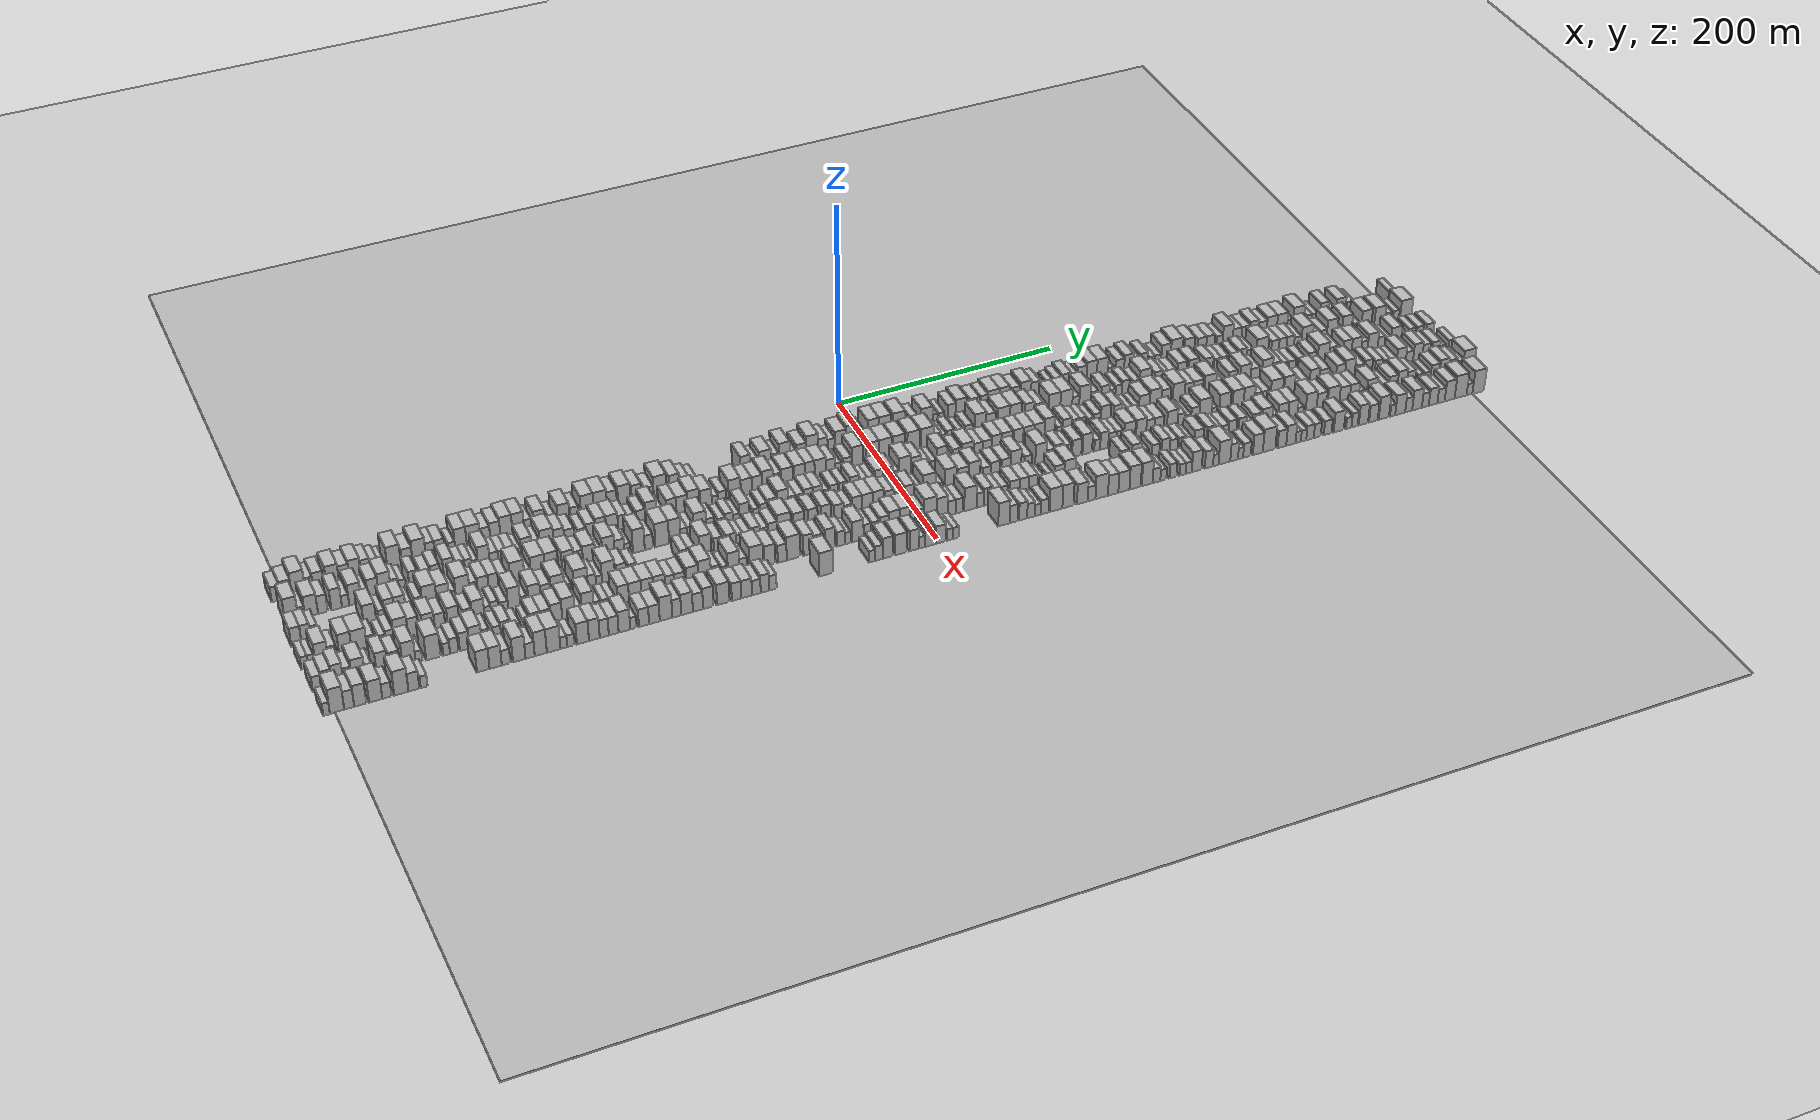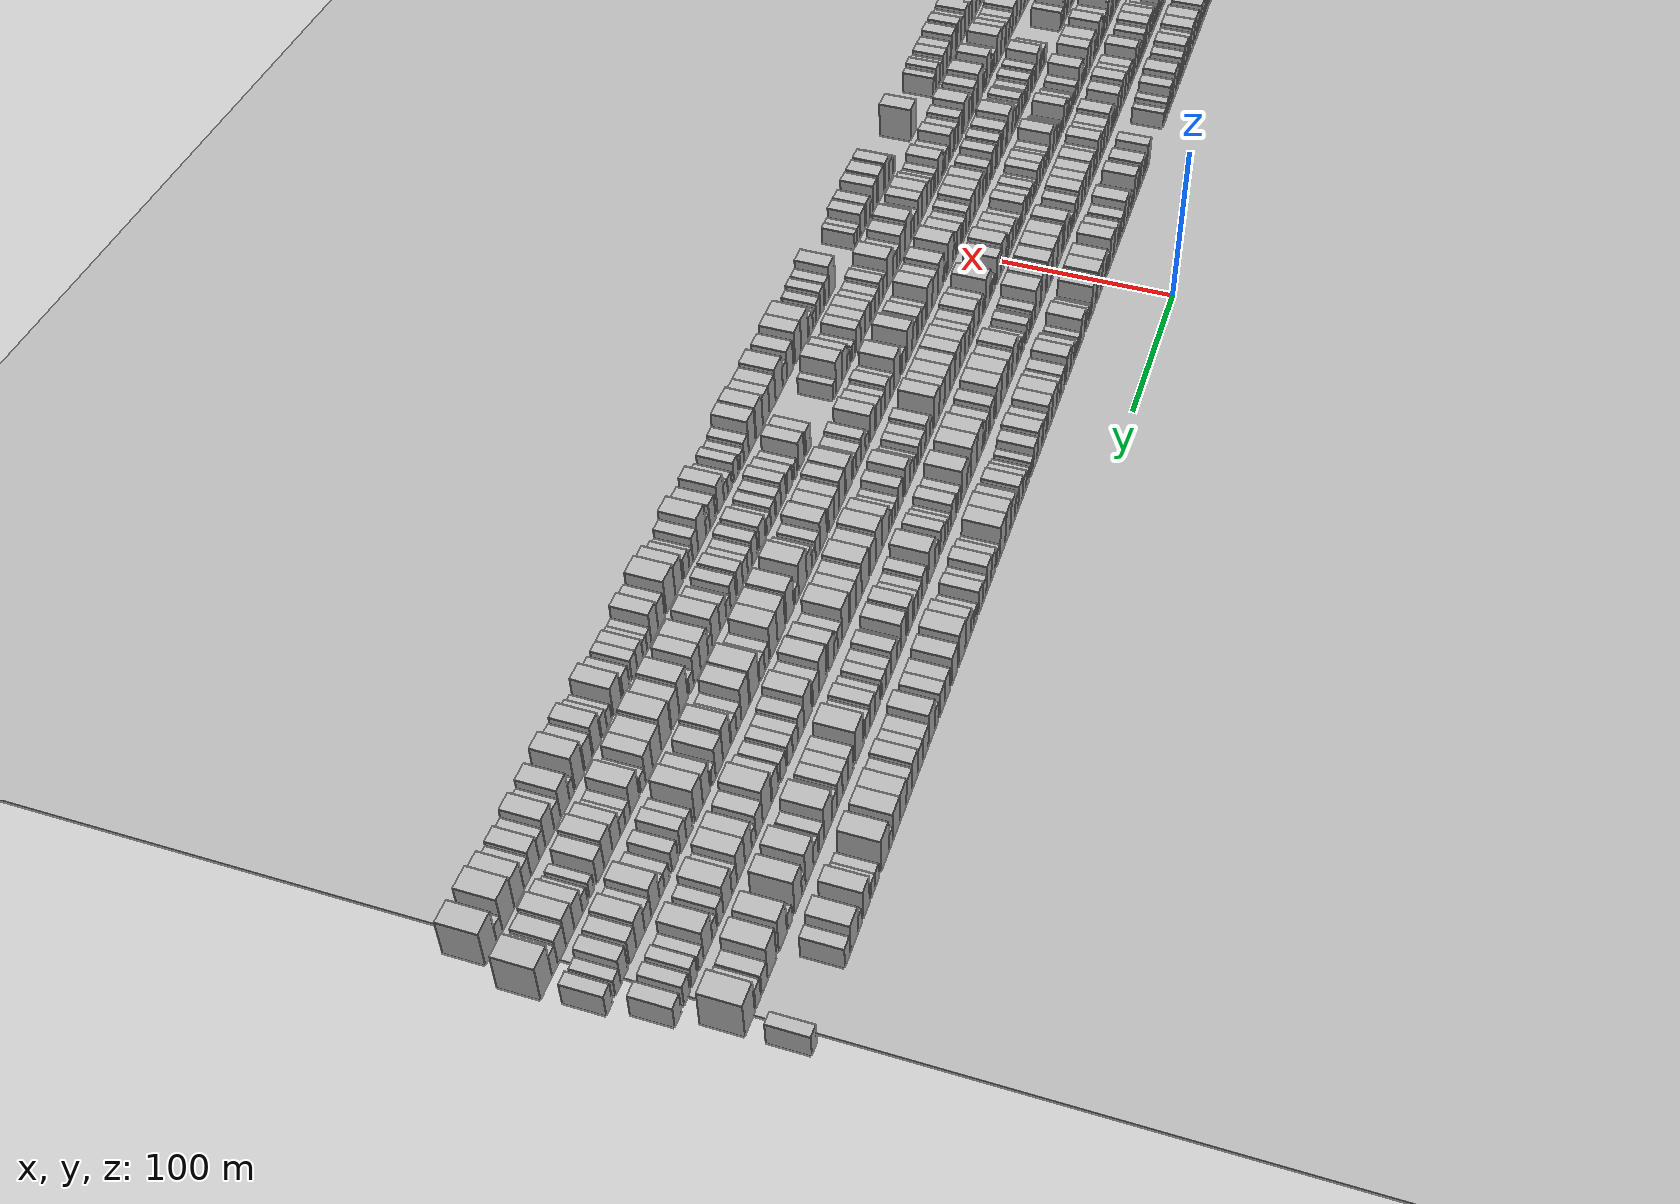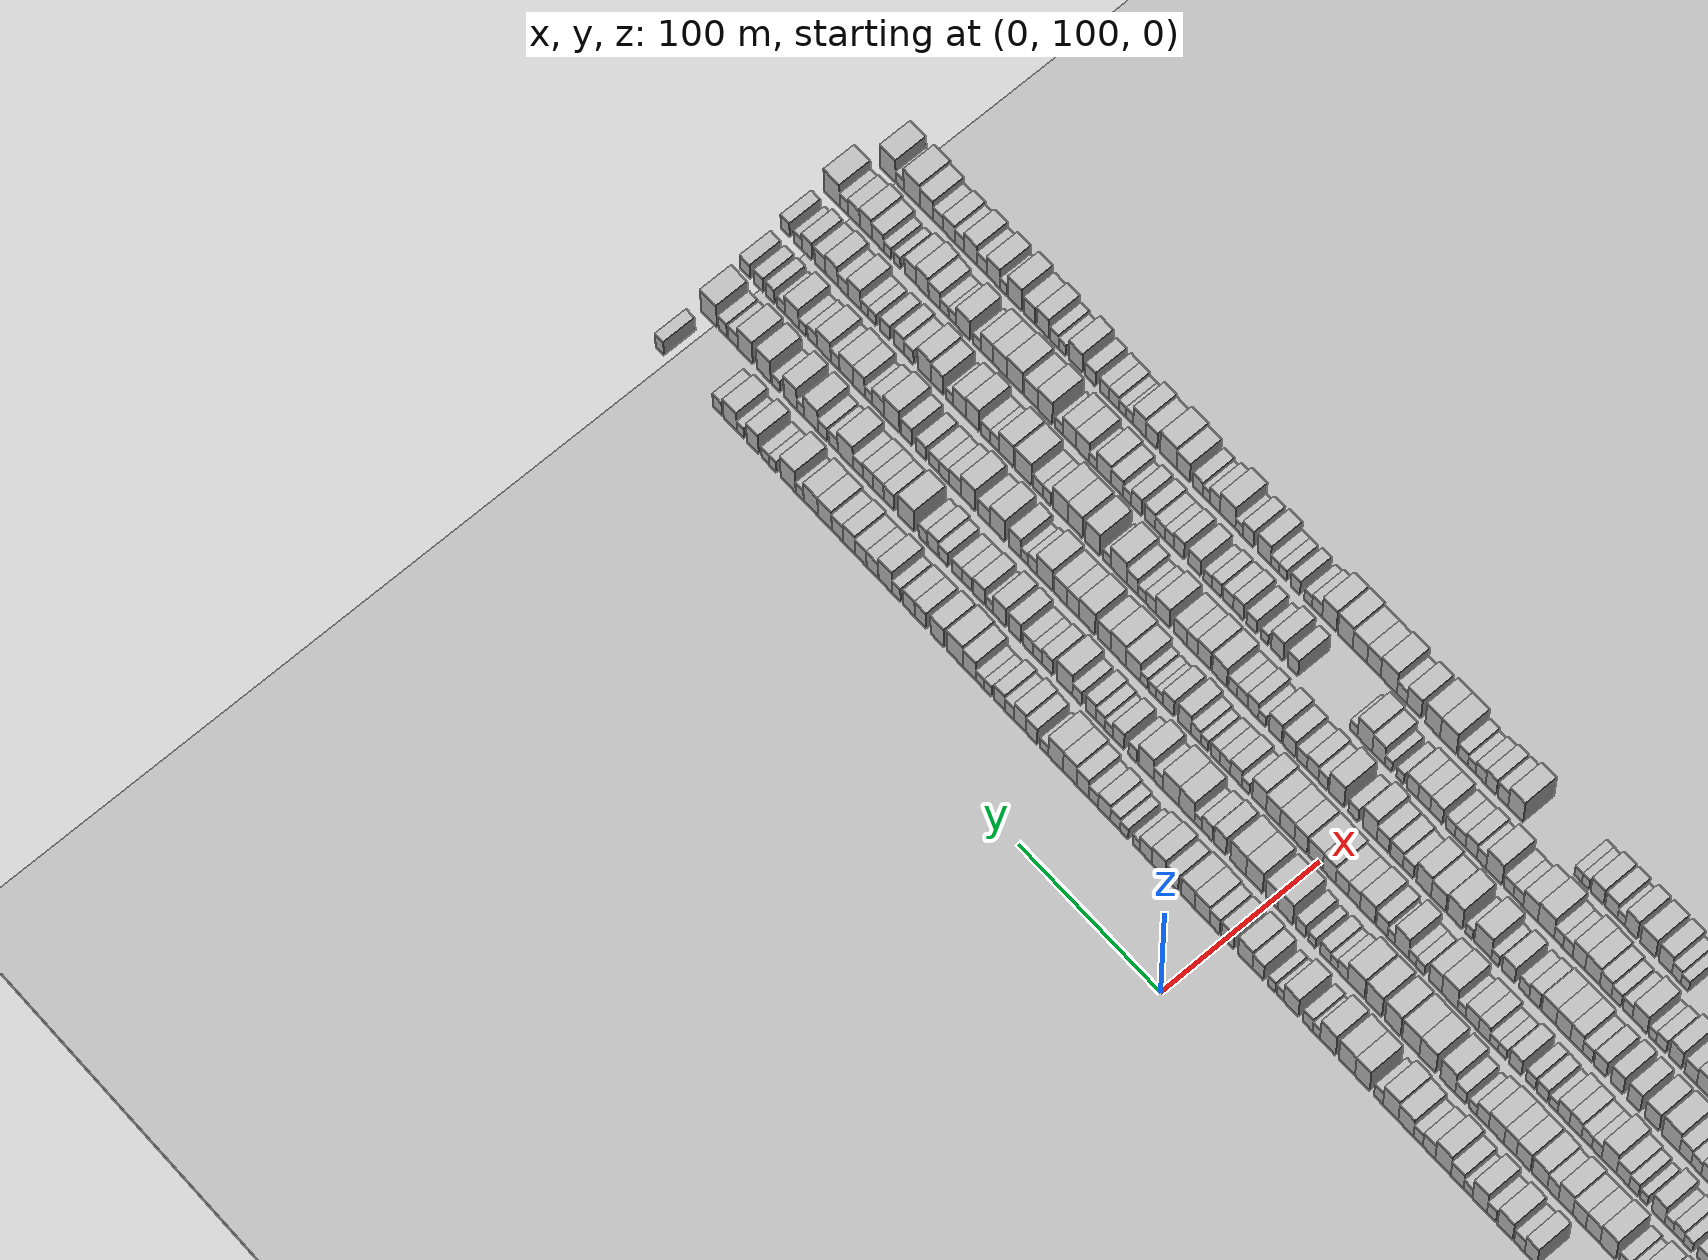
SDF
<?xml version="1.0" encoding="utf-8"?>

<sdf version="1.6">

   <world name="default">

      <gui fullscreen="0">

         <camera name="user_camera">

            <pose>-15 0 4.57585 0 0 0</pose>

            <view_controller>orbit</view_controller>

         </camera>

      </gui>

      <scene>

         <sky>

           <clouds>

             <speed>12</speed>

           </clouds>

         </sky>

         <ambient>0.4 0.4 0.4 1</ambient>

         <background>0.7 0.7 0.7 1</background>

         <shadows>1</shadows>

      </scene>

      <gravity>0 0 -9.8066</gravity>

      <magnetic_field>6e-06 2.3e-05 -4.2e-05</magnetic_field>

      <physics default="0" name="default_physics" type="ode">

         <ode>

            <solver>

               <type>quick</type>

               <iters>10</iters>

               <sor>1.0</sor>

               <use_dynamic_moi_rescaling>0</use_dynamic_moi_rescaling>

            </solver>

            <constraints>

               <cfm>0</cfm>

               <erp>0.2</erp>

               <contact_max_correcting_vel>100</contact_max_correcting_vel>

               <contact_surface_layer>0.001</contact_surface_layer>

            </constraints>

         </ode>

         <max_step_size>0.004</max_step_size>

         <real_time_factor>1</real_time_factor>

         <real_time_update_rate>250</real_time_update_rate>

      </physics>

      <light name="sun" type="directional">

         <cast_shadows>1</cast_shadows>

         <pose>0 0 10 0 0 0</pose>

         <diffuse>0.8 0.8 0.8 1</diffuse>

         <specular>0.2 0.2 0.2 1</specular>

         <attenuation>

            <range>1000</range>

            <constant>0.9</constant>

            <linear>0.01</linear>

            <quadratic>0.001</quadratic>

         </attenuation>

         <direction>-0.5 0.1 -0.9</direction>

      </light>

      <include>

         <name>ground_plane_1</name>

         <uri>model://HANNAS_ground_plane</uri>

         <pose>0 0 0  0 0 0</pose>

      </include>

      <include>

         <name>ground_plane_2</name>

         <uri>model://HANNAS_ground_plane</uri>

         <pose>100 0 0  0 0 0</pose>

      </include>

      <model name="building_1">

         <static>1</static>

         <pose frame="">50.0000 -506.3018 0 0.000000 0.000000 0.000000</pose>

         <link name="link">

            <pose frame="">0 0 7.50 0 0 0</pose>

            <collision name="collision">

               <geometry>

                  <box>

                     <size>20.0000 7.3964 15.0000</size>

                  </box>

               </geometry>

               <max_contacts>10</max_contacts>

               <surface>

                  <contact>

                     <ode/>

                  </contact>

                  <bounce/>

                  <friction>

                     <torsional>

                        <ode/>

                     </torsional>

                     <ode/>

                  </friction>

               </surface>

            </collision>

            <visual name="visual">

               <cast_shadows>0</cast_shadows>

               <geometry>

                  <box>

                     <size>20.0000 7.3964 15.0000</size>

                  </box>

               </geometry>

               <material>

                  <script>

                     <uri>model://HANNAS_wall/materials/scripts</uri>

                     <uri>model://HANNAS_wall/materials/textures</uri>

                     <name>vrc/HANNAS_wall</name>

                  </script>

               </material>

            </visual>

            <self_collide>0</self_collide>

            <enable_wind>0</enable_wind>

            <kinematic>0</kinematic>

         </link>

      </model>

      <model name="building_2">

         <static>1</static>

         <pose frame="">50.0000 -498.1552 0 0.000000 0.000000 0.000000</pose>

         <link name="link">

            <pose frame="">0 0 9.00 0 0 0</pose>

            <collision name="collision">

               <geometry>

                  <box>

                     <size>20.0000 8.8969 18.0000</size>

                  </box>

               </geometry>

               <max_contacts>10</max_contacts>

               <surface>

                  <contact>

                     <ode/>

                  </contact>

                  <bounce/>

                  <friction>

                     <torsional>

                        <ode/>

                     </torsional>

                     <ode/>

                  </friction>

               </surface>

            </collision>

            <visual name="visual">

               <cast_shadows>0</cast_shadows>

               <geometry>

                  <box>

                     <size>20.0000 8.8969 18.0000</size>

                  </box>

               </geometry>

               <material>

                  <script>

                     <uri>model://HANNAS_wall/materials/scripts</uri>

                     <uri>model://HANNAS_wall/materials/textures</uri>

                     <name>vrc/HANNAS_wall</name>

                  </script>

               </material>

            </visual>

            <self_collide>0</self_collide>

            <enable_wind>0</enable_wind>

            <kinematic>0</kinematic>

         </link>

      </model>

      <model name="building_3">

         <static>1</static>

         <pose frame="">50.0000 -488.2676 0 0.000000 0.000000 0.000000</pose>

         <link name="link">

            <pose frame="">0 0 12.00 0 0 0</pose>

            <collision name="collision">

               <geometry>

                  <box>

                     <size>20.0000 10.8781 24.0000</size>

                  </box>

               </geometry>

               <max_contacts>10</max_contacts>

               <surface>

                  <contact>

                     <ode/>

                  </contact>

                  <bounce/>

                  <friction>

                     <torsional>

                        <ode/>

                     </torsional>

                     <ode/>

                  </friction>

               </surface>

            </collision>

            <visual name="visual">

               <cast_shadows>0</cast_shadows>

               <geometry>

                  <box>

                     <size>20.0000 10.8781 24.0000</size>

                  </box>

               </geometry>

               <material>

                  <script>

                     <uri>model://HANNAS_wall/materials/scripts</uri>

                     <uri>model://HANNAS_wall/materials/textures</uri>

                     <name>vrc/HANNAS_wall</name>

                  </script>

               </material>

            </visual>

            <self_collide>0</self_collide>

            <enable_wind>0</enable_wind>

            <kinematic>0</kinematic>

         </link>

      </model>

      <model name="building_4">

         <static>1</static>

         <pose frame="">50.0000 -479.5904 0 0.000000 0.000000 0.000000</pose>

         <link name="link">

            <pose frame="">0 0 7.50 0 0 0</pose>

            <collision name="collision">

               <geometry>

                  <box>

                     <size>20.0000 6.4764 15.0000</size>

                  </box>

               </geometry>

               <max_contacts>10</max_contacts>

               <surface>

                  <contact>

                     <ode/>

                  </contact>

                  <bounce/>

                  <friction>

                     <torsional>

                        <ode/>

                     </torsional>

                     <ode/>

                  </friction>

               </surface>

            </collision>

            <visual name="visual">

               <cast_shadows>0</cast_shadows>

               <geometry>

                  <box>

                     <size>20.0000 6.4764 15.0000</size>

                  </box>

               </geometry>

               <material>

                  <script>

                     <uri>model://HANNAS_wall/materials/scripts</uri>

                     <uri>model://HANNAS_wall/materials/textures</uri>

                     <name>vrc/HANNAS_wall</name>

                  </script>

               </material>

            </visual>

            <self_collide>0</self_collide>

            <enable_wind>0</enable_wind>

            <kinematic>0</kinematic>

         </link>

      </model>

      <model name="building_5">

         <static>1</static>

         <pose frame="">50.0000 -472.0109 0 0.000000 0.000000 0.000000</pose>

         <link name="link">

            <pose frame="">0 0 9.00 0 0 0</pose>

            <collision name="collision">

               <geometry>

                  <box>

                     <size>20.0000 8.6825 18.0000</size>

                  </box>

               </geometry>

               <max_contacts>10</max_contacts>

               <surface>

                  <contact>

                     <ode/>

                  </contact>

                  <bounce/>

                  <friction>

                     <torsional>

                        <ode/>

                     </torsional>

                     <ode/>

                  </friction>

               </surface>

            </collision>

            <visual name="visual">

               <cast_shadows>0</cast_shadows>

               <geometry>

                  <box>

                     <size>20.0000 8.6825 18.0000</size>

                  </box>

               </geometry>

               <material>

                  <script>

                     <uri>model://HANNAS_wall/materials/scripts</uri>

                     <uri>model://HANNAS_wall/materials/textures</uri>

                     <name>vrc/HANNAS_wall</name>

                  </script>

               </material>

            </visual>

            <self_collide>0</self_collide>

            <enable_wind>0</enable_wind>

            <kinematic>0</kinematic>

         </link>

      </model>

      <model name="building_6">

         <static>1</static>

         <pose frame="">50.0000 -460.5266 0 0.000000 0.000000 0.000000</pose>

         <link name="link">

            <pose frame="">0 0 10.50 0 0 0</pose>

            <collision name="collision">

               <geometry>

                  <box>

                     <size>20.0000 10.2862 21.0000</size>

                  </box>

               </geometry>

               <max_contacts>10</max_contacts>

               <surface>

                  <contact>

                     <ode/>

                  </contact>

                  <bounce/>

                  <friction>

                     <torsional>

                        <ode/>

                     </torsional>

                     <ode/>

                  </friction>

               </surface>

            </collision>

            <visual name="visual">

               <cast_shadows>0</cast_shadows>

               <geometry>

                  <box>

                     <size>20.0000 10.2862 21.0000</size>

                  </box>

               </geometry>

               <material>

                  <script>

                     <uri>model://HANNAS_wall/materials/scripts</uri>

                     <uri>model://HANNAS_wall/materials/textures</uri>

                     <name>vrc/HANNAS_wall</name>

                  </script>

               </material>

            </visual>

            <self_collide>0</self_collide>

            <enable_wind>0</enable_wind>

            <kinematic>0</kinematic>

         </link>

      </model>

      <model name="building_7">

         <static>1</static>

         <pose frame="">50.0000 -451.1622 0 0.000000 0.000000 0.000000</pose>

         <link name="link">

            <pose frame="">0 0 9.00 0 0 0</pose>

            <collision name="collision">

               <geometry>

                  <box>

                     <size>20.0000 8.4425 18.0000</size>

                  </box>

               </geometry>

               <max_contacts>10</max_contacts>

               <surface>

                  <contact>

                     <ode/>

                  </contact>

                  <bounce/>

                  <friction>

                     <torsional>

                        <ode/>

                     </torsional>

                     <ode/>

                  </friction>

               </surface>

            </collision>

            <visual name="visual">

               <cast_shadows>0</cast_shadows>

               <geometry>

                  <box>

                     <size>20.0000 8.4425 18.0000</size>

                  </box>

               </geometry>

               <material>

                  <script>

                     <uri>model://HANNAS_wall/materials/scripts</uri>

                     <uri>model://HANNAS_wall/materials/textures</uri>

                     <name>vrc/HANNAS_wall</name>

                  </script>

               </material>

            </visual>

            <self_collide>0</self_collide>

            <enable_wind>0</enable_wind>

            <kinematic>0</kinematic>

         </link>

      </model>

      <model name="building_8">

         <static>1</static>

         <pose frame="">50.0000 -442.1549 0 0.000000 0.000000 0.000000</pose>

         <link name="link">

            <pose frame="">0 0 10.50 0 0 0</pose>

            <collision name="collision">

               <geometry>

                  <box>

                     <size>20.0000 9.5721 21.0000</size>

                  </box>

               </geometry>

               <max_contacts>10</max_contacts>

               <surface>

                  <contact>

                     <ode/>

                  </contact>

                  <bounce/>

                  <friction>

                     <torsional>

                        <ode/>

                     </torsional>

                     <ode/>

                  </friction>

               </surface>

            </collision>

            <visual name="visual">

               <cast_shadows>0</cast_shadows>

               <geometry>

                  <box>

                     <size>20.0000 9.5721 21.0000</size>

                  </box>

               </geometry>

               <material>

                  <script>

                     <uri>model://HANNAS_wall/materials/scripts</uri>

                     <uri>model://HANNAS_wall/materials/textures</uri>

                     <name>vrc/HANNAS_wall</name>

                  </script>

               </material>

            </visual>

            <self_collide>0</self_collide>

            <enable_wind>0</enable_wind>

            <kinematic>0</kinematic>

         </link>

      </model>

      <model name="building_9">

         <static>1</static>

         <pose frame="">50.0000 -433.5537 0 0.000000 0.000000 0.000000</pose>

         <link name="link">

            <pose frame="">0 0 9.00 0 0 0</pose>

            <collision name="collision">

               <geometry>

                  <box>

                     <size>20.0000 7.6305 18.0000</size>

                  </box>

               </geometry>

               <max_contacts>10</max_contacts>

               <surface>

                  <contact>

                     <ode/>

                  </contact>

                  <bounce/>

                  <friction>

                     <torsional>

                        <ode/>

                     </torsional>

                     <ode/>

                  </friction>

               </surface>

            </collision>

            <visual name="visual">

               <cast_shadows>0</cast_shadows>

               <geometry>

                  <box>

                     <size>20.0000 7.6305 18.0000</size>

                  </box>

               </geometry>

               <material>

                  <script>

                     <uri>model://HANNAS_wall/materials/scripts</uri>

                     <uri>model://HANNAS_wall/materials/textures</uri>

                     <name>vrc/HANNAS_wall</name>

                  </script>

               </material>

            </visual>

            <self_collide>0</self_collide>

            <enable_wind>0</enable_wind>

            <kinematic>0</kinematic>

         </link>

      </model>

      <model name="building_10">

         <static>1</static>

         <pose frame="">50.0000 -426.4215 0 0.000000 0.000000 0.000000</pose>

         <link name="link">

            <pose frame="">0 0 7.50 0 0 0</pose>

            <collision name="collision">

               <geometry>

                  <box>

                     <size>20.0000 6.6337 15.0000</size>

                  </box>

               </geometry>

               <max_contacts>10</max_contacts>

               <surface>

                  <contact>

                     <ode/>

                  </contact>

                  <bounce/>

                  <friction>

                     <torsional>

                        <ode/>

                     </torsional>

                     <ode/>

                  </friction>

               </surface>

            </collision>

            <visual name="visual">

               <cast_shadows>0</cast_shadows>

               <geometry>

                  <box>

                     <size>20.0000 6.6337 15.0000</size>

                  </box>

               </geometry>

               <material>

                  <script>

                     <uri>model://HANNAS_wall/materials/scripts</uri>

                     <uri>model://HANNAS_wall/materials/textures</uri>

                     <name>vrc/HANNAS_wall</name>

                  </script>

               </material>

            </visual>

            <self_collide>0</self_collide>

            <enable_wind>0</enable_wind>

            <kinematic>0</kinematic>

         </link>

      </model>

      <model name="building_11">

         <static>1</static>

         <pose frame="">50.0000 -420.4906 0 0.000000 0.000000 0.000000</pose>

         <link name="link">

            <pose frame="">0 0 6.00 0 0 0</pose>

            <collision name="collision">

               <geometry>

                  <box>

                     <size>20.0000 5.2281 12.0000</size>

                  </box>

               </geometry>

               <max_contacts>10</max_contacts>

               <surface>

                  <contact>

                     <ode/>

                  </contact>

                  <bounce/>

                  <friction>

                     <torsional>

                        <ode/>

                     </torsional>

                     <ode/>

                  </friction>

               </surface>

            </collision>

            <visual name="visual">

               <cast_shadows>0</cast_shadows>

               <geometry>

                  <box>

                     <size>20.0000 5.2281 12.0000</size>

                  </box>

               </geometry>

               <material>

                  <script>

                     <uri>model://HANNAS_wall/materials/scripts</uri>

                     <uri>model://HANNAS_wall/materials/textures</uri>

                     <name>vrc/HANNAS_wall</name>

                  </script>

               </material>

            </visual>

            <self_collide>0</self_collide>

            <enable_wind>0</enable_wind>

            <kinematic>0</kinematic>

         </link>

      </model>

      <model name="building_12">

         <static>1</static>

         <pose frame="">50.0000 -410.3099 0 0.000000 0.000000 0.000000</pose>

         <link name="link">

            <pose frame="">0 0 12.00 0 0 0</pose>

            <collision name="collision">

               <geometry>

                  <box>

                     <size>20.0000 11.1335 24.0000</size>

                  </box>

               </geometry>

               <max_contacts>10</max_contacts>

               <surface>

                  <contact>

                     <ode/>

                  </contact>

                  <bounce/>

                  <friction>

                     <torsional>

                        <ode/>

                     </torsional>

                     <ode/>

                  </friction>

               </surface>

            </collision>

            <visual name="visual">

               <cast_shadows>0</cast_shadows>

               <geometry>

                  <box>

                     <size>20.0000 11.1335 24.0000</size>

                  </box>

               </geometry>

               <material>

                  <script>

                     <uri>model://HANNAS_wall/materials/scripts</uri>

                     <uri>model://HANNAS_wall/materials/textures</uri>

                     <name>vrc/HANNAS_wall</name>

                  </script>

               </material>

            </visual>

            <self_collide>0</self_collide>

            <enable_wind>0</enable_wind>

            <kinematic>0</kinematic>

         </link>

      </model>

      <model name="building_13">

         <static>1</static>

         <pose frame="">50.0000 -399.4343 0 0.000000 0.000000 0.000000</pose>

         <link name="link">

            <pose frame="">0 0 9.00 0 0 0</pose>

            <collision name="collision">

               <geometry>

                  <box>

                     <size>20.0000 8.6176 18.0000</size>

                  </box>

               </geometry>

               <max_contacts>10</max_contacts>

               <surface>

                  <contact>

                     <ode/>

                  </contact>

                  <bounce/>

                  <friction>

                     <torsional>

                        <ode/>

                     </torsional>

                     <ode/>

                  </friction>

               </surface>

            </collision>

            <visual name="visual">

               <cast_shadows>0</cast_shadows>

               <geometry>

                  <box>

                     <size>20.0000 8.6176 18.0000</size>

                  </box>

               </geometry>

               <material>

                  <script>

                     <uri>model://HANNAS_wall/materials/scripts</uri>

                     <uri>model://HANNAS_wall/materials/textures</uri>

                     <name>vrc/HANNAS_wall</name>

                  </script>

               </material>

            </visual>

            <self_collide>0</self_collide>

            <enable_wind>0</enable_wind>

            <kinematic>0</kinematic>

         </link>

      </model>

      <model name="building_14">

         <static>1</static>

         <pose frame="">50.0000 -389.5789 0 0.000000 0.000000 0.000000</pose>

         <link name="link">

            <pose frame="">0 0 12.00 0 0 0</pose>

            <collision name="collision">

               <geometry>

                  <box>

                     <size>20.0000 11.0933 24.0000</size>

                  </box>

               </geometry>

               <max_contacts>10</max_contacts>

               <surface>

                  <contact>

                     <ode/>

                  </contact>

                  <bounce/>

                  <friction>

                     <torsional>

                        <ode/>

                     </torsional>

                     <ode/>

                  </friction>

               </surface>

            </collision>

            <visual name="visual">

               <cast_shadows>0</cast_shadows>

               <geometry>

                  <box>

                     <size>20.0000 11.0933 24.0000</size>

                  </box>

               </geometry>

               <material>

                  <script>

                     <uri>model://HANNAS_wall/materials/scripts</uri>

                     <uri>model://HANNAS_wall/materials/textures</uri>

                     <name>vrc/HANNAS_wall</name>

                  </script>

               </material>

            </visual>

            <self_collide>0</self_collide>

            <enable_wind>0</enable_wind>

            <kinematic>0</kinematic>

         </link>

      </model>

      <model name="building_15">

         <static>1</static>

         <pose frame="">50.0000 -380.3557 0 0.000000 0.000000 0.000000</pose>

         <link name="link">

            <pose frame="">0 0 9.00 0 0 0</pose>

            <collision name="collision">

               <geometry>

                  <box>

                     <size>20.0000 7.3531 18.0000</size>

                  </box>

               </geometry>

               <max_contacts>10</max_contacts>

               <surface>

                  <contact>

                     <ode/>

                  </contact>

                  <bounce/>

                  <friction>

                     <torsional>

                        <ode/>

                     </torsional>

                     <ode/>

                  </friction>

               </surface>

            </collision>

            <visual name="visual">

               <cast_shadows>0</cast_shadows>

               <geometry>

                  <box>

                     <size>20.0000 7.3531 18.0000</size>

                  </box>

               </geometry>

               <material>

                  <script>

                     <uri>model://HANNAS_wall/materials/scripts</uri>

                     <uri>model://HANNAS_wall/materials/textures</uri>

                     <name>vrc/HANNAS_wall</name>

                  </script>

               </material>

            </visual>

            <self_collide>0</self_collide>

            <enable_wind>0</enable_wind>

            <kinematic>0</kinematic>

         </link>

      </model>

      <model name="building_16">

         <static>1</static>

         <pose frame="">50.0000 -372.4623 0 0.000000 0.000000 0.000000</pose>

         <link name="link">

            <pose frame="">0 0 9.00 0 0 0</pose>

            <collision name="collision">

               <geometry>

                  <box>

                     <size>20.0000 8.4337 18.0000</size>

                  </box>

               </geometry>

               <max_contacts>10</max_contacts>

               <surface>

                  <contact>

                     <ode/>

                  </contact>

                  <bounce/>

                  <friction>

                     <torsional>

                        <ode/>

                     </torsional>

                     <ode/>

                  </friction>

               </surface>

            </collision>

            <visual name="visual">

               <cast_shadows>0</cast_shadows>

               <geometry>

                  <box>

                     <size>20.0000 8.4337 18.0000</size>

                  </box>

               </geometry>

               <material>

                  <script>

                     <uri>model://HANNAS_wall/materials/scripts</uri>

                     <uri>model://HANNAS_wall/materials/textures</uri>

                     <name>vrc/HANNAS_wall</name>

                  </script>

               </material>

            </visual>

            <self_collide>0</self_collide>

            <enable_wind>0</enable_wind>

            <kinematic>0</kinematic>

         </link>

      </model>

      <model name="building_17">

         <static>1</static>

         <pose frame="">50.0000 -362.4733 0 0.000000 0.000000 0.000000</pose>

         <link name="link">

            <pose frame="">0 0 6.00 0 0 0</pose>

            <collision name="collision">

               <geometry>

                  <box>

                     <size>20.0000 5.5442 12.0000</size>

                  </box>

               </geometry>

               <max_contacts>10</max_contacts>

               <surface>

                  <contact>

                     <ode/>

                  </contact>

                  <bounce/>

                  <friction>

                     <torsional>

                        <ode/>

                     </torsional>

                     <ode/>

                  </friction>

               </surface>

            </collision>

            <visual name="visual">

               <cast_shadows>0</cast_shadows>

               <geometry>

                  <box>

                     <size>20.0000 5.5442 12.0000</size>

                  </box>

               </geometry>

               <material>

                  <script>

                     <uri>model://HANNAS_wall/materials/scripts</uri>

                     <uri>model://HANNAS_wall/materials/textures</uri>

                     <name>vrc/HANNAS_wall</name>

                  </script>

               </material>

            </visual>

            <self_collide>0</self_collide>

            <enable_wind>0</enable_wind>

            <kinematic>0</kinematic>

         </link>

      </model>

      <model name="building_18">

         <static>1</static>

         <pose frame="">50.0000 -354.8416 0 0.000000 0.000000 0.000000</pose>

         <link name="link">

            <pose frame="">0 0 12.00 0 0 0</pose>

            <collision name="collision">

               <geometry>

                  <box>

                     <size>20.0000 9.7191 24.0000</size>

                  </box>

               </geometry>

               <max_contacts>10</max_contacts>

               <surface>

                  <contact>

                     <ode/>

                  </contact>

                  <bounce/>

                  <friction>

                     <torsional>

                        <ode/>

                     </torsional>

                     <ode/>

                  </friction>

               </surface>

            </collision>

            <visual name="visual">

               <cast_shadows>0</cast_shadows>

               <geometry>

                  <box>

                     <size>20.0000 9.7191 24.0000</size>

                  </box>

               </geometry>

               <material>

                  <script>

                     <uri>model://HANNAS_wall/materials/scripts</uri>

                     <uri>model://HANNAS_wall/materials/textures</uri>

                     <name>vrc/HANNAS_wall</name>

                  </script>

               </material>

            </visual>

            <self_collide>0</self_collide>

            <enable_wind>0</enable_wind>

            <kinematic>0</kinematic>

         </link>

      </model>

      <model name="building_19">

         <static>1</static>

         <pose frame="">50.0000 -344.2495 0 0.000000 0.000000 0.000000</pose>

         <link name="link">

            <pose frame="">0 0 12.00 0 0 0</pose>

            <collision name="collision">

               <geometry>

                  <box>

                     <size>20.0000 11.4651 24.0000</size>

                  </box>

               </geometry>

               <max_contacts>10</max_contacts>

               <surface>

                  <contact>

                     <ode/>

                  </contact>

                  <bounce/>

                  <friction>

                     <torsional>

                        <ode/>

                     </torsional>

                     <ode/>

                  </friction>

               </surface>

            </collision>

            <visual name="visual">

               <cast_shadows>0</cast_shadows>

               <geometry>

                  <box>

                     <size>20.0000 11.4651 24.0000</size>

                  </box>

               </geometry>

               <material>

                  <script>

                     <uri>model://HANNAS_wall/materials/scripts</uri>

                     <uri>model://HANNAS_wall/materials/textures</uri>

                     <name>vrc/HANNAS_wall</name>

                  </script>

               </material>

            </visual>

            <self_collide>0</self_collide>

            <enable_wind>0</enable_wind>

            <kinematic>0</kinematic>

         </link>

      </model>

      <model name="building_20">

         <static>1</static>

         <pose frame="">50.0000 -334.4383 0 0.000000 0.000000 0.000000</pose>

         <link name="link">

            <pose frame="">0 0 9.00 0 0 0</pose>

            <collision name="collision">

               <geometry>

                  <box>

                     <size>20.0000 8.1575 18.0000</size>

                  </box>

               </geometry>

               <max_contacts>10</max_contacts>

               <surface>

                  <contact>

                     <ode/>

                  </contact>

                  <bounce/>

                  <friction>

                     <torsional>

                        <ode/>

                     </torsional>

                     <ode/>

                  </friction>

               </surface>

            </collision>

            <visual name="visual">

               <cast_shadows>0</cast_shadows>

               <geometry>

                  <box>

                     <size>20.0000 8.1575 18.0000</size>

                  </box>

               </geometry>

               <material>

                  <script>

                     <uri>model://HANNAS_wall/materials/scripts</uri>

                     <uri>model://HANNAS_wall/materials/textures</uri>

                     <name>vrc/HANNAS_wall</name>

                  </script>

               </material>

            </visual>

            <self_collide>0</self_collide>

            <enable_wind>0</enable_wind>

            <kinematic>0</kinematic>

         </link>

      </model>

      <model name="building_21">

         <static>1</static>

         <pose frame="">50.0000 -326.1122 0 0.000000 0.000000 0.000000</pose>

         <link name="link">

            <pose frame="">0 0 10.50 0 0 0</pose>

            <collision name="collision">

               <geometry>

                  <box>

                     <size>20.0000 8.4947 21.0000</size>

                  </box>

               </geometry>

               <max_contacts>10</max_contacts>

               <surface>

                  <contact>

                     <ode/>

                  </contact>

                  <bounce/>

                  <friction>

                     <torsional>

                        <ode/>

                     </torsional>

                     <ode/>

                  </friction>

               </surface>

            </collision>

            <visual name="visual">

               <cast_shadows>0</cast_shadows>

               <geometry>

                  <box>

                     <size>20.0000 8.4947 21.0000</size>

                  </box>

               </geometry>

               <material>

                  <script>

                     <uri>model://HANNAS_wall/materials/scripts</uri>

                     <uri>model://HANNAS_wall/materials/textures</uri>

                     <name>vrc/HANNAS_wall</name>

                  </script>

               </material>

            </visual>

            <self_collide>0</self_collide>

            <enable_wind>0</enable_wind>

            <kinematic>0</kinematic>

         </link>

      </model>

      <model name="building_22">

         <static>1</static>

         <pose frame="">50.0000 -316.7269 0 0.000000 0.000000 0.000000</pose>

         <link name="link">

            <pose frame="">0 0 12.00 0 0 0</pose>

            <collision name="collision">

               <geometry>

                  <box>

                     <size>20.0000 10.2759 24.0000</size>

                  </box>

               </geometry>

               <max_contacts>10</max_contacts>

               <surface>

                  <contact>

                     <ode/>

                  </contact>

                  <bounce/>

                  <friction>

                     <torsional>

                        <ode/>

                     </torsional>

                     <ode/>

                  </friction>

               </surface>

            </collision>

            <visual name="visual">

               <cast_shadows>0</cast_shadows>

               <geometry>

                  <box>

                     <size>20.0000 10.2759 24.0000</size>

                  </box>

               </geometry>

               <material>

                  <script>

                     <uri>model://HANNAS_wall/materials/scripts</uri>

                     <uri>model://HANNAS_wall/materials/textures</uri>

                     <name>vrc/HANNAS_wall</name>

                  </script>

               </material>

            </visual>

            <self_collide>0</self_collide>

            <enable_wind>0</enable_wind>

            <kinematic>0</kinematic>

         </link>

      </model>

      <model name="building_23">

         <static>1</static>

         <pose frame="">50.0000 -306.6334 0 0.000000 0.000000 0.000000</pose>

         <link name="link">

            <pose frame="">0 0 12.00 0 0 0</pose>

            <collision name="collision">

               <geometry>

                  <box>

                     <size>20.0000 9.9111 24.0000</size>

                  </box>

               </geometry>

               <max_contacts>10</max_contacts>

               <surface>

                  <contact>

                     <ode/>

                  </contact>

                  <bounce/>

                  <friction>

                     <torsional>

                        <ode/>

                     </torsional>

                     <ode/>

                  </friction>

               </surface>

            </collision>

            <visual name="visual">

               <cast_shadows>0</cast_shadows>

               <geometry>

                  <box>

                     <size>20.0000 9.9111 24.0000</size>

                  </box>

               </geometry>

               <material>

                  <script>

                     <uri>model://HANNAS_wall/materials/scripts</uri>

                     <uri>model://HANNAS_wall/materials/textures</uri>

                     <name>vrc/HANNAS_wall</name>

                  </script>

               </material>

            </visual>

            <self_collide>0</self_collide>

            <enable_wind>0</enable_wind>

            <kinematic>0</kinematic>

         </link>

      </model>

      <model name="building_24">

         <static>1</static>

         <pose frame="">50.0000 -298.5820 0 0.000000 0.000000 0.000000</pose>

         <link name="link">

            <pose frame="">0 0 7.50 0 0 0</pose>

            <collision name="collision">

               <geometry>

                  <box>

                     <size>20.0000 6.1917 15.0000</size>

                  </box>

               </geometry>

               <max_contacts>10</max_contacts>

               <surface>

                  <contact>

                     <ode/>

                  </contact>

                  <bounce/>

                  <friction>

                     <torsional>

                        <ode/>

                     </torsional>

                     <ode/>

                  </friction>

               </surface>

            </collision>

            <visual name="visual">

               <cast_shadows>0</cast_shadows>

               <geometry>

                  <box>

                     <size>20.0000 6.1917 15.0000</size>

                  </box>

               </geometry>

               <material>

                  <script>

                     <uri>model://HANNAS_wall/materials/scripts</uri>

                     <uri>model://HANNAS_wall/materials/textures</uri>

                     <name>vrc/HANNAS_wall</name>

                  </script>

               </material>

            </visual>

            <self_collide>0</self_collide>

            <enable_wind>0</enable_wind>

            <kinematic>0</kinematic>

         </link>

      </model>

      <model name="building_25">

         <static>1</static>

         <pose frame="">50.0000 -288.6683 0 0.000000 0.000000 0.000000</pose>

         <link name="link">

            <pose frame="">0 0 10.50 0 0 0</pose>

            <collision name="collision">

               <geometry>

                  <box>

                     <size>20.0000 9.6357 21.0000</size>

                  </box>

               </geometry>

               <max_contacts>10</max_contacts>

               <surface>

                  <contact>

                     <ode/>

                  </contact>

                  <bounce/>

                  <friction>

                     <torsional>

                        <ode/>

                     </torsional>

                     <ode/>

                  </friction>

               </surface>

            </collision>

            <visual name="visual">

               <cast_shadows>0</cast_shadows>

               <geometry>

                  <box>

                     <size>20.0000 9.6357 21.0000</size>

                  </box>

               </geometry>

               <material>

                  <script>

                     <uri>model://HANNAS_wall/materials/scripts</uri>

                     <uri>model://HANNAS_wall/materials/textures</uri>

                     <name>vrc/HANNAS_wall</name>

                  </script>

               </material>

            </visual>

            <self_collide>0</self_collide>

            <enable_wind>0</enable_wind>

            <kinematic>0</kinematic>

         </link>

      </model>

      <model name="building_26">

         <static>1</static>

         <pose frame="">50.0000 -278.1372 0 0.000000 0.000000 0.000000</pose>

         <link name="link">

            <pose frame="">0 0 6.00 0 0 0</pose>

            <collision name="collision">

               <geometry>

                  <box>

                     <size>20.0000 5.4266 12.0000</size>

                  </box>

               </geometry>

               <max_contacts>10</max_contacts>

               <surface>

                  <contact>

                     <ode/>

                  </contact>

                  <bounce/>

                  <friction>

                     <torsional>

                        <ode/>

                     </torsional>

                     <ode/>

                  </friction>

               </surface>

            </collision>

            <visual name="visual">

               <cast_shadows>0</cast_shadows>

               <geometry>

                  <box>

                     <size>20.0000 5.4266 12.0000</size>

                  </box>

               </geometry>

               <material>

                  <script>

                     <uri>model://HANNAS_wall/materials/scripts</uri>

                     <uri>model://HANNAS_wall/materials/textures</uri>

                     <name>vrc/HANNAS_wall</name>

                  </script>

               </material>

            </visual>

            <self_collide>0</self_collide>

            <enable_wind>0</enable_wind>

            <kinematic>0</kinematic>

         </link>

      </model>

      <model name="building_27">

         <static>1</static>

         <pose frame="">50.0000 -268.3725 0 0.000000 0.000000 0.000000</pose>

         <link name="link">

            <pose frame="">0 0 10.50 0 0 0</pose>

            <collision name="collision">

               <geometry>

                  <box>

                     <size>20.0000 10.1028 21.0000</size>

                  </box>

               </geometry>

               <max_contacts>10</max_contacts>

               <surface>

                  <contact>

                     <ode/>

                  </contact>

                  <bounce/>

                  <friction>

                     <torsional>

                        <ode/>

                     </torsional>

                     <ode/>

                  </friction>

               </surface>

            </collision>

            <visual name="visual">

               <cast_shadows>0</cast_shadows>

               <geometry>

                  <box>

                     <size>20.0000 10.1028 21.0000</size>

                  </box>

               </geometry>

               <material>

                  <script>

                     <uri>model://HANNAS_wall/materials/scripts</uri>

                     <uri>model://HANNAS_wall/materials/textures</uri>

                     <name>vrc/HANNAS_wall</name>

                  </script>

               </material>

            </visual>

            <self_collide>0</self_collide>

            <enable_wind>0</enable_wind>

            <kinematic>0</kinematic>

         </link>

      </model>

      <model name="building_28">

         <static>1</static>

         <pose frame="">50.0000 -258.9159 0 0.000000 0.000000 0.000000</pose>

         <link name="link">

            <pose frame="">0 0 7.50 0 0 0</pose>

            <collision name="collision">

               <geometry>

                  <box>

                     <size>20.0000 6.8105 15.0000</size>

                  </box>

               </geometry>

               <max_contacts>10</max_contacts>

               <surface>

                  <contact>

                     <ode/>

                  </contact>

                  <bounce/>

                  <friction>

                     <torsional>

                        <ode/>

                     </torsional>

                     <ode/>

                  </friction>

               </surface>

            </collision>

            <visual name="visual">

               <cast_shadows>0</cast_shadows>

               <geometry>

                  <box>

                     <size>20.0000 6.8105 15.0000</size>

                  </box>

               </geometry>

               <material>

                  <script>

                     <uri>model://HANNAS_wall/materials/scripts</uri>

                     <uri>model://HANNAS_wall/materials/textures</uri>

                     <name>vrc/HANNAS_wall</name>

                  </script>

               </material>

            </visual>

            <self_collide>0</self_collide>

            <enable_wind>0</enable_wind>

            <kinematic>0</kinematic>

         </link>

      </model>

      <model name="building_29">

         <static>1</static>

         <pose frame="">50.0000 -248.0019 0 0.000000 0.000000 0.000000</pose>

         <link name="link">

            <pose frame="">0 0 12.00 0 0 0</pose>

            <collision name="collision">

               <geometry>

                  <box>

                     <size>20.0000 11.0177 24.0000</size>

                  </box>

               </geometry>

               <max_contacts>10</max_contacts>

               <surface>

                  <contact>

                     <ode/>

                  </contact>

                  <bounce/>

                  <friction>

                     <torsional>

                        <ode/>

                     </torsional>

                     <ode/>

                  </friction>

               </surface>

            </collision>

            <visual name="visual">

               <cast_shadows>0</cast_shadows>

               <geometry>

                  <box>

                     <size>20.0000 11.0177 24.0000</size>

                  </box>

               </geometry>

               <material>

                  <script>

                     <uri>model://HANNAS_wall/materials/scripts</uri>

                     <uri>model://HANNAS_wall/materials/textures</uri>

                     <name>vrc/HANNAS_wall</name>

                  </script>

               </material>

            </visual>

            <self_collide>0</self_collide>

            <enable_wind>0</enable_wind>

            <kinematic>0</kinematic>

         </link>

      </model>

      <model name="building_30">

         <static>1</static>

         <pose frame="">50.0000 -236.7598 0 0.000000 0.000000 0.000000</pose>

         <link name="link">

            <pose frame="">0 0 12.00 0 0 0</pose>

            <collision name="collision">

               <geometry>

                  <box>

                     <size>20.0000 11.4665 24.0000</size>

                  </box>

               </geometry>

               <max_contacts>10</max_contacts>

               <surface>

                  <contact>

                     <ode/>

                  </contact>

                  <bounce/>

                  <friction>

                     <torsional>

                        <ode/>

                     </torsional>

                     <ode/>

                  </friction>

               </surface>

            </collision>

            <visual name="visual">

               <cast_shadows>0</cast_shadows>

               <geometry>

                  <box>

                     <size>20.0000 11.4665 24.0000</size>

                  </box>

               </geometry>

               <material>

                  <script>

                     <uri>model://HANNAS_wall/materials/scripts</uri>

                     <uri>model://HANNAS_wall/materials/textures</uri>

                     <name>vrc/HANNAS_wall</name>

                  </script>

               </material>

            </visual>

            <self_collide>0</self_collide>

            <enable_wind>0</enable_wind>

            <kinematic>0</kinematic>

         </link>

      </model>

      <model name="building_31">

         <static>1</static>

         <pose frame="">50.0000 -226.7864 0 0.000000 0.000000 0.000000</pose>

         <link name="link">

            <pose frame="">0 0 10.50 0 0 0</pose>

            <collision name="collision">

               <geometry>

                  <box>

                     <size>20.0000 8.4802 21.0000</size>

                  </box>

               </geometry>

               <max_contacts>10</max_contacts>

               <surface>

                  <contact>

                     <ode/>

                  </contact>

                  <bounce/>

                  <friction>

                     <torsional>

                        <ode/>

                     </torsional>

                     <ode/>

                  </friction>

               </surface>

            </collision>

            <visual name="visual">

               <cast_shadows>0</cast_shadows>

               <geometry>

                  <box>

                     <size>20.0000 8.4802 21.0000</size>

                  </box>

               </geometry>

               <material>

                  <script>

                     <uri>model://HANNAS_wall/materials/scripts</uri>

                     <uri>model://HANNAS_wall/materials/textures</uri>

                     <name>vrc/HANNAS_wall</name>

                  </script>

               </material>

            </visual>

            <self_collide>0</self_collide>

            <enable_wind>0</enable_wind>

            <kinematic>0</kinematic>

         </link>

      </model>

      <model name="building_32">

         <static>1</static>

         <pose frame="">50.0000 -216.1543 0 0.000000 0.000000 0.000000</pose>

         <link name="link">

            <pose frame="">0 0 12.00 0 0 0</pose>

            <collision name="collision">

               <geometry>

                  <box>

                     <size>20.0000 10.7841 24.0000</size>

                  </box>

               </geometry>

               <max_contacts>10</max_contacts>

               <surface>

                  <contact>

                     <ode/>

                  </contact>

                  <bounce/>

                  <friction>

                     <torsional>

                        <ode/>

                     </torsional>

                     <ode/>

                  </friction>

               </surface>

            </collision>

            <visual name="visual">

               <cast_shadows>0</cast_shadows>

               <geometry>

                  <box>

                     <size>20.0000 10.7841 24.0000</size>

                  </box>

               </geometry>

               <material>

                  <script>

                     <uri>model://HANNAS_wall/materials/scripts</uri>

                     <uri>model://HANNAS_wall/materials/textures</uri>

                     <name>vrc/HANNAS_wall</name>

                  </script>

               </material>

            </visual>

            <self_collide>0</self_collide>

            <enable_wind>0</enable_wind>

            <kinematic>0</kinematic>

         </link>

      </model>

      <model name="building_33">

         <static>1</static>

         <pose frame="">50.0000 -205.5050 0 0.000000 0.000000 0.000000</pose>

         <link name="link">

            <pose frame="">0 0 10.50 0 0 0</pose>

            <collision name="collision">

               <geometry>

                  <box>

                     <size>20.0000 8.5145 21.0000</size>

                  </box>

               </geometry>

               <max_contacts>10</max_contacts>

               <surface>

                  <contact>

                     <ode/>

                  </contact>

                  <bounce/>

                  <friction>

                     <torsional>

                        <ode/>

                     </torsional>

                     <ode/>

                  </friction>

               </surface>

            </collision>

            <visual name="visual">

               <cast_shadows>0</cast_shadows>

               <geometry>

                  <box>

                     <size>20.0000 8.5145 21.0000</size>

                  </box>

               </geometry>

               <material>

                  <script>

                     <uri>model://HANNAS_wall/materials/scripts</uri>

                     <uri>model://HANNAS_wall/materials/textures</uri>

                     <name>vrc/HANNAS_wall</name>

                  </script>

               </material>

            </visual>

            <self_collide>0</self_collide>

            <enable_wind>0</enable_wind>

            <kinematic>0</kinematic>

         </link>

      </model>

      <model name="building_34">

         <static>1</static>

         <pose frame="">50.0000 -194.5461 0 0.000000 0.000000 0.000000</pose>

         <link name="link">

            <pose frame="">0 0 7.50 0 0 0</pose>

            <collision name="collision">

               <geometry>

                  <box>

                     <size>20.0000 7.4032 15.0000</size>

                  </box>

               </geometry>

               <max_contacts>10</max_contacts>

               <surface>

                  <contact>

                     <ode/>

                  </contact>

                  <bounce/>

                  <friction>

                     <torsional>

                        <ode/>

                     </torsional>

                     <ode/>

                  </friction>

               </surface>

            </collision>

            <visual name="visual">

               <cast_shadows>0</cast_shadows>

               <geometry>

                  <box>

                     <size>20.0000 7.4032 15.0000</size>

                  </box>

               </geometry>

               <material>

                  <script>

                     <uri>model://HANNAS_wall/materials/scripts</uri>

                     <uri>model://HANNAS_wall/materials/textures</uri>

                     <name>vrc/HANNAS_wall</name>

                  </script>

               </material>

            </visual>

            <self_collide>0</self_collide>

            <enable_wind>0</enable_wind>

            <kinematic>0</kinematic>

         </link>

      </model>

      <model name="building_35">

         <static>1</static>

         <pose frame="">50.0000 -185.0507 0 0.000000 0.000000 0.000000</pose>

         <link name="link">

            <pose frame="">0 0 12.00 0 0 0</pose>

            <collision name="collision">

               <geometry>

                  <box>

                     <size>20.0000 11.5875 24.0000</size>

                  </box>

               </geometry>

               <max_contacts>10</max_contacts>

               <surface>

                  <contact>

                     <ode/>

                  </contact>

                  <bounce/>

                  <friction>

                     <torsional>

                        <ode/>

                     </torsional>

                     <ode/>

                  </friction>

               </surface>

            </collision>

            <visual name="visual">

               <cast_shadows>0</cast_shadows>

               <geometry>

                  <box>

                     <size>20.0000 11.5875 24.0000</size>

                  </box>

               </geometry>

               <material>

                  <script>

                     <uri>model://HANNAS_wall/materials/scripts</uri>

                     <uri>model://HANNAS_wall/materials/textures</uri>

                     <name>vrc/HANNAS_wall</name>

                  </script>

               </material>

            </visual>

            <self_collide>0</self_collide>

            <enable_wind>0</enable_wind>

            <kinematic>0</kinematic>

         </link>

      </model>

      <model name="building_36">

         <static>1</static>

         <pose frame="">50.0000 -172.8200 0 0.000000 0.000000 0.000000</pose>

         <link name="link">

            <pose frame="">0 0 10.50 0 0 0</pose>

            <collision name="collision">

               <geometry>

                  <box>

                     <size>20.0000 8.8739 21.0000</size>

                  </box>

               </geometry>

               <max_contacts>10</max_contacts>

               <surface>

                  <contact>

                     <ode/>

                  </contact>

                  <bounce/>

                  <friction>

                     <torsional>

                        <ode/>

                     </torsional>

                     <ode/>

                  </friction>

               </surface>

            </collision>

            <visual name="visual">

               <cast_shadows>0</cast_shadows>

               <geometry>

                  <box>

                     <size>20.0000 8.8739 21.0000</size>

                  </box>

               </geometry>

               <material>

                  <script>

                     <uri>model://HANNAS_wall/materials/scripts</uri>

                     <uri>model://HANNAS_wall/materials/textures</uri>

                     <name>vrc/HANNAS_wall</name>

                  </script>

               </material>

            </visual>

            <self_collide>0</self_collide>

            <enable_wind>0</enable_wind>

            <kinematic>0</kinematic>

         </link>

      </model>

      <model name="building_37">

         <static>1</static>

         <pose frame="">50.0000 -163.1024 0 0.000000 0.000000 0.000000</pose>

         <link name="link">

            <pose frame="">0 0 7.50 0 0 0</pose>

            <collision name="collision">

               <geometry>

                  <box>

                     <size>20.0000 6.5615 15.0000</size>

                  </box>

               </geometry>

               <max_contacts>10</max_contacts>

               <surface>

                  <contact>

                     <ode/>

                  </contact>

                  <bounce/>

                  <friction>

                     <torsional>

                        <ode/>

                     </torsional>

                     <ode/>

                  </friction>

               </surface>

            </collision>

            <visual name="visual">

               <cast_shadows>0</cast_shadows>

               <geometry>

                  <box>

                     <size>20.0000 6.5615 15.0000</size>

                  </box>

               </geometry>

               <material>

                  <script>

                     <uri>model://HANNAS_wall/materials/scripts</uri>

                     <uri>model://HANNAS_wall/materials/textures</uri>

                     <name>vrc/HANNAS_wall</name>

                  </script>

               </material>

            </visual>

            <self_collide>0</self_collide>

            <enable_wind>0</enable_wind>

            <kinematic>0</kinematic>

         </link>

      </model>

      <model name="building_38">

         <static>1</static>

         <pose frame="">50.0000 -155.9219 0 0.000000 0.000000 0.000000</pose>

         <link name="link">

            <pose frame="">0 0 6.00 0 0 0</pose>

            <collision name="collision">

               <geometry>

                  <box>

                     <size>20.0000 5.7995 12.0000</size>

                  </box>

               </geometry>

               <max_contacts>10</max_contacts>

               <surface>

                  <contact>

                     <ode/>

                  </contact>

                  <bounce/>

                  <friction>

                     <torsional>

                        <ode/>

                     </torsional>

                     <ode/>

                  </friction>

               </surface>

            </collision>

            <visual name="visual">

               <cast_shadows>0</cast_shadows>

               <geometry>

                  <box>

                     <size>20.0000 5.7995 12.0000</size>

                  </box>

               </geometry>

               <material>

                  <script>

                     <uri>model://HANNAS_wall/materials/scripts</uri>

                     <uri>model://HANNAS_wall/materials/textures</uri>

                     <name>vrc/HANNAS_wall</name>

                  </script>

               </material>

            </visual>

            <self_collide>0</self_collide>

            <enable_wind>0</enable_wind>

            <kinematic>0</kinematic>

         </link>

      </model>

      <model name="building_39">

         <static>1</static>

         <pose frame="">50.0000 -110.2838 0 0.000000 0.000000 0.000000</pose>

         <link name="link">

            <pose frame="">0 0 10.50 0 0 0</pose>

            <collision name="collision">

               <geometry>

                  <box>

                     <size>20.0000 8.4922 21.0000</size>

                  </box>

               </geometry>

               <max_contacts>10</max_contacts>

               <surface>

                  <contact>

                     <ode/>

                  </contact>

                  <bounce/>

                  <friction>

                     <torsional>

                        <ode/>

                     </torsional>

                     <ode/>

                  </friction>

               </surface>

            </collision>

            <visual name="visual">

               <cast_shadows>0</cast_shadows>

               <geometry>

                  <box>

                     <size>20.0000 8.4922 21.0000</size>

                  </box>

               </geometry>

               <material>

                  <script>

                     <uri>model://HANNAS_wall/materials/scripts</uri>

                     <uri>model://HANNAS_wall/materials/textures</uri>

                     <name>vrc/HANNAS_wall</name>

                  </script>

               </material>

            </visual>

            <self_collide>0</self_collide>

            <enable_wind>0</enable_wind>

            <kinematic>0</kinematic>

         </link>

      </model>

      <model name="building_40">

         <static>1</static>

         <pose frame="">50.0000 -102.5081 0 0.000000 0.000000 0.000000</pose>

         <link name="link">

            <pose frame="">0 0 7.50 0 0 0</pose>

            <collision name="collision">

               <geometry>

                  <box>

                     <size>20.0000 7.0591 15.0000</size>

                  </box>

               </geometry>

               <max_contacts>10</max_contacts>

               <surface>

                  <contact>

                     <ode/>

                  </contact>

                  <bounce/>

                  <friction>

                     <torsional>

                        <ode/>

                     </torsional>

                     <ode/>

                  </friction>

               </surface>

            </collision>

            <visual name="visual">

               <cast_shadows>0</cast_shadows>

               <geometry>

                  <box>

                     <size>20.0000 7.0591 15.0000</size>

                  </box>

               </geometry>

               <material>

                  <script>

                     <uri>model://HANNAS_wall/materials/scripts</uri>

                     <uri>model://HANNAS_wall/materials/textures</uri>

                     <name>vrc/HANNAS_wall</name>

                  </script>

               </material>

            </visual>

            <self_collide>0</self_collide>

            <enable_wind>0</enable_wind>

            <kinematic>0</kinematic>

         </link>

      </model>

      <model name="building_41">

         <static>1</static>

         <pose frame="">50.0000 -92.8008 0 0.000000 0.000000 0.000000</pose>

         <link name="link">

            <pose frame="">0 0 10.50 0 0 0</pose>

            <collision name="collision">

               <geometry>

                  <box>

                     <size>20.0000 10.3556 21.0000</size>

                  </box>

               </geometry>

               <max_contacts>10</max_contacts>

               <surface>

                  <contact>

                     <ode/>

                  </contact>

                  <bounce/>

                  <friction>

                     <torsional>

                        <ode/>

                     </torsional>

                     <ode/>

                  </friction>

               </surface>

            </collision>

            <visual name="visual">

               <cast_shadows>0</cast_shadows>

               <geometry>

                  <box>

                     <size>20.0000 10.3556 21.0000</size>

                  </box>

               </geometry>

               <material>

                  <script>

                     <uri>model://HANNAS_wall/materials/scripts</uri>

                     <uri>model://HANNAS_wall/materials/textures</uri>

                     <name>vrc/HANNAS_wall</name>

                  </script>

               </material>

            </visual>

            <self_collide>0</self_collide>

            <enable_wind>0</enable_wind>

            <kinematic>0</kinematic>

         </link>

      </model>

      <model name="building_42">

         <static>1</static>

         <pose frame="">50.0000 -83.5438 0 0.000000 0.000000 0.000000</pose>

         <link name="link">

            <pose frame="">0 0 7.50 0 0 0</pose>

            <collision name="collision">

               <geometry>

                  <box>

                     <size>20.0000 6.1586 15.0000</size>

                  </box>

               </geometry>

               <max_contacts>10</max_contacts>

               <surface>

                  <contact>

                     <ode/>

                  </contact>

                  <bounce/>

                  <friction>

                     <torsional>

                        <ode/>

                     </torsional>

                     <ode/>

                  </friction>

               </surface>

            </collision>

            <visual name="visual">

               <cast_shadows>0</cast_shadows>

               <geometry>

                  <box>

                     <size>20.0000 6.1586 15.0000</size>

                  </box>

               </geometry>

               <material>

                  <script>

                     <uri>model://HANNAS_wall/materials/scripts</uri>

                     <uri>model://HANNAS_wall/materials/textures</uri>

                     <name>vrc/HANNAS_wall</name>

                  </script>

               </material>

            </visual>

            <self_collide>0</self_collide>

            <enable_wind>0</enable_wind>

            <kinematic>0</kinematic>

         </link>

      </model>

      <model name="building_43">

         <static>1</static>

         <pose frame="">50.0000 -75.5040 0 0.000000 0.000000 0.000000</pose>

         <link name="link">

            <pose frame="">0 0 12.00 0 0 0</pose>

            <collision name="collision">

               <geometry>

                  <box>

                     <size>20.0000 9.9208 24.0000</size>

                  </box>

               </geometry>

               <max_contacts>10</max_contacts>

               <surface>

                  <contact>

                     <ode/>

                  </contact>

                  <bounce/>

                  <friction>

                     <torsional>

                        <ode/>

                     </torsional>

                     <ode/>

                  </friction>

               </surface>

            </collision>

            <visual name="visual">

               <cast_shadows>0</cast_shadows>

               <geometry>

                  <box>

                     <size>20.0000 9.9208 24.0000</size>

                  </box>

               </geometry>

               <material>

                  <script>

                     <uri>model://HANNAS_wall/materials/scripts</uri>

                     <uri>model://HANNAS_wall/materials/textures</uri>

                     <name>vrc/HANNAS_wall</name>

                  </script>

               </material>

            </visual>

            <self_collide>0</self_collide>

            <enable_wind>0</enable_wind>

            <kinematic>0</kinematic>

         </link>

      </model>

      <model name="building_44">

         <static>1</static>

         <pose frame="">50.0000 -67.5569 0 0.000000 0.000000 0.000000</pose>

         <link name="link">

            <pose frame="">0 0 6.00 0 0 0</pose>

            <collision name="collision">

               <geometry>

                  <box>

                     <size>20.0000 5.9735 12.0000</size>

                  </box>

               </geometry>

               <max_contacts>10</max_contacts>

               <surface>

                  <contact>

                     <ode/>

                  </contact>

                  <bounce/>

                  <friction>

                     <torsional>

                        <ode/>

                     </torsional>

                     <ode/>

                  </friction>

               </surface>

            </collision>

            <visual name="visual">

               <cast_shadows>0</cast_shadows>

               <geometry>

                  <box>

                     <size>20.0000 5.9735 12.0000</size>

                  </box>

               </geometry>

               <material>

                  <script>

                     <uri>model://HANNAS_wall/materials/scripts</uri>

                     <uri>model://HANNAS_wall/materials/textures</uri>

                     <name>vrc/HANNAS_wall</name>

                  </script>

               </material>

            </visual>

            <self_collide>0</self_collide>

            <enable_wind>0</enable_wind>

            <kinematic>0</kinematic>

         </link>

      </model>

      <model name="building_45">

         <static>1</static>

         <pose frame="">50.0000 -60.1792 0 0.000000 0.000000 0.000000</pose>

         <link name="link">

            <pose frame="">0 0 9.00 0 0 0</pose>

            <collision name="collision">

               <geometry>

                  <box>

                     <size>20.0000 8.7819 18.0000</size>

                  </box>

               </geometry>

               <max_contacts>10</max_contacts>

               <surface>

                  <contact>

                     <ode/>

                  </contact>

                  <bounce/>

                  <friction>

                     <torsional>

                        <ode/>

                     </torsional>

                     <ode/>

                  </friction>

               </surface>

            </collision>

            <visual name="visual">

               <cast_shadows>0</cast_shadows>

               <geometry>

                  <box>

                     <size>20.0000 8.7819 18.0000</size>

                  </box>

               </geometry>

               <material>

                  <script>

                     <uri>model://HANNAS_wall/materials/scripts</uri>

                     <uri>model://HANNAS_wall/materials/textures</uri>

                     <name>vrc/HANNAS_wall</name>

                  </script>

               </material>

            </visual>

            <self_collide>0</self_collide>

            <enable_wind>0</enable_wind>

            <kinematic>0</kinematic>

         </link>

      </model>

      <model name="building_46">

         <static>1</static>

         <pose frame="">50.0000 -50.4802 0 0.000000 0.000000 0.000000</pose>

         <link name="link">

            <pose frame="">0 0 12.00 0 0 0</pose>

            <collision name="collision">

               <geometry>

                  <box>

                     <size>20.0000 10.6159 24.0000</size>

                  </box>

               </geometry>

               <max_contacts>10</max_contacts>

               <surface>

                  <contact>

                     <ode/>

                  </contact>

                  <bounce/>

                  <friction>

                     <torsional>

                        <ode/>

                     </torsional>

                     <ode/>

                  </friction>

               </surface>

            </collision>

            <visual name="visual">

               <cast_shadows>0</cast_shadows>

               <geometry>

                  <box>

                     <size>20.0000 10.6159 24.0000</size>

                  </box>

               </geometry>

               <material>

                  <script>

                     <uri>model://HANNAS_wall/materials/scripts</uri>

                     <uri>model://HANNAS_wall/materials/textures</uri>

                     <name>vrc/HANNAS_wall</name>

                  </script>

               </material>

            </visual>

            <self_collide>0</self_collide>

            <enable_wind>0</enable_wind>

            <kinematic>0</kinematic>

         </link>

      </model>

      <model name="building_47">

         <static>1</static>

         <pose frame="">50.0000 -40.9504 0 0.000000 0.000000 0.000000</pose>

         <link name="link">

            <pose frame="">0 0 9.00 0 0 0</pose>

            <collision name="collision">

               <geometry>

                  <box>

                     <size>20.0000 8.4437 18.0000</size>

                  </box>

               </geometry>

               <max_contacts>10</max_contacts>

               <surface>

                  <contact>

                     <ode/>

                  </contact>

                  <bounce/>

                  <friction>

                     <torsional>

                        <ode/>

                     </torsional>

                     <ode/>

                  </friction>

               </surface>

            </collision>

            <visual name="visual">

               <cast_shadows>0</cast_shadows>

               <geometry>

                  <box>

                     <size>20.0000 8.4437 18.0000</size>

                  </box>

               </geometry>

               <material>

                  <script>

                     <uri>model://HANNAS_wall/materials/scripts</uri>

                     <uri>model://HANNAS_wall/materials/textures</uri>

                     <name>vrc/HANNAS_wall</name>

                  </script>

               </material>

            </visual>

            <self_collide>0</self_collide>

            <enable_wind>0</enable_wind>

            <kinematic>0</kinematic>

         </link>

      </model>

      <model name="building_48">

         <static>1</static>

         <pose frame="">50.0000 -33.5068 0 0.000000 0.000000 0.000000</pose>

         <link name="link">

            <pose frame="">0 0 7.50 0 0 0</pose>

            <collision name="collision">

               <geometry>

                  <box>

                     <size>20.0000 6.4435 15.0000</size>

                  </box>

               </geometry>

               <max_contacts>10</max_contacts>

               <surface>

                  <contact>

                     <ode/>

                  </contact>

                  <bounce/>

                  <friction>

                     <torsional>

                        <ode/>

                     </torsional>

                     <ode/>

                  </friction>

               </surface>

            </collision>

            <visual name="visual">

               <cast_shadows>0</cast_shadows>

               <geometry>

                  <box>

                     <size>20.0000 6.4435 15.0000</size>

                  </box>

               </geometry>

               <material>

                  <script>

                     <uri>model://HANNAS_wall/materials/scripts</uri>

                     <uri>model://HANNAS_wall/materials/textures</uri>

                     <name>vrc/HANNAS_wall</name>

                  </script>

               </material>

            </visual>

            <self_collide>0</self_collide>

            <enable_wind>0</enable_wind>

            <kinematic>0</kinematic>

         </link>

      </model>

      <model name="building_49">

         <static>1</static>

         <pose frame="">50.0000 -25.0850 0 0.000000 0.000000 0.000000</pose>

         <link name="link">

            <pose frame="">0 0 10.50 0 0 0</pose>

            <collision name="collision">

               <geometry>

                  <box>

                     <size>20.0000 10.4002 21.0000</size>

                  </box>

               </geometry>

               <max_contacts>10</max_contacts>

               <surface>

                  <contact>

                     <ode/>

                  </contact>

                  <bounce/>

                  <friction>

                     <torsional>

                        <ode/>

                     </torsional>

                     <ode/>

                  </friction>

               </surface>

            </collision>

            <visual name="visual">

               <cast_shadows>0</cast_shadows>

               <geometry>

                  <box>

                     <size>20.0000 10.4002 21.0000</size>

                  </box>

               </geometry>

               <material>

                  <script>

                     <uri>model://HANNAS_wall/materials/scripts</uri>

                     <uri>model://HANNAS_wall/materials/textures</uri>

                     <name>vrc/HANNAS_wall</name>

                  </script>

               </material>

            </visual>

            <self_collide>0</self_collide>

            <enable_wind>0</enable_wind>

            <kinematic>0</kinematic>

         </link>

      </model>

      <model name="building_50">

         <static>1</static>

         <pose frame="">50.0000 -14.6208 0 0.000000 0.000000 0.000000</pose>

         <link name="link">

            <pose frame="">0 0 12.00 0 0 0</pose>

            <collision name="collision">

               <geometry>

                  <box>

                     <size>20.0000 10.5283 24.0000</size>

                  </box>

               </geometry>

               <max_contacts>10</max_contacts>

               <surface>

                  <contact>

                     <ode/>

                  </contact>

                  <bounce/>

                  <friction>

                     <torsional>

                        <ode/>

                     </torsional>

                     <ode/>

                  </friction>

               </surface>

            </collision>

            <visual name="visual">

               <cast_shadows>0</cast_shadows>

               <geometry>

                  <box>

                     <size>20.0000 10.5283 24.0000</size>

                  </box>

               </geometry>

               <material>

                  <script>

                     <uri>model://HANNAS_wall/materials/scripts</uri>

                     <uri>model://HANNAS_wall/materials/textures</uri>

                     <name>vrc/HANNAS_wall</name>

                  </script>

               </material>

            </visual>

            <self_collide>0</self_collide>

            <enable_wind>0</enable_wind>

            <kinematic>0</kinematic>

         </link>

      </model>

      <model name="building_51">

         <static>1</static>

         <pose frame="">50.0000 -6.2930 0 0.000000 0.000000 0.000000</pose>

         <link name="link">

            <pose frame="">0 0 7.50 0 0 0</pose>

            <collision name="collision">

               <geometry>

                  <box>

                     <size>20.0000 6.1272 15.0000</size>

                  </box>

               </geometry>

               <max_contacts>10</max_contacts>

               <surface>

                  <contact>

                     <ode/>

                  </contact>

                  <bounce/>

                  <friction>

                     <torsional>

                        <ode/>

                     </torsional>

                     <ode/>

                  </friction>

               </surface>

            </collision>

            <visual name="visual">

               <cast_shadows>0</cast_shadows>

               <geometry>

                  <box>

                     <size>20.0000 6.1272 15.0000</size>

                  </box>

               </geometry>

               <material>

                  <script>

                     <uri>model://HANNAS_wall/materials/scripts</uri>

                     <uri>model://HANNAS_wall/materials/textures</uri>

                     <name>vrc/HANNAS_wall</name>

                  </script>

               </material>

            </visual>

            <self_collide>0</self_collide>

            <enable_wind>0</enable_wind>

            <kinematic>0</kinematic>

         </link>

      </model>

      <model name="building_52">

         <static>1</static>

         <pose frame="">50.0000 4.8331 0 0.000000 0.000000 0.000000</pose>

         <link name="link">

            <pose frame="">0 0 12.00 0 0 0</pose>

            <collision name="collision">

               <geometry>

                  <box>

                     <size>20.0000 10.1249 24.0000</size>

                  </box>

               </geometry>

               <max_contacts>10</max_contacts>

               <surface>

                  <contact>

                     <ode/>

                  </contact>

                  <bounce/>

                  <friction>

                     <torsional>

                        <ode/>

                     </torsional>

                     <ode/>

                  </friction>

               </surface>

            </collision>

            <visual name="visual">

               <cast_shadows>0</cast_shadows>

               <geometry>

                  <box>

                     <size>20.0000 10.1249 24.0000</size>

                  </box>

               </geometry>

               <material>

                  <script>

                     <uri>model://HANNAS_wall/materials/scripts</uri>

                     <uri>model://HANNAS_wall/materials/textures</uri>

                     <name>vrc/HANNAS_wall</name>

                  </script>

               </material>

            </visual>

            <self_collide>0</self_collide>

            <enable_wind>0</enable_wind>

            <kinematic>0</kinematic>

         </link>

      </model>

      <model name="building_53">

         <static>1</static>

         <pose frame="">50.0000 15.5198 0 0.000000 0.000000 0.000000</pose>

         <link name="link">

            <pose frame="">0 0 12.00 0 0 0</pose>

            <collision name="collision">

               <geometry>

                  <box>

                     <size>20.0000 11.2485 24.0000</size>

                  </box>

               </geometry>

               <max_contacts>10</max_contacts>

               <surface>

                  <contact>

                     <ode/>

                  </contact>

                  <bounce/>

                  <friction>

                     <torsional>

                        <ode/>

                     </torsional>

                     <ode/>

                  </friction>

               </surface>

            </collision>

            <visual name="visual">

               <cast_shadows>0</cast_shadows>

               <geometry>

                  <box>

                     <size>20.0000 11.2485 24.0000</size>

                  </box>

               </geometry>

               <material>

                  <script>

                     <uri>model://HANNAS_wall/materials/scripts</uri>

                     <uri>model://HANNAS_wall/materials/textures</uri>

                     <name>vrc/HANNAS_wall</name>

                  </script>

               </material>

            </visual>

            <self_collide>0</self_collide>

            <enable_wind>0</enable_wind>

            <kinematic>0</kinematic>

         </link>

      </model>

      <model name="building_54">

         <static>1</static>

         <pose frame="">50.0000 28.5931 0 0.000000 0.000000 0.000000</pose>

         <link name="link">

            <pose frame="">0 0 12.00 0 0 0</pose>

            <collision name="collision">

               <geometry>

                  <box>

                     <size>20.0000 10.8982 24.0000</size>

                  </box>

               </geometry>

               <max_contacts>10</max_contacts>

               <surface>

                  <contact>

                     <ode/>

                  </contact>

                  <bounce/>

                  <friction>

                     <torsional>

                        <ode/>

                     </torsional>

                     <ode/>

                  </friction>

               </surface>

            </collision>

            <visual name="visual">

               <cast_shadows>0</cast_shadows>

               <geometry>

                  <box>

                     <size>20.0000 10.8982 24.0000</size>

                  </box>

               </geometry>

               <material>

                  <script>

                     <uri>model://HANNAS_wall/materials/scripts</uri>

                     <uri>model://HANNAS_wall/materials/textures</uri>

                     <name>vrc/HANNAS_wall</name>

                  </script>

               </material>

            </visual>

            <self_collide>0</self_collide>

            <enable_wind>0</enable_wind>

            <kinematic>0</kinematic>

         </link>

      </model>

      <model name="building_55">

         <static>1</static>

         <pose frame="">50.0000 36.5714 0 0.000000 0.000000 0.000000</pose>

         <link name="link">

            <pose frame="">0 0 6.00 0 0 0</pose>

            <collision name="collision">

               <geometry>

                  <box>

                     <size>20.0000 5.0584 12.0000</size>

                  </box>

               </geometry>

               <max_contacts>10</max_contacts>

               <surface>

                  <contact>

                     <ode/>

                  </contact>

                  <bounce/>

                  <friction>

                     <torsional>

                        <ode/>

                     </torsional>

                     <ode/>

                  </friction>

               </surface>

            </collision>

            <visual name="visual">

               <cast_shadows>0</cast_shadows>

               <geometry>

                  <box>

                     <size>20.0000 5.0584 12.0000</size>

                  </box>

               </geometry>

               <material>

                  <script>

                     <uri>model://HANNAS_wall/materials/scripts</uri>

                     <uri>model://HANNAS_wall/materials/textures</uri>

                     <name>vrc/HANNAS_wall</name>

                  </script>

               </material>

            </visual>

            <self_collide>0</self_collide>

            <enable_wind>0</enable_wind>

            <kinematic>0</kinematic>

         </link>

      </model>

      <model name="building_56">

         <static>1</static>

         <pose frame="">50.0000 42.5042 0 0.000000 0.000000 0.000000</pose>

         <link name="link">

            <pose frame="">0 0 7.50 0 0 0</pose>

            <collision name="collision">

               <geometry>

                  <box>

                     <size>20.0000 6.8070 15.0000</size>

                  </box>

               </geometry>

               <max_contacts>10</max_contacts>

               <surface>

                  <contact>

                     <ode/>

                  </contact>

                  <bounce/>

                  <friction>

                     <torsional>

                        <ode/>

                     </torsional>

                     <ode/>

                  </friction>

               </surface>

            </collision>

            <visual name="visual">

               <cast_shadows>0</cast_shadows>

               <geometry>

                  <box>

                     <size>20.0000 6.8070 15.0000</size>

                  </box>

               </geometry>

               <material>

                  <script>

                     <uri>model://HANNAS_wall/materials/scripts</uri>

                     <uri>model://HANNAS_wall/materials/textures</uri>

                     <name>vrc/HANNAS_wall</name>

                  </script>

               </material>

            </visual>

            <self_collide>0</self_collide>

            <enable_wind>0</enable_wind>

            <kinematic>0</kinematic>

         </link>

      </model>

      <model name="building_57">

         <static>1</static>

         <pose frame="">50.0000 54.0836 0 0.000000 0.000000 0.000000</pose>

         <link name="link">

            <pose frame="">0 0 10.50 0 0 0</pose>

            <collision name="collision">

               <geometry>

                  <box>

                     <size>20.0000 10.3518 21.0000</size>

                  </box>

               </geometry>

               <max_contacts>10</max_contacts>

               <surface>

                  <contact>

                     <ode/>

                  </contact>

                  <bounce/>

                  <friction>

                     <torsional>

                        <ode/>

                     </torsional>

                     <ode/>

                  </friction>

               </surface>

            </collision>

            <visual name="visual">

               <cast_shadows>0</cast_shadows>

               <geometry>

                  <box>

                     <size>20.0000 10.3518 21.0000</size>

                  </box>

               </geometry>

               <material>

                  <script>

                     <uri>model://HANNAS_wall/materials/scripts</uri>

                     <uri>model://HANNAS_wall/materials/textures</uri>

                     <name>vrc/HANNAS_wall</name>

                  </script>

               </material>

            </visual>

            <self_collide>0</self_collide>

            <enable_wind>0</enable_wind>

            <kinematic>0</kinematic>

         </link>

      </model>

      <model name="building_58">

         <static>1</static>

         <pose frame="">50.0000 61.6799 0 0.000000 0.000000 0.000000</pose>

         <link name="link">

            <pose frame="">0 0 6.00 0 0 0</pose>

            <collision name="collision">

               <geometry>

                  <box>

                     <size>20.0000 4.8407 12.0000</size>

                  </box>

               </geometry>

               <max_contacts>10</max_contacts>

               <surface>

                  <contact>

                     <ode/>

                  </contact>

                  <bounce/>

                  <friction>

                     <torsional>

                        <ode/>

                     </torsional>

                     <ode/>

                  </friction>

               </surface>

            </collision>

            <visual name="visual">

               <cast_shadows>0</cast_shadows>

               <geometry>

                  <box>

                     <size>20.0000 4.8407 12.0000</size>

                  </box>

               </geometry>

               <material>

                  <script>

                     <uri>model://HANNAS_wall/materials/scripts</uri>

                     <uri>model://HANNAS_wall/materials/textures</uri>

                     <name>vrc/HANNAS_wall</name>

                  </script>

               </material>

            </visual>

            <self_collide>0</self_collide>

            <enable_wind>0</enable_wind>

            <kinematic>0</kinematic>

         </link>

      </model>

      <model name="building_59">

         <static>1</static>

         <pose frame="">50.0000 67.6026 0 0.000000 0.000000 0.000000</pose>

         <link name="link">

            <pose frame="">0 0 6.00 0 0 0</pose>

            <collision name="collision">

               <geometry>

                  <box>

                     <size>20.0000 5.0048 12.0000</size>

                  </box>

               </geometry>

               <max_contacts>10</max_contacts>

               <surface>

                  <contact>

                     <ode/>

                  </contact>

                  <bounce/>

                  <friction>

                     <torsional>

                        <ode/>

                     </torsional>

                     <ode/>

                  </friction>

               </surface>

            </collision>

            <visual name="visual">

               <cast_shadows>0</cast_shadows>

               <geometry>

                  <box>

                     <size>20.0000 5.0048 12.0000</size>

                  </box>

               </geometry>

               <material>

                  <script>

                     <uri>model://HANNAS_wall/materials/scripts</uri>

                     <uri>model://HANNAS_wall/materials/textures</uri>

                     <name>vrc/HANNAS_wall</name>

                  </script>

               </material>

            </visual>

            <self_collide>0</self_collide>

            <enable_wind>0</enable_wind>

            <kinematic>0</kinematic>

         </link>

      </model>

      <model name="building_60">

         <static>1</static>

         <pose frame="">50.0000 77.0661 0 0.000000 0.000000 0.000000</pose>

         <link name="link">

            <pose frame="">0 0 9.00 0 0 0</pose>

            <collision name="collision">

               <geometry>

                  <box>

                     <size>20.0000 7.9221 18.0000</size>

                  </box>

               </geometry>

               <max_contacts>10</max_contacts>

               <surface>

                  <contact>

                     <ode/>

                  </contact>

                  <bounce/>

                  <friction>

                     <torsional>

                        <ode/>

                     </torsional>

                     <ode/>

                  </friction>

               </surface>

            </collision>

            <visual name="visual">

               <cast_shadows>0</cast_shadows>

               <geometry>

                  <box>

                     <size>20.0000 7.9221 18.0000</size>

                  </box>

               </geometry>

               <material>

                  <script>

                     <uri>model://HANNAS_wall/materials/scripts</uri>

                     <uri>model://HANNAS_wall/materials/textures</uri>

                     <name>vrc/HANNAS_wall</name>

                  </script>

               </material>

            </visual>

            <self_collide>0</self_collide>

            <enable_wind>0</enable_wind>

            <kinematic>0</kinematic>

         </link>

      </model>

      <model name="building_61">

         <static>1</static>

         <pose frame="">50.0000 86.0350 0 0.000000 0.000000 0.000000</pose>

         <link name="link">

            <pose frame="">0 0 10.50 0 0 0</pose>

            <collision name="collision">

               <geometry>

                  <box>

                     <size>20.0000 10.0156 21.0000</size>

                  </box>

               </geometry>

               <max_contacts>10</max_contacts>

               <surface>

                  <contact>

                     <ode/>

                  </contact>

                  <bounce/>

                  <friction>

                     <torsional>

                        <ode/>

                     </torsional>

                     <ode/>

                  </friction>

               </surface>

            </collision>

            <visual name="visual">

               <cast_shadows>0</cast_shadows>

               <geometry>

                  <box>

                     <size>20.0000 10.0156 21.0000</size>

                  </box>

               </geometry>

               <material>

                  <script>

                     <uri>model://HANNAS_wall/materials/scripts</uri>

                     <uri>model://HANNAS_wall/materials/textures</uri>

                     <name>vrc/HANNAS_wall</name>

                  </script>

               </material>

            </visual>

            <self_collide>0</self_collide>

            <enable_wind>0</enable_wind>

            <kinematic>0</kinematic>

         </link>

      </model>

      <model name="building_62">

         <static>1</static>

         <pose frame="">50.0000 98.4166 0 0.000000 0.000000 0.000000</pose>

         <link name="link">

            <pose frame="">0 0 9.00 0 0 0</pose>

            <collision name="collision">

               <geometry>

                  <box>

                     <size>20.0000 8.7476 18.0000</size>

                  </box>

               </geometry>

               <max_contacts>10</max_contacts>

               <surface>

                  <contact>

                     <ode/>

                  </contact>

                  <bounce/>

                  <friction>

                     <torsional>

                        <ode/>

                     </torsional>

                     <ode/>

                  </friction>

               </surface>

            </collision>

            <visual name="visual">

               <cast_shadows>0</cast_shadows>

               <geometry>

                  <box>

                     <size>20.0000 8.7476 18.0000</size>

                  </box>

               </geometry>

               <material>

                  <script>

                     <uri>model://HANNAS_wall/materials/scripts</uri>

                     <uri>model://HANNAS_wall/materials/textures</uri>

                     <name>vrc/HANNAS_wall</name>

                  </script>

               </material>

            </visual>

            <self_collide>0</self_collide>

            <enable_wind>0</enable_wind>

            <kinematic>0</kinematic>

         </link>

      </model>

      <model name="building_63">

         <static>1</static>

         <pose frame="">50.0000 107.3916 0 0.000000 0.000000 0.000000</pose>

         <link name="link">

            <pose frame="">0 0 9.00 0 0 0</pose>

            <collision name="collision">

               <geometry>

                  <box>

                     <size>20.0000 7.2025 18.0000</size>

                  </box>

               </geometry>

               <max_contacts>10</max_contacts>

               <surface>

                  <contact>

                     <ode/>

                  </contact>

                  <bounce/>

                  <friction>

                     <torsional>

                        <ode/>

                     </torsional>

                     <ode/>

                  </friction>

               </surface>

            </collision>

            <visual name="visual">

               <cast_shadows>0</cast_shadows>

               <geometry>

                  <box>

                     <size>20.0000 7.2025 18.0000</size>

                  </box>

               </geometry>

               <material>

                  <script>

                     <uri>model://HANNAS_wall/materials/scripts</uri>

                     <uri>model://HANNAS_wall/materials/textures</uri>

                     <name>vrc/HANNAS_wall</name>

                  </script>

               </material>

            </visual>

            <self_collide>0</self_collide>

            <enable_wind>0</enable_wind>

            <kinematic>0</kinematic>

         </link>

      </model>

      <model name="building_64">

         <static>1</static>

         <pose frame="">50.0000 116.2311 0 0.000000 0.000000 0.000000</pose>

         <link name="link">

            <pose frame="">0 0 10.50 0 0 0</pose>

            <collision name="collision">

               <geometry>

                  <box>

                     <size>20.0000 10.4764 21.0000</size>

                  </box>

               </geometry>

               <max_contacts>10</max_contacts>

               <surface>

                  <contact>

                     <ode/>

                  </contact>

                  <bounce/>

                  <friction>

                     <torsional>

                        <ode/>

                     </torsional>

                     <ode/>

                  </friction>

               </surface>

            </collision>

            <visual name="visual">

               <cast_shadows>0</cast_shadows>

               <geometry>

                  <box>

                     <size>20.0000 10.4764 21.0000</size>

                  </box>

               </geometry>

               <material>

                  <script>

                     <uri>model://HANNAS_wall/materials/scripts</uri>

                     <uri>model://HANNAS_wall/materials/textures</uri>

                     <name>vrc/HANNAS_wall</name>

                  </script>

               </material>

            </visual>

            <self_collide>0</self_collide>

            <enable_wind>0</enable_wind>

            <kinematic>0</kinematic>

         </link>

      </model>

      <model name="building_65">

         <static>1</static>

         <pose frame="">50.0000 126.2263 0 0.000000 0.000000 0.000000</pose>

         <link name="link">

            <pose frame="">0 0 10.50 0 0 0</pose>

            <collision name="collision">

               <geometry>

                  <box>

                     <size>20.0000 9.5140 21.0000</size>

                  </box>

               </geometry>

               <max_contacts>10</max_contacts>

               <surface>

                  <contact>

                     <ode/>

                  </contact>

                  <bounce/>

                  <friction>

                     <torsional>

                        <ode/>

                     </torsional>

                     <ode/>

                  </friction>

               </surface>

            </collision>

            <visual name="visual">

               <cast_shadows>0</cast_shadows>

               <geometry>

                  <box>

                     <size>20.0000 9.5140 21.0000</size>

                  </box>

               </geometry>

               <material>

                  <script>

                     <uri>model://HANNAS_wall/materials/scripts</uri>

                     <uri>model://HANNAS_wall/materials/textures</uri>

                     <name>vrc/HANNAS_wall</name>

                  </script>

               </material>

            </visual>

            <self_collide>0</self_collide>

            <enable_wind>0</enable_wind>

            <kinematic>0</kinematic>

         </link>

      </model>

      <model name="building_66">

         <static>1</static>

         <pose frame="">50.0000 136.9026 0 0.000000 0.000000 0.000000</pose>

         <link name="link">

            <pose frame="">0 0 9.00 0 0 0</pose>

            <collision name="collision">

               <geometry>

                  <box>

                     <size>20.0000 7.8386 18.0000</size>

                  </box>

               </geometry>

               <max_contacts>10</max_contacts>

               <surface>

                  <contact>

                     <ode/>

                  </contact>

                  <bounce/>

                  <friction>

                     <torsional>

                        <ode/>

                     </torsional>

                     <ode/>

                  </friction>

               </surface>

            </collision>

            <visual name="visual">

               <cast_shadows>0</cast_shadows>

               <geometry>

                  <box>

                     <size>20.0000 7.8386 18.0000</size>

                  </box>

               </geometry>

               <material>

                  <script>

                     <uri>model://HANNAS_wall/materials/scripts</uri>

                     <uri>model://HANNAS_wall/materials/textures</uri>

                     <name>vrc/HANNAS_wall</name>

                  </script>

               </material>

            </visual>

            <self_collide>0</self_collide>

            <enable_wind>0</enable_wind>

            <kinematic>0</kinematic>

         </link>

      </model>

      <model name="building_67">

         <static>1</static>

         <pose frame="">50.0000 146.6711 0 0.000000 0.000000 0.000000</pose>

         <link name="link">

            <pose frame="">0 0 10.50 0 0 0</pose>

            <collision name="collision">

               <geometry>

                  <box>

                     <size>20.0000 9.6983 21.0000</size>

                  </box>

               </geometry>

               <max_contacts>10</max_contacts>

               <surface>

                  <contact>

                     <ode/>

                  </contact>

                  <bounce/>

                  <friction>

                     <torsional>

                        <ode/>

                     </torsional>

                     <ode/>

                  </friction>

               </surface>

            </collision>

            <visual name="visual">

               <cast_shadows>0</cast_shadows>

               <geometry>

                  <box>

                     <size>20.0000 9.6983 21.0000</size>

                  </box>

               </geometry>

               <material>

                  <script>

                     <uri>model://HANNAS_wall/materials/scripts</uri>

                     <uri>model://HANNAS_wall/materials/textures</uri>

                     <name>vrc/HANNAS_wall</name>

                  </script>

               </material>

            </visual>

            <self_collide>0</self_collide>

            <enable_wind>0</enable_wind>

            <kinematic>0</kinematic>

         </link>

      </model>

      <model name="building_68">

         <static>1</static>

         <pose frame="">50.0000 155.7852 0 0.000000 0.000000 0.000000</pose>

         <link name="link">

            <pose frame="">0 0 9.00 0 0 0</pose>

            <collision name="collision">

               <geometry>

                  <box>

                     <size>20.0000 8.5299 18.0000</size>

                  </box>

               </geometry>

               <max_contacts>10</max_contacts>

               <surface>

                  <contact>

                     <ode/>

                  </contact>

                  <bounce/>

                  <friction>

                     <torsional>

                        <ode/>

                     </torsional>

                     <ode/>

                  </friction>

               </surface>

            </collision>

            <visual name="visual">

               <cast_shadows>0</cast_shadows>

               <geometry>

                  <box>

                     <size>20.0000 8.5299 18.0000</size>

                  </box>

               </geometry>

               <material>

                  <script>

                     <uri>model://HANNAS_wall/materials/scripts</uri>

                     <uri>model://HANNAS_wall/materials/textures</uri>

                     <name>vrc/HANNAS_wall</name>

                  </script>

               </material>

            </visual>

            <self_collide>0</self_collide>

            <enable_wind>0</enable_wind>

            <kinematic>0</kinematic>

         </link>

      </model>

      <model name="building_69">

         <static>1</static>

         <pose frame="">50.0000 162.5838 0 0.000000 0.000000 0.000000</pose>

         <link name="link">

            <pose frame="">0 0 6.00 0 0 0</pose>

            <collision name="collision">

               <geometry>

                  <box>

                     <size>20.0000 5.0674 12.0000</size>

                  </box>

               </geometry>

               <max_contacts>10</max_contacts>

               <surface>

                  <contact>

                     <ode/>

                  </contact>

                  <bounce/>

                  <friction>

                     <torsional>

                        <ode/>

                     </torsional>

                     <ode/>

                  </friction>

               </surface>

            </collision>

            <visual name="visual">

               <cast_shadows>0</cast_shadows>

               <geometry>

                  <box>

                     <size>20.0000 5.0674 12.0000</size>

                  </box>

               </geometry>

               <material>

                  <script>

                     <uri>model://HANNAS_wall/materials/scripts</uri>

                     <uri>model://HANNAS_wall/materials/textures</uri>

                     <name>vrc/HANNAS_wall</name>

                  </script>

               </material>

            </visual>

            <self_collide>0</self_collide>

            <enable_wind>0</enable_wind>

            <kinematic>0</kinematic>

         </link>

      </model>

      <model name="building_70">

         <static>1</static>

         <pose frame="">50.0000 170.9554 0 0.000000 0.000000 0.000000</pose>

         <link name="link">

            <pose frame="">0 0 6.00 0 0 0</pose>

            <collision name="collision">

               <geometry>

                  <box>

                     <size>20.0000 5.6758 12.0000</size>

                  </box>

               </geometry>

               <max_contacts>10</max_contacts>

               <surface>

                  <contact>

                     <ode/>

                  </contact>

                  <bounce/>

                  <friction>

                     <torsional>

                        <ode/>

                     </torsional>

                     <ode/>

                  </friction>

               </surface>

            </collision>

            <visual name="visual">

               <cast_shadows>0</cast_shadows>

               <geometry>

                  <box>

                     <size>20.0000 5.6758 12.0000</size>

                  </box>

               </geometry>

               <material>

                  <script>

                     <uri>model://HANNAS_wall/materials/scripts</uri>

                     <uri>model://HANNAS_wall/materials/textures</uri>

                     <name>vrc/HANNAS_wall</name>

                  </script>

               </material>

            </visual>

            <self_collide>0</self_collide>

            <enable_wind>0</enable_wind>

            <kinematic>0</kinematic>

         </link>

      </model>

      <model name="building_71">

         <static>1</static>

         <pose frame="">50.0000 177.2953 0 0.000000 0.000000 0.000000</pose>

         <link name="link">

            <pose frame="">0 0 7.50 0 0 0</pose>

            <collision name="collision">

               <geometry>

                  <box>

                     <size>20.0000 7.0041 15.0000</size>

                  </box>

               </geometry>

               <max_contacts>10</max_contacts>

               <surface>

                  <contact>

                     <ode/>

                  </contact>

                  <bounce/>

                  <friction>

                     <torsional>

                        <ode/>

                     </torsional>

                     <ode/>

                  </friction>

               </surface>

            </collision>

            <visual name="visual">

               <cast_shadows>0</cast_shadows>

               <geometry>

                  <box>

                     <size>20.0000 7.0041 15.0000</size>

                  </box>

               </geometry>

               <material>

                  <script>

                     <uri>model://HANNAS_wall/materials/scripts</uri>

                     <uri>model://HANNAS_wall/materials/textures</uri>

                     <name>vrc/HANNAS_wall</name>

                  </script>

               </material>

            </visual>

            <self_collide>0</self_collide>

            <enable_wind>0</enable_wind>

            <kinematic>0</kinematic>

         </link>

      </model>

      <model name="building_72">

         <static>1</static>

         <pose frame="">50.0000 185.0707 0 0.000000 0.000000 0.000000</pose>

         <link name="link">

            <pose frame="">0 0 9.00 0 0 0</pose>

            <collision name="collision">

               <geometry>

                  <box>

                     <size>20.0000 8.5465 18.0000</size>

                  </box>

               </geometry>

               <max_contacts>10</max_contacts>

               <surface>

                  <contact>

                     <ode/>

                  </contact>

                  <bounce/>

                  <friction>

                     <torsional>

                        <ode/>

                     </torsional>

                     <ode/>

                  </friction>

               </surface>

            </collision>

            <visual name="visual">

               <cast_shadows>0</cast_shadows>

               <geometry>

                  <box>

                     <size>20.0000 8.5465 18.0000</size>

                  </box>

               </geometry>

               <material>

                  <script>

                     <uri>model://HANNAS_wall/materials/scripts</uri>

                     <uri>model://HANNAS_wall/materials/textures</uri>

                     <name>vrc/HANNAS_wall</name>

                  </script>

               </material>

            </visual>

            <self_collide>0</self_collide>

            <enable_wind>0</enable_wind>

            <kinematic>0</kinematic>

         </link>

      </model>

      <model name="building_73">

         <static>1</static>

         <pose frame="">50.0000 192.6733 0 0.000000 0.000000 0.000000</pose>

         <link name="link">

            <pose frame="">0 0 7.50 0 0 0</pose>

            <collision name="collision">

               <geometry>

                  <box>

                     <size>20.0000 6.6588 15.0000</size>

                  </box>

               </geometry>

               <max_contacts>10</max_contacts>

               <surface>

                  <contact>

                     <ode/>

                  </contact>

                  <bounce/>

                  <friction>

                     <torsional>

                        <ode/>

                     </torsional>

                     <ode/>

                  </friction>

               </surface>

            </collision>

            <visual name="visual">

               <cast_shadows>0</cast_shadows>

               <geometry>

                  <box>

                     <size>20.0000 6.6588 15.0000</size>

                  </box>

               </geometry>

               <material>

                  <script>

                     <uri>model://HANNAS_wall/materials/scripts</uri>

                     <uri>model://HANNAS_wall/materials/textures</uri>

                     <name>vrc/HANNAS_wall</name>

                  </script>

               </material>

            </visual>

            <self_collide>0</self_collide>

            <enable_wind>0</enable_wind>

            <kinematic>0</kinematic>

         </link>

      </model>

      <model name="building_74">

         <static>1</static>

         <pose frame="">50.0000 200.2637 0 0.000000 0.000000 0.000000</pose>

         <link name="link">

            <pose frame="">0 0 10.50 0 0 0</pose>

            <collision name="collision">

               <geometry>

                  <box>

                     <size>20.0000 8.5220 21.0000</size>

                  </box>

               </geometry>

               <max_contacts>10</max_contacts>

               <surface>

                  <contact>

                     <ode/>

                  </contact>

                  <bounce/>

                  <friction>

                     <torsional>

                        <ode/>

                     </torsional>

                     <ode/>

                  </friction>

               </surface>

            </collision>

            <visual name="visual">

               <cast_shadows>0</cast_shadows>

               <geometry>

                  <box>

                     <size>20.0000 8.5220 21.0000</size>

                  </box>

               </geometry>

               <material>

                  <script>

                     <uri>model://HANNAS_wall/materials/scripts</uri>

                     <uri>model://HANNAS_wall/materials/textures</uri>

                     <name>vrc/HANNAS_wall</name>

                  </script>

               </material>

            </visual>

            <self_collide>0</self_collide>

            <enable_wind>0</enable_wind>

            <kinematic>0</kinematic>

         </link>

      </model>

      <model name="building_75">

         <static>1</static>

         <pose frame="">50.0000 209.3628 0 0.000000 0.000000 0.000000</pose>

         <link name="link">

            <pose frame="">0 0 12.00 0 0 0</pose>

            <collision name="collision">

               <geometry>

                  <box>

                     <size>20.0000 9.6762 24.0000</size>

                  </box>

               </geometry>

               <max_contacts>10</max_contacts>

               <surface>

                  <contact>

                     <ode/>

                  </contact>

                  <bounce/>

                  <friction>

                     <torsional>

                        <ode/>

                     </torsional>

                     <ode/>

                  </friction>

               </surface>

            </collision>

            <visual name="visual">

               <cast_shadows>0</cast_shadows>

               <geometry>

                  <box>

                     <size>20.0000 9.6762 24.0000</size>

                  </box>

               </geometry>

               <material>

                  <script>

                     <uri>model://HANNAS_wall/materials/scripts</uri>

                     <uri>model://HANNAS_wall/materials/textures</uri>

                     <name>vrc/HANNAS_wall</name>

                  </script>

               </material>

            </visual>

            <self_collide>0</self_collide>

            <enable_wind>0</enable_wind>

            <kinematic>0</kinematic>

         </link>

      </model>

      <model name="building_76">

         <static>1</static>

         <pose frame="">50.0000 219.4860 0 0.000000 0.000000 0.000000</pose>

         <link name="link">

            <pose frame="">0 0 12.00 0 0 0</pose>

            <collision name="collision">

               <geometry>

                  <box>

                     <size>20.0000 10.5701 24.0000</size>

                  </box>

               </geometry>

               <max_contacts>10</max_contacts>

               <surface>

                  <contact>

                     <ode/>

                  </contact>

                  <bounce/>

                  <friction>

                     <torsional>

                        <ode/>

                     </torsional>

                     <ode/>

                  </friction>

               </surface>

            </collision>

            <visual name="visual">

               <cast_shadows>0</cast_shadows>

               <geometry>

                  <box>

                     <size>20.0000 10.5701 24.0000</size>

                  </box>

               </geometry>

               <material>

                  <script>

                     <uri>model://HANNAS_wall/materials/scripts</uri>

                     <uri>model://HANNAS_wall/materials/textures</uri>

                     <name>vrc/HANNAS_wall</name>

                  </script>

               </material>

            </visual>

            <self_collide>0</self_collide>

            <enable_wind>0</enable_wind>

            <kinematic>0</kinematic>

         </link>

      </model>

      <model name="building_77">

         <static>1</static>

         <pose frame="">50.0000 227.7007 0 0.000000 0.000000 0.000000</pose>

         <link name="link">

            <pose frame="">0 0 6.00 0 0 0</pose>

            <collision name="collision">

               <geometry>

                  <box>

                     <size>20.0000 5.8594 12.0000</size>

                  </box>

               </geometry>

               <max_contacts>10</max_contacts>

               <surface>

                  <contact>

                     <ode/>

                  </contact>

                  <bounce/>

                  <friction>

                     <torsional>

                        <ode/>

                     </torsional>

                     <ode/>

                  </friction>

               </surface>

            </collision>

            <visual name="visual">

               <cast_shadows>0</cast_shadows>

               <geometry>

                  <box>

                     <size>20.0000 5.8594 12.0000</size>

                  </box>

               </geometry>

               <material>

                  <script>

                     <uri>model://HANNAS_wall/materials/scripts</uri>

                     <uri>model://HANNAS_wall/materials/textures</uri>

                     <name>vrc/HANNAS_wall</name>

                  </script>

               </material>

            </visual>

            <self_collide>0</self_collide>

            <enable_wind>0</enable_wind>

            <kinematic>0</kinematic>

         </link>

      </model>

      <model name="building_78">

         <static>1</static>

         <pose frame="">50.0000 236.5599 0 0.000000 0.000000 0.000000</pose>

         <link name="link">

            <pose frame="">0 0 9.00 0 0 0</pose>

            <collision name="collision">

               <geometry>

                  <box>

                     <size>20.0000 7.8589 18.0000</size>

                  </box>

               </geometry>

               <max_contacts>10</max_contacts>

               <surface>

                  <contact>

                     <ode/>

                  </contact>

                  <bounce/>

                  <friction>

                     <torsional>

                        <ode/>

                     </torsional>

                     <ode/>

                  </friction>

               </surface>

            </collision>

            <visual name="visual">

               <cast_shadows>0</cast_shadows>

               <geometry>

                  <box>

                     <size>20.0000 7.8589 18.0000</size>

                  </box>

               </geometry>

               <material>

                  <script>

                     <uri>model://HANNAS_wall/materials/scripts</uri>

                     <uri>model://HANNAS_wall/materials/textures</uri>

                     <name>vrc/HANNAS_wall</name>

                  </script>

               </material>

            </visual>

            <self_collide>0</self_collide>

            <enable_wind>0</enable_wind>

            <kinematic>0</kinematic>

         </link>

      </model>

      <model name="building_79">

         <static>1</static>

         <pose frame="">50.0000 244.7453 0 0.000000 0.000000 0.000000</pose>

         <link name="link">

            <pose frame="">0 0 10.50 0 0 0</pose>

            <collision name="collision">

               <geometry>

                  <box>

                     <size>20.0000 8.5120 21.0000</size>

                  </box>

               </geometry>

               <max_contacts>10</max_contacts>

               <surface>

                  <contact>

                     <ode/>

                  </contact>

                  <bounce/>

                  <friction>

                     <torsional>

                        <ode/>

                     </torsional>

                     <ode/>

                  </friction>

               </surface>

            </collision>

            <visual name="visual">

               <cast_shadows>0</cast_shadows>

               <geometry>

                  <box>

                     <size>20.0000 8.5120 21.0000</size>

                  </box>

               </geometry>

               <material>

                  <script>

                     <uri>model://HANNAS_wall/materials/scripts</uri>

                     <uri>model://HANNAS_wall/materials/textures</uri>

                     <name>vrc/HANNAS_wall</name>

                  </script>

               </material>

            </visual>

            <self_collide>0</self_collide>

            <enable_wind>0</enable_wind>

            <kinematic>0</kinematic>

         </link>

      </model>

      <model name="building_80">

         <static>1</static>

         <pose frame="">50.0000 252.4008 0 0.000000 0.000000 0.000000</pose>

         <link name="link">

            <pose frame="">0 0 7.50 0 0 0</pose>

            <collision name="collision">

               <geometry>

                  <box>

                     <size>20.0000 6.7990 15.0000</size>

                  </box>

               </geometry>

               <max_contacts>10</max_contacts>

               <surface>

                  <contact>

                     <ode/>

                  </contact>

                  <bounce/>

                  <friction>

                     <torsional>

                        <ode/>

                     </torsional>

                     <ode/>

                  </friction>

               </surface>

            </collision>

            <visual name="visual">

               <cast_shadows>0</cast_shadows>

               <geometry>

                  <box>

                     <size>20.0000 6.7990 15.0000</size>

                  </box>

               </geometry>

               <material>

                  <script>

                     <uri>model://HANNAS_wall/materials/scripts</uri>

                     <uri>model://HANNAS_wall/materials/textures</uri>

                     <name>vrc/HANNAS_wall</name>

                  </script>

               </material>

            </visual>

            <self_collide>0</self_collide>

            <enable_wind>0</enable_wind>

            <kinematic>0</kinematic>

         </link>

      </model>

      <model name="building_81">

         <static>1</static>

         <pose frame="">50.0000 259.5602 0 0.000000 0.000000 0.000000</pose>

         <link name="link">

            <pose frame="">0 0 9.00 0 0 0</pose>

            <collision name="collision">

               <geometry>

                  <box>

                     <size>20.0000 7.5198 18.0000</size>

                  </box>

               </geometry>

               <max_contacts>10</max_contacts>

               <surface>

                  <contact>

                     <ode/>

                  </contact>

                  <bounce/>

                  <friction>

                     <torsional>

                        <ode/>

                     </torsional>

                     <ode/>

                  </friction>

               </surface>

            </collision>

            <visual name="visual">

               <cast_shadows>0</cast_shadows>

               <geometry>

                  <box>

                     <size>20.0000 7.5198 18.0000</size>

                  </box>

               </geometry>

               <material>

                  <script>

                     <uri>model://HANNAS_wall/materials/scripts</uri>

                     <uri>model://HANNAS_wall/materials/textures</uri>

                     <name>vrc/HANNAS_wall</name>

                  </script>

               </material>

            </visual>

            <self_collide>0</self_collide>

            <enable_wind>0</enable_wind>

            <kinematic>0</kinematic>

         </link>

      </model>

      <model name="building_82">

         <static>1</static>

         <pose frame="">50.0000 267.9510 0 0.000000 0.000000 0.000000</pose>

         <link name="link">

            <pose frame="">0 0 6.00 0 0 0</pose>

            <collision name="collision">

               <geometry>

                  <box>

                     <size>20.0000 5.2618 12.0000</size>

                  </box>

               </geometry>

               <max_contacts>10</max_contacts>

               <surface>

                  <contact>

                     <ode/>

                  </contact>

                  <bounce/>

                  <friction>

                     <torsional>

                        <ode/>

                     </torsional>

                     <ode/>

                  </friction>

               </surface>

            </collision>

            <visual name="visual">

               <cast_shadows>0</cast_shadows>

               <geometry>

                  <box>

                     <size>20.0000 5.2618 12.0000</size>

                  </box>

               </geometry>

               <material>

                  <script>

                     <uri>model://HANNAS_wall/materials/scripts</uri>

                     <uri>model://HANNAS_wall/materials/textures</uri>

                     <name>vrc/HANNAS_wall</name>

                  </script>

               </material>

            </visual>

            <self_collide>0</self_collide>

            <enable_wind>0</enable_wind>

            <kinematic>0</kinematic>

         </link>

      </model>

      <model name="building_83">

         <static>1</static>

         <pose frame="">50.0000 273.5645 0 0.000000 0.000000 0.000000</pose>

         <link name="link">

            <pose frame="">0 0 6.00 0 0 0</pose>

            <collision name="collision">

               <geometry>

                  <box>

                     <size>20.0000 5.9652 12.0000</size>

                  </box>

               </geometry>

               <max_contacts>10</max_contacts>

               <surface>

                  <contact>

                     <ode/>

                  </contact>

                  <bounce/>

                  <friction>

                     <torsional>

                        <ode/>

                     </torsional>

                     <ode/>

                  </friction>

               </surface>

            </collision>

            <visual name="visual">

               <cast_shadows>0</cast_shadows>

               <geometry>

                  <box>

                     <size>20.0000 5.9652 12.0000</size>

                  </box>

               </geometry>

               <material>

                  <script>

                     <uri>model://HANNAS_wall/materials/scripts</uri>

                     <uri>model://HANNAS_wall/materials/textures</uri>

                     <name>vrc/HANNAS_wall</name>

                  </script>

               </material>

            </visual>

            <self_collide>0</self_collide>

            <enable_wind>0</enable_wind>

            <kinematic>0</kinematic>

         </link>

      </model>

      <model name="building_84">

         <static>1</static>

         <pose frame="">50.0000 281.1882 0 0.000000 0.000000 0.000000</pose>

         <link name="link">

            <pose frame="">0 0 10.50 0 0 0</pose>

            <collision name="collision">

               <geometry>

                  <box>

                     <size>20.0000 9.2823 21.0000</size>

                  </box>

               </geometry>

               <max_contacts>10</max_contacts>

               <surface>

                  <contact>

                     <ode/>

                  </contact>

                  <bounce/>

                  <friction>

                     <torsional>

                        <ode/>

                     </torsional>

                     <ode/>

                  </friction>

               </surface>

            </collision>

            <visual name="visual">

               <cast_shadows>0</cast_shadows>

               <geometry>

                  <box>

                     <size>20.0000 9.2823 21.0000</size>

                  </box>

               </geometry>

               <material>

                  <script>

                     <uri>model://HANNAS_wall/materials/scripts</uri>

                     <uri>model://HANNAS_wall/materials/textures</uri>

                     <name>vrc/HANNAS_wall</name>

                  </script>

               </material>

            </visual>

            <self_collide>0</self_collide>

            <enable_wind>0</enable_wind>

            <kinematic>0</kinematic>

         </link>

      </model>

      <model name="building_85">

         <static>1</static>

         <pose frame="">50.0000 291.6208 0 0.000000 0.000000 0.000000</pose>

         <link name="link">

            <pose frame="">0 0 12.00 0 0 0</pose>

            <collision name="collision">

               <geometry>

                  <box>

                     <size>20.0000 11.5828 24.0000</size>

                  </box>

               </geometry>

               <max_contacts>10</max_contacts>

               <surface>

                  <contact>

                     <ode/>

                  </contact>

                  <bounce/>

                  <friction>

                     <torsional>

                        <ode/>

                     </torsional>

                     <ode/>

                  </friction>

               </surface>

            </collision>

            <visual name="visual">

               <cast_shadows>0</cast_shadows>

               <geometry>

                  <box>

                     <size>20.0000 11.5828 24.0000</size>

                  </box>

               </geometry>

               <material>

                  <script>

                     <uri>model://HANNAS_wall/materials/scripts</uri>

                     <uri>model://HANNAS_wall/materials/textures</uri>

                     <name>vrc/HANNAS_wall</name>

                  </script>

               </material>

            </visual>

            <self_collide>0</self_collide>

            <enable_wind>0</enable_wind>

            <kinematic>0</kinematic>

         </link>

      </model>

      <model name="building_86">

         <static>1</static>

         <pose frame="">50.0000 304.2999 0 0.000000 0.000000 0.000000</pose>

         <link name="link">

            <pose frame="">0 0 10.50 0 0 0</pose>

            <collision name="collision">

               <geometry>

                  <box>

                     <size>20.0000 9.7754 21.0000</size>

                  </box>

               </geometry>

               <max_contacts>10</max_contacts>

               <surface>

                  <contact>

                     <ode/>

                  </contact>

                  <bounce/>

                  <friction>

                     <torsional>

                        <ode/>

                     </torsional>

                     <ode/>

                  </friction>

               </surface>

            </collision>

            <visual name="visual">

               <cast_shadows>0</cast_shadows>

               <geometry>

                  <box>

                     <size>20.0000 9.7754 21.0000</size>

                  </box>

               </geometry>

               <material>

                  <script>

                     <uri>model://HANNAS_wall/materials/scripts</uri>

                     <uri>model://HANNAS_wall/materials/textures</uri>

                     <name>vrc/HANNAS_wall</name>

                  </script>

               </material>

            </visual>

            <self_collide>0</self_collide>

            <enable_wind>0</enable_wind>

            <kinematic>0</kinematic>

         </link>

      </model>

      <model name="building_87">

         <static>1</static>

         <pose frame="">50.0000 316.4137 0 0.000000 0.000000 0.000000</pose>

         <link name="link">

            <pose frame="">0 0 9.00 0 0 0</pose>

            <collision name="collision">

               <geometry>

                  <box>

                     <size>20.0000 8.4521 18.0000</size>

                  </box>

               </geometry>

               <max_contacts>10</max_contacts>

               <surface>

                  <contact>

                     <ode/>

                  </contact>

                  <bounce/>

                  <friction>

                     <torsional>

                        <ode/>

                     </torsional>

                     <ode/>

                  </friction>

               </surface>

            </collision>

            <visual name="visual">

               <cast_shadows>0</cast_shadows>

               <geometry>

                  <box>

                     <size>20.0000 8.4521 18.0000</size>

                  </box>

               </geometry>

               <material>

                  <script>

                     <uri>model://HANNAS_wall/materials/scripts</uri>

                     <uri>model://HANNAS_wall/materials/textures</uri>

                     <name>vrc/HANNAS_wall</name>

                  </script>

               </material>

            </visual>

            <self_collide>0</self_collide>

            <enable_wind>0</enable_wind>

            <kinematic>0</kinematic>

         </link>

      </model>

      <model name="building_88">

         <static>1</static>

         <pose frame="">50.0000 324.7240 0 0.000000 0.000000 0.000000</pose>

         <link name="link">

            <pose frame="">0 0 9.00 0 0 0</pose>

            <collision name="collision">

               <geometry>

                  <box>

                     <size>20.0000 8.1686 18.0000</size>

                  </box>

               </geometry>

               <max_contacts>10</max_contacts>

               <surface>

                  <contact>

                     <ode/>

                  </contact>

                  <bounce/>

                  <friction>

                     <torsional>

                        <ode/>

                     </torsional>

                     <ode/>

                  </friction>

               </surface>

            </collision>

            <visual name="visual">

               <cast_shadows>0</cast_shadows>

               <geometry>

                  <box>

                     <size>20.0000 8.1686 18.0000</size>

                  </box>

               </geometry>

               <material>

                  <script>

                     <uri>model://HANNAS_wall/materials/scripts</uri>

                     <uri>model://HANNAS_wall/materials/textures</uri>

                     <name>vrc/HANNAS_wall</name>

                  </script>

               </material>

            </visual>

            <self_collide>0</self_collide>

            <enable_wind>0</enable_wind>

            <kinematic>0</kinematic>

         </link>

      </model>

      <model name="building_89">

         <static>1</static>

         <pose frame="">50.0000 333.8086 0 0.000000 0.000000 0.000000</pose>

         <link name="link">

            <pose frame="">0 0 7.50 0 0 0</pose>

            <collision name="collision">

               <geometry>

                  <box>

                     <size>20.0000 6.0006 15.0000</size>

                  </box>

               </geometry>

               <max_contacts>10</max_contacts>

               <surface>

                  <contact>

                     <ode/>

                  </contact>

                  <bounce/>

                  <friction>

                     <torsional>

                        <ode/>

                     </torsional>

                     <ode/>

                  </friction>

               </surface>

            </collision>

            <visual name="visual">

               <cast_shadows>0</cast_shadows>

               <geometry>

                  <box>

                     <size>20.0000 6.0006 15.0000</size>

                  </box>

               </geometry>

               <material>

                  <script>

                     <uri>model://HANNAS_wall/materials/scripts</uri>

                     <uri>model://HANNAS_wall/materials/textures</uri>

                     <name>vrc/HANNAS_wall</name>

                  </script>

               </material>

            </visual>

            <self_collide>0</self_collide>

            <enable_wind>0</enable_wind>

            <kinematic>0</kinematic>

         </link>

      </model>

      <model name="building_90">

         <static>1</static>

         <pose frame="">50.0000 341.8027 0 0.000000 0.000000 0.000000</pose>

         <link name="link">

            <pose frame="">0 0 12.00 0 0 0</pose>

            <collision name="collision">

               <geometry>

                  <box>

                     <size>20.0000 9.9874 24.0000</size>

                  </box>

               </geometry>

               <max_contacts>10</max_contacts>

               <surface>

                  <contact>

                     <ode/>

                  </contact>

                  <bounce/>

                  <friction>

                     <torsional>

                        <ode/>

                     </torsional>

                     <ode/>

                  </friction>

               </surface>

            </collision>

            <visual name="visual">

               <cast_shadows>0</cast_shadows>

               <geometry>

                  <box>

                     <size>20.0000 9.9874 24.0000</size>

                  </box>

               </geometry>

               <material>

                  <script>

                     <uri>model://HANNAS_wall/materials/scripts</uri>

                     <uri>model://HANNAS_wall/materials/textures</uri>

                     <name>vrc/HANNAS_wall</name>

                  </script>

               </material>

            </visual>

            <self_collide>0</self_collide>

            <enable_wind>0</enable_wind>

            <kinematic>0</kinematic>

         </link>

      </model>

      <model name="building_91">

         <static>1</static>

         <pose frame="">50.0000 351.1413 0 0.000000 0.000000 0.000000</pose>

         <link name="link">

            <pose frame="">0 0 9.00 0 0 0</pose>

            <collision name="collision">

               <geometry>

                  <box>

                     <size>20.0000 8.6898 18.0000</size>

                  </box>

               </geometry>

               <max_contacts>10</max_contacts>

               <surface>

                  <contact>

                     <ode/>

                  </contact>

                  <bounce/>

                  <friction>

                     <torsional>

                        <ode/>

                     </torsional>

                     <ode/>

                  </friction>

               </surface>

            </collision>

            <visual name="visual">

               <cast_shadows>0</cast_shadows>

               <geometry>

                  <box>

                     <size>20.0000 8.6898 18.0000</size>

                  </box>

               </geometry>

               <material>

                  <script>

                     <uri>model://HANNAS_wall/materials/scripts</uri>

                     <uri>model://HANNAS_wall/materials/textures</uri>

                     <name>vrc/HANNAS_wall</name>

                  </script>

               </material>

            </visual>

            <self_collide>0</self_collide>

            <enable_wind>0</enable_wind>

            <kinematic>0</kinematic>

         </link>

      </model>

      <model name="building_92">

         <static>1</static>

         <pose frame="">50.0000 359.5965 0 0.000000 0.000000 0.000000</pose>

         <link name="link">

            <pose frame="">0 0 9.00 0 0 0</pose>

            <collision name="collision">

               <geometry>

                  <box>

                     <size>20.0000 8.2205 18.0000</size>

                  </box>

               </geometry>

               <max_contacts>10</max_contacts>

               <surface>

                  <contact>

                     <ode/>

                  </contact>

                  <bounce/>

                  <friction>

                     <torsional>

                        <ode/>

                     </torsional>

                     <ode/>

                  </friction>

               </surface>

            </collision>

            <visual name="visual">

               <cast_shadows>0</cast_shadows>

               <geometry>

                  <box>

                     <size>20.0000 8.2205 18.0000</size>

                  </box>

               </geometry>

               <material>

                  <script>

                     <uri>model://HANNAS_wall/materials/scripts</uri>

                     <uri>model://HANNAS_wall/materials/textures</uri>

                     <name>vrc/HANNAS_wall</name>

                  </script>

               </material>

            </visual>

            <self_collide>0</self_collide>

            <enable_wind>0</enable_wind>

            <kinematic>0</kinematic>

         </link>

      </model>

      <model name="building_93">

         <static>1</static>

         <pose frame="">50.0000 368.0203 0 0.000000 0.000000 0.000000</pose>

         <link name="link">

            <pose frame="">0 0 10.50 0 0 0</pose>

            <collision name="collision">

               <geometry>

                  <box>

                     <size>20.0000 8.6271 21.0000</size>

                  </box>

               </geometry>

               <max_contacts>10</max_contacts>

               <surface>

                  <contact>

                     <ode/>

                  </contact>

                  <bounce/>

                  <friction>

                     <torsional>

                        <ode/>

                     </torsional>

                     <ode/>

                  </friction>

               </surface>

            </collision>

            <visual name="visual">

               <cast_shadows>0</cast_shadows>

               <geometry>

                  <box>

                     <size>20.0000 8.6271 21.0000</size>

                  </box>

               </geometry>

               <material>

                  <script>

                     <uri>model://HANNAS_wall/materials/scripts</uri>

                     <uri>model://HANNAS_wall/materials/textures</uri>

                     <name>vrc/HANNAS_wall</name>

                  </script>

               </material>

            </visual>

            <self_collide>0</self_collide>

            <enable_wind>0</enable_wind>

            <kinematic>0</kinematic>

         </link>

      </model>

      <model name="building_94">

         <static>1</static>

         <pose frame="">50.0000 376.5453 0 0.000000 0.000000 0.000000</pose>

         <link name="link">

            <pose frame="">0 0 9.00 0 0 0</pose>

            <collision name="collision">

               <geometry>

                  <box>

                     <size>20.0000 8.4230 18.0000</size>

                  </box>

               </geometry>

               <max_contacts>10</max_contacts>

               <surface>

                  <contact>

                     <ode/>

                  </contact>

                  <bounce/>

                  <friction>

                     <torsional>

                        <ode/>

                     </torsional>

                     <ode/>

                  </friction>

               </surface>

            </collision>

            <visual name="visual">

               <cast_shadows>0</cast_shadows>

               <geometry>

                  <box>

                     <size>20.0000 8.4230 18.0000</size>

                  </box>

               </geometry>

               <material>

                  <script>

                     <uri>model://HANNAS_wall/materials/scripts</uri>

                     <uri>model://HANNAS_wall/materials/textures</uri>

                     <name>vrc/HANNAS_wall</name>

                  </script>

               </material>

            </visual>

            <self_collide>0</self_collide>

            <enable_wind>0</enable_wind>

            <kinematic>0</kinematic>

         </link>

      </model>

      <model name="building_95">

         <static>1</static>

         <pose frame="">50.0000 385.8042 0 0.000000 0.000000 0.000000</pose>

         <link name="link">

            <pose frame="">0 0 10.50 0 0 0</pose>

            <collision name="collision">

               <geometry>

                  <box>

                     <size>20.0000 10.0947 21.0000</size>

                  </box>

               </geometry>

               <max_contacts>10</max_contacts>

               <surface>

                  <contact>

                     <ode/>

                  </contact>

                  <bounce/>

                  <friction>

                     <torsional>

                        <ode/>

                     </torsional>

                     <ode/>

                  </friction>

               </surface>

            </collision>

            <visual name="visual">

               <cast_shadows>0</cast_shadows>

               <geometry>

                  <box>

                     <size>20.0000 10.0947 21.0000</size>

                  </box>

               </geometry>

               <material>

                  <script>

                     <uri>model://HANNAS_wall/materials/scripts</uri>

                     <uri>model://HANNAS_wall/materials/textures</uri>

                     <name>vrc/HANNAS_wall</name>

                  </script>

               </material>

            </visual>

            <self_collide>0</self_collide>

            <enable_wind>0</enable_wind>

            <kinematic>0</kinematic>

         </link>

      </model>

      <model name="building_96">

         <static>1</static>

         <pose frame="">50.0000 396.0586 0 0.000000 0.000000 0.000000</pose>

         <link name="link">

            <pose frame="">0 0 10.50 0 0 0</pose>

            <collision name="collision">

               <geometry>

                  <box>

                     <size>20.0000 10.4143 21.0000</size>

                  </box>

               </geometry>

               <max_contacts>10</max_contacts>

               <surface>

                  <contact>

                     <ode/>

                  </contact>

                  <bounce/>

                  <friction>

                     <torsional>

                        <ode/>

                     </torsional>

                     <ode/>

                  </friction>

               </surface>

            </collision>

            <visual name="visual">

               <cast_shadows>0</cast_shadows>

               <geometry>

                  <box>

                     <size>20.0000 10.4143 21.0000</size>

                  </box>

               </geometry>

               <material>

                  <script>

                     <uri>model://HANNAS_wall/materials/scripts</uri>

                     <uri>model://HANNAS_wall/materials/textures</uri>

                     <name>vrc/HANNAS_wall</name>

                  </script>

               </material>

            </visual>

            <self_collide>0</self_collide>

            <enable_wind>0</enable_wind>

            <kinematic>0</kinematic>

         </link>

      </model>

      <model name="building_97">

         <static>1</static>

         <pose frame="">50.0000 404.2038 0 0.000000 0.000000 0.000000</pose>

         <link name="link">

            <pose frame="">0 0 6.00 0 0 0</pose>

            <collision name="collision">

               <geometry>

                  <box>

                     <size>20.0000 5.8761 12.0000</size>

                  </box>

               </geometry>

               <max_contacts>10</max_contacts>

               <surface>

                  <contact>

                     <ode/>

                  </contact>

                  <bounce/>

                  <friction>

                     <torsional>

                        <ode/>

                     </torsional>

                     <ode/>

                  </friction>

               </surface>

            </collision>

            <visual name="visual">

               <cast_shadows>0</cast_shadows>

               <geometry>

                  <box>

                     <size>20.0000 5.8761 12.0000</size>

                  </box>

               </geometry>

               <material>

                  <script>

                     <uri>model://HANNAS_wall/materials/scripts</uri>

                     <uri>model://HANNAS_wall/materials/textures</uri>

                     <name>vrc/HANNAS_wall</name>

                  </script>

               </material>

            </visual>

            <self_collide>0</self_collide>

            <enable_wind>0</enable_wind>

            <kinematic>0</kinematic>

         </link>

      </model>

      <model name="building_98">

         <static>1</static>

         <pose frame="">50.0000 412.6439 0 0.000000 0.000000 0.000000</pose>

         <link name="link">

            <pose frame="">0 0 12.00 0 0 0</pose>

            <collision name="collision">

               <geometry>

                  <box>

                     <size>20.0000 11.0041 24.0000</size>

                  </box>

               </geometry>

               <max_contacts>10</max_contacts>

               <surface>

                  <contact>

                     <ode/>

                  </contact>

                  <bounce/>

                  <friction>

                     <torsional>

                        <ode/>

                     </torsional>

                     <ode/>

                  </friction>

               </surface>

            </collision>

            <visual name="visual">

               <cast_shadows>0</cast_shadows>

               <geometry>

                  <box>

                     <size>20.0000 11.0041 24.0000</size>

                  </box>

               </geometry>

               <material>

                  <script>

                     <uri>model://HANNAS_wall/materials/scripts</uri>

                     <uri>model://HANNAS_wall/materials/textures</uri>

                     <name>vrc/HANNAS_wall</name>

                  </script>

               </material>

            </visual>

            <self_collide>0</self_collide>

            <enable_wind>0</enable_wind>

            <kinematic>0</kinematic>

         </link>

      </model>

      <model name="building_99">

         <static>1</static>

         <pose frame="">50.0000 423.7917 0 0.000000 0.000000 0.000000</pose>

         <link name="link">

            <pose frame="">0 0 6.00 0 0 0</pose>

            <collision name="collision">

               <geometry>

                  <box>

                     <size>20.0000 5.2915 12.0000</size>

                  </box>

               </geometry>

               <max_contacts>10</max_contacts>

               <surface>

                  <contact>

                     <ode/>

                  </contact>

                  <bounce/>

                  <friction>

                     <torsional>

                        <ode/>

                     </torsional>

                     <ode/>

                  </friction>

               </surface>

            </collision>

            <visual name="visual">

               <cast_shadows>0</cast_shadows>

               <geometry>

                  <box>

                     <size>20.0000 5.2915 12.0000</size>

                  </box>

               </geometry>

               <material>

                  <script>

                     <uri>model://HANNAS_wall/materials/scripts</uri>

                     <uri>model://HANNAS_wall/materials/textures</uri>

                     <name>vrc/HANNAS_wall</name>

                  </script>

               </material>

            </visual>

            <self_collide>0</self_collide>

            <enable_wind>0</enable_wind>

            <kinematic>0</kinematic>

         </link>

      </model>

      <model name="building_100">

         <static>1</static>

         <pose frame="">50.0000 429.3058 0 0.000000 0.000000 0.000000</pose>

         <link name="link">

            <pose frame="">0 0 6.00 0 0 0</pose>

            <collision name="collision">

               <geometry>

                  <box>

                     <size>20.0000 5.7365 12.0000</size>

                  </box>

               </geometry>

               <max_contacts>10</max_contacts>

               <surface>

                  <contact>

                     <ode/>

                  </contact>

                  <bounce/>

                  <friction>

                     <torsional>

                        <ode/>

                     </torsional>

                     <ode/>

                  </friction>

               </surface>

            </collision>

            <visual name="visual">

               <cast_shadows>0</cast_shadows>

               <geometry>

                  <box>

                     <size>20.0000 5.7365 12.0000</size>

                  </box>

               </geometry>

               <material>

                  <script>

                     <uri>model://HANNAS_wall/materials/scripts</uri>

                     <uri>model://HANNAS_wall/materials/textures</uri>

                     <name>vrc/HANNAS_wall</name>

                  </script>

               </material>

            </visual>

            <self_collide>0</self_collide>

            <enable_wind>0</enable_wind>

            <kinematic>0</kinematic>

         </link>

      </model>

      <model name="building_101">

         <static>1</static>

         <pose frame="">50.0000 438.5606 0 0.000000 0.000000 0.000000</pose>

         <link name="link">

            <pose frame="">0 0 10.50 0 0 0</pose>

            <collision name="collision">

               <geometry>

                  <box>

                     <size>20.0000 8.7731 21.0000</size>

                  </box>

               </geometry>

               <max_contacts>10</max_contacts>

               <surface>

                  <contact>

                     <ode/>

                  </contact>

                  <bounce/>

                  <friction>

                     <torsional>

                        <ode/>

                     </torsional>

                     <ode/>

                  </friction>

               </surface>

            </collision>

            <visual name="visual">

               <cast_shadows>0</cast_shadows>

               <geometry>

                  <box>

                     <size>20.0000 8.7731 21.0000</size>

                  </box>

               </geometry>

               <material>

                  <script>

                     <uri>model://HANNAS_wall/materials/scripts</uri>

                     <uri>model://HANNAS_wall/materials/textures</uri>

                     <name>vrc/HANNAS_wall</name>

                  </script>

               </material>

            </visual>

            <self_collide>0</self_collide>

            <enable_wind>0</enable_wind>

            <kinematic>0</kinematic>

         </link>

      </model>

      <model name="building_102">

         <static>1</static>

         <pose frame="">50.0000 447.5078 0 0.000000 0.000000 0.000000</pose>

         <link name="link">

            <pose frame="">0 0 6.00 0 0 0</pose>

            <collision name="collision">

               <geometry>

                  <box>

                     <size>20.0000 5.1212 12.0000</size>

                  </box>

               </geometry>

               <max_contacts>10</max_contacts>

               <surface>

                  <contact>

                     <ode/>

                  </contact>

                  <bounce/>

                  <friction>

                     <torsional>

                        <ode/>

                     </torsional>

                     <ode/>

                  </friction>

               </surface>

            </collision>

            <visual name="visual">

               <cast_shadows>0</cast_shadows>

               <geometry>

                  <box>

                     <size>20.0000 5.1212 12.0000</size>

                  </box>

               </geometry>

               <material>

                  <script>

                     <uri>model://HANNAS_wall/materials/scripts</uri>

                     <uri>model://HANNAS_wall/materials/textures</uri>

                     <name>vrc/HANNAS_wall</name>

                  </script>

               </material>

            </visual>

            <self_collide>0</self_collide>

            <enable_wind>0</enable_wind>

            <kinematic>0</kinematic>

         </link>

      </model>

      <model name="building_103">

         <static>1</static>

         <pose frame="">50.0000 455.1104 0 0.000000 0.000000 0.000000</pose>

         <link name="link">

            <pose frame="">0 0 10.50 0 0 0</pose>

            <collision name="collision">

               <geometry>

                  <box>

                     <size>20.0000 10.0841 21.0000</size>

                  </box>

               </geometry>

               <max_contacts>10</max_contacts>

               <surface>

                  <contact>

                     <ode/>

                  </contact>

                  <bounce/>

                  <friction>

                     <torsional>

                        <ode/>

                     </torsional>

                     <ode/>

                  </friction>

               </surface>

            </collision>

            <visual name="visual">

               <cast_shadows>0</cast_shadows>

               <geometry>

                  <box>

                     <size>20.0000 10.0841 21.0000</size>

                  </box>

               </geometry>

               <material>

                  <script>

                     <uri>model://HANNAS_wall/materials/scripts</uri>

                     <uri>model://HANNAS_wall/materials/textures</uri>

                     <name>vrc/HANNAS_wall</name>

                  </script>

               </material>

            </visual>

            <self_collide>0</self_collide>

            <enable_wind>0</enable_wind>

            <kinematic>0</kinematic>

         </link>

      </model>

      <model name="building_104">

         <static>1</static>

         <pose frame="">50.0000 464.5043 0 0.000000 0.000000 0.000000</pose>

         <link name="link">

            <pose frame="">0 0 7.50 0 0 0</pose>

            <collision name="collision">

               <geometry>

                  <box>

                     <size>20.0000 6.7036 15.0000</size>

                  </box>

               </geometry>

               <max_contacts>10</max_contacts>

               <surface>

                  <contact>

                     <ode/>

                  </contact>

                  <bounce/>

                  <friction>

                     <torsional>

                        <ode/>

                     </torsional>

                     <ode/>

                  </friction>

               </surface>

            </collision>

            <visual name="visual">

               <cast_shadows>0</cast_shadows>

               <geometry>

                  <box>

                     <size>20.0000 6.7036 15.0000</size>

                  </box>

               </geometry>

               <material>

                  <script>

                     <uri>model://HANNAS_wall/materials/scripts</uri>

                     <uri>model://HANNAS_wall/materials/textures</uri>

                     <name>vrc/HANNAS_wall</name>

                  </script>

               </material>

            </visual>

            <self_collide>0</self_collide>

            <enable_wind>0</enable_wind>

            <kinematic>0</kinematic>

         </link>

      </model>

      <model name="building_105">

         <static>1</static>

         <pose frame="">50.0000 507.2167 0 0.000000 0.000000 0.000000</pose>

         <link name="link">

            <pose frame="">0 0 7.50 0 0 0</pose>

            <collision name="collision">

               <geometry>

                  <box>

                     <size>20.0000 6.2405 15.0000</size>

                  </box>

               </geometry>

               <max_contacts>10</max_contacts>

               <surface>

                  <contact>

                     <ode/>

                  </contact>

                  <bounce/>

                  <friction>

                     <torsional>

                        <ode/>

                     </torsional>

                     <ode/>

                  </friction>

               </surface>

            </collision>

            <visual name="visual">

               <cast_shadows>0</cast_shadows>

               <geometry>

                  <box>

                     <size>20.0000 6.2405 15.0000</size>

                  </box>

               </geometry>

               <material>

                  <script>

                     <uri>model://HANNAS_wall/materials/scripts</uri>

                     <uri>model://HANNAS_wall/materials/textures</uri>

                     <name>vrc/HANNAS_wall</name>

                  </script>

               </material>

            </visual>

            <self_collide>0</self_collide>

            <enable_wind>0</enable_wind>

            <kinematic>0</kinematic>

         </link>

      </model>

      <model name="building_106">

         <static>1</static>

         <pose frame="">79.0000 -501.7190 0 0.000000 0.000000 0.000000</pose>

         <link name="link">

            <pose frame="">0 0 12.00 0 0 0</pose>

            <collision name="collision">

               <geometry>

                  <box>

                     <size>20.0000 10.5621 24.0000</size>

                  </box>

               </geometry>

               <max_contacts>10</max_contacts>

               <surface>

                  <contact>

                     <ode/>

                  </contact>

                  <bounce/>

                  <friction>

                     <torsional>

                        <ode/>

                     </torsional>

                     <ode/>

                  </friction>

               </surface>

            </collision>

            <visual name="visual">

               <cast_shadows>0</cast_shadows>

               <geometry>

                  <box>

                     <size>20.0000 10.5621 24.0000</size>

                  </box>

               </geometry>

               <material>

                  <script>

                     <uri>model://HANNAS_wall/materials/scripts</uri>

                     <uri>model://HANNAS_wall/materials/textures</uri>

                     <name>vrc/HANNAS_wall</name>

                  </script>

               </material>

            </visual>

            <self_collide>0</self_collide>

            <enable_wind>0</enable_wind>

            <kinematic>0</kinematic>

         </link>

      </model>

      <model name="building_107">

         <static>1</static>

         <pose frame="">79.0000 -493.7380 0 0.000000 0.000000 0.000000</pose>

         <link name="link">

            <pose frame="">0 0 6.00 0 0 0</pose>

            <collision name="collision">

               <geometry>

                  <box>

                     <size>20.0000 5.3999 12.0000</size>

                  </box>

               </geometry>

               <max_contacts>10</max_contacts>

               <surface>

                  <contact>

                     <ode/>

                  </contact>

                  <bounce/>

                  <friction>

                     <torsional>

                        <ode/>

                     </torsional>

                     <ode/>

                  </friction>

               </surface>

            </collision>

            <visual name="visual">

               <cast_shadows>0</cast_shadows>

               <geometry>

                  <box>

                     <size>20.0000 5.3999 12.0000</size>

                  </box>

               </geometry>

               <material>

                  <script>

                     <uri>model://HANNAS_wall/materials/scripts</uri>

                     <uri>model://HANNAS_wall/materials/textures</uri>

                     <name>vrc/HANNAS_wall</name>

                  </script>

               </material>

            </visual>

            <self_collide>0</self_collide>

            <enable_wind>0</enable_wind>

            <kinematic>0</kinematic>

         </link>

      </model>

      <model name="building_108">

         <static>1</static>

         <pose frame="">79.0000 -485.8707 0 0.000000 0.000000 0.000000</pose>

         <link name="link">

            <pose frame="">0 0 10.50 0 0 0</pose>

            <collision name="collision">

               <geometry>

                  <box>

                     <size>20.0000 10.3346 21.0000</size>

                  </box>

               </geometry>

               <max_contacts>10</max_contacts>

               <surface>

                  <contact>

                     <ode/>

                  </contact>

                  <bounce/>

                  <friction>

                     <torsional>

                        <ode/>

                     </torsional>

                     <ode/>

                  </friction>

               </surface>

            </collision>

            <visual name="visual">

               <cast_shadows>0</cast_shadows>

               <geometry>

                  <box>

                     <size>20.0000 10.3346 21.0000</size>

                  </box>

               </geometry>

               <material>

                  <script>

                     <uri>model://HANNAS_wall/materials/scripts</uri>

                     <uri>model://HANNAS_wall/materials/textures</uri>

                     <name>vrc/HANNAS_wall</name>

                  </script>

               </material>

            </visual>

            <self_collide>0</self_collide>

            <enable_wind>0</enable_wind>

            <kinematic>0</kinematic>

         </link>

      </model>

      <model name="building_109">

         <static>1</static>

         <pose frame="">79.0000 -476.8187 0 0.000000 0.000000 0.000000</pose>

         <link name="link">

            <pose frame="">0 0 9.00 0 0 0</pose>

            <collision name="collision">

               <geometry>

                  <box>

                     <size>20.0000 7.7693 18.0000</size>

                  </box>

               </geometry>

               <max_contacts>10</max_contacts>

               <surface>

                  <contact>

                     <ode/>

                  </contact>

                  <bounce/>

                  <friction>

                     <torsional>

                        <ode/>

                     </torsional>

                     <ode/>

                  </friction>

               </surface>

            </collision>

            <visual name="visual">

               <cast_shadows>0</cast_shadows>

               <geometry>

                  <box>

                     <size>20.0000 7.7693 18.0000</size>

                  </box>

               </geometry>

               <material>

                  <script>

                     <uri>model://HANNAS_wall/materials/scripts</uri>

                     <uri>model://HANNAS_wall/materials/textures</uri>

                     <name>vrc/HANNAS_wall</name>

                  </script>

               </material>

            </visual>

            <self_collide>0</self_collide>

            <enable_wind>0</enable_wind>

            <kinematic>0</kinematic>

         </link>

      </model>

      <model name="building_110">

         <static>1</static>

         <pose frame="">79.0000 -465.7169 0 0.000000 0.000000 0.000000</pose>

         <link name="link">

            <pose frame="">0 0 10.50 0 0 0</pose>

            <collision name="collision">

               <geometry>

                  <box>

                     <size>20.0000 8.4344 21.0000</size>

                  </box>

               </geometry>

               <max_contacts>10</max_contacts>

               <surface>

                  <contact>

                     <ode/>

                  </contact>

                  <bounce/>

                  <friction>

                     <torsional>

                        <ode/>

                     </torsional>

                     <ode/>

                  </friction>

               </surface>

            </collision>

            <visual name="visual">

               <cast_shadows>0</cast_shadows>

               <geometry>

                  <box>

                     <size>20.0000 8.4344 21.0000</size>

                  </box>

               </geometry>

               <material>

                  <script>

                     <uri>model://HANNAS_wall/materials/scripts</uri>

                     <uri>model://HANNAS_wall/materials/textures</uri>

                     <name>vrc/HANNAS_wall</name>

                  </script>

               </material>

            </visual>

            <self_collide>0</self_collide>

            <enable_wind>0</enable_wind>

            <kinematic>0</kinematic>

         </link>

      </model>

      <model name="building_111">

         <static>1</static>

         <pose frame="">79.0000 -458.5774 0 0.000000 0.000000 0.000000</pose>

         <link name="link">

            <pose frame="">0 0 6.00 0 0 0</pose>

            <collision name="collision">

               <geometry>

                  <box>

                     <size>20.0000 5.8444 12.0000</size>

                  </box>

               </geometry>

               <max_contacts>10</max_contacts>

               <surface>

                  <contact>

                     <ode/>

                  </contact>

                  <bounce/>

                  <friction>

                     <torsional>

                        <ode/>

                     </torsional>

                     <ode/>

                  </friction>

               </surface>

            </collision>

            <visual name="visual">

               <cast_shadows>0</cast_shadows>

               <geometry>

                  <box>

                     <size>20.0000 5.8444 12.0000</size>

                  </box>

               </geometry>

               <material>

                  <script>

                     <uri>model://HANNAS_wall/materials/scripts</uri>

                     <uri>model://HANNAS_wall/materials/textures</uri>

                     <name>vrc/HANNAS_wall</name>

                  </script>

               </material>

            </visual>

            <self_collide>0</self_collide>

            <enable_wind>0</enable_wind>

            <kinematic>0</kinematic>

         </link>

      </model>

      <model name="building_112">

         <static>1</static>

         <pose frame="">79.0000 -450.6854 0 0.000000 0.000000 0.000000</pose>

         <link name="link">

            <pose frame="">0 0 10.50 0 0 0</pose>

            <collision name="collision">

               <geometry>

                  <box>

                     <size>20.0000 9.9397 21.0000</size>

                  </box>

               </geometry>

               <max_contacts>10</max_contacts>

               <surface>

                  <contact>

                     <ode/>

                  </contact>

                  <bounce/>

                  <friction>

                     <torsional>

                        <ode/>

                     </torsional>

                     <ode/>

                  </friction>

               </surface>

            </collision>

            <visual name="visual">

               <cast_shadows>0</cast_shadows>

               <geometry>

                  <box>

                     <size>20.0000 9.9397 21.0000</size>

                  </box>

               </geometry>

               <material>

                  <script>

                     <uri>model://HANNAS_wall/materials/scripts</uri>

                     <uri>model://HANNAS_wall/materials/textures</uri>

                     <name>vrc/HANNAS_wall</name>

                  </script>

               </material>

            </visual>

            <self_collide>0</self_collide>

            <enable_wind>0</enable_wind>

            <kinematic>0</kinematic>

         </link>

      </model>

      <model name="building_113">

         <static>1</static>

         <pose frame="">79.0000 -442.9661 0 0.000000 0.000000 0.000000</pose>

         <link name="link">

            <pose frame="">0 0 6.00 0 0 0</pose>

            <collision name="collision">

               <geometry>

                  <box>

                     <size>20.0000 5.4987 12.0000</size>

                  </box>

               </geometry>

               <max_contacts>10</max_contacts>

               <surface>

                  <contact>

                     <ode/>

                  </contact>

                  <bounce/>

                  <friction>

                     <torsional>

                        <ode/>

                     </torsional>

                     <ode/>

                  </friction>

               </surface>

            </collision>

            <visual name="visual">

               <cast_shadows>0</cast_shadows>

               <geometry>

                  <box>

                     <size>20.0000 5.4987 12.0000</size>

                  </box>

               </geometry>

               <material>

                  <script>

                     <uri>model://HANNAS_wall/materials/scripts</uri>

                     <uri>model://HANNAS_wall/materials/textures</uri>

                     <name>vrc/HANNAS_wall</name>

                  </script>

               </material>

            </visual>

            <self_collide>0</self_collide>

            <enable_wind>0</enable_wind>

            <kinematic>0</kinematic>

         </link>

      </model>

      <model name="building_114">

         <static>1</static>

         <pose frame="">79.0000 -435.8761 0 0.000000 0.000000 0.000000</pose>

         <link name="link">

            <pose frame="">0 0 10.50 0 0 0</pose>

            <collision name="collision">

               <geometry>

                  <box>

                     <size>20.0000 8.6813 21.0000</size>

                  </box>

               </geometry>

               <max_contacts>10</max_contacts>

               <surface>

                  <contact>

                     <ode/>

                  </contact>

                  <bounce/>

                  <friction>

                     <torsional>

                        <ode/>

                     </torsional>

                     <ode/>

                  </friction>

               </surface>

            </collision>

            <visual name="visual">

               <cast_shadows>0</cast_shadows>

               <geometry>

                  <box>

                     <size>20.0000 8.6813 21.0000</size>

                  </box>

               </geometry>

               <material>

                  <script>

                     <uri>model://HANNAS_wall/materials/scripts</uri>

                     <uri>model://HANNAS_wall/materials/textures</uri>

                     <name>vrc/HANNAS_wall</name>

                  </script>

               </material>

            </visual>

            <self_collide>0</self_collide>

            <enable_wind>0</enable_wind>

            <kinematic>0</kinematic>

         </link>

      </model>

      <model name="building_115">

         <static>1</static>

         <pose frame="">79.0000 -426.4815 0 0.000000 0.000000 0.000000</pose>

         <link name="link">

            <pose frame="">0 0 12.00 0 0 0</pose>

            <collision name="collision">

               <geometry>

                  <box>

                     <size>20.0000 10.1080 24.0000</size>

                  </box>

               </geometry>

               <max_contacts>10</max_contacts>

               <surface>

                  <contact>

                     <ode/>

                  </contact>

                  <bounce/>

                  <friction>

                     <torsional>

                        <ode/>

                     </torsional>

                     <ode/>

                  </friction>

               </surface>

            </collision>

            <visual name="visual">

               <cast_shadows>0</cast_shadows>

               <geometry>

                  <box>

                     <size>20.0000 10.1080 24.0000</size>

                  </box>

               </geometry>

               <material>

                  <script>

                     <uri>model://HANNAS_wall/materials/scripts</uri>

                     <uri>model://HANNAS_wall/materials/textures</uri>

                     <name>vrc/HANNAS_wall</name>

                  </script>

               </material>

            </visual>

            <self_collide>0</self_collide>

            <enable_wind>0</enable_wind>

            <kinematic>0</kinematic>

         </link>

      </model>

      <model name="building_116">

         <static>1</static>

         <pose frame="">79.0000 -418.2929 0 0.000000 0.000000 0.000000</pose>

         <link name="link">

            <pose frame="">0 0 7.50 0 0 0</pose>

            <collision name="collision">

               <geometry>

                  <box>

                     <size>20.0000 6.2692 15.0000</size>

                  </box>

               </geometry>

               <max_contacts>10</max_contacts>

               <surface>

                  <contact>

                     <ode/>

                  </contact>

                  <bounce/>

                  <friction>

                     <torsional>

                        <ode/>

                     </torsional>

                     <ode/>

                  </friction>

               </surface>

            </collision>

            <visual name="visual">

               <cast_shadows>0</cast_shadows>

               <geometry>

                  <box>

                     <size>20.0000 6.2692 15.0000</size>

                  </box>

               </geometry>

               <material>

                  <script>

                     <uri>model://HANNAS_wall/materials/scripts</uri>

                     <uri>model://HANNAS_wall/materials/textures</uri>

                     <name>vrc/HANNAS_wall</name>

                  </script>

               </material>

            </visual>

            <self_collide>0</self_collide>

            <enable_wind>0</enable_wind>

            <kinematic>0</kinematic>

         </link>

      </model>

      <model name="building_117">

         <static>1</static>

         <pose frame="">79.0000 -412.3528 0 0.000000 0.000000 0.000000</pose>

         <link name="link">

            <pose frame="">0 0 6.00 0 0 0</pose>

            <collision name="collision">

               <geometry>

                  <box>

                     <size>20.0000 5.6110 12.0000</size>

                  </box>

               </geometry>

               <max_contacts>10</max_contacts>

               <surface>

                  <contact>

                     <ode/>

                  </contact>

                  <bounce/>

                  <friction>

                     <torsional>

                        <ode/>

                     </torsional>

                     <ode/>

                  </friction>

               </surface>

            </collision>

            <visual name="visual">

               <cast_shadows>0</cast_shadows>

               <geometry>

                  <box>

                     <size>20.0000 5.6110 12.0000</size>

                  </box>

               </geometry>

               <material>

                  <script>

                     <uri>model://HANNAS_wall/materials/scripts</uri>

                     <uri>model://HANNAS_wall/materials/textures</uri>

                     <name>vrc/HANNAS_wall</name>

                  </script>

               </material>

            </visual>

            <self_collide>0</self_collide>

            <enable_wind>0</enable_wind>

            <kinematic>0</kinematic>

         </link>

      </model>

      <model name="building_118">

         <static>1</static>

         <pose frame="">79.0000 -402.9180 0 0.000000 0.000000 0.000000</pose>

         <link name="link">

            <pose frame="">0 0 9.00 0 0 0</pose>

            <collision name="collision">

               <geometry>

                  <box>

                     <size>20.0000 7.2586 18.0000</size>

                  </box>

               </geometry>

               <max_contacts>10</max_contacts>

               <surface>

                  <contact>

                     <ode/>

                  </contact>

                  <bounce/>

                  <friction>

                     <torsional>

                        <ode/>

                     </torsional>

                     <ode/>

                  </friction>

               </surface>

            </collision>

            <visual name="visual">

               <cast_shadows>0</cast_shadows>

               <geometry>

                  <box>

                     <size>20.0000 7.2586 18.0000</size>

                  </box>

               </geometry>

               <material>

                  <script>

                     <uri>model://HANNAS_wall/materials/scripts</uri>

                     <uri>model://HANNAS_wall/materials/textures</uri>

                     <name>vrc/HANNAS_wall</name>

                  </script>

               </material>

            </visual>

            <self_collide>0</self_collide>

            <enable_wind>0</enable_wind>

            <kinematic>0</kinematic>

         </link>

      </model>

      <model name="building_119">

         <static>1</static>

         <pose frame="">79.0000 -392.5994 0 0.000000 0.000000 0.000000</pose>

         <link name="link">

            <pose frame="">0 0 7.50 0 0 0</pose>

            <collision name="collision">

               <geometry>

                  <box>

                     <size>20.0000 7.3786 15.0000</size>

                  </box>

               </geometry>

               <max_contacts>10</max_contacts>

               <surface>

                  <contact>

                     <ode/>

                  </contact>

                  <bounce/>

                  <friction>

                     <torsional>

                        <ode/>

                     </torsional>

                     <ode/>

                  </friction>

               </surface>

            </collision>

            <visual name="visual">

               <cast_shadows>0</cast_shadows>

               <geometry>

                  <box>

                     <size>20.0000 7.3786 15.0000</size>

                  </box>

               </geometry>

               <material>

                  <script>

                     <uri>model://HANNAS_wall/materials/scripts</uri>

                     <uri>model://HANNAS_wall/materials/textures</uri>

                     <name>vrc/HANNAS_wall</name>

                  </script>

               </material>

            </visual>

            <self_collide>0</self_collide>

            <enable_wind>0</enable_wind>

            <kinematic>0</kinematic>

         </link>

      </model>

      <model name="building_120">

         <static>1</static>

         <pose frame="">79.0000 -385.0780 0 0.000000 0.000000 0.000000</pose>

         <link name="link">

            <pose frame="">0 0 9.00 0 0 0</pose>

            <collision name="collision">

               <geometry>

                  <box>

                     <size>20.0000 7.6643 18.0000</size>

                  </box>

               </geometry>

               <max_contacts>10</max_contacts>

               <surface>

                  <contact>

                     <ode/>

                  </contact>

                  <bounce/>

                  <friction>

                     <torsional>

                        <ode/>

                     </torsional>

                     <ode/>

                  </friction>

               </surface>

            </collision>

            <visual name="visual">

               <cast_shadows>0</cast_shadows>

               <geometry>

                  <box>

                     <size>20.0000 7.6643 18.0000</size>

                  </box>

               </geometry>

               <material>

                  <script>

                     <uri>model://HANNAS_wall/materials/scripts</uri>

                     <uri>model://HANNAS_wall/materials/textures</uri>

                     <name>vrc/HANNAS_wall</name>

                  </script>

               </material>

            </visual>

            <self_collide>0</self_collide>

            <enable_wind>0</enable_wind>

            <kinematic>0</kinematic>

         </link>

      </model>

      <model name="building_121">

         <static>1</static>

         <pose frame="">79.0000 -373.8708 0 0.000000 0.000000 0.000000</pose>

         <link name="link">

            <pose frame="">0 0 10.50 0 0 0</pose>

            <collision name="collision">

               <geometry>

                  <box>

                     <size>20.0000 8.7500 21.0000</size>

                  </box>

               </geometry>

               <max_contacts>10</max_contacts>

               <surface>

                  <contact>

                     <ode/>

                  </contact>

                  <bounce/>

                  <friction>

                     <torsional>

                        <ode/>

                     </torsional>

                     <ode/>

                  </friction>

               </surface>

            </collision>

            <visual name="visual">

               <cast_shadows>0</cast_shadows>

               <geometry>

                  <box>

                     <size>20.0000 8.7500 21.0000</size>

                  </box>

               </geometry>

               <material>

                  <script>

                     <uri>model://HANNAS_wall/materials/scripts</uri>

                     <uri>model://HANNAS_wall/materials/textures</uri>

                     <name>vrc/HANNAS_wall</name>

                  </script>

               </material>

            </visual>

            <self_collide>0</self_collide>

            <enable_wind>0</enable_wind>

            <kinematic>0</kinematic>

         </link>

      </model>

      <model name="building_122">

         <static>1</static>

         <pose frame="">79.0000 -364.1252 0 0.000000 0.000000 0.000000</pose>

         <link name="link">

            <pose frame="">0 0 7.50 0 0 0</pose>

            <collision name="collision">

               <geometry>

                  <box>

                     <size>20.0000 6.7412 15.0000</size>

                  </box>

               </geometry>

               <max_contacts>10</max_contacts>

               <surface>

                  <contact>

                     <ode/>

                  </contact>

                  <bounce/>

                  <friction>

                     <torsional>

                        <ode/>

                     </torsional>

                     <ode/>

                  </friction>

               </surface>

            </collision>

            <visual name="visual">

               <cast_shadows>0</cast_shadows>

               <geometry>

                  <box>

                     <size>20.0000 6.7412 15.0000</size>

                  </box>

               </geometry>

               <material>

                  <script>

                     <uri>model://HANNAS_wall/materials/scripts</uri>

                     <uri>model://HANNAS_wall/materials/textures</uri>

                     <name>vrc/HANNAS_wall</name>

                  </script>

               </material>

            </visual>

            <self_collide>0</self_collide>

            <enable_wind>0</enable_wind>

            <kinematic>0</kinematic>

         </link>

      </model>

      <model name="building_123">

         <static>1</static>

         <pose frame="">79.0000 -357.7432 0 0.000000 0.000000 0.000000</pose>

         <link name="link">

            <pose frame="">0 0 7.50 0 0 0</pose>

            <collision name="collision">

               <geometry>

                  <box>

                     <size>20.0000 6.0229 15.0000</size>

                  </box>

               </geometry>

               <max_contacts>10</max_contacts>

               <surface>

                  <contact>

                     <ode/>

                  </contact>

                  <bounce/>

                  <friction>

                     <torsional>

                        <ode/>

                     </torsional>

                     <ode/>

                  </friction>

               </surface>

            </collision>

            <visual name="visual">

               <cast_shadows>0</cast_shadows>

               <geometry>

                  <box>

                     <size>20.0000 6.0229 15.0000</size>

                  </box>

               </geometry>

               <material>

                  <script>

                     <uri>model://HANNAS_wall/materials/scripts</uri>

                     <uri>model://HANNAS_wall/materials/textures</uri>

                     <name>vrc/HANNAS_wall</name>

                  </script>

               </material>

            </visual>

            <self_collide>0</self_collide>

            <enable_wind>0</enable_wind>

            <kinematic>0</kinematic>

         </link>

      </model>

      <model name="building_124">

         <static>1</static>

         <pose frame="">79.0000 -352.3216 0 0.000000 0.000000 0.000000</pose>

         <link name="link">

            <pose frame="">0 0 6.00 0 0 0</pose>

            <collision name="collision">

               <geometry>

                  <box>

                     <size>20.0000 4.8202 12.0000</size>

                  </box>

               </geometry>

               <max_contacts>10</max_contacts>

               <surface>

                  <contact>

                     <ode/>

                  </contact>

                  <bounce/>

                  <friction>

                     <torsional>

                        <ode/>

                     </torsional>

                     <ode/>

                  </friction>

               </surface>

            </collision>

            <visual name="visual">

               <cast_shadows>0</cast_shadows>

               <geometry>

                  <box>

                     <size>20.0000 4.8202 12.0000</size>

                  </box>

               </geometry>

               <material>

                  <script>

                     <uri>model://HANNAS_wall/materials/scripts</uri>

                     <uri>model://HANNAS_wall/materials/textures</uri>

                     <name>vrc/HANNAS_wall</name>

                  </script>

               </material>

            </visual>

            <self_collide>0</self_collide>

            <enable_wind>0</enable_wind>

            <kinematic>0</kinematic>

         </link>

      </model>

      <model name="building_125">

         <static>1</static>

         <pose frame="">79.0000 -345.0476 0 0.000000 0.000000 0.000000</pose>

         <link name="link">

            <pose frame="">0 0 12.00 0 0 0</pose>

            <collision name="collision">

               <geometry>

                  <box>

                     <size>20.0000 9.7278 24.0000</size>

                  </box>

               </geometry>

               <max_contacts>10</max_contacts>

               <surface>

                  <contact>

                     <ode/>

                  </contact>

                  <bounce/>

                  <friction>

                     <torsional>

                        <ode/>

                     </torsional>

                     <ode/>

                  </friction>

               </surface>

            </collision>

            <visual name="visual">

               <cast_shadows>0</cast_shadows>

               <geometry>

                  <box>

                     <size>20.0000 9.7278 24.0000</size>

                  </box>

               </geometry>

               <material>

                  <script>

                     <uri>model://HANNAS_wall/materials/scripts</uri>

                     <uri>model://HANNAS_wall/materials/textures</uri>

                     <name>vrc/HANNAS_wall</name>

                  </script>

               </material>

            </visual>

            <self_collide>0</self_collide>

            <enable_wind>0</enable_wind>

            <kinematic>0</kinematic>

         </link>

      </model>

      <model name="building_126">

         <static>1</static>

         <pose frame="">79.0000 -336.6550 0 0.000000 0.000000 0.000000</pose>

         <link name="link">

            <pose frame="">0 0 7.50 0 0 0</pose>

            <collision name="collision">

               <geometry>

                  <box>

                     <size>20.0000 7.0574 15.0000</size>

                  </box>

               </geometry>

               <max_contacts>10</max_contacts>

               <surface>

                  <contact>

                     <ode/>

                  </contact>

                  <bounce/>

                  <friction>

                     <torsional>

                        <ode/>

                     </torsional>

                     <ode/>

                  </friction>

               </surface>

            </collision>

            <visual name="visual">

               <cast_shadows>0</cast_shadows>

               <geometry>

                  <box>

                     <size>20.0000 7.0574 15.0000</size>

                  </box>

               </geometry>

               <material>

                  <script>

                     <uri>model://HANNAS_wall/materials/scripts</uri>

                     <uri>model://HANNAS_wall/materials/textures</uri>

                     <name>vrc/HANNAS_wall</name>

                  </script>

               </material>

            </visual>

            <self_collide>0</self_collide>

            <enable_wind>0</enable_wind>

            <kinematic>0</kinematic>

         </link>

      </model>

      <model name="building_127">

         <static>1</static>

         <pose frame="">79.0000 -329.8043 0 0.000000 0.000000 0.000000</pose>

         <link name="link">

            <pose frame="">0 0 7.50 0 0 0</pose>

            <collision name="collision">

               <geometry>

                  <box>

                     <size>20.0000 6.6441 15.0000</size>

                  </box>

               </geometry>

               <max_contacts>10</max_contacts>

               <surface>

                  <contact>

                     <ode/>

                  </contact>

                  <bounce/>

                  <friction>

                     <torsional>

                        <ode/>

                     </torsional>

                     <ode/>

                  </friction>

               </surface>

            </collision>

            <visual name="visual">

               <cast_shadows>0</cast_shadows>

               <geometry>

                  <box>

                     <size>20.0000 6.6441 15.0000</size>

                  </box>

               </geometry>

               <material>

                  <script>

                     <uri>model://HANNAS_wall/materials/scripts</uri>

                     <uri>model://HANNAS_wall/materials/textures</uri>

                     <name>vrc/HANNAS_wall</name>

                  </script>

               </material>

            </visual>

            <self_collide>0</self_collide>

            <enable_wind>0</enable_wind>

            <kinematic>0</kinematic>

         </link>

      </model>

      <model name="building_128">

         <static>1</static>

         <pose frame="">79.0000 -322.8630 0 0.000000 0.000000 0.000000</pose>

         <link name="link">

            <pose frame="">0 0 7.50 0 0 0</pose>

            <collision name="collision">

               <geometry>

                  <box>

                     <size>20.0000 7.2385 15.0000</size>

                  </box>

               </geometry>

               <max_contacts>10</max_contacts>

               <surface>

                  <contact>

                     <ode/>

                  </contact>

                  <bounce/>

                  <friction>

                     <torsional>

                        <ode/>

                     </torsional>

                     <ode/>

                  </friction>

               </surface>

            </collision>

            <visual name="visual">

               <cast_shadows>0</cast_shadows>

               <geometry>

                  <box>

                     <size>20.0000 7.2385 15.0000</size>

                  </box>

               </geometry>

               <material>

                  <script>

                     <uri>model://HANNAS_wall/materials/scripts</uri>

                     <uri>model://HANNAS_wall/materials/textures</uri>

                     <name>vrc/HANNAS_wall</name>

                  </script>

               </material>

            </visual>

            <self_collide>0</self_collide>

            <enable_wind>0</enable_wind>

            <kinematic>0</kinematic>

         </link>

      </model>

      <model name="building_129">

         <static>1</static>

         <pose frame="">79.0000 -316.6394 0 0.000000 0.000000 0.000000</pose>

         <link name="link">

            <pose frame="">0 0 6.00 0 0 0</pose>

            <collision name="collision">

               <geometry>

                  <box>

                     <size>20.0000 5.2086 12.0000</size>

                  </box>

               </geometry>

               <max_contacts>10</max_contacts>

               <surface>

                  <contact>

                     <ode/>

                  </contact>

                  <bounce/>

                  <friction>

                     <torsional>

                        <ode/>

                     </torsional>

                     <ode/>

                  </friction>

               </surface>

            </collision>

            <visual name="visual">

               <cast_shadows>0</cast_shadows>

               <geometry>

                  <box>

                     <size>20.0000 5.2086 12.0000</size>

                  </box>

               </geometry>

               <material>

                  <script>

                     <uri>model://HANNAS_wall/materials/scripts</uri>

                     <uri>model://HANNAS_wall/materials/textures</uri>

                     <name>vrc/HANNAS_wall</name>

                  </script>

               </material>

            </visual>

            <self_collide>0</self_collide>

            <enable_wind>0</enable_wind>

            <kinematic>0</kinematic>

         </link>

      </model>

      <model name="building_130">

         <static>1</static>

         <pose frame="">79.0000 -309.4011 0 0.000000 0.000000 0.000000</pose>

         <link name="link">

            <pose frame="">0 0 10.50 0 0 0</pose>

            <collision name="collision">

               <geometry>

                  <box>

                     <size>20.0000 9.2680 21.0000</size>

                  </box>

               </geometry>

               <max_contacts>10</max_contacts>

               <surface>

                  <contact>

                     <ode/>

                  </contact>

                  <bounce/>

                  <friction>

                     <torsional>

                        <ode/>

                     </torsional>

                     <ode/>

                  </friction>

               </surface>

            </collision>

            <visual name="visual">

               <cast_shadows>0</cast_shadows>

               <geometry>

                  <box>

                     <size>20.0000 9.2680 21.0000</size>

                  </box>

               </geometry>

               <material>

                  <script>

                     <uri>model://HANNAS_wall/materials/scripts</uri>

                     <uri>model://HANNAS_wall/materials/textures</uri>

                     <name>vrc/HANNAS_wall</name>

                  </script>

               </material>

            </visual>

            <self_collide>0</self_collide>

            <enable_wind>0</enable_wind>

            <kinematic>0</kinematic>

         </link>

      </model>

      <model name="building_131">

         <static>1</static>

         <pose frame="">79.0000 -301.4493 0 0.000000 0.000000 0.000000</pose>

         <link name="link">

            <pose frame="">0 0 7.50 0 0 0</pose>

            <collision name="collision">

               <geometry>

                  <box>

                     <size>20.0000 6.6356 15.0000</size>

                  </box>

               </geometry>

               <max_contacts>10</max_contacts>

               <surface>

                  <contact>

                     <ode/>

                  </contact>

                  <bounce/>

                  <friction>

                     <torsional>

                        <ode/>

                     </torsional>

                     <ode/>

                  </friction>

               </surface>

            </collision>

            <visual name="visual">

               <cast_shadows>0</cast_shadows>

               <geometry>

                  <box>

                     <size>20.0000 6.6356 15.0000</size>

                  </box>

               </geometry>

               <material>

                  <script>

                     <uri>model://HANNAS_wall/materials/scripts</uri>

                     <uri>model://HANNAS_wall/materials/textures</uri>

                     <name>vrc/HANNAS_wall</name>

                  </script>

               </material>

            </visual>

            <self_collide>0</self_collide>

            <enable_wind>0</enable_wind>

            <kinematic>0</kinematic>

         </link>

      </model>

      <model name="building_132">

         <static>1</static>

         <pose frame="">79.0000 -292.3786 0 0.000000 0.000000 0.000000</pose>

         <link name="link">

            <pose frame="">0 0 12.00 0 0 0</pose>

            <collision name="collision">

               <geometry>

                  <box>

                     <size>20.0000 11.5059 24.0000</size>

                  </box>

               </geometry>

               <max_contacts>10</max_contacts>

               <surface>

                  <contact>

                     <ode/>

                  </contact>

                  <bounce/>

                  <friction>

                     <torsional>

                        <ode/>

                     </torsional>

                     <ode/>

                  </friction>

               </surface>

            </collision>

            <visual name="visual">

               <cast_shadows>0</cast_shadows>

               <geometry>

                  <box>

                     <size>20.0000 11.5059 24.0000</size>

                  </box>

               </geometry>

               <material>

                  <script>

                     <uri>model://HANNAS_wall/materials/scripts</uri>

                     <uri>model://HANNAS_wall/materials/textures</uri>

                     <name>vrc/HANNAS_wall</name>

                  </script>

               </material>

            </visual>

            <self_collide>0</self_collide>

            <enable_wind>0</enable_wind>

            <kinematic>0</kinematic>

         </link>

      </model>

      <model name="building_133">

         <static>1</static>

         <pose frame="">79.0000 -282.1478 0 0.000000 0.000000 0.000000</pose>

         <link name="link">

            <pose frame="">0 0 10.50 0 0 0</pose>

            <collision name="collision">

               <geometry>

                  <box>

                     <size>20.0000 8.9555 21.0000</size>

                  </box>

               </geometry>

               <max_contacts>10</max_contacts>

               <surface>

                  <contact>

                     <ode/>

                  </contact>

                  <bounce/>

                  <friction>

                     <torsional>

                        <ode/>

                     </torsional>

                     <ode/>

                  </friction>

               </surface>

            </collision>

            <visual name="visual">

               <cast_shadows>0</cast_shadows>

               <geometry>

                  <box>

                     <size>20.0000 8.9555 21.0000</size>

                  </box>

               </geometry>

               <material>

                  <script>

                     <uri>model://HANNAS_wall/materials/scripts</uri>

                     <uri>model://HANNAS_wall/materials/textures</uri>

                     <name>vrc/HANNAS_wall</name>

                  </script>

               </material>

            </visual>

            <self_collide>0</self_collide>

            <enable_wind>0</enable_wind>

            <kinematic>0</kinematic>

         </link>

      </model>

      <model name="building_134">

         <static>1</static>

         <pose frame="">79.0000 -273.3903 0 0.000000 0.000000 0.000000</pose>

         <link name="link">

            <pose frame="">0 0 9.00 0 0 0</pose>

            <collision name="collision">

               <geometry>

                  <box>

                     <size>20.0000 8.5596 18.0000</size>

                  </box>

               </geometry>

               <max_contacts>10</max_contacts>

               <surface>

                  <contact>

                     <ode/>

                  </contact>

                  <bounce/>

                  <friction>

                     <torsional>

                        <ode/>

                     </torsional>

                     <ode/>

                  </friction>

               </surface>

            </collision>

            <visual name="visual">

               <cast_shadows>0</cast_shadows>

               <geometry>

                  <box>

                     <size>20.0000 8.5596 18.0000</size>

                  </box>

               </geometry>

               <material>

                  <script>

                     <uri>model://HANNAS_wall/materials/scripts</uri>

                     <uri>model://HANNAS_wall/materials/textures</uri>

                     <name>vrc/HANNAS_wall</name>

                  </script>

               </material>

            </visual>

            <self_collide>0</self_collide>

            <enable_wind>0</enable_wind>

            <kinematic>0</kinematic>

         </link>

      </model>

      <model name="building_135">

         <static>1</static>

         <pose frame="">79.0000 -262.7104 0 0.000000 0.000000 0.000000</pose>

         <link name="link">

            <pose frame="">0 0 7.50 0 0 0</pose>

            <collision name="collision">

               <geometry>

                  <box>

                     <size>20.0000 6.8001 15.0000</size>

                  </box>

               </geometry>

               <max_contacts>10</max_contacts>

               <surface>

                  <contact>

                     <ode/>

                  </contact>

                  <bounce/>

                  <friction>

                     <torsional>

                        <ode/>

                     </torsional>

                     <ode/>

                  </friction>

               </surface>

            </collision>

            <visual name="visual">

               <cast_shadows>0</cast_shadows>

               <geometry>

                  <box>

                     <size>20.0000 6.8001 15.0000</size>

                  </box>

               </geometry>

               <material>

                  <script>

                     <uri>model://HANNAS_wall/materials/scripts</uri>

                     <uri>model://HANNAS_wall/materials/textures</uri>

                     <name>vrc/HANNAS_wall</name>

                  </script>

               </material>

            </visual>

            <self_collide>0</self_collide>

            <enable_wind>0</enable_wind>

            <kinematic>0</kinematic>

         </link>

      </model>

      <model name="building_136">

         <static>1</static>

         <pose frame="">79.0000 -255.2497 0 0.000000 0.000000 0.000000</pose>

         <link name="link">

            <pose frame="">0 0 9.00 0 0 0</pose>

            <collision name="collision">

               <geometry>

                  <box>

                     <size>20.0000 8.1212 18.0000</size>

                  </box>

               </geometry>

               <max_contacts>10</max_contacts>

               <surface>

                  <contact>

                     <ode/>

                  </contact>

                  <bounce/>

                  <friction>

                     <torsional>

                        <ode/>

                     </torsional>

                     <ode/>

                  </friction>

               </surface>

            </collision>

            <visual name="visual">

               <cast_shadows>0</cast_shadows>

               <geometry>

                  <box>

                     <size>20.0000 8.1212 18.0000</size>

                  </box>

               </geometry>

               <material>

                  <script>

                     <uri>model://HANNAS_wall/materials/scripts</uri>

                     <uri>model://HANNAS_wall/materials/textures</uri>

                     <name>vrc/HANNAS_wall</name>

                  </script>

               </material>

            </visual>

            <self_collide>0</self_collide>

            <enable_wind>0</enable_wind>

            <kinematic>0</kinematic>

         </link>

      </model>

      <model name="building_137">

         <static>1</static>

         <pose frame="">79.0000 -246.7139 0 0.000000 0.000000 0.000000</pose>

         <link name="link">

            <pose frame="">0 0 10.50 0 0 0</pose>

            <collision name="collision">

               <geometry>

                  <box>

                     <size>20.0000 8.9503 21.0000</size>

                  </box>

               </geometry>

               <max_contacts>10</max_contacts>

               <surface>

                  <contact>

                     <ode/>

                  </contact>

                  <bounce/>

                  <friction>

                     <torsional>

                        <ode/>

                     </torsional>

                     <ode/>

                  </friction>

               </surface>

            </collision>

            <visual name="visual">

               <cast_shadows>0</cast_shadows>

               <geometry>

                  <box>

                     <size>20.0000 8.9503 21.0000</size>

                  </box>

               </geometry>

               <material>

                  <script>

                     <uri>model://HANNAS_wall/materials/scripts</uri>

                     <uri>model://HANNAS_wall/materials/textures</uri>

                     <name>vrc/HANNAS_wall</name>

                  </script>

               </material>

            </visual>

            <self_collide>0</self_collide>

            <enable_wind>0</enable_wind>

            <kinematic>0</kinematic>

         </link>

      </model>

      <model name="building_138">

         <static>1</static>

         <pose frame="">79.0000 -237.1767 0 0.000000 0.000000 0.000000</pose>

         <link name="link">

            <pose frame="">0 0 10.50 0 0 0</pose>

            <collision name="collision">

               <geometry>

                  <box>

                     <size>20.0000 10.1241 21.0000</size>

                  </box>

               </geometry>

               <max_contacts>10</max_contacts>

               <surface>

                  <contact>

                     <ode/>

                  </contact>

                  <bounce/>

                  <friction>

                     <torsional>

                        <ode/>

                     </torsional>

                     <ode/>

                  </friction>

               </surface>

            </collision>

            <visual name="visual">

               <cast_shadows>0</cast_shadows>

               <geometry>

                  <box>

                     <size>20.0000 10.1241 21.0000</size>

                  </box>

               </geometry>

               <material>

                  <script>

                     <uri>model://HANNAS_wall/materials/scripts</uri>

                     <uri>model://HANNAS_wall/materials/textures</uri>

                     <name>vrc/HANNAS_wall</name>

                  </script>

               </material>

            </visual>

            <self_collide>0</self_collide>

            <enable_wind>0</enable_wind>

            <kinematic>0</kinematic>

         </link>

      </model>

      <model name="building_139">

         <static>1</static>

         <pose frame="">79.0000 -228.3462 0 0.000000 0.000000 0.000000</pose>

         <link name="link">

            <pose frame="">0 0 9.00 0 0 0</pose>

            <collision name="collision">

               <geometry>

                  <box>

                     <size>20.0000 7.5368 18.0000</size>

                  </box>

               </geometry>

               <max_contacts>10</max_contacts>

               <surface>

                  <contact>

                     <ode/>

                  </contact>

                  <bounce/>

                  <friction>

                     <torsional>

                        <ode/>

                     </torsional>

                     <ode/>

                  </friction>

               </surface>

            </collision>

            <visual name="visual">

               <cast_shadows>0</cast_shadows>

               <geometry>

                  <box>

                     <size>20.0000 7.5368 18.0000</size>

                  </box>

               </geometry>

               <material>

                  <script>

                     <uri>model://HANNAS_wall/materials/scripts</uri>

                     <uri>model://HANNAS_wall/materials/textures</uri>

                     <name>vrc/HANNAS_wall</name>

                  </script>

               </material>

            </visual>

            <self_collide>0</self_collide>

            <enable_wind>0</enable_wind>

            <kinematic>0</kinematic>

         </link>

      </model>

      <model name="building_140">

         <static>1</static>

         <pose frame="">79.0000 -219.6264 0 0.000000 0.000000 0.000000</pose>

         <link name="link">

            <pose frame="">0 0 6.00 0 0 0</pose>

            <collision name="collision">

               <geometry>

                  <box>

                     <size>20.0000 5.9029 12.0000</size>

                  </box>

               </geometry>

               <max_contacts>10</max_contacts>

               <surface>

                  <contact>

                     <ode/>

                  </contact>

                  <bounce/>

                  <friction>

                     <torsional>

                        <ode/>

                     </torsional>

                     <ode/>

                  </friction>

               </surface>

            </collision>

            <visual name="visual">

               <cast_shadows>0</cast_shadows>

               <geometry>

                  <box>

                     <size>20.0000 5.9029 12.0000</size>

                  </box>

               </geometry>

               <material>

                  <script>

                     <uri>model://HANNAS_wall/materials/scripts</uri>

                     <uri>model://HANNAS_wall/materials/textures</uri>

                     <name>vrc/HANNAS_wall</name>

                  </script>

               </material>

            </visual>

            <self_collide>0</self_collide>

            <enable_wind>0</enable_wind>

            <kinematic>0</kinematic>

         </link>

      </model>

      <model name="building_141">

         <static>1</static>

         <pose frame="">79.0000 -212.7262 0 0.000000 0.000000 0.000000</pose>

         <link name="link">

            <pose frame="">0 0 9.00 0 0 0</pose>

            <collision name="collision">

               <geometry>

                  <box>

                     <size>20.0000 7.8975 18.0000</size>

                  </box>

               </geometry>

               <max_contacts>10</max_contacts>

               <surface>

                  <contact>

                     <ode/>

                  </contact>

                  <bounce/>

                  <friction>

                     <torsional>

                        <ode/>

                     </torsional>

                     <ode/>

                  </friction>

               </surface>

            </collision>

            <visual name="visual">

               <cast_shadows>0</cast_shadows>

               <geometry>

                  <box>

                     <size>20.0000 7.8975 18.0000</size>

                  </box>

               </geometry>

               <material>

                  <script>

                     <uri>model://HANNAS_wall/materials/scripts</uri>

                     <uri>model://HANNAS_wall/materials/textures</uri>

                     <name>vrc/HANNAS_wall</name>

                  </script>

               </material>

            </visual>

            <self_collide>0</self_collide>

            <enable_wind>0</enable_wind>

            <kinematic>0</kinematic>

         </link>

      </model>

      <model name="building_142">

         <static>1</static>

         <pose frame="">79.0000 -203.8471 0 0.000000 0.000000 0.000000</pose>

         <link name="link">

            <pose frame="">0 0 12.00 0 0 0</pose>

            <collision name="collision">

               <geometry>

                  <box>

                     <size>20.0000 9.8608 24.0000</size>

                  </box>

               </geometry>

               <max_contacts>10</max_contacts>

               <surface>

                  <contact>

                     <ode/>

                  </contact>

                  <bounce/>

                  <friction>

                     <torsional>

                        <ode/>

                     </torsional>

                     <ode/>

                  </friction>

               </surface>

            </collision>

            <visual name="visual">

               <cast_shadows>0</cast_shadows>

               <geometry>

                  <box>

                     <size>20.0000 9.8608 24.0000</size>

                  </box>

               </geometry>

               <material>

                  <script>

                     <uri>model://HANNAS_wall/materials/scripts</uri>

                     <uri>model://HANNAS_wall/materials/textures</uri>

                     <name>vrc/HANNAS_wall</name>

                  </script>

               </material>

            </visual>

            <self_collide>0</self_collide>

            <enable_wind>0</enable_wind>

            <kinematic>0</kinematic>

         </link>

      </model>

      <model name="building_143">

         <static>1</static>

         <pose frame="">79.0000 -195.2426 0 0.000000 0.000000 0.000000</pose>

         <link name="link">

            <pose frame="">0 0 6.00 0 0 0</pose>

            <collision name="collision">

               <geometry>

                  <box>

                     <size>20.0000 5.3482 12.0000</size>

                  </box>

               </geometry>

               <max_contacts>10</max_contacts>

               <surface>

                  <contact>

                     <ode/>

                  </contact>

                  <bounce/>

                  <friction>

                     <torsional>

                        <ode/>

                     </torsional>

                     <ode/>

                  </friction>

               </surface>

            </collision>

            <visual name="visual">

               <cast_shadows>0</cast_shadows>

               <geometry>

                  <box>

                     <size>20.0000 5.3482 12.0000</size>

                  </box>

               </geometry>

               <material>

                  <script>

                     <uri>model://HANNAS_wall/materials/scripts</uri>

                     <uri>model://HANNAS_wall/materials/textures</uri>

                     <name>vrc/HANNAS_wall</name>

                  </script>

               </material>

            </visual>

            <self_collide>0</self_collide>

            <enable_wind>0</enable_wind>

            <kinematic>0</kinematic>

         </link>

      </model>

      <model name="building_144">

         <static>1</static>

         <pose frame="">79.0000 -186.2436 0 0.000000 0.000000 0.000000</pose>

         <link name="link">

            <pose frame="">0 0 10.50 0 0 0</pose>

            <collision name="collision">

               <geometry>

                  <box>

                     <size>20.0000 8.6497 21.0000</size>

                  </box>

               </geometry>

               <max_contacts>10</max_contacts>

               <surface>

                  <contact>

                     <ode/>

                  </contact>

                  <bounce/>

                  <friction>

                     <torsional>

                        <ode/>

                     </torsional>

                     <ode/>

                  </friction>

               </surface>

            </collision>

            <visual name="visual">

               <cast_shadows>0</cast_shadows>

               <geometry>

                  <box>

                     <size>20.0000 8.6497 21.0000</size>

                  </box>

               </geometry>

               <material>

                  <script>

                     <uri>model://HANNAS_wall/materials/scripts</uri>

                     <uri>model://HANNAS_wall/materials/textures</uri>

                     <name>vrc/HANNAS_wall</name>

                  </script>

               </material>

            </visual>

            <self_collide>0</self_collide>

            <enable_wind>0</enable_wind>

            <kinematic>0</kinematic>

         </link>

      </model>

      <model name="building_145">

         <static>1</static>

         <pose frame="">79.0000 -177.0901 0 0.000000 0.000000 0.000000</pose>

         <link name="link">

            <pose frame="">0 0 10.50 0 0 0</pose>

            <collision name="collision">

               <geometry>

                  <box>

                     <size>20.0000 9.6574 21.0000</size>

                  </box>

               </geometry>

               <max_contacts>10</max_contacts>

               <surface>

                  <contact>

                     <ode/>

                  </contact>

                  <bounce/>

                  <friction>

                     <torsional>

                        <ode/>

                     </torsional>

                     <ode/>

                  </friction>

               </surface>

            </collision>

            <visual name="visual">

               <cast_shadows>0</cast_shadows>

               <geometry>

                  <box>

                     <size>20.0000 9.6574 21.0000</size>

                  </box>

               </geometry>

               <material>

                  <script>

                     <uri>model://HANNAS_wall/materials/scripts</uri>

                     <uri>model://HANNAS_wall/materials/textures</uri>

                     <name>vrc/HANNAS_wall</name>

                  </script>

               </material>

            </visual>

            <self_collide>0</self_collide>

            <enable_wind>0</enable_wind>

            <kinematic>0</kinematic>

         </link>

      </model>

      <model name="building_146">

         <static>1</static>

         <pose frame="">79.0000 -167.2241 0 0.000000 0.000000 0.000000</pose>

         <link name="link">

            <pose frame="">0 0 12.00 0 0 0</pose>

            <collision name="collision">

               <geometry>

                  <box>

                     <size>20.0000 10.0746 24.0000</size>

                  </box>

               </geometry>

               <max_contacts>10</max_contacts>

               <surface>

                  <contact>

                     <ode/>

                  </contact>

                  <bounce/>

                  <friction>

                     <torsional>

                        <ode/>

                     </torsional>

                     <ode/>

                  </friction>

               </surface>

            </collision>

            <visual name="visual">

               <cast_shadows>0</cast_shadows>

               <geometry>

                  <box>

                     <size>20.0000 10.0746 24.0000</size>

                  </box>

               </geometry>

               <material>

                  <script>

                     <uri>model://HANNAS_wall/materials/scripts</uri>

                     <uri>model://HANNAS_wall/materials/textures</uri>

                     <name>vrc/HANNAS_wall</name>

                  </script>

               </material>

            </visual>

            <self_collide>0</self_collide>

            <enable_wind>0</enable_wind>

            <kinematic>0</kinematic>

         </link>

      </model>

      <model name="building_147">

         <static>1</static>

         <pose frame="">79.0000 -156.2502 0 0.000000 0.000000 0.000000</pose>

         <link name="link">

            <pose frame="">0 0 10.50 0 0 0</pose>

            <collision name="collision">

               <geometry>

                  <box>

                     <size>20.0000 9.8733 21.0000</size>

                  </box>

               </geometry>

               <max_contacts>10</max_contacts>

               <surface>

                  <contact>

                     <ode/>

                  </contact>

                  <bounce/>

                  <friction>

                     <torsional>

                        <ode/>

                     </torsional>

                     <ode/>

                  </friction>

               </surface>

            </collision>

            <visual name="visual">

               <cast_shadows>0</cast_shadows>

               <geometry>

                  <box>

                     <size>20.0000 9.8733 21.0000</size>

                  </box>

               </geometry>

               <material>

                  <script>

                     <uri>model://HANNAS_wall/materials/scripts</uri>

                     <uri>model://HANNAS_wall/materials/textures</uri>

                     <name>vrc/HANNAS_wall</name>

                  </script>

               </material>

            </visual>

            <self_collide>0</self_collide>

            <enable_wind>0</enable_wind>

            <kinematic>0</kinematic>

         </link>

      </model>

      <model name="building_148">

         <static>1</static>

         <pose frame="">79.0000 -148.3791 0 0.000000 0.000000 0.000000</pose>

         <link name="link">

            <pose frame="">0 0 6.00 0 0 0</pose>

            <collision name="collision">

               <geometry>

                  <box>

                     <size>20.0000 5.8688 12.0000</size>

                  </box>

               </geometry>

               <max_contacts>10</max_contacts>

               <surface>

                  <contact>

                     <ode/>

                  </contact>

                  <bounce/>

                  <friction>

                     <torsional>

                        <ode/>

                     </torsional>

                     <ode/>

                  </friction>

               </surface>

            </collision>

            <visual name="visual">

               <cast_shadows>0</cast_shadows>

               <geometry>

                  <box>

                     <size>20.0000 5.8688 12.0000</size>

                  </box>

               </geometry>

               <material>

                  <script>

                     <uri>model://HANNAS_wall/materials/scripts</uri>

                     <uri>model://HANNAS_wall/materials/textures</uri>

                     <name>vrc/HANNAS_wall</name>

                  </script>

               </material>

            </visual>

            <self_collide>0</self_collide>

            <enable_wind>0</enable_wind>

            <kinematic>0</kinematic>

         </link>

      </model>

      <model name="building_149">

         <static>1</static>

         <pose frame="">79.0000 -141.9676 0 0.000000 0.000000 0.000000</pose>

         <link name="link">

            <pose frame="">0 0 7.50 0 0 0</pose>

            <collision name="collision">

               <geometry>

                  <box>

                     <size>20.0000 6.9543 15.0000</size>

                  </box>

               </geometry>

               <max_contacts>10</max_contacts>

               <surface>

                  <contact>

                     <ode/>

                  </contact>

                  <bounce/>

                  <friction>

                     <torsional>

                        <ode/>

                     </torsional>

                     <ode/>

                  </friction>

               </surface>

            </collision>

            <visual name="visual">

               <cast_shadows>0</cast_shadows>

               <geometry>

                  <box>

                     <size>20.0000 6.9543 15.0000</size>

                  </box>

               </geometry>

               <material>

                  <script>

                     <uri>model://HANNAS_wall/materials/scripts</uri>

                     <uri>model://HANNAS_wall/materials/textures</uri>

                     <name>vrc/HANNAS_wall</name>

                  </script>

               </material>

            </visual>

            <self_collide>0</self_collide>

            <enable_wind>0</enable_wind>

            <kinematic>0</kinematic>

         </link>

      </model>

      <model name="building_150">

         <static>1</static>

         <pose frame="">79.0000 -131.1837 0 0.000000 0.000000 0.000000</pose>

         <link name="link">

            <pose frame="">0 0 12.00 0 0 0</pose>

            <collision name="collision">

               <geometry>

                  <box>

                     <size>20.0000 10.6135 24.0000</size>

                  </box>

               </geometry>

               <max_contacts>10</max_contacts>

               <surface>

                  <contact>

                     <ode/>

                  </contact>

                  <bounce/>

                  <friction>

                     <torsional>

                        <ode/>

                     </torsional>

                     <ode/>

                  </friction>

               </surface>

            </collision>

            <visual name="visual">

               <cast_shadows>0</cast_shadows>

               <geometry>

                  <box>

                     <size>20.0000 10.6135 24.0000</size>

                  </box>

               </geometry>

               <material>

                  <script>

                     <uri>model://HANNAS_wall/materials/scripts</uri>

                     <uri>model://HANNAS_wall/materials/textures</uri>

                     <name>vrc/HANNAS_wall</name>

                  </script>

               </material>

            </visual>

            <self_collide>0</self_collide>

            <enable_wind>0</enable_wind>

            <kinematic>0</kinematic>

         </link>

      </model>

      <model name="building_151">

         <static>1</static>

         <pose frame="">79.0000 -120.9913 0 0.000000 0.000000 0.000000</pose>

         <link name="link">

            <pose frame="">0 0 10.50 0 0 0</pose>

            <collision name="collision">

               <geometry>

                  <box>

                     <size>20.0000 9.7712 21.0000</size>

                  </box>

               </geometry>

               <max_contacts>10</max_contacts>

               <surface>

                  <contact>

                     <ode/>

                  </contact>

                  <bounce/>

                  <friction>

                     <torsional>

                        <ode/>

                     </torsional>

                     <ode/>

                  </friction>

               </surface>

            </collision>

            <visual name="visual">

               <cast_shadows>0</cast_shadows>

               <geometry>

                  <box>

                     <size>20.0000 9.7712 21.0000</size>

                  </box>

               </geometry>

               <material>

                  <script>

                     <uri>model://HANNAS_wall/materials/scripts</uri>

                     <uri>model://HANNAS_wall/materials/textures</uri>

                     <name>vrc/HANNAS_wall</name>

                  </script>

               </material>

            </visual>

            <self_collide>0</self_collide>

            <enable_wind>0</enable_wind>

            <kinematic>0</kinematic>

         </link>

      </model>

      <model name="building_152">

         <static>1</static>

         <pose frame="">79.0000 -111.7126 0 0.000000 0.000000 0.000000</pose>

         <link name="link">

            <pose frame="">0 0 10.50 0 0 0</pose>

            <collision name="collision">

               <geometry>

                  <box>

                     <size>20.0000 8.7863 21.0000</size>

                  </box>

               </geometry>

               <max_contacts>10</max_contacts>

               <surface>

                  <contact>

                     <ode/>

                  </contact>

                  <bounce/>

                  <friction>

                     <torsional>

                        <ode/>

                     </torsional>

                     <ode/>

                  </friction>

               </surface>

            </collision>

            <visual name="visual">

               <cast_shadows>0</cast_shadows>

               <geometry>

                  <box>

                     <size>20.0000 8.7863 21.0000</size>

                  </box>

               </geometry>

               <material>

                  <script>

                     <uri>model://HANNAS_wall/materials/scripts</uri>

                     <uri>model://HANNAS_wall/materials/textures</uri>

                     <name>vrc/HANNAS_wall</name>

                  </script>

               </material>

            </visual>

            <self_collide>0</self_collide>

            <enable_wind>0</enable_wind>

            <kinematic>0</kinematic>

         </link>

      </model>

      <model name="building_153">

         <static>1</static>

         <pose frame="">79.0000 -102.4825 0 0.000000 0.000000 0.000000</pose>

         <link name="link">

            <pose frame="">0 0 12.00 0 0 0</pose>

            <collision name="collision">

               <geometry>

                  <box>

                     <size>20.0000 9.6740 24.0000</size>

                  </box>

               </geometry>

               <max_contacts>10</max_contacts>

               <surface>

                  <contact>

                     <ode/>

                  </contact>

                  <bounce/>

                  <friction>

                     <torsional>

                        <ode/>

                     </torsional>

                     <ode/>

                  </friction>

               </surface>

            </collision>

            <visual name="visual">

               <cast_shadows>0</cast_shadows>

               <geometry>

                  <box>

                     <size>20.0000 9.6740 24.0000</size>

                  </box>

               </geometry>

               <material>

                  <script>

                     <uri>model://HANNAS_wall/materials/scripts</uri>

                     <uri>model://HANNAS_wall/materials/textures</uri>

                     <name>vrc/HANNAS_wall</name>

                  </script>

               </material>

            </visual>

            <self_collide>0</self_collide>

            <enable_wind>0</enable_wind>

            <kinematic>0</kinematic>

         </link>

      </model>

      <model name="building_154">

         <static>1</static>

         <pose frame="">79.0000 -93.8683 0 0.000000 0.000000 0.000000</pose>

         <link name="link">

            <pose frame="">0 0 9.00 0 0 0</pose>

            <collision name="collision">

               <geometry>

                  <box>

                     <size>20.0000 7.5544 18.0000</size>

                  </box>

               </geometry>

               <max_contacts>10</max_contacts>

               <surface>

                  <contact>

                     <ode/>

                  </contact>

                  <bounce/>

                  <friction>

                     <torsional>

                        <ode/>

                     </torsional>

                     <ode/>

                  </friction>

               </surface>

            </collision>

            <visual name="visual">

               <cast_shadows>0</cast_shadows>

               <geometry>

                  <box>

                     <size>20.0000 7.5544 18.0000</size>

                  </box>

               </geometry>

               <material>

                  <script>

                     <uri>model://HANNAS_wall/materials/scripts</uri>

                     <uri>model://HANNAS_wall/materials/textures</uri>

                     <name>vrc/HANNAS_wall</name>

                  </script>

               </material>

            </visual>

            <self_collide>0</self_collide>

            <enable_wind>0</enable_wind>

            <kinematic>0</kinematic>

         </link>

      </model>

      <model name="building_155">

         <static>1</static>

         <pose frame="">79.0000 -84.9221 0 0.000000 0.000000 0.000000</pose>

         <link name="link">

            <pose frame="">0 0 10.50 0 0 0</pose>

            <collision name="collision">

               <geometry>

                  <box>

                     <size>20.0000 10.3380 21.0000</size>

                  </box>

               </geometry>

               <max_contacts>10</max_contacts>

               <surface>

                  <contact>

                     <ode/>

                  </contact>

                  <bounce/>

                  <friction>

                     <torsional>

                        <ode/>

                     </torsional>

                     <ode/>

                  </friction>

               </surface>

            </collision>

            <visual name="visual">

               <cast_shadows>0</cast_shadows>

               <geometry>

                  <box>

                     <size>20.0000 10.3380 21.0000</size>

                  </box>

               </geometry>

               <material>

                  <script>

                     <uri>model://HANNAS_wall/materials/scripts</uri>

                     <uri>model://HANNAS_wall/materials/textures</uri>

                     <name>vrc/HANNAS_wall</name>

                  </script>

               </material>

            </visual>

            <self_collide>0</self_collide>

            <enable_wind>0</enable_wind>

            <kinematic>0</kinematic>

         </link>

      </model>

      <model name="building_156">

         <static>1</static>

         <pose frame="">79.0000 -73.8967 0 0.000000 0.000000 0.000000</pose>

         <link name="link">

            <pose frame="">0 0 10.50 0 0 0</pose>

            <collision name="collision">

               <geometry>

                  <box>

                     <size>20.0000 9.7129 21.0000</size>

                  </box>

               </geometry>

               <max_contacts>10</max_contacts>

               <surface>

                  <contact>

                     <ode/>

                  </contact>

                  <bounce/>

                  <friction>

                     <torsional>

                        <ode/>

                     </torsional>

                     <ode/>

                  </friction>

               </surface>

            </collision>

            <visual name="visual">

               <cast_shadows>0</cast_shadows>

               <geometry>

                  <box>

                     <size>20.0000 9.7129 21.0000</size>

                  </box>

               </geometry>

               <material>

                  <script>

                     <uri>model://HANNAS_wall/materials/scripts</uri>

                     <uri>model://HANNAS_wall/materials/textures</uri>

                     <name>vrc/HANNAS_wall</name>

                  </script>

               </material>

            </visual>

            <self_collide>0</self_collide>

            <enable_wind>0</enable_wind>

            <kinematic>0</kinematic>

         </link>

      </model>

      <model name="building_157">

         <static>1</static>

         <pose frame="">79.0000 -64.8223 0 0.000000 0.000000 0.000000</pose>

         <link name="link">

            <pose frame="">0 0 10.50 0 0 0</pose>

            <collision name="collision">

               <geometry>

                  <box>

                     <size>20.0000 8.4360 21.0000</size>

                  </box>

               </geometry>

               <max_contacts>10</max_contacts>

               <surface>

                  <contact>

                     <ode/>

                  </contact>

                  <bounce/>

                  <friction>

                     <torsional>

                        <ode/>

                     </torsional>

                     <ode/>

                  </friction>

               </surface>

            </collision>

            <visual name="visual">

               <cast_shadows>0</cast_shadows>

               <geometry>

                  <box>

                     <size>20.0000 8.4360 21.0000</size>

                  </box>

               </geometry>

               <material>

                  <script>

                     <uri>model://HANNAS_wall/materials/scripts</uri>

                     <uri>model://HANNAS_wall/materials/textures</uri>

                     <name>vrc/HANNAS_wall</name>

                  </script>

               </material>

            </visual>

            <self_collide>0</self_collide>

            <enable_wind>0</enable_wind>

            <kinematic>0</kinematic>

         </link>

      </model>

      <model name="building_158">

         <static>1</static>

         <pose frame="">79.0000 -55.3665 0 0.000000 0.000000 0.000000</pose>

         <link name="link">

            <pose frame="">0 0 10.50 0 0 0</pose>

            <collision name="collision">

               <geometry>

                  <box>

                     <size>20.0000 10.4754 21.0000</size>

                  </box>

               </geometry>

               <max_contacts>10</max_contacts>

               <surface>

                  <contact>

                     <ode/>

                  </contact>

                  <bounce/>

                  <friction>

                     <torsional>

                        <ode/>

                     </torsional>

                     <ode/>

                  </friction>

               </surface>

            </collision>

            <visual name="visual">

               <cast_shadows>0</cast_shadows>

               <geometry>

                  <box>

                     <size>20.0000 10.4754 21.0000</size>

                  </box>

               </geometry>

               <material>

                  <script>

                     <uri>model://HANNAS_wall/materials/scripts</uri>

                     <uri>model://HANNAS_wall/materials/textures</uri>

                     <name>vrc/HANNAS_wall</name>

                  </script>

               </material>

            </visual>

            <self_collide>0</self_collide>

            <enable_wind>0</enable_wind>

            <kinematic>0</kinematic>

         </link>

      </model>

      <model name="building_159">

         <static>1</static>

         <pose frame="">79.0000 -46.1332 0 0.000000 0.000000 0.000000</pose>

         <link name="link">

            <pose frame="">0 0 9.00 0 0 0</pose>

            <collision name="collision">

               <geometry>

                  <box>

                     <size>20.0000 7.9913 18.0000</size>

                  </box>

               </geometry>

               <max_contacts>10</max_contacts>

               <surface>

                  <contact>

                     <ode/>

                  </contact>

                  <bounce/>

                  <friction>

                     <torsional>

                        <ode/>

                     </torsional>

                     <ode/>

                  </friction>

               </surface>

            </collision>

            <visual name="visual">

               <cast_shadows>0</cast_shadows>

               <geometry>

                  <box>

                     <size>20.0000 7.9913 18.0000</size>

                  </box>

               </geometry>

               <material>

                  <script>

                     <uri>model://HANNAS_wall/materials/scripts</uri>

                     <uri>model://HANNAS_wall/materials/textures</uri>

                     <name>vrc/HANNAS_wall</name>

                  </script>

               </material>

            </visual>

            <self_collide>0</self_collide>

            <enable_wind>0</enable_wind>

            <kinematic>0</kinematic>

         </link>

      </model>

      <model name="building_160">

         <static>1</static>

         <pose frame="">79.0000 -39.4486 0 0.000000 0.000000 0.000000</pose>

         <link name="link">

            <pose frame="">0 0 6.00 0 0 0</pose>

            <collision name="collision">

               <geometry>

                  <box>

                     <size>20.0000 5.3779 12.0000</size>

                  </box>

               </geometry>

               <max_contacts>10</max_contacts>

               <surface>

                  <contact>

                     <ode/>

                  </contact>

                  <bounce/>

                  <friction>

                     <torsional>

                        <ode/>

                     </torsional>

                     <ode/>

                  </friction>

               </surface>

            </collision>

            <visual name="visual">

               <cast_shadows>0</cast_shadows>

               <geometry>

                  <box>

                     <size>20.0000 5.3779 12.0000</size>

                  </box>

               </geometry>

               <material>

                  <script>

                     <uri>model://HANNAS_wall/materials/scripts</uri>

                     <uri>model://HANNAS_wall/materials/textures</uri>

                     <name>vrc/HANNAS_wall</name>

                  </script>

               </material>

            </visual>

            <self_collide>0</self_collide>

            <enable_wind>0</enable_wind>

            <kinematic>0</kinematic>

         </link>

      </model>

      <model name="building_161">

         <static>1</static>

         <pose frame="">79.0000 -31.0757 0 0.000000 0.000000 0.000000</pose>

         <link name="link">

            <pose frame="">0 0 7.50 0 0 0</pose>

            <collision name="collision">

               <geometry>

                  <box>

                     <size>20.0000 7.3678 15.0000</size>

                  </box>

               </geometry>

               <max_contacts>10</max_contacts>

               <surface>

                  <contact>

                     <ode/>

                  </contact>

                  <bounce/>

                  <friction>

                     <torsional>

                        <ode/>

                     </torsional>

                     <ode/>

                  </friction>

               </surface>

            </collision>

            <visual name="visual">

               <cast_shadows>0</cast_shadows>

               <geometry>

                  <box>

                     <size>20.0000 7.3678 15.0000</size>

                  </box>

               </geometry>

               <material>

                  <script>

                     <uri>model://HANNAS_wall/materials/scripts</uri>

                     <uri>model://HANNAS_wall/materials/textures</uri>

                     <name>vrc/HANNAS_wall</name>

                  </script>

               </material>

            </visual>

            <self_collide>0</self_collide>

            <enable_wind>0</enable_wind>

            <kinematic>0</kinematic>

         </link>

      </model>

      <model name="building_162">

         <static>1</static>

         <pose frame="">79.0000 -22.2453 0 0.000000 0.000000 0.000000</pose>

         <link name="link">

            <pose frame="">0 0 12.00 0 0 0</pose>

            <collision name="collision">

               <geometry>

                  <box>

                     <size>20.0000 10.2930 24.0000</size>

                  </box>

               </geometry>

               <max_contacts>10</max_contacts>

               <surface>

                  <contact>

                     <ode/>

                  </contact>

                  <bounce/>

                  <friction>

                     <torsional>

                        <ode/>

                     </torsional>

                     <ode/>

                  </friction>

               </surface>

            </collision>

            <visual name="visual">

               <cast_shadows>0</cast_shadows>

               <geometry>

                  <box>

                     <size>20.0000 10.2930 24.0000</size>

                  </box>

               </geometry>

               <material>

                  <script>

                     <uri>model://HANNAS_wall/materials/scripts</uri>

                     <uri>model://HANNAS_wall/materials/textures</uri>

                     <name>vrc/HANNAS_wall</name>

                  </script>

               </material>

            </visual>

            <self_collide>0</self_collide>

            <enable_wind>0</enable_wind>

            <kinematic>0</kinematic>

         </link>

      </model>

      <model name="building_163">

         <static>1</static>

         <pose frame="">79.0000 -8.4046 0 0.000000 0.000000 0.000000</pose>

         <link name="link">

            <pose frame="">0 0 12.00 0 0 0</pose>

            <collision name="collision">

               <geometry>

                  <box>

                     <size>20.0000 11.3884 24.0000</size>

                  </box>

               </geometry>

               <max_contacts>10</max_contacts>

               <surface>

                  <contact>

                     <ode/>

                  </contact>

                  <bounce/>

                  <friction>

                     <torsional>

                        <ode/>

                     </torsional>

                     <ode/>

                  </friction>

               </surface>

            </collision>

            <visual name="visual">

               <cast_shadows>0</cast_shadows>

               <geometry>

                  <box>

                     <size>20.0000 11.3884 24.0000</size>

                  </box>

               </geometry>

               <material>

                  <script>

                     <uri>model://HANNAS_wall/materials/scripts</uri>

                     <uri>model://HANNAS_wall/materials/textures</uri>

                     <name>vrc/HANNAS_wall</name>

                  </script>

               </material>

            </visual>

            <self_collide>0</self_collide>

            <enable_wind>0</enable_wind>

            <kinematic>0</kinematic>

         </link>

      </model>

      <model name="building_164">

         <static>1</static>

         <pose frame="">79.0000 3.2386 0 0.000000 0.000000 0.000000</pose>

         <link name="link">

            <pose frame="">0 0 12.00 0 0 0</pose>

            <collision name="collision">

               <geometry>

                  <box>

                     <size>20.0000 11.8980 24.0000</size>

                  </box>

               </geometry>

               <max_contacts>10</max_contacts>

               <surface>

                  <contact>

                     <ode/>

                  </contact>

                  <bounce/>

                  <friction>

                     <torsional>

                        <ode/>

                     </torsional>

                     <ode/>

                  </friction>

               </surface>

            </collision>

            <visual name="visual">

               <cast_shadows>0</cast_shadows>

               <geometry>

                  <box>

                     <size>20.0000 11.8980 24.0000</size>

                  </box>

               </geometry>

               <material>

                  <script>

                     <uri>model://HANNAS_wall/materials/scripts</uri>

                     <uri>model://HANNAS_wall/materials/textures</uri>

                     <name>vrc/HANNAS_wall</name>

                  </script>

               </material>

            </visual>

            <self_collide>0</self_collide>

            <enable_wind>0</enable_wind>

            <kinematic>0</kinematic>

         </link>

      </model>

      <model name="building_165">

         <static>1</static>

         <pose frame="">79.0000 15.6089 0 0.000000 0.000000 0.000000</pose>

         <link name="link">

            <pose frame="">0 0 12.00 0 0 0</pose>

            <collision name="collision">

               <geometry>

                  <box>

                     <size>20.0000 10.8425 24.0000</size>

                  </box>

               </geometry>

               <max_contacts>10</max_contacts>

               <surface>

                  <contact>

                     <ode/>

                  </contact>

                  <bounce/>

                  <friction>

                     <torsional>

                        <ode/>

                     </torsional>

                     <ode/>

                  </friction>

               </surface>

            </collision>

            <visual name="visual">

               <cast_shadows>0</cast_shadows>

               <geometry>

                  <box>

                     <size>20.0000 10.8425 24.0000</size>

                  </box>

               </geometry>

               <material>

                  <script>

                     <uri>model://HANNAS_wall/materials/scripts</uri>

                     <uri>model://HANNAS_wall/materials/textures</uri>

                     <name>vrc/HANNAS_wall</name>

                  </script>

               </material>

            </visual>

            <self_collide>0</self_collide>

            <enable_wind>0</enable_wind>

            <kinematic>0</kinematic>

         </link>

      </model>

      <model name="building_166">

         <static>1</static>

         <pose frame="">79.0000 28.5748 0 0.000000 0.000000 0.000000</pose>

         <link name="link">

            <pose frame="">0 0 12.00 0 0 0</pose>

            <collision name="collision">

               <geometry>

                  <box>

                     <size>20.0000 11.0894 24.0000</size>

                  </box>

               </geometry>

               <max_contacts>10</max_contacts>

               <surface>

                  <contact>

                     <ode/>

                  </contact>

                  <bounce/>

                  <friction>

                     <torsional>

                        <ode/>

                     </torsional>

                     <ode/>

                  </friction>

               </surface>

            </collision>

            <visual name="visual">

               <cast_shadows>0</cast_shadows>

               <geometry>

                  <box>

                     <size>20.0000 11.0894 24.0000</size>

                  </box>

               </geometry>

               <material>

                  <script>

                     <uri>model://HANNAS_wall/materials/scripts</uri>

                     <uri>model://HANNAS_wall/materials/textures</uri>

                     <name>vrc/HANNAS_wall</name>

                  </script>

               </material>

            </visual>

            <self_collide>0</self_collide>

            <enable_wind>0</enable_wind>

            <kinematic>0</kinematic>

         </link>

      </model>

      <model name="building_167">

         <static>1</static>

         <pose frame="">79.0000 41.0620 0 0.000000 0.000000 0.000000</pose>

         <link name="link">

            <pose frame="">0 0 12.00 0 0 0</pose>

            <collision name="collision">

               <geometry>

                  <box>

                     <size>20.0000 11.8849 24.0000</size>

                  </box>

               </geometry>

               <max_contacts>10</max_contacts>

               <surface>

                  <contact>

                     <ode/>

                  </contact>

                  <bounce/>

                  <friction>

                     <torsional>

                        <ode/>

                     </torsional>

                     <ode/>

                  </friction>

               </surface>

            </collision>

            <visual name="visual">

               <cast_shadows>0</cast_shadows>

               <geometry>

                  <box>

                     <size>20.0000 11.8849 24.0000</size>

                  </box>

               </geometry>

               <material>

                  <script>

                     <uri>model://HANNAS_wall/materials/scripts</uri>

                     <uri>model://HANNAS_wall/materials/textures</uri>

                     <name>vrc/HANNAS_wall</name>

                  </script>

               </material>

            </visual>

            <self_collide>0</self_collide>

            <enable_wind>0</enable_wind>

            <kinematic>0</kinematic>

         </link>

      </model>

      <model name="building_168">

         <static>1</static>

         <pose frame="">79.0000 50.4676 0 0.000000 0.000000 0.000000</pose>

         <link name="link">

            <pose frame="">0 0 7.50 0 0 0</pose>

            <collision name="collision">

               <geometry>

                  <box>

                     <size>20.0000 6.9264 15.0000</size>

                  </box>

               </geometry>

               <max_contacts>10</max_contacts>

               <surface>

                  <contact>

                     <ode/>

                  </contact>

                  <bounce/>

                  <friction>

                     <torsional>

                        <ode/>

                     </torsional>

                     <ode/>

                  </friction>

               </surface>

            </collision>

            <visual name="visual">

               <cast_shadows>0</cast_shadows>

               <geometry>

                  <box>

                     <size>20.0000 6.9264 15.0000</size>

                  </box>

               </geometry>

               <material>

                  <script>

                     <uri>model://HANNAS_wall/materials/scripts</uri>

                     <uri>model://HANNAS_wall/materials/textures</uri>

                     <name>vrc/HANNAS_wall</name>

                  </script>

               </material>

            </visual>

            <self_collide>0</self_collide>

            <enable_wind>0</enable_wind>

            <kinematic>0</kinematic>

         </link>

      </model>

      <model name="building_169">

         <static>1</static>

         <pose frame="">79.0000 56.3616 0 0.000000 0.000000 0.000000</pose>

         <link name="link">

            <pose frame="">0 0 6.00 0 0 0</pose>

            <collision name="collision">

               <geometry>

                  <box>

                     <size>20.0000 4.8617 12.0000</size>

                  </box>

               </geometry>

               <max_contacts>10</max_contacts>

               <surface>

                  <contact>

                     <ode/>

                  </contact>

                  <bounce/>

                  <friction>

                     <torsional>

                        <ode/>

                     </torsional>

                     <ode/>

                  </friction>

               </surface>

            </collision>

            <visual name="visual">

               <cast_shadows>0</cast_shadows>

               <geometry>

                  <box>

                     <size>20.0000 4.8617 12.0000</size>

                  </box>

               </geometry>

               <material>

                  <script>

                     <uri>model://HANNAS_wall/materials/scripts</uri>

                     <uri>model://HANNAS_wall/materials/textures</uri>

                     <name>vrc/HANNAS_wall</name>

                  </script>

               </material>

            </visual>

            <self_collide>0</self_collide>

            <enable_wind>0</enable_wind>

            <kinematic>0</kinematic>

         </link>

      </model>

      <model name="building_170">

         <static>1</static>

         <pose frame="">79.0000 62.3846 0 0.000000 0.000000 0.000000</pose>

         <link name="link">

            <pose frame="">0 0 7.50 0 0 0</pose>

            <collision name="collision">

               <geometry>

                  <box>

                     <size>20.0000 7.1843 15.0000</size>

                  </box>

               </geometry>

               <max_contacts>10</max_contacts>

               <surface>

                  <contact>

                     <ode/>

                  </contact>

                  <bounce/>

                  <friction>

                     <torsional>

                        <ode/>

                     </torsional>

                     <ode/>

                  </friction>

               </surface>

            </collision>

            <visual name="visual">

               <cast_shadows>0</cast_shadows>

               <geometry>

                  <box>

                     <size>20.0000 7.1843 15.0000</size>

                  </box>

               </geometry>

               <material>

                  <script>

                     <uri>model://HANNAS_wall/materials/scripts</uri>

                     <uri>model://HANNAS_wall/materials/textures</uri>

                     <name>vrc/HANNAS_wall</name>

                  </script>

               </material>

            </visual>

            <self_collide>0</self_collide>

            <enable_wind>0</enable_wind>

            <kinematic>0</kinematic>

         </link>

      </model>

      <model name="building_171">

         <static>1</static>

         <pose frame="">79.0000 71.5482 0 0.000000 0.000000 0.000000</pose>

         <link name="link">

            <pose frame="">0 0 6.00 0 0 0</pose>

            <collision name="collision">

               <geometry>

                  <box>

                     <size>20.0000 5.1430 12.0000</size>

                  </box>

               </geometry>

               <max_contacts>10</max_contacts>

               <surface>

                  <contact>

                     <ode/>

                  </contact>

                  <bounce/>

                  <friction>

                     <torsional>

                        <ode/>

                     </torsional>

                     <ode/>

                  </friction>

               </surface>

            </collision>

            <visual name="visual">

               <cast_shadows>0</cast_shadows>

               <geometry>

                  <box>

                     <size>20.0000 5.1430 12.0000</size>

                  </box>

               </geometry>

               <material>

                  <script>

                     <uri>model://HANNAS_wall/materials/scripts</uri>

                     <uri>model://HANNAS_wall/materials/textures</uri>

                     <name>vrc/HANNAS_wall</name>

                  </script>

               </material>

            </visual>

            <self_collide>0</self_collide>

            <enable_wind>0</enable_wind>

            <kinematic>0</kinematic>

         </link>

      </model>

      <model name="building_172">

         <static>1</static>

         <pose frame="">79.0000 79.4895 0 0.000000 0.000000 0.000000</pose>

         <link name="link">

            <pose frame="">0 0 7.50 0 0 0</pose>

            <collision name="collision">

               <geometry>

                  <box>

                     <size>20.0000 6.7395 15.0000</size>

                  </box>

               </geometry>

               <max_contacts>10</max_contacts>

               <surface>

                  <contact>

                     <ode/>

                  </contact>

                  <bounce/>

                  <friction>

                     <torsional>

                        <ode/>

                     </torsional>

                     <ode/>

                  </friction>

               </surface>

            </collision>

            <visual name="visual">

               <cast_shadows>0</cast_shadows>

               <geometry>

                  <box>

                     <size>20.0000 6.7395 15.0000</size>

                  </box>

               </geometry>

               <material>

                  <script>

                     <uri>model://HANNAS_wall/materials/scripts</uri>

                     <uri>model://HANNAS_wall/materials/textures</uri>

                     <name>vrc/HANNAS_wall</name>

                  </script>

               </material>

            </visual>

            <self_collide>0</self_collide>

            <enable_wind>0</enable_wind>

            <kinematic>0</kinematic>

         </link>

      </model>

      <model name="building_173">

         <static>1</static>

         <pose frame="">79.0000 90.1272 0 0.000000 0.000000 0.000000</pose>

         <link name="link">

            <pose frame="">0 0 12.00 0 0 0</pose>

            <collision name="collision">

               <geometry>

                  <box>

                     <size>20.0000 10.5358 24.0000</size>

                  </box>

               </geometry>

               <max_contacts>10</max_contacts>

               <surface>

                  <contact>

                     <ode/>

                  </contact>

                  <bounce/>

                  <friction>

                     <torsional>

                        <ode/>

                     </torsional>

                     <ode/>

                  </friction>

               </surface>

            </collision>

            <visual name="visual">

               <cast_shadows>0</cast_shadows>

               <geometry>

                  <box>

                     <size>20.0000 10.5358 24.0000</size>

                  </box>

               </geometry>

               <material>

                  <script>

                     <uri>model://HANNAS_wall/materials/scripts</uri>

                     <uri>model://HANNAS_wall/materials/textures</uri>

                     <name>vrc/HANNAS_wall</name>

                  </script>

               </material>

            </visual>

            <self_collide>0</self_collide>

            <enable_wind>0</enable_wind>

            <kinematic>0</kinematic>

         </link>

      </model>

      <model name="building_174">

         <static>1</static>

         <pose frame="">79.0000 99.6537 0 0.000000 0.000000 0.000000</pose>

         <link name="link">

            <pose frame="">0 0 10.50 0 0 0</pose>

            <collision name="collision">

               <geometry>

                  <box>

                     <size>20.0000 8.5172 21.0000</size>

                  </box>

               </geometry>

               <max_contacts>10</max_contacts>

               <surface>

                  <contact>

                     <ode/>

                  </contact>

                  <bounce/>

                  <friction>

                     <torsional>

                        <ode/>

                     </torsional>

                     <ode/>

                  </friction>

               </surface>

            </collision>

            <visual name="visual">

               <cast_shadows>0</cast_shadows>

               <geometry>

                  <box>

                     <size>20.0000 8.5172 21.0000</size>

                  </box>

               </geometry>

               <material>

                  <script>

                     <uri>model://HANNAS_wall/materials/scripts</uri>

                     <uri>model://HANNAS_wall/materials/textures</uri>

                     <name>vrc/HANNAS_wall</name>

                  </script>

               </material>

            </visual>

            <self_collide>0</self_collide>

            <enable_wind>0</enable_wind>

            <kinematic>0</kinematic>

         </link>

      </model>

      <model name="building_175">

         <static>1</static>

         <pose frame="">79.0000 111.7917 0 0.000000 0.000000 0.000000</pose>

         <link name="link">

            <pose frame="">0 0 12.00 0 0 0</pose>

            <collision name="collision">

               <geometry>

                  <box>

                     <size>20.0000 11.7587 24.0000</size>

                  </box>

               </geometry>

               <max_contacts>10</max_contacts>

               <surface>

                  <contact>

                     <ode/>

                  </contact>

                  <bounce/>

                  <friction>

                     <torsional>

                        <ode/>

                     </torsional>

                     <ode/>

                  </friction>

               </surface>

            </collision>

            <visual name="visual">

               <cast_shadows>0</cast_shadows>

               <geometry>

                  <box>

                     <size>20.0000 11.7587 24.0000</size>

                  </box>

               </geometry>

               <material>

                  <script>

                     <uri>model://HANNAS_wall/materials/scripts</uri>

                     <uri>model://HANNAS_wall/materials/textures</uri>

                     <name>vrc/HANNAS_wall</name>

                  </script>

               </material>

            </visual>

            <self_collide>0</self_collide>

            <enable_wind>0</enable_wind>

            <kinematic>0</kinematic>

         </link>

      </model>

      <model name="building_176">

         <static>1</static>

         <pose frame="">79.0000 123.1472 0 0.000000 0.000000 0.000000</pose>

         <link name="link">

            <pose frame="">0 0 12.00 0 0 0</pose>

            <collision name="collision">

               <geometry>

                  <box>

                     <size>20.0000 10.9523 24.0000</size>

                  </box>

               </geometry>

               <max_contacts>10</max_contacts>

               <surface>

                  <contact>

                     <ode/>

                  </contact>

                  <bounce/>

                  <friction>

                     <torsional>

                        <ode/>

                     </torsional>

                     <ode/>

                  </friction>

               </surface>

            </collision>

            <visual name="visual">

               <cast_shadows>0</cast_shadows>

               <geometry>

                  <box>

                     <size>20.0000 10.9523 24.0000</size>

                  </box>

               </geometry>

               <material>

                  <script>

                     <uri>model://HANNAS_wall/materials/scripts</uri>

                     <uri>model://HANNAS_wall/materials/textures</uri>

                     <name>vrc/HANNAS_wall</name>

                  </script>

               </material>

            </visual>

            <self_collide>0</self_collide>

            <enable_wind>0</enable_wind>

            <kinematic>0</kinematic>

         </link>

      </model>

      <model name="building_177">

         <static>1</static>

         <pose frame="">79.0000 135.8854 0 0.000000 0.000000 0.000000</pose>

         <link name="link">

            <pose frame="">0 0 10.50 0 0 0</pose>

            <collision name="collision">

               <geometry>

                  <box>

                     <size>20.0000 8.5241 21.0000</size>

                  </box>

               </geometry>

               <max_contacts>10</max_contacts>

               <surface>

                  <contact>

                     <ode/>

                  </contact>

                  <bounce/>

                  <friction>

                     <torsional>

                        <ode/>

                     </torsional>

                     <ode/>

                  </friction>

               </surface>

            </collision>

            <visual name="visual">

               <cast_shadows>0</cast_shadows>

               <geometry>

                  <box>

                     <size>20.0000 8.5241 21.0000</size>

                  </box>

               </geometry>

               <material>

                  <script>

                     <uri>model://HANNAS_wall/materials/scripts</uri>

                     <uri>model://HANNAS_wall/materials/textures</uri>

                     <name>vrc/HANNAS_wall</name>

                  </script>

               </material>

            </visual>

            <self_collide>0</self_collide>

            <enable_wind>0</enable_wind>

            <kinematic>0</kinematic>

         </link>

      </model>

      <model name="building_178">

         <static>1</static>

         <pose frame="">79.0000 144.9163 0 0.000000 0.000000 0.000000</pose>

         <link name="link">

            <pose frame="">0 0 9.00 0 0 0</pose>

            <collision name="collision">

               <geometry>

                  <box>

                     <size>20.0000 7.5376 18.0000</size>

                  </box>

               </geometry>

               <max_contacts>10</max_contacts>

               <surface>

                  <contact>

                     <ode/>

                  </contact>

                  <bounce/>

                  <friction>

                     <torsional>

                        <ode/>

                     </torsional>

                     <ode/>

                  </friction>

               </surface>

            </collision>

            <visual name="visual">

               <cast_shadows>0</cast_shadows>

               <geometry>

                  <box>

                     <size>20.0000 7.5376 18.0000</size>

                  </box>

               </geometry>

               <material>

                  <script>

                     <uri>model://HANNAS_wall/materials/scripts</uri>

                     <uri>model://HANNAS_wall/materials/textures</uri>

                     <name>vrc/HANNAS_wall</name>

                  </script>

               </material>

            </visual>

            <self_collide>0</self_collide>

            <enable_wind>0</enable_wind>

            <kinematic>0</kinematic>

         </link>

      </model>

      <model name="building_179">

         <static>1</static>

         <pose frame="">79.0000 151.2828 0 0.000000 0.000000 0.000000</pose>

         <link name="link">

            <pose frame="">0 0 6.00 0 0 0</pose>

            <collision name="collision">

               <geometry>

                  <box>

                     <size>20.0000 5.1955 12.0000</size>

                  </box>

               </geometry>

               <max_contacts>10</max_contacts>

               <surface>

                  <contact>

                     <ode/>

                  </contact>

                  <bounce/>

                  <friction>

                     <torsional>

                        <ode/>

                     </torsional>

                     <ode/>

                  </friction>

               </surface>

            </collision>

            <visual name="visual">

               <cast_shadows>0</cast_shadows>

               <geometry>

                  <box>

                     <size>20.0000 5.1955 12.0000</size>

                  </box>

               </geometry>

               <material>

                  <script>

                     <uri>model://HANNAS_wall/materials/scripts</uri>

                     <uri>model://HANNAS_wall/materials/textures</uri>

                     <name>vrc/HANNAS_wall</name>

                  </script>

               </material>

            </visual>

            <self_collide>0</self_collide>

            <enable_wind>0</enable_wind>

            <kinematic>0</kinematic>

         </link>

      </model>

      <model name="building_180">

         <static>1</static>

         <pose frame="">79.0000 159.2935 0 0.000000 0.000000 0.000000</pose>

         <link name="link">

            <pose frame="">0 0 12.00 0 0 0</pose>

            <collision name="collision">

               <geometry>

                  <box>

                     <size>20.0000 10.8259 24.0000</size>

                  </box>

               </geometry>

               <max_contacts>10</max_contacts>

               <surface>

                  <contact>

                     <ode/>

                  </contact>

                  <bounce/>

                  <friction>

                     <torsional>

                        <ode/>

                     </torsional>

                     <ode/>

                  </friction>

               </surface>

            </collision>

            <visual name="visual">

               <cast_shadows>0</cast_shadows>

               <geometry>

                  <box>

                     <size>20.0000 10.8259 24.0000</size>

                  </box>

               </geometry>

               <material>

                  <script>

                     <uri>model://HANNAS_wall/materials/scripts</uri>

                     <uri>model://HANNAS_wall/materials/textures</uri>

                     <name>vrc/HANNAS_wall</name>

                  </script>

               </material>

            </visual>

            <self_collide>0</self_collide>

            <enable_wind>0</enable_wind>

            <kinematic>0</kinematic>

         </link>

      </model>

      <model name="building_181">

         <static>1</static>

         <pose frame="">79.0000 170.4123 0 0.000000 0.000000 0.000000</pose>

         <link name="link">

            <pose frame="">0 0 12.00 0 0 0</pose>

            <collision name="collision">

               <geometry>

                  <box>

                     <size>20.0000 11.4117 24.0000</size>

                  </box>

               </geometry>

               <max_contacts>10</max_contacts>

               <surface>

                  <contact>

                     <ode/>

                  </contact>

                  <bounce/>

                  <friction>

                     <torsional>

                        <ode/>

                     </torsional>

                     <ode/>

                  </friction>

               </surface>

            </collision>

            <visual name="visual">

               <cast_shadows>0</cast_shadows>

               <geometry>

                  <box>

                     <size>20.0000 11.4117 24.0000</size>

                  </box>

               </geometry>

               <material>

                  <script>

                     <uri>model://HANNAS_wall/materials/scripts</uri>

                     <uri>model://HANNAS_wall/materials/textures</uri>

                     <name>vrc/HANNAS_wall</name>

                  </script>

               </material>

            </visual>

            <self_collide>0</self_collide>

            <enable_wind>0</enable_wind>

            <kinematic>0</kinematic>

         </link>

      </model>

      <model name="building_182">

         <static>1</static>

         <pose frame="">79.0000 179.4319 0 0.000000 0.000000 0.000000</pose>

         <link name="link">

            <pose frame="">0 0 7.50 0 0 0</pose>

            <collision name="collision">

               <geometry>

                  <box>

                     <size>20.0000 6.6274 15.0000</size>

                  </box>

               </geometry>

               <max_contacts>10</max_contacts>

               <surface>

                  <contact>

                     <ode/>

                  </contact>

                  <bounce/>

                  <friction>

                     <torsional>

                        <ode/>

                     </torsional>

                     <ode/>

                  </friction>

               </surface>

            </collision>

            <visual name="visual">

               <cast_shadows>0</cast_shadows>

               <geometry>

                  <box>

                     <size>20.0000 6.6274 15.0000</size>

                  </box>

               </geometry>

               <material>

                  <script>

                     <uri>model://HANNAS_wall/materials/scripts</uri>

                     <uri>model://HANNAS_wall/materials/textures</uri>

                     <name>vrc/HANNAS_wall</name>

                  </script>

               </material>

            </visual>

            <self_collide>0</self_collide>

            <enable_wind>0</enable_wind>

            <kinematic>0</kinematic>

         </link>

      </model>

      <model name="building_183">

         <static>1</static>

         <pose frame="">79.0000 188.0603 0 0.000000 0.000000 0.000000</pose>

         <link name="link">

            <pose frame="">0 0 12.00 0 0 0</pose>

            <collision name="collision">

               <geometry>

                  <box>

                     <size>20.0000 10.6296 24.0000</size>

                  </box>

               </geometry>

               <max_contacts>10</max_contacts>

               <surface>

                  <contact>

                     <ode/>

                  </contact>

                  <bounce/>

                  <friction>

                     <torsional>

                        <ode/>

                     </torsional>

                     <ode/>

                  </friction>

               </surface>

            </collision>

            <visual name="visual">

               <cast_shadows>0</cast_shadows>

               <geometry>

                  <box>

                     <size>20.0000 10.6296 24.0000</size>

                  </box>

               </geometry>

               <material>

                  <script>

                     <uri>model://HANNAS_wall/materials/scripts</uri>

                     <uri>model://HANNAS_wall/materials/textures</uri>

                     <name>vrc/HANNAS_wall</name>

                  </script>

               </material>

            </visual>

            <self_collide>0</self_collide>

            <enable_wind>0</enable_wind>

            <kinematic>0</kinematic>

         </link>

      </model>

      <model name="building_184">

         <static>1</static>

         <pose frame="">79.0000 197.4555 0 0.000000 0.000000 0.000000</pose>

         <link name="link">

            <pose frame="">0 0 7.50 0 0 0</pose>

            <collision name="collision">

               <geometry>

                  <box>

                     <size>20.0000 6.1608 15.0000</size>

                  </box>

               </geometry>

               <max_contacts>10</max_contacts>

               <surface>

                  <contact>

                     <ode/>

                  </contact>

                  <bounce/>

                  <friction>

                     <torsional>

                        <ode/>

                     </torsional>

                     <ode/>

                  </friction>

               </surface>

            </collision>

            <visual name="visual">

               <cast_shadows>0</cast_shadows>

               <geometry>

                  <box>

                     <size>20.0000 6.1608 15.0000</size>

                  </box>

               </geometry>

               <material>

                  <script>

                     <uri>model://HANNAS_wall/materials/scripts</uri>

                     <uri>model://HANNAS_wall/materials/textures</uri>

                     <name>vrc/HANNAS_wall</name>

                  </script>

               </material>

            </visual>

            <self_collide>0</self_collide>

            <enable_wind>0</enable_wind>

            <kinematic>0</kinematic>

         </link>

      </model>

      <model name="building_185">

         <static>1</static>

         <pose frame="">79.0000 207.6582 0 0.000000 0.000000 0.000000</pose>

         <link name="link">

            <pose frame="">0 0 9.00 0 0 0</pose>

            <collision name="collision">

               <geometry>

                  <box>

                     <size>20.0000 8.2447 18.0000</size>

                  </box>

               </geometry>

               <max_contacts>10</max_contacts>

               <surface>

                  <contact>

                     <ode/>

                  </contact>

                  <bounce/>

                  <friction>

                     <torsional>

                        <ode/>

                     </torsional>

                     <ode/>

                  </friction>

               </surface>

            </collision>

            <visual name="visual">

               <cast_shadows>0</cast_shadows>

               <geometry>

                  <box>

                     <size>20.0000 8.2447 18.0000</size>

                  </box>

               </geometry>

               <material>

                  <script>

                     <uri>model://HANNAS_wall/materials/scripts</uri>

                     <uri>model://HANNAS_wall/materials/textures</uri>

                     <name>vrc/HANNAS_wall</name>

                  </script>

               </material>

            </visual>

            <self_collide>0</self_collide>

            <enable_wind>0</enable_wind>

            <kinematic>0</kinematic>

         </link>

      </model>

      <model name="building_186">

         <static>1</static>

         <pose frame="">79.0000 214.4789 0 0.000000 0.000000 0.000000</pose>

         <link name="link">

            <pose frame="">0 0 6.00 0 0 0</pose>

            <collision name="collision">

               <geometry>

                  <box>

                     <size>20.0000 5.3967 12.0000</size>

                  </box>

               </geometry>

               <max_contacts>10</max_contacts>

               <surface>

                  <contact>

                     <ode/>

                  </contact>

                  <bounce/>

                  <friction>

                     <torsional>

                        <ode/>

                     </torsional>

                     <ode/>

                  </friction>

               </surface>

            </collision>

            <visual name="visual">

               <cast_shadows>0</cast_shadows>

               <geometry>

                  <box>

                     <size>20.0000 5.3967 12.0000</size>

                  </box>

               </geometry>

               <material>

                  <script>

                     <uri>model://HANNAS_wall/materials/scripts</uri>

                     <uri>model://HANNAS_wall/materials/textures</uri>

                     <name>vrc/HANNAS_wall</name>

                  </script>

               </material>

            </visual>

            <self_collide>0</self_collide>

            <enable_wind>0</enable_wind>

            <kinematic>0</kinematic>

         </link>

      </model>

      <model name="building_187">

         <static>1</static>

         <pose frame="">79.0000 220.3224 0 0.000000 0.000000 0.000000</pose>

         <link name="link">

            <pose frame="">0 0 7.50 0 0 0</pose>

            <collision name="collision">

               <geometry>

                  <box>

                     <size>20.0000 6.2902 15.0000</size>

                  </box>

               </geometry>

               <max_contacts>10</max_contacts>

               <surface>

                  <contact>

                     <ode/>

                  </contact>

                  <bounce/>

                  <friction>

                     <torsional>

                        <ode/>

                     </torsional>

                     <ode/>

                  </friction>

               </surface>

            </collision>

            <visual name="visual">

               <cast_shadows>0</cast_shadows>

               <geometry>

                  <box>

                     <size>20.0000 6.2902 15.0000</size>

                  </box>

               </geometry>

               <material>

                  <script>

                     <uri>model://HANNAS_wall/materials/scripts</uri>

                     <uri>model://HANNAS_wall/materials/textures</uri>

                     <name>vrc/HANNAS_wall</name>

                  </script>

               </material>

            </visual>

            <self_collide>0</self_collide>

            <enable_wind>0</enable_wind>

            <kinematic>0</kinematic>

         </link>

      </model>

      <model name="building_188">

         <static>1</static>

         <pose frame="">79.0000 227.1504 0 0.000000 0.000000 0.000000</pose>

         <link name="link">

            <pose frame="">0 0 9.00 0 0 0</pose>

            <collision name="collision">

               <geometry>

                  <box>

                     <size>20.0000 7.3658 18.0000</size>

                  </box>

               </geometry>

               <max_contacts>10</max_contacts>

               <surface>

                  <contact>

                     <ode/>

                  </contact>

                  <bounce/>

                  <friction>

                     <torsional>

                        <ode/>

                     </torsional>

                     <ode/>

                  </friction>

               </surface>

            </collision>

            <visual name="visual">

               <cast_shadows>0</cast_shadows>

               <geometry>

                  <box>

                     <size>20.0000 7.3658 18.0000</size>

                  </box>

               </geometry>

               <material>

                  <script>

                     <uri>model://HANNAS_wall/materials/scripts</uri>

                     <uri>model://HANNAS_wall/materials/textures</uri>

                     <name>vrc/HANNAS_wall</name>

                  </script>

               </material>

            </visual>

            <self_collide>0</self_collide>

            <enable_wind>0</enable_wind>

            <kinematic>0</kinematic>

         </link>

      </model>

      <model name="building_189">

         <static>1</static>

         <pose frame="">79.0000 237.0925 0 0.000000 0.000000 0.000000</pose>

         <link name="link">

            <pose frame="">0 0 7.50 0 0 0</pose>

            <collision name="collision">

               <geometry>

                  <box>

                     <size>20.0000 6.5183 15.0000</size>

                  </box>

               </geometry>

               <max_contacts>10</max_contacts>

               <surface>

                  <contact>

                     <ode/>

                  </contact>

                  <bounce/>

                  <friction>

                     <torsional>

                        <ode/>

                     </torsional>

                     <ode/>

                  </friction>

               </surface>

            </collision>

            <visual name="visual">

               <cast_shadows>0</cast_shadows>

               <geometry>

                  <box>

                     <size>20.0000 6.5183 15.0000</size>

                  </box>

               </geometry>

               <material>

                  <script>

                     <uri>model://HANNAS_wall/materials/scripts</uri>

                     <uri>model://HANNAS_wall/materials/textures</uri>

                     <name>vrc/HANNAS_wall</name>

                  </script>

               </material>

            </visual>

            <self_collide>0</self_collide>

            <enable_wind>0</enable_wind>

            <kinematic>0</kinematic>

         </link>

      </model>

      <model name="building_190">

         <static>1</static>

         <pose frame="">79.0000 245.8757 0 0.000000 0.000000 0.000000</pose>

         <link name="link">

            <pose frame="">0 0 12.00 0 0 0</pose>

            <collision name="collision">

               <geometry>

                  <box>

                     <size>20.0000 11.0482 24.0000</size>

                  </box>

               </geometry>

               <max_contacts>10</max_contacts>

               <surface>

                  <contact>

                     <ode/>

                  </contact>

                  <bounce/>

                  <friction>

                     <torsional>

                        <ode/>

                     </torsional>

                     <ode/>

                  </friction>

               </surface>

            </collision>

            <visual name="visual">

               <cast_shadows>0</cast_shadows>

               <geometry>

                  <box>

                     <size>20.0000 11.0482 24.0000</size>

                  </box>

               </geometry>

               <material>

                  <script>

                     <uri>model://HANNAS_wall/materials/scripts</uri>

                     <uri>model://HANNAS_wall/materials/textures</uri>

                     <name>vrc/HANNAS_wall</name>

                  </script>

               </material>

            </visual>

            <self_collide>0</self_collide>

            <enable_wind>0</enable_wind>

            <kinematic>0</kinematic>

         </link>

      </model>

      <model name="building_191">

         <static>1</static>

         <pose frame="">79.0000 258.3086 0 0.000000 0.000000 0.000000</pose>

         <link name="link">

            <pose frame="">0 0 9.00 0 0 0</pose>

            <collision name="collision">

               <geometry>

                  <box>

                     <size>20.0000 7.8175 18.0000</size>

                  </box>

               </geometry>

               <max_contacts>10</max_contacts>

               <surface>

                  <contact>

                     <ode/>

                  </contact>

                  <bounce/>

                  <friction>

                     <torsional>

                        <ode/>

                     </torsional>

                     <ode/>

                  </friction>

               </surface>

            </collision>

            <visual name="visual">

               <cast_shadows>0</cast_shadows>

               <geometry>

                  <box>

                     <size>20.0000 7.8175 18.0000</size>

                  </box>

               </geometry>

               <material>

                  <script>

                     <uri>model://HANNAS_wall/materials/scripts</uri>

                     <uri>model://HANNAS_wall/materials/textures</uri>

                     <name>vrc/HANNAS_wall</name>

                  </script>

               </material>

            </visual>

            <self_collide>0</self_collide>

            <enable_wind>0</enable_wind>

            <kinematic>0</kinematic>

         </link>

      </model>

      <model name="building_192">

         <static>1</static>

         <pose frame="">79.0000 265.3425 0 0.000000 0.000000 0.000000</pose>

         <link name="link">

            <pose frame="">0 0 7.50 0 0 0</pose>

            <collision name="collision">

               <geometry>

                  <box>

                     <size>20.0000 6.2503 15.0000</size>

                  </box>

               </geometry>

               <max_contacts>10</max_contacts>

               <surface>

                  <contact>

                     <ode/>

                  </contact>

                  <bounce/>

                  <friction>

                     <torsional>

                        <ode/>

                     </torsional>

                     <ode/>

                  </friction>

               </surface>

            </collision>

            <visual name="visual">

               <cast_shadows>0</cast_shadows>

               <geometry>

                  <box>

                     <size>20.0000 6.2503 15.0000</size>

                  </box>

               </geometry>

               <material>

                  <script>

                     <uri>model://HANNAS_wall/materials/scripts</uri>

                     <uri>model://HANNAS_wall/materials/textures</uri>

                     <name>vrc/HANNAS_wall</name>

                  </script>

               </material>

            </visual>

            <self_collide>0</self_collide>

            <enable_wind>0</enable_wind>

            <kinematic>0</kinematic>

         </link>

      </model>

      <model name="building_193">

         <static>1</static>

         <pose frame="">79.0000 272.1904 0 0.000000 0.000000 0.000000</pose>

         <link name="link">

            <pose frame="">0 0 7.50 0 0 0</pose>

            <collision name="collision">

               <geometry>

                  <box>

                     <size>20.0000 7.4456 15.0000</size>

                  </box>

               </geometry>

               <max_contacts>10</max_contacts>

               <surface>

                  <contact>

                     <ode/>

                  </contact>

                  <bounce/>

                  <friction>

                     <torsional>

                        <ode/>

                     </torsional>

                     <ode/>

                  </friction>

               </surface>

            </collision>

            <visual name="visual">

               <cast_shadows>0</cast_shadows>

               <geometry>

                  <box>

                     <size>20.0000 7.4456 15.0000</size>

                  </box>

               </geometry>

               <material>

                  <script>

                     <uri>model://HANNAS_wall/materials/scripts</uri>

                     <uri>model://HANNAS_wall/materials/textures</uri>

                     <name>vrc/HANNAS_wall</name>

                  </script>

               </material>

            </visual>

            <self_collide>0</self_collide>

            <enable_wind>0</enable_wind>

            <kinematic>0</kinematic>

         </link>

      </model>

      <model name="building_194">

         <static>1</static>

         <pose frame="">79.0000 281.3418 0 0.000000 0.000000 0.000000</pose>

         <link name="link">

            <pose frame="">0 0 10.50 0 0 0</pose>

            <collision name="collision">

               <geometry>

                  <box>

                     <size>20.0000 8.8572 21.0000</size>

                  </box>

               </geometry>

               <max_contacts>10</max_contacts>

               <surface>

                  <contact>

                     <ode/>

                  </contact>

                  <bounce/>

                  <friction>

                     <torsional>

                        <ode/>

                     </torsional>

                     <ode/>

                  </friction>

               </surface>

            </collision>

            <visual name="visual">

               <cast_shadows>0</cast_shadows>

               <geometry>

                  <box>

                     <size>20.0000 8.8572 21.0000</size>

                  </box>

               </geometry>

               <material>

                  <script>

                     <uri>model://HANNAS_wall/materials/scripts</uri>

                     <uri>model://HANNAS_wall/materials/textures</uri>

                     <name>vrc/HANNAS_wall</name>

                  </script>

               </material>

            </visual>

            <self_collide>0</self_collide>

            <enable_wind>0</enable_wind>

            <kinematic>0</kinematic>

         </link>

      </model>

      <model name="building_195">

         <static>1</static>

         <pose frame="">79.0000 292.4236 0 0.000000 0.000000 0.000000</pose>

         <link name="link">

            <pose frame="">0 0 10.50 0 0 0</pose>

            <collision name="collision">

               <geometry>

                  <box>

                     <size>20.0000 9.3064 21.0000</size>

                  </box>

               </geometry>

               <max_contacts>10</max_contacts>

               <surface>

                  <contact>

                     <ode/>

                  </contact>

                  <bounce/>

                  <friction>

                     <torsional>

                        <ode/>

                     </torsional>

                     <ode/>

                  </friction>

               </surface>

            </collision>

            <visual name="visual">

               <cast_shadows>0</cast_shadows>

               <geometry>

                  <box>

                     <size>20.0000 9.3064 21.0000</size>

                  </box>

               </geometry>

               <material>

                  <script>

                     <uri>model://HANNAS_wall/materials/scripts</uri>

                     <uri>model://HANNAS_wall/materials/textures</uri>

                     <name>vrc/HANNAS_wall</name>

                  </script>

               </material>

            </visual>

            <self_collide>0</self_collide>

            <enable_wind>0</enable_wind>

            <kinematic>0</kinematic>

         </link>

      </model>

      <model name="building_196">

         <static>1</static>

         <pose frame="">79.0000 299.6232 0 0.000000 0.000000 0.000000</pose>

         <link name="link">

            <pose frame="">0 0 6.00 0 0 0</pose>

            <collision name="collision">

               <geometry>

                  <box>

                     <size>20.0000 5.0929 12.0000</size>

                  </box>

               </geometry>

               <max_contacts>10</max_contacts>

               <surface>

                  <contact>

                     <ode/>

                  </contact>

                  <bounce/>

                  <friction>

                     <torsional>

                        <ode/>

                     </torsional>

                     <ode/>

                  </friction>

               </surface>

            </collision>

            <visual name="visual">

               <cast_shadows>0</cast_shadows>

               <geometry>

                  <box>

                     <size>20.0000 5.0929 12.0000</size>

                  </box>

               </geometry>

               <material>

                  <script>

                     <uri>model://HANNAS_wall/materials/scripts</uri>

                     <uri>model://HANNAS_wall/materials/textures</uri>

                     <name>vrc/HANNAS_wall</name>

                  </script>

               </material>

            </visual>

            <self_collide>0</self_collide>

            <enable_wind>0</enable_wind>

            <kinematic>0</kinematic>

         </link>

      </model>

      <model name="building_197">

         <static>1</static>

         <pose frame="">79.0000 307.3572 0 0.000000 0.000000 0.000000</pose>

         <link name="link">

            <pose frame="">0 0 9.00 0 0 0</pose>

            <collision name="collision">

               <geometry>

                  <box>

                     <size>20.0000 8.3751 18.0000</size>

                  </box>

               </geometry>

               <max_contacts>10</max_contacts>

               <surface>

                  <contact>

                     <ode/>

                  </contact>

                  <bounce/>

                  <friction>

                     <torsional>

                        <ode/>

                     </torsional>

                     <ode/>

                  </friction>

               </surface>

            </collision>

            <visual name="visual">

               <cast_shadows>0</cast_shadows>

               <geometry>

                  <box>

                     <size>20.0000 8.3751 18.0000</size>

                  </box>

               </geometry>

               <material>

                  <script>

                     <uri>model://HANNAS_wall/materials/scripts</uri>

                     <uri>model://HANNAS_wall/materials/textures</uri>

                     <name>vrc/HANNAS_wall</name>

                  </script>

               </material>

            </visual>

            <self_collide>0</self_collide>

            <enable_wind>0</enable_wind>

            <kinematic>0</kinematic>

         </link>

      </model>

      <model name="building_198">

         <static>1</static>

         <pose frame="">79.0000 316.1642 0 0.000000 0.000000 0.000000</pose>

         <link name="link">

            <pose frame="">0 0 7.50 0 0 0</pose>

            <collision name="collision">

               <geometry>

                  <box>

                     <size>20.0000 7.2389 15.0000</size>

                  </box>

               </geometry>

               <max_contacts>10</max_contacts>

               <surface>

                  <contact>

                     <ode/>

                  </contact>

                  <bounce/>

                  <friction>

                     <torsional>

                        <ode/>

                     </torsional>

                     <ode/>

                  </friction>

               </surface>

            </collision>

            <visual name="visual">

               <cast_shadows>0</cast_shadows>

               <geometry>

                  <box>

                     <size>20.0000 7.2389 15.0000</size>

                  </box>

               </geometry>

               <material>

                  <script>

                     <uri>model://HANNAS_wall/materials/scripts</uri>

                     <uri>model://HANNAS_wall/materials/textures</uri>

                     <name>vrc/HANNAS_wall</name>

                  </script>

               </material>

            </visual>

            <self_collide>0</self_collide>

            <enable_wind>0</enable_wind>

            <kinematic>0</kinematic>

         </link>

      </model>

      <model name="building_199">

         <static>1</static>

         <pose frame="">79.0000 323.2589 0 0.000000 0.000000 0.000000</pose>

         <link name="link">

            <pose frame="">0 0 7.50 0 0 0</pose>

            <collision name="collision">

               <geometry>

                  <box>

                     <size>20.0000 6.9505 15.0000</size>

                  </box>

               </geometry>

               <max_contacts>10</max_contacts>

               <surface>

                  <contact>

                     <ode/>

                  </contact>

                  <bounce/>

                  <friction>

                     <torsional>

                        <ode/>

                     </torsional>

                     <ode/>

                  </friction>

               </surface>

            </collision>

            <visual name="visual">

               <cast_shadows>0</cast_shadows>

               <geometry>

                  <box>

                     <size>20.0000 6.9505 15.0000</size>

                  </box>

               </geometry>

               <material>

                  <script>

                     <uri>model://HANNAS_wall/materials/scripts</uri>

                     <uri>model://HANNAS_wall/materials/textures</uri>

                     <name>vrc/HANNAS_wall</name>

                  </script>

               </material>

            </visual>

            <self_collide>0</self_collide>

            <enable_wind>0</enable_wind>

            <kinematic>0</kinematic>

         </link>

      </model>

      <model name="building_200">

         <static>1</static>

         <pose frame="">79.0000 333.1374 0 0.000000 0.000000 0.000000</pose>

         <link name="link">

            <pose frame="">0 0 7.50 0 0 0</pose>

            <collision name="collision">

               <geometry>

                  <box>

                     <size>20.0000 6.8064 15.0000</size>

                  </box>

               </geometry>

               <max_contacts>10</max_contacts>

               <surface>

                  <contact>

                     <ode/>

                  </contact>

                  <bounce/>

                  <friction>

                     <torsional>

                        <ode/>

                     </torsional>

                     <ode/>

                  </friction>

               </surface>

            </collision>

            <visual name="visual">

               <cast_shadows>0</cast_shadows>

               <geometry>

                  <box>

                     <size>20.0000 6.8064 15.0000</size>

                  </box>

               </geometry>

               <material>

                  <script>

                     <uri>model://HANNAS_wall/materials/scripts</uri>

                     <uri>model://HANNAS_wall/materials/textures</uri>

                     <name>vrc/HANNAS_wall</name>

                  </script>

               </material>

            </visual>

            <self_collide>0</self_collide>

            <enable_wind>0</enable_wind>

            <kinematic>0</kinematic>

         </link>

      </model>

      <model name="building_201">

         <static>1</static>

         <pose frame="">79.0000 340.5213 0 0.000000 0.000000 0.000000</pose>

         <link name="link">

            <pose frame="">0 0 9.00 0 0 0</pose>

            <collision name="collision">

               <geometry>

                  <box>

                     <size>20.0000 7.9613 18.0000</size>

                  </box>

               </geometry>

               <max_contacts>10</max_contacts>

               <surface>

                  <contact>

                     <ode/>

                  </contact>

                  <bounce/>

                  <friction>

                     <torsional>

                        <ode/>

                     </torsional>

                     <ode/>

                  </friction>

               </surface>

            </collision>

            <visual name="visual">

               <cast_shadows>0</cast_shadows>

               <geometry>

                  <box>

                     <size>20.0000 7.9613 18.0000</size>

                  </box>

               </geometry>

               <material>

                  <script>

                     <uri>model://HANNAS_wall/materials/scripts</uri>

                     <uri>model://HANNAS_wall/materials/textures</uri>

                     <name>vrc/HANNAS_wall</name>

                  </script>

               </material>

            </visual>

            <self_collide>0</self_collide>

            <enable_wind>0</enable_wind>

            <kinematic>0</kinematic>

         </link>

      </model>

      <model name="building_202">

         <static>1</static>

         <pose frame="">79.0000 347.7429 0 0.000000 0.000000 0.000000</pose>

         <link name="link">

            <pose frame="">0 0 7.50 0 0 0</pose>

            <collision name="collision">

               <geometry>

                  <box>

                     <size>20.0000 6.4820 15.0000</size>

                  </box>

               </geometry>

               <max_contacts>10</max_contacts>

               <surface>

                  <contact>

                     <ode/>

                  </contact>

                  <bounce/>

                  <friction>

                     <torsional>

                        <ode/>

                     </torsional>

                     <ode/>

                  </friction>

               </surface>

            </collision>

            <visual name="visual">

               <cast_shadows>0</cast_shadows>

               <geometry>

                  <box>

                     <size>20.0000 6.4820 15.0000</size>

                  </box>

               </geometry>

               <material>

                  <script>

                     <uri>model://HANNAS_wall/materials/scripts</uri>

                     <uri>model://HANNAS_wall/materials/textures</uri>

                     <name>vrc/HANNAS_wall</name>

                  </script>

               </material>

            </visual>

            <self_collide>0</self_collide>

            <enable_wind>0</enable_wind>

            <kinematic>0</kinematic>

         </link>

      </model>

      <model name="building_203">

         <static>1</static>

         <pose frame="">79.0000 359.8309 0 0.000000 0.000000 0.000000</pose>

         <link name="link">

            <pose frame="">0 0 12.00 0 0 0</pose>

            <collision name="collision">

               <geometry>

                  <box>

                     <size>20.0000 11.6941 24.0000</size>

                  </box>

               </geometry>

               <max_contacts>10</max_contacts>

               <surface>

                  <contact>

                     <ode/>

                  </contact>

                  <bounce/>

                  <friction>

                     <torsional>

                        <ode/>

                     </torsional>

                     <ode/>

                  </friction>

               </surface>

            </collision>

            <visual name="visual">

               <cast_shadows>0</cast_shadows>

               <geometry>

                  <box>

                     <size>20.0000 11.6941 24.0000</size>

                  </box>

               </geometry>

               <material>

                  <script>

                     <uri>model://HANNAS_wall/materials/scripts</uri>

                     <uri>model://HANNAS_wall/materials/textures</uri>

                     <name>vrc/HANNAS_wall</name>

                  </script>

               </material>

            </visual>

            <self_collide>0</self_collide>

            <enable_wind>0</enable_wind>

            <kinematic>0</kinematic>

         </link>

      </model>

      <model name="building_204">

         <static>1</static>

         <pose frame="">79.0000 372.4950 0 0.000000 0.000000 0.000000</pose>

         <link name="link">

            <pose frame="">0 0 9.00 0 0 0</pose>

            <collision name="collision">

               <geometry>

                  <box>

                     <size>20.0000 7.6340 18.0000</size>

                  </box>

               </geometry>

               <max_contacts>10</max_contacts>

               <surface>

                  <contact>

                     <ode/>

                  </contact>

                  <bounce/>

                  <friction>

                     <torsional>

                        <ode/>

                     </torsional>

                     <ode/>

                  </friction>

               </surface>

            </collision>

            <visual name="visual">

               <cast_shadows>0</cast_shadows>

               <geometry>

                  <box>

                     <size>20.0000 7.6340 18.0000</size>

                  </box>

               </geometry>

               <material>

                  <script>

                     <uri>model://HANNAS_wall/materials/scripts</uri>

                     <uri>model://HANNAS_wall/materials/textures</uri>

                     <name>vrc/HANNAS_wall</name>

                  </script>

               </material>

            </visual>

            <self_collide>0</self_collide>

            <enable_wind>0</enable_wind>

            <kinematic>0</kinematic>

         </link>

      </model>

      <model name="building_205">

         <static>1</static>

         <pose frame="">79.0000 380.1694 0 0.000000 0.000000 0.000000</pose>

         <link name="link">

            <pose frame="">0 0 9.00 0 0 0</pose>

            <collision name="collision">

               <geometry>

                  <box>

                     <size>20.0000 7.7148 18.0000</size>

                  </box>

               </geometry>

               <max_contacts>10</max_contacts>

               <surface>

                  <contact>

                     <ode/>

                  </contact>

                  <bounce/>

                  <friction>

                     <torsional>

                        <ode/>

                     </torsional>

                     <ode/>

                  </friction>

               </surface>

            </collision>

            <visual name="visual">

               <cast_shadows>0</cast_shadows>

               <geometry>

                  <box>

                     <size>20.0000 7.7148 18.0000</size>

                  </box>

               </geometry>

               <material>

                  <script>

                     <uri>model://HANNAS_wall/materials/scripts</uri>

                     <uri>model://HANNAS_wall/materials/textures</uri>

                     <name>vrc/HANNAS_wall</name>

                  </script>

               </material>

            </visual>

            <self_collide>0</self_collide>

            <enable_wind>0</enable_wind>

            <kinematic>0</kinematic>

         </link>

      </model>

      <model name="building_206">

         <static>1</static>

         <pose frame="">79.0000 387.7678 0 0.000000 0.000000 0.000000</pose>

         <link name="link">

            <pose frame="">0 0 9.00 0 0 0</pose>

            <collision name="collision">

               <geometry>

                  <box>

                     <size>20.0000 7.4821 18.0000</size>

                  </box>

               </geometry>

               <max_contacts>10</max_contacts>

               <surface>

                  <contact>

                     <ode/>

                  </contact>

                  <bounce/>

                  <friction>

                     <torsional>

                        <ode/>

                     </torsional>

                     <ode/>

                  </friction>

               </surface>

            </collision>

            <visual name="visual">

               <cast_shadows>0</cast_shadows>

               <geometry>

                  <box>

                     <size>20.0000 7.4821 18.0000</size>

                  </box>

               </geometry>

               <material>

                  <script>

                     <uri>model://HANNAS_wall/materials/scripts</uri>

                     <uri>model://HANNAS_wall/materials/textures</uri>

                     <name>vrc/HANNAS_wall</name>

                  </script>

               </material>

            </visual>

            <self_collide>0</self_collide>

            <enable_wind>0</enable_wind>

            <kinematic>0</kinematic>

         </link>

      </model>

      <model name="building_207">

         <static>1</static>

         <pose frame="">79.0000 395.0635 0 0.000000 0.000000 0.000000</pose>

         <link name="link">

            <pose frame="">0 0 7.50 0 0 0</pose>

            <collision name="collision">

               <geometry>

                  <box>

                     <size>20.0000 7.1094 15.0000</size>

                  </box>

               </geometry>

               <max_contacts>10</max_contacts>

               <surface>

                  <contact>

                     <ode/>

                  </contact>

                  <bounce/>

                  <friction>

                     <torsional>

                        <ode/>

                     </torsional>

                     <ode/>

                  </friction>

               </surface>

            </collision>

            <visual name="visual">

               <cast_shadows>0</cast_shadows>

               <geometry>

                  <box>

                     <size>20.0000 7.1094 15.0000</size>

                  </box>

               </geometry>

               <material>

                  <script>

                     <uri>model://HANNAS_wall/materials/scripts</uri>

                     <uri>model://HANNAS_wall/materials/textures</uri>

                     <name>vrc/HANNAS_wall</name>

                  </script>

               </material>

            </visual>

            <self_collide>0</self_collide>

            <enable_wind>0</enable_wind>

            <kinematic>0</kinematic>

         </link>

      </model>

      <model name="building_208">

         <static>1</static>

         <pose frame="">79.0000 404.2080 0 0.000000 0.000000 0.000000</pose>

         <link name="link">

            <pose frame="">0 0 12.00 0 0 0</pose>

            <collision name="collision">

               <geometry>

                  <box>

                     <size>20.0000 11.1796 24.0000</size>

                  </box>

               </geometry>

               <max_contacts>10</max_contacts>

               <surface>

                  <contact>

                     <ode/>

                  </contact>

                  <bounce/>

                  <friction>

                     <torsional>

                        <ode/>

                     </torsional>

                     <ode/>

                  </friction>

               </surface>

            </collision>

            <visual name="visual">

               <cast_shadows>0</cast_shadows>

               <geometry>

                  <box>

                     <size>20.0000 11.1796 24.0000</size>

                  </box>

               </geometry>

               <material>

                  <script>

                     <uri>model://HANNAS_wall/materials/scripts</uri>

                     <uri>model://HANNAS_wall/materials/textures</uri>

                     <name>vrc/HANNAS_wall</name>

                  </script>

               </material>

            </visual>

            <self_collide>0</self_collide>

            <enable_wind>0</enable_wind>

            <kinematic>0</kinematic>

         </link>

      </model>

      <model name="building_209">

         <static>1</static>

         <pose frame="">79.0000 413.1258 0 0.000000 0.000000 0.000000</pose>

         <link name="link">

            <pose frame="">0 0 7.50 0 0 0</pose>

            <collision name="collision">

               <geometry>

                  <box>

                     <size>20.0000 6.6559 15.0000</size>

                  </box>

               </geometry>

               <max_contacts>10</max_contacts>

               <surface>

                  <contact>

                     <ode/>

                  </contact>

                  <bounce/>

                  <friction>

                     <torsional>

                        <ode/>

                     </torsional>

                     <ode/>

                  </friction>

               </surface>

            </collision>

            <visual name="visual">

               <cast_shadows>0</cast_shadows>

               <geometry>

                  <box>

                     <size>20.0000 6.6559 15.0000</size>

                  </box>

               </geometry>

               <material>

                  <script>

                     <uri>model://HANNAS_wall/materials/scripts</uri>

                     <uri>model://HANNAS_wall/materials/textures</uri>

                     <name>vrc/HANNAS_wall</name>

                  </script>

               </material>

            </visual>

            <self_collide>0</self_collide>

            <enable_wind>0</enable_wind>

            <kinematic>0</kinematic>

         </link>

      </model>

      <model name="building_210">

         <static>1</static>

         <pose frame="">79.0000 420.7905 0 0.000000 0.000000 0.000000</pose>

         <link name="link">

            <pose frame="">0 0 7.50 0 0 0</pose>

            <collision name="collision">

               <geometry>

                  <box>

                     <size>20.0000 6.6735 15.0000</size>

                  </box>

               </geometry>

               <max_contacts>10</max_contacts>

               <surface>

                  <contact>

                     <ode/>

                  </contact>

                  <bounce/>

                  <friction>

                     <torsional>

                        <ode/>

                     </torsional>

                     <ode/>

                  </friction>

               </surface>

            </collision>

            <visual name="visual">

               <cast_shadows>0</cast_shadows>

               <geometry>

                  <box>

                     <size>20.0000 6.6735 15.0000</size>

                  </box>

               </geometry>

               <material>

                  <script>

                     <uri>model://HANNAS_wall/materials/scripts</uri>

                     <uri>model://HANNAS_wall/materials/textures</uri>

                     <name>vrc/HANNAS_wall</name>

                  </script>

               </material>

            </visual>

            <self_collide>0</self_collide>

            <enable_wind>0</enable_wind>

            <kinematic>0</kinematic>

         </link>

      </model>

      <model name="building_211">

         <static>1</static>

         <pose frame="">79.0000 429.3721 0 0.000000 0.000000 0.000000</pose>

         <link name="link">

            <pose frame="">0 0 12.00 0 0 0</pose>

            <collision name="collision">

               <geometry>

                  <box>

                     <size>20.0000 10.4898 24.0000</size>

                  </box>

               </geometry>

               <max_contacts>10</max_contacts>

               <surface>

                  <contact>

                     <ode/>

                  </contact>

                  <bounce/>

                  <friction>

                     <torsional>

                        <ode/>

                     </torsional>

                     <ode/>

                  </friction>

               </surface>

            </collision>

            <visual name="visual">

               <cast_shadows>0</cast_shadows>

               <geometry>

                  <box>

                     <size>20.0000 10.4898 24.0000</size>

                  </box>

               </geometry>

               <material>

                  <script>

                     <uri>model://HANNAS_wall/materials/scripts</uri>

                     <uri>model://HANNAS_wall/materials/textures</uri>

                     <name>vrc/HANNAS_wall</name>

                  </script>

               </material>

            </visual>

            <self_collide>0</self_collide>

            <enable_wind>0</enable_wind>

            <kinematic>0</kinematic>

         </link>

      </model>

      <model name="building_212">

         <static>1</static>

         <pose frame="">79.0000 437.0932 0 0.000000 0.000000 0.000000</pose>

         <link name="link">

            <pose frame="">0 0 6.00 0 0 0</pose>

            <collision name="collision">

               <geometry>

                  <box>

                     <size>20.0000 4.9523 12.0000</size>

                  </box>

               </geometry>

               <max_contacts>10</max_contacts>

               <surface>

                  <contact>

                     <ode/>

                  </contact>

                  <bounce/>

                  <friction>

                     <torsional>

                        <ode/>

                     </torsional>

                     <ode/>

                  </friction>

               </surface>

            </collision>

            <visual name="visual">

               <cast_shadows>0</cast_shadows>

               <geometry>

                  <box>

                     <size>20.0000 4.9523 12.0000</size>

                  </box>

               </geometry>

               <material>

                  <script>

                     <uri>model://HANNAS_wall/materials/scripts</uri>

                     <uri>model://HANNAS_wall/materials/textures</uri>

                     <name>vrc/HANNAS_wall</name>

                  </script>

               </material>

            </visual>

            <self_collide>0</self_collide>

            <enable_wind>0</enable_wind>

            <kinematic>0</kinematic>

         </link>

      </model>

      <model name="building_213">

         <static>1</static>

         <pose frame="">79.0000 444.3851 0 0.000000 0.000000 0.000000</pose>

         <link name="link">

            <pose frame="">0 0 12.00 0 0 0</pose>

            <collision name="collision">

               <geometry>

                  <box>

                     <size>20.0000 9.6316 24.0000</size>

                  </box>

               </geometry>

               <max_contacts>10</max_contacts>

               <surface>

                  <contact>

                     <ode/>

                  </contact>

                  <bounce/>

                  <friction>

                     <torsional>

                        <ode/>

                     </torsional>

                     <ode/>

                  </friction>

               </surface>

            </collision>

            <visual name="visual">

               <cast_shadows>0</cast_shadows>

               <geometry>

                  <box>

                     <size>20.0000 9.6316 24.0000</size>

                  </box>

               </geometry>

               <material>

                  <script>

                     <uri>model://HANNAS_wall/materials/scripts</uri>

                     <uri>model://HANNAS_wall/materials/textures</uri>

                     <name>vrc/HANNAS_wall</name>

                  </script>

               </material>

            </visual>

            <self_collide>0</self_collide>

            <enable_wind>0</enable_wind>

            <kinematic>0</kinematic>

         </link>

      </model>

      <model name="building_214">

         <static>1</static>

         <pose frame="">79.0000 455.0488 0 0.000000 0.000000 0.000000</pose>

         <link name="link">

            <pose frame="">0 0 6.00 0 0 0</pose>

            <collision name="collision">

               <geometry>

                  <box>

                     <size>20.0000 5.6956 12.0000</size>

                  </box>

               </geometry>

               <max_contacts>10</max_contacts>

               <surface>

                  <contact>

                     <ode/>

                  </contact>

                  <bounce/>

                  <friction>

                     <torsional>

                        <ode/>

                     </torsional>

                     <ode/>

                  </friction>

               </surface>

            </collision>

            <visual name="visual">

               <cast_shadows>0</cast_shadows>

               <geometry>

                  <box>

                     <size>20.0000 5.6956 12.0000</size>

                  </box>

               </geometry>

               <material>

                  <script>

                     <uri>model://HANNAS_wall/materials/scripts</uri>

                     <uri>model://HANNAS_wall/materials/textures</uri>

                     <name>vrc/HANNAS_wall</name>

                  </script>

               </material>

            </visual>

            <self_collide>0</self_collide>

            <enable_wind>0</enable_wind>

            <kinematic>0</kinematic>

         </link>

      </model>

      <model name="building_215">

         <static>1</static>

         <pose frame="">79.0000 464.0540 0 0.000000 0.000000 0.000000</pose>

         <link name="link">

            <pose frame="">0 0 12.00 0 0 0</pose>

            <collision name="collision">

               <geometry>

                  <box>

                     <size>20.0000 10.3149 24.0000</size>

                  </box>

               </geometry>

               <max_contacts>10</max_contacts>

               <surface>

                  <contact>

                     <ode/>

                  </contact>

                  <bounce/>

                  <friction>

                     <torsional>

                        <ode/>

                     </torsional>

                     <ode/>

                  </friction>

               </surface>

            </collision>

            <visual name="visual">

               <cast_shadows>0</cast_shadows>

               <geometry>

                  <box>

                     <size>20.0000 10.3149 24.0000</size>

                  </box>

               </geometry>

               <material>

                  <script>

                     <uri>model://HANNAS_wall/materials/scripts</uri>

                     <uri>model://HANNAS_wall/materials/textures</uri>

                     <name>vrc/HANNAS_wall</name>

                  </script>

               </material>

            </visual>

            <self_collide>0</self_collide>

            <enable_wind>0</enable_wind>

            <kinematic>0</kinematic>

         </link>

      </model>

      <model name="building_216">

         <static>1</static>

         <pose frame="">79.0000 477.5877 0 0.000000 0.000000 0.000000</pose>

         <link name="link">

            <pose frame="">0 0 12.00 0 0 0</pose>

            <collision name="collision">

               <geometry>

                  <box>

                     <size>20.0000 10.7525 24.0000</size>

                  </box>

               </geometry>

               <max_contacts>10</max_contacts>

               <surface>

                  <contact>

                     <ode/>

                  </contact>

                  <bounce/>

                  <friction>

                     <torsional>

                        <ode/>

                     </torsional>

                     <ode/>

                  </friction>

               </surface>

            </collision>

            <visual name="visual">

               <cast_shadows>0</cast_shadows>

               <geometry>

                  <box>

                     <size>20.0000 10.7525 24.0000</size>

                  </box>

               </geometry>

               <material>

                  <script>

                     <uri>model://HANNAS_wall/materials/scripts</uri>

                     <uri>model://HANNAS_wall/materials/textures</uri>

                     <name>vrc/HANNAS_wall</name>

                  </script>

               </material>

            </visual>

            <self_collide>0</self_collide>

            <enable_wind>0</enable_wind>

            <kinematic>0</kinematic>

         </link>

      </model>

      <model name="building_217">

         <static>1</static>

         <pose frame="">79.0000 486.6097 0 0.000000 0.000000 0.000000</pose>

         <link name="link">

            <pose frame="">0 0 7.50 0 0 0</pose>

            <collision name="collision">

               <geometry>

                  <box>

                     <size>20.0000 7.2914 15.0000</size>

                  </box>

               </geometry>

               <max_contacts>10</max_contacts>

               <surface>

                  <contact>

                     <ode/>

                  </contact>

                  <bounce/>

                  <friction>

                     <torsional>

                        <ode/>

                     </torsional>

                     <ode/>

                  </friction>

               </surface>

            </collision>

            <visual name="visual">

               <cast_shadows>0</cast_shadows>

               <geometry>

                  <box>

                     <size>20.0000 7.2914 15.0000</size>

                  </box>

               </geometry>

               <material>

                  <script>

                     <uri>model://HANNAS_wall/materials/scripts</uri>

                     <uri>model://HANNAS_wall/materials/textures</uri>

                     <name>vrc/HANNAS_wall</name>

                  </script>

               </material>

            </visual>

            <self_collide>0</self_collide>

            <enable_wind>0</enable_wind>

            <kinematic>0</kinematic>

         </link>

      </model>

      <model name="building_218">

         <static>1</static>

         <pose frame="">79.0000 494.3957 0 0.000000 0.000000 0.000000</pose>

         <link name="link">

            <pose frame="">0 0 7.50 0 0 0</pose>

            <collision name="collision">

               <geometry>

                  <box>

                     <size>20.0000 6.2807 15.0000</size>

                  </box>

               </geometry>

               <max_contacts>10</max_contacts>

               <surface>

                  <contact>

                     <ode/>

                  </contact>

                  <bounce/>

                  <friction>

                     <torsional>

                        <ode/>

                     </torsional>

                     <ode/>

                  </friction>

               </surface>

            </collision>

            <visual name="visual">

               <cast_shadows>0</cast_shadows>

               <geometry>

                  <box>

                     <size>20.0000 6.2807 15.0000</size>

                  </box>

               </geometry>

               <material>

                  <script>

                     <uri>model://HANNAS_wall/materials/scripts</uri>

                     <uri>model://HANNAS_wall/materials/textures</uri>

                     <name>vrc/HANNAS_wall</name>

                  </script>

               </material>

            </visual>

            <self_collide>0</self_collide>

            <enable_wind>0</enable_wind>

            <kinematic>0</kinematic>

         </link>

      </model>

      <model name="building_219">

         <static>1</static>

         <pose frame="">79.0000 504.4494 0 0.000000 0.000000 0.000000</pose>

         <link name="link">

            <pose frame="">0 0 12.00 0 0 0</pose>

            <collision name="collision">

               <geometry>

                  <box>

                     <size>20.0000 11.8266 24.0000</size>

                  </box>

               </geometry>

               <max_contacts>10</max_contacts>

               <surface>

                  <contact>

                     <ode/>

                  </contact>

                  <bounce/>

                  <friction>

                     <torsional>

                        <ode/>

                     </torsional>

                     <ode/>

                  </friction>

               </surface>

            </collision>

            <visual name="visual">

               <cast_shadows>0</cast_shadows>

               <geometry>

                  <box>

                     <size>20.0000 11.8266 24.0000</size>

                  </box>

               </geometry>

               <material>

                  <script>

                     <uri>model://HANNAS_wall/materials/scripts</uri>

                     <uri>model://HANNAS_wall/materials/textures</uri>

                     <name>vrc/HANNAS_wall</name>

                  </script>

               </material>

            </visual>

            <self_collide>0</self_collide>

            <enable_wind>0</enable_wind>

            <kinematic>0</kinematic>

         </link>

      </model>

      <model name="building_220">

         <static>1</static>

         <pose frame="">108.0000 -505.9182 0 0.000000 0.000000 0.000000</pose>

         <link name="link">

            <pose frame="">0 0 9.00 0 0 0</pose>

            <collision name="collision">

               <geometry>

                  <box>

                     <size>20.0000 8.1636 18.0000</size>

                  </box>

               </geometry>

               <max_contacts>10</max_contacts>

               <surface>

                  <contact>

                     <ode/>

                  </contact>

                  <bounce/>

                  <friction>

                     <torsional>

                        <ode/>

                     </torsional>

                     <ode/>

                  </friction>

               </surface>

            </collision>

            <visual name="visual">

               <cast_shadows>0</cast_shadows>

               <geometry>

                  <box>

                     <size>20.0000 8.1636 18.0000</size>

                  </box>

               </geometry>

               <material>

                  <script>

                     <uri>model://HANNAS_wall/materials/scripts</uri>

                     <uri>model://HANNAS_wall/materials/textures</uri>

                     <name>vrc/HANNAS_wall</name>

                  </script>

               </material>

            </visual>

            <self_collide>0</self_collide>

            <enable_wind>0</enable_wind>

            <kinematic>0</kinematic>

         </link>

      </model>

      <model name="building_221">

         <static>1</static>

         <pose frame="">108.0000 -498.1446 0 0.000000 0.000000 0.000000</pose>

         <link name="link">

            <pose frame="">0 0 9.00 0 0 0</pose>

            <collision name="collision">

               <geometry>

                  <box>

                     <size>20.0000 7.3835 18.0000</size>

                  </box>

               </geometry>

               <max_contacts>10</max_contacts>

               <surface>

                  <contact>

                     <ode/>

                  </contact>

                  <bounce/>

                  <friction>

                     <torsional>

                        <ode/>

                     </torsional>

                     <ode/>

                  </friction>

               </surface>

            </collision>

            <visual name="visual">

               <cast_shadows>0</cast_shadows>

               <geometry>

                  <box>

                     <size>20.0000 7.3835 18.0000</size>

                  </box>

               </geometry>

               <material>

                  <script>

                     <uri>model://HANNAS_wall/materials/scripts</uri>

                     <uri>model://HANNAS_wall/materials/textures</uri>

                     <name>vrc/HANNAS_wall</name>

                  </script>

               </material>

            </visual>

            <self_collide>0</self_collide>

            <enable_wind>0</enable_wind>

            <kinematic>0</kinematic>

         </link>

      </model>

      <model name="building_222">

         <static>1</static>

         <pose frame="">108.0000 -491.4103 0 0.000000 0.000000 0.000000</pose>

         <link name="link">

            <pose frame="">0 0 7.50 0 0 0</pose>

            <collision name="collision">

               <geometry>

                  <box>

                     <size>20.0000 6.0851 15.0000</size>

                  </box>

               </geometry>

               <max_contacts>10</max_contacts>

               <surface>

                  <contact>

                     <ode/>

                  </contact>

                  <bounce/>

                  <friction>

                     <torsional>

                        <ode/>

                     </torsional>

                     <ode/>

                  </friction>

               </surface>

            </collision>

            <visual name="visual">

               <cast_shadows>0</cast_shadows>

               <geometry>

                  <box>

                     <size>20.0000 6.0851 15.0000</size>

                  </box>

               </geometry>

               <material>

                  <script>

                     <uri>model://HANNAS_wall/materials/scripts</uri>

                     <uri>model://HANNAS_wall/materials/textures</uri>

                     <name>vrc/HANNAS_wall</name>

                  </script>

               </material>

            </visual>

            <self_collide>0</self_collide>

            <enable_wind>0</enable_wind>

            <kinematic>0</kinematic>

         </link>

      </model>

      <model name="building_223">

         <static>1</static>

         <pose frame="">108.0000 -447.1704 0 0.000000 0.000000 0.000000</pose>

         <link name="link">

            <pose frame="">0 0 10.50 0 0 0</pose>

            <collision name="collision">

               <geometry>

                  <box>

                     <size>20.0000 10.1316 21.0000</size>

                  </box>

               </geometry>

               <max_contacts>10</max_contacts>

               <surface>

                  <contact>

                     <ode/>

                  </contact>

                  <bounce/>

                  <friction>

                     <torsional>

                        <ode/>

                     </torsional>

                     <ode/>

                  </friction>

               </surface>

            </collision>

            <visual name="visual">

               <cast_shadows>0</cast_shadows>

               <geometry>

                  <box>

                     <size>20.0000 10.1316 21.0000</size>

                  </box>

               </geometry>

               <material>

                  <script>

                     <uri>model://HANNAS_wall/materials/scripts</uri>

                     <uri>model://HANNAS_wall/materials/textures</uri>

                     <name>vrc/HANNAS_wall</name>

                  </script>

               </material>

            </visual>

            <self_collide>0</self_collide>

            <enable_wind>0</enable_wind>

            <kinematic>0</kinematic>

         </link>

      </model>

      <model name="building_224">

         <static>1</static>

         <pose frame="">108.0000 -437.7040 0 0.000000 0.000000 0.000000</pose>

         <link name="link">

            <pose frame="">0 0 6.00 0 0 0</pose>

            <collision name="collision">

               <geometry>

                  <box>

                     <size>20.0000 4.8012 12.0000</size>

                  </box>

               </geometry>

               <max_contacts>10</max_contacts>

               <surface>

                  <contact>

                     <ode/>

                  </contact>

                  <bounce/>

                  <friction>

                     <torsional>

                        <ode/>

                     </torsional>

                     <ode/>

                  </friction>

               </surface>

            </collision>

            <visual name="visual">

               <cast_shadows>0</cast_shadows>

               <geometry>

                  <box>

                     <size>20.0000 4.8012 12.0000</size>

                  </box>

               </geometry>

               <material>

                  <script>

                     <uri>model://HANNAS_wall/materials/scripts</uri>

                     <uri>model://HANNAS_wall/materials/textures</uri>

                     <name>vrc/HANNAS_wall</name>

                  </script>

               </material>

            </visual>

            <self_collide>0</self_collide>

            <enable_wind>0</enable_wind>

            <kinematic>0</kinematic>

         </link>

      </model>

      <model name="building_225">

         <static>1</static>

         <pose frame="">108.0000 -431.0882 0 0.000000 0.000000 0.000000</pose>

         <link name="link">

            <pose frame="">0 0 10.50 0 0 0</pose>

            <collision name="collision">

               <geometry>

                  <box>

                     <size>20.0000 8.4305 21.0000</size>

                  </box>

               </geometry>

               <max_contacts>10</max_contacts>

               <surface>

                  <contact>

                     <ode/>

                  </contact>

                  <bounce/>

                  <friction>

                     <torsional>

                        <ode/>

                     </torsional>

                     <ode/>

                  </friction>

               </surface>

            </collision>

            <visual name="visual">

               <cast_shadows>0</cast_shadows>

               <geometry>

                  <box>

                     <size>20.0000 8.4305 21.0000</size>

                  </box>

               </geometry>

               <material>

                  <script>

                     <uri>model://HANNAS_wall/materials/scripts</uri>

                     <uri>model://HANNAS_wall/materials/textures</uri>

                     <name>vrc/HANNAS_wall</name>

                  </script>

               </material>

            </visual>

            <self_collide>0</self_collide>

            <enable_wind>0</enable_wind>

            <kinematic>0</kinematic>

         </link>

      </model>

      <model name="building_226">

         <static>1</static>

         <pose frame="">108.0000 -422.4763 0 0.000000 0.000000 0.000000</pose>

         <link name="link">

            <pose frame="">0 0 10.50 0 0 0</pose>

            <collision name="collision">

               <geometry>

                  <box>

                     <size>20.0000 8.7931 21.0000</size>

                  </box>

               </geometry>

               <max_contacts>10</max_contacts>

               <surface>

                  <contact>

                     <ode/>

                  </contact>

                  <bounce/>

                  <friction>

                     <torsional>

                        <ode/>

                     </torsional>

                     <ode/>

                  </friction>

               </surface>

            </collision>

            <visual name="visual">

               <cast_shadows>0</cast_shadows>

               <geometry>

                  <box>

                     <size>20.0000 8.7931 21.0000</size>

                  </box>

               </geometry>

               <material>

                  <script>

                     <uri>model://HANNAS_wall/materials/scripts</uri>

                     <uri>model://HANNAS_wall/materials/textures</uri>

                     <name>vrc/HANNAS_wall</name>

                  </script>

               </material>

            </visual>

            <self_collide>0</self_collide>

            <enable_wind>0</enable_wind>

            <kinematic>0</kinematic>

         </link>

      </model>

      <model name="building_227">

         <static>1</static>

         <pose frame="">108.0000 -415.4278 0 0.000000 0.000000 0.000000</pose>

         <link name="link">

            <pose frame="">0 0 6.00 0 0 0</pose>

            <collision name="collision">

               <geometry>

                  <box>

                     <size>20.0000 5.3039 12.0000</size>

                  </box>

               </geometry>

               <max_contacts>10</max_contacts>

               <surface>

                  <contact>

                     <ode/>

                  </contact>

                  <bounce/>

                  <friction>

                     <torsional>

                        <ode/>

                     </torsional>

                     <ode/>

                  </friction>

               </surface>

            </collision>

            <visual name="visual">

               <cast_shadows>0</cast_shadows>

               <geometry>

                  <box>

                     <size>20.0000 5.3039 12.0000</size>

                  </box>

               </geometry>

               <material>

                  <script>

                     <uri>model://HANNAS_wall/materials/scripts</uri>

                     <uri>model://HANNAS_wall/materials/textures</uri>

                     <name>vrc/HANNAS_wall</name>

                  </script>

               </material>

            </visual>

            <self_collide>0</self_collide>

            <enable_wind>0</enable_wind>

            <kinematic>0</kinematic>

         </link>

      </model>

      <model name="building_228">

         <static>1</static>

         <pose frame="">108.0000 -407.6796 0 0.000000 0.000000 0.000000</pose>

         <link name="link">

            <pose frame="">0 0 7.50 0 0 0</pose>

            <collision name="collision">

               <geometry>

                  <box>

                     <size>20.0000 6.1925 15.0000</size>

                  </box>

               </geometry>

               <max_contacts>10</max_contacts>

               <surface>

                  <contact>

                     <ode/>

                  </contact>

                  <bounce/>

                  <friction>

                     <torsional>

                        <ode/>

                     </torsional>

                     <ode/>

                  </friction>

               </surface>

            </collision>

            <visual name="visual">

               <cast_shadows>0</cast_shadows>

               <geometry>

                  <box>

                     <size>20.0000 6.1925 15.0000</size>

                  </box>

               </geometry>

               <material>

                  <script>

                     <uri>model://HANNAS_wall/materials/scripts</uri>

                     <uri>model://HANNAS_wall/materials/textures</uri>

                     <name>vrc/HANNAS_wall</name>

                  </script>

               </material>

            </visual>

            <self_collide>0</self_collide>

            <enable_wind>0</enable_wind>

            <kinematic>0</kinematic>

         </link>

      </model>

      <model name="building_229">

         <static>1</static>

         <pose frame="">108.0000 -398.8263 0 0.000000 0.000000 0.000000</pose>

         <link name="link">

            <pose frame="">0 0 12.00 0 0 0</pose>

            <collision name="collision">

               <geometry>

                  <box>

                     <size>20.0000 11.5142 24.0000</size>

                  </box>

               </geometry>

               <max_contacts>10</max_contacts>

               <surface>

                  <contact>

                     <ode/>

                  </contact>

                  <bounce/>

                  <friction>

                     <torsional>

                        <ode/>

                     </torsional>

                     <ode/>

                  </friction>

               </surface>

            </collision>

            <visual name="visual">

               <cast_shadows>0</cast_shadows>

               <geometry>

                  <box>

                     <size>20.0000 11.5142 24.0000</size>

                  </box>

               </geometry>

               <material>

                  <script>

                     <uri>model://HANNAS_wall/materials/scripts</uri>

                     <uri>model://HANNAS_wall/materials/textures</uri>

                     <name>vrc/HANNAS_wall</name>

                  </script>

               </material>

            </visual>

            <self_collide>0</self_collide>

            <enable_wind>0</enable_wind>

            <kinematic>0</kinematic>

         </link>

      </model>

      <model name="building_230">

         <static>1</static>

         <pose frame="">108.0000 -387.9700 0 0.000000 0.000000 0.000000</pose>

         <link name="link">

            <pose frame="">0 0 10.50 0 0 0</pose>

            <collision name="collision">

               <geometry>

                  <box>

                     <size>20.0000 10.1983 21.0000</size>

                  </box>

               </geometry>

               <max_contacts>10</max_contacts>

               <surface>

                  <contact>

                     <ode/>

                  </contact>

                  <bounce/>

                  <friction>

                     <torsional>

                        <ode/>

                     </torsional>

                     <ode/>

                  </friction>

               </surface>

            </collision>

            <visual name="visual">

               <cast_shadows>0</cast_shadows>

               <geometry>

                  <box>

                     <size>20.0000 10.1983 21.0000</size>

                  </box>

               </geometry>

               <material>

                  <script>

                     <uri>model://HANNAS_wall/materials/scripts</uri>

                     <uri>model://HANNAS_wall/materials/textures</uri>

                     <name>vrc/HANNAS_wall</name>

                  </script>

               </material>

            </visual>

            <self_collide>0</self_collide>

            <enable_wind>0</enable_wind>

            <kinematic>0</kinematic>

         </link>

      </model>

      <model name="building_231">

         <static>1</static>

         <pose frame="">108.0000 -380.1913 0 0.000000 0.000000 0.000000</pose>

         <link name="link">

            <pose frame="">0 0 6.00 0 0 0</pose>

            <collision name="collision">

               <geometry>

                  <box>

                     <size>20.0000 5.3592 12.0000</size>

                  </box>

               </geometry>

               <max_contacts>10</max_contacts>

               <surface>

                  <contact>

                     <ode/>

                  </contact>

                  <bounce/>

                  <friction>

                     <torsional>

                        <ode/>

                     </torsional>

                     <ode/>

                  </friction>

               </surface>

            </collision>

            <visual name="visual">

               <cast_shadows>0</cast_shadows>

               <geometry>

                  <box>

                     <size>20.0000 5.3592 12.0000</size>

                  </box>

               </geometry>

               <material>

                  <script>

                     <uri>model://HANNAS_wall/materials/scripts</uri>

                     <uri>model://HANNAS_wall/materials/textures</uri>

                     <name>vrc/HANNAS_wall</name>

                  </script>

               </material>

            </visual>

            <self_collide>0</self_collide>

            <enable_wind>0</enable_wind>

            <kinematic>0</kinematic>

         </link>

      </model>

      <model name="building_232">

         <static>1</static>

         <pose frame="">108.0000 -371.7619 0 0.000000 0.000000 0.000000</pose>

         <link name="link">

            <pose frame="">0 0 12.00 0 0 0</pose>

            <collision name="collision">

               <geometry>

                  <box>

                     <size>20.0000 11.4995 24.0000</size>

                  </box>

               </geometry>

               <max_contacts>10</max_contacts>

               <surface>

                  <contact>

                     <ode/>

                  </contact>

                  <bounce/>

                  <friction>

                     <torsional>

                        <ode/>

                     </torsional>

                     <ode/>

                  </friction>

               </surface>

            </collision>

            <visual name="visual">

               <cast_shadows>0</cast_shadows>

               <geometry>

                  <box>

                     <size>20.0000 11.4995 24.0000</size>

                  </box>

               </geometry>

               <material>

                  <script>

                     <uri>model://HANNAS_wall/materials/scripts</uri>

                     <uri>model://HANNAS_wall/materials/textures</uri>

                     <name>vrc/HANNAS_wall</name>

                  </script>

               </material>

            </visual>

            <self_collide>0</self_collide>

            <enable_wind>0</enable_wind>

            <kinematic>0</kinematic>

         </link>

      </model>

      <model name="building_233">

         <static>1</static>

         <pose frame="">108.0000 -362.7534 0 0.000000 0.000000 0.000000</pose>

         <link name="link">

            <pose frame="">0 0 7.50 0 0 0</pose>

            <collision name="collision">

               <geometry>

                  <box>

                     <size>20.0000 6.5174 15.0000</size>

                  </box>

               </geometry>

               <max_contacts>10</max_contacts>

               <surface>

                  <contact>

                     <ode/>

                  </contact>

                  <bounce/>

                  <friction>

                     <torsional>

                        <ode/>

                     </torsional>

                     <ode/>

                  </friction>

               </surface>

            </collision>

            <visual name="visual">

               <cast_shadows>0</cast_shadows>

               <geometry>

                  <box>

                     <size>20.0000 6.5174 15.0000</size>

                  </box>

               </geometry>

               <material>

                  <script>

                     <uri>model://HANNAS_wall/materials/scripts</uri>

                     <uri>model://HANNAS_wall/materials/textures</uri>

                     <name>vrc/HANNAS_wall</name>

                  </script>

               </material>

            </visual>

            <self_collide>0</self_collide>

            <enable_wind>0</enable_wind>

            <kinematic>0</kinematic>

         </link>

      </model>

      <model name="building_234">

         <static>1</static>

         <pose frame="">108.0000 -355.0894 0 0.000000 0.000000 0.000000</pose>

         <link name="link">

            <pose frame="">0 0 9.00 0 0 0</pose>

            <collision name="collision">

               <geometry>

                  <box>

                     <size>20.0000 8.8106 18.0000</size>

                  </box>

               </geometry>

               <max_contacts>10</max_contacts>

               <surface>

                  <contact>

                     <ode/>

                  </contact>

                  <bounce/>

                  <friction>

                     <torsional>

                        <ode/>

                     </torsional>

                     <ode/>

                  </friction>

               </surface>

            </collision>

            <visual name="visual">

               <cast_shadows>0</cast_shadows>

               <geometry>

                  <box>

                     <size>20.0000 8.8106 18.0000</size>

                  </box>

               </geometry>

               <material>

                  <script>

                     <uri>model://HANNAS_wall/materials/scripts</uri>

                     <uri>model://HANNAS_wall/materials/textures</uri>

                     <name>vrc/HANNAS_wall</name>

                  </script>

               </material>

            </visual>

            <self_collide>0</self_collide>

            <enable_wind>0</enable_wind>

            <kinematic>0</kinematic>

         </link>

      </model>

      <model name="building_235">

         <static>1</static>

         <pose frame="">108.0000 -346.6576 0 0.000000 0.000000 0.000000</pose>

         <link name="link">

            <pose frame="">0 0 9.00 0 0 0</pose>

            <collision name="collision">

               <geometry>

                  <box>

                     <size>20.0000 8.0529 18.0000</size>

                  </box>

               </geometry>

               <max_contacts>10</max_contacts>

               <surface>

                  <contact>

                     <ode/>

                  </contact>

                  <bounce/>

                  <friction>

                     <torsional>

                        <ode/>

                     </torsional>

                     <ode/>

                  </friction>

               </surface>

            </collision>

            <visual name="visual">

               <cast_shadows>0</cast_shadows>

               <geometry>

                  <box>

                     <size>20.0000 8.0529 18.0000</size>

                  </box>

               </geometry>

               <material>

                  <script>

                     <uri>model://HANNAS_wall/materials/scripts</uri>

                     <uri>model://HANNAS_wall/materials/textures</uri>

                     <name>vrc/HANNAS_wall</name>

                  </script>

               </material>

            </visual>

            <self_collide>0</self_collide>

            <enable_wind>0</enable_wind>

            <kinematic>0</kinematic>

         </link>

      </model>

      <model name="building_236">

         <static>1</static>

         <pose frame="">108.0000 -338.1753 0 0.000000 0.000000 0.000000</pose>

         <link name="link">

            <pose frame="">0 0 7.50 0 0 0</pose>

            <collision name="collision">

               <geometry>

                  <box>

                     <size>20.0000 6.9116 15.0000</size>

                  </box>

               </geometry>

               <max_contacts>10</max_contacts>

               <surface>

                  <contact>

                     <ode/>

                  </contact>

                  <bounce/>

                  <friction>

                     <torsional>

                        <ode/>

                     </torsional>

                     <ode/>

                  </friction>

               </surface>

            </collision>

            <visual name="visual">

               <cast_shadows>0</cast_shadows>

               <geometry>

                  <box>

                     <size>20.0000 6.9116 15.0000</size>

                  </box>

               </geometry>

               <material>

                  <script>

                     <uri>model://HANNAS_wall/materials/scripts</uri>

                     <uri>model://HANNAS_wall/materials/textures</uri>

                     <name>vrc/HANNAS_wall</name>

                  </script>

               </material>

            </visual>

            <self_collide>0</self_collide>

            <enable_wind>0</enable_wind>

            <kinematic>0</kinematic>

         </link>

      </model>

      <model name="building_237">

         <static>1</static>

         <pose frame="">108.0000 -326.8583 0 0.000000 0.000000 0.000000</pose>

         <link name="link">

            <pose frame="">0 0 12.00 0 0 0</pose>

            <collision name="collision">

               <geometry>

                  <box>

                     <size>20.0000 11.7225 24.0000</size>

                  </box>

               </geometry>

               <max_contacts>10</max_contacts>

               <surface>

                  <contact>

                     <ode/>

                  </contact>

                  <bounce/>

                  <friction>

                     <torsional>

                        <ode/>

                     </torsional>

                     <ode/>

                  </friction>

               </surface>

            </collision>

            <visual name="visual">

               <cast_shadows>0</cast_shadows>

               <geometry>

                  <box>

                     <size>20.0000 11.7225 24.0000</size>

                  </box>

               </geometry>

               <material>

                  <script>

                     <uri>model://HANNAS_wall/materials/scripts</uri>

                     <uri>model://HANNAS_wall/materials/textures</uri>

                     <name>vrc/HANNAS_wall</name>

                  </script>

               </material>

            </visual>

            <self_collide>0</self_collide>

            <enable_wind>0</enable_wind>

            <kinematic>0</kinematic>

         </link>

      </model>

      <model name="building_238">

         <static>1</static>

         <pose frame="">108.0000 -318.2934 0 0.000000 0.000000 0.000000</pose>

         <link name="link">

            <pose frame="">0 0 6.00 0 0 0</pose>

            <collision name="collision">

               <geometry>

                  <box>

                     <size>20.0000 5.4072 12.0000</size>

                  </box>

               </geometry>

               <max_contacts>10</max_contacts>

               <surface>

                  <contact>

                     <ode/>

                  </contact>

                  <bounce/>

                  <friction>

                     <torsional>

                        <ode/>

                     </torsional>

                     <ode/>

                  </friction>

               </surface>

            </collision>

            <visual name="visual">

               <cast_shadows>0</cast_shadows>

               <geometry>

                  <box>

                     <size>20.0000 5.4072 12.0000</size>

                  </box>

               </geometry>

               <material>

                  <script>

                     <uri>model://HANNAS_wall/materials/scripts</uri>

                     <uri>model://HANNAS_wall/materials/textures</uri>

                     <name>vrc/HANNAS_wall</name>

                  </script>

               </material>

            </visual>

            <self_collide>0</self_collide>

            <enable_wind>0</enable_wind>

            <kinematic>0</kinematic>

         </link>

      </model>

      <model name="building_239">

         <static>1</static>

         <pose frame="">108.0000 -309.6617 0 0.000000 0.000000 0.000000</pose>

         <link name="link">

            <pose frame="">0 0 12.00 0 0 0</pose>

            <collision name="collision">

               <geometry>

                  <box>

                     <size>20.0000 11.8563 24.0000</size>

                  </box>

               </geometry>

               <max_contacts>10</max_contacts>

               <surface>

                  <contact>

                     <ode/>

                  </contact>

                  <bounce/>

                  <friction>

                     <torsional>

                        <ode/>

                     </torsional>

                     <ode/>

                  </friction>

               </surface>

            </collision>

            <visual name="visual">

               <cast_shadows>0</cast_shadows>

               <geometry>

                  <box>

                     <size>20.0000 11.8563 24.0000</size>

                  </box>

               </geometry>

               <material>

                  <script>

                     <uri>model://HANNAS_wall/materials/scripts</uri>

                     <uri>model://HANNAS_wall/materials/textures</uri>

                     <name>vrc/HANNAS_wall</name>

                  </script>

               </material>

            </visual>

            <self_collide>0</self_collide>

            <enable_wind>0</enable_wind>

            <kinematic>0</kinematic>

         </link>

      </model>

      <model name="building_240">

         <static>1</static>

         <pose frame="">108.0000 -298.2526 0 0.000000 0.000000 0.000000</pose>

         <link name="link">

            <pose frame="">0 0 12.00 0 0 0</pose>

            <collision name="collision">

               <geometry>

                  <box>

                     <size>20.0000 10.9618 24.0000</size>

                  </box>

               </geometry>

               <max_contacts>10</max_contacts>

               <surface>

                  <contact>

                     <ode/>

                  </contact>

                  <bounce/>

                  <friction>

                     <torsional>

                        <ode/>

                     </torsional>

                     <ode/>

                  </friction>

               </surface>

            </collision>

            <visual name="visual">

               <cast_shadows>0</cast_shadows>

               <geometry>

                  <box>

                     <size>20.0000 10.9618 24.0000</size>

                  </box>

               </geometry>

               <material>

                  <script>

                     <uri>model://HANNAS_wall/materials/scripts</uri>

                     <uri>model://HANNAS_wall/materials/textures</uri>

                     <name>vrc/HANNAS_wall</name>

                  </script>

               </material>

            </visual>

            <self_collide>0</self_collide>

            <enable_wind>0</enable_wind>

            <kinematic>0</kinematic>

         </link>

      </model>

      <model name="building_241">

         <static>1</static>

         <pose frame="">108.0000 -284.6630 0 0.000000 0.000000 0.000000</pose>

         <link name="link">

            <pose frame="">0 0 10.50 0 0 0</pose>

            <collision name="collision">

               <geometry>

                  <box>

                     <size>20.0000 10.2174 21.0000</size>

                  </box>

               </geometry>

               <max_contacts>10</max_contacts>

               <surface>

                  <contact>

                     <ode/>

                  </contact>

                  <bounce/>

                  <friction>

                     <torsional>

                        <ode/>

                     </torsional>

                     <ode/>

                  </friction>

               </surface>

            </collision>

            <visual name="visual">

               <cast_shadows>0</cast_shadows>

               <geometry>

                  <box>

                     <size>20.0000 10.2174 21.0000</size>

                  </box>

               </geometry>

               <material>

                  <script>

                     <uri>model://HANNAS_wall/materials/scripts</uri>

                     <uri>model://HANNAS_wall/materials/textures</uri>

                     <name>vrc/HANNAS_wall</name>

                  </script>

               </material>

            </visual>

            <self_collide>0</self_collide>

            <enable_wind>0</enable_wind>

            <kinematic>0</kinematic>

         </link>

      </model>

      <model name="building_242">

         <static>1</static>

         <pose frame="">108.0000 -275.8603 0 0.000000 0.000000 0.000000</pose>

         <link name="link">

            <pose frame="">0 0 9.00 0 0 0</pose>

            <collision name="collision">

               <geometry>

                  <box>

                     <size>20.0000 7.3879 18.0000</size>

                  </box>

               </geometry>

               <max_contacts>10</max_contacts>

               <surface>

                  <contact>

                     <ode/>

                  </contact>

                  <bounce/>

                  <friction>

                     <torsional>

                        <ode/>

                     </torsional>

                     <ode/>

                  </friction>

               </surface>

            </collision>

            <visual name="visual">

               <cast_shadows>0</cast_shadows>

               <geometry>

                  <box>

                     <size>20.0000 7.3879 18.0000</size>

                  </box>

               </geometry>

               <material>

                  <script>

                     <uri>model://HANNAS_wall/materials/scripts</uri>

                     <uri>model://HANNAS_wall/materials/textures</uri>

                     <name>vrc/HANNAS_wall</name>

                  </script>

               </material>

            </visual>

            <self_collide>0</self_collide>

            <enable_wind>0</enable_wind>

            <kinematic>0</kinematic>

         </link>

      </model>

      <model name="building_243">

         <static>1</static>

         <pose frame="">108.0000 -266.9715 0 0.000000 0.000000 0.000000</pose>

         <link name="link">

            <pose frame="">0 0 10.50 0 0 0</pose>

            <collision name="collision">

               <geometry>

                  <box>

                     <size>20.0000 10.3897 21.0000</size>

                  </box>

               </geometry>

               <max_contacts>10</max_contacts>

               <surface>

                  <contact>

                     <ode/>

                  </contact>

                  <bounce/>

                  <friction>

                     <torsional>

                        <ode/>

                     </torsional>

                     <ode/>

                  </friction>

               </surface>

            </collision>

            <visual name="visual">

               <cast_shadows>0</cast_shadows>

               <geometry>

                  <box>

                     <size>20.0000 10.3897 21.0000</size>

                  </box>

               </geometry>

               <material>

                  <script>

                     <uri>model://HANNAS_wall/materials/scripts</uri>

                     <uri>model://HANNAS_wall/materials/textures</uri>

                     <name>vrc/HANNAS_wall</name>

                  </script>

               </material>

            </visual>

            <self_collide>0</self_collide>

            <enable_wind>0</enable_wind>

            <kinematic>0</kinematic>

         </link>

      </model>

      <model name="building_244">

         <static>1</static>

         <pose frame="">108.0000 -258.8044 0 0.000000 0.000000 0.000000</pose>

         <link name="link">

            <pose frame="">0 0 6.00 0 0 0</pose>

            <collision name="collision">

               <geometry>

                  <box>

                     <size>20.0000 5.9446 12.0000</size>

                  </box>

               </geometry>

               <max_contacts>10</max_contacts>

               <surface>

                  <contact>

                     <ode/>

                  </contact>

                  <bounce/>

                  <friction>

                     <torsional>

                        <ode/>

                     </torsional>

                     <ode/>

                  </friction>

               </surface>

            </collision>

            <visual name="visual">

               <cast_shadows>0</cast_shadows>

               <geometry>

                  <box>

                     <size>20.0000 5.9446 12.0000</size>

                  </box>

               </geometry>

               <material>

                  <script>

                     <uri>model://HANNAS_wall/materials/scripts</uri>

                     <uri>model://HANNAS_wall/materials/textures</uri>

                     <name>vrc/HANNAS_wall</name>

                  </script>

               </material>

            </visual>

            <self_collide>0</self_collide>

            <enable_wind>0</enable_wind>

            <kinematic>0</kinematic>

         </link>

      </model>

      <model name="building_245">

         <static>1</static>

         <pose frame="">108.0000 -250.6443 0 0.000000 0.000000 0.000000</pose>

         <link name="link">

            <pose frame="">0 0 12.00 0 0 0</pose>

            <collision name="collision">

               <geometry>

                  <box>

                     <size>20.0000 10.3755 24.0000</size>

                  </box>

               </geometry>

               <max_contacts>10</max_contacts>

               <surface>

                  <contact>

                     <ode/>

                  </contact>

                  <bounce/>

                  <friction>

                     <torsional>

                        <ode/>

                     </torsional>

                     <ode/>

                  </friction>

               </surface>

            </collision>

            <visual name="visual">

               <cast_shadows>0</cast_shadows>

               <geometry>

                  <box>

                     <size>20.0000 10.3755 24.0000</size>

                  </box>

               </geometry>

               <material>

                  <script>

                     <uri>model://HANNAS_wall/materials/scripts</uri>

                     <uri>model://HANNAS_wall/materials/textures</uri>

                     <name>vrc/HANNAS_wall</name>

                  </script>

               </material>

            </visual>

            <self_collide>0</self_collide>

            <enable_wind>0</enable_wind>

            <kinematic>0</kinematic>

         </link>

      </model>

      <model name="building_246">

         <static>1</static>

         <pose frame="">108.0000 -241.3840 0 0.000000 0.000000 0.000000</pose>

         <link name="link">

            <pose frame="">0 0 9.00 0 0 0</pose>

            <collision name="collision">

               <geometry>

                  <box>

                     <size>20.0000 8.1452 18.0000</size>

                  </box>

               </geometry>

               <max_contacts>10</max_contacts>

               <surface>

                  <contact>

                     <ode/>

                  </contact>

                  <bounce/>

                  <friction>

                     <torsional>

                        <ode/>

                     </torsional>

                     <ode/>

                  </friction>

               </surface>

            </collision>

            <visual name="visual">

               <cast_shadows>0</cast_shadows>

               <geometry>

                  <box>

                     <size>20.0000 8.1452 18.0000</size>

                  </box>

               </geometry>

               <material>

                  <script>

                     <uri>model://HANNAS_wall/materials/scripts</uri>

                     <uri>model://HANNAS_wall/materials/textures</uri>

                     <name>vrc/HANNAS_wall</name>

                  </script>

               </material>

            </visual>

            <self_collide>0</self_collide>

            <enable_wind>0</enable_wind>

            <kinematic>0</kinematic>

         </link>

      </model>

      <model name="building_247">

         <static>1</static>

         <pose frame="">108.0000 -234.8546 0 0.000000 0.000000 0.000000</pose>

         <link name="link">

            <pose frame="">0 0 6.00 0 0 0</pose>

            <collision name="collision">

               <geometry>

                  <box>

                     <size>20.0000 4.9137 12.0000</size>

                  </box>

               </geometry>

               <max_contacts>10</max_contacts>

               <surface>

                  <contact>

                     <ode/>

                  </contact>

                  <bounce/>

                  <friction>

                     <torsional>

                        <ode/>

                     </torsional>

                     <ode/>

                  </friction>

               </surface>

            </collision>

            <visual name="visual">

               <cast_shadows>0</cast_shadows>

               <geometry>

                  <box>

                     <size>20.0000 4.9137 12.0000</size>

                  </box>

               </geometry>

               <material>

                  <script>

                     <uri>model://HANNAS_wall/materials/scripts</uri>

                     <uri>model://HANNAS_wall/materials/textures</uri>

                     <name>vrc/HANNAS_wall</name>

                  </script>

               </material>

            </visual>

            <self_collide>0</self_collide>

            <enable_wind>0</enable_wind>

            <kinematic>0</kinematic>

         </link>

      </model>

      <model name="building_248">

         <static>1</static>

         <pose frame="">108.0000 -225.3642 0 0.000000 0.000000 0.000000</pose>

         <link name="link">

            <pose frame="">0 0 12.00 0 0 0</pose>

            <collision name="collision">

               <geometry>

                  <box>

                     <size>20.0000 10.0671 24.0000</size>

                  </box>

               </geometry>

               <max_contacts>10</max_contacts>

               <surface>

                  <contact>

                     <ode/>

                  </contact>

                  <bounce/>

                  <friction>

                     <torsional>

                        <ode/>

                     </torsional>

                     <ode/>

                  </friction>

               </surface>

            </collision>

            <visual name="visual">

               <cast_shadows>0</cast_shadows>

               <geometry>

                  <box>

                     <size>20.0000 10.0671 24.0000</size>

                  </box>

               </geometry>

               <material>

                  <script>

                     <uri>model://HANNAS_wall/materials/scripts</uri>

                     <uri>model://HANNAS_wall/materials/textures</uri>

                     <name>vrc/HANNAS_wall</name>

                  </script>

               </material>

            </visual>

            <self_collide>0</self_collide>

            <enable_wind>0</enable_wind>

            <kinematic>0</kinematic>

         </link>

      </model>

      <model name="building_249">

         <static>1</static>

         <pose frame="">108.0000 -216.7724 0 0.000000 0.000000 0.000000</pose>

         <link name="link">

            <pose frame="">0 0 7.50 0 0 0</pose>

            <collision name="collision">

               <geometry>

                  <box>

                     <size>20.0000 7.1166 15.0000</size>

                  </box>

               </geometry>

               <max_contacts>10</max_contacts>

               <surface>

                  <contact>

                     <ode/>

                  </contact>

                  <bounce/>

                  <friction>

                     <torsional>

                        <ode/>

                     </torsional>

                     <ode/>

                  </friction>

               </surface>

            </collision>

            <visual name="visual">

               <cast_shadows>0</cast_shadows>

               <geometry>

                  <box>

                     <size>20.0000 7.1166 15.0000</size>

                  </box>

               </geometry>

               <material>

                  <script>

                     <uri>model://HANNAS_wall/materials/scripts</uri>

                     <uri>model://HANNAS_wall/materials/textures</uri>

                     <name>vrc/HANNAS_wall</name>

                  </script>

               </material>

            </visual>

            <self_collide>0</self_collide>

            <enable_wind>0</enable_wind>

            <kinematic>0</kinematic>

         </link>

      </model>

      <model name="building_250">

         <static>1</static>

         <pose frame="">108.0000 -205.3613 0 0.000000 0.000000 0.000000</pose>

         <link name="link">

            <pose frame="">0 0 12.00 0 0 0</pose>

            <collision name="collision">

               <geometry>

                  <box>

                     <size>20.0000 11.7055 24.0000</size>

                  </box>

               </geometry>

               <max_contacts>10</max_contacts>

               <surface>

                  <contact>

                     <ode/>

                  </contact>

                  <bounce/>

                  <friction>

                     <torsional>

                        <ode/>

                     </torsional>

                     <ode/>

                  </friction>

               </surface>

            </collision>

            <visual name="visual">

               <cast_shadows>0</cast_shadows>

               <geometry>

                  <box>

                     <size>20.0000 11.7055 24.0000</size>

                  </box>

               </geometry>

               <material>

                  <script>

                     <uri>model://HANNAS_wall/materials/scripts</uri>

                     <uri>model://HANNAS_wall/materials/textures</uri>

                     <name>vrc/HANNAS_wall</name>

                  </script>

               </material>

            </visual>

            <self_collide>0</self_collide>

            <enable_wind>0</enable_wind>

            <kinematic>0</kinematic>

         </link>

      </model>

      <model name="building_251">

         <static>1</static>

         <pose frame="">108.0000 -194.5386 0 0.000000 0.000000 0.000000</pose>

         <link name="link">

            <pose frame="">0 0 12.00 0 0 0</pose>

            <collision name="collision">

               <geometry>

                  <box>

                     <size>20.0000 9.9398 24.0000</size>

                  </box>

               </geometry>

               <max_contacts>10</max_contacts>

               <surface>

                  <contact>

                     <ode/>

                  </contact>

                  <bounce/>

                  <friction>

                     <torsional>

                        <ode/>

                     </torsional>

                     <ode/>

                  </friction>

               </surface>

            </collision>

            <visual name="visual">

               <cast_shadows>0</cast_shadows>

               <geometry>

                  <box>

                     <size>20.0000 9.9398 24.0000</size>

                  </box>

               </geometry>

               <material>

                  <script>

                     <uri>model://HANNAS_wall/materials/scripts</uri>

                     <uri>model://HANNAS_wall/materials/textures</uri>

                     <name>vrc/HANNAS_wall</name>

                  </script>

               </material>

            </visual>

            <self_collide>0</self_collide>

            <enable_wind>0</enable_wind>

            <kinematic>0</kinematic>

         </link>

      </model>

      <model name="building_252">

         <static>1</static>

         <pose frame="">108.0000 -186.5995 0 0.000000 0.000000 0.000000</pose>

         <link name="link">

            <pose frame="">0 0 6.00 0 0 0</pose>

            <collision name="collision">

               <geometry>

                  <box>

                     <size>20.0000 5.9384 12.0000</size>

                  </box>

               </geometry>

               <max_contacts>10</max_contacts>

               <surface>

                  <contact>

                     <ode/>

                  </contact>

                  <bounce/>

                  <friction>

                     <torsional>

                        <ode/>

                     </torsional>

                     <ode/>

                  </friction>

               </surface>

            </collision>

            <visual name="visual">

               <cast_shadows>0</cast_shadows>

               <geometry>

                  <box>

                     <size>20.0000 5.9384 12.0000</size>

                  </box>

               </geometry>

               <material>

                  <script>

                     <uri>model://HANNAS_wall/materials/scripts</uri>

                     <uri>model://HANNAS_wall/materials/textures</uri>

                     <name>vrc/HANNAS_wall</name>

                  </script>

               </material>

            </visual>

            <self_collide>0</self_collide>

            <enable_wind>0</enable_wind>

            <kinematic>0</kinematic>

         </link>

      </model>

      <model name="building_253">

         <static>1</static>

         <pose frame="">108.0000 -180.8240 0 0.000000 0.000000 0.000000</pose>

         <link name="link">

            <pose frame="">0 0 6.00 0 0 0</pose>

            <collision name="collision">

               <geometry>

                  <box>

                     <size>20.0000 5.6126 12.0000</size>

                  </box>

               </geometry>

               <max_contacts>10</max_contacts>

               <surface>

                  <contact>

                     <ode/>

                  </contact>

                  <bounce/>

                  <friction>

                     <torsional>

                        <ode/>

                     </torsional>

                     <ode/>

                  </friction>

               </surface>

            </collision>

            <visual name="visual">

               <cast_shadows>0</cast_shadows>

               <geometry>

                  <box>

                     <size>20.0000 5.6126 12.0000</size>

                  </box>

               </geometry>

               <material>

                  <script>

                     <uri>model://HANNAS_wall/materials/scripts</uri>

                     <uri>model://HANNAS_wall/materials/textures</uri>

                     <name>vrc/HANNAS_wall</name>

                  </script>

               </material>

            </visual>

            <self_collide>0</self_collide>

            <enable_wind>0</enable_wind>

            <kinematic>0</kinematic>

         </link>

      </model>

      <model name="building_254">

         <static>1</static>

         <pose frame="">108.0000 -172.7315 0 0.000000 0.000000 0.000000</pose>

         <link name="link">

            <pose frame="">0 0 12.00 0 0 0</pose>

            <collision name="collision">

               <geometry>

                  <box>

                     <size>20.0000 10.5725 24.0000</size>

                  </box>

               </geometry>

               <max_contacts>10</max_contacts>

               <surface>

                  <contact>

                     <ode/>

                  </contact>

                  <bounce/>

                  <friction>

                     <torsional>

                        <ode/>

                     </torsional>

                     <ode/>

                  </friction>

               </surface>

            </collision>

            <visual name="visual">

               <cast_shadows>0</cast_shadows>

               <geometry>

                  <box>

                     <size>20.0000 10.5725 24.0000</size>

                  </box>

               </geometry>

               <material>

                  <script>

                     <uri>model://HANNAS_wall/materials/scripts</uri>

                     <uri>model://HANNAS_wall/materials/textures</uri>

                     <name>vrc/HANNAS_wall</name>

                  </script>

               </material>

            </visual>

            <self_collide>0</self_collide>

            <enable_wind>0</enable_wind>

            <kinematic>0</kinematic>

         </link>

      </model>

      <model name="building_255">

         <static>1</static>

         <pose frame="">108.0000 -163.7777 0 0.000000 0.000000 0.000000</pose>

         <link name="link">

            <pose frame="">0 0 7.50 0 0 0</pose>

            <collision name="collision">

               <geometry>

                  <box>

                     <size>20.0000 7.3350 15.0000</size>

                  </box>

               </geometry>

               <max_contacts>10</max_contacts>

               <surface>

                  <contact>

                     <ode/>

                  </contact>

                  <bounce/>

                  <friction>

                     <torsional>

                        <ode/>

                     </torsional>

                     <ode/>

                  </friction>

               </surface>

            </collision>

            <visual name="visual">

               <cast_shadows>0</cast_shadows>

               <geometry>

                  <box>

                     <size>20.0000 7.3350 15.0000</size>

                  </box>

               </geometry>

               <material>

                  <script>

                     <uri>model://HANNAS_wall/materials/scripts</uri>

                     <uri>model://HANNAS_wall/materials/textures</uri>

                     <name>vrc/HANNAS_wall</name>

                  </script>

               </material>

            </visual>

            <self_collide>0</self_collide>

            <enable_wind>0</enable_wind>

            <kinematic>0</kinematic>

         </link>

      </model>

      <model name="building_256">

         <static>1</static>

         <pose frame="">108.0000 -154.1662 0 0.000000 0.000000 0.000000</pose>

         <link name="link">

            <pose frame="">0 0 6.00 0 0 0</pose>

            <collision name="collision">

               <geometry>

                  <box>

                     <size>20.0000 5.8882 12.0000</size>

                  </box>

               </geometry>

               <max_contacts>10</max_contacts>

               <surface>

                  <contact>

                     <ode/>

                  </contact>

                  <bounce/>

                  <friction>

                     <torsional>

                        <ode/>

                     </torsional>

                     <ode/>

                  </friction>

               </surface>

            </collision>

            <visual name="visual">

               <cast_shadows>0</cast_shadows>

               <geometry>

                  <box>

                     <size>20.0000 5.8882 12.0000</size>

                  </box>

               </geometry>

               <material>

                  <script>

                     <uri>model://HANNAS_wall/materials/scripts</uri>

                     <uri>model://HANNAS_wall/materials/textures</uri>

                     <name>vrc/HANNAS_wall</name>

                  </script>

               </material>

            </visual>

            <self_collide>0</self_collide>

            <enable_wind>0</enable_wind>

            <kinematic>0</kinematic>

         </link>

      </model>

      <model name="building_257">

         <static>1</static>

         <pose frame="">108.0000 -147.7206 0 0.000000 0.000000 0.000000</pose>

         <link name="link">

            <pose frame="">0 0 7.50 0 0 0</pose>

            <collision name="collision">

               <geometry>

                  <box>

                     <size>20.0000 7.0030 15.0000</size>

                  </box>

               </geometry>

               <max_contacts>10</max_contacts>

               <surface>

                  <contact>

                     <ode/>

                  </contact>

                  <bounce/>

                  <friction>

                     <torsional>

                        <ode/>

                     </torsional>

                     <ode/>

                  </friction>

               </surface>

            </collision>

            <visual name="visual">

               <cast_shadows>0</cast_shadows>

               <geometry>

                  <box>

                     <size>20.0000 7.0030 15.0000</size>

                  </box>

               </geometry>

               <material>

                  <script>

                     <uri>model://HANNAS_wall/materials/scripts</uri>

                     <uri>model://HANNAS_wall/materials/textures</uri>

                     <name>vrc/HANNAS_wall</name>

                  </script>

               </material>

            </visual>

            <self_collide>0</self_collide>

            <enable_wind>0</enable_wind>

            <kinematic>0</kinematic>

         </link>

      </model>

      <model name="building_258">

         <static>1</static>

         <pose frame="">108.0000 -141.3519 0 0.000000 0.000000 0.000000</pose>

         <link name="link">

            <pose frame="">0 0 6.00 0 0 0</pose>

            <collision name="collision">

               <geometry>

                  <box>

                     <size>20.0000 5.7342 12.0000</size>

                  </box>

               </geometry>

               <max_contacts>10</max_contacts>

               <surface>

                  <contact>

                     <ode/>

                  </contact>

                  <bounce/>

                  <friction>

                     <torsional>

                        <ode/>

                     </torsional>

                     <ode/>

                  </friction>

               </surface>

            </collision>

            <visual name="visual">

               <cast_shadows>0</cast_shadows>

               <geometry>

                  <box>

                     <size>20.0000 5.7342 12.0000</size>

                  </box>

               </geometry>

               <material>

                  <script>

                     <uri>model://HANNAS_wall/materials/scripts</uri>

                     <uri>model://HANNAS_wall/materials/textures</uri>

                     <name>vrc/HANNAS_wall</name>

                  </script>

               </material>

            </visual>

            <self_collide>0</self_collide>

            <enable_wind>0</enable_wind>

            <kinematic>0</kinematic>

         </link>

      </model>

      <model name="building_259">

         <static>1</static>

         <pose frame="">108.0000 -134.1454 0 0.000000 0.000000 0.000000</pose>

         <link name="link">

            <pose frame="">0 0 10.50 0 0 0</pose>

            <collision name="collision">

               <geometry>

                  <box>

                     <size>20.0000 8.6790 21.0000</size>

                  </box>

               </geometry>

               <max_contacts>10</max_contacts>

               <surface>

                  <contact>

                     <ode/>

                  </contact>

                  <bounce/>

                  <friction>

                     <torsional>

                        <ode/>

                     </torsional>

                     <ode/>

                  </friction>

               </surface>

            </collision>

            <visual name="visual">

               <cast_shadows>0</cast_shadows>

               <geometry>

                  <box>

                     <size>20.0000 8.6790 21.0000</size>

                  </box>

               </geometry>

               <material>

                  <script>

                     <uri>model://HANNAS_wall/materials/scripts</uri>

                     <uri>model://HANNAS_wall/materials/textures</uri>

                     <name>vrc/HANNAS_wall</name>

                  </script>

               </material>

            </visual>

            <self_collide>0</self_collide>

            <enable_wind>0</enable_wind>

            <kinematic>0</kinematic>

         </link>

      </model>

      <model name="building_260">

         <static>1</static>

         <pose frame="">108.0000 -124.3145 0 0.000000 0.000000 0.000000</pose>

         <link name="link">

            <pose frame="">0 0 6.00 0 0 0</pose>

            <collision name="collision">

               <geometry>

                  <box>

                     <size>20.0000 4.9828 12.0000</size>

                  </box>

               </geometry>

               <max_contacts>10</max_contacts>

               <surface>

                  <contact>

                     <ode/>

                  </contact>

                  <bounce/>

                  <friction>

                     <torsional>

                        <ode/>

                     </torsional>

                     <ode/>

                  </friction>

               </surface>

            </collision>

            <visual name="visual">

               <cast_shadows>0</cast_shadows>

               <geometry>

                  <box>

                     <size>20.0000 4.9828 12.0000</size>

                  </box>

               </geometry>

               <material>

                  <script>

                     <uri>model://HANNAS_wall/materials/scripts</uri>

                     <uri>model://HANNAS_wall/materials/textures</uri>

                     <name>vrc/HANNAS_wall</name>

                  </script>

               </material>

            </visual>

            <self_collide>0</self_collide>

            <enable_wind>0</enable_wind>

            <kinematic>0</kinematic>

         </link>

      </model>

      <model name="building_261">

         <static>1</static>

         <pose frame="">108.0000 -117.6529 0 0.000000 0.000000 0.000000</pose>

         <link name="link">

            <pose frame="">0 0 7.50 0 0 0</pose>

            <collision name="collision">

               <geometry>

                  <box>

                     <size>20.0000 6.3403 15.0000</size>

                  </box>

               </geometry>

               <max_contacts>10</max_contacts>

               <surface>

                  <contact>

                     <ode/>

                  </contact>

                  <bounce/>

                  <friction>

                     <torsional>

                        <ode/>

                     </torsional>

                     <ode/>

                  </friction>

               </surface>

            </collision>

            <visual name="visual">

               <cast_shadows>0</cast_shadows>

               <geometry>

                  <box>

                     <size>20.0000 6.3403 15.0000</size>

                  </box>

               </geometry>

               <material>

                  <script>

                     <uri>model://HANNAS_wall/materials/scripts</uri>

                     <uri>model://HANNAS_wall/materials/textures</uri>

                     <name>vrc/HANNAS_wall</name>

                  </script>

               </material>

            </visual>

            <self_collide>0</self_collide>

            <enable_wind>0</enable_wind>

            <kinematic>0</kinematic>

         </link>

      </model>

      <model name="building_262">

         <static>1</static>

         <pose frame="">108.0000 -110.2020 0 0.000000 0.000000 0.000000</pose>

         <link name="link">

            <pose frame="">0 0 9.00 0 0 0</pose>

            <collision name="collision">

               <geometry>

                  <box>

                     <size>20.0000 8.5617 18.0000</size>

                  </box>

               </geometry>

               <max_contacts>10</max_contacts>

               <surface>

                  <contact>

                     <ode/>

                  </contact>

                  <bounce/>

                  <friction>

                     <torsional>

                        <ode/>

                     </torsional>

                     <ode/>

                  </friction>

               </surface>

            </collision>

            <visual name="visual">

               <cast_shadows>0</cast_shadows>

               <geometry>

                  <box>

                     <size>20.0000 8.5617 18.0000</size>

                  </box>

               </geometry>

               <material>

                  <script>

                     <uri>model://HANNAS_wall/materials/scripts</uri>

                     <uri>model://HANNAS_wall/materials/textures</uri>

                     <name>vrc/HANNAS_wall</name>

                  </script>

               </material>

            </visual>

            <self_collide>0</self_collide>

            <enable_wind>0</enable_wind>

            <kinematic>0</kinematic>

         </link>

      </model>

      <model name="building_263">

         <static>1</static>

         <pose frame="">108.0000 -100.8691 0 0.000000 0.000000 0.000000</pose>

         <link name="link">

            <pose frame="">0 0 12.00 0 0 0</pose>

            <collision name="collision">

               <geometry>

                  <box>

                     <size>20.0000 10.1041 24.0000</size>

                  </box>

               </geometry>

               <max_contacts>10</max_contacts>

               <surface>

                  <contact>

                     <ode/>

                  </contact>

                  <bounce/>

                  <friction>

                     <torsional>

                        <ode/>

                     </torsional>

                     <ode/>

                  </friction>

               </surface>

            </collision>

            <visual name="visual">

               <cast_shadows>0</cast_shadows>

               <geometry>

                  <box>

                     <size>20.0000 10.1041 24.0000</size>

                  </box>

               </geometry>

               <material>

                  <script>

                     <uri>model://HANNAS_wall/materials/scripts</uri>

                     <uri>model://HANNAS_wall/materials/textures</uri>

                     <name>vrc/HANNAS_wall</name>

                  </script>

               </material>

            </visual>

            <self_collide>0</self_collide>

            <enable_wind>0</enable_wind>

            <kinematic>0</kinematic>

         </link>

      </model>

      <model name="building_264">

         <static>1</static>

         <pose frame="">108.0000 -92.4848 0 0.000000 0.000000 0.000000</pose>

         <link name="link">

            <pose frame="">0 0 7.50 0 0 0</pose>

            <collision name="collision">

               <geometry>

                  <box>

                     <size>20.0000 6.6645 15.0000</size>

                  </box>

               </geometry>

               <max_contacts>10</max_contacts>

               <surface>

                  <contact>

                     <ode/>

                  </contact>

                  <bounce/>

                  <friction>

                     <torsional>

                        <ode/>

                     </torsional>

                     <ode/>

                  </friction>

               </surface>

            </collision>

            <visual name="visual">

               <cast_shadows>0</cast_shadows>

               <geometry>

                  <box>

                     <size>20.0000 6.6645 15.0000</size>

                  </box>

               </geometry>

               <material>

                  <script>

                     <uri>model://HANNAS_wall/materials/scripts</uri>

                     <uri>model://HANNAS_wall/materials/textures</uri>

                     <name>vrc/HANNAS_wall</name>

                  </script>

               </material>

            </visual>

            <self_collide>0</self_collide>

            <enable_wind>0</enable_wind>

            <kinematic>0</kinematic>

         </link>

      </model>

      <model name="building_265">

         <static>1</static>

         <pose frame="">108.0000 -85.6633 0 0.000000 0.000000 0.000000</pose>

         <link name="link">

            <pose frame="">0 0 7.50 0 0 0</pose>

            <collision name="collision">

               <geometry>

                  <box>

                     <size>20.0000 6.9785 15.0000</size>

                  </box>

               </geometry>

               <max_contacts>10</max_contacts>

               <surface>

                  <contact>

                     <ode/>

                  </contact>

                  <bounce/>

                  <friction>

                     <torsional>

                        <ode/>

                     </torsional>

                     <ode/>

                  </friction>

               </surface>

            </collision>

            <visual name="visual">

               <cast_shadows>0</cast_shadows>

               <geometry>

                  <box>

                     <size>20.0000 6.9785 15.0000</size>

                  </box>

               </geometry>

               <material>

                  <script>

                     <uri>model://HANNAS_wall/materials/scripts</uri>

                     <uri>model://HANNAS_wall/materials/textures</uri>

                     <name>vrc/HANNAS_wall</name>

                  </script>

               </material>

            </visual>

            <self_collide>0</self_collide>

            <enable_wind>0</enable_wind>

            <kinematic>0</kinematic>

         </link>

      </model>

      <model name="building_266">

         <static>1</static>

         <pose frame="">108.0000 -78.0405 0 0.000000 0.000000 0.000000</pose>

         <link name="link">

            <pose frame="">0 0 9.00 0 0 0</pose>

            <collision name="collision">

               <geometry>

                  <box>

                     <size>20.0000 8.2671 18.0000</size>

                  </box>

               </geometry>

               <max_contacts>10</max_contacts>

               <surface>

                  <contact>

                     <ode/>

                  </contact>

                  <bounce/>

                  <friction>

                     <torsional>

                        <ode/>

                     </torsional>

                     <ode/>

                  </friction>

               </surface>

            </collision>

            <visual name="visual">

               <cast_shadows>0</cast_shadows>

               <geometry>

                  <box>

                     <size>20.0000 8.2671 18.0000</size>

                  </box>

               </geometry>

               <material>

                  <script>

                     <uri>model://HANNAS_wall/materials/scripts</uri>

                     <uri>model://HANNAS_wall/materials/textures</uri>

                     <name>vrc/HANNAS_wall</name>

                  </script>

               </material>

            </visual>

            <self_collide>0</self_collide>

            <enable_wind>0</enable_wind>

            <kinematic>0</kinematic>

         </link>

      </model>

      <model name="building_267">

         <static>1</static>

         <pose frame="">108.0000 -69.8983 0 0.000000 0.000000 0.000000</pose>

         <link name="link">

            <pose frame="">0 0 9.00 0 0 0</pose>

            <collision name="collision">

               <geometry>

                  <box>

                     <size>20.0000 8.0172 18.0000</size>

                  </box>

               </geometry>

               <max_contacts>10</max_contacts>

               <surface>

                  <contact>

                     <ode/>

                  </contact>

                  <bounce/>

                  <friction>

                     <torsional>

                        <ode/>

                     </torsional>

                     <ode/>

                  </friction>

               </surface>

            </collision>

            <visual name="visual">

               <cast_shadows>0</cast_shadows>

               <geometry>

                  <box>

                     <size>20.0000 8.0172 18.0000</size>

                  </box>

               </geometry>

               <material>

                  <script>

                     <uri>model://HANNAS_wall/materials/scripts</uri>

                     <uri>model://HANNAS_wall/materials/textures</uri>

                     <name>vrc/HANNAS_wall</name>

                  </script>

               </material>

            </visual>

            <self_collide>0</self_collide>

            <enable_wind>0</enable_wind>

            <kinematic>0</kinematic>

         </link>

      </model>

      <model name="building_268">

         <static>1</static>

         <pose frame="">108.0000 -63.0604 0 0.000000 0.000000 0.000000</pose>

         <link name="link">

            <pose frame="">0 0 6.00 0 0 0</pose>

            <collision name="collision">

               <geometry>

                  <box>

                     <size>20.0000 5.6585 12.0000</size>

                  </box>

               </geometry>

               <max_contacts>10</max_contacts>

               <surface>

                  <contact>

                     <ode/>

                  </contact>

                  <bounce/>

                  <friction>

                     <torsional>

                        <ode/>

                     </torsional>

                     <ode/>

                  </friction>

               </surface>

            </collision>

            <visual name="visual">

               <cast_shadows>0</cast_shadows>

               <geometry>

                  <box>

                     <size>20.0000 5.6585 12.0000</size>

                  </box>

               </geometry>

               <material>

                  <script>

                     <uri>model://HANNAS_wall/materials/scripts</uri>

                     <uri>model://HANNAS_wall/materials/textures</uri>

                     <name>vrc/HANNAS_wall</name>

                  </script>

               </material>

            </visual>

            <self_collide>0</self_collide>

            <enable_wind>0</enable_wind>

            <kinematic>0</kinematic>

         </link>

      </model>

      <model name="building_269">

         <static>1</static>

         <pose frame="">108.0000 -55.5255 0 0.000000 0.000000 0.000000</pose>

         <link name="link">

            <pose frame="">0 0 7.50 0 0 0</pose>

            <collision name="collision">

               <geometry>

                  <box>

                     <size>20.0000 7.4113 15.0000</size>

                  </box>

               </geometry>

               <max_contacts>10</max_contacts>

               <surface>

                  <contact>

                     <ode/>

                  </contact>

                  <bounce/>

                  <friction>

                     <torsional>

                        <ode/>

                     </torsional>

                     <ode/>

                  </friction>

               </surface>

            </collision>

            <visual name="visual">

               <cast_shadows>0</cast_shadows>

               <geometry>

                  <box>

                     <size>20.0000 7.4113 15.0000</size>

                  </box>

               </geometry>

               <material>

                  <script>

                     <uri>model://HANNAS_wall/materials/scripts</uri>

                     <uri>model://HANNAS_wall/materials/textures</uri>

                     <name>vrc/HANNAS_wall</name>

                  </script>

               </material>

            </visual>

            <self_collide>0</self_collide>

            <enable_wind>0</enable_wind>

            <kinematic>0</kinematic>

         </link>

      </model>

      <model name="building_270">

         <static>1</static>

         <pose frame="">108.0000 -47.5194 0 0.000000 0.000000 0.000000</pose>

         <link name="link">

            <pose frame="">0 0 7.50 0 0 0</pose>

            <collision name="collision">

               <geometry>

                  <box>

                     <size>20.0000 6.6009 15.0000</size>

                  </box>

               </geometry>

               <max_contacts>10</max_contacts>

               <surface>

                  <contact>

                     <ode/>

                  </contact>

                  <bounce/>

                  <friction>

                     <torsional>

                        <ode/>

                     </torsional>

                     <ode/>

                  </friction>

               </surface>

            </collision>

            <visual name="visual">

               <cast_shadows>0</cast_shadows>

               <geometry>

                  <box>

                     <size>20.0000 6.6009 15.0000</size>

                  </box>

               </geometry>

               <material>

                  <script>

                     <uri>model://HANNAS_wall/materials/scripts</uri>

                     <uri>model://HANNAS_wall/materials/textures</uri>

                     <name>vrc/HANNAS_wall</name>

                  </script>

               </material>

            </visual>

            <self_collide>0</self_collide>

            <enable_wind>0</enable_wind>

            <kinematic>0</kinematic>

         </link>

      </model>

      <model name="building_271">

         <static>1</static>

         <pose frame="">108.0000 -37.0946 0 0.000000 0.000000 0.000000</pose>

         <link name="link">

            <pose frame="">0 0 9.00 0 0 0</pose>

            <collision name="collision">

               <geometry>

                  <box>

                     <size>20.0000 8.2487 18.0000</size>

                  </box>

               </geometry>

               <max_contacts>10</max_contacts>

               <surface>

                  <contact>

                     <ode/>

                  </contact>

                  <bounce/>

                  <friction>

                     <torsional>

                        <ode/>

                     </torsional>

                     <ode/>

                  </friction>

               </surface>

            </collision>

            <visual name="visual">

               <cast_shadows>0</cast_shadows>

               <geometry>

                  <box>

                     <size>20.0000 8.2487 18.0000</size>

                  </box>

               </geometry>

               <material>

                  <script>

                     <uri>model://HANNAS_wall/materials/scripts</uri>

                     <uri>model://HANNAS_wall/materials/textures</uri>

                     <name>vrc/HANNAS_wall</name>

                  </script>

               </material>

            </visual>

            <self_collide>0</self_collide>

            <enable_wind>0</enable_wind>

            <kinematic>0</kinematic>

         </link>

      </model>

      <model name="building_272">

         <static>1</static>

         <pose frame="">108.0000 -28.0883 0 0.000000 0.000000 0.000000</pose>

         <link name="link">

            <pose frame="">0 0 6.00 0 0 0</pose>

            <collision name="collision">

               <geometry>

                  <box>

                     <size>20.0000 5.7637 12.0000</size>

                  </box>

               </geometry>

               <max_contacts>10</max_contacts>

               <surface>

                  <contact>

                     <ode/>

                  </contact>

                  <bounce/>

                  <friction>

                     <torsional>

                        <ode/>

                     </torsional>

                     <ode/>

                  </friction>

               </surface>

            </collision>

            <visual name="visual">

               <cast_shadows>0</cast_shadows>

               <geometry>

                  <box>

                     <size>20.0000 5.7637 12.0000</size>

                  </box>

               </geometry>

               <material>

                  <script>

                     <uri>model://HANNAS_wall/materials/scripts</uri>

                     <uri>model://HANNAS_wall/materials/textures</uri>

                     <name>vrc/HANNAS_wall</name>

                  </script>

               </material>

            </visual>

            <self_collide>0</self_collide>

            <enable_wind>0</enable_wind>

            <kinematic>0</kinematic>

         </link>

      </model>

      <model name="building_273">

         <static>1</static>

         <pose frame="">108.0000 -22.3022 0 0.000000 0.000000 0.000000</pose>

         <link name="link">

            <pose frame="">0 0 6.00 0 0 0</pose>

            <collision name="collision">

               <geometry>

                  <box>

                     <size>20.0000 5.8085 12.0000</size>

                  </box>

               </geometry>

               <max_contacts>10</max_contacts>

               <surface>

                  <contact>

                     <ode/>

                  </contact>

                  <bounce/>

                  <friction>

                     <torsional>

                        <ode/>

                     </torsional>

                     <ode/>

                  </friction>

               </surface>

            </collision>

            <visual name="visual">

               <cast_shadows>0</cast_shadows>

               <geometry>

                  <box>

                     <size>20.0000 5.8085 12.0000</size>

                  </box>

               </geometry>

               <material>

                  <script>

                     <uri>model://HANNAS_wall/materials/scripts</uri>

                     <uri>model://HANNAS_wall/materials/textures</uri>

                     <name>vrc/HANNAS_wall</name>

                  </script>

               </material>

            </visual>

            <self_collide>0</self_collide>

            <enable_wind>0</enable_wind>

            <kinematic>0</kinematic>

         </link>

      </model>

      <model name="building_274">

         <static>1</static>

         <pose frame="">108.0000 -15.5420 0 0.000000 0.000000 0.000000</pose>

         <link name="link">

            <pose frame="">0 0 9.00 0 0 0</pose>

            <collision name="collision">

               <geometry>

                  <box>

                     <size>20.0000 7.7120 18.0000</size>

                  </box>

               </geometry>

               <max_contacts>10</max_contacts>

               <surface>

                  <contact>

                     <ode/>

                  </contact>

                  <bounce/>

                  <friction>

                     <torsional>

                        <ode/>

                     </torsional>

                     <ode/>

                  </friction>

               </surface>

            </collision>

            <visual name="visual">

               <cast_shadows>0</cast_shadows>

               <geometry>

                  <box>

                     <size>20.0000 7.7120 18.0000</size>

                  </box>

               </geometry>

               <material>

                  <script>

                     <uri>model://HANNAS_wall/materials/scripts</uri>

                     <uri>model://HANNAS_wall/materials/textures</uri>

                     <name>vrc/HANNAS_wall</name>

                  </script>

               </material>

            </visual>

            <self_collide>0</self_collide>

            <enable_wind>0</enable_wind>

            <kinematic>0</kinematic>

         </link>

      </model>

      <model name="building_275">

         <static>1</static>

         <pose frame="">108.0000 -7.3101 0 0.000000 0.000000 0.000000</pose>

         <link name="link">

            <pose frame="">0 0 9.00 0 0 0</pose>

            <collision name="collision">

               <geometry>

                  <box>

                     <size>20.0000 8.7517 18.0000</size>

                  </box>

               </geometry>

               <max_contacts>10</max_contacts>

               <surface>

                  <contact>

                     <ode/>

                  </contact>

                  <bounce/>

                  <friction>

                     <torsional>

                        <ode/>

                     </torsional>

                     <ode/>

                  </friction>

               </surface>

            </collision>

            <visual name="visual">

               <cast_shadows>0</cast_shadows>

               <geometry>

                  <box>

                     <size>20.0000 8.7517 18.0000</size>

                  </box>

               </geometry>

               <material>

                  <script>

                     <uri>model://HANNAS_wall/materials/scripts</uri>

                     <uri>model://HANNAS_wall/materials/textures</uri>

                     <name>vrc/HANNAS_wall</name>

                  </script>

               </material>

            </visual>

            <self_collide>0</self_collide>

            <enable_wind>0</enable_wind>

            <kinematic>0</kinematic>

         </link>

      </model>

      <model name="building_276">

         <static>1</static>

         <pose frame="">108.0000 -0.1403 0 0.000000 0.000000 0.000000</pose>

         <link name="link">

            <pose frame="">0 0 6.00 0 0 0</pose>

            <collision name="collision">

               <geometry>

                  <box>

                     <size>20.0000 5.5878 12.0000</size>

                  </box>

               </geometry>

               <max_contacts>10</max_contacts>

               <surface>

                  <contact>

                     <ode/>

                  </contact>

                  <bounce/>

                  <friction>

                     <torsional>

                        <ode/>

                     </torsional>

                     <ode/>

                  </friction>

               </surface>

            </collision>

            <visual name="visual">

               <cast_shadows>0</cast_shadows>

               <geometry>

                  <box>

                     <size>20.0000 5.5878 12.0000</size>

                  </box>

               </geometry>

               <material>

                  <script>

                     <uri>model://HANNAS_wall/materials/scripts</uri>

                     <uri>model://HANNAS_wall/materials/textures</uri>

                     <name>vrc/HANNAS_wall</name>

                  </script>

               </material>

            </visual>

            <self_collide>0</self_collide>

            <enable_wind>0</enable_wind>

            <kinematic>0</kinematic>

         </link>

      </model>

      <model name="building_277">

         <static>1</static>

         <pose frame="">108.0000 8.0390 0 0.000000 0.000000 0.000000</pose>

         <link name="link">

            <pose frame="">0 0 12.00 0 0 0</pose>

            <collision name="collision">

               <geometry>

                  <box>

                     <size>20.0000 10.7709 24.0000</size>

                  </box>

               </geometry>

               <max_contacts>10</max_contacts>

               <surface>

                  <contact>

                     <ode/>

                  </contact>

                  <bounce/>

                  <friction>

                     <torsional>

                        <ode/>

                     </torsional>

                     <ode/>

                  </friction>

               </surface>

            </collision>

            <visual name="visual">

               <cast_shadows>0</cast_shadows>

               <geometry>

                  <box>

                     <size>20.0000 10.7709 24.0000</size>

                  </box>

               </geometry>

               <material>

                  <script>

                     <uri>model://HANNAS_wall/materials/scripts</uri>

                     <uri>model://HANNAS_wall/materials/textures</uri>

                     <name>vrc/HANNAS_wall</name>

                  </script>

               </material>

            </visual>

            <self_collide>0</self_collide>

            <enable_wind>0</enable_wind>

            <kinematic>0</kinematic>

         </link>

      </model>

      <model name="building_278">

         <static>1</static>

         <pose frame="">108.0000 17.8528 0 0.000000 0.000000 0.000000</pose>

         <link name="link">

            <pose frame="">0 0 10.50 0 0 0</pose>

            <collision name="collision">

               <geometry>

                  <box>

                     <size>20.0000 8.8566 21.0000</size>

                  </box>

               </geometry>

               <max_contacts>10</max_contacts>

               <surface>

                  <contact>

                     <ode/>

                  </contact>

                  <bounce/>

                  <friction>

                     <torsional>

                        <ode/>

                     </torsional>

                     <ode/>

                  </friction>

               </surface>

            </collision>

            <visual name="visual">

               <cast_shadows>0</cast_shadows>

               <geometry>

                  <box>

                     <size>20.0000 8.8566 21.0000</size>

                  </box>

               </geometry>

               <material>

                  <script>

                     <uri>model://HANNAS_wall/materials/scripts</uri>

                     <uri>model://HANNAS_wall/materials/textures</uri>

                     <name>vrc/HANNAS_wall</name>

                  </script>

               </material>

            </visual>

            <self_collide>0</self_collide>

            <enable_wind>0</enable_wind>

            <kinematic>0</kinematic>

         </link>

      </model>

      <model name="building_279">

         <static>1</static>

         <pose frame="">108.0000 28.2652 0 0.000000 0.000000 0.000000</pose>

         <link name="link">

            <pose frame="">0 0 6.00 0 0 0</pose>

            <collision name="collision">

               <geometry>

                  <box>

                     <size>20.0000 5.9684 12.0000</size>

                  </box>

               </geometry>

               <max_contacts>10</max_contacts>

               <surface>

                  <contact>

                     <ode/>

                  </contact>

                  <bounce/>

                  <friction>

                     <torsional>

                        <ode/>

                     </torsional>

                     <ode/>

                  </friction>

               </surface>

            </collision>

            <visual name="visual">

               <cast_shadows>0</cast_shadows>

               <geometry>

                  <box>

                     <size>20.0000 5.9684 12.0000</size>

                  </box>

               </geometry>

               <material>

                  <script>

                     <uri>model://HANNAS_wall/materials/scripts</uri>

                     <uri>model://HANNAS_wall/materials/textures</uri>

                     <name>vrc/HANNAS_wall</name>

                  </script>

               </material>

            </visual>

            <self_collide>0</self_collide>

            <enable_wind>0</enable_wind>

            <kinematic>0</kinematic>

         </link>

      </model>

      <model name="building_280">

         <static>1</static>

         <pose frame="">108.0000 33.7950 0 0.000000 0.000000 0.000000</pose>

         <link name="link">

            <pose frame="">0 0 6.00 0 0 0</pose>

            <collision name="collision">

               <geometry>

                  <box>

                     <size>20.0000 5.0912 12.0000</size>

                  </box>

               </geometry>

               <max_contacts>10</max_contacts>

               <surface>

                  <contact>

                     <ode/>

                  </contact>

                  <bounce/>

                  <friction>

                     <torsional>

                        <ode/>

                     </torsional>

                     <ode/>

                  </friction>

               </surface>

            </collision>

            <visual name="visual">

               <cast_shadows>0</cast_shadows>

               <geometry>

                  <box>

                     <size>20.0000 5.0912 12.0000</size>

                  </box>

               </geometry>

               <material>

                  <script>

                     <uri>model://HANNAS_wall/materials/scripts</uri>

                     <uri>model://HANNAS_wall/materials/textures</uri>

                     <name>vrc/HANNAS_wall</name>

                  </script>

               </material>

            </visual>

            <self_collide>0</self_collide>

            <enable_wind>0</enable_wind>

            <kinematic>0</kinematic>

         </link>

      </model>

      <model name="building_281">

         <static>1</static>

         <pose frame="">108.0000 41.2083 0 0.000000 0.000000 0.000000</pose>

         <link name="link">

            <pose frame="">0 0 12.00 0 0 0</pose>

            <collision name="collision">

               <geometry>

                  <box>

                     <size>20.0000 9.7353 24.0000</size>

                  </box>

               </geometry>

               <max_contacts>10</max_contacts>

               <surface>

                  <contact>

                     <ode/>

                  </contact>

                  <bounce/>

                  <friction>

                     <torsional>

                        <ode/>

                     </torsional>

                     <ode/>

                  </friction>

               </surface>

            </collision>

            <visual name="visual">

               <cast_shadows>0</cast_shadows>

               <geometry>

                  <box>

                     <size>20.0000 9.7353 24.0000</size>

                  </box>

               </geometry>

               <material>

                  <script>

                     <uri>model://HANNAS_wall/materials/scripts</uri>

                     <uri>model://HANNAS_wall/materials/textures</uri>

                     <name>vrc/HANNAS_wall</name>

                  </script>

               </material>

            </visual>

            <self_collide>0</self_collide>

            <enable_wind>0</enable_wind>

            <kinematic>0</kinematic>

         </link>

      </model>

      <model name="building_282">

         <static>1</static>

         <pose frame="">108.0000 48.5063 0 0.000000 0.000000 0.000000</pose>

         <link name="link">

            <pose frame="">0 0 6.00 0 0 0</pose>

            <collision name="collision">

               <geometry>

                  <box>

                     <size>20.0000 4.8606 12.0000</size>

                  </box>

               </geometry>

               <max_contacts>10</max_contacts>

               <surface>

                  <contact>

                     <ode/>

                  </contact>

                  <bounce/>

                  <friction>

                     <torsional>

                        <ode/>

                     </torsional>

                     <ode/>

                  </friction>

               </surface>

            </collision>

            <visual name="visual">

               <cast_shadows>0</cast_shadows>

               <geometry>

                  <box>

                     <size>20.0000 4.8606 12.0000</size>

                  </box>

               </geometry>

               <material>

                  <script>

                     <uri>model://HANNAS_wall/materials/scripts</uri>

                     <uri>model://HANNAS_wall/materials/textures</uri>

                     <name>vrc/HANNAS_wall</name>

                  </script>

               </material>

            </visual>

            <self_collide>0</self_collide>

            <enable_wind>0</enable_wind>

            <kinematic>0</kinematic>

         </link>

      </model>

      <model name="building_283">

         <static>1</static>

         <pose frame="">108.0000 54.8589 0 0.000000 0.000000 0.000000</pose>

         <link name="link">

            <pose frame="">0 0 9.00 0 0 0</pose>

            <collision name="collision">

               <geometry>

                  <box>

                     <size>20.0000 7.8447 18.0000</size>

                  </box>

               </geometry>

               <max_contacts>10</max_contacts>

               <surface>

                  <contact>

                     <ode/>

                  </contact>

                  <bounce/>

                  <friction>

                     <torsional>

                        <ode/>

                     </torsional>

                     <ode/>

                  </friction>

               </surface>

            </collision>

            <visual name="visual">

               <cast_shadows>0</cast_shadows>

               <geometry>

                  <box>

                     <size>20.0000 7.8447 18.0000</size>

                  </box>

               </geometry>

               <material>

                  <script>

                     <uri>model://HANNAS_wall/materials/scripts</uri>

                     <uri>model://HANNAS_wall/materials/textures</uri>

                     <name>vrc/HANNAS_wall</name>

                  </script>

               </material>

            </visual>

            <self_collide>0</self_collide>

            <enable_wind>0</enable_wind>

            <kinematic>0</kinematic>

         </link>

      </model>

      <model name="building_284">

         <static>1</static>

         <pose frame="">108.0000 64.9696 0 0.000000 0.000000 0.000000</pose>

         <link name="link">

            <pose frame="">0 0 10.50 0 0 0</pose>

            <collision name="collision">

               <geometry>

                  <box>

                     <size>20.0000 10.3768 21.0000</size>

                  </box>

               </geometry>

               <max_contacts>10</max_contacts>

               <surface>

                  <contact>

                     <ode/>

                  </contact>

                  <bounce/>

                  <friction>

                     <torsional>

                        <ode/>

                     </torsional>

                     <ode/>

                  </friction>

               </surface>

            </collision>

            <visual name="visual">

               <cast_shadows>0</cast_shadows>

               <geometry>

                  <box>

                     <size>20.0000 10.3768 21.0000</size>

                  </box>

               </geometry>

               <material>

                  <script>

                     <uri>model://HANNAS_wall/materials/scripts</uri>

                     <uri>model://HANNAS_wall/materials/textures</uri>

                     <name>vrc/HANNAS_wall</name>

                  </script>

               </material>

            </visual>

            <self_collide>0</self_collide>

            <enable_wind>0</enable_wind>

            <kinematic>0</kinematic>

         </link>

      </model>

      <model name="building_285">

         <static>1</static>

         <pose frame="">108.0000 74.2143 0 0.000000 0.000000 0.000000</pose>

         <link name="link">

            <pose frame="">0 0 9.00 0 0 0</pose>

            <collision name="collision">

               <geometry>

                  <box>

                     <size>20.0000 8.1127 18.0000</size>

                  </box>

               </geometry>

               <max_contacts>10</max_contacts>

               <surface>

                  <contact>

                     <ode/>

                  </contact>

                  <bounce/>

                  <friction>

                     <torsional>

                        <ode/>

                     </torsional>

                     <ode/>

                  </friction>

               </surface>

            </collision>

            <visual name="visual">

               <cast_shadows>0</cast_shadows>

               <geometry>

                  <box>

                     <size>20.0000 8.1127 18.0000</size>

                  </box>

               </geometry>

               <material>

                  <script>

                     <uri>model://HANNAS_wall/materials/scripts</uri>

                     <uri>model://HANNAS_wall/materials/textures</uri>

                     <name>vrc/HANNAS_wall</name>

                  </script>

               </material>

            </visual>

            <self_collide>0</self_collide>

            <enable_wind>0</enable_wind>

            <kinematic>0</kinematic>

         </link>

      </model>

      <model name="building_286">

         <static>1</static>

         <pose frame="">108.0000 82.6701 0 0.000000 0.000000 0.000000</pose>

         <link name="link">

            <pose frame="">0 0 9.00 0 0 0</pose>

            <collision name="collision">

               <geometry>

                  <box>

                     <size>20.0000 8.7988 18.0000</size>

                  </box>

               </geometry>

               <max_contacts>10</max_contacts>

               <surface>

                  <contact>

                     <ode/>

                  </contact>

                  <bounce/>

                  <friction>

                     <torsional>

                        <ode/>

                     </torsional>

                     <ode/>

                  </friction>

               </surface>

            </collision>

            <visual name="visual">

               <cast_shadows>0</cast_shadows>

               <geometry>

                  <box>

                     <size>20.0000 8.7988 18.0000</size>

                  </box>

               </geometry>

               <material>

                  <script>

                     <uri>model://HANNAS_wall/materials/scripts</uri>

                     <uri>model://HANNAS_wall/materials/textures</uri>

                     <name>vrc/HANNAS_wall</name>

                  </script>

               </material>

            </visual>

            <self_collide>0</self_collide>

            <enable_wind>0</enable_wind>

            <kinematic>0</kinematic>

         </link>

      </model>

      <model name="building_287">

         <static>1</static>

         <pose frame="">108.0000 91.5873 0 0.000000 0.000000 0.000000</pose>

         <link name="link">

            <pose frame="">0 0 10.50 0 0 0</pose>

            <collision name="collision">

               <geometry>

                  <box>

                     <size>20.0000 9.0356 21.0000</size>

                  </box>

               </geometry>

               <max_contacts>10</max_contacts>

               <surface>

                  <contact>

                     <ode/>

                  </contact>

                  <bounce/>

                  <friction>

                     <torsional>

                        <ode/>

                     </torsional>

                     <ode/>

                  </friction>

               </surface>

            </collision>

            <visual name="visual">

               <cast_shadows>0</cast_shadows>

               <geometry>

                  <box>

                     <size>20.0000 9.0356 21.0000</size>

                  </box>

               </geometry>

               <material>

                  <script>

                     <uri>model://HANNAS_wall/materials/scripts</uri>

                     <uri>model://HANNAS_wall/materials/textures</uri>

                     <name>vrc/HANNAS_wall</name>

                  </script>

               </material>

            </visual>

            <self_collide>0</self_collide>

            <enable_wind>0</enable_wind>

            <kinematic>0</kinematic>

         </link>

      </model>

      <model name="building_288">

         <static>1</static>

         <pose frame="">108.0000 101.0164 0 0.000000 0.000000 0.000000</pose>

         <link name="link">

            <pose frame="">0 0 10.50 0 0 0</pose>

            <collision name="collision">

               <geometry>

                  <box>

                     <size>20.0000 9.8226 21.0000</size>

                  </box>

               </geometry>

               <max_contacts>10</max_contacts>

               <surface>

                  <contact>

                     <ode/>

                  </contact>

                  <bounce/>

                  <friction>

                     <torsional>

                        <ode/>

                     </torsional>

                     <ode/>

                  </friction>

               </surface>

            </collision>

            <visual name="visual">

               <cast_shadows>0</cast_shadows>

               <geometry>

                  <box>

                     <size>20.0000 9.8226 21.0000</size>

                  </box>

               </geometry>

               <material>

                  <script>

                     <uri>model://HANNAS_wall/materials/scripts</uri>

                     <uri>model://HANNAS_wall/materials/textures</uri>

                     <name>vrc/HANNAS_wall</name>

                  </script>

               </material>

            </visual>

            <self_collide>0</self_collide>

            <enable_wind>0</enable_wind>

            <kinematic>0</kinematic>

         </link>

      </model>

      <model name="building_289">

         <static>1</static>

         <pose frame="">108.0000 111.4080 0 0.000000 0.000000 0.000000</pose>

         <link name="link">

            <pose frame="">0 0 10.50 0 0 0</pose>

            <collision name="collision">

               <geometry>

                  <box>

                     <size>20.0000 8.9605 21.0000</size>

                  </box>

               </geometry>

               <max_contacts>10</max_contacts>

               <surface>

                  <contact>

                     <ode/>

                  </contact>

                  <bounce/>

                  <friction>

                     <torsional>

                        <ode/>

                     </torsional>

                     <ode/>

                  </friction>

               </surface>

            </collision>

            <visual name="visual">

               <cast_shadows>0</cast_shadows>

               <geometry>

                  <box>

                     <size>20.0000 8.9605 21.0000</size>

                  </box>

               </geometry>

               <material>

                  <script>

                     <uri>model://HANNAS_wall/materials/scripts</uri>

                     <uri>model://HANNAS_wall/materials/textures</uri>

                     <name>vrc/HANNAS_wall</name>

                  </script>

               </material>

            </visual>

            <self_collide>0</self_collide>

            <enable_wind>0</enable_wind>

            <kinematic>0</kinematic>

         </link>

      </model>

      <model name="building_290">

         <static>1</static>

         <pose frame="">108.0000 120.9614 0 0.000000 0.000000 0.000000</pose>

         <link name="link">

            <pose frame="">0 0 10.50 0 0 0</pose>

            <collision name="collision">

               <geometry>

                  <box>

                     <size>20.0000 10.1464 21.0000</size>

                  </box>

               </geometry>

               <max_contacts>10</max_contacts>

               <surface>

                  <contact>

                     <ode/>

                  </contact>

                  <bounce/>

                  <friction>

                     <torsional>

                        <ode/>

                     </torsional>

                     <ode/>

                  </friction>

               </surface>

            </collision>

            <visual name="visual">

               <cast_shadows>0</cast_shadows>

               <geometry>

                  <box>

                     <size>20.0000 10.1464 21.0000</size>

                  </box>

               </geometry>

               <material>

                  <script>

                     <uri>model://HANNAS_wall/materials/scripts</uri>

                     <uri>model://HANNAS_wall/materials/textures</uri>

                     <name>vrc/HANNAS_wall</name>

                  </script>

               </material>

            </visual>

            <self_collide>0</self_collide>

            <enable_wind>0</enable_wind>

            <kinematic>0</kinematic>

         </link>

      </model>

      <model name="building_291">

         <static>1</static>

         <pose frame="">108.0000 130.8643 0 0.000000 0.000000 0.000000</pose>

         <link name="link">

            <pose frame="">0 0 10.50 0 0 0</pose>

            <collision name="collision">

               <geometry>

                  <box>

                     <size>20.0000 9.6594 21.0000</size>

                  </box>

               </geometry>

               <max_contacts>10</max_contacts>

               <surface>

                  <contact>

                     <ode/>

                  </contact>

                  <bounce/>

                  <friction>

                     <torsional>

                        <ode/>

                     </torsional>

                     <ode/>

                  </friction>

               </surface>

            </collision>

            <visual name="visual">

               <cast_shadows>0</cast_shadows>

               <geometry>

                  <box>

                     <size>20.0000 9.6594 21.0000</size>

                  </box>

               </geometry>

               <material>

                  <script>

                     <uri>model://HANNAS_wall/materials/scripts</uri>

                     <uri>model://HANNAS_wall/materials/textures</uri>

                     <name>vrc/HANNAS_wall</name>

                  </script>

               </material>

            </visual>

            <self_collide>0</self_collide>

            <enable_wind>0</enable_wind>

            <kinematic>0</kinematic>

         </link>

      </model>

      <model name="building_292">

         <static>1</static>

         <pose frame="">108.0000 140.5362 0 0.000000 0.000000 0.000000</pose>

         <link name="link">

            <pose frame="">0 0 12.00 0 0 0</pose>

            <collision name="collision">

               <geometry>

                  <box>

                     <size>20.0000 9.6843 24.0000</size>

                  </box>

               </geometry>

               <max_contacts>10</max_contacts>

               <surface>

                  <contact>

                     <ode/>

                  </contact>

                  <bounce/>

                  <friction>

                     <torsional>

                        <ode/>

                     </torsional>

                     <ode/>

                  </friction>

               </surface>

            </collision>

            <visual name="visual">

               <cast_shadows>0</cast_shadows>

               <geometry>

                  <box>

                     <size>20.0000 9.6843 24.0000</size>

                  </box>

               </geometry>

               <material>

                  <script>

                     <uri>model://HANNAS_wall/materials/scripts</uri>

                     <uri>model://HANNAS_wall/materials/textures</uri>

                     <name>vrc/HANNAS_wall</name>

                  </script>

               </material>

            </visual>

            <self_collide>0</self_collide>

            <enable_wind>0</enable_wind>

            <kinematic>0</kinematic>

         </link>

      </model>

      <model name="building_293">

         <static>1</static>

         <pose frame="">108.0000 150.0573 0 0.000000 0.000000 0.000000</pose>

         <link name="link">

            <pose frame="">0 0 6.00 0 0 0</pose>

            <collision name="collision">

               <geometry>

                  <box>

                     <size>20.0000 5.3579 12.0000</size>

                  </box>

               </geometry>

               <max_contacts>10</max_contacts>

               <surface>

                  <contact>

                     <ode/>

                  </contact>

                  <bounce/>

                  <friction>

                     <torsional>

                        <ode/>

                     </torsional>

                     <ode/>

                  </friction>

               </surface>

            </collision>

            <visual name="visual">

               <cast_shadows>0</cast_shadows>

               <geometry>

                  <box>

                     <size>20.0000 5.3579 12.0000</size>

                  </box>

               </geometry>

               <material>

                  <script>

                     <uri>model://HANNAS_wall/materials/scripts</uri>

                     <uri>model://HANNAS_wall/materials/textures</uri>

                     <name>vrc/HANNAS_wall</name>

                  </script>

               </material>

            </visual>

            <self_collide>0</self_collide>

            <enable_wind>0</enable_wind>

            <kinematic>0</kinematic>

         </link>

      </model>

      <model name="building_294">

         <static>1</static>

         <pose frame="">108.0000 156.8448 0 0.000000 0.000000 0.000000</pose>

         <link name="link">

            <pose frame="">0 0 9.00 0 0 0</pose>

            <collision name="collision">

               <geometry>

                  <box>

                     <size>20.0000 8.2171 18.0000</size>

                  </box>

               </geometry>

               <max_contacts>10</max_contacts>

               <surface>

                  <contact>

                     <ode/>

                  </contact>

                  <bounce/>

                  <friction>

                     <torsional>

                        <ode/>

                     </torsional>

                     <ode/>

                  </friction>

               </surface>

            </collision>

            <visual name="visual">

               <cast_shadows>0</cast_shadows>

               <geometry>

                  <box>

                     <size>20.0000 8.2171 18.0000</size>

                  </box>

               </geometry>

               <material>

                  <script>

                     <uri>model://HANNAS_wall/materials/scripts</uri>

                     <uri>model://HANNAS_wall/materials/textures</uri>

                     <name>vrc/HANNAS_wall</name>

                  </script>

               </material>

            </visual>

            <self_collide>0</self_collide>

            <enable_wind>0</enable_wind>

            <kinematic>0</kinematic>

         </link>

      </model>

      <model name="building_295">

         <static>1</static>

         <pose frame="">108.0000 164.7016 0 0.000000 0.000000 0.000000</pose>

         <link name="link">

            <pose frame="">0 0 7.50 0 0 0</pose>

            <collision name="collision">

               <geometry>

                  <box>

                     <size>20.0000 7.4965 15.0000</size>

                  </box>

               </geometry>

               <max_contacts>10</max_contacts>

               <surface>

                  <contact>

                     <ode/>

                  </contact>

                  <bounce/>

                  <friction>

                     <torsional>

                        <ode/>

                     </torsional>

                     <ode/>

                  </friction>

               </surface>

            </collision>

            <visual name="visual">

               <cast_shadows>0</cast_shadows>

               <geometry>

                  <box>

                     <size>20.0000 7.4965 15.0000</size>

                  </box>

               </geometry>

               <material>

                  <script>

                     <uri>model://HANNAS_wall/materials/scripts</uri>

                     <uri>model://HANNAS_wall/materials/textures</uri>

                     <name>vrc/HANNAS_wall</name>

                  </script>

               </material>

            </visual>

            <self_collide>0</self_collide>

            <enable_wind>0</enable_wind>

            <kinematic>0</kinematic>

         </link>

      </model>

      <model name="building_296">

         <static>1</static>

         <pose frame="">108.0000 171.4627 0 0.000000 0.000000 0.000000</pose>

         <link name="link">

            <pose frame="">0 0 7.50 0 0 0</pose>

            <collision name="collision">

               <geometry>

                  <box>

                     <size>20.0000 6.0258 15.0000</size>

                  </box>

               </geometry>

               <max_contacts>10</max_contacts>

               <surface>

                  <contact>

                     <ode/>

                  </contact>

                  <bounce/>

                  <friction>

                     <torsional>

                        <ode/>

                     </torsional>

                     <ode/>

                  </friction>

               </surface>

            </collision>

            <visual name="visual">

               <cast_shadows>0</cast_shadows>

               <geometry>

                  <box>

                     <size>20.0000 6.0258 15.0000</size>

                  </box>

               </geometry>

               <material>

                  <script>

                     <uri>model://HANNAS_wall/materials/scripts</uri>

                     <uri>model://HANNAS_wall/materials/textures</uri>

                     <name>vrc/HANNAS_wall</name>

                  </script>

               </material>

            </visual>

            <self_collide>0</self_collide>

            <enable_wind>0</enable_wind>

            <kinematic>0</kinematic>

         </link>

      </model>

      <model name="building_297">

         <static>1</static>

         <pose frame="">108.0000 179.1649 0 0.000000 0.000000 0.000000</pose>

         <link name="link">

            <pose frame="">0 0 6.00 0 0 0</pose>

            <collision name="collision">

               <geometry>

                  <box>

                     <size>20.0000 5.3787 12.0000</size>

                  </box>

               </geometry>

               <max_contacts>10</max_contacts>

               <surface>

                  <contact>

                     <ode/>

                  </contact>

                  <bounce/>

                  <friction>

                     <torsional>

                        <ode/>

                     </torsional>

                     <ode/>

                  </friction>

               </surface>

            </collision>

            <visual name="visual">

               <cast_shadows>0</cast_shadows>

               <geometry>

                  <box>

                     <size>20.0000 5.3787 12.0000</size>

                  </box>

               </geometry>

               <material>

                  <script>

                     <uri>model://HANNAS_wall/materials/scripts</uri>

                     <uri>model://HANNAS_wall/materials/textures</uri>

                     <name>vrc/HANNAS_wall</name>

                  </script>

               </material>

            </visual>

            <self_collide>0</self_collide>

            <enable_wind>0</enable_wind>

            <kinematic>0</kinematic>

         </link>

      </model>

      <model name="building_298">

         <static>1</static>

         <pose frame="">108.0000 185.2179 0 0.000000 0.000000 0.000000</pose>

         <link name="link">

            <pose frame="">0 0 7.50 0 0 0</pose>

            <collision name="collision">

               <geometry>

                  <box>

                     <size>20.0000 6.7272 15.0000</size>

                  </box>

               </geometry>

               <max_contacts>10</max_contacts>

               <surface>

                  <contact>

                     <ode/>

                  </contact>

                  <bounce/>

                  <friction>

                     <torsional>

                        <ode/>

                     </torsional>

                     <ode/>

                  </friction>

               </surface>

            </collision>

            <visual name="visual">

               <cast_shadows>0</cast_shadows>

               <geometry>

                  <box>

                     <size>20.0000 6.7272 15.0000</size>

                  </box>

               </geometry>

               <material>

                  <script>

                     <uri>model://HANNAS_wall/materials/scripts</uri>

                     <uri>model://HANNAS_wall/materials/textures</uri>

                     <name>vrc/HANNAS_wall</name>

                  </script>

               </material>

            </visual>

            <self_collide>0</self_collide>

            <enable_wind>0</enable_wind>

            <kinematic>0</kinematic>

         </link>

      </model>

      <model name="building_299">

         <static>1</static>

         <pose frame="">108.0000 193.0941 0 0.000000 0.000000 0.000000</pose>

         <link name="link">

            <pose frame="">0 0 10.50 0 0 0</pose>

            <collision name="collision">

               <geometry>

                  <box>

                     <size>20.0000 9.0253 21.0000</size>

                  </box>

               </geometry>

               <max_contacts>10</max_contacts>

               <surface>

                  <contact>

                     <ode/>

                  </contact>

                  <bounce/>

                  <friction>

                     <torsional>

                        <ode/>

                     </torsional>

                     <ode/>

                  </friction>

               </surface>

            </collision>

            <visual name="visual">

               <cast_shadows>0</cast_shadows>

               <geometry>

                  <box>

                     <size>20.0000 9.0253 21.0000</size>

                  </box>

               </geometry>

               <material>

                  <script>

                     <uri>model://HANNAS_wall/materials/scripts</uri>

                     <uri>model://HANNAS_wall/materials/textures</uri>

                     <name>vrc/HANNAS_wall</name>

                  </script>

               </material>

            </visual>

            <self_collide>0</self_collide>

            <enable_wind>0</enable_wind>

            <kinematic>0</kinematic>

         </link>

      </model>

      <model name="building_300">

         <static>1</static>

         <pose frame="">108.0000 204.5307 0 0.000000 0.000000 0.000000</pose>

         <link name="link">

            <pose frame="">0 0 9.00 0 0 0</pose>

            <collision name="collision">

               <geometry>

                  <box>

                     <size>20.0000 7.8477 18.0000</size>

                  </box>

               </geometry>

               <max_contacts>10</max_contacts>

               <surface>

                  <contact>

                     <ode/>

                  </contact>

                  <bounce/>

                  <friction>

                     <torsional>

                        <ode/>

                     </torsional>

                     <ode/>

                  </friction>

               </surface>

            </collision>

            <visual name="visual">

               <cast_shadows>0</cast_shadows>

               <geometry>

                  <box>

                     <size>20.0000 7.8477 18.0000</size>

                  </box>

               </geometry>

               <material>

                  <script>

                     <uri>model://HANNAS_wall/materials/scripts</uri>

                     <uri>model://HANNAS_wall/materials/textures</uri>

                     <name>vrc/HANNAS_wall</name>

                  </script>

               </material>

            </visual>

            <self_collide>0</self_collide>

            <enable_wind>0</enable_wind>

            <kinematic>0</kinematic>

         </link>

      </model>

      <model name="building_301">

         <static>1</static>

         <pose frame="">108.0000 210.9779 0 0.000000 0.000000 0.000000</pose>

         <link name="link">

            <pose frame="">0 0 6.00 0 0 0</pose>

            <collision name="collision">

               <geometry>

                  <box>

                     <size>20.0000 5.0468 12.0000</size>

                  </box>

               </geometry>

               <max_contacts>10</max_contacts>

               <surface>

                  <contact>

                     <ode/>

                  </contact>

                  <bounce/>

                  <friction>

                     <torsional>

                        <ode/>

                     </torsional>

                     <ode/>

                  </friction>

               </surface>

            </collision>

            <visual name="visual">

               <cast_shadows>0</cast_shadows>

               <geometry>

                  <box>

                     <size>20.0000 5.0468 12.0000</size>

                  </box>

               </geometry>

               <material>

                  <script>

                     <uri>model://HANNAS_wall/materials/scripts</uri>

                     <uri>model://HANNAS_wall/materials/textures</uri>

                     <name>vrc/HANNAS_wall</name>

                  </script>

               </material>

            </visual>

            <self_collide>0</self_collide>

            <enable_wind>0</enable_wind>

            <kinematic>0</kinematic>

         </link>

      </model>

      <model name="building_302">

         <static>1</static>

         <pose frame="">108.0000 215.9821 0 0.000000 0.000000 0.000000</pose>

         <link name="link">

            <pose frame="">0 0 6.00 0 0 0</pose>

            <collision name="collision">

               <geometry>

                  <box>

                     <size>20.0000 4.9616 12.0000</size>

                  </box>

               </geometry>

               <max_contacts>10</max_contacts>

               <surface>

                  <contact>

                     <ode/>

                  </contact>

                  <bounce/>

                  <friction>

                     <torsional>

                        <ode/>

                     </torsional>

                     <ode/>

                  </friction>

               </surface>

            </collision>

            <visual name="visual">

               <cast_shadows>0</cast_shadows>

               <geometry>

                  <box>

                     <size>20.0000 4.9616 12.0000</size>

                  </box>

               </geometry>

               <material>

                  <script>

                     <uri>model://HANNAS_wall/materials/scripts</uri>

                     <uri>model://HANNAS_wall/materials/textures</uri>

                     <name>vrc/HANNAS_wall</name>

                  </script>

               </material>

            </visual>

            <self_collide>0</self_collide>

            <enable_wind>0</enable_wind>

            <kinematic>0</kinematic>

         </link>

      </model>

      <model name="building_303">

         <static>1</static>

         <pose frame="">108.0000 221.9756 0 0.000000 0.000000 0.000000</pose>

         <link name="link">

            <pose frame="">0 0 6.00 0 0 0</pose>

            <collision name="collision">

               <geometry>

                  <box>

                     <size>20.0000 5.0255 12.0000</size>

                  </box>

               </geometry>

               <max_contacts>10</max_contacts>

               <surface>

                  <contact>

                     <ode/>

                  </contact>

                  <bounce/>

                  <friction>

                     <torsional>

                        <ode/>

                     </torsional>

                     <ode/>

                  </friction>

               </surface>

            </collision>

            <visual name="visual">

               <cast_shadows>0</cast_shadows>

               <geometry>

                  <box>

                     <size>20.0000 5.0255 12.0000</size>

                  </box>

               </geometry>

               <material>

                  <script>

                     <uri>model://HANNAS_wall/materials/scripts</uri>

                     <uri>model://HANNAS_wall/materials/textures</uri>

                     <name>vrc/HANNAS_wall</name>

                  </script>

               </material>

            </visual>

            <self_collide>0</self_collide>

            <enable_wind>0</enable_wind>

            <kinematic>0</kinematic>

         </link>

      </model>

      <model name="building_304">

         <static>1</static>

         <pose frame="">108.0000 229.6287 0 0.000000 0.000000 0.000000</pose>

         <link name="link">

            <pose frame="">0 0 10.50 0 0 0</pose>

            <collision name="collision">

               <geometry>

                  <box>

                     <size>20.0000 10.2805 21.0000</size>

                  </box>

               </geometry>

               <max_contacts>10</max_contacts>

               <surface>

                  <contact>

                     <ode/>

                  </contact>

                  <bounce/>

                  <friction>

                     <torsional>

                        <ode/>

                     </torsional>

                     <ode/>

                  </friction>

               </surface>

            </collision>

            <visual name="visual">

               <cast_shadows>0</cast_shadows>

               <geometry>

                  <box>

                     <size>20.0000 10.2805 21.0000</size>

                  </box>

               </geometry>

               <material>

                  <script>

                     <uri>model://HANNAS_wall/materials/scripts</uri>

                     <uri>model://HANNAS_wall/materials/textures</uri>

                     <name>vrc/HANNAS_wall</name>

                  </script>

               </material>

            </visual>

            <self_collide>0</self_collide>

            <enable_wind>0</enable_wind>

            <kinematic>0</kinematic>

         </link>

      </model>

      <model name="building_305">

         <static>1</static>

         <pose frame="">108.0000 240.2817 0 0.000000 0.000000 0.000000</pose>

         <link name="link">

            <pose frame="">0 0 12.00 0 0 0</pose>

            <collision name="collision">

               <geometry>

                  <box>

                     <size>20.0000 11.0256 24.0000</size>

                  </box>

               </geometry>

               <max_contacts>10</max_contacts>

               <surface>

                  <contact>

                     <ode/>

                  </contact>

                  <bounce/>

                  <friction>

                     <torsional>

                        <ode/>

                     </torsional>

                     <ode/>

                  </friction>

               </surface>

            </collision>

            <visual name="visual">

               <cast_shadows>0</cast_shadows>

               <geometry>

                  <box>

                     <size>20.0000 11.0256 24.0000</size>

                  </box>

               </geometry>

               <material>

                  <script>

                     <uri>model://HANNAS_wall/materials/scripts</uri>

                     <uri>model://HANNAS_wall/materials/textures</uri>

                     <name>vrc/HANNAS_wall</name>

                  </script>

               </material>

            </visual>

            <self_collide>0</self_collide>

            <enable_wind>0</enable_wind>

            <kinematic>0</kinematic>

         </link>

      </model>

      <model name="building_306">

         <static>1</static>

         <pose frame="">108.0000 250.2514 0 0.000000 0.000000 0.000000</pose>

         <link name="link">

            <pose frame="">0 0 10.50 0 0 0</pose>

            <collision name="collision">

               <geometry>

                  <box>

                     <size>20.0000 8.9137 21.0000</size>

                  </box>

               </geometry>

               <max_contacts>10</max_contacts>

               <surface>

                  <contact>

                     <ode/>

                  </contact>

                  <bounce/>

                  <friction>

                     <torsional>

                        <ode/>

                     </torsional>

                     <ode/>

                  </friction>

               </surface>

            </collision>

            <visual name="visual">

               <cast_shadows>0</cast_shadows>

               <geometry>

                  <box>

                     <size>20.0000 8.9137 21.0000</size>

                  </box>

               </geometry>

               <material>

                  <script>

                     <uri>model://HANNAS_wall/materials/scripts</uri>

                     <uri>model://HANNAS_wall/materials/textures</uri>

                     <name>vrc/HANNAS_wall</name>

                  </script>

               </material>

            </visual>

            <self_collide>0</self_collide>

            <enable_wind>0</enable_wind>

            <kinematic>0</kinematic>

         </link>

      </model>

      <model name="building_307">

         <static>1</static>

         <pose frame="">108.0000 262.4276 0 0.000000 0.000000 0.000000</pose>

         <link name="link">

            <pose frame="">0 0 12.00 0 0 0</pose>

            <collision name="collision">

               <geometry>

                  <box>

                     <size>20.0000 11.4388 24.0000</size>

                  </box>

               </geometry>

               <max_contacts>10</max_contacts>

               <surface>

                  <contact>

                     <ode/>

                  </contact>

                  <bounce/>

                  <friction>

                     <torsional>

                        <ode/>

                     </torsional>

                     <ode/>

                  </friction>

               </surface>

            </collision>

            <visual name="visual">

               <cast_shadows>0</cast_shadows>

               <geometry>

                  <box>

                     <size>20.0000 11.4388 24.0000</size>

                  </box>

               </geometry>

               <material>

                  <script>

                     <uri>model://HANNAS_wall/materials/scripts</uri>

                     <uri>model://HANNAS_wall/materials/textures</uri>

                     <name>vrc/HANNAS_wall</name>

                  </script>

               </material>

            </visual>

            <self_collide>0</self_collide>

            <enable_wind>0</enable_wind>

            <kinematic>0</kinematic>

         </link>

      </model>

      <model name="building_308">

         <static>1</static>

         <pose frame="">108.0000 272.4335 0 0.000000 0.000000 0.000000</pose>

         <link name="link">

            <pose frame="">0 0 10.50 0 0 0</pose>

            <collision name="collision">

               <geometry>

                  <box>

                     <size>20.0000 8.5729 21.0000</size>

                  </box>

               </geometry>

               <max_contacts>10</max_contacts>

               <surface>

                  <contact>

                     <ode/>

                  </contact>

                  <bounce/>

                  <friction>

                     <torsional>

                        <ode/>

                     </torsional>

                     <ode/>

                  </friction>

               </surface>

            </collision>

            <visual name="visual">

               <cast_shadows>0</cast_shadows>

               <geometry>

                  <box>

                     <size>20.0000 8.5729 21.0000</size>

                  </box>

               </geometry>

               <material>

                  <script>

                     <uri>model://HANNAS_wall/materials/scripts</uri>

                     <uri>model://HANNAS_wall/materials/textures</uri>

                     <name>vrc/HANNAS_wall</name>

                  </script>

               </material>

            </visual>

            <self_collide>0</self_collide>

            <enable_wind>0</enable_wind>

            <kinematic>0</kinematic>

         </link>

      </model>

      <model name="building_309">

         <static>1</static>

         <pose frame="">108.0000 281.4390 0 0.000000 0.000000 0.000000</pose>

         <link name="link">

            <pose frame="">0 0 10.50 0 0 0</pose>

            <collision name="collision">

               <geometry>

                  <box>

                     <size>20.0000 9.4382 21.0000</size>

                  </box>

               </geometry>

               <max_contacts>10</max_contacts>

               <surface>

                  <contact>

                     <ode/>

                  </contact>

                  <bounce/>

                  <friction>

                     <torsional>

                        <ode/>

                     </torsional>

                     <ode/>

                  </friction>

               </surface>

            </collision>

            <visual name="visual">

               <cast_shadows>0</cast_shadows>

               <geometry>

                  <box>

                     <size>20.0000 9.4382 21.0000</size>

                  </box>

               </geometry>

               <material>

                  <script>

                     <uri>model://HANNAS_wall/materials/scripts</uri>

                     <uri>model://HANNAS_wall/materials/textures</uri>

                     <name>vrc/HANNAS_wall</name>

                  </script>

               </material>

            </visual>

            <self_collide>0</self_collide>

            <enable_wind>0</enable_wind>

            <kinematic>0</kinematic>

         </link>

      </model>

      <model name="building_310">

         <static>1</static>

         <pose frame="">108.0000 292.7920 0 0.000000 0.000000 0.000000</pose>

         <link name="link">

            <pose frame="">0 0 12.00 0 0 0</pose>

            <collision name="collision">

               <geometry>

                  <box>

                     <size>20.0000 11.2679 24.0000</size>

                  </box>

               </geometry>

               <max_contacts>10</max_contacts>

               <surface>

                  <contact>

                     <ode/>

                  </contact>

                  <bounce/>

                  <friction>

                     <torsional>

                        <ode/>

                     </torsional>

                     <ode/>

                  </friction>

               </surface>

            </collision>

            <visual name="visual">

               <cast_shadows>0</cast_shadows>

               <geometry>

                  <box>

                     <size>20.0000 11.2679 24.0000</size>

                  </box>

               </geometry>

               <material>

                  <script>

                     <uri>model://HANNAS_wall/materials/scripts</uri>

                     <uri>model://HANNAS_wall/materials/textures</uri>

                     <name>vrc/HANNAS_wall</name>

                  </script>

               </material>

            </visual>

            <self_collide>0</self_collide>

            <enable_wind>0</enable_wind>

            <kinematic>0</kinematic>

         </link>

      </model>

      <model name="building_311">

         <static>1</static>

         <pose frame="">108.0000 301.6471 0 0.000000 0.000000 0.000000</pose>

         <link name="link">

            <pose frame="">0 0 7.50 0 0 0</pose>

            <collision name="collision">

               <geometry>

                  <box>

                     <size>20.0000 6.4422 15.0000</size>

                  </box>

               </geometry>

               <max_contacts>10</max_contacts>

               <surface>

                  <contact>

                     <ode/>

                  </contact>

                  <bounce/>

                  <friction>

                     <torsional>

                        <ode/>

                     </torsional>

                     <ode/>

                  </friction>

               </surface>

            </collision>

            <visual name="visual">

               <cast_shadows>0</cast_shadows>

               <geometry>

                  <box>

                     <size>20.0000 6.4422 15.0000</size>

                  </box>

               </geometry>

               <material>

                  <script>

                     <uri>model://HANNAS_wall/materials/scripts</uri>

                     <uri>model://HANNAS_wall/materials/textures</uri>

                     <name>vrc/HANNAS_wall</name>

                  </script>

               </material>

            </visual>

            <self_collide>0</self_collide>

            <enable_wind>0</enable_wind>

            <kinematic>0</kinematic>

         </link>

      </model>

      <model name="building_312">

         <static>1</static>

         <pose frame="">108.0000 307.4107 0 0.000000 0.000000 0.000000</pose>

         <link name="link">

            <pose frame="">0 0 6.00 0 0 0</pose>

            <collision name="collision">

               <geometry>

                  <box>

                     <size>20.0000 5.0852 12.0000</size>

                  </box>

               </geometry>

               <max_contacts>10</max_contacts>

               <surface>

                  <contact>

                     <ode/>

                  </contact>

                  <bounce/>

                  <friction>

                     <torsional>

                        <ode/>

                     </torsional>

                     <ode/>

                  </friction>

               </surface>

            </collision>

            <visual name="visual">

               <cast_shadows>0</cast_shadows>

               <geometry>

                  <box>

                     <size>20.0000 5.0852 12.0000</size>

                  </box>

               </geometry>

               <material>

                  <script>

                     <uri>model://HANNAS_wall/materials/scripts</uri>

                     <uri>model://HANNAS_wall/materials/textures</uri>

                     <name>vrc/HANNAS_wall</name>

                  </script>

               </material>

            </visual>

            <self_collide>0</self_collide>

            <enable_wind>0</enable_wind>

            <kinematic>0</kinematic>

         </link>

      </model>

      <model name="building_313">

         <static>1</static>

         <pose frame="">108.0000 314.2510 0 0.000000 0.000000 0.000000</pose>

         <link name="link">

            <pose frame="">0 0 10.50 0 0 0</pose>

            <collision name="collision">

               <geometry>

                  <box>

                     <size>20.0000 8.5954 21.0000</size>

                  </box>

               </geometry>

               <max_contacts>10</max_contacts>

               <surface>

                  <contact>

                     <ode/>

                  </contact>

                  <bounce/>

                  <friction>

                     <torsional>

                        <ode/>

                     </torsional>

                     <ode/>

                  </friction>

               </surface>

            </collision>

            <visual name="visual">

               <cast_shadows>0</cast_shadows>

               <geometry>

                  <box>

                     <size>20.0000 8.5954 21.0000</size>

                  </box>

               </geometry>

               <material>

                  <script>

                     <uri>model://HANNAS_wall/materials/scripts</uri>

                     <uri>model://HANNAS_wall/materials/textures</uri>

                     <name>vrc/HANNAS_wall</name>

                  </script>

               </material>

            </visual>

            <self_collide>0</self_collide>

            <enable_wind>0</enable_wind>

            <kinematic>0</kinematic>

         </link>

      </model>

      <model name="building_314">

         <static>1</static>

         <pose frame="">108.0000 326.7822 0 0.000000 0.000000 0.000000</pose>

         <link name="link">

            <pose frame="">0 0 12.00 0 0 0</pose>

            <collision name="collision">

               <geometry>

                  <box>

                     <size>20.0000 10.4669 24.0000</size>

                  </box>

               </geometry>

               <max_contacts>10</max_contacts>

               <surface>

                  <contact>

                     <ode/>

                  </contact>

                  <bounce/>

                  <friction>

                     <torsional>

                        <ode/>

                     </torsional>

                     <ode/>

                  </friction>

               </surface>

            </collision>

            <visual name="visual">

               <cast_shadows>0</cast_shadows>

               <geometry>

                  <box>

                     <size>20.0000 10.4669 24.0000</size>

                  </box>

               </geometry>

               <material>

                  <script>

                     <uri>model://HANNAS_wall/materials/scripts</uri>

                     <uri>model://HANNAS_wall/materials/textures</uri>

                     <name>vrc/HANNAS_wall</name>

                  </script>

               </material>

            </visual>

            <self_collide>0</self_collide>

            <enable_wind>0</enable_wind>

            <kinematic>0</kinematic>

         </link>

      </model>

      <model name="building_315">

         <static>1</static>

         <pose frame="">108.0000 336.4530 0 0.000000 0.000000 0.000000</pose>

         <link name="link">

            <pose frame="">0 0 9.00 0 0 0</pose>

            <collision name="collision">

               <geometry>

                  <box>

                     <size>20.0000 8.8747 18.0000</size>

                  </box>

               </geometry>

               <max_contacts>10</max_contacts>

               <surface>

                  <contact>

                     <ode/>

                  </contact>

                  <bounce/>

                  <friction>

                     <torsional>

                        <ode/>

                     </torsional>

                     <ode/>

                  </friction>

               </surface>

            </collision>

            <visual name="visual">

               <cast_shadows>0</cast_shadows>

               <geometry>

                  <box>

                     <size>20.0000 8.8747 18.0000</size>

                  </box>

               </geometry>

               <material>

                  <script>

                     <uri>model://HANNAS_wall/materials/scripts</uri>

                     <uri>model://HANNAS_wall/materials/textures</uri>

                     <name>vrc/HANNAS_wall</name>

                  </script>

               </material>

            </visual>

            <self_collide>0</self_collide>

            <enable_wind>0</enable_wind>

            <kinematic>0</kinematic>

         </link>

      </model>

      <model name="building_316">

         <static>1</static>

         <pose frame="">108.0000 348.1840 0 0.000000 0.000000 0.000000</pose>

         <link name="link">

            <pose frame="">0 0 12.00 0 0 0</pose>

            <collision name="collision">

               <geometry>

                  <box>

                     <size>20.0000 10.5873 24.0000</size>

                  </box>

               </geometry>

               <max_contacts>10</max_contacts>

               <surface>

                  <contact>

                     <ode/>

                  </contact>

                  <bounce/>

                  <friction>

                     <torsional>

                        <ode/>

                     </torsional>

                     <ode/>

                  </friction>

               </surface>

            </collision>

            <visual name="visual">

               <cast_shadows>0</cast_shadows>

               <geometry>

                  <box>

                     <size>20.0000 10.5873 24.0000</size>

                  </box>

               </geometry>

               <material>

                  <script>

                     <uri>model://HANNAS_wall/materials/scripts</uri>

                     <uri>model://HANNAS_wall/materials/textures</uri>

                     <name>vrc/HANNAS_wall</name>

                  </script>

               </material>

            </visual>

            <self_collide>0</self_collide>

            <enable_wind>0</enable_wind>

            <kinematic>0</kinematic>

         </link>

      </model>

      <model name="building_317">

         <static>1</static>

         <pose frame="">108.0000 357.7196 0 0.000000 0.000000 0.000000</pose>

         <link name="link">

            <pose frame="">0 0 9.00 0 0 0</pose>

            <collision name="collision">

               <geometry>

                  <box>

                     <size>20.0000 8.4839 18.0000</size>

                  </box>

               </geometry>

               <max_contacts>10</max_contacts>

               <surface>

                  <contact>

                     <ode/>

                  </contact>

                  <bounce/>

                  <friction>

                     <torsional>

                        <ode/>

                     </torsional>

                     <ode/>

                  </friction>

               </surface>

            </collision>

            <visual name="visual">

               <cast_shadows>0</cast_shadows>

               <geometry>

                  <box>

                     <size>20.0000 8.4839 18.0000</size>

                  </box>

               </geometry>

               <material>

                  <script>

                     <uri>model://HANNAS_wall/materials/scripts</uri>

                     <uri>model://HANNAS_wall/materials/textures</uri>

                     <name>vrc/HANNAS_wall</name>

                  </script>

               </material>

            </visual>

            <self_collide>0</self_collide>

            <enable_wind>0</enable_wind>

            <kinematic>0</kinematic>

         </link>

      </model>

      <model name="building_318">

         <static>1</static>

         <pose frame="">108.0000 365.5766 0 0.000000 0.000000 0.000000</pose>

         <link name="link">

            <pose frame="">0 0 7.50 0 0 0</pose>

            <collision name="collision">

               <geometry>

                  <box>

                     <size>20.0000 7.2301 15.0000</size>

                  </box>

               </geometry>

               <max_contacts>10</max_contacts>

               <surface>

                  <contact>

                     <ode/>

                  </contact>

                  <bounce/>

                  <friction>

                     <torsional>

                        <ode/>

                     </torsional>

                     <ode/>

                  </friction>

               </surface>

            </collision>

            <visual name="visual">

               <cast_shadows>0</cast_shadows>

               <geometry>

                  <box>

                     <size>20.0000 7.2301 15.0000</size>

                  </box>

               </geometry>

               <material>

                  <script>

                     <uri>model://HANNAS_wall/materials/scripts</uri>

                     <uri>model://HANNAS_wall/materials/textures</uri>

                     <name>vrc/HANNAS_wall</name>

                  </script>

               </material>

            </visual>

            <self_collide>0</self_collide>

            <enable_wind>0</enable_wind>

            <kinematic>0</kinematic>

         </link>

      </model>

      <model name="building_319">

         <static>1</static>

         <pose frame="">108.0000 372.8271 0 0.000000 0.000000 0.000000</pose>

         <link name="link">

            <pose frame="">0 0 7.50 0 0 0</pose>

            <collision name="collision">

               <geometry>

                  <box>

                     <size>20.0000 7.2710 15.0000</size>

                  </box>

               </geometry>

               <max_contacts>10</max_contacts>

               <surface>

                  <contact>

                     <ode/>

                  </contact>

                  <bounce/>

                  <friction>

                     <torsional>

                        <ode/>

                     </torsional>

                     <ode/>

                  </friction>

               </surface>

            </collision>

            <visual name="visual">

               <cast_shadows>0</cast_shadows>

               <geometry>

                  <box>

                     <size>20.0000 7.2710 15.0000</size>

                  </box>

               </geometry>

               <material>

                  <script>

                     <uri>model://HANNAS_wall/materials/scripts</uri>

                     <uri>model://HANNAS_wall/materials/textures</uri>

                     <name>vrc/HANNAS_wall</name>

                  </script>

               </material>

            </visual>

            <self_collide>0</self_collide>

            <enable_wind>0</enable_wind>

            <kinematic>0</kinematic>

         </link>

      </model>

      <model name="building_320">

         <static>1</static>

         <pose frame="">108.0000 382.1943 0 0.000000 0.000000 0.000000</pose>

         <link name="link">

            <pose frame="">0 0 7.50 0 0 0</pose>

            <collision name="collision">

               <geometry>

                  <box>

                     <size>20.0000 7.4633 15.0000</size>

                  </box>

               </geometry>

               <max_contacts>10</max_contacts>

               <surface>

                  <contact>

                     <ode/>

                  </contact>

                  <bounce/>

                  <friction>

                     <torsional>

                        <ode/>

                     </torsional>

                     <ode/>

                  </friction>

               </surface>

            </collision>

            <visual name="visual">

               <cast_shadows>0</cast_shadows>

               <geometry>

                  <box>

                     <size>20.0000 7.4633 15.0000</size>

                  </box>

               </geometry>

               <material>

                  <script>

                     <uri>model://HANNAS_wall/materials/scripts</uri>

                     <uri>model://HANNAS_wall/materials/textures</uri>

                     <name>vrc/HANNAS_wall</name>

                  </script>

               </material>

            </visual>

            <self_collide>0</self_collide>

            <enable_wind>0</enable_wind>

            <kinematic>0</kinematic>

         </link>

      </model>

      <model name="building_321">

         <static>1</static>

         <pose frame="">108.0000 392.9289 0 0.000000 0.000000 0.000000</pose>

         <link name="link">

            <pose frame="">0 0 9.00 0 0 0</pose>

            <collision name="collision">

               <geometry>

                  <box>

                     <size>20.0000 8.0060 18.0000</size>

                  </box>

               </geometry>

               <max_contacts>10</max_contacts>

               <surface>

                  <contact>

                     <ode/>

                  </contact>

                  <bounce/>

                  <friction>

                     <torsional>

                        <ode/>

                     </torsional>

                     <ode/>

                  </friction>

               </surface>

            </collision>

            <visual name="visual">

               <cast_shadows>0</cast_shadows>

               <geometry>

                  <box>

                     <size>20.0000 8.0060 18.0000</size>

                  </box>

               </geometry>

               <material>

                  <script>

                     <uri>model://HANNAS_wall/materials/scripts</uri>

                     <uri>model://HANNAS_wall/materials/textures</uri>

                     <name>vrc/HANNAS_wall</name>

                  </script>

               </material>

            </visual>

            <self_collide>0</self_collide>

            <enable_wind>0</enable_wind>

            <kinematic>0</kinematic>

         </link>

      </model>

      <model name="building_322">

         <static>1</static>

         <pose frame="">108.0000 403.6546 0 0.000000 0.000000 0.000000</pose>

         <link name="link">

            <pose frame="">0 0 12.00 0 0 0</pose>

            <collision name="collision">

               <geometry>

                  <box>

                     <size>20.0000 11.4454 24.0000</size>

                  </box>

               </geometry>

               <max_contacts>10</max_contacts>

               <surface>

                  <contact>

                     <ode/>

                  </contact>

                  <bounce/>

                  <friction>

                     <torsional>

                        <ode/>

                     </torsional>

                     <ode/>

                  </friction>

               </surface>

            </collision>

            <visual name="visual">

               <cast_shadows>0</cast_shadows>

               <geometry>

                  <box>

                     <size>20.0000 11.4454 24.0000</size>

                  </box>

               </geometry>

               <material>

                  <script>

                     <uri>model://HANNAS_wall/materials/scripts</uri>

                     <uri>model://HANNAS_wall/materials/textures</uri>

                     <name>vrc/HANNAS_wall</name>

                  </script>

               </material>

            </visual>

            <self_collide>0</self_collide>

            <enable_wind>0</enable_wind>

            <kinematic>0</kinematic>

         </link>

      </model>

      <model name="building_323">

         <static>1</static>

         <pose frame="">108.0000 413.7590 0 0.000000 0.000000 0.000000</pose>

         <link name="link">

            <pose frame="">0 0 9.00 0 0 0</pose>

            <collision name="collision">

               <geometry>

                  <box>

                     <size>20.0000 8.7634 18.0000</size>

                  </box>

               </geometry>

               <max_contacts>10</max_contacts>

               <surface>

                  <contact>

                     <ode/>

                  </contact>

                  <bounce/>

                  <friction>

                     <torsional>

                        <ode/>

                     </torsional>

                     <ode/>

                  </friction>

               </surface>

            </collision>

            <visual name="visual">

               <cast_shadows>0</cast_shadows>

               <geometry>

                  <box>

                     <size>20.0000 8.7634 18.0000</size>

                  </box>

               </geometry>

               <material>

                  <script>

                     <uri>model://HANNAS_wall/materials/scripts</uri>

                     <uri>model://HANNAS_wall/materials/textures</uri>

                     <name>vrc/HANNAS_wall</name>

                  </script>

               </material>

            </visual>

            <self_collide>0</self_collide>

            <enable_wind>0</enable_wind>

            <kinematic>0</kinematic>

         </link>

      </model>

      <model name="building_324">

         <static>1</static>

         <pose frame="">108.0000 420.7396 0 0.000000 0.000000 0.000000</pose>

         <link name="link">

            <pose frame="">0 0 6.00 0 0 0</pose>

            <collision name="collision">

               <geometry>

                  <box>

                     <size>20.0000 5.1978 12.0000</size>

                  </box>

               </geometry>

               <max_contacts>10</max_contacts>

               <surface>

                  <contact>

                     <ode/>

                  </contact>

                  <bounce/>

                  <friction>

                     <torsional>

                        <ode/>

                     </torsional>

                     <ode/>

                  </friction>

               </surface>

            </collision>

            <visual name="visual">

               <cast_shadows>0</cast_shadows>

               <geometry>

                  <box>

                     <size>20.0000 5.1978 12.0000</size>

                  </box>

               </geometry>

               <material>

                  <script>

                     <uri>model://HANNAS_wall/materials/scripts</uri>

                     <uri>model://HANNAS_wall/materials/textures</uri>

                     <name>vrc/HANNAS_wall</name>

                  </script>

               </material>

            </visual>

            <self_collide>0</self_collide>

            <enable_wind>0</enable_wind>

            <kinematic>0</kinematic>

         </link>

      </model>

      <model name="building_325">

         <static>1</static>

         <pose frame="">108.0000 427.6355 0 0.000000 0.000000 0.000000</pose>

         <link name="link">

            <pose frame="">0 0 10.50 0 0 0</pose>

            <collision name="collision">

               <geometry>

                  <box>

                     <size>20.0000 8.5941 21.0000</size>

                  </box>

               </geometry>

               <max_contacts>10</max_contacts>

               <surface>

                  <contact>

                     <ode/>

                  </contact>

                  <bounce/>

                  <friction>

                     <torsional>

                        <ode/>

                     </torsional>

                     <ode/>

                  </friction>

               </surface>

            </collision>

            <visual name="visual">

               <cast_shadows>0</cast_shadows>

               <geometry>

                  <box>

                     <size>20.0000 8.5941 21.0000</size>

                  </box>

               </geometry>

               <material>

                  <script>

                     <uri>model://HANNAS_wall/materials/scripts</uri>

                     <uri>model://HANNAS_wall/materials/textures</uri>

                     <name>vrc/HANNAS_wall</name>

                  </script>

               </material>

            </visual>

            <self_collide>0</self_collide>

            <enable_wind>0</enable_wind>

            <kinematic>0</kinematic>

         </link>

      </model>

      <model name="building_326">

         <static>1</static>

         <pose frame="">108.0000 436.9105 0 0.000000 0.000000 0.000000</pose>

         <link name="link">

            <pose frame="">0 0 10.50 0 0 0</pose>

            <collision name="collision">

               <geometry>

                  <box>

                     <size>20.0000 9.9557 21.0000</size>

                  </box>

               </geometry>

               <max_contacts>10</max_contacts>

               <surface>

                  <contact>

                     <ode/>

                  </contact>

                  <bounce/>

                  <friction>

                     <torsional>

                        <ode/>

                     </torsional>

                     <ode/>

                  </friction>

               </surface>

            </collision>

            <visual name="visual">

               <cast_shadows>0</cast_shadows>

               <geometry>

                  <box>

                     <size>20.0000 9.9557 21.0000</size>

                  </box>

               </geometry>

               <material>

                  <script>

                     <uri>model://HANNAS_wall/materials/scripts</uri>

                     <uri>model://HANNAS_wall/materials/textures</uri>

                     <name>vrc/HANNAS_wall</name>

                  </script>

               </material>

            </visual>

            <self_collide>0</self_collide>

            <enable_wind>0</enable_wind>

            <kinematic>0</kinematic>

         </link>

      </model>

      <model name="building_327">

         <static>1</static>

         <pose frame="">108.0000 445.0943 0 0.000000 0.000000 0.000000</pose>

         <link name="link">

            <pose frame="">0 0 7.50 0 0 0</pose>

            <collision name="collision">

               <geometry>

                  <box>

                     <size>20.0000 6.4119 15.0000</size>

                  </box>

               </geometry>

               <max_contacts>10</max_contacts>

               <surface>

                  <contact>

                     <ode/>

                  </contact>

                  <bounce/>

                  <friction>

                     <torsional>

                        <ode/>

                     </torsional>

                     <ode/>

                  </friction>

               </surface>

            </collision>

            <visual name="visual">

               <cast_shadows>0</cast_shadows>

               <geometry>

                  <box>

                     <size>20.0000 6.4119 15.0000</size>

                  </box>

               </geometry>

               <material>

                  <script>

                     <uri>model://HANNAS_wall/materials/scripts</uri>

                     <uri>model://HANNAS_wall/materials/textures</uri>

                     <name>vrc/HANNAS_wall</name>

                  </script>

               </material>

            </visual>

            <self_collide>0</self_collide>

            <enable_wind>0</enable_wind>

            <kinematic>0</kinematic>

         </link>

      </model>

      <model name="building_328">

         <static>1</static>

         <pose frame="">108.0000 453.4005 0 0.000000 0.000000 0.000000</pose>

         <link name="link">

            <pose frame="">0 0 10.50 0 0 0</pose>

            <collision name="collision">

               <geometry>

                  <box>

                     <size>20.0000 10.2006 21.0000</size>

                  </box>

               </geometry>

               <max_contacts>10</max_contacts>

               <surface>

                  <contact>

                     <ode/>

                  </contact>

                  <bounce/>

                  <friction>

                     <torsional>

                        <ode/>

                     </torsional>

                     <ode/>

                  </friction>

               </surface>

            </collision>

            <visual name="visual">

               <cast_shadows>0</cast_shadows>

               <geometry>

                  <box>

                     <size>20.0000 10.2006 21.0000</size>

                  </box>

               </geometry>

               <material>

                  <script>

                     <uri>model://HANNAS_wall/materials/scripts</uri>

                     <uri>model://HANNAS_wall/materials/textures</uri>

                     <name>vrc/HANNAS_wall</name>

                  </script>

               </material>

            </visual>

            <self_collide>0</self_collide>

            <enable_wind>0</enable_wind>

            <kinematic>0</kinematic>

         </link>

      </model>

      <model name="building_329">

         <static>1</static>

         <pose frame="">108.0000 461.9389 0 0.000000 0.000000 0.000000</pose>

         <link name="link">

            <pose frame="">0 0 7.50 0 0 0</pose>

            <collision name="collision">

               <geometry>

                  <box>

                     <size>20.0000 6.8762 15.0000</size>

                  </box>

               </geometry>

               <max_contacts>10</max_contacts>

               <surface>

                  <contact>

                     <ode/>

                  </contact>

                  <bounce/>

                  <friction>

                     <torsional>

                        <ode/>

                     </torsional>

                     <ode/>

                  </friction>

               </surface>

            </collision>

            <visual name="visual">

               <cast_shadows>0</cast_shadows>

               <geometry>

                  <box>

                     <size>20.0000 6.8762 15.0000</size>

                  </box>

               </geometry>

               <material>

                  <script>

                     <uri>model://HANNAS_wall/materials/scripts</uri>

                     <uri>model://HANNAS_wall/materials/textures</uri>

                     <name>vrc/HANNAS_wall</name>

                  </script>

               </material>

            </visual>

            <self_collide>0</self_collide>

            <enable_wind>0</enable_wind>

            <kinematic>0</kinematic>

         </link>

      </model>

      <model name="building_330">

         <static>1</static>

         <pose frame="">108.0000 469.0726 0 0.000000 0.000000 0.000000</pose>

         <link name="link">

            <pose frame="">0 0 6.00 0 0 0</pose>

            <collision name="collision">

               <geometry>

                  <box>

                     <size>20.0000 5.3910 12.0000</size>

                  </box>

               </geometry>

               <max_contacts>10</max_contacts>

               <surface>

                  <contact>

                     <ode/>

                  </contact>

                  <bounce/>

                  <friction>

                     <torsional>

                        <ode/>

                     </torsional>

                     <ode/>

                  </friction>

               </surface>

            </collision>

            <visual name="visual">

               <cast_shadows>0</cast_shadows>

               <geometry>

                  <box>

                     <size>20.0000 5.3910 12.0000</size>

                  </box>

               </geometry>

               <material>

                  <script>

                     <uri>model://HANNAS_wall/materials/scripts</uri>

                     <uri>model://HANNAS_wall/materials/textures</uri>

                     <name>vrc/HANNAS_wall</name>

                  </script>

               </material>

            </visual>

            <self_collide>0</self_collide>

            <enable_wind>0</enable_wind>

            <kinematic>0</kinematic>

         </link>

      </model>

      <model name="building_331">

         <static>1</static>

         <pose frame="">108.0000 476.8508 0 0.000000 0.000000 0.000000</pose>

         <link name="link">

            <pose frame="">0 0 10.50 0 0 0</pose>

            <collision name="collision">

               <geometry>

                  <box>

                     <size>20.0000 10.1655 21.0000</size>

                  </box>

               </geometry>

               <max_contacts>10</max_contacts>

               <surface>

                  <contact>

                     <ode/>

                  </contact>

                  <bounce/>

                  <friction>

                     <torsional>

                        <ode/>

                     </torsional>

                     <ode/>

                  </friction>

               </surface>

            </collision>

            <visual name="visual">

               <cast_shadows>0</cast_shadows>

               <geometry>

                  <box>

                     <size>20.0000 10.1655 21.0000</size>

                  </box>

               </geometry>

               <material>

                  <script>

                     <uri>model://HANNAS_wall/materials/scripts</uri>

                     <uri>model://HANNAS_wall/materials/textures</uri>

                     <name>vrc/HANNAS_wall</name>

                  </script>

               </material>

            </visual>

            <self_collide>0</self_collide>

            <enable_wind>0</enable_wind>

            <kinematic>0</kinematic>

         </link>

      </model>

      <model name="building_332">

         <static>1</static>

         <pose frame="">108.0000 484.8225 0 0.000000 0.000000 0.000000</pose>

         <link name="link">

            <pose frame="">0 0 6.00 0 0 0</pose>

            <collision name="collision">

               <geometry>

                  <box>

                     <size>20.0000 5.7780 12.0000</size>

                  </box>

               </geometry>

               <max_contacts>10</max_contacts>

               <surface>

                  <contact>

                     <ode/>

                  </contact>

                  <bounce/>

                  <friction>

                     <torsional>

                        <ode/>

                     </torsional>

                     <ode/>

                  </friction>

               </surface>

            </collision>

            <visual name="visual">

               <cast_shadows>0</cast_shadows>

               <geometry>

                  <box>

                     <size>20.0000 5.7780 12.0000</size>

                  </box>

               </geometry>

               <material>

                  <script>

                     <uri>model://HANNAS_wall/materials/scripts</uri>

                     <uri>model://HANNAS_wall/materials/textures</uri>

                     <name>vrc/HANNAS_wall</name>

                  </script>

               </material>

            </visual>

            <self_collide>0</self_collide>

            <enable_wind>0</enable_wind>

            <kinematic>0</kinematic>

         </link>

      </model>

      <model name="building_333">

         <static>1</static>

         <pose frame="">108.0000 492.8255 0 0.000000 0.000000 0.000000</pose>

         <link name="link">

            <pose frame="">0 0 7.50 0 0 0</pose>

            <collision name="collision">

               <geometry>

                  <box>

                     <size>20.0000 6.2280 15.0000</size>

                  </box>

               </geometry>

               <max_contacts>10</max_contacts>

               <surface>

                  <contact>

                     <ode/>

                  </contact>

                  <bounce/>

                  <friction>

                     <torsional>

                        <ode/>

                     </torsional>

                     <ode/>

                  </friction>

               </surface>

            </collision>

            <visual name="visual">

               <cast_shadows>0</cast_shadows>

               <geometry>

                  <box>

                     <size>20.0000 6.2280 15.0000</size>

                  </box>

               </geometry>

               <material>

                  <script>

                     <uri>model://HANNAS_wall/materials/scripts</uri>

                     <uri>model://HANNAS_wall/materials/textures</uri>

                     <name>vrc/HANNAS_wall</name>

                  </script>

               </material>

            </visual>

            <self_collide>0</self_collide>

            <enable_wind>0</enable_wind>

            <kinematic>0</kinematic>

         </link>

      </model>

      <model name="building_334">

         <static>1</static>

         <pose frame="">108.0000 501.3428 0 0.000000 0.000000 0.000000</pose>

         <link name="link">

            <pose frame="">0 0 7.50 0 0 0</pose>

            <collision name="collision">

               <geometry>

                  <box>

                     <size>20.0000 6.8065 15.0000</size>

                  </box>

               </geometry>

               <max_contacts>10</max_contacts>

               <surface>

                  <contact>

                     <ode/>

                  </contact>

                  <bounce/>

                  <friction>

                     <torsional>

                        <ode/>

                     </torsional>

                     <ode/>

                  </friction>

               </surface>

            </collision>

            <visual name="visual">

               <cast_shadows>0</cast_shadows>

               <geometry>

                  <box>

                     <size>20.0000 6.8065 15.0000</size>

                  </box>

               </geometry>

               <material>

                  <script>

                     <uri>model://HANNAS_wall/materials/scripts</uri>

                     <uri>model://HANNAS_wall/materials/textures</uri>

                     <name>vrc/HANNAS_wall</name>

                  </script>

               </material>

            </visual>

            <self_collide>0</self_collide>

            <enable_wind>0</enable_wind>

            <kinematic>0</kinematic>

         </link>

      </model>

      <model name="building_335">

         <static>1</static>

         <pose frame="">108.0000 511.4483 0 0.000000 0.000000 0.000000</pose>

         <link name="link">

            <pose frame="">0 0 7.50 0 0 0</pose>

            <collision name="collision">

               <geometry>

                  <box>

                     <size>20.0000 7.4046 15.0000</size>

                  </box>

               </geometry>

               <max_contacts>10</max_contacts>

               <surface>

                  <contact>

                     <ode/>

                  </contact>

                  <bounce/>

                  <friction>

                     <torsional>

                        <ode/>

                     </torsional>

                     <ode/>

                  </friction>

               </surface>

            </collision>

            <visual name="visual">

               <cast_shadows>0</cast_shadows>

               <geometry>

                  <box>

                     <size>20.0000 7.4046 15.0000</size>

                  </box>

               </geometry>

               <material>

                  <script>

                     <uri>model://HANNAS_wall/materials/scripts</uri>

                     <uri>model://HANNAS_wall/materials/textures</uri>

                     <name>vrc/HANNAS_wall</name>

                  </script>

               </material>

            </visual>

            <self_collide>0</self_collide>

            <enable_wind>0</enable_wind>

            <kinematic>0</kinematic>

         </link>

      </model>

      <model name="building_336">

         <static>1</static>

         <pose frame="">137.0000 -507.3040 0 0.000000 0.000000 0.000000</pose>

         <link name="link">

            <pose frame="">0 0 6.00 0 0 0</pose>

            <collision name="collision">

               <geometry>

                  <box>

                     <size>20.0000 5.3920 12.0000</size>

                  </box>

               </geometry>

               <max_contacts>10</max_contacts>

               <surface>

                  <contact>

                     <ode/>

                  </contact>

                  <bounce/>

                  <friction>

                     <torsional>

                        <ode/>

                     </torsional>

                     <ode/>

                  </friction>

               </surface>

            </collision>

            <visual name="visual">

               <cast_shadows>0</cast_shadows>

               <geometry>

                  <box>

                     <size>20.0000 5.3920 12.0000</size>

                  </box>

               </geometry>

               <material>

                  <script>

                     <uri>model://HANNAS_wall/materials/scripts</uri>

                     <uri>model://HANNAS_wall/materials/textures</uri>

                     <name>vrc/HANNAS_wall</name>

                  </script>

               </material>

            </visual>

            <self_collide>0</self_collide>

            <enable_wind>0</enable_wind>

            <kinematic>0</kinematic>

         </link>

      </model>

      <model name="building_337">

         <static>1</static>

         <pose frame="">137.0000 -502.1641 0 0.000000 0.000000 0.000000</pose>

         <link name="link">

            <pose frame="">0 0 6.00 0 0 0</pose>

            <collision name="collision">

               <geometry>

                  <box>

                     <size>20.0000 4.8877 12.0000</size>

                  </box>

               </geometry>

               <max_contacts>10</max_contacts>

               <surface>

                  <contact>

                     <ode/>

                  </contact>

                  <bounce/>

                  <friction>

                     <torsional>

                        <ode/>

                     </torsional>

                     <ode/>

                  </friction>

               </surface>

            </collision>

            <visual name="visual">

               <cast_shadows>0</cast_shadows>

               <geometry>

                  <box>

                     <size>20.0000 4.8877 12.0000</size>

                  </box>

               </geometry>

               <material>

                  <script>

                     <uri>model://HANNAS_wall/materials/scripts</uri>

                     <uri>model://HANNAS_wall/materials/textures</uri>

                     <name>vrc/HANNAS_wall</name>

                  </script>

               </material>

            </visual>

            <self_collide>0</self_collide>

            <enable_wind>0</enable_wind>

            <kinematic>0</kinematic>

         </link>

      </model>

      <model name="building_338">

         <static>1</static>

         <pose frame="">137.0000 -493.7613 0 0.000000 0.000000 0.000000</pose>

         <link name="link">

            <pose frame="">0 0 10.50 0 0 0</pose>

            <collision name="collision">

               <geometry>

                  <box>

                     <size>20.0000 9.9180 21.0000</size>

                  </box>

               </geometry>

               <max_contacts>10</max_contacts>

               <surface>

                  <contact>

                     <ode/>

                  </contact>

                  <bounce/>

                  <friction>

                     <torsional>

                        <ode/>

                     </torsional>

                     <ode/>

                  </friction>

               </surface>

            </collision>

            <visual name="visual">

               <cast_shadows>0</cast_shadows>

               <geometry>

                  <box>

                     <size>20.0000 9.9180 21.0000</size>

                  </box>

               </geometry>

               <material>

                  <script>

                     <uri>model://HANNAS_wall/materials/scripts</uri>

                     <uri>model://HANNAS_wall/materials/textures</uri>

                     <name>vrc/HANNAS_wall</name>

                  </script>

               </material>

            </visual>

            <self_collide>0</self_collide>

            <enable_wind>0</enable_wind>

            <kinematic>0</kinematic>

         </link>

      </model>

      <model name="building_339">

         <static>1</static>

         <pose frame="">137.0000 -485.3178 0 0.000000 0.000000 0.000000</pose>

         <link name="link">

            <pose frame="">0 0 7.50 0 0 0</pose>

            <collision name="collision">

               <geometry>

                  <box>

                     <size>20.0000 6.9691 15.0000</size>

                  </box>

               </geometry>

               <max_contacts>10</max_contacts>

               <surface>

                  <contact>

                     <ode/>

                  </contact>

                  <bounce/>

                  <friction>

                     <torsional>

                        <ode/>

                     </torsional>

                     <ode/>

                  </friction>

               </surface>

            </collision>

            <visual name="visual">

               <cast_shadows>0</cast_shadows>

               <geometry>

                  <box>

                     <size>20.0000 6.9691 15.0000</size>

                  </box>

               </geometry>

               <material>

                  <script>

                     <uri>model://HANNAS_wall/materials/scripts</uri>

                     <uri>model://HANNAS_wall/materials/textures</uri>

                     <name>vrc/HANNAS_wall</name>

                  </script>

               </material>

            </visual>

            <self_collide>0</self_collide>

            <enable_wind>0</enable_wind>

            <kinematic>0</kinematic>

         </link>

      </model>

      <model name="building_340">

         <static>1</static>

         <pose frame="">137.0000 -474.8213 0 0.000000 0.000000 0.000000</pose>

         <link name="link">

            <pose frame="">0 0 12.00 0 0 0</pose>

            <collision name="collision">

               <geometry>

                  <box>

                     <size>20.0000 10.0239 24.0000</size>

                  </box>

               </geometry>

               <max_contacts>10</max_contacts>

               <surface>

                  <contact>

                     <ode/>

                  </contact>

                  <bounce/>

                  <friction>

                     <torsional>

                        <ode/>

                     </torsional>

                     <ode/>

                  </friction>

               </surface>

            </collision>

            <visual name="visual">

               <cast_shadows>0</cast_shadows>

               <geometry>

                  <box>

                     <size>20.0000 10.0239 24.0000</size>

                  </box>

               </geometry>

               <material>

                  <script>

                     <uri>model://HANNAS_wall/materials/scripts</uri>

                     <uri>model://HANNAS_wall/materials/textures</uri>

                     <name>vrc/HANNAS_wall</name>

                  </script>

               </material>

            </visual>

            <self_collide>0</self_collide>

            <enable_wind>0</enable_wind>

            <kinematic>0</kinematic>

         </link>

      </model>

      <model name="building_341">

         <static>1</static>

         <pose frame="">137.0000 -463.8312 0 0.000000 0.000000 0.000000</pose>

         <link name="link">

            <pose frame="">0 0 12.00 0 0 0</pose>

            <collision name="collision">

               <geometry>

                  <box>

                     <size>20.0000 11.9562 24.0000</size>

                  </box>

               </geometry>

               <max_contacts>10</max_contacts>

               <surface>

                  <contact>

                     <ode/>

                  </contact>

                  <bounce/>

                  <friction>

                     <torsional>

                        <ode/>

                     </torsional>

                     <ode/>

                  </friction>

               </surface>

            </collision>

            <visual name="visual">

               <cast_shadows>0</cast_shadows>

               <geometry>

                  <box>

                     <size>20.0000 11.9562 24.0000</size>

                  </box>

               </geometry>

               <material>

                  <script>

                     <uri>model://HANNAS_wall/materials/scripts</uri>

                     <uri>model://HANNAS_wall/materials/textures</uri>

                     <name>vrc/HANNAS_wall</name>

                  </script>

               </material>

            </visual>

            <self_collide>0</self_collide>

            <enable_wind>0</enable_wind>

            <kinematic>0</kinematic>

         </link>

      </model>

      <model name="building_342">

         <static>1</static>

         <pose frame="">137.0000 -454.6068 0 0.000000 0.000000 0.000000</pose>

         <link name="link">

            <pose frame="">0 0 7.50 0 0 0</pose>

            <collision name="collision">

               <geometry>

                  <box>

                     <size>20.0000 6.4926 15.0000</size>

                  </box>

               </geometry>

               <max_contacts>10</max_contacts>

               <surface>

                  <contact>

                     <ode/>

                  </contact>

                  <bounce/>

                  <friction>

                     <torsional>

                        <ode/>

                     </torsional>

                     <ode/>

                  </friction>

               </surface>

            </collision>

            <visual name="visual">

               <cast_shadows>0</cast_shadows>

               <geometry>

                  <box>

                     <size>20.0000 6.4926 15.0000</size>

                  </box>

               </geometry>

               <material>

                  <script>

                     <uri>model://HANNAS_wall/materials/scripts</uri>

                     <uri>model://HANNAS_wall/materials/textures</uri>

                     <name>vrc/HANNAS_wall</name>

                  </script>

               </material>

            </visual>

            <self_collide>0</self_collide>

            <enable_wind>0</enable_wind>

            <kinematic>0</kinematic>

         </link>

      </model>

      <model name="building_343">

         <static>1</static>

         <pose frame="">137.0000 -445.5616 0 0.000000 0.000000 0.000000</pose>

         <link name="link">

            <pose frame="">0 0 6.00 0 0 0</pose>

            <collision name="collision">

               <geometry>

                  <box>

                     <size>20.0000 5.5979 12.0000</size>

                  </box>

               </geometry>

               <max_contacts>10</max_contacts>

               <surface>

                  <contact>

                     <ode/>

                  </contact>

                  <bounce/>

                  <friction>

                     <torsional>

                        <ode/>

                     </torsional>

                     <ode/>

                  </friction>

               </surface>

            </collision>

            <visual name="visual">

               <cast_shadows>0</cast_shadows>

               <geometry>

                  <box>

                     <size>20.0000 5.5979 12.0000</size>

                  </box>

               </geometry>

               <material>

                  <script>

                     <uri>model://HANNAS_wall/materials/scripts</uri>

                     <uri>model://HANNAS_wall/materials/textures</uri>

                     <name>vrc/HANNAS_wall</name>

                  </script>

               </material>

            </visual>

            <self_collide>0</self_collide>

            <enable_wind>0</enable_wind>

            <kinematic>0</kinematic>

         </link>

      </model>

      <model name="building_344">

         <static>1</static>

         <pose frame="">137.0000 -439.6605 0 0.000000 0.000000 0.000000</pose>

         <link name="link">

            <pose frame="">0 0 7.50 0 0 0</pose>

            <collision name="collision">

               <geometry>

                  <box>

                     <size>20.0000 6.2043 15.0000</size>

                  </box>

               </geometry>

               <max_contacts>10</max_contacts>

               <surface>

                  <contact>

                     <ode/>

                  </contact>

                  <bounce/>

                  <friction>

                     <torsional>

                        <ode/>

                     </torsional>

                     <ode/>

                  </friction>

               </surface>

            </collision>

            <visual name="visual">

               <cast_shadows>0</cast_shadows>

               <geometry>

                  <box>

                     <size>20.0000 6.2043 15.0000</size>

                  </box>

               </geometry>

               <material>

                  <script>

                     <uri>model://HANNAS_wall/materials/scripts</uri>

                     <uri>model://HANNAS_wall/materials/textures</uri>

                     <name>vrc/HANNAS_wall</name>

                  </script>

               </material>

            </visual>

            <self_collide>0</self_collide>

            <enable_wind>0</enable_wind>

            <kinematic>0</kinematic>

         </link>

      </model>

      <model name="building_345">

         <static>1</static>

         <pose frame="">137.0000 -430.8374 0 0.000000 0.000000 0.000000</pose>

         <link name="link">

            <pose frame="">0 0 12.00 0 0 0</pose>

            <collision name="collision">

               <geometry>

                  <box>

                     <size>20.0000 11.4418 24.0000</size>

                  </box>

               </geometry>

               <max_contacts>10</max_contacts>

               <surface>

                  <contact>

                     <ode/>

                  </contact>

                  <bounce/>

                  <friction>

                     <torsional>

                        <ode/>

                     </torsional>

                     <ode/>

                  </friction>

               </surface>

            </collision>

            <visual name="visual">

               <cast_shadows>0</cast_shadows>

               <geometry>

                  <box>

                     <size>20.0000 11.4418 24.0000</size>

                  </box>

               </geometry>

               <material>

                  <script>

                     <uri>model://HANNAS_wall/materials/scripts</uri>

                     <uri>model://HANNAS_wall/materials/textures</uri>

                     <name>vrc/HANNAS_wall</name>

                  </script>

               </material>

            </visual>

            <self_collide>0</self_collide>

            <enable_wind>0</enable_wind>

            <kinematic>0</kinematic>

         </link>

      </model>

      <model name="building_346">

         <static>1</static>

         <pose frame="">137.0000 -420.7628 0 0.000000 0.000000 0.000000</pose>

         <link name="link">

            <pose frame="">0 0 10.50 0 0 0</pose>

            <collision name="collision">

               <geometry>

                  <box>

                     <size>20.0000 8.7074 21.0000</size>

                  </box>

               </geometry>

               <max_contacts>10</max_contacts>

               <surface>

                  <contact>

                     <ode/>

                  </contact>

                  <bounce/>

                  <friction>

                     <torsional>

                        <ode/>

                     </torsional>

                     <ode/>

                  </friction>

               </surface>

            </collision>

            <visual name="visual">

               <cast_shadows>0</cast_shadows>

               <geometry>

                  <box>

                     <size>20.0000 8.7074 21.0000</size>

                  </box>

               </geometry>

               <material>

                  <script>

                     <uri>model://HANNAS_wall/materials/scripts</uri>

                     <uri>model://HANNAS_wall/materials/textures</uri>

                     <name>vrc/HANNAS_wall</name>

                  </script>

               </material>

            </visual>

            <self_collide>0</self_collide>

            <enable_wind>0</enable_wind>

            <kinematic>0</kinematic>

         </link>

      </model>

      <model name="building_347">

         <static>1</static>

         <pose frame="">137.0000 -408.4995 0 0.000000 0.000000 0.000000</pose>

         <link name="link">

            <pose frame="">0 0 10.50 0 0 0</pose>

            <collision name="collision">

               <geometry>

                  <box>

                     <size>20.0000 9.8193 21.0000</size>

                  </box>

               </geometry>

               <max_contacts>10</max_contacts>

               <surface>

                  <contact>

                     <ode/>

                  </contact>

                  <bounce/>

                  <friction>

                     <torsional>

                        <ode/>

                     </torsional>

                     <ode/>

                  </friction>

               </surface>

            </collision>

            <visual name="visual">

               <cast_shadows>0</cast_shadows>

               <geometry>

                  <box>

                     <size>20.0000 9.8193 21.0000</size>

                  </box>

               </geometry>

               <material>

                  <script>

                     <uri>model://HANNAS_wall/materials/scripts</uri>

                     <uri>model://HANNAS_wall/materials/textures</uri>

                     <name>vrc/HANNAS_wall</name>

                  </script>

               </material>

            </visual>

            <self_collide>0</self_collide>

            <enable_wind>0</enable_wind>

            <kinematic>0</kinematic>

         </link>

      </model>

      <model name="building_348">

         <static>1</static>

         <pose frame="">137.0000 -399.4027 0 0.000000 0.000000 0.000000</pose>

         <link name="link">

            <pose frame="">0 0 9.00 0 0 0</pose>

            <collision name="collision">

               <geometry>

                  <box>

                     <size>20.0000 8.3743 18.0000</size>

                  </box>

               </geometry>

               <max_contacts>10</max_contacts>

               <surface>

                  <contact>

                     <ode/>

                  </contact>

                  <bounce/>

                  <friction>

                     <torsional>

                        <ode/>

                     </torsional>

                     <ode/>

                  </friction>

               </surface>

            </collision>

            <visual name="visual">

               <cast_shadows>0</cast_shadows>

               <geometry>

                  <box>

                     <size>20.0000 8.3743 18.0000</size>

                  </box>

               </geometry>

               <material>

                  <script>

                     <uri>model://HANNAS_wall/materials/scripts</uri>

                     <uri>model://HANNAS_wall/materials/textures</uri>

                     <name>vrc/HANNAS_wall</name>

                  </script>

               </material>

            </visual>

            <self_collide>0</self_collide>

            <enable_wind>0</enable_wind>

            <kinematic>0</kinematic>

         </link>

      </model>

      <model name="building_349">

         <static>1</static>

         <pose frame="">137.0000 -388.5139 0 0.000000 0.000000 0.000000</pose>

         <link name="link">

            <pose frame="">0 0 10.50 0 0 0</pose>

            <collision name="collision">

               <geometry>

                  <box>

                     <size>20.0000 9.4032 21.0000</size>

                  </box>

               </geometry>

               <max_contacts>10</max_contacts>

               <surface>

                  <contact>

                     <ode/>

                  </contact>

                  <bounce/>

                  <friction>

                     <torsional>

                        <ode/>

                     </torsional>

                     <ode/>

                  </friction>

               </surface>

            </collision>

            <visual name="visual">

               <cast_shadows>0</cast_shadows>

               <geometry>

                  <box>

                     <size>20.0000 9.4032 21.0000</size>

                  </box>

               </geometry>

               <material>

                  <script>

                     <uri>model://HANNAS_wall/materials/scripts</uri>

                     <uri>model://HANNAS_wall/materials/textures</uri>

                     <name>vrc/HANNAS_wall</name>

                  </script>

               </material>

            </visual>

            <self_collide>0</self_collide>

            <enable_wind>0</enable_wind>

            <kinematic>0</kinematic>

         </link>

      </model>

      <model name="building_350">

         <static>1</static>

         <pose frame="">137.0000 -377.1703 0 0.000000 0.000000 0.000000</pose>

         <link name="link">

            <pose frame="">0 0 7.50 0 0 0</pose>

            <collision name="collision">

               <geometry>

                  <box>

                     <size>20.0000 7.2841 15.0000</size>

                  </box>

               </geometry>

               <max_contacts>10</max_contacts>

               <surface>

                  <contact>

                     <ode/>

                  </contact>

                  <bounce/>

                  <friction>

                     <torsional>

                        <ode/>

                     </torsional>

                     <ode/>

                  </friction>

               </surface>

            </collision>

            <visual name="visual">

               <cast_shadows>0</cast_shadows>

               <geometry>

                  <box>

                     <size>20.0000 7.2841 15.0000</size>

                  </box>

               </geometry>

               <material>

                  <script>

                     <uri>model://HANNAS_wall/materials/scripts</uri>

                     <uri>model://HANNAS_wall/materials/textures</uri>

                     <name>vrc/HANNAS_wall</name>

                  </script>

               </material>

            </visual>

            <self_collide>0</self_collide>

            <enable_wind>0</enable_wind>

            <kinematic>0</kinematic>

         </link>

      </model>

      <model name="building_351">

         <static>1</static>

         <pose frame="">137.0000 -368.5234 0 0.000000 0.000000 0.000000</pose>

         <link name="link">

            <pose frame="">0 0 10.50 0 0 0</pose>

            <collision name="collision">

               <geometry>

                  <box>

                     <size>20.0000 10.0097 21.0000</size>

                  </box>

               </geometry>

               <max_contacts>10</max_contacts>

               <surface>

                  <contact>

                     <ode/>

                  </contact>

                  <bounce/>

                  <friction>

                     <torsional>

                        <ode/>

                     </torsional>

                     <ode/>

                  </friction>

               </surface>

            </collision>

            <visual name="visual">

               <cast_shadows>0</cast_shadows>

               <geometry>

                  <box>

                     <size>20.0000 10.0097 21.0000</size>

                  </box>

               </geometry>

               <material>

                  <script>

                     <uri>model://HANNAS_wall/materials/scripts</uri>

                     <uri>model://HANNAS_wall/materials/textures</uri>

                     <name>vrc/HANNAS_wall</name>

                  </script>

               </material>

            </visual>

            <self_collide>0</self_collide>

            <enable_wind>0</enable_wind>

            <kinematic>0</kinematic>

         </link>

      </model>

      <model name="building_352">

         <static>1</static>

         <pose frame="">137.0000 -360.8387 0 0.000000 0.000000 0.000000</pose>

         <link name="link">

            <pose frame="">0 0 6.00 0 0 0</pose>

            <collision name="collision">

               <geometry>

                  <box>

                     <size>20.0000 5.3598 12.0000</size>

                  </box>

               </geometry>

               <max_contacts>10</max_contacts>

               <surface>

                  <contact>

                     <ode/>

                  </contact>

                  <bounce/>

                  <friction>

                     <torsional>

                        <ode/>

                     </torsional>

                     <ode/>

                  </friction>

               </surface>

            </collision>

            <visual name="visual">

               <cast_shadows>0</cast_shadows>

               <geometry>

                  <box>

                     <size>20.0000 5.3598 12.0000</size>

                  </box>

               </geometry>

               <material>

                  <script>

                     <uri>model://HANNAS_wall/materials/scripts</uri>

                     <uri>model://HANNAS_wall/materials/textures</uri>

                     <name>vrc/HANNAS_wall</name>

                  </script>

               </material>

            </visual>

            <self_collide>0</self_collide>

            <enable_wind>0</enable_wind>

            <kinematic>0</kinematic>

         </link>

      </model>

      <model name="building_353">

         <static>1</static>

         <pose frame="">137.0000 -355.1515 0 0.000000 0.000000 0.000000</pose>

         <link name="link">

            <pose frame="">0 0 7.50 0 0 0</pose>

            <collision name="collision">

               <geometry>

                  <box>

                     <size>20.0000 6.0145 15.0000</size>

                  </box>

               </geometry>

               <max_contacts>10</max_contacts>

               <surface>

                  <contact>

                     <ode/>

                  </contact>

                  <bounce/>

                  <friction>

                     <torsional>

                        <ode/>

                     </torsional>

                     <ode/>

                  </friction>

               </surface>

            </collision>

            <visual name="visual">

               <cast_shadows>0</cast_shadows>

               <geometry>

                  <box>

                     <size>20.0000 6.0145 15.0000</size>

                  </box>

               </geometry>

               <material>

                  <script>

                     <uri>model://HANNAS_wall/materials/scripts</uri>

                     <uri>model://HANNAS_wall/materials/textures</uri>

                     <name>vrc/HANNAS_wall</name>

                  </script>

               </material>

            </visual>

            <self_collide>0</self_collide>

            <enable_wind>0</enable_wind>

            <kinematic>0</kinematic>

         </link>

      </model>

      <model name="building_354">

         <static>1</static>

         <pose frame="">137.0000 -347.1874 0 0.000000 0.000000 0.000000</pose>

         <link name="link">

            <pose frame="">0 0 6.00 0 0 0</pose>

            <collision name="collision">

               <geometry>

                  <box>

                     <size>20.0000 5.9138 12.0000</size>

                  </box>

               </geometry>

               <max_contacts>10</max_contacts>

               <surface>

                  <contact>

                     <ode/>

                  </contact>

                  <bounce/>

                  <friction>

                     <torsional>

                        <ode/>

                     </torsional>

                     <ode/>

                  </friction>

               </surface>

            </collision>

            <visual name="visual">

               <cast_shadows>0</cast_shadows>

               <geometry>

                  <box>

                     <size>20.0000 5.9138 12.0000</size>

                  </box>

               </geometry>

               <material>

                  <script>

                     <uri>model://HANNAS_wall/materials/scripts</uri>

                     <uri>model://HANNAS_wall/materials/textures</uri>

                     <name>vrc/HANNAS_wall</name>

                  </script>

               </material>

            </visual>

            <self_collide>0</self_collide>

            <enable_wind>0</enable_wind>

            <kinematic>0</kinematic>

         </link>

      </model>

      <model name="building_355">

         <static>1</static>

         <pose frame="">137.0000 -339.2268 0 0.000000 0.000000 0.000000</pose>

         <link name="link">

            <pose frame="">0 0 12.00 0 0 0</pose>

            <collision name="collision">

               <geometry>

                  <box>

                     <size>20.0000 10.0074 24.0000</size>

                  </box>

               </geometry>

               <max_contacts>10</max_contacts>

               <surface>

                  <contact>

                     <ode/>

                  </contact>

                  <bounce/>

                  <friction>

                     <torsional>

                        <ode/>

                     </torsional>

                     <ode/>

                  </friction>

               </surface>

            </collision>

            <visual name="visual">

               <cast_shadows>0</cast_shadows>

               <geometry>

                  <box>

                     <size>20.0000 10.0074 24.0000</size>

                  </box>

               </geometry>

               <material>

                  <script>

                     <uri>model://HANNAS_wall/materials/scripts</uri>

                     <uri>model://HANNAS_wall/materials/textures</uri>

                     <name>vrc/HANNAS_wall</name>

                  </script>

               </material>

            </visual>

            <self_collide>0</self_collide>

            <enable_wind>0</enable_wind>

            <kinematic>0</kinematic>

         </link>

      </model>

      <model name="building_356">

         <static>1</static>

         <pose frame="">137.0000 -331.3594 0 0.000000 0.000000 0.000000</pose>

         <link name="link">

            <pose frame="">0 0 6.00 0 0 0</pose>

            <collision name="collision">

               <geometry>

                  <box>

                     <size>20.0000 5.7274 12.0000</size>

                  </box>

               </geometry>

               <max_contacts>10</max_contacts>

               <surface>

                  <contact>

                     <ode/>

                  </contact>

                  <bounce/>

                  <friction>

                     <torsional>

                        <ode/>

                     </torsional>

                     <ode/>

                  </friction>

               </surface>

            </collision>

            <visual name="visual">

               <cast_shadows>0</cast_shadows>

               <geometry>

                  <box>

                     <size>20.0000 5.7274 12.0000</size>

                  </box>

               </geometry>

               <material>

                  <script>

                     <uri>model://HANNAS_wall/materials/scripts</uri>

                     <uri>model://HANNAS_wall/materials/textures</uri>

                     <name>vrc/HANNAS_wall</name>

                  </script>

               </material>

            </visual>

            <self_collide>0</self_collide>

            <enable_wind>0</enable_wind>

            <kinematic>0</kinematic>

         </link>

      </model>

      <model name="building_357">

         <static>1</static>

         <pose frame="">137.0000 -322.5025 0 0.000000 0.000000 0.000000</pose>

         <link name="link">

            <pose frame="">0 0 10.50 0 0 0</pose>

            <collision name="collision">

               <geometry>

                  <box>

                     <size>20.0000 9.9866 21.0000</size>

                  </box>

               </geometry>

               <max_contacts>10</max_contacts>

               <surface>

                  <contact>

                     <ode/>

                  </contact>

                  <bounce/>

                  <friction>

                     <torsional>

                        <ode/>

                     </torsional>

                     <ode/>

                  </friction>

               </surface>

            </collision>

            <visual name="visual">

               <cast_shadows>0</cast_shadows>

               <geometry>

                  <box>

                     <size>20.0000 9.9866 21.0000</size>

                  </box>

               </geometry>

               <material>

                  <script>

                     <uri>model://HANNAS_wall/materials/scripts</uri>

                     <uri>model://HANNAS_wall/materials/textures</uri>

                     <name>vrc/HANNAS_wall</name>

                  </script>

               </material>

            </visual>

            <self_collide>0</self_collide>

            <enable_wind>0</enable_wind>

            <kinematic>0</kinematic>

         </link>

      </model>

      <model name="building_358">

         <static>1</static>

         <pose frame="">137.0000 -313.2778 0 0.000000 0.000000 0.000000</pose>

         <link name="link">

            <pose frame="">0 0 9.00 0 0 0</pose>

            <collision name="collision">

               <geometry>

                  <box>

                     <size>20.0000 8.4627 18.0000</size>

                  </box>

               </geometry>

               <max_contacts>10</max_contacts>

               <surface>

                  <contact>

                     <ode/>

                  </contact>

                  <bounce/>

                  <friction>

                     <torsional>

                        <ode/>

                     </torsional>

                     <ode/>

                  </friction>

               </surface>

            </collision>

            <visual name="visual">

               <cast_shadows>0</cast_shadows>

               <geometry>

                  <box>

                     <size>20.0000 8.4627 18.0000</size>

                  </box>

               </geometry>

               <material>

                  <script>

                     <uri>model://HANNAS_wall/materials/scripts</uri>

                     <uri>model://HANNAS_wall/materials/textures</uri>

                     <name>vrc/HANNAS_wall</name>

                  </script>

               </material>

            </visual>

            <self_collide>0</self_collide>

            <enable_wind>0</enable_wind>

            <kinematic>0</kinematic>

         </link>

      </model>

      <model name="building_359">

         <static>1</static>

         <pose frame="">137.0000 -303.3574 0 0.000000 0.000000 0.000000</pose>

         <link name="link">

            <pose frame="">0 0 12.00 0 0 0</pose>

            <collision name="collision">

               <geometry>

                  <box>

                     <size>20.0000 11.3781 24.0000</size>

                  </box>

               </geometry>

               <max_contacts>10</max_contacts>

               <surface>

                  <contact>

                     <ode/>

                  </contact>

                  <bounce/>

                  <friction>

                     <torsional>

                        <ode/>

                     </torsional>

                     <ode/>

                  </friction>

               </surface>

            </collision>

            <visual name="visual">

               <cast_shadows>0</cast_shadows>

               <geometry>

                  <box>

                     <size>20.0000 11.3781 24.0000</size>

                  </box>

               </geometry>

               <material>

                  <script>

                     <uri>model://HANNAS_wall/materials/scripts</uri>

                     <uri>model://HANNAS_wall/materials/textures</uri>

                     <name>vrc/HANNAS_wall</name>

                  </script>

               </material>

            </visual>

            <self_collide>0</self_collide>

            <enable_wind>0</enable_wind>

            <kinematic>0</kinematic>

         </link>

      </model>

      <model name="building_360">

         <static>1</static>

         <pose frame="">137.0000 -294.8289 0 0.000000 0.000000 0.000000</pose>

         <link name="link">

            <pose frame="">0 0 6.00 0 0 0</pose>

            <collision name="collision">

               <geometry>

                  <box>

                     <size>20.0000 5.6789 12.0000</size>

                  </box>

               </geometry>

               <max_contacts>10</max_contacts>

               <surface>

                  <contact>

                     <ode/>

                  </contact>

                  <bounce/>

                  <friction>

                     <torsional>

                        <ode/>

                     </torsional>

                     <ode/>

                  </friction>

               </surface>

            </collision>

            <visual name="visual">

               <cast_shadows>0</cast_shadows>

               <geometry>

                  <box>

                     <size>20.0000 5.6789 12.0000</size>

                  </box>

               </geometry>

               <material>

                  <script>

                     <uri>model://HANNAS_wall/materials/scripts</uri>

                     <uri>model://HANNAS_wall/materials/textures</uri>

                     <name>vrc/HANNAS_wall</name>

                  </script>

               </material>

            </visual>

            <self_collide>0</self_collide>

            <enable_wind>0</enable_wind>

            <kinematic>0</kinematic>

         </link>

      </model>

      <model name="building_361">

         <static>1</static>

         <pose frame="">137.0000 -284.2296 0 0.000000 0.000000 0.000000</pose>

         <link name="link">

            <pose frame="">0 0 12.00 0 0 0</pose>

            <collision name="collision">

               <geometry>

                  <box>

                     <size>20.0000 11.5197 24.0000</size>

                  </box>

               </geometry>

               <max_contacts>10</max_contacts>

               <surface>

                  <contact>

                     <ode/>

                  </contact>

                  <bounce/>

                  <friction>

                     <torsional>

                        <ode/>

                     </torsional>

                     <ode/>

                  </friction>

               </surface>

            </collision>

            <visual name="visual">

               <cast_shadows>0</cast_shadows>

               <geometry>

                  <box>

                     <size>20.0000 11.5197 24.0000</size>

                  </box>

               </geometry>

               <material>

                  <script>

                     <uri>model://HANNAS_wall/materials/scripts</uri>

                     <uri>model://HANNAS_wall/materials/textures</uri>

                     <name>vrc/HANNAS_wall</name>

                  </script>

               </material>

            </visual>

            <self_collide>0</self_collide>

            <enable_wind>0</enable_wind>

            <kinematic>0</kinematic>

         </link>

      </model>

      <model name="building_362">

         <static>1</static>

         <pose frame="">137.0000 -275.0704 0 0.000000 0.000000 0.000000</pose>

         <link name="link">

            <pose frame="">0 0 7.50 0 0 0</pose>

            <collision name="collision">

               <geometry>

                  <box>

                     <size>20.0000 6.7986 15.0000</size>

                  </box>

               </geometry>

               <max_contacts>10</max_contacts>

               <surface>

                  <contact>

                     <ode/>

                  </contact>

                  <bounce/>

                  <friction>

                     <torsional>

                        <ode/>

                     </torsional>

                     <ode/>

                  </friction>

               </surface>

            </collision>

            <visual name="visual">

               <cast_shadows>0</cast_shadows>

               <geometry>

                  <box>

                     <size>20.0000 6.7986 15.0000</size>

                  </box>

               </geometry>

               <material>

                  <script>

                     <uri>model://HANNAS_wall/materials/scripts</uri>

                     <uri>model://HANNAS_wall/materials/textures</uri>

                     <name>vrc/HANNAS_wall</name>

                  </script>

               </material>

            </visual>

            <self_collide>0</self_collide>

            <enable_wind>0</enable_wind>

            <kinematic>0</kinematic>

         </link>

      </model>

      <model name="building_363">

         <static>1</static>

         <pose frame="">137.0000 -269.1495 0 0.000000 0.000000 0.000000</pose>

         <link name="link">

            <pose frame="">0 0 6.00 0 0 0</pose>

            <collision name="collision">

               <geometry>

                  <box>

                     <size>20.0000 5.0433 12.0000</size>

                  </box>

               </geometry>

               <max_contacts>10</max_contacts>

               <surface>

                  <contact>

                     <ode/>

                  </contact>

                  <bounce/>

                  <friction>

                     <torsional>

                        <ode/>

                     </torsional>

                     <ode/>

                  </friction>

               </surface>

            </collision>

            <visual name="visual">

               <cast_shadows>0</cast_shadows>

               <geometry>

                  <box>

                     <size>20.0000 5.0433 12.0000</size>

                  </box>

               </geometry>

               <material>

                  <script>

                     <uri>model://HANNAS_wall/materials/scripts</uri>

                     <uri>model://HANNAS_wall/materials/textures</uri>

                     <name>vrc/HANNAS_wall</name>

                  </script>

               </material>

            </visual>

            <self_collide>0</self_collide>

            <enable_wind>0</enable_wind>

            <kinematic>0</kinematic>

         </link>

      </model>

      <model name="building_364">

         <static>1</static>

         <pose frame="">137.0000 -261.1010 0 0.000000 0.000000 0.000000</pose>

         <link name="link">

            <pose frame="">0 0 12.00 0 0 0</pose>

            <collision name="collision">

               <geometry>

                  <box>

                     <size>20.0000 11.0538 24.0000</size>

                  </box>

               </geometry>

               <max_contacts>10</max_contacts>

               <surface>

                  <contact>

                     <ode/>

                  </contact>

                  <bounce/>

                  <friction>

                     <torsional>

                        <ode/>

                     </torsional>

                     <ode/>

                  </friction>

               </surface>

            </collision>

            <visual name="visual">

               <cast_shadows>0</cast_shadows>

               <geometry>

                  <box>

                     <size>20.0000 11.0538 24.0000</size>

                  </box>

               </geometry>

               <material>

                  <script>

                     <uri>model://HANNAS_wall/materials/scripts</uri>

                     <uri>model://HANNAS_wall/materials/textures</uri>

                     <name>vrc/HANNAS_wall</name>

                  </script>

               </material>

            </visual>

            <self_collide>0</self_collide>

            <enable_wind>0</enable_wind>

            <kinematic>0</kinematic>

         </link>

      </model>

      <model name="building_365">

         <static>1</static>

         <pose frame="">137.0000 -250.4479 0 0.000000 0.000000 0.000000</pose>

         <link name="link">

            <pose frame="">0 0 9.00 0 0 0</pose>

            <collision name="collision">

               <geometry>

                  <box>

                     <size>20.0000 8.2525 18.0000</size>

                  </box>

               </geometry>

               <max_contacts>10</max_contacts>

               <surface>

                  <contact>

                     <ode/>

                  </contact>

                  <bounce/>

                  <friction>

                     <torsional>

                        <ode/>

                     </torsional>

                     <ode/>

                  </friction>

               </surface>

            </collision>

            <visual name="visual">

               <cast_shadows>0</cast_shadows>

               <geometry>

                  <box>

                     <size>20.0000 8.2525 18.0000</size>

                  </box>

               </geometry>

               <material>

                  <script>

                     <uri>model://HANNAS_wall/materials/scripts</uri>

                     <uri>model://HANNAS_wall/materials/textures</uri>

                     <name>vrc/HANNAS_wall</name>

                  </script>

               </material>

            </visual>

            <self_collide>0</self_collide>

            <enable_wind>0</enable_wind>

            <kinematic>0</kinematic>

         </link>

      </model>

      <model name="building_366">

         <static>1</static>

         <pose frame="">137.0000 -240.9090 0 0.000000 0.000000 0.000000</pose>

         <link name="link">

            <pose frame="">0 0 7.50 0 0 0</pose>

            <collision name="collision">

               <geometry>

                  <box>

                     <size>20.0000 6.8253 15.0000</size>

                  </box>

               </geometry>

               <max_contacts>10</max_contacts>

               <surface>

                  <contact>

                     <ode/>

                  </contact>

                  <bounce/>

                  <friction>

                     <torsional>

                        <ode/>

                     </torsional>

                     <ode/>

                  </friction>

               </surface>

            </collision>

            <visual name="visual">

               <cast_shadows>0</cast_shadows>

               <geometry>

                  <box>

                     <size>20.0000 6.8253 15.0000</size>

                  </box>

               </geometry>

               <material>

                  <script>

                     <uri>model://HANNAS_wall/materials/scripts</uri>

                     <uri>model://HANNAS_wall/materials/textures</uri>

                     <name>vrc/HANNAS_wall</name>

                  </script>

               </material>

            </visual>

            <self_collide>0</self_collide>

            <enable_wind>0</enable_wind>

            <kinematic>0</kinematic>

         </link>

      </model>

      <model name="building_367">

         <static>1</static>

         <pose frame="">137.0000 -197.4341 0 0.000000 0.000000 0.000000</pose>

         <link name="link">

            <pose frame="">0 0 7.50 0 0 0</pose>

            <collision name="collision">

               <geometry>

                  <box>

                     <size>20.0000 6.7081 15.0000</size>

                  </box>

               </geometry>

               <max_contacts>10</max_contacts>

               <surface>

                  <contact>

                     <ode/>

                  </contact>

                  <bounce/>

                  <friction>

                     <torsional>

                        <ode/>

                     </torsional>

                     <ode/>

                  </friction>

               </surface>

            </collision>

            <visual name="visual">

               <cast_shadows>0</cast_shadows>

               <geometry>

                  <box>

                     <size>20.0000 6.7081 15.0000</size>

                  </box>

               </geometry>

               <material>

                  <script>

                     <uri>model://HANNAS_wall/materials/scripts</uri>

                     <uri>model://HANNAS_wall/materials/textures</uri>

                     <name>vrc/HANNAS_wall</name>

                  </script>

               </material>

            </visual>

            <self_collide>0</self_collide>

            <enable_wind>0</enable_wind>

            <kinematic>0</kinematic>

         </link>

      </model>

      <model name="building_368">

         <static>1</static>

         <pose frame="">137.0000 -190.8202 0 0.000000 0.000000 0.000000</pose>

         <link name="link">

            <pose frame="">0 0 7.50 0 0 0</pose>

            <collision name="collision">

               <geometry>

                  <box>

                     <size>20.0000 6.5198 15.0000</size>

                  </box>

               </geometry>

               <max_contacts>10</max_contacts>

               <surface>

                  <contact>

                     <ode/>

                  </contact>

                  <bounce/>

                  <friction>

                     <torsional>

                        <ode/>

                     </torsional>

                     <ode/>

                  </friction>

               </surface>

            </collision>

            <visual name="visual">

               <cast_shadows>0</cast_shadows>

               <geometry>

                  <box>

                     <size>20.0000 6.5198 15.0000</size>

                  </box>

               </geometry>

               <material>

                  <script>

                     <uri>model://HANNAS_wall/materials/scripts</uri>

                     <uri>model://HANNAS_wall/materials/textures</uri>

                     <name>vrc/HANNAS_wall</name>

                  </script>

               </material>

            </visual>

            <self_collide>0</self_collide>

            <enable_wind>0</enable_wind>

            <kinematic>0</kinematic>

         </link>

      </model>

      <model name="building_369">

         <static>1</static>

         <pose frame="">137.0000 -179.3587 0 0.000000 0.000000 0.000000</pose>

         <link name="link">

            <pose frame="">0 0 12.00 0 0 0</pose>

            <collision name="collision">

               <geometry>

                  <box>

                     <size>20.0000 10.4032 24.0000</size>

                  </box>

               </geometry>

               <max_contacts>10</max_contacts>

               <surface>

                  <contact>

                     <ode/>

                  </contact>

                  <bounce/>

                  <friction>

                     <torsional>

                        <ode/>

                     </torsional>

                     <ode/>

                  </friction>

               </surface>

            </collision>

            <visual name="visual">

               <cast_shadows>0</cast_shadows>

               <geometry>

                  <box>

                     <size>20.0000 10.4032 24.0000</size>

                  </box>

               </geometry>

               <material>

                  <script>

                     <uri>model://HANNAS_wall/materials/scripts</uri>

                     <uri>model://HANNAS_wall/materials/textures</uri>

                     <name>vrc/HANNAS_wall</name>

                  </script>

               </material>

            </visual>

            <self_collide>0</self_collide>

            <enable_wind>0</enable_wind>

            <kinematic>0</kinematic>

         </link>

      </model>

      <model name="building_370">

         <static>1</static>

         <pose frame="">137.0000 -168.4645 0 0.000000 0.000000 0.000000</pose>

         <link name="link">

            <pose frame="">0 0 9.00 0 0 0</pose>

            <collision name="collision">

               <geometry>

                  <box>

                     <size>20.0000 7.3851 18.0000</size>

                  </box>

               </geometry>

               <max_contacts>10</max_contacts>

               <surface>

                  <contact>

                     <ode/>

                  </contact>

                  <bounce/>

                  <friction>

                     <torsional>

                        <ode/>

                     </torsional>

                     <ode/>

                  </friction>

               </surface>

            </collision>

            <visual name="visual">

               <cast_shadows>0</cast_shadows>

               <geometry>

                  <box>

                     <size>20.0000 7.3851 18.0000</size>

                  </box>

               </geometry>

               <material>

                  <script>

                     <uri>model://HANNAS_wall/materials/scripts</uri>

                     <uri>model://HANNAS_wall/materials/textures</uri>

                     <name>vrc/HANNAS_wall</name>

                  </script>

               </material>

            </visual>

            <self_collide>0</self_collide>

            <enable_wind>0</enable_wind>

            <kinematic>0</kinematic>

         </link>

      </model>

      <model name="building_371">

         <static>1</static>

         <pose frame="">137.0000 -157.4521 0 0.000000 0.000000 0.000000</pose>

         <link name="link">

            <pose frame="">0 0 9.00 0 0 0</pose>

            <collision name="collision">

               <geometry>

                  <box>

                     <size>20.0000 8.6396 18.0000</size>

                  </box>

               </geometry>

               <max_contacts>10</max_contacts>

               <surface>

                  <contact>

                     <ode/>

                  </contact>

                  <bounce/>

                  <friction>

                     <torsional>

                        <ode/>

                     </torsional>

                     <ode/>

                  </friction>

               </surface>

            </collision>

            <visual name="visual">

               <cast_shadows>0</cast_shadows>

               <geometry>

                  <box>

                     <size>20.0000 8.6396 18.0000</size>

                  </box>

               </geometry>

               <material>

                  <script>

                     <uri>model://HANNAS_wall/materials/scripts</uri>

                     <uri>model://HANNAS_wall/materials/textures</uri>

                     <name>vrc/HANNAS_wall</name>

                  </script>

               </material>

            </visual>

            <self_collide>0</self_collide>

            <enable_wind>0</enable_wind>

            <kinematic>0</kinematic>

         </link>

      </model>

      <model name="building_372">

         <static>1</static>

         <pose frame="">137.0000 -149.9780 0 0.000000 0.000000 0.000000</pose>

         <link name="link">

            <pose frame="">0 0 7.50 0 0 0</pose>

            <collision name="collision">

               <geometry>

                  <box>

                     <size>20.0000 6.3086 15.0000</size>

                  </box>

               </geometry>

               <max_contacts>10</max_contacts>

               <surface>

                  <contact>

                     <ode/>

                  </contact>

                  <bounce/>

                  <friction>

                     <torsional>

                        <ode/>

                     </torsional>

                     <ode/>

                  </friction>

               </surface>

            </collision>

            <visual name="visual">

               <cast_shadows>0</cast_shadows>

               <geometry>

                  <box>

                     <size>20.0000 6.3086 15.0000</size>

                  </box>

               </geometry>

               <material>

                  <script>

                     <uri>model://HANNAS_wall/materials/scripts</uri>

                     <uri>model://HANNAS_wall/materials/textures</uri>

                     <name>vrc/HANNAS_wall</name>

                  </script>

               </material>

            </visual>

            <self_collide>0</self_collide>

            <enable_wind>0</enable_wind>

            <kinematic>0</kinematic>

         </link>

      </model>

      <model name="building_373">

         <static>1</static>

         <pose frame="">137.0000 -143.5416 0 0.000000 0.000000 0.000000</pose>

         <link name="link">

            <pose frame="">0 0 7.50 0 0 0</pose>

            <collision name="collision">

               <geometry>

                  <box>

                     <size>20.0000 6.5640 15.0000</size>

                  </box>

               </geometry>

               <max_contacts>10</max_contacts>

               <surface>

                  <contact>

                     <ode/>

                  </contact>

                  <bounce/>

                  <friction>

                     <torsional>

                        <ode/>

                     </torsional>

                     <ode/>

                  </friction>

               </surface>

            </collision>

            <visual name="visual">

               <cast_shadows>0</cast_shadows>

               <geometry>

                  <box>

                     <size>20.0000 6.5640 15.0000</size>

                  </box>

               </geometry>

               <material>

                  <script>

                     <uri>model://HANNAS_wall/materials/scripts</uri>

                     <uri>model://HANNAS_wall/materials/textures</uri>

                     <name>vrc/HANNAS_wall</name>

                  </script>

               </material>

            </visual>

            <self_collide>0</self_collide>

            <enable_wind>0</enable_wind>

            <kinematic>0</kinematic>

         </link>

      </model>

      <model name="building_374">

         <static>1</static>

         <pose frame="">137.0000 -136.2545 0 0.000000 0.000000 0.000000</pose>

         <link name="link">

            <pose frame="">0 0 9.00 0 0 0</pose>

            <collision name="collision">

               <geometry>

                  <box>

                     <size>20.0000 8.0102 18.0000</size>

                  </box>

               </geometry>

               <max_contacts>10</max_contacts>

               <surface>

                  <contact>

                     <ode/>

                  </contact>

                  <bounce/>

                  <friction>

                     <torsional>

                        <ode/>

                     </torsional>

                     <ode/>

                  </friction>

               </surface>

            </collision>

            <visual name="visual">

               <cast_shadows>0</cast_shadows>

               <geometry>

                  <box>

                     <size>20.0000 8.0102 18.0000</size>

                  </box>

               </geometry>

               <material>

                  <script>

                     <uri>model://HANNAS_wall/materials/scripts</uri>

                     <uri>model://HANNAS_wall/materials/textures</uri>

                     <name>vrc/HANNAS_wall</name>

                  </script>

               </material>

            </visual>

            <self_collide>0</self_collide>

            <enable_wind>0</enable_wind>

            <kinematic>0</kinematic>

         </link>

      </model>

      <model name="building_375">

         <static>1</static>

         <pose frame="">137.0000 -128.8315 0 0.000000 0.000000 0.000000</pose>

         <link name="link">

            <pose frame="">0 0 7.50 0 0 0</pose>

            <collision name="collision">

               <geometry>

                  <box>

                     <size>20.0000 6.8358 15.0000</size>

                  </box>

               </geometry>

               <max_contacts>10</max_contacts>

               <surface>

                  <contact>

                     <ode/>

                  </contact>

                  <bounce/>

                  <friction>

                     <torsional>

                        <ode/>

                     </torsional>

                     <ode/>

                  </friction>

               </surface>

            </collision>

            <visual name="visual">

               <cast_shadows>0</cast_shadows>

               <geometry>

                  <box>

                     <size>20.0000 6.8358 15.0000</size>

                  </box>

               </geometry>

               <material>

                  <script>

                     <uri>model://HANNAS_wall/materials/scripts</uri>

                     <uri>model://HANNAS_wall/materials/textures</uri>

                     <name>vrc/HANNAS_wall</name>

                  </script>

               </material>

            </visual>

            <self_collide>0</self_collide>

            <enable_wind>0</enable_wind>

            <kinematic>0</kinematic>

         </link>

      </model>

      <model name="building_376">

         <static>1</static>

         <pose frame="">137.0000 -121.4394 0 0.000000 0.000000 0.000000</pose>

         <link name="link">

            <pose frame="">0 0 9.00 0 0 0</pose>

            <collision name="collision">

               <geometry>

                  <box>

                     <size>20.0000 7.9485 18.0000</size>

                  </box>

               </geometry>

               <max_contacts>10</max_contacts>

               <surface>

                  <contact>

                     <ode/>

                  </contact>

                  <bounce/>

                  <friction>

                     <torsional>

                        <ode/>

                     </torsional>

                     <ode/>

                  </friction>

               </surface>

            </collision>

            <visual name="visual">

               <cast_shadows>0</cast_shadows>

               <geometry>

                  <box>

                     <size>20.0000 7.9485 18.0000</size>

                  </box>

               </geometry>

               <material>

                  <script>

                     <uri>model://HANNAS_wall/materials/scripts</uri>

                     <uri>model://HANNAS_wall/materials/textures</uri>

                     <name>vrc/HANNAS_wall</name>

                  </script>

               </material>

            </visual>

            <self_collide>0</self_collide>

            <enable_wind>0</enable_wind>

            <kinematic>0</kinematic>

         </link>

      </model>

      <model name="building_377">

         <static>1</static>

         <pose frame="">137.0000 -111.6093 0 0.000000 0.000000 0.000000</pose>

         <link name="link">

            <pose frame="">0 0 12.00 0 0 0</pose>

            <collision name="collision">

               <geometry>

                  <box>

                     <size>20.0000 11.7116 24.0000</size>

                  </box>

               </geometry>

               <max_contacts>10</max_contacts>

               <surface>

                  <contact>

                     <ode/>

                  </contact>

                  <bounce/>

                  <friction>

                     <torsional>

                        <ode/>

                     </torsional>

                     <ode/>

                  </friction>

               </surface>

            </collision>

            <visual name="visual">

               <cast_shadows>0</cast_shadows>

               <geometry>

                  <box>

                     <size>20.0000 11.7116 24.0000</size>

                  </box>

               </geometry>

               <material>

                  <script>

                     <uri>model://HANNAS_wall/materials/scripts</uri>

                     <uri>model://HANNAS_wall/materials/textures</uri>

                     <name>vrc/HANNAS_wall</name>

                  </script>

               </material>

            </visual>

            <self_collide>0</self_collide>

            <enable_wind>0</enable_wind>

            <kinematic>0</kinematic>

         </link>

      </model>

      <model name="building_378">

         <static>1</static>

         <pose frame="">137.0000 -98.8764 0 0.000000 0.000000 0.000000</pose>

         <link name="link">

            <pose frame="">0 0 10.50 0 0 0</pose>

            <collision name="collision">

               <geometry>

                  <box>

                     <size>20.0000 9.7542 21.0000</size>

                  </box>

               </geometry>

               <max_contacts>10</max_contacts>

               <surface>

                  <contact>

                     <ode/>

                  </contact>

                  <bounce/>

                  <friction>

                     <torsional>

                        <ode/>

                     </torsional>

                     <ode/>

                  </friction>

               </surface>

            </collision>

            <visual name="visual">

               <cast_shadows>0</cast_shadows>

               <geometry>

                  <box>

                     <size>20.0000 9.7542 21.0000</size>

                  </box>

               </geometry>

               <material>

                  <script>

                     <uri>model://HANNAS_wall/materials/scripts</uri>

                     <uri>model://HANNAS_wall/materials/textures</uri>

                     <name>vrc/HANNAS_wall</name>

                  </script>

               </material>

            </visual>

            <self_collide>0</self_collide>

            <enable_wind>0</enable_wind>

            <kinematic>0</kinematic>

         </link>

      </model>

      <model name="building_379">

         <static>1</static>

         <pose frame="">137.0000 -86.6756 0 0.000000 0.000000 0.000000</pose>

         <link name="link">

            <pose frame="">0 0 10.50 0 0 0</pose>

            <collision name="collision">

               <geometry>

                  <box>

                     <size>20.0000 8.6474 21.0000</size>

                  </box>

               </geometry>

               <max_contacts>10</max_contacts>

               <surface>

                  <contact>

                     <ode/>

                  </contact>

                  <bounce/>

                  <friction>

                     <torsional>

                        <ode/>

                     </torsional>

                     <ode/>

                  </friction>

               </surface>

            </collision>

            <visual name="visual">

               <cast_shadows>0</cast_shadows>

               <geometry>

                  <box>

                     <size>20.0000 8.6474 21.0000</size>

                  </box>

               </geometry>

               <material>

                  <script>

                     <uri>model://HANNAS_wall/materials/scripts</uri>

                     <uri>model://HANNAS_wall/materials/textures</uri>

                     <name>vrc/HANNAS_wall</name>

                  </script>

               </material>

            </visual>

            <self_collide>0</self_collide>

            <enable_wind>0</enable_wind>

            <kinematic>0</kinematic>

         </link>

      </model>

      <model name="building_380">

         <static>1</static>

         <pose frame="">137.0000 -75.1296 0 0.000000 0.000000 0.000000</pose>

         <link name="link">

            <pose frame="">0 0 10.50 0 0 0</pose>

            <collision name="collision">

               <geometry>

                  <box>

                     <size>20.0000 8.4447 21.0000</size>

                  </box>

               </geometry>

               <max_contacts>10</max_contacts>

               <surface>

                  <contact>

                     <ode/>

                  </contact>

                  <bounce/>

                  <friction>

                     <torsional>

                        <ode/>

                     </torsional>

                     <ode/>

                  </friction>

               </surface>

            </collision>

            <visual name="visual">

               <cast_shadows>0</cast_shadows>

               <geometry>

                  <box>

                     <size>20.0000 8.4447 21.0000</size>

                  </box>

               </geometry>

               <material>

                  <script>

                     <uri>model://HANNAS_wall/materials/scripts</uri>

                     <uri>model://HANNAS_wall/materials/textures</uri>

                     <name>vrc/HANNAS_wall</name>

                  </script>

               </material>

            </visual>

            <self_collide>0</self_collide>

            <enable_wind>0</enable_wind>

            <kinematic>0</kinematic>

         </link>

      </model>

      <model name="building_381">

         <static>1</static>

         <pose frame="">137.0000 -63.7361 0 0.000000 0.000000 0.000000</pose>

         <link name="link">

            <pose frame="">0 0 9.00 0 0 0</pose>

            <collision name="collision">

               <geometry>

                  <box>

                     <size>20.0000 8.3423 18.0000</size>

                  </box>

               </geometry>

               <max_contacts>10</max_contacts>

               <surface>

                  <contact>

                     <ode/>

                  </contact>

                  <bounce/>

                  <friction>

                     <torsional>

                        <ode/>

                     </torsional>

                     <ode/>

                  </friction>

               </surface>

            </collision>

            <visual name="visual">

               <cast_shadows>0</cast_shadows>

               <geometry>

                  <box>

                     <size>20.0000 8.3423 18.0000</size>

                  </box>

               </geometry>

               <material>

                  <script>

                     <uri>model://HANNAS_wall/materials/scripts</uri>

                     <uri>model://HANNAS_wall/materials/textures</uri>

                     <name>vrc/HANNAS_wall</name>

                  </script>

               </material>

            </visual>

            <self_collide>0</self_collide>

            <enable_wind>0</enable_wind>

            <kinematic>0</kinematic>

         </link>

      </model>

      <model name="building_382">

         <static>1</static>

         <pose frame="">137.0000 -55.1581 0 0.000000 0.000000 0.000000</pose>

         <link name="link">

            <pose frame="">0 0 7.50 0 0 0</pose>

            <collision name="collision">

               <geometry>

                  <box>

                     <size>20.0000 6.8136 15.0000</size>

                  </box>

               </geometry>

               <max_contacts>10</max_contacts>

               <surface>

                  <contact>

                     <ode/>

                  </contact>

                  <bounce/>

                  <friction>

                     <torsional>

                        <ode/>

                     </torsional>

                     <ode/>

                  </friction>

               </surface>

            </collision>

            <visual name="visual">

               <cast_shadows>0</cast_shadows>

               <geometry>

                  <box>

                     <size>20.0000 6.8136 15.0000</size>

                  </box>

               </geometry>

               <material>

                  <script>

                     <uri>model://HANNAS_wall/materials/scripts</uri>

                     <uri>model://HANNAS_wall/materials/textures</uri>

                     <name>vrc/HANNAS_wall</name>

                  </script>

               </material>

            </visual>

            <self_collide>0</self_collide>

            <enable_wind>0</enable_wind>

            <kinematic>0</kinematic>

         </link>

      </model>

      <model name="building_383">

         <static>1</static>

         <pose frame="">137.0000 -47.4960 0 0.000000 0.000000 0.000000</pose>

         <link name="link">

            <pose frame="">0 0 10.50 0 0 0</pose>

            <collision name="collision">

               <geometry>

                  <box>

                     <size>20.0000 8.5106 21.0000</size>

                  </box>

               </geometry>

               <max_contacts>10</max_contacts>

               <surface>

                  <contact>

                     <ode/>

                  </contact>

                  <bounce/>

                  <friction>

                     <torsional>

                        <ode/>

                     </torsional>

                     <ode/>

                  </friction>

               </surface>

            </collision>

            <visual name="visual">

               <cast_shadows>0</cast_shadows>

               <geometry>

                  <box>

                     <size>20.0000 8.5106 21.0000</size>

                  </box>

               </geometry>

               <material>

                  <script>

                     <uri>model://HANNAS_wall/materials/scripts</uri>

                     <uri>model://HANNAS_wall/materials/textures</uri>

                     <name>vrc/HANNAS_wall</name>

                  </script>

               </material>

            </visual>

            <self_collide>0</self_collide>

            <enable_wind>0</enable_wind>

            <kinematic>0</kinematic>

         </link>

      </model>

      <model name="building_384">

         <static>1</static>

         <pose frame="">137.0000 -38.3484 0 0.000000 0.000000 0.000000</pose>

         <link name="link">

            <pose frame="">0 0 10.50 0 0 0</pose>

            <collision name="collision">

               <geometry>

                  <box>

                     <size>20.0000 9.7846 21.0000</size>

                  </box>

               </geometry>

               <max_contacts>10</max_contacts>

               <surface>

                  <contact>

                     <ode/>

                  </contact>

                  <bounce/>

                  <friction>

                     <torsional>

                        <ode/>

                     </torsional>

                     <ode/>

                  </friction>

               </surface>

            </collision>

            <visual name="visual">

               <cast_shadows>0</cast_shadows>

               <geometry>

                  <box>

                     <size>20.0000 9.7846 21.0000</size>

                  </box>

               </geometry>

               <material>

                  <script>

                     <uri>model://HANNAS_wall/materials/scripts</uri>

                     <uri>model://HANNAS_wall/materials/textures</uri>

                     <name>vrc/HANNAS_wall</name>

                  </script>

               </material>

            </visual>

            <self_collide>0</self_collide>

            <enable_wind>0</enable_wind>

            <kinematic>0</kinematic>

         </link>

      </model>

      <model name="building_385">

         <static>1</static>

         <pose frame="">137.0000 -28.5761 0 0.000000 0.000000 0.000000</pose>

         <link name="link">

            <pose frame="">0 0 10.50 0 0 0</pose>

            <collision name="collision">

               <geometry>

                  <box>

                     <size>20.0000 9.7600 21.0000</size>

                  </box>

               </geometry>

               <max_contacts>10</max_contacts>

               <surface>

                  <contact>

                     <ode/>

                  </contact>

                  <bounce/>

                  <friction>

                     <torsional>

                        <ode/>

                     </torsional>

                     <ode/>

                  </friction>

               </surface>

            </collision>

            <visual name="visual">

               <cast_shadows>0</cast_shadows>

               <geometry>

                  <box>

                     <size>20.0000 9.7600 21.0000</size>

                  </box>

               </geometry>

               <material>

                  <script>

                     <uri>model://HANNAS_wall/materials/scripts</uri>

                     <uri>model://HANNAS_wall/materials/textures</uri>

                     <name>vrc/HANNAS_wall</name>

                  </script>

               </material>

            </visual>

            <self_collide>0</self_collide>

            <enable_wind>0</enable_wind>

            <kinematic>0</kinematic>

         </link>

      </model>

      <model name="building_386">

         <static>1</static>

         <pose frame="">137.0000 -19.0066 0 0.000000 0.000000 0.000000</pose>

         <link name="link">

            <pose frame="">0 0 9.00 0 0 0</pose>

            <collision name="collision">

               <geometry>

                  <box>

                     <size>20.0000 7.3791 18.0000</size>

                  </box>

               </geometry>

               <max_contacts>10</max_contacts>

               <surface>

                  <contact>

                     <ode/>

                  </contact>

                  <bounce/>

                  <friction>

                     <torsional>

                        <ode/>

                     </torsional>

                     <ode/>

                  </friction>

               </surface>

            </collision>

            <visual name="visual">

               <cast_shadows>0</cast_shadows>

               <geometry>

                  <box>

                     <size>20.0000 7.3791 18.0000</size>

                  </box>

               </geometry>

               <material>

                  <script>

                     <uri>model://HANNAS_wall/materials/scripts</uri>

                     <uri>model://HANNAS_wall/materials/textures</uri>

                     <name>vrc/HANNAS_wall</name>

                  </script>

               </material>

            </visual>

            <self_collide>0</self_collide>

            <enable_wind>0</enable_wind>

            <kinematic>0</kinematic>

         </link>

      </model>

      <model name="building_387">

         <static>1</static>

         <pose frame="">137.0000 -11.8386 0 0.000000 0.000000 0.000000</pose>

         <link name="link">

            <pose frame="">0 0 7.50 0 0 0</pose>

            <collision name="collision">

               <geometry>

                  <box>

                     <size>20.0000 6.9569 15.0000</size>

                  </box>

               </geometry>

               <max_contacts>10</max_contacts>

               <surface>

                  <contact>

                     <ode/>

                  </contact>

                  <bounce/>

                  <friction>

                     <torsional>

                        <ode/>

                     </torsional>

                     <ode/>

                  </friction>

               </surface>

            </collision>

            <visual name="visual">

               <cast_shadows>0</cast_shadows>

               <geometry>

                  <box>

                     <size>20.0000 6.9569 15.0000</size>

                  </box>

               </geometry>

               <material>

                  <script>

                     <uri>model://HANNAS_wall/materials/scripts</uri>

                     <uri>model://HANNAS_wall/materials/textures</uri>

                     <name>vrc/HANNAS_wall</name>

                  </script>

               </material>

            </visual>

            <self_collide>0</self_collide>

            <enable_wind>0</enable_wind>

            <kinematic>0</kinematic>

         </link>

      </model>

      <model name="building_388">

         <static>1</static>

         <pose frame="">137.0000 -0.9515 0 0.000000 0.000000 0.000000</pose>

         <link name="link">

            <pose frame="">0 0 9.00 0 0 0</pose>

            <collision name="collision">

               <geometry>

                  <box>

                     <size>20.0000 8.8173 18.0000</size>

                  </box>

               </geometry>

               <max_contacts>10</max_contacts>

               <surface>

                  <contact>

                     <ode/>

                  </contact>

                  <bounce/>

                  <friction>

                     <torsional>

                        <ode/>

                     </torsional>

                     <ode/>

                  </friction>

               </surface>

            </collision>

            <visual name="visual">

               <cast_shadows>0</cast_shadows>

               <geometry>

                  <box>

                     <size>20.0000 8.8173 18.0000</size>

                  </box>

               </geometry>

               <material>

                  <script>

                     <uri>model://HANNAS_wall/materials/scripts</uri>

                     <uri>model://HANNAS_wall/materials/textures</uri>

                     <name>vrc/HANNAS_wall</name>

                  </script>

               </material>

            </visual>

            <self_collide>0</self_collide>

            <enable_wind>0</enable_wind>

            <kinematic>0</kinematic>

         </link>

      </model>

      <model name="building_389">

         <static>1</static>

         <pose frame="">137.0000 8.1065 0 0.000000 0.000000 0.000000</pose>

         <link name="link">

            <pose frame="">0 0 6.00 0 0 0</pose>

            <collision name="collision">

               <geometry>

                  <box>

                     <size>20.0000 5.2987 12.0000</size>

                  </box>

               </geometry>

               <max_contacts>10</max_contacts>

               <surface>

                  <contact>

                     <ode/>

                  </contact>

                  <bounce/>

                  <friction>

                     <torsional>

                        <ode/>

                     </torsional>

                     <ode/>

                  </friction>

               </surface>

            </collision>

            <visual name="visual">

               <cast_shadows>0</cast_shadows>

               <geometry>

                  <box>

                     <size>20.0000 5.2987 12.0000</size>

                  </box>

               </geometry>

               <material>

                  <script>

                     <uri>model://HANNAS_wall/materials/scripts</uri>

                     <uri>model://HANNAS_wall/materials/textures</uri>

                     <name>vrc/HANNAS_wall</name>

                  </script>

               </material>

            </visual>

            <self_collide>0</self_collide>

            <enable_wind>0</enable_wind>

            <kinematic>0</kinematic>

         </link>

      </model>

      <model name="building_390">

         <static>1</static>

         <pose frame="">137.0000 16.6434 0 0.000000 0.000000 0.000000</pose>

         <link name="link">

            <pose frame="">0 0 12.00 0 0 0</pose>

            <collision name="collision">

               <geometry>

                  <box>

                     <size>20.0000 11.7750 24.0000</size>

                  </box>

               </geometry>

               <max_contacts>10</max_contacts>

               <surface>

                  <contact>

                     <ode/>

                  </contact>

                  <bounce/>

                  <friction>

                     <torsional>

                        <ode/>

                     </torsional>

                     <ode/>

                  </friction>

               </surface>

            </collision>

            <visual name="visual">

               <cast_shadows>0</cast_shadows>

               <geometry>

                  <box>

                     <size>20.0000 11.7750 24.0000</size>

                  </box>

               </geometry>

               <material>

                  <script>

                     <uri>model://HANNAS_wall/materials/scripts</uri>

                     <uri>model://HANNAS_wall/materials/textures</uri>

                     <name>vrc/HANNAS_wall</name>

                  </script>

               </material>

            </visual>

            <self_collide>0</self_collide>

            <enable_wind>0</enable_wind>

            <kinematic>0</kinematic>

         </link>

      </model>

      <model name="building_391">

         <static>1</static>

         <pose frame="">137.0000 26.0926 0 0.000000 0.000000 0.000000</pose>

         <link name="link">

            <pose frame="">0 0 6.00 0 0 0</pose>

            <collision name="collision">

               <geometry>

                  <box>

                     <size>20.0000 5.1236 12.0000</size>

                  </box>

               </geometry>

               <max_contacts>10</max_contacts>

               <surface>

                  <contact>

                     <ode/>

                  </contact>

                  <bounce/>

                  <friction>

                     <torsional>

                        <ode/>

                     </torsional>

                     <ode/>

                  </friction>

               </surface>

            </collision>

            <visual name="visual">

               <cast_shadows>0</cast_shadows>

               <geometry>

                  <box>

                     <size>20.0000 5.1236 12.0000</size>

                  </box>

               </geometry>

               <material>

                  <script>

                     <uri>model://HANNAS_wall/materials/scripts</uri>

                     <uri>model://HANNAS_wall/materials/textures</uri>

                     <name>vrc/HANNAS_wall</name>

                  </script>

               </material>

            </visual>

            <self_collide>0</self_collide>

            <enable_wind>0</enable_wind>

            <kinematic>0</kinematic>

         </link>

      </model>

      <model name="building_392">

         <static>1</static>

         <pose frame="">137.0000 35.9270 0 0.000000 0.000000 0.000000</pose>

         <link name="link">

            <pose frame="">0 0 12.00 0 0 0</pose>

            <collision name="collision">

               <geometry>

                  <box>

                     <size>20.0000 10.5451 24.0000</size>

                  </box>

               </geometry>

               <max_contacts>10</max_contacts>

               <surface>

                  <contact>

                     <ode/>

                  </contact>

                  <bounce/>

                  <friction>

                     <torsional>

                        <ode/>

                     </torsional>

                     <ode/>

                  </friction>

               </surface>

            </collision>

            <visual name="visual">

               <cast_shadows>0</cast_shadows>

               <geometry>

                  <box>

                     <size>20.0000 10.5451 24.0000</size>

                  </box>

               </geometry>

               <material>

                  <script>

                     <uri>model://HANNAS_wall/materials/scripts</uri>

                     <uri>model://HANNAS_wall/materials/textures</uri>

                     <name>vrc/HANNAS_wall</name>

                  </script>

               </material>

            </visual>

            <self_collide>0</self_collide>

            <enable_wind>0</enable_wind>

            <kinematic>0</kinematic>

         </link>

      </model>

      <model name="building_393">

         <static>1</static>

         <pose frame="">137.0000 47.3110 0 0.000000 0.000000 0.000000</pose>

         <link name="link">

            <pose frame="">0 0 10.50 0 0 0</pose>

            <collision name="collision">

               <geometry>

                  <box>

                     <size>20.0000 10.2228 21.0000</size>

                  </box>

               </geometry>

               <max_contacts>10</max_contacts>

               <surface>

                  <contact>

                     <ode/>

                  </contact>

                  <bounce/>

                  <friction>

                     <torsional>

                        <ode/>

                     </torsional>

                     <ode/>

                  </friction>

               </surface>

            </collision>

            <visual name="visual">

               <cast_shadows>0</cast_shadows>

               <geometry>

                  <box>

                     <size>20.0000 10.2228 21.0000</size>

                  </box>

               </geometry>

               <material>

                  <script>

                     <uri>model://HANNAS_wall/materials/scripts</uri>

                     <uri>model://HANNAS_wall/materials/textures</uri>

                     <name>vrc/HANNAS_wall</name>

                  </script>

               </material>

            </visual>

            <self_collide>0</self_collide>

            <enable_wind>0</enable_wind>

            <kinematic>0</kinematic>

         </link>

      </model>

      <model name="building_394">

         <static>1</static>

         <pose frame="">137.0000 57.4984 0 0.000000 0.000000 0.000000</pose>

         <link name="link">

            <pose frame="">0 0 12.00 0 0 0</pose>

            <collision name="collision">

               <geometry>

                  <box>

                     <size>20.0000 10.1521 24.0000</size>

                  </box>

               </geometry>

               <max_contacts>10</max_contacts>

               <surface>

                  <contact>

                     <ode/>

                  </contact>

                  <bounce/>

                  <friction>

                     <torsional>

                        <ode/>

                     </torsional>

                     <ode/>

                  </friction>

               </surface>

            </collision>

            <visual name="visual">

               <cast_shadows>0</cast_shadows>

               <geometry>

                  <box>

                     <size>20.0000 10.1521 24.0000</size>

                  </box>

               </geometry>

               <material>

                  <script>

                     <uri>model://HANNAS_wall/materials/scripts</uri>

                     <uri>model://HANNAS_wall/materials/textures</uri>

                     <name>vrc/HANNAS_wall</name>

                  </script>

               </material>

            </visual>

            <self_collide>0</self_collide>

            <enable_wind>0</enable_wind>

            <kinematic>0</kinematic>

         </link>

      </model>

      <model name="building_395">

         <static>1</static>

         <pose frame="">137.0000 68.2930 0 0.000000 0.000000 0.000000</pose>

         <link name="link">

            <pose frame="">0 0 7.50 0 0 0</pose>

            <collision name="collision">

               <geometry>

                  <box>

                     <size>20.0000 7.4371 15.0000</size>

                  </box>

               </geometry>

               <max_contacts>10</max_contacts>

               <surface>

                  <contact>

                     <ode/>

                  </contact>

                  <bounce/>

                  <friction>

                     <torsional>

                        <ode/>

                     </torsional>

                     <ode/>

                  </friction>

               </surface>

            </collision>

            <visual name="visual">

               <cast_shadows>0</cast_shadows>

               <geometry>

                  <box>

                     <size>20.0000 7.4371 15.0000</size>

                  </box>

               </geometry>

               <material>

                  <script>

                     <uri>model://HANNAS_wall/materials/scripts</uri>

                     <uri>model://HANNAS_wall/materials/textures</uri>

                     <name>vrc/HANNAS_wall</name>

                  </script>

               </material>

            </visual>

            <self_collide>0</self_collide>

            <enable_wind>0</enable_wind>

            <kinematic>0</kinematic>

         </link>

      </model>

      <model name="building_396">

         <static>1</static>

         <pose frame="">137.0000 76.3976 0 0.000000 0.000000 0.000000</pose>

         <link name="link">

            <pose frame="">0 0 9.00 0 0 0</pose>

            <collision name="collision">

               <geometry>

                  <box>

                     <size>20.0000 8.7721 18.0000</size>

                  </box>

               </geometry>

               <max_contacts>10</max_contacts>

               <surface>

                  <contact>

                     <ode/>

                  </contact>

                  <bounce/>

                  <friction>

                     <torsional>

                        <ode/>

                     </torsional>

                     <ode/>

                  </friction>

               </surface>

            </collision>

            <visual name="visual">

               <cast_shadows>0</cast_shadows>

               <geometry>

                  <box>

                     <size>20.0000 8.7721 18.0000</size>

                  </box>

               </geometry>

               <material>

                  <script>

                     <uri>model://HANNAS_wall/materials/scripts</uri>

                     <uri>model://HANNAS_wall/materials/textures</uri>

                     <name>vrc/HANNAS_wall</name>

                  </script>

               </material>

            </visual>

            <self_collide>0</self_collide>

            <enable_wind>0</enable_wind>

            <kinematic>0</kinematic>

         </link>

      </model>

      <model name="building_397">

         <static>1</static>

         <pose frame="">137.0000 86.0030 0 0.000000 0.000000 0.000000</pose>

         <link name="link">

            <pose frame="">0 0 9.00 0 0 0</pose>

            <collision name="collision">

               <geometry>

                  <box>

                     <size>20.0000 8.4387 18.0000</size>

                  </box>

               </geometry>

               <max_contacts>10</max_contacts>

               <surface>

                  <contact>

                     <ode/>

                  </contact>

                  <bounce/>

                  <friction>

                     <torsional>

                        <ode/>

                     </torsional>

                     <ode/>

                  </friction>

               </surface>

            </collision>

            <visual name="visual">

               <cast_shadows>0</cast_shadows>

               <geometry>

                  <box>

                     <size>20.0000 8.4387 18.0000</size>

                  </box>

               </geometry>

               <material>

                  <script>

                     <uri>model://HANNAS_wall/materials/scripts</uri>

                     <uri>model://HANNAS_wall/materials/textures</uri>

                     <name>vrc/HANNAS_wall</name>

                  </script>

               </material>

            </visual>

            <self_collide>0</self_collide>

            <enable_wind>0</enable_wind>

            <kinematic>0</kinematic>

         </link>

      </model>

      <model name="building_398">

         <static>1</static>

         <pose frame="">137.0000 95.0915 0 0.000000 0.000000 0.000000</pose>

         <link name="link">

            <pose frame="">0 0 12.00 0 0 0</pose>

            <collision name="collision">

               <geometry>

                  <box>

                     <size>20.0000 9.7384 24.0000</size>

                  </box>

               </geometry>

               <max_contacts>10</max_contacts>

               <surface>

                  <contact>

                     <ode/>

                  </contact>

                  <bounce/>

                  <friction>

                     <torsional>

                        <ode/>

                     </torsional>

                     <ode/>

                  </friction>

               </surface>

            </collision>

            <visual name="visual">

               <cast_shadows>0</cast_shadows>

               <geometry>

                  <box>

                     <size>20.0000 9.7384 24.0000</size>

                  </box>

               </geometry>

               <material>

                  <script>

                     <uri>model://HANNAS_wall/materials/scripts</uri>

                     <uri>model://HANNAS_wall/materials/textures</uri>

                     <name>vrc/HANNAS_wall</name>

                  </script>

               </material>

            </visual>

            <self_collide>0</self_collide>

            <enable_wind>0</enable_wind>

            <kinematic>0</kinematic>

         </link>

      </model>

      <model name="building_399">

         <static>1</static>

         <pose frame="">137.0000 106.4429 0 0.000000 0.000000 0.000000</pose>

         <link name="link">

            <pose frame="">0 0 7.50 0 0 0</pose>

            <collision name="collision">

               <geometry>

                  <box>

                     <size>20.0000 6.9644 15.0000</size>

                  </box>

               </geometry>

               <max_contacts>10</max_contacts>

               <surface>

                  <contact>

                     <ode/>

                  </contact>

                  <bounce/>

                  <friction>

                     <torsional>

                        <ode/>

                     </torsional>

                     <ode/>

                  </friction>

               </surface>

            </collision>

            <visual name="visual">

               <cast_shadows>0</cast_shadows>

               <geometry>

                  <box>

                     <size>20.0000 6.9644 15.0000</size>

                  </box>

               </geometry>

               <material>

                  <script>

                     <uri>model://HANNAS_wall/materials/scripts</uri>

                     <uri>model://HANNAS_wall/materials/textures</uri>

                     <name>vrc/HANNAS_wall</name>

                  </script>

               </material>

            </visual>

            <self_collide>0</self_collide>

            <enable_wind>0</enable_wind>

            <kinematic>0</kinematic>

         </link>

      </model>

      <model name="building_400">

         <static>1</static>

         <pose frame="">137.0000 118.1980 0 0.000000 0.000000 0.000000</pose>

         <link name="link">

            <pose frame="">0 0 12.00 0 0 0</pose>

            <collision name="collision">

               <geometry>

                  <box>

                     <size>20.0000 10.5457 24.0000</size>

                  </box>

               </geometry>

               <max_contacts>10</max_contacts>

               <surface>

                  <contact>

                     <ode/>

                  </contact>

                  <bounce/>

                  <friction>

                     <torsional>

                        <ode/>

                     </torsional>

                     <ode/>

                  </friction>

               </surface>

            </collision>

            <visual name="visual">

               <cast_shadows>0</cast_shadows>

               <geometry>

                  <box>

                     <size>20.0000 10.5457 24.0000</size>

                  </box>

               </geometry>

               <material>

                  <script>

                     <uri>model://HANNAS_wall/materials/scripts</uri>

                     <uri>model://HANNAS_wall/materials/textures</uri>

                     <name>vrc/HANNAS_wall</name>

                  </script>

               </material>

            </visual>

            <self_collide>0</self_collide>

            <enable_wind>0</enable_wind>

            <kinematic>0</kinematic>

         </link>

      </model>

      <model name="building_401">

         <static>1</static>

         <pose frame="">137.0000 127.7268 0 0.000000 0.000000 0.000000</pose>

         <link name="link">

            <pose frame="">0 0 7.50 0 0 0</pose>

            <collision name="collision">

               <geometry>

                  <box>

                     <size>20.0000 6.5120 15.0000</size>

                  </box>

               </geometry>

               <max_contacts>10</max_contacts>

               <surface>

                  <contact>

                     <ode/>

                  </contact>

                  <bounce/>

                  <friction>

                     <torsional>

                        <ode/>

                     </torsional>

                     <ode/>

                  </friction>

               </surface>

            </collision>

            <visual name="visual">

               <cast_shadows>0</cast_shadows>

               <geometry>

                  <box>

                     <size>20.0000 6.5120 15.0000</size>

                  </box>

               </geometry>

               <material>

                  <script>

                     <uri>model://HANNAS_wall/materials/scripts</uri>

                     <uri>model://HANNAS_wall/materials/textures</uri>

                     <name>vrc/HANNAS_wall</name>

                  </script>

               </material>

            </visual>

            <self_collide>0</self_collide>

            <enable_wind>0</enable_wind>

            <kinematic>0</kinematic>

         </link>

      </model>

      <model name="building_402">

         <static>1</static>

         <pose frame="">137.0000 134.9718 0 0.000000 0.000000 0.000000</pose>

         <link name="link">

            <pose frame="">0 0 9.00 0 0 0</pose>

            <collision name="collision">

               <geometry>

                  <box>

                     <size>20.0000 7.9781 18.0000</size>

                  </box>

               </geometry>

               <max_contacts>10</max_contacts>

               <surface>

                  <contact>

                     <ode/>

                  </contact>

                  <bounce/>

                  <friction>

                     <torsional>

                        <ode/>

                     </torsional>

                     <ode/>

                  </friction>

               </surface>

            </collision>

            <visual name="visual">

               <cast_shadows>0</cast_shadows>

               <geometry>

                  <box>

                     <size>20.0000 7.9781 18.0000</size>

                  </box>

               </geometry>

               <material>

                  <script>

                     <uri>model://HANNAS_wall/materials/scripts</uri>

                     <uri>model://HANNAS_wall/materials/textures</uri>

                     <name>vrc/HANNAS_wall</name>

                  </script>

               </material>

            </visual>

            <self_collide>0</self_collide>

            <enable_wind>0</enable_wind>

            <kinematic>0</kinematic>

         </link>

      </model>

      <model name="building_403">

         <static>1</static>

         <pose frame="">137.0000 142.5085 0 0.000000 0.000000 0.000000</pose>

         <link name="link">

            <pose frame="">0 0 7.50 0 0 0</pose>

            <collision name="collision">

               <geometry>

                  <box>

                     <size>20.0000 7.0953 15.0000</size>

                  </box>

               </geometry>

               <max_contacts>10</max_contacts>

               <surface>

                  <contact>

                     <ode/>

                  </contact>

                  <bounce/>

                  <friction>

                     <torsional>

                        <ode/>

                     </torsional>

                     <ode/>

                  </friction>

               </surface>

            </collision>

            <visual name="visual">

               <cast_shadows>0</cast_shadows>

               <geometry>

                  <box>

                     <size>20.0000 7.0953 15.0000</size>

                  </box>

               </geometry>

               <material>

                  <script>

                     <uri>model://HANNAS_wall/materials/scripts</uri>

                     <uri>model://HANNAS_wall/materials/textures</uri>

                     <name>vrc/HANNAS_wall</name>

                  </script>

               </material>

            </visual>

            <self_collide>0</self_collide>

            <enable_wind>0</enable_wind>

            <kinematic>0</kinematic>

         </link>

      </model>

      <model name="building_404">

         <static>1</static>

         <pose frame="">137.0000 151.3928 0 0.000000 0.000000 0.000000</pose>

         <link name="link">

            <pose frame="">0 0 9.00 0 0 0</pose>

            <collision name="collision">

               <geometry>

                  <box>

                     <size>20.0000 8.6733 18.0000</size>

                  </box>

               </geometry>

               <max_contacts>10</max_contacts>

               <surface>

                  <contact>

                     <ode/>

                  </contact>

                  <bounce/>

                  <friction>

                     <torsional>

                        <ode/>

                     </torsional>

                     <ode/>

                  </friction>

               </surface>

            </collision>

            <visual name="visual">

               <cast_shadows>0</cast_shadows>

               <geometry>

                  <box>

                     <size>20.0000 8.6733 18.0000</size>

                  </box>

               </geometry>

               <material>

                  <script>

                     <uri>model://HANNAS_wall/materials/scripts</uri>

                     <uri>model://HANNAS_wall/materials/textures</uri>

                     <name>vrc/HANNAS_wall</name>

                  </script>

               </material>

            </visual>

            <self_collide>0</self_collide>

            <enable_wind>0</enable_wind>

            <kinematic>0</kinematic>

         </link>

      </model>

      <model name="building_405">

         <static>1</static>

         <pose frame="">137.0000 161.2416 0 0.000000 0.000000 0.000000</pose>

         <link name="link">

            <pose frame="">0 0 10.50 0 0 0</pose>

            <collision name="collision">

               <geometry>

                  <box>

                     <size>20.0000 9.0244 21.0000</size>

                  </box>

               </geometry>

               <max_contacts>10</max_contacts>

               <surface>

                  <contact>

                     <ode/>

                  </contact>

                  <bounce/>

                  <friction>

                     <torsional>

                        <ode/>

                     </torsional>

                     <ode/>

                  </friction>

               </surface>

            </collision>

            <visual name="visual">

               <cast_shadows>0</cast_shadows>

               <geometry>

                  <box>

                     <size>20.0000 9.0244 21.0000</size>

                  </box>

               </geometry>

               <material>

                  <script>

                     <uri>model://HANNAS_wall/materials/scripts</uri>

                     <uri>model://HANNAS_wall/materials/textures</uri>

                     <name>vrc/HANNAS_wall</name>

                  </script>

               </material>

            </visual>

            <self_collide>0</self_collide>

            <enable_wind>0</enable_wind>

            <kinematic>0</kinematic>

         </link>

      </model>

      <model name="building_406">

         <static>1</static>

         <pose frame="">137.0000 170.4910 0 0.000000 0.000000 0.000000</pose>

         <link name="link">

            <pose frame="">0 0 6.00 0 0 0</pose>

            <collision name="collision">

               <geometry>

                  <box>

                     <size>20.0000 5.4743 12.0000</size>

                  </box>

               </geometry>

               <max_contacts>10</max_contacts>

               <surface>

                  <contact>

                     <ode/>

                  </contact>

                  <bounce/>

                  <friction>

                     <torsional>

                        <ode/>

                     </torsional>

                     <ode/>

                  </friction>

               </surface>

            </collision>

            <visual name="visual">

               <cast_shadows>0</cast_shadows>

               <geometry>

                  <box>

                     <size>20.0000 5.4743 12.0000</size>

                  </box>

               </geometry>

               <material>

                  <script>

                     <uri>model://HANNAS_wall/materials/scripts</uri>

                     <uri>model://HANNAS_wall/materials/textures</uri>

                     <name>vrc/HANNAS_wall</name>

                  </script>

               </material>

            </visual>

            <self_collide>0</self_collide>

            <enable_wind>0</enable_wind>

            <kinematic>0</kinematic>

         </link>

      </model>

      <model name="building_407">

         <static>1</static>

         <pose frame="">137.0000 177.0162 0 0.000000 0.000000 0.000000</pose>

         <link name="link">

            <pose frame="">0 0 9.00 0 0 0</pose>

            <collision name="collision">

               <geometry>

                  <box>

                     <size>20.0000 7.5762 18.0000</size>

                  </box>

               </geometry>

               <max_contacts>10</max_contacts>

               <surface>

                  <contact>

                     <ode/>

                  </contact>

                  <bounce/>

                  <friction>

                     <torsional>

                        <ode/>

                     </torsional>

                     <ode/>

                  </friction>

               </surface>

            </collision>

            <visual name="visual">

               <cast_shadows>0</cast_shadows>

               <geometry>

                  <box>

                     <size>20.0000 7.5762 18.0000</size>

                  </box>

               </geometry>

               <material>

                  <script>

                     <uri>model://HANNAS_wall/materials/scripts</uri>

                     <uri>model://HANNAS_wall/materials/textures</uri>

                     <name>vrc/HANNAS_wall</name>

                  </script>

               </material>

            </visual>

            <self_collide>0</self_collide>

            <enable_wind>0</enable_wind>

            <kinematic>0</kinematic>

         </link>

      </model>

      <model name="building_408">

         <static>1</static>

         <pose frame="">137.0000 184.5310 0 0.000000 0.000000 0.000000</pose>

         <link name="link">

            <pose frame="">0 0 7.50 0 0 0</pose>

            <collision name="collision">

               <geometry>

                  <box>

                     <size>20.0000 7.4533 15.0000</size>

                  </box>

               </geometry>

               <max_contacts>10</max_contacts>

               <surface>

                  <contact>

                     <ode/>

                  </contact>

                  <bounce/>

                  <friction>

                     <torsional>

                        <ode/>

                     </torsional>

                     <ode/>

                  </friction>

               </surface>

            </collision>

            <visual name="visual">

               <cast_shadows>0</cast_shadows>

               <geometry>

                  <box>

                     <size>20.0000 7.4533 15.0000</size>

                  </box>

               </geometry>

               <material>

                  <script>

                     <uri>model://HANNAS_wall/materials/scripts</uri>

                     <uri>model://HANNAS_wall/materials/textures</uri>

                     <name>vrc/HANNAS_wall</name>

                  </script>

               </material>

            </visual>

            <self_collide>0</self_collide>

            <enable_wind>0</enable_wind>

            <kinematic>0</kinematic>

         </link>

      </model>

      <model name="building_409">

         <static>1</static>

         <pose frame="">137.0000 191.3239 0 0.000000 0.000000 0.000000</pose>

         <link name="link">

            <pose frame="">0 0 7.50 0 0 0</pose>

            <collision name="collision">

               <geometry>

                  <box>

                     <size>20.0000 6.1326 15.0000</size>

                  </box>

               </geometry>

               <max_contacts>10</max_contacts>

               <surface>

                  <contact>

                     <ode/>

                  </contact>

                  <bounce/>

                  <friction>

                     <torsional>

                        <ode/>

                     </torsional>

                     <ode/>

                  </friction>

               </surface>

            </collision>

            <visual name="visual">

               <cast_shadows>0</cast_shadows>

               <geometry>

                  <box>

                     <size>20.0000 6.1326 15.0000</size>

                  </box>

               </geometry>

               <material>

                  <script>

                     <uri>model://HANNAS_wall/materials/scripts</uri>

                     <uri>model://HANNAS_wall/materials/textures</uri>

                     <name>vrc/HANNAS_wall</name>

                  </script>

               </material>

            </visual>

            <self_collide>0</self_collide>

            <enable_wind>0</enable_wind>

            <kinematic>0</kinematic>

         </link>

      </model>

      <model name="building_410">

         <static>1</static>

         <pose frame="">137.0000 200.6067 0 0.000000 0.000000 0.000000</pose>

         <link name="link">

            <pose frame="">0 0 10.50 0 0 0</pose>

            <collision name="collision">

               <geometry>

                  <box>

                     <size>20.0000 10.4329 21.0000</size>

                  </box>

               </geometry>

               <max_contacts>10</max_contacts>

               <surface>

                  <contact>

                     <ode/>

                  </contact>

                  <bounce/>

                  <friction>

                     <torsional>

                        <ode/>

                     </torsional>

                     <ode/>

                  </friction>

               </surface>

            </collision>

            <visual name="visual">

               <cast_shadows>0</cast_shadows>

               <geometry>

                  <box>

                     <size>20.0000 10.4329 21.0000</size>

                  </box>

               </geometry>

               <material>

                  <script>

                     <uri>model://HANNAS_wall/materials/scripts</uri>

                     <uri>model://HANNAS_wall/materials/textures</uri>

                     <name>vrc/HANNAS_wall</name>

                  </script>

               </material>

            </visual>

            <self_collide>0</self_collide>

            <enable_wind>0</enable_wind>

            <kinematic>0</kinematic>

         </link>

      </model>

      <model name="building_411">

         <static>1</static>

         <pose frame="">137.0000 211.5571 0 0.000000 0.000000 0.000000</pose>

         <link name="link">

            <pose frame="">0 0 10.50 0 0 0</pose>

            <collision name="collision">

               <geometry>

                  <box>

                     <size>20.0000 9.4679 21.0000</size>

                  </box>

               </geometry>

               <max_contacts>10</max_contacts>

               <surface>

                  <contact>

                     <ode/>

                  </contact>

                  <bounce/>

                  <friction>

                     <torsional>

                        <ode/>

                     </torsional>

                     <ode/>

                  </friction>

               </surface>

            </collision>

            <visual name="visual">

               <cast_shadows>0</cast_shadows>

               <geometry>

                  <box>

                     <size>20.0000 9.4679 21.0000</size>

                  </box>

               </geometry>

               <material>

                  <script>

                     <uri>model://HANNAS_wall/materials/scripts</uri>

                     <uri>model://HANNAS_wall/materials/textures</uri>

                     <name>vrc/HANNAS_wall</name>

                  </script>

               </material>

            </visual>

            <self_collide>0</self_collide>

            <enable_wind>0</enable_wind>

            <kinematic>0</kinematic>

         </link>

      </model>

      <model name="building_412">

         <static>1</static>

         <pose frame="">137.0000 220.1637 0 0.000000 0.000000 0.000000</pose>

         <link name="link">

            <pose frame="">0 0 9.00 0 0 0</pose>

            <collision name="collision">

               <geometry>

                  <box>

                     <size>20.0000 7.7453 18.0000</size>

                  </box>

               </geometry>

               <max_contacts>10</max_contacts>

               <surface>

                  <contact>

                     <ode/>

                  </contact>

                  <bounce/>

                  <friction>

                     <torsional>

                        <ode/>

                     </torsional>

                     <ode/>

                  </friction>

               </surface>

            </collision>

            <visual name="visual">

               <cast_shadows>0</cast_shadows>

               <geometry>

                  <box>

                     <size>20.0000 7.7453 18.0000</size>

                  </box>

               </geometry>

               <material>

                  <script>

                     <uri>model://HANNAS_wall/materials/scripts</uri>

                     <uri>model://HANNAS_wall/materials/textures</uri>

                     <name>vrc/HANNAS_wall</name>

                  </script>

               </material>

            </visual>

            <self_collide>0</self_collide>

            <enable_wind>0</enable_wind>

            <kinematic>0</kinematic>

         </link>

      </model>

      <model name="building_413">

         <static>1</static>

         <pose frame="">137.0000 228.4826 0 0.000000 0.000000 0.000000</pose>

         <link name="link">

            <pose frame="">0 0 9.00 0 0 0</pose>

            <collision name="collision">

               <geometry>

                  <box>

                     <size>20.0000 8.8926 18.0000</size>

                  </box>

               </geometry>

               <max_contacts>10</max_contacts>

               <surface>

                  <contact>

                     <ode/>

                  </contact>

                  <bounce/>

                  <friction>

                     <torsional>

                        <ode/>

                     </torsional>

                     <ode/>

                  </friction>

               </surface>

            </collision>

            <visual name="visual">

               <cast_shadows>0</cast_shadows>

               <geometry>

                  <box>

                     <size>20.0000 8.8926 18.0000</size>

                  </box>

               </geometry>

               <material>

                  <script>

                     <uri>model://HANNAS_wall/materials/scripts</uri>

                     <uri>model://HANNAS_wall/materials/textures</uri>

                     <name>vrc/HANNAS_wall</name>

                  </script>

               </material>

            </visual>

            <self_collide>0</self_collide>

            <enable_wind>0</enable_wind>

            <kinematic>0</kinematic>

         </link>

      </model>

      <model name="building_414">

         <static>1</static>

         <pose frame="">137.0000 241.0173 0 0.000000 0.000000 0.000000</pose>

         <link name="link">

            <pose frame="">0 0 10.50 0 0 0</pose>

            <collision name="collision">

               <geometry>

                  <box>

                     <size>20.0000 10.1768 21.0000</size>

                  </box>

               </geometry>

               <max_contacts>10</max_contacts>

               <surface>

                  <contact>

                     <ode/>

                  </contact>

                  <bounce/>

                  <friction>

                     <torsional>

                        <ode/>

                     </torsional>

                     <ode/>

                  </friction>

               </surface>

            </collision>

            <visual name="visual">

               <cast_shadows>0</cast_shadows>

               <geometry>

                  <box>

                     <size>20.0000 10.1768 21.0000</size>

                  </box>

               </geometry>

               <material>

                  <script>

                     <uri>model://HANNAS_wall/materials/scripts</uri>

                     <uri>model://HANNAS_wall/materials/textures</uri>

                     <name>vrc/HANNAS_wall</name>

                  </script>

               </material>

            </visual>

            <self_collide>0</self_collide>

            <enable_wind>0</enable_wind>

            <kinematic>0</kinematic>

         </link>

      </model>

      <model name="building_415">

         <static>1</static>

         <pose frame="">137.0000 249.6010 0 0.000000 0.000000 0.000000</pose>

         <link name="link">

            <pose frame="">0 0 7.50 0 0 0</pose>

            <collision name="collision">

               <geometry>

                  <box>

                     <size>20.0000 6.9904 15.0000</size>

                  </box>

               </geometry>

               <max_contacts>10</max_contacts>

               <surface>

                  <contact>

                     <ode/>

                  </contact>

                  <bounce/>

                  <friction>

                     <torsional>

                        <ode/>

                     </torsional>

                     <ode/>

                  </friction>

               </surface>

            </collision>

            <visual name="visual">

               <cast_shadows>0</cast_shadows>

               <geometry>

                  <box>

                     <size>20.0000 6.9904 15.0000</size>

                  </box>

               </geometry>

               <material>

                  <script>

                     <uri>model://HANNAS_wall/materials/scripts</uri>

                     <uri>model://HANNAS_wall/materials/textures</uri>

                     <name>vrc/HANNAS_wall</name>

                  </script>

               </material>

            </visual>

            <self_collide>0</self_collide>

            <enable_wind>0</enable_wind>

            <kinematic>0</kinematic>

         </link>

      </model>

      <model name="building_416">

         <static>1</static>

         <pose frame="">137.0000 255.9565 0 0.000000 0.000000 0.000000</pose>

         <link name="link">

            <pose frame="">0 0 6.00 0 0 0</pose>

            <collision name="collision">

               <geometry>

                  <box>

                     <size>20.0000 5.7207 12.0000</size>

                  </box>

               </geometry>

               <max_contacts>10</max_contacts>

               <surface>

                  <contact>

                     <ode/>

                  </contact>

                  <bounce/>

                  <friction>

                     <torsional>

                        <ode/>

                     </torsional>

                     <ode/>

                  </friction>

               </surface>

            </collision>

            <visual name="visual">

               <cast_shadows>0</cast_shadows>

               <geometry>

                  <box>

                     <size>20.0000 5.7207 12.0000</size>

                  </box>

               </geometry>

               <material>

                  <script>

                     <uri>model://HANNAS_wall/materials/scripts</uri>

                     <uri>model://HANNAS_wall/materials/textures</uri>

                     <name>vrc/HANNAS_wall</name>

                  </script>

               </material>

            </visual>

            <self_collide>0</self_collide>

            <enable_wind>0</enable_wind>

            <kinematic>0</kinematic>

         </link>

      </model>

      <model name="building_417">

         <static>1</static>

         <pose frame="">137.0000 262.7168 0 0.000000 0.000000 0.000000</pose>

         <link name="link">

            <pose frame="">0 0 9.00 0 0 0</pose>

            <collision name="collision">

               <geometry>

                  <box>

                     <size>20.0000 7.7999 18.0000</size>

                  </box>

               </geometry>

               <max_contacts>10</max_contacts>

               <surface>

                  <contact>

                     <ode/>

                  </contact>

                  <bounce/>

                  <friction>

                     <torsional>

                        <ode/>

                     </torsional>

                     <ode/>

                  </friction>

               </surface>

            </collision>

            <visual name="visual">

               <cast_shadows>0</cast_shadows>

               <geometry>

                  <box>

                     <size>20.0000 7.7999 18.0000</size>

                  </box>

               </geometry>

               <material>

                  <script>

                     <uri>model://HANNAS_wall/materials/scripts</uri>

                     <uri>model://HANNAS_wall/materials/textures</uri>

                     <name>vrc/HANNAS_wall</name>

                  </script>

               </material>

            </visual>

            <self_collide>0</self_collide>

            <enable_wind>0</enable_wind>

            <kinematic>0</kinematic>

         </link>

      </model>

      <model name="building_418">

         <static>1</static>

         <pose frame="">137.0000 272.4656 0 0.000000 0.000000 0.000000</pose>

         <link name="link">

            <pose frame="">0 0 12.00 0 0 0</pose>

            <collision name="collision">

               <geometry>

                  <box>

                     <size>20.0000 11.6978 24.0000</size>

                  </box>

               </geometry>

               <max_contacts>10</max_contacts>

               <surface>

                  <contact>

                     <ode/>

                  </contact>

                  <bounce/>

                  <friction>

                     <torsional>

                        <ode/>

                     </torsional>

                     <ode/>

                  </friction>

               </surface>

            </collision>

            <visual name="visual">

               <cast_shadows>0</cast_shadows>

               <geometry>

                  <box>

                     <size>20.0000 11.6978 24.0000</size>

                  </box>

               </geometry>

               <material>

                  <script>

                     <uri>model://HANNAS_wall/materials/scripts</uri>

                     <uri>model://HANNAS_wall/materials/textures</uri>

                     <name>vrc/HANNAS_wall</name>

                  </script>

               </material>

            </visual>

            <self_collide>0</self_collide>

            <enable_wind>0</enable_wind>

            <kinematic>0</kinematic>

         </link>

      </model>

      <model name="building_419">

         <static>1</static>

         <pose frame="">137.0000 281.0846 0 0.000000 0.000000 0.000000</pose>

         <link name="link">

            <pose frame="">0 0 6.00 0 0 0</pose>

            <collision name="collision">

               <geometry>

                  <box>

                     <size>20.0000 5.5402 12.0000</size>

                  </box>

               </geometry>

               <max_contacts>10</max_contacts>

               <surface>

                  <contact>

                     <ode/>

                  </contact>

                  <bounce/>

                  <friction>

                     <torsional>

                        <ode/>

                     </torsional>

                     <ode/>

                  </friction>

               </surface>

            </collision>

            <visual name="visual">

               <cast_shadows>0</cast_shadows>

               <geometry>

                  <box>

                     <size>20.0000 5.5402 12.0000</size>

                  </box>

               </geometry>

               <material>

                  <script>

                     <uri>model://HANNAS_wall/materials/scripts</uri>

                     <uri>model://HANNAS_wall/materials/textures</uri>

                     <name>vrc/HANNAS_wall</name>

                  </script>

               </material>

            </visual>

            <self_collide>0</self_collide>

            <enable_wind>0</enable_wind>

            <kinematic>0</kinematic>

         </link>

      </model>

      <model name="building_420">

         <static>1</static>

         <pose frame="">137.0000 291.1342 0 0.000000 0.000000 0.000000</pose>

         <link name="link">

            <pose frame="">0 0 12.00 0 0 0</pose>

            <collision name="collision">

               <geometry>

                  <box>

                     <size>20.0000 10.5591 24.0000</size>

                  </box>

               </geometry>

               <max_contacts>10</max_contacts>

               <surface>

                  <contact>

                     <ode/>

                  </contact>

                  <bounce/>

                  <friction>

                     <torsional>

                        <ode/>

                     </torsional>

                     <ode/>

                  </friction>

               </surface>

            </collision>

            <visual name="visual">

               <cast_shadows>0</cast_shadows>

               <geometry>

                  <box>

                     <size>20.0000 10.5591 24.0000</size>

                  </box>

               </geometry>

               <material>

                  <script>

                     <uri>model://HANNAS_wall/materials/scripts</uri>

                     <uri>model://HANNAS_wall/materials/textures</uri>

                     <name>vrc/HANNAS_wall</name>

                  </script>

               </material>

            </visual>

            <self_collide>0</self_collide>

            <enable_wind>0</enable_wind>

            <kinematic>0</kinematic>

         </link>

      </model>

      <model name="building_421">

         <static>1</static>

         <pose frame="">137.0000 303.7737 0 0.000000 0.000000 0.000000</pose>

         <link name="link">

            <pose frame="">0 0 12.00 0 0 0</pose>

            <collision name="collision">

               <geometry>

                  <box>

                     <size>20.0000 10.7200 24.0000</size>

                  </box>

               </geometry>

               <max_contacts>10</max_contacts>

               <surface>

                  <contact>

                     <ode/>

                  </contact>

                  <bounce/>

                  <friction>

                     <torsional>

                        <ode/>

                     </torsional>

                     <ode/>

                  </friction>

               </surface>

            </collision>

            <visual name="visual">

               <cast_shadows>0</cast_shadows>

               <geometry>

                  <box>

                     <size>20.0000 10.7200 24.0000</size>

                  </box>

               </geometry>

               <material>

                  <script>

                     <uri>model://HANNAS_wall/materials/scripts</uri>

                     <uri>model://HANNAS_wall/materials/textures</uri>

                     <name>vrc/HANNAS_wall</name>

                  </script>

               </material>

            </visual>

            <self_collide>0</self_collide>

            <enable_wind>0</enable_wind>

            <kinematic>0</kinematic>

         </link>

      </model>

      <model name="building_422">

         <static>1</static>

         <pose frame="">137.0000 314.5030 0 0.000000 0.000000 0.000000</pose>

         <link name="link">

            <pose frame="">0 0 12.00 0 0 0</pose>

            <collision name="collision">

               <geometry>

                  <box>

                     <size>20.0000 10.7385 24.0000</size>

                  </box>

               </geometry>

               <max_contacts>10</max_contacts>

               <surface>

                  <contact>

                     <ode/>

                  </contact>

                  <bounce/>

                  <friction>

                     <torsional>

                        <ode/>

                     </torsional>

                     <ode/>

                  </friction>

               </surface>

            </collision>

            <visual name="visual">

               <cast_shadows>0</cast_shadows>

               <geometry>

                  <box>

                     <size>20.0000 10.7385 24.0000</size>

                  </box>

               </geometry>

               <material>

                  <script>

                     <uri>model://HANNAS_wall/materials/scripts</uri>

                     <uri>model://HANNAS_wall/materials/textures</uri>

                     <name>vrc/HANNAS_wall</name>

                  </script>

               </material>

            </visual>

            <self_collide>0</self_collide>

            <enable_wind>0</enable_wind>

            <kinematic>0</kinematic>

         </link>

      </model>

      <model name="building_423">

         <static>1</static>

         <pose frame="">137.0000 323.9694 0 0.000000 0.000000 0.000000</pose>

         <link name="link">

            <pose frame="">0 0 7.50 0 0 0</pose>

            <collision name="collision">

               <geometry>

                  <box>

                     <size>20.0000 6.1944 15.0000</size>

                  </box>

               </geometry>

               <max_contacts>10</max_contacts>

               <surface>

                  <contact>

                     <ode/>

                  </contact>

                  <bounce/>

                  <friction>

                     <torsional>

                        <ode/>

                     </torsional>

                     <ode/>

                  </friction>

               </surface>

            </collision>

            <visual name="visual">

               <cast_shadows>0</cast_shadows>

               <geometry>

                  <box>

                     <size>20.0000 6.1944 15.0000</size>

                  </box>

               </geometry>

               <material>

                  <script>

                     <uri>model://HANNAS_wall/materials/scripts</uri>

                     <uri>model://HANNAS_wall/materials/textures</uri>

                     <name>vrc/HANNAS_wall</name>

                  </script>

               </material>

            </visual>

            <self_collide>0</self_collide>

            <enable_wind>0</enable_wind>

            <kinematic>0</kinematic>

         </link>

      </model>

      <model name="building_424">

         <static>1</static>

         <pose frame="">137.0000 330.6239 0 0.000000 0.000000 0.000000</pose>

         <link name="link">

            <pose frame="">0 0 7.50 0 0 0</pose>

            <collision name="collision">

               <geometry>

                  <box>

                     <size>20.0000 7.1146 15.0000</size>

                  </box>

               </geometry>

               <max_contacts>10</max_contacts>

               <surface>

                  <contact>

                     <ode/>

                  </contact>

                  <bounce/>

                  <friction>

                     <torsional>

                        <ode/>

                     </torsional>

                     <ode/>

                  </friction>

               </surface>

            </collision>

            <visual name="visual">

               <cast_shadows>0</cast_shadows>

               <geometry>

                  <box>

                     <size>20.0000 7.1146 15.0000</size>

                  </box>

               </geometry>

               <material>

                  <script>

                     <uri>model://HANNAS_wall/materials/scripts</uri>

                     <uri>model://HANNAS_wall/materials/textures</uri>

                     <name>vrc/HANNAS_wall</name>

                  </script>

               </material>

            </visual>

            <self_collide>0</self_collide>

            <enable_wind>0</enable_wind>

            <kinematic>0</kinematic>

         </link>

      </model>

      <model name="building_425">

         <static>1</static>

         <pose frame="">137.0000 341.1803 0 0.000000 0.000000 0.000000</pose>

         <link name="link">

            <pose frame="">0 0 12.00 0 0 0</pose>

            <collision name="collision">

               <geometry>

                  <box>

                     <size>20.0000 11.9981 24.0000</size>

                  </box>

               </geometry>

               <max_contacts>10</max_contacts>

               <surface>

                  <contact>

                     <ode/>

                  </contact>

                  <bounce/>

                  <friction>

                     <torsional>

                        <ode/>

                     </torsional>

                     <ode/>

                  </friction>

               </surface>

            </collision>

            <visual name="visual">

               <cast_shadows>0</cast_shadows>

               <geometry>

                  <box>

                     <size>20.0000 11.9981 24.0000</size>

                  </box>

               </geometry>

               <material>

                  <script>

                     <uri>model://HANNAS_wall/materials/scripts</uri>

                     <uri>model://HANNAS_wall/materials/textures</uri>

                     <name>vrc/HANNAS_wall</name>

                  </script>

               </material>

            </visual>

            <self_collide>0</self_collide>

            <enable_wind>0</enable_wind>

            <kinematic>0</kinematic>

         </link>

      </model>

      <model name="building_426">

         <static>1</static>

         <pose frame="">137.0000 353.3787 0 0.000000 0.000000 0.000000</pose>

         <link name="link">

            <pose frame="">0 0 12.00 0 0 0</pose>

            <collision name="collision">

               <geometry>

                  <box>

                     <size>20.0000 10.3987 24.0000</size>

                  </box>

               </geometry>

               <max_contacts>10</max_contacts>

               <surface>

                  <contact>

                     <ode/>

                  </contact>

                  <bounce/>

                  <friction>

                     <torsional>

                        <ode/>

                     </torsional>

                     <ode/>

                  </friction>

               </surface>

            </collision>

            <visual name="visual">

               <cast_shadows>0</cast_shadows>

               <geometry>

                  <box>

                     <size>20.0000 10.3987 24.0000</size>

                  </box>

               </geometry>

               <material>

                  <script>

                     <uri>model://HANNAS_wall/materials/scripts</uri>

                     <uri>model://HANNAS_wall/materials/textures</uri>

                     <name>vrc/HANNAS_wall</name>

                  </script>

               </material>

            </visual>

            <self_collide>0</self_collide>

            <enable_wind>0</enable_wind>

            <kinematic>0</kinematic>

         </link>

      </model>

      <model name="building_427">

         <static>1</static>

         <pose frame="">137.0000 361.8306 0 0.000000 0.000000 0.000000</pose>

         <link name="link">

            <pose frame="">0 0 7.50 0 0 0</pose>

            <collision name="collision">

               <geometry>

                  <box>

                     <size>20.0000 6.5052 15.0000</size>

                  </box>

               </geometry>

               <max_contacts>10</max_contacts>

               <surface>

                  <contact>

                     <ode/>

                  </contact>

                  <bounce/>

                  <friction>

                     <torsional>

                        <ode/>

                     </torsional>

                     <ode/>

                  </friction>

               </surface>

            </collision>

            <visual name="visual">

               <cast_shadows>0</cast_shadows>

               <geometry>

                  <box>

                     <size>20.0000 6.5052 15.0000</size>

                  </box>

               </geometry>

               <material>

                  <script>

                     <uri>model://HANNAS_wall/materials/scripts</uri>

                     <uri>model://HANNAS_wall/materials/textures</uri>

                     <name>vrc/HANNAS_wall</name>

                  </script>

               </material>

            </visual>

            <self_collide>0</self_collide>

            <enable_wind>0</enable_wind>

            <kinematic>0</kinematic>

         </link>

      </model>

      <model name="building_428">

         <static>1</static>

         <pose frame="">137.0000 368.5501 0 0.000000 0.000000 0.000000</pose>

         <link name="link">

            <pose frame="">0 0 7.50 0 0 0</pose>

            <collision name="collision">

               <geometry>

                  <box>

                     <size>20.0000 6.9338 15.0000</size>

                  </box>

               </geometry>

               <max_contacts>10</max_contacts>

               <surface>

                  <contact>

                     <ode/>

                  </contact>

                  <bounce/>

                  <friction>

                     <torsional>

                        <ode/>

                     </torsional>

                     <ode/>

                  </friction>

               </surface>

            </collision>

            <visual name="visual">

               <cast_shadows>0</cast_shadows>

               <geometry>

                  <box>

                     <size>20.0000 6.9338 15.0000</size>

                  </box>

               </geometry>

               <material>

                  <script>

                     <uri>model://HANNAS_wall/materials/scripts</uri>

                     <uri>model://HANNAS_wall/materials/textures</uri>

                     <name>vrc/HANNAS_wall</name>

                  </script>

               </material>

            </visual>

            <self_collide>0</self_collide>

            <enable_wind>0</enable_wind>

            <kinematic>0</kinematic>

         </link>

      </model>

      <model name="building_429">

         <static>1</static>

         <pose frame="">137.0000 377.8222 0 0.000000 0.000000 0.000000</pose>

         <link name="link">

            <pose frame="">0 0 12.00 0 0 0</pose>

            <collision name="collision">

               <geometry>

                  <box>

                     <size>20.0000 9.6104 24.0000</size>

                  </box>

               </geometry>

               <max_contacts>10</max_contacts>

               <surface>

                  <contact>

                     <ode/>

                  </contact>

                  <bounce/>

                  <friction>

                     <torsional>

                        <ode/>

                     </torsional>

                     <ode/>

                  </friction>

               </surface>

            </collision>

            <visual name="visual">

               <cast_shadows>0</cast_shadows>

               <geometry>

                  <box>

                     <size>20.0000 9.6104 24.0000</size>

                  </box>

               </geometry>

               <material>

                  <script>

                     <uri>model://HANNAS_wall/materials/scripts</uri>

                     <uri>model://HANNAS_wall/materials/textures</uri>

                     <name>vrc/HANNAS_wall</name>

                  </script>

               </material>

            </visual>

            <self_collide>0</self_collide>

            <enable_wind>0</enable_wind>

            <kinematic>0</kinematic>

         </link>

      </model>

      <model name="building_430">

         <static>1</static>

         <pose frame="">137.0000 387.3258 0 0.000000 0.000000 0.000000</pose>

         <link name="link">

            <pose frame="">0 0 10.50 0 0 0</pose>

            <collision name="collision">

               <geometry>

                  <box>

                     <size>20.0000 9.3968 21.0000</size>

                  </box>

               </geometry>

               <max_contacts>10</max_contacts>

               <surface>

                  <contact>

                     <ode/>

                  </contact>

                  <bounce/>

                  <friction>

                     <torsional>

                        <ode/>

                     </torsional>

                     <ode/>

                  </friction>

               </surface>

            </collision>

            <visual name="visual">

               <cast_shadows>0</cast_shadows>

               <geometry>

                  <box>

                     <size>20.0000 9.3968 21.0000</size>

                  </box>

               </geometry>

               <material>

                  <script>

                     <uri>model://HANNAS_wall/materials/scripts</uri>

                     <uri>model://HANNAS_wall/materials/textures</uri>

                     <name>vrc/HANNAS_wall</name>

                  </script>

               </material>

            </visual>

            <self_collide>0</self_collide>

            <enable_wind>0</enable_wind>

            <kinematic>0</kinematic>

         </link>

      </model>

      <model name="building_431">

         <static>1</static>

         <pose frame="">137.0000 394.5674 0 0.000000 0.000000 0.000000</pose>

         <link name="link">

            <pose frame="">0 0 6.00 0 0 0</pose>

            <collision name="collision">

               <geometry>

                  <box>

                     <size>20.0000 5.0863 12.0000</size>

                  </box>

               </geometry>

               <max_contacts>10</max_contacts>

               <surface>

                  <contact>

                     <ode/>

                  </contact>

                  <bounce/>

                  <friction>

                     <torsional>

                        <ode/>

                     </torsional>

                     <ode/>

                  </friction>

               </surface>

            </collision>

            <visual name="visual">

               <cast_shadows>0</cast_shadows>

               <geometry>

                  <box>

                     <size>20.0000 5.0863 12.0000</size>

                  </box>

               </geometry>

               <material>

                  <script>

                     <uri>model://HANNAS_wall/materials/scripts</uri>

                     <uri>model://HANNAS_wall/materials/textures</uri>

                     <name>vrc/HANNAS_wall</name>

                  </script>

               </material>

            </visual>

            <self_collide>0</self_collide>

            <enable_wind>0</enable_wind>

            <kinematic>0</kinematic>

         </link>

      </model>

      <model name="building_432">

         <static>1</static>

         <pose frame="">137.0000 403.5548 0 0.000000 0.000000 0.000000</pose>

         <link name="link">

            <pose frame="">0 0 10.50 0 0 0</pose>

            <collision name="collision">

               <geometry>

                  <box>

                     <size>20.0000 8.8886 21.0000</size>

                  </box>

               </geometry>

               <max_contacts>10</max_contacts>

               <surface>

                  <contact>

                     <ode/>

                  </contact>

                  <bounce/>

                  <friction>

                     <torsional>

                        <ode/>

                     </torsional>

                     <ode/>

                  </friction>

               </surface>

            </collision>

            <visual name="visual">

               <cast_shadows>0</cast_shadows>

               <geometry>

                  <box>

                     <size>20.0000 8.8886 21.0000</size>

                  </box>

               </geometry>

               <material>

                  <script>

                     <uri>model://HANNAS_wall/materials/scripts</uri>

                     <uri>model://HANNAS_wall/materials/textures</uri>

                     <name>vrc/HANNAS_wall</name>

                  </script>

               </material>

            </visual>

            <self_collide>0</self_collide>

            <enable_wind>0</enable_wind>

            <kinematic>0</kinematic>

         </link>

      </model>

      <model name="building_433">

         <static>1</static>

         <pose frame="">137.0000 412.9341 0 0.000000 0.000000 0.000000</pose>

         <link name="link">

            <pose frame="">0 0 12.00 0 0 0</pose>

            <collision name="collision">

               <geometry>

                  <box>

                     <size>20.0000 9.8700 24.0000</size>

                  </box>

               </geometry>

               <max_contacts>10</max_contacts>

               <surface>

                  <contact>

                     <ode/>

                  </contact>

                  <bounce/>

                  <friction>

                     <torsional>

                        <ode/>

                     </torsional>

                     <ode/>

                  </friction>

               </surface>

            </collision>

            <visual name="visual">

               <cast_shadows>0</cast_shadows>

               <geometry>

                  <box>

                     <size>20.0000 9.8700 24.0000</size>

                  </box>

               </geometry>

               <material>

                  <script>

                     <uri>model://HANNAS_wall/materials/scripts</uri>

                     <uri>model://HANNAS_wall/materials/textures</uri>

                     <name>vrc/HANNAS_wall</name>

                  </script>

               </material>

            </visual>

            <self_collide>0</self_collide>

            <enable_wind>0</enable_wind>

            <kinematic>0</kinematic>

         </link>

      </model>

      <model name="building_434">

         <static>1</static>

         <pose frame="">137.0000 424.4088 0 0.000000 0.000000 0.000000</pose>

         <link name="link">

            <pose frame="">0 0 7.50 0 0 0</pose>

            <collision name="collision">

               <geometry>

                  <box>

                     <size>20.0000 7.0794 15.0000</size>

                  </box>

               </geometry>

               <max_contacts>10</max_contacts>

               <surface>

                  <contact>

                     <ode/>

                  </contact>

                  <bounce/>

                  <friction>

                     <torsional>

                        <ode/>

                     </torsional>

                     <ode/>

                  </friction>

               </surface>

            </collision>

            <visual name="visual">

               <cast_shadows>0</cast_shadows>

               <geometry>

                  <box>

                     <size>20.0000 7.0794 15.0000</size>

                  </box>

               </geometry>

               <material>

                  <script>

                     <uri>model://HANNAS_wall/materials/scripts</uri>

                     <uri>model://HANNAS_wall/materials/textures</uri>

                     <name>vrc/HANNAS_wall</name>

                  </script>

               </material>

            </visual>

            <self_collide>0</self_collide>

            <enable_wind>0</enable_wind>

            <kinematic>0</kinematic>

         </link>

      </model>

      <model name="building_435">

         <static>1</static>

         <pose frame="">137.0000 431.5953 0 0.000000 0.000000 0.000000</pose>

         <link name="link">

            <pose frame="">0 0 9.00 0 0 0</pose>

            <collision name="collision">

               <geometry>

                  <box>

                     <size>20.0000 7.2936 18.0000</size>

                  </box>

               </geometry>

               <max_contacts>10</max_contacts>

               <surface>

                  <contact>

                     <ode/>

                  </contact>

                  <bounce/>

                  <friction>

                     <torsional>

                        <ode/>

                     </torsional>

                     <ode/>

                  </friction>

               </surface>

            </collision>

            <visual name="visual">

               <cast_shadows>0</cast_shadows>

               <geometry>

                  <box>

                     <size>20.0000 7.2936 18.0000</size>

                  </box>

               </geometry>

               <material>

                  <script>

                     <uri>model://HANNAS_wall/materials/scripts</uri>

                     <uri>model://HANNAS_wall/materials/textures</uri>

                     <name>vrc/HANNAS_wall</name>

                  </script>

               </material>

            </visual>

            <self_collide>0</self_collide>

            <enable_wind>0</enable_wind>

            <kinematic>0</kinematic>

         </link>

      </model>

      <model name="building_436">

         <static>1</static>

         <pose frame="">137.0000 441.7615 0 0.000000 0.000000 0.000000</pose>

         <link name="link">

            <pose frame="">0 0 7.50 0 0 0</pose>

            <collision name="collision">

               <geometry>

                  <box>

                     <size>20.0000 7.0388 15.0000</size>

                  </box>

               </geometry>

               <max_contacts>10</max_contacts>

               <surface>

                  <contact>

                     <ode/>

                  </contact>

                  <bounce/>

                  <friction>

                     <torsional>

                        <ode/>

                     </torsional>

                     <ode/>

                  </friction>

               </surface>

            </collision>

            <visual name="visual">

               <cast_shadows>0</cast_shadows>

               <geometry>

                  <box>

                     <size>20.0000 7.0388 15.0000</size>

                  </box>

               </geometry>

               <material>

                  <script>

                     <uri>model://HANNAS_wall/materials/scripts</uri>

                     <uri>model://HANNAS_wall/materials/textures</uri>

                     <name>vrc/HANNAS_wall</name>

                  </script>

               </material>

            </visual>

            <self_collide>0</self_collide>

            <enable_wind>0</enable_wind>

            <kinematic>0</kinematic>

         </link>

      </model>

      <model name="building_437">

         <static>1</static>

         <pose frame="">137.0000 451.1356 0 0.000000 0.000000 0.000000</pose>

         <link name="link">

            <pose frame="">0 0 6.00 0 0 0</pose>

            <collision name="collision">

               <geometry>

                  <box>

                     <size>20.0000 5.7093 12.0000</size>

                  </box>

               </geometry>

               <max_contacts>10</max_contacts>

               <surface>

                  <contact>

                     <ode/>

                  </contact>

                  <bounce/>

                  <friction>

                     <torsional>

                        <ode/>

                     </torsional>

                     <ode/>

                  </friction>

               </surface>

            </collision>

            <visual name="visual">

               <cast_shadows>0</cast_shadows>

               <geometry>

                  <box>

                     <size>20.0000 5.7093 12.0000</size>

                  </box>

               </geometry>

               <material>

                  <script>

                     <uri>model://HANNAS_wall/materials/scripts</uri>

                     <uri>model://HANNAS_wall/materials/textures</uri>

                     <name>vrc/HANNAS_wall</name>

                  </script>

               </material>

            </visual>

            <self_collide>0</self_collide>

            <enable_wind>0</enable_wind>

            <kinematic>0</kinematic>

         </link>

      </model>

      <model name="building_438">

         <static>1</static>

         <pose frame="">137.0000 456.8196 0 0.000000 0.000000 0.000000</pose>

         <link name="link">

            <pose frame="">0 0 6.00 0 0 0</pose>

            <collision name="collision">

               <geometry>

                  <box>

                     <size>20.0000 5.6586 12.0000</size>

                  </box>

               </geometry>

               <max_contacts>10</max_contacts>

               <surface>

                  <contact>

                     <ode/>

                  </contact>

                  <bounce/>

                  <friction>

                     <torsional>

                        <ode/>

                     </torsional>

                     <ode/>

                  </friction>

               </surface>

            </collision>

            <visual name="visual">

               <cast_shadows>0</cast_shadows>

               <geometry>

                  <box>

                     <size>20.0000 5.6586 12.0000</size>

                  </box>

               </geometry>

               <material>

                  <script>

                     <uri>model://HANNAS_wall/materials/scripts</uri>

                     <uri>model://HANNAS_wall/materials/textures</uri>

                     <name>vrc/HANNAS_wall</name>

                  </script>

               </material>

            </visual>

            <self_collide>0</self_collide>

            <enable_wind>0</enable_wind>

            <kinematic>0</kinematic>

         </link>

      </model>

      <model name="building_439">

         <static>1</static>

         <pose frame="">137.0000 464.3732 0 0.000000 0.000000 0.000000</pose>

         <link name="link">

            <pose frame="">0 0 10.50 0 0 0</pose>

            <collision name="collision">

               <geometry>

                  <box>

                     <size>20.0000 9.4486 21.0000</size>

                  </box>

               </geometry>

               <max_contacts>10</max_contacts>

               <surface>

                  <contact>

                     <ode/>

                  </contact>

                  <bounce/>

                  <friction>

                     <torsional>

                        <ode/>

                     </torsional>

                     <ode/>

                  </friction>

               </surface>

            </collision>

            <visual name="visual">

               <cast_shadows>0</cast_shadows>

               <geometry>

                  <box>

                     <size>20.0000 9.4486 21.0000</size>

                  </box>

               </geometry>

               <material>

                  <script>

                     <uri>model://HANNAS_wall/materials/scripts</uri>

                     <uri>model://HANNAS_wall/materials/textures</uri>

                     <name>vrc/HANNAS_wall</name>

                  </script>

               </material>

            </visual>

            <self_collide>0</self_collide>

            <enable_wind>0</enable_wind>

            <kinematic>0</kinematic>

         </link>

      </model>

      <model name="building_440">

         <static>1</static>

         <pose frame="">137.0000 472.8029 0 0.000000 0.000000 0.000000</pose>

         <link name="link">

            <pose frame="">0 0 7.50 0 0 0</pose>

            <collision name="collision">

               <geometry>

                  <box>

                     <size>20.0000 7.4107 15.0000</size>

                  </box>

               </geometry>

               <max_contacts>10</max_contacts>

               <surface>

                  <contact>

                     <ode/>

                  </contact>

                  <bounce/>

                  <friction>

                     <torsional>

                        <ode/>

                     </torsional>

                     <ode/>

                  </friction>

               </surface>

            </collision>

            <visual name="visual">

               <cast_shadows>0</cast_shadows>

               <geometry>

                  <box>

                     <size>20.0000 7.4107 15.0000</size>

                  </box>

               </geometry>

               <material>

                  <script>

                     <uri>model://HANNAS_wall/materials/scripts</uri>

                     <uri>model://HANNAS_wall/materials/textures</uri>

                     <name>vrc/HANNAS_wall</name>

                  </script>

               </material>

            </visual>

            <self_collide>0</self_collide>

            <enable_wind>0</enable_wind>

            <kinematic>0</kinematic>

         </link>

      </model>

      <model name="building_441">

         <static>1</static>

         <pose frame="">137.0000 481.0805 0 0.000000 0.000000 0.000000</pose>

         <link name="link">

            <pose frame="">0 0 10.50 0 0 0</pose>

            <collision name="collision">

               <geometry>

                  <box>

                     <size>20.0000 9.1446 21.0000</size>

                  </box>

               </geometry>

               <max_contacts>10</max_contacts>

               <surface>

                  <contact>

                     <ode/>

                  </contact>

                  <bounce/>

                  <friction>

                     <torsional>

                        <ode/>

                     </torsional>

                     <ode/>

                  </friction>

               </surface>

            </collision>

            <visual name="visual">

               <cast_shadows>0</cast_shadows>

               <geometry>

                  <box>

                     <size>20.0000 9.1446 21.0000</size>

                  </box>

               </geometry>

               <material>

                  <script>

                     <uri>model://HANNAS_wall/materials/scripts</uri>

                     <uri>model://HANNAS_wall/materials/textures</uri>

                     <name>vrc/HANNAS_wall</name>

                  </script>

               </material>

            </visual>

            <self_collide>0</self_collide>

            <enable_wind>0</enable_wind>

            <kinematic>0</kinematic>

         </link>

      </model>

      <model name="building_442">

         <static>1</static>

         <pose frame="">137.0000 489.5961 0 0.000000 0.000000 0.000000</pose>

         <link name="link">

            <pose frame="">0 0 9.00 0 0 0</pose>

            <collision name="collision">

               <geometry>

                  <box>

                     <size>20.0000 7.8866 18.0000</size>

                  </box>

               </geometry>

               <max_contacts>10</max_contacts>

               <surface>

                  <contact>

                     <ode/>

                  </contact>

                  <bounce/>

                  <friction>

                     <torsional>

                        <ode/>

                     </torsional>

                     <ode/>

                  </friction>

               </surface>

            </collision>

            <visual name="visual">

               <cast_shadows>0</cast_shadows>

               <geometry>

                  <box>

                     <size>20.0000 7.8866 18.0000</size>

                  </box>

               </geometry>

               <material>

                  <script>

                     <uri>model://HANNAS_wall/materials/scripts</uri>

                     <uri>model://HANNAS_wall/materials/textures</uri>

                     <name>vrc/HANNAS_wall</name>

                  </script>

               </material>

            </visual>

            <self_collide>0</self_collide>

            <enable_wind>0</enable_wind>

            <kinematic>0</kinematic>

         </link>

      </model>

      <model name="building_443">

         <static>1</static>

         <pose frame="">137.0000 499.2934 0 0.000000 0.000000 0.000000</pose>

         <link name="link">

            <pose frame="">0 0 9.00 0 0 0</pose>

            <collision name="collision">

               <geometry>

                  <box>

                     <size>20.0000 7.5081 18.0000</size>

                  </box>

               </geometry>

               <max_contacts>10</max_contacts>

               <surface>

                  <contact>

                     <ode/>

                  </contact>

                  <bounce/>

                  <friction>

                     <torsional>

                        <ode/>

                     </torsional>

                     <ode/>

                  </friction>

               </surface>

            </collision>

            <visual name="visual">

               <cast_shadows>0</cast_shadows>

               <geometry>

                  <box>

                     <size>20.0000 7.5081 18.0000</size>

                  </box>

               </geometry>

               <material>

                  <script>

                     <uri>model://HANNAS_wall/materials/scripts</uri>

                     <uri>model://HANNAS_wall/materials/textures</uri>

                     <name>vrc/HANNAS_wall</name>

                  </script>

               </material>

            </visual>

            <self_collide>0</self_collide>

            <enable_wind>0</enable_wind>

            <kinematic>0</kinematic>

         </link>

      </model>

      <model name="building_444">

         <static>1</static>

         <pose frame="">137.0000 506.0329 0 0.000000 0.000000 0.000000</pose>

         <link name="link">

            <pose frame="">0 0 6.00 0 0 0</pose>

            <collision name="collision">

               <geometry>

                  <box>

                     <size>20.0000 5.9707 12.0000</size>

                  </box>

               </geometry>

               <max_contacts>10</max_contacts>

               <surface>

                  <contact>

                     <ode/>

                  </contact>

                  <bounce/>

                  <friction>

                     <torsional>

                        <ode/>

                     </torsional>

                     <ode/>

                  </friction>

               </surface>

            </collision>

            <visual name="visual">

               <cast_shadows>0</cast_shadows>

               <geometry>

                  <box>

                     <size>20.0000 5.9707 12.0000</size>

                  </box>

               </geometry>

               <material>

                  <script>

                     <uri>model://HANNAS_wall/materials/scripts</uri>

                     <uri>model://HANNAS_wall/materials/textures</uri>

                     <name>vrc/HANNAS_wall</name>

                  </script>

               </material>

            </visual>

            <self_collide>0</self_collide>

            <enable_wind>0</enable_wind>

            <kinematic>0</kinematic>

         </link>

      </model>

      <model name="building_445">

         <static>1</static>

         <pose frame="">137.0000 515.3078 0 0.000000 0.000000 0.000000</pose>

         <link name="link">

            <pose frame="">0 0 7.50 0 0 0</pose>

            <collision name="collision">

               <geometry>

                  <box>

                     <size>20.0000 6.5791 15.0000</size>

                  </box>

               </geometry>

               <max_contacts>10</max_contacts>

               <surface>

                  <contact>

                     <ode/>

                  </contact>

                  <bounce/>

                  <friction>

                     <torsional>

                        <ode/>

                     </torsional>

                     <ode/>

                  </friction>

               </surface>

            </collision>

            <visual name="visual">

               <cast_shadows>0</cast_shadows>

               <geometry>

                  <box>

                     <size>20.0000 6.5791 15.0000</size>

                  </box>

               </geometry>

               <material>

                  <script>

                     <uri>model://HANNAS_wall/materials/scripts</uri>

                     <uri>model://HANNAS_wall/materials/textures</uri>

                     <name>vrc/HANNAS_wall</name>

                  </script>

               </material>

            </visual>

            <self_collide>0</self_collide>

            <enable_wind>0</enable_wind>

            <kinematic>0</kinematic>

         </link>

      </model>

      <model name="building_446">

         <static>1</static>

         <pose frame="">166.0000 -505.3471 0 0.000000 0.000000 0.000000</pose>

         <link name="link">

            <pose frame="">0 0 7.50 0 0 0</pose>

            <collision name="collision">

               <geometry>

                  <box>

                     <size>20.0000 7.3057 15.0000</size>

                  </box>

               </geometry>

               <max_contacts>10</max_contacts>

               <surface>

                  <contact>

                     <ode/>

                  </contact>

                  <bounce/>

                  <friction>

                     <torsional>

                        <ode/>

                     </torsional>

                     <ode/>

                  </friction>

               </surface>

            </collision>

            <visual name="visual">

               <cast_shadows>0</cast_shadows>

               <geometry>

                  <box>

                     <size>20.0000 7.3057 15.0000</size>

                  </box>

               </geometry>

               <material>

                  <script>

                     <uri>model://HANNAS_wall/materials/scripts</uri>

                     <uri>model://HANNAS_wall/materials/textures</uri>

                     <name>vrc/HANNAS_wall</name>

                  </script>

               </material>

            </visual>

            <self_collide>0</self_collide>

            <enable_wind>0</enable_wind>

            <kinematic>0</kinematic>

         </link>

      </model>

      <model name="building_447">

         <static>1</static>

         <pose frame="">166.0000 -497.6688 0 0.000000 0.000000 0.000000</pose>

         <link name="link">

            <pose frame="">0 0 9.00 0 0 0</pose>

            <collision name="collision">

               <geometry>

                  <box>

                     <size>20.0000 8.0510 18.0000</size>

                  </box>

               </geometry>

               <max_contacts>10</max_contacts>

               <surface>

                  <contact>

                     <ode/>

                  </contact>

                  <bounce/>

                  <friction>

                     <torsional>

                        <ode/>

                     </torsional>

                     <ode/>

                  </friction>

               </surface>

            </collision>

            <visual name="visual">

               <cast_shadows>0</cast_shadows>

               <geometry>

                  <box>

                     <size>20.0000 8.0510 18.0000</size>

                  </box>

               </geometry>

               <material>

                  <script>

                     <uri>model://HANNAS_wall/materials/scripts</uri>

                     <uri>model://HANNAS_wall/materials/textures</uri>

                     <name>vrc/HANNAS_wall</name>

                  </script>

               </material>

            </visual>

            <self_collide>0</self_collide>

            <enable_wind>0</enable_wind>

            <kinematic>0</kinematic>

         </link>

      </model>

      <model name="building_448">

         <static>1</static>

         <pose frame="">166.0000 -489.3341 0 0.000000 0.000000 0.000000</pose>

         <link name="link">

            <pose frame="">0 0 10.50 0 0 0</pose>

            <collision name="collision">

               <geometry>

                  <box>

                     <size>20.0000 8.6183 21.0000</size>

                  </box>

               </geometry>

               <max_contacts>10</max_contacts>

               <surface>

                  <contact>

                     <ode/>

                  </contact>

                  <bounce/>

                  <friction>

                     <torsional>

                        <ode/>

                     </torsional>

                     <ode/>

                  </friction>

               </surface>

            </collision>

            <visual name="visual">

               <cast_shadows>0</cast_shadows>

               <geometry>

                  <box>

                     <size>20.0000 8.6183 21.0000</size>

                  </box>

               </geometry>

               <material>

                  <script>

                     <uri>model://HANNAS_wall/materials/scripts</uri>

                     <uri>model://HANNAS_wall/materials/textures</uri>

                     <name>vrc/HANNAS_wall</name>

                  </script>

               </material>

            </visual>

            <self_collide>0</self_collide>

            <enable_wind>0</enable_wind>

            <kinematic>0</kinematic>

         </link>

      </model>

      <model name="building_449">

         <static>1</static>

         <pose frame="">166.0000 -481.7069 0 0.000000 0.000000 0.000000</pose>

         <link name="link">

            <pose frame="">0 0 7.50 0 0 0</pose>

            <collision name="collision">

               <geometry>

                  <box>

                     <size>20.0000 6.6359 15.0000</size>

                  </box>

               </geometry>

               <max_contacts>10</max_contacts>

               <surface>

                  <contact>

                     <ode/>

                  </contact>

                  <bounce/>

                  <friction>

                     <torsional>

                        <ode/>

                     </torsional>

                     <ode/>

                  </friction>

               </surface>

            </collision>

            <visual name="visual">

               <cast_shadows>0</cast_shadows>

               <geometry>

                  <box>

                     <size>20.0000 6.6359 15.0000</size>

                  </box>

               </geometry>

               <material>

                  <script>

                     <uri>model://HANNAS_wall/materials/scripts</uri>

                     <uri>model://HANNAS_wall/materials/textures</uri>

                     <name>vrc/HANNAS_wall</name>

                  </script>

               </material>

            </visual>

            <self_collide>0</self_collide>

            <enable_wind>0</enable_wind>

            <kinematic>0</kinematic>

         </link>

      </model>

      <model name="building_450">

         <static>1</static>

         <pose frame="">166.0000 -473.1868 0 0.000000 0.000000 0.000000</pose>

         <link name="link">

            <pose frame="">0 0 10.50 0 0 0</pose>

            <collision name="collision">

               <geometry>

                  <box>

                     <size>20.0000 10.4043 21.0000</size>

                  </box>

               </geometry>

               <max_contacts>10</max_contacts>

               <surface>

                  <contact>

                     <ode/>

                  </contact>

                  <bounce/>

                  <friction>

                     <torsional>

                        <ode/>

                     </torsional>

                     <ode/>

                  </friction>

               </surface>

            </collision>

            <visual name="visual">

               <cast_shadows>0</cast_shadows>

               <geometry>

                  <box>

                     <size>20.0000 10.4043 21.0000</size>

                  </box>

               </geometry>

               <material>

                  <script>

                     <uri>model://HANNAS_wall/materials/scripts</uri>

                     <uri>model://HANNAS_wall/materials/textures</uri>

                     <name>vrc/HANNAS_wall</name>

                  </script>

               </material>

            </visual>

            <self_collide>0</self_collide>

            <enable_wind>0</enable_wind>

            <kinematic>0</kinematic>

         </link>

      </model>

      <model name="building_451">

         <static>1</static>

         <pose frame="">166.0000 -465.0005 0 0.000000 0.000000 0.000000</pose>

         <link name="link">

            <pose frame="">0 0 6.00 0 0 0</pose>

            <collision name="collision">

               <geometry>

                  <box>

                     <size>20.0000 5.9682 12.0000</size>

                  </box>

               </geometry>

               <max_contacts>10</max_contacts>

               <surface>

                  <contact>

                     <ode/>

                  </contact>

                  <bounce/>

                  <friction>

                     <torsional>

                        <ode/>

                     </torsional>

                     <ode/>

                  </friction>

               </surface>

            </collision>

            <visual name="visual">

               <cast_shadows>0</cast_shadows>

               <geometry>

                  <box>

                     <size>20.0000 5.9682 12.0000</size>

                  </box>

               </geometry>

               <material>

                  <script>

                     <uri>model://HANNAS_wall/materials/scripts</uri>

                     <uri>model://HANNAS_wall/materials/textures</uri>

                     <name>vrc/HANNAS_wall</name>

                  </script>

               </material>

            </visual>

            <self_collide>0</self_collide>

            <enable_wind>0</enable_wind>

            <kinematic>0</kinematic>

         </link>

      </model>

      <model name="building_452">

         <static>1</static>

         <pose frame="">166.0000 -454.4294 0 0.000000 0.000000 0.000000</pose>

         <link name="link">

            <pose frame="">0 0 10.50 0 0 0</pose>

            <collision name="collision">

               <geometry>

                  <box>

                     <size>20.0000 9.1740 21.0000</size>

                  </box>

               </geometry>

               <max_contacts>10</max_contacts>

               <surface>

                  <contact>

                     <ode/>

                  </contact>

                  <bounce/>

                  <friction>

                     <torsional>

                        <ode/>

                     </torsional>

                     <ode/>

                  </friction>

               </surface>

            </collision>

            <visual name="visual">

               <cast_shadows>0</cast_shadows>

               <geometry>

                  <box>

                     <size>20.0000 9.1740 21.0000</size>

                  </box>

               </geometry>

               <material>

                  <script>

                     <uri>model://HANNAS_wall/materials/scripts</uri>

                     <uri>model://HANNAS_wall/materials/textures</uri>

                     <name>vrc/HANNAS_wall</name>

                  </script>

               </material>

            </visual>

            <self_collide>0</self_collide>

            <enable_wind>0</enable_wind>

            <kinematic>0</kinematic>

         </link>

      </model>

      <model name="building_453">

         <static>1</static>

         <pose frame="">166.0000 -444.6286 0 0.000000 0.000000 0.000000</pose>

         <link name="link">

            <pose frame="">0 0 9.00 0 0 0</pose>

            <collision name="collision">

               <geometry>

                  <box>

                     <size>20.0000 8.4277 18.0000</size>

                  </box>

               </geometry>

               <max_contacts>10</max_contacts>

               <surface>

                  <contact>

                     <ode/>

                  </contact>

                  <bounce/>

                  <friction>

                     <torsional>

                        <ode/>

                     </torsional>

                     <ode/>

                  </friction>

               </surface>

            </collision>

            <visual name="visual">

               <cast_shadows>0</cast_shadows>

               <geometry>

                  <box>

                     <size>20.0000 8.4277 18.0000</size>

                  </box>

               </geometry>

               <material>

                  <script>

                     <uri>model://HANNAS_wall/materials/scripts</uri>

                     <uri>model://HANNAS_wall/materials/textures</uri>

                     <name>vrc/HANNAS_wall</name>

                  </script>

               </material>

            </visual>

            <self_collide>0</self_collide>

            <enable_wind>0</enable_wind>

            <kinematic>0</kinematic>

         </link>

      </model>

      <model name="building_454">

         <static>1</static>

         <pose frame="">166.0000 -433.2168 0 0.000000 0.000000 0.000000</pose>

         <link name="link">

            <pose frame="">0 0 12.00 0 0 0</pose>

            <collision name="collision">

               <geometry>

                  <box>

                     <size>20.0000 10.3958 24.0000</size>

                  </box>

               </geometry>

               <max_contacts>10</max_contacts>

               <surface>

                  <contact>

                     <ode/>

                  </contact>

                  <bounce/>

                  <friction>

                     <torsional>

                        <ode/>

                     </torsional>

                     <ode/>

                  </friction>

               </surface>

            </collision>

            <visual name="visual">

               <cast_shadows>0</cast_shadows>

               <geometry>

                  <box>

                     <size>20.0000 10.3958 24.0000</size>

                  </box>

               </geometry>

               <material>

                  <script>

                     <uri>model://HANNAS_wall/materials/scripts</uri>

                     <uri>model://HANNAS_wall/materials/textures</uri>

                     <name>vrc/HANNAS_wall</name>

                  </script>

               </material>

            </visual>

            <self_collide>0</self_collide>

            <enable_wind>0</enable_wind>

            <kinematic>0</kinematic>

         </link>

      </model>

      <model name="building_455">

         <static>1</static>

         <pose frame="">166.0000 -425.4561 0 0.000000 0.000000 0.000000</pose>

         <link name="link">

            <pose frame="">0 0 6.00 0 0 0</pose>

            <collision name="collision">

               <geometry>

                  <box>

                     <size>20.0000 5.1257 12.0000</size>

                  </box>

               </geometry>

               <max_contacts>10</max_contacts>

               <surface>

                  <contact>

                     <ode/>

                  </contact>

                  <bounce/>

                  <friction>

                     <torsional>

                        <ode/>

                     </torsional>

                     <ode/>

                  </friction>

               </surface>

            </collision>

            <visual name="visual">

               <cast_shadows>0</cast_shadows>

               <geometry>

                  <box>

                     <size>20.0000 5.1257 12.0000</size>

                  </box>

               </geometry>

               <material>

                  <script>

                     <uri>model://HANNAS_wall/materials/scripts</uri>

                     <uri>model://HANNAS_wall/materials/textures</uri>

                     <name>vrc/HANNAS_wall</name>

                  </script>

               </material>

            </visual>

            <self_collide>0</self_collide>

            <enable_wind>0</enable_wind>

            <kinematic>0</kinematic>

         </link>

      </model>

      <model name="building_456">

         <static>1</static>

         <pose frame="">166.0000 -414.0540 0 0.000000 0.000000 0.000000</pose>

         <link name="link">

            <pose frame="">0 0 12.00 0 0 0</pose>

            <collision name="collision">

               <geometry>

                  <box>

                     <size>20.0000 11.6785 24.0000</size>

                  </box>

               </geometry>

               <max_contacts>10</max_contacts>

               <surface>

                  <contact>

                     <ode/>

                  </contact>

                  <bounce/>

                  <friction>

                     <torsional>

                        <ode/>

                     </torsional>

                     <ode/>

                  </friction>

               </surface>

            </collision>

            <visual name="visual">

               <cast_shadows>0</cast_shadows>

               <geometry>

                  <box>

                     <size>20.0000 11.6785 24.0000</size>

                  </box>

               </geometry>

               <material>

                  <script>

                     <uri>model://HANNAS_wall/materials/scripts</uri>

                     <uri>model://HANNAS_wall/materials/textures</uri>

                     <name>vrc/HANNAS_wall</name>

                  </script>

               </material>

            </visual>

            <self_collide>0</self_collide>

            <enable_wind>0</enable_wind>

            <kinematic>0</kinematic>

         </link>

      </model>

      <model name="building_457">

         <static>1</static>

         <pose frame="">166.0000 -403.5260 0 0.000000 0.000000 0.000000</pose>

         <link name="link">

            <pose frame="">0 0 6.00 0 0 0</pose>

            <collision name="collision">

               <geometry>

                  <box>

                     <size>20.0000 5.3777 12.0000</size>

                  </box>

               </geometry>

               <max_contacts>10</max_contacts>

               <surface>

                  <contact>

                     <ode/>

                  </contact>

                  <bounce/>

                  <friction>

                     <torsional>

                        <ode/>

                     </torsional>

                     <ode/>

                  </friction>

               </surface>

            </collision>

            <visual name="visual">

               <cast_shadows>0</cast_shadows>

               <geometry>

                  <box>

                     <size>20.0000 5.3777 12.0000</size>

                  </box>

               </geometry>

               <material>

                  <script>

                     <uri>model://HANNAS_wall/materials/scripts</uri>

                     <uri>model://HANNAS_wall/materials/textures</uri>

                     <name>vrc/HANNAS_wall</name>

                  </script>

               </material>

            </visual>

            <self_collide>0</self_collide>

            <enable_wind>0</enable_wind>

            <kinematic>0</kinematic>

         </link>

      </model>

      <model name="building_458">

         <static>1</static>

         <pose frame="">166.0000 -397.4325 0 0.000000 0.000000 0.000000</pose>

         <link name="link">

            <pose frame="">0 0 7.50 0 0 0</pose>

            <collision name="collision">

               <geometry>

                  <box>

                     <size>20.0000 6.8092 15.0000</size>

                  </box>

               </geometry>

               <max_contacts>10</max_contacts>

               <surface>

                  <contact>

                     <ode/>

                  </contact>

                  <bounce/>

                  <friction>

                     <torsional>

                        <ode/>

                     </torsional>

                     <ode/>

                  </friction>

               </surface>

            </collision>

            <visual name="visual">

               <cast_shadows>0</cast_shadows>

               <geometry>

                  <box>

                     <size>20.0000 6.8092 15.0000</size>

                  </box>

               </geometry>

               <material>

                  <script>

                     <uri>model://HANNAS_wall/materials/scripts</uri>

                     <uri>model://HANNAS_wall/materials/textures</uri>

                     <name>vrc/HANNAS_wall</name>

                  </script>

               </material>

            </visual>

            <self_collide>0</self_collide>

            <enable_wind>0</enable_wind>

            <kinematic>0</kinematic>

         </link>

      </model>

      <model name="building_459">

         <static>1</static>

         <pose frame="">166.0000 -389.1235 0 0.000000 0.000000 0.000000</pose>

         <link name="link">

            <pose frame="">0 0 9.00 0 0 0</pose>

            <collision name="collision">

               <geometry>

                  <box>

                     <size>20.0000 7.8088 18.0000</size>

                  </box>

               </geometry>

               <max_contacts>10</max_contacts>

               <surface>

                  <contact>

                     <ode/>

                  </contact>

                  <bounce/>

                  <friction>

                     <torsional>

                        <ode/>

                     </torsional>

                     <ode/>

                  </friction>

               </surface>

            </collision>

            <visual name="visual">

               <cast_shadows>0</cast_shadows>

               <geometry>

                  <box>

                     <size>20.0000 7.8088 18.0000</size>

                  </box>

               </geometry>

               <material>

                  <script>

                     <uri>model://HANNAS_wall/materials/scripts</uri>

                     <uri>model://HANNAS_wall/materials/textures</uri>

                     <name>vrc/HANNAS_wall</name>

                  </script>

               </material>

            </visual>

            <self_collide>0</self_collide>

            <enable_wind>0</enable_wind>

            <kinematic>0</kinematic>

         </link>

      </model>

      <model name="building_460">

         <static>1</static>

         <pose frame="">166.0000 -380.1838 0 0.000000 0.000000 0.000000</pose>

         <link name="link">

            <pose frame="">0 0 10.50 0 0 0</pose>

            <collision name="collision">

               <geometry>

                  <box>

                     <size>20.0000 10.0706 21.0000</size>

                  </box>

               </geometry>

               <max_contacts>10</max_contacts>

               <surface>

                  <contact>

                     <ode/>

                  </contact>

                  <bounce/>

                  <friction>

                     <torsional>

                        <ode/>

                     </torsional>

                     <ode/>

                  </friction>

               </surface>

            </collision>

            <visual name="visual">

               <cast_shadows>0</cast_shadows>

               <geometry>

                  <box>

                     <size>20.0000 10.0706 21.0000</size>

                  </box>

               </geometry>

               <material>

                  <script>

                     <uri>model://HANNAS_wall/materials/scripts</uri>

                     <uri>model://HANNAS_wall/materials/textures</uri>

                     <name>vrc/HANNAS_wall</name>

                  </script>

               </material>

            </visual>

            <self_collide>0</self_collide>

            <enable_wind>0</enable_wind>

            <kinematic>0</kinematic>

         </link>

      </model>

      <model name="building_461">

         <static>1</static>

         <pose frame="">166.0000 -372.0212 0 0.000000 0.000000 0.000000</pose>

         <link name="link">

            <pose frame="">0 0 7.50 0 0 0</pose>

            <collision name="collision">

               <geometry>

                  <box>

                     <size>20.0000 6.2547 15.0000</size>

                  </box>

               </geometry>

               <max_contacts>10</max_contacts>

               <surface>

                  <contact>

                     <ode/>

                  </contact>

                  <bounce/>

                  <friction>

                     <torsional>

                        <ode/>

                     </torsional>

                     <ode/>

                  </friction>

               </surface>

            </collision>

            <visual name="visual">

               <cast_shadows>0</cast_shadows>

               <geometry>

                  <box>

                     <size>20.0000 6.2547 15.0000</size>

                  </box>

               </geometry>

               <material>

                  <script>

                     <uri>model://HANNAS_wall/materials/scripts</uri>

                     <uri>model://HANNAS_wall/materials/textures</uri>

                     <name>vrc/HANNAS_wall</name>

                  </script>

               </material>

            </visual>

            <self_collide>0</self_collide>

            <enable_wind>0</enable_wind>

            <kinematic>0</kinematic>

         </link>

      </model>

      <model name="building_462">

         <static>1</static>

         <pose frame="">166.0000 -362.7020 0 0.000000 0.000000 0.000000</pose>

         <link name="link">

            <pose frame="">0 0 7.50 0 0 0</pose>

            <collision name="collision">

               <geometry>

                  <box>

                     <size>20.0000 6.3836 15.0000</size>

                  </box>

               </geometry>

               <max_contacts>10</max_contacts>

               <surface>

                  <contact>

                     <ode/>

                  </contact>

                  <bounce/>

                  <friction>

                     <torsional>

                        <ode/>

                     </torsional>

                     <ode/>

                  </friction>

               </surface>

            </collision>

            <visual name="visual">

               <cast_shadows>0</cast_shadows>

               <geometry>

                  <box>

                     <size>20.0000 6.3836 15.0000</size>

                  </box>

               </geometry>

               <material>

                  <script>

                     <uri>model://HANNAS_wall/materials/scripts</uri>

                     <uri>model://HANNAS_wall/materials/textures</uri>

                     <name>vrc/HANNAS_wall</name>

                  </script>

               </material>

            </visual>

            <self_collide>0</self_collide>

            <enable_wind>0</enable_wind>

            <kinematic>0</kinematic>

         </link>

      </model>

      <model name="building_463">

         <static>1</static>

         <pose frame="">166.0000 -355.5205 0 0.000000 0.000000 0.000000</pose>

         <link name="link">

            <pose frame="">0 0 9.00 0 0 0</pose>

            <collision name="collision">

               <geometry>

                  <box>

                     <size>20.0000 7.9795 18.0000</size>

                  </box>

               </geometry>

               <max_contacts>10</max_contacts>

               <surface>

                  <contact>

                     <ode/>

                  </contact>

                  <bounce/>

                  <friction>

                     <torsional>

                        <ode/>

                     </torsional>

                     <ode/>

                  </friction>

               </surface>

            </collision>

            <visual name="visual">

               <cast_shadows>0</cast_shadows>

               <geometry>

                  <box>

                     <size>20.0000 7.9795 18.0000</size>

                  </box>

               </geometry>

               <material>

                  <script>

                     <uri>model://HANNAS_wall/materials/scripts</uri>

                     <uri>model://HANNAS_wall/materials/textures</uri>

                     <name>vrc/HANNAS_wall</name>

                  </script>

               </material>

            </visual>

            <self_collide>0</self_collide>

            <enable_wind>0</enable_wind>

            <kinematic>0</kinematic>

         </link>

      </model>

      <model name="building_464">

         <static>1</static>

         <pose frame="">166.0000 -346.5850 0 0.000000 0.000000 0.000000</pose>

         <link name="link">

            <pose frame="">0 0 6.00 0 0 0</pose>

            <collision name="collision">

               <geometry>

                  <box>

                     <size>20.0000 5.8914 12.0000</size>

                  </box>

               </geometry>

               <max_contacts>10</max_contacts>

               <surface>

                  <contact>

                     <ode/>

                  </contact>

                  <bounce/>

                  <friction>

                     <torsional>

                        <ode/>

                     </torsional>

                     <ode/>

                  </friction>

               </surface>

            </collision>

            <visual name="visual">

               <cast_shadows>0</cast_shadows>

               <geometry>

                  <box>

                     <size>20.0000 5.8914 12.0000</size>

                  </box>

               </geometry>

               <material>

                  <script>

                     <uri>model://HANNAS_wall/materials/scripts</uri>

                     <uri>model://HANNAS_wall/materials/textures</uri>

                     <name>vrc/HANNAS_wall</name>

                  </script>

               </material>

            </visual>

            <self_collide>0</self_collide>

            <enable_wind>0</enable_wind>

            <kinematic>0</kinematic>

         </link>

      </model>

      <model name="building_465">

         <static>1</static>

         <pose frame="">166.0000 -338.1837 0 0.000000 0.000000 0.000000</pose>

         <link name="link">

            <pose frame="">0 0 6.00 0 0 0</pose>

            <collision name="collision">

               <geometry>

                  <box>

                     <size>20.0000 4.9114 12.0000</size>

                  </box>

               </geometry>

               <max_contacts>10</max_contacts>

               <surface>

                  <contact>

                     <ode/>

                  </contact>

                  <bounce/>

                  <friction>

                     <torsional>

                        <ode/>

                     </torsional>

                     <ode/>

                  </friction>

               </surface>

            </collision>

            <visual name="visual">

               <cast_shadows>0</cast_shadows>

               <geometry>

                  <box>

                     <size>20.0000 4.9114 12.0000</size>

                  </box>

               </geometry>

               <material>

                  <script>

                     <uri>model://HANNAS_wall/materials/scripts</uri>

                     <uri>model://HANNAS_wall/materials/textures</uri>

                     <name>vrc/HANNAS_wall</name>

                  </script>

               </material>

            </visual>

            <self_collide>0</self_collide>

            <enable_wind>0</enable_wind>

            <kinematic>0</kinematic>

         </link>

      </model>

      <model name="building_466">

         <static>1</static>

         <pose frame="">166.0000 -331.4417 0 0.000000 0.000000 0.000000</pose>

         <link name="link">

            <pose frame="">0 0 9.00 0 0 0</pose>

            <collision name="collision">

               <geometry>

                  <box>

                     <size>20.0000 8.5725 18.0000</size>

                  </box>

               </geometry>

               <max_contacts>10</max_contacts>

               <surface>

                  <contact>

                     <ode/>

                  </contact>

                  <bounce/>

                  <friction>

                     <torsional>

                        <ode/>

                     </torsional>

                     <ode/>

                  </friction>

               </surface>

            </collision>

            <visual name="visual">

               <cast_shadows>0</cast_shadows>

               <geometry>

                  <box>

                     <size>20.0000 8.5725 18.0000</size>

                  </box>

               </geometry>

               <material>

                  <script>

                     <uri>model://HANNAS_wall/materials/scripts</uri>

                     <uri>model://HANNAS_wall/materials/textures</uri>

                     <name>vrc/HANNAS_wall</name>

                  </script>

               </material>

            </visual>

            <self_collide>0</self_collide>

            <enable_wind>0</enable_wind>

            <kinematic>0</kinematic>

         </link>

      </model>

      <model name="building_467">

         <static>1</static>

         <pose frame="">166.0000 -322.9650 0 0.000000 0.000000 0.000000</pose>

         <link name="link">

            <pose frame="">0 0 9.00 0 0 0</pose>

            <collision name="collision">

               <geometry>

                  <box>

                     <size>20.0000 8.3810 18.0000</size>

                  </box>

               </geometry>

               <max_contacts>10</max_contacts>

               <surface>

                  <contact>

                     <ode/>

                  </contact>

                  <bounce/>

                  <friction>

                     <torsional>

                        <ode/>

                     </torsional>

                     <ode/>

                  </friction>

               </surface>

            </collision>

            <visual name="visual">

               <cast_shadows>0</cast_shadows>

               <geometry>

                  <box>

                     <size>20.0000 8.3810 18.0000</size>

                  </box>

               </geometry>

               <material>

                  <script>

                     <uri>model://HANNAS_wall/materials/scripts</uri>

                     <uri>model://HANNAS_wall/materials/textures</uri>

                     <name>vrc/HANNAS_wall</name>

                  </script>

               </material>

            </visual>

            <self_collide>0</self_collide>

            <enable_wind>0</enable_wind>

            <kinematic>0</kinematic>

         </link>

      </model>

      <model name="building_468">

         <static>1</static>

         <pose frame="">166.0000 -314.2784 0 0.000000 0.000000 0.000000</pose>

         <link name="link">

            <pose frame="">0 0 10.50 0 0 0</pose>

            <collision name="collision">

               <geometry>

                  <box>

                     <size>20.0000 8.9921 21.0000</size>

                  </box>

               </geometry>

               <max_contacts>10</max_contacts>

               <surface>

                  <contact>

                     <ode/>

                  </contact>

                  <bounce/>

                  <friction>

                     <torsional>

                        <ode/>

                     </torsional>

                     <ode/>

                  </friction>

               </surface>

            </collision>

            <visual name="visual">

               <cast_shadows>0</cast_shadows>

               <geometry>

                  <box>

                     <size>20.0000 8.9921 21.0000</size>

                  </box>

               </geometry>

               <material>

                  <script>

                     <uri>model://HANNAS_wall/materials/scripts</uri>

                     <uri>model://HANNAS_wall/materials/textures</uri>

                     <name>vrc/HANNAS_wall</name>

                  </script>

               </material>

            </visual>

            <self_collide>0</self_collide>

            <enable_wind>0</enable_wind>

            <kinematic>0</kinematic>

         </link>

      </model>

      <model name="building_469">

         <static>1</static>

         <pose frame="">166.0000 -304.5092 0 0.000000 0.000000 0.000000</pose>

         <link name="link">

            <pose frame="">0 0 12.00 0 0 0</pose>

            <collision name="collision">

               <geometry>

                  <box>

                     <size>20.0000 10.5463 24.0000</size>

                  </box>

               </geometry>

               <max_contacts>10</max_contacts>

               <surface>

                  <contact>

                     <ode/>

                  </contact>

                  <bounce/>

                  <friction>

                     <torsional>

                        <ode/>

                     </torsional>

                     <ode/>

                  </friction>

               </surface>

            </collision>

            <visual name="visual">

               <cast_shadows>0</cast_shadows>

               <geometry>

                  <box>

                     <size>20.0000 10.5463 24.0000</size>

                  </box>

               </geometry>

               <material>

                  <script>

                     <uri>model://HANNAS_wall/materials/scripts</uri>

                     <uri>model://HANNAS_wall/materials/textures</uri>

                     <name>vrc/HANNAS_wall</name>

                  </script>

               </material>

            </visual>

            <self_collide>0</self_collide>

            <enable_wind>0</enable_wind>

            <kinematic>0</kinematic>

         </link>

      </model>

      <model name="building_470">

         <static>1</static>

         <pose frame="">166.0000 -296.4252 0 0.000000 0.000000 0.000000</pose>

         <link name="link">

            <pose frame="">0 0 6.00 0 0 0</pose>

            <collision name="collision">

               <geometry>

                  <box>

                     <size>20.0000 5.6218 12.0000</size>

                  </box>

               </geometry>

               <max_contacts>10</max_contacts>

               <surface>

                  <contact>

                     <ode/>

                  </contact>

                  <bounce/>

                  <friction>

                     <torsional>

                        <ode/>

                     </torsional>

                     <ode/>

                  </friction>

               </surface>

            </collision>

            <visual name="visual">

               <cast_shadows>0</cast_shadows>

               <geometry>

                  <box>

                     <size>20.0000 5.6218 12.0000</size>

                  </box>

               </geometry>

               <material>

                  <script>

                     <uri>model://HANNAS_wall/materials/scripts</uri>

                     <uri>model://HANNAS_wall/materials/textures</uri>

                     <name>vrc/HANNAS_wall</name>

                  </script>

               </material>

            </visual>

            <self_collide>0</self_collide>

            <enable_wind>0</enable_wind>

            <kinematic>0</kinematic>

         </link>

      </model>

      <model name="building_471">

         <static>1</static>

         <pose frame="">166.0000 -288.6391 0 0.000000 0.000000 0.000000</pose>

         <link name="link">

            <pose frame="">0 0 12.00 0 0 0</pose>

            <collision name="collision">

               <geometry>

                  <box>

                     <size>20.0000 9.9503 24.0000</size>

                  </box>

               </geometry>

               <max_contacts>10</max_contacts>

               <surface>

                  <contact>

                     <ode/>

                  </contact>

                  <bounce/>

                  <friction>

                     <torsional>

                        <ode/>

                     </torsional>

                     <ode/>

                  </friction>

               </surface>

            </collision>

            <visual name="visual">

               <cast_shadows>0</cast_shadows>

               <geometry>

                  <box>

                     <size>20.0000 9.9503 24.0000</size>

                  </box>

               </geometry>

               <material>

                  <script>

                     <uri>model://HANNAS_wall/materials/scripts</uri>

                     <uri>model://HANNAS_wall/materials/textures</uri>

                     <name>vrc/HANNAS_wall</name>

                  </script>

               </material>

            </visual>

            <self_collide>0</self_collide>

            <enable_wind>0</enable_wind>

            <kinematic>0</kinematic>

         </link>

      </model>

      <model name="building_472">

         <static>1</static>

         <pose frame="">166.0000 -280.8652 0 0.000000 0.000000 0.000000</pose>

         <link name="link">

            <pose frame="">0 0 6.00 0 0 0</pose>

            <collision name="collision">

               <geometry>

                  <box>

                     <size>20.0000 5.5975 12.0000</size>

                  </box>

               </geometry>

               <max_contacts>10</max_contacts>

               <surface>

                  <contact>

                     <ode/>

                  </contact>

                  <bounce/>

                  <friction>

                     <torsional>

                        <ode/>

                     </torsional>

                     <ode/>

                  </friction>

               </surface>

            </collision>

            <visual name="visual">

               <cast_shadows>0</cast_shadows>

               <geometry>

                  <box>

                     <size>20.0000 5.5975 12.0000</size>

                  </box>

               </geometry>

               <material>

                  <script>

                     <uri>model://HANNAS_wall/materials/scripts</uri>

                     <uri>model://HANNAS_wall/materials/textures</uri>

                     <name>vrc/HANNAS_wall</name>

                  </script>

               </material>

            </visual>

            <self_collide>0</self_collide>

            <enable_wind>0</enable_wind>

            <kinematic>0</kinematic>

         </link>

      </model>

      <model name="building_473">

         <static>1</static>

         <pose frame="">166.0000 -274.1229 0 0.000000 0.000000 0.000000</pose>

         <link name="link">

            <pose frame="">0 0 6.00 0 0 0</pose>

            <collision name="collision">

               <geometry>

                  <box>

                     <size>20.0000 5.8871 12.0000</size>

                  </box>

               </geometry>

               <max_contacts>10</max_contacts>

               <surface>

                  <contact>

                     <ode/>

                  </contact>

                  <bounce/>

                  <friction>

                     <torsional>

                        <ode/>

                     </torsional>

                     <ode/>

                  </friction>

               </surface>

            </collision>

            <visual name="visual">

               <cast_shadows>0</cast_shadows>

               <geometry>

                  <box>

                     <size>20.0000 5.8871 12.0000</size>

                  </box>

               </geometry>

               <material>

                  <script>

                     <uri>model://HANNAS_wall/materials/scripts</uri>

                     <uri>model://HANNAS_wall/materials/textures</uri>

                     <name>vrc/HANNAS_wall</name>

                  </script>

               </material>

            </visual>

            <self_collide>0</self_collide>

            <enable_wind>0</enable_wind>

            <kinematic>0</kinematic>

         </link>

      </model>

      <model name="building_474">

         <static>1</static>

         <pose frame="">166.0000 -268.4383 0 0.000000 0.000000 0.000000</pose>

         <link name="link">

            <pose frame="">0 0 6.00 0 0 0</pose>

            <collision name="collision">

               <geometry>

                  <box>

                     <size>20.0000 5.4822 12.0000</size>

                  </box>

               </geometry>

               <max_contacts>10</max_contacts>

               <surface>

                  <contact>

                     <ode/>

                  </contact>

                  <bounce/>

                  <friction>

                     <torsional>

                        <ode/>

                     </torsional>

                     <ode/>

                  </friction>

               </surface>

            </collision>

            <visual name="visual">

               <cast_shadows>0</cast_shadows>

               <geometry>

                  <box>

                     <size>20.0000 5.4822 12.0000</size>

                  </box>

               </geometry>

               <material>

                  <script>

                     <uri>model://HANNAS_wall/materials/scripts</uri>

                     <uri>model://HANNAS_wall/materials/textures</uri>

                     <name>vrc/HANNAS_wall</name>

                  </script>

               </material>

            </visual>

            <self_collide>0</self_collide>

            <enable_wind>0</enable_wind>

            <kinematic>0</kinematic>

         </link>

      </model>

      <model name="building_475">

         <static>1</static>

         <pose frame="">166.0000 -259.1618 0 0.000000 0.000000 0.000000</pose>

         <link name="link">

            <pose frame="">0 0 10.50 0 0 0</pose>

            <collision name="collision">

               <geometry>

                  <box>

                     <size>20.0000 9.0706 21.0000</size>

                  </box>

               </geometry>

               <max_contacts>10</max_contacts>

               <surface>

                  <contact>

                     <ode/>

                  </contact>

                  <bounce/>

                  <friction>

                     <torsional>

                        <ode/>

                     </torsional>

                     <ode/>

                  </friction>

               </surface>

            </collision>

            <visual name="visual">

               <cast_shadows>0</cast_shadows>

               <geometry>

                  <box>

                     <size>20.0000 9.0706 21.0000</size>

                  </box>

               </geometry>

               <material>

                  <script>

                     <uri>model://HANNAS_wall/materials/scripts</uri>

                     <uri>model://HANNAS_wall/materials/textures</uri>

                     <name>vrc/HANNAS_wall</name>

                  </script>

               </material>

            </visual>

            <self_collide>0</self_collide>

            <enable_wind>0</enable_wind>

            <kinematic>0</kinematic>

         </link>

      </model>

      <model name="building_476">

         <static>1</static>

         <pose frame="">166.0000 -249.4725 0 0.000000 0.000000 0.000000</pose>

         <link name="link">

            <pose frame="">0 0 10.50 0 0 0</pose>

            <collision name="collision">

               <geometry>

                  <box>

                     <size>20.0000 10.3080 21.0000</size>

                  </box>

               </geometry>

               <max_contacts>10</max_contacts>

               <surface>

                  <contact>

                     <ode/>

                  </contact>

                  <bounce/>

                  <friction>

                     <torsional>

                        <ode/>

                     </torsional>

                     <ode/>

                  </friction>

               </surface>

            </collision>

            <visual name="visual">

               <cast_shadows>0</cast_shadows>

               <geometry>

                  <box>

                     <size>20.0000 10.3080 21.0000</size>

                  </box>

               </geometry>

               <material>

                  <script>

                     <uri>model://HANNAS_wall/materials/scripts</uri>

                     <uri>model://HANNAS_wall/materials/textures</uri>

                     <name>vrc/HANNAS_wall</name>

                  </script>

               </material>

            </visual>

            <self_collide>0</self_collide>

            <enable_wind>0</enable_wind>

            <kinematic>0</kinematic>

         </link>

      </model>

      <model name="building_477">

         <static>1</static>

         <pose frame="">166.0000 -239.1581 0 0.000000 0.000000 0.000000</pose>

         <link name="link">

            <pose frame="">0 0 10.50 0 0 0</pose>

            <collision name="collision">

               <geometry>

                  <box>

                     <size>20.0000 10.3207 21.0000</size>

                  </box>

               </geometry>

               <max_contacts>10</max_contacts>

               <surface>

                  <contact>

                     <ode/>

                  </contact>

                  <bounce/>

                  <friction>

                     <torsional>

                        <ode/>

                     </torsional>

                     <ode/>

                  </friction>

               </surface>

            </collision>

            <visual name="visual">

               <cast_shadows>0</cast_shadows>

               <geometry>

                  <box>

                     <size>20.0000 10.3207 21.0000</size>

                  </box>

               </geometry>

               <material>

                  <script>

                     <uri>model://HANNAS_wall/materials/scripts</uri>

                     <uri>model://HANNAS_wall/materials/textures</uri>

                     <name>vrc/HANNAS_wall</name>

                  </script>

               </material>

            </visual>

            <self_collide>0</self_collide>

            <enable_wind>0</enable_wind>

            <kinematic>0</kinematic>

         </link>

      </model>

      <model name="building_478">

         <static>1</static>

         <pose frame="">166.0000 -229.1870 0 0.000000 0.000000 0.000000</pose>

         <link name="link">

            <pose frame="">0 0 10.50 0 0 0</pose>

            <collision name="collision">

               <geometry>

                  <box>

                     <size>20.0000 9.6215 21.0000</size>

                  </box>

               </geometry>

               <max_contacts>10</max_contacts>

               <surface>

                  <contact>

                     <ode/>

                  </contact>

                  <bounce/>

                  <friction>

                     <torsional>

                        <ode/>

                     </torsional>

                     <ode/>

                  </friction>

               </surface>

            </collision>

            <visual name="visual">

               <cast_shadows>0</cast_shadows>

               <geometry>

                  <box>

                     <size>20.0000 9.6215 21.0000</size>

                  </box>

               </geometry>

               <material>

                  <script>

                     <uri>model://HANNAS_wall/materials/scripts</uri>

                     <uri>model://HANNAS_wall/materials/textures</uri>

                     <name>vrc/HANNAS_wall</name>

                  </script>

               </material>

            </visual>

            <self_collide>0</self_collide>

            <enable_wind>0</enable_wind>

            <kinematic>0</kinematic>

         </link>

      </model>

      <model name="building_479">

         <static>1</static>

         <pose frame="">166.0000 -220.3885 0 0.000000 0.000000 0.000000</pose>

         <link name="link">

            <pose frame="">0 0 9.00 0 0 0</pose>

            <collision name="collision">

               <geometry>

                  <box>

                     <size>20.0000 7.9755 18.0000</size>

                  </box>

               </geometry>

               <max_contacts>10</max_contacts>

               <surface>

                  <contact>

                     <ode/>

                  </contact>

                  <bounce/>

                  <friction>

                     <torsional>

                        <ode/>

                     </torsional>

                     <ode/>

                  </friction>

               </surface>

            </collision>

            <visual name="visual">

               <cast_shadows>0</cast_shadows>

               <geometry>

                  <box>

                     <size>20.0000 7.9755 18.0000</size>

                  </box>

               </geometry>

               <material>

                  <script>

                     <uri>model://HANNAS_wall/materials/scripts</uri>

                     <uri>model://HANNAS_wall/materials/textures</uri>

                     <name>vrc/HANNAS_wall</name>

                  </script>

               </material>

            </visual>

            <self_collide>0</self_collide>

            <enable_wind>0</enable_wind>

            <kinematic>0</kinematic>

         </link>

      </model>

      <model name="building_480">

         <static>1</static>

         <pose frame="">166.0000 -212.1239 0 0.000000 0.000000 0.000000</pose>

         <link name="link">

            <pose frame="">0 0 9.00 0 0 0</pose>

            <collision name="collision">

               <geometry>

                  <box>

                     <size>20.0000 8.5537 18.0000</size>

                  </box>

               </geometry>

               <max_contacts>10</max_contacts>

               <surface>

                  <contact>

                     <ode/>

                  </contact>

                  <bounce/>

                  <friction>

                     <torsional>

                        <ode/>

                     </torsional>

                     <ode/>

                  </friction>

               </surface>

            </collision>

            <visual name="visual">

               <cast_shadows>0</cast_shadows>

               <geometry>

                  <box>

                     <size>20.0000 8.5537 18.0000</size>

                  </box>

               </geometry>

               <material>

                  <script>

                     <uri>model://HANNAS_wall/materials/scripts</uri>

                     <uri>model://HANNAS_wall/materials/textures</uri>

                     <name>vrc/HANNAS_wall</name>

                  </script>

               </material>

            </visual>

            <self_collide>0</self_collide>

            <enable_wind>0</enable_wind>

            <kinematic>0</kinematic>

         </link>

      </model>

      <model name="building_481">

         <static>1</static>

         <pose frame="">166.0000 -201.7252 0 0.000000 0.000000 0.000000</pose>

         <link name="link">

            <pose frame="">0 0 10.50 0 0 0</pose>

            <collision name="collision">

               <geometry>

                  <box>

                     <size>20.0000 10.2436 21.0000</size>

                  </box>

               </geometry>

               <max_contacts>10</max_contacts>

               <surface>

                  <contact>

                     <ode/>

                  </contact>

                  <bounce/>

                  <friction>

                     <torsional>

                        <ode/>

                     </torsional>

                     <ode/>

                  </friction>

               </surface>

            </collision>

            <visual name="visual">

               <cast_shadows>0</cast_shadows>

               <geometry>

                  <box>

                     <size>20.0000 10.2436 21.0000</size>

                  </box>

               </geometry>

               <material>

                  <script>

                     <uri>model://HANNAS_wall/materials/scripts</uri>

                     <uri>model://HANNAS_wall/materials/textures</uri>

                     <name>vrc/HANNAS_wall</name>

                  </script>

               </material>

            </visual>

            <self_collide>0</self_collide>

            <enable_wind>0</enable_wind>

            <kinematic>0</kinematic>

         </link>

      </model>

      <model name="building_482">

         <static>1</static>

         <pose frame="">166.0000 -191.2661 0 0.000000 0.000000 0.000000</pose>

         <link name="link">

            <pose frame="">0 0 12.00 0 0 0</pose>

            <collision name="collision">

               <geometry>

                  <box>

                     <size>20.0000 10.6747 24.0000</size>

                  </box>

               </geometry>

               <max_contacts>10</max_contacts>

               <surface>

                  <contact>

                     <ode/>

                  </contact>

                  <bounce/>

                  <friction>

                     <torsional>

                        <ode/>

                     </torsional>

                     <ode/>

                  </friction>

               </surface>

            </collision>

            <visual name="visual">

               <cast_shadows>0</cast_shadows>

               <geometry>

                  <box>

                     <size>20.0000 10.6747 24.0000</size>

                  </box>

               </geometry>

               <material>

                  <script>

                     <uri>model://HANNAS_wall/materials/scripts</uri>

                     <uri>model://HANNAS_wall/materials/textures</uri>

                     <name>vrc/HANNAS_wall</name>

                  </script>

               </material>

            </visual>

            <self_collide>0</self_collide>

            <enable_wind>0</enable_wind>

            <kinematic>0</kinematic>

         </link>

      </model>

      <model name="building_483">

         <static>1</static>

         <pose frame="">166.0000 -182.2848 0 0.000000 0.000000 0.000000</pose>

         <link name="link">

            <pose frame="">0 0 7.50 0 0 0</pose>

            <collision name="collision">

               <geometry>

                  <box>

                     <size>20.0000 7.2879 15.0000</size>

                  </box>

               </geometry>

               <max_contacts>10</max_contacts>

               <surface>

                  <contact>

                     <ode/>

                  </contact>

                  <bounce/>

                  <friction>

                     <torsional>

                        <ode/>

                     </torsional>

                     <ode/>

                  </friction>

               </surface>

            </collision>

            <visual name="visual">

               <cast_shadows>0</cast_shadows>

               <geometry>

                  <box>

                     <size>20.0000 7.2879 15.0000</size>

                  </box>

               </geometry>

               <material>

                  <script>

                     <uri>model://HANNAS_wall/materials/scripts</uri>

                     <uri>model://HANNAS_wall/materials/textures</uri>

                     <name>vrc/HANNAS_wall</name>

                  </script>

               </material>

            </visual>

            <self_collide>0</self_collide>

            <enable_wind>0</enable_wind>

            <kinematic>0</kinematic>

         </link>

      </model>

      <model name="building_484">

         <static>1</static>

         <pose frame="">166.0000 -174.1417 0 0.000000 0.000000 0.000000</pose>

         <link name="link">

            <pose frame="">0 0 6.00 0 0 0</pose>

            <collision name="collision">

               <geometry>

                  <box>

                     <size>20.0000 4.9983 12.0000</size>

                  </box>

               </geometry>

               <max_contacts>10</max_contacts>

               <surface>

                  <contact>

                     <ode/>

                  </contact>

                  <bounce/>

                  <friction>

                     <torsional>

                        <ode/>

                     </torsional>

                     <ode/>

                  </friction>

               </surface>

            </collision>

            <visual name="visual">

               <cast_shadows>0</cast_shadows>

               <geometry>

                  <box>

                     <size>20.0000 4.9983 12.0000</size>

                  </box>

               </geometry>

               <material>

                  <script>

                     <uri>model://HANNAS_wall/materials/scripts</uri>

                     <uri>model://HANNAS_wall/materials/textures</uri>

                     <name>vrc/HANNAS_wall</name>

                  </script>

               </material>

            </visual>

            <self_collide>0</self_collide>

            <enable_wind>0</enable_wind>

            <kinematic>0</kinematic>

         </link>

      </model>

      <model name="building_485">

         <static>1</static>

         <pose frame="">166.0000 -166.7563 0 0.000000 0.000000 0.000000</pose>

         <link name="link">

            <pose frame="">0 0 12.00 0 0 0</pose>

            <collision name="collision">

               <geometry>

                  <box>

                     <size>20.0000 9.7724 24.0000</size>

                  </box>

               </geometry>

               <max_contacts>10</max_contacts>

               <surface>

                  <contact>

                     <ode/>

                  </contact>

                  <bounce/>

                  <friction>

                     <torsional>

                        <ode/>

                     </torsional>

                     <ode/>

                  </friction>

               </surface>

            </collision>

            <visual name="visual">

               <cast_shadows>0</cast_shadows>

               <geometry>

                  <box>

                     <size>20.0000 9.7724 24.0000</size>

                  </box>

               </geometry>

               <material>

                  <script>

                     <uri>model://HANNAS_wall/materials/scripts</uri>

                     <uri>model://HANNAS_wall/materials/textures</uri>

                     <name>vrc/HANNAS_wall</name>

                  </script>

               </material>

            </visual>

            <self_collide>0</self_collide>

            <enable_wind>0</enable_wind>

            <kinematic>0</kinematic>

         </link>

      </model>

      <model name="building_486">

         <static>1</static>

         <pose frame="">166.0000 -158.5510 0 0.000000 0.000000 0.000000</pose>

         <link name="link">

            <pose frame="">0 0 7.50 0 0 0</pose>

            <collision name="collision">

               <geometry>

                  <box>

                     <size>20.0000 6.6384 15.0000</size>

                  </box>

               </geometry>

               <max_contacts>10</max_contacts>

               <surface>

                  <contact>

                     <ode/>

                  </contact>

                  <bounce/>

                  <friction>

                     <torsional>

                        <ode/>

                     </torsional>

                     <ode/>

                  </friction>

               </surface>

            </collision>

            <visual name="visual">

               <cast_shadows>0</cast_shadows>

               <geometry>

                  <box>

                     <size>20.0000 6.6384 15.0000</size>

                  </box>

               </geometry>

               <material>

                  <script>

                     <uri>model://HANNAS_wall/materials/scripts</uri>

                     <uri>model://HANNAS_wall/materials/textures</uri>

                     <name>vrc/HANNAS_wall</name>

                  </script>

               </material>

            </visual>

            <self_collide>0</self_collide>

            <enable_wind>0</enable_wind>

            <kinematic>0</kinematic>

         </link>

      </model>

      <model name="building_487">

         <static>1</static>

         <pose frame="">166.0000 -147.3763 0 0.000000 0.000000 0.000000</pose>

         <link name="link">

            <pose frame="">0 0 12.00 0 0 0</pose>

            <collision name="collision">

               <geometry>

                  <box>

                     <size>20.0000 11.7110 24.0000</size>

                  </box>

               </geometry>

               <max_contacts>10</max_contacts>

               <surface>

                  <contact>

                     <ode/>

                  </contact>

                  <bounce/>

                  <friction>

                     <torsional>

                        <ode/>

                     </torsional>

                     <ode/>

                  </friction>

               </surface>

            </collision>

            <visual name="visual">

               <cast_shadows>0</cast_shadows>

               <geometry>

                  <box>

                     <size>20.0000 11.7110 24.0000</size>

                  </box>

               </geometry>

               <material>

                  <script>

                     <uri>model://HANNAS_wall/materials/scripts</uri>

                     <uri>model://HANNAS_wall/materials/textures</uri>

                     <name>vrc/HANNAS_wall</name>

                  </script>

               </material>

            </visual>

            <self_collide>0</self_collide>

            <enable_wind>0</enable_wind>

            <kinematic>0</kinematic>

         </link>

      </model>

      <model name="building_488">

         <static>1</static>

         <pose frame="">166.0000 -135.8223 0 0.000000 0.000000 0.000000</pose>

         <link name="link">

            <pose frame="">0 0 10.50 0 0 0</pose>

            <collision name="collision">

               <geometry>

                  <box>

                     <size>20.0000 9.3969 21.0000</size>

                  </box>

               </geometry>

               <max_contacts>10</max_contacts>

               <surface>

                  <contact>

                     <ode/>

                  </contact>

                  <bounce/>

                  <friction>

                     <torsional>

                        <ode/>

                     </torsional>

                     <ode/>

                  </friction>

               </surface>

            </collision>

            <visual name="visual">

               <cast_shadows>0</cast_shadows>

               <geometry>

                  <box>

                     <size>20.0000 9.3969 21.0000</size>

                  </box>

               </geometry>

               <material>

                  <script>

                     <uri>model://HANNAS_wall/materials/scripts</uri>

                     <uri>model://HANNAS_wall/materials/textures</uri>

                     <name>vrc/HANNAS_wall</name>

                  </script>

               </material>

            </visual>

            <self_collide>0</self_collide>

            <enable_wind>0</enable_wind>

            <kinematic>0</kinematic>

         </link>

      </model>

      <model name="building_489">

         <static>1</static>

         <pose frame="">166.0000 -125.2606 0 0.000000 0.000000 0.000000</pose>

         <link name="link">

            <pose frame="">0 0 9.00 0 0 0</pose>

            <collision name="collision">

               <geometry>

                  <box>

                     <size>20.0000 7.7266 18.0000</size>

                  </box>

               </geometry>

               <max_contacts>10</max_contacts>

               <surface>

                  <contact>

                     <ode/>

                  </contact>

                  <bounce/>

                  <friction>

                     <torsional>

                        <ode/>

                     </torsional>

                     <ode/>

                  </friction>

               </surface>

            </collision>

            <visual name="visual">

               <cast_shadows>0</cast_shadows>

               <geometry>

                  <box>

                     <size>20.0000 7.7266 18.0000</size>

                  </box>

               </geometry>

               <material>

                  <script>

                     <uri>model://HANNAS_wall/materials/scripts</uri>

                     <uri>model://HANNAS_wall/materials/textures</uri>

                     <name>vrc/HANNAS_wall</name>

                  </script>

               </material>

            </visual>

            <self_collide>0</self_collide>

            <enable_wind>0</enable_wind>

            <kinematic>0</kinematic>

         </link>

      </model>

      <model name="building_490">

         <static>1</static>

         <pose frame="">166.0000 -115.6424 0 0.000000 0.000000 0.000000</pose>

         <link name="link">

            <pose frame="">0 0 12.00 0 0 0</pose>

            <collision name="collision">

               <geometry>

                  <box>

                     <size>20.0000 11.5097 24.0000</size>

                  </box>

               </geometry>

               <max_contacts>10</max_contacts>

               <surface>

                  <contact>

                     <ode/>

                  </contact>

                  <bounce/>

                  <friction>

                     <torsional>

                        <ode/>

                     </torsional>

                     <ode/>

                  </friction>

               </surface>

            </collision>

            <visual name="visual">

               <cast_shadows>0</cast_shadows>

               <geometry>

                  <box>

                     <size>20.0000 11.5097 24.0000</size>

                  </box>

               </geometry>

               <material>

                  <script>

                     <uri>model://HANNAS_wall/materials/scripts</uri>

                     <uri>model://HANNAS_wall/materials/textures</uri>

                     <name>vrc/HANNAS_wall</name>

                  </script>

               </material>

            </visual>

            <self_collide>0</self_collide>

            <enable_wind>0</enable_wind>

            <kinematic>0</kinematic>

         </link>

      </model>

      <model name="building_491">

         <static>1</static>

         <pose frame="">166.0000 -102.6228 0 0.000000 0.000000 0.000000</pose>

         <link name="link">

            <pose frame="">0 0 10.50 0 0 0</pose>

            <collision name="collision">

               <geometry>

                  <box>

                     <size>20.0000 8.5295 21.0000</size>

                  </box>

               </geometry>

               <max_contacts>10</max_contacts>

               <surface>

                  <contact>

                     <ode/>

                  </contact>

                  <bounce/>

                  <friction>

                     <torsional>

                        <ode/>

                     </torsional>

                     <ode/>

                  </friction>

               </surface>

            </collision>

            <visual name="visual">

               <cast_shadows>0</cast_shadows>

               <geometry>

                  <box>

                     <size>20.0000 8.5295 21.0000</size>

                  </box>

               </geometry>

               <material>

                  <script>

                     <uri>model://HANNAS_wall/materials/scripts</uri>

                     <uri>model://HANNAS_wall/materials/textures</uri>

                     <name>vrc/HANNAS_wall</name>

                  </script>

               </material>

            </visual>

            <self_collide>0</self_collide>

            <enable_wind>0</enable_wind>

            <kinematic>0</kinematic>

         </link>

      </model>

      <model name="building_492">

         <static>1</static>

         <pose frame="">166.0000 -94.3065 0 0.000000 0.000000 0.000000</pose>

         <link name="link">

            <pose frame="">0 0 9.00 0 0 0</pose>

            <collision name="collision">

               <geometry>

                  <box>

                     <size>20.0000 8.1031 18.0000</size>

                  </box>

               </geometry>

               <max_contacts>10</max_contacts>

               <surface>

                  <contact>

                     <ode/>

                  </contact>

                  <bounce/>

                  <friction>

                     <torsional>

                        <ode/>

                     </torsional>

                     <ode/>

                  </friction>

               </surface>

            </collision>

            <visual name="visual">

               <cast_shadows>0</cast_shadows>

               <geometry>

                  <box>

                     <size>20.0000 8.1031 18.0000</size>

                  </box>

               </geometry>

               <material>

                  <script>

                     <uri>model://HANNAS_wall/materials/scripts</uri>

                     <uri>model://HANNAS_wall/materials/textures</uri>

                     <name>vrc/HANNAS_wall</name>

                  </script>

               </material>

            </visual>

            <self_collide>0</self_collide>

            <enable_wind>0</enable_wind>

            <kinematic>0</kinematic>

         </link>

      </model>

      <model name="building_493">

         <static>1</static>

         <pose frame="">166.0000 -83.9843 0 0.000000 0.000000 0.000000</pose>

         <link name="link">

            <pose frame="">0 0 10.50 0 0 0</pose>

            <collision name="collision">

               <geometry>

                  <box>

                     <size>20.0000 8.5412 21.0000</size>

                  </box>

               </geometry>

               <max_contacts>10</max_contacts>

               <surface>

                  <contact>

                     <ode/>

                  </contact>

                  <bounce/>

                  <friction>

                     <torsional>

                        <ode/>

                     </torsional>

                     <ode/>

                  </friction>

               </surface>

            </collision>

            <visual name="visual">

               <cast_shadows>0</cast_shadows>

               <geometry>

                  <box>

                     <size>20.0000 8.5412 21.0000</size>

                  </box>

               </geometry>

               <material>

                  <script>

                     <uri>model://HANNAS_wall/materials/scripts</uri>

                     <uri>model://HANNAS_wall/materials/textures</uri>

                     <name>vrc/HANNAS_wall</name>

                  </script>

               </material>

            </visual>

            <self_collide>0</self_collide>

            <enable_wind>0</enable_wind>

            <kinematic>0</kinematic>

         </link>

      </model>

      <model name="building_494">

         <static>1</static>

         <pose frame="">166.0000 -74.2050 0 0.000000 0.000000 0.000000</pose>

         <link name="link">

            <pose frame="">0 0 7.50 0 0 0</pose>

            <collision name="collision">

               <geometry>

                  <box>

                     <size>20.0000 7.0173 15.0000</size>

                  </box>

               </geometry>

               <max_contacts>10</max_contacts>

               <surface>

                  <contact>

                     <ode/>

                  </contact>

                  <bounce/>

                  <friction>

                     <torsional>

                        <ode/>

                     </torsional>

                     <ode/>

                  </friction>

               </surface>

            </collision>

            <visual name="visual">

               <cast_shadows>0</cast_shadows>

               <geometry>

                  <box>

                     <size>20.0000 7.0173 15.0000</size>

                  </box>

               </geometry>

               <material>

                  <script>

                     <uri>model://HANNAS_wall/materials/scripts</uri>

                     <uri>model://HANNAS_wall/materials/textures</uri>

                     <name>vrc/HANNAS_wall</name>

                  </script>

               </material>

            </visual>

            <self_collide>0</self_collide>

            <enable_wind>0</enable_wind>

            <kinematic>0</kinematic>

         </link>

      </model>

      <model name="building_495">

         <static>1</static>

         <pose frame="">166.0000 -68.2416 0 0.000000 0.000000 0.000000</pose>

         <link name="link">

            <pose frame="">0 0 6.00 0 0 0</pose>

            <collision name="collision">

               <geometry>

                  <box>

                     <size>20.0000 4.9095 12.0000</size>

                  </box>

               </geometry>

               <max_contacts>10</max_contacts>

               <surface>

                  <contact>

                     <ode/>

                  </contact>

                  <bounce/>

                  <friction>

                     <torsional>

                        <ode/>

                     </torsional>

                     <ode/>

                  </friction>

               </surface>

            </collision>

            <visual name="visual">

               <cast_shadows>0</cast_shadows>

               <geometry>

                  <box>

                     <size>20.0000 4.9095 12.0000</size>

                  </box>

               </geometry>

               <material>

                  <script>

                     <uri>model://HANNAS_wall/materials/scripts</uri>

                     <uri>model://HANNAS_wall/materials/textures</uri>

                     <name>vrc/HANNAS_wall</name>

                  </script>

               </material>

            </visual>

            <self_collide>0</self_collide>

            <enable_wind>0</enable_wind>

            <kinematic>0</kinematic>

         </link>

      </model>

      <model name="building_496">

         <static>1</static>

         <pose frame="">166.0000 -59.7158 0 0.000000 0.000000 0.000000</pose>

         <link name="link">

            <pose frame="">0 0 10.50 0 0 0</pose>

            <collision name="collision">

               <geometry>

                  <box>

                     <size>20.0000 10.1421 21.0000</size>

                  </box>

               </geometry>

               <max_contacts>10</max_contacts>

               <surface>

                  <contact>

                     <ode/>

                  </contact>

                  <bounce/>

                  <friction>

                     <torsional>

                        <ode/>

                     </torsional>

                     <ode/>

                  </friction>

               </surface>

            </collision>

            <visual name="visual">

               <cast_shadows>0</cast_shadows>

               <geometry>

                  <box>

                     <size>20.0000 10.1421 21.0000</size>

                  </box>

               </geometry>

               <material>

                  <script>

                     <uri>model://HANNAS_wall/materials/scripts</uri>

                     <uri>model://HANNAS_wall/materials/textures</uri>

                     <name>vrc/HANNAS_wall</name>

                  </script>

               </material>

            </visual>

            <self_collide>0</self_collide>

            <enable_wind>0</enable_wind>

            <kinematic>0</kinematic>

         </link>

      </model>

      <model name="building_497">

         <static>1</static>

         <pose frame="">166.0000 -51.3870 0 0.000000 0.000000 0.000000</pose>

         <link name="link">

            <pose frame="">0 0 7.50 0 0 0</pose>

            <collision name="collision">

               <geometry>

                  <box>

                     <size>20.0000 6.5154 15.0000</size>

                  </box>

               </geometry>

               <max_contacts>10</max_contacts>

               <surface>

                  <contact>

                     <ode/>

                  </contact>

                  <bounce/>

                  <friction>

                     <torsional>

                        <ode/>

                     </torsional>

                     <ode/>

                  </friction>

               </surface>

            </collision>

            <visual name="visual">

               <cast_shadows>0</cast_shadows>

               <geometry>

                  <box>

                     <size>20.0000 6.5154 15.0000</size>

                  </box>

               </geometry>

               <material>

                  <script>

                     <uri>model://HANNAS_wall/materials/scripts</uri>

                     <uri>model://HANNAS_wall/materials/textures</uri>

                     <name>vrc/HANNAS_wall</name>

                  </script>

               </material>

            </visual>

            <self_collide>0</self_collide>

            <enable_wind>0</enable_wind>

            <kinematic>0</kinematic>

         </link>

      </model>

      <model name="building_498">

         <static>1</static>

         <pose frame="">166.0000 -43.7548 0 0.000000 0.000000 0.000000</pose>

         <link name="link">

            <pose frame="">0 0 7.50 0 0 0</pose>

            <collision name="collision">

               <geometry>

                  <box>

                     <size>20.0000 6.7491 15.0000</size>

                  </box>

               </geometry>

               <max_contacts>10</max_contacts>

               <surface>

                  <contact>

                     <ode/>

                  </contact>

                  <bounce/>

                  <friction>

                     <torsional>

                        <ode/>

                     </torsional>

                     <ode/>

                  </friction>

               </surface>

            </collision>

            <visual name="visual">

               <cast_shadows>0</cast_shadows>

               <geometry>

                  <box>

                     <size>20.0000 6.7491 15.0000</size>

                  </box>

               </geometry>

               <material>

                  <script>

                     <uri>model://HANNAS_wall/materials/scripts</uri>

                     <uri>model://HANNAS_wall/materials/textures</uri>

                     <name>vrc/HANNAS_wall</name>

                  </script>

               </material>

            </visual>

            <self_collide>0</self_collide>

            <enable_wind>0</enable_wind>

            <kinematic>0</kinematic>

         </link>

      </model>

      <model name="building_499">

         <static>1</static>

         <pose frame="">166.0000 -36.3883 0 0.000000 0.000000 0.000000</pose>

         <link name="link">

            <pose frame="">0 0 9.00 0 0 0</pose>

            <collision name="collision">

               <geometry>

                  <box>

                     <size>20.0000 7.9838 18.0000</size>

                  </box>

               </geometry>

               <max_contacts>10</max_contacts>

               <surface>

                  <contact>

                     <ode/>

                  </contact>

                  <bounce/>

                  <friction>

                     <torsional>

                        <ode/>

                     </torsional>

                     <ode/>

                  </friction>

               </surface>

            </collision>

            <visual name="visual">

               <cast_shadows>0</cast_shadows>

               <geometry>

                  <box>

                     <size>20.0000 7.9838 18.0000</size>

                  </box>

               </geometry>

               <material>

                  <script>

                     <uri>model://HANNAS_wall/materials/scripts</uri>

                     <uri>model://HANNAS_wall/materials/textures</uri>

                     <name>vrc/HANNAS_wall</name>

                  </script>

               </material>

            </visual>

            <self_collide>0</self_collide>

            <enable_wind>0</enable_wind>

            <kinematic>0</kinematic>

         </link>

      </model>

      <model name="building_500">

         <static>1</static>

         <pose frame="">166.0000 -27.3306 0 0.000000 0.000000 0.000000</pose>

         <link name="link">

            <pose frame="">0 0 10.50 0 0 0</pose>

            <collision name="collision">

               <geometry>

                  <box>

                     <size>20.0000 10.1316 21.0000</size>

                  </box>

               </geometry>

               <max_contacts>10</max_contacts>

               <surface>

                  <contact>

                     <ode/>

                  </contact>

                  <bounce/>

                  <friction>

                     <torsional>

                        <ode/>

                     </torsional>

                     <ode/>

                  </friction>

               </surface>

            </collision>

            <visual name="visual">

               <cast_shadows>0</cast_shadows>

               <geometry>

                  <box>

                     <size>20.0000 10.1316 21.0000</size>

                  </box>

               </geometry>

               <material>

                  <script>

                     <uri>model://HANNAS_wall/materials/scripts</uri>

                     <uri>model://HANNAS_wall/materials/textures</uri>

                     <name>vrc/HANNAS_wall</name>

                  </script>

               </material>

            </visual>

            <self_collide>0</self_collide>

            <enable_wind>0</enable_wind>

            <kinematic>0</kinematic>

         </link>

      </model>

      <model name="building_501">

         <static>1</static>

         <pose frame="">166.0000 -18.0537 0 0.000000 0.000000 0.000000</pose>

         <link name="link">

            <pose frame="">0 0 10.50 0 0 0</pose>

            <collision name="collision">

               <geometry>

                  <box>

                     <size>20.0000 8.4223 21.0000</size>

                  </box>

               </geometry>

               <max_contacts>10</max_contacts>

               <surface>

                  <contact>

                     <ode/>

                  </contact>

                  <bounce/>

                  <friction>

                     <torsional>

                        <ode/>

                     </torsional>

                     <ode/>

                  </friction>

               </surface>

            </collision>

            <visual name="visual">

               <cast_shadows>0</cast_shadows>

               <geometry>

                  <box>

                     <size>20.0000 8.4223 21.0000</size>

                  </box>

               </geometry>

               <material>

                  <script>

                     <uri>model://HANNAS_wall/materials/scripts</uri>

                     <uri>model://HANNAS_wall/materials/textures</uri>

                     <name>vrc/HANNAS_wall</name>

                  </script>

               </material>

            </visual>

            <self_collide>0</self_collide>

            <enable_wind>0</enable_wind>

            <kinematic>0</kinematic>

         </link>

      </model>

      <model name="building_502">

         <static>1</static>

         <pose frame="">166.0000 -10.5516 0 0.000000 0.000000 0.000000</pose>

         <link name="link">

            <pose frame="">0 0 7.50 0 0 0</pose>

            <collision name="collision">

               <geometry>

                  <box>

                     <size>20.0000 6.5819 15.0000</size>

                  </box>

               </geometry>

               <max_contacts>10</max_contacts>

               <surface>

                  <contact>

                     <ode/>

                  </contact>

                  <bounce/>

                  <friction>

                     <torsional>

                        <ode/>

                     </torsional>

                     <ode/>

                  </friction>

               </surface>

            </collision>

            <visual name="visual">

               <cast_shadows>0</cast_shadows>

               <geometry>

                  <box>

                     <size>20.0000 6.5819 15.0000</size>

                  </box>

               </geometry>

               <material>

                  <script>

                     <uri>model://HANNAS_wall/materials/scripts</uri>

                     <uri>model://HANNAS_wall/materials/textures</uri>

                     <name>vrc/HANNAS_wall</name>

                  </script>

               </material>

            </visual>

            <self_collide>0</self_collide>

            <enable_wind>0</enable_wind>

            <kinematic>0</kinematic>

         </link>

      </model>

      <model name="building_503">

         <static>1</static>

         <pose frame="">166.0000 -4.1573 0 0.000000 0.000000 0.000000</pose>

         <link name="link">

            <pose frame="">0 0 7.50 0 0 0</pose>

            <collision name="collision">

               <geometry>

                  <box>

                     <size>20.0000 6.2067 15.0000</size>

                  </box>

               </geometry>

               <max_contacts>10</max_contacts>

               <surface>

                  <contact>

                     <ode/>

                  </contact>

                  <bounce/>

                  <friction>

                     <torsional>

                        <ode/>

                     </torsional>

                     <ode/>

                  </friction>

               </surface>

            </collision>

            <visual name="visual">

               <cast_shadows>0</cast_shadows>

               <geometry>

                  <box>

                     <size>20.0000 6.2067 15.0000</size>

                  </box>

               </geometry>

               <material>

                  <script>

                     <uri>model://HANNAS_wall/materials/scripts</uri>

                     <uri>model://HANNAS_wall/materials/textures</uri>

                     <name>vrc/HANNAS_wall</name>

                  </script>

               </material>

            </visual>

            <self_collide>0</self_collide>

            <enable_wind>0</enable_wind>

            <kinematic>0</kinematic>

         </link>

      </model>

      <model name="building_504">

         <static>1</static>

         <pose frame="">166.0000 4.5342 0 0.000000 0.000000 0.000000</pose>

         <link name="link">

            <pose frame="">0 0 12.00 0 0 0</pose>

            <collision name="collision">

               <geometry>

                  <box>

                     <size>20.0000 11.1763 24.0000</size>

                  </box>

               </geometry>

               <max_contacts>10</max_contacts>

               <surface>

                  <contact>

                     <ode/>

                  </contact>

                  <bounce/>

                  <friction>

                     <torsional>

                        <ode/>

                     </torsional>

                     <ode/>

                  </friction>

               </surface>

            </collision>

            <visual name="visual">

               <cast_shadows>0</cast_shadows>

               <geometry>

                  <box>

                     <size>20.0000 11.1763 24.0000</size>

                  </box>

               </geometry>

               <material>

                  <script>

                     <uri>model://HANNAS_wall/materials/scripts</uri>

                     <uri>model://HANNAS_wall/materials/textures</uri>

                     <name>vrc/HANNAS_wall</name>

                  </script>

               </material>

            </visual>

            <self_collide>0</self_collide>

            <enable_wind>0</enable_wind>

            <kinematic>0</kinematic>

         </link>

      </model>

      <model name="building_505">

         <static>1</static>

         <pose frame="">166.0000 15.1437 0 0.000000 0.000000 0.000000</pose>

         <link name="link">

            <pose frame="">0 0 10.50 0 0 0</pose>

            <collision name="collision">

               <geometry>

                  <box>

                     <size>20.0000 10.0427 21.0000</size>

                  </box>

               </geometry>

               <max_contacts>10</max_contacts>

               <surface>

                  <contact>

                     <ode/>

                  </contact>

                  <bounce/>

                  <friction>

                     <torsional>

                        <ode/>

                     </torsional>

                     <ode/>

                  </friction>

               </surface>

            </collision>

            <visual name="visual">

               <cast_shadows>0</cast_shadows>

               <geometry>

                  <box>

                     <size>20.0000 10.0427 21.0000</size>

                  </box>

               </geometry>

               <material>

                  <script>

                     <uri>model://HANNAS_wall/materials/scripts</uri>

                     <uri>model://HANNAS_wall/materials/textures</uri>

                     <name>vrc/HANNAS_wall</name>

                  </script>

               </material>

            </visual>

            <self_collide>0</self_collide>

            <enable_wind>0</enable_wind>

            <kinematic>0</kinematic>

         </link>

      </model>

      <model name="building_506">

         <static>1</static>

         <pose frame="">166.0000 23.5519 0 0.000000 0.000000 0.000000</pose>

         <link name="link">

            <pose frame="">0 0 7.50 0 0 0</pose>

            <collision name="collision">

               <geometry>

                  <box>

                     <size>20.0000 6.7736 15.0000</size>

                  </box>

               </geometry>

               <max_contacts>10</max_contacts>

               <surface>

                  <contact>

                     <ode/>

                  </contact>

                  <bounce/>

                  <friction>

                     <torsional>

                        <ode/>

                     </torsional>

                     <ode/>

                  </friction>

               </surface>

            </collision>

            <visual name="visual">

               <cast_shadows>0</cast_shadows>

               <geometry>

                  <box>

                     <size>20.0000 6.7736 15.0000</size>

                  </box>

               </geometry>

               <material>

                  <script>

                     <uri>model://HANNAS_wall/materials/scripts</uri>

                     <uri>model://HANNAS_wall/materials/textures</uri>

                     <name>vrc/HANNAS_wall</name>

                  </script>

               </material>

            </visual>

            <self_collide>0</self_collide>

            <enable_wind>0</enable_wind>

            <kinematic>0</kinematic>

         </link>

      </model>

      <model name="building_507">

         <static>1</static>

         <pose frame="">166.0000 30.2929 0 0.000000 0.000000 0.000000</pose>

         <link name="link">

            <pose frame="">0 0 7.50 0 0 0</pose>

            <collision name="collision">

               <geometry>

                  <box>

                     <size>20.0000 6.7084 15.0000</size>

                  </box>

               </geometry>

               <max_contacts>10</max_contacts>

               <surface>

                  <contact>

                     <ode/>

                  </contact>

                  <bounce/>

                  <friction>

                     <torsional>

                        <ode/>

                     </torsional>

                     <ode/>

                  </friction>

               </surface>

            </collision>

            <visual name="visual">

               <cast_shadows>0</cast_shadows>

               <geometry>

                  <box>

                     <size>20.0000 6.7084 15.0000</size>

                  </box>

               </geometry>

               <material>

                  <script>

                     <uri>model://HANNAS_wall/materials/scripts</uri>

                     <uri>model://HANNAS_wall/materials/textures</uri>

                     <name>vrc/HANNAS_wall</name>

                  </script>

               </material>

            </visual>

            <self_collide>0</self_collide>

            <enable_wind>0</enable_wind>

            <kinematic>0</kinematic>

         </link>

      </model>

      <model name="building_508">

         <static>1</static>

         <pose frame="">166.0000 40.2114 0 0.000000 0.000000 0.000000</pose>

         <link name="link">

            <pose frame="">0 0 12.00 0 0 0</pose>

            <collision name="collision">

               <geometry>

                  <box>

                     <size>20.0000 11.1287 24.0000</size>

                  </box>

               </geometry>

               <max_contacts>10</max_contacts>

               <surface>

                  <contact>

                     <ode/>

                  </contact>

                  <bounce/>

                  <friction>

                     <torsional>

                        <ode/>

                     </torsional>

                     <ode/>

                  </friction>

               </surface>

            </collision>

            <visual name="visual">

               <cast_shadows>0</cast_shadows>

               <geometry>

                  <box>

                     <size>20.0000 11.1287 24.0000</size>

                  </box>

               </geometry>

               <material>

                  <script>

                     <uri>model://HANNAS_wall/materials/scripts</uri>

                     <uri>model://HANNAS_wall/materials/textures</uri>

                     <name>vrc/HANNAS_wall</name>

                  </script>

               </material>

            </visual>

            <self_collide>0</self_collide>

            <enable_wind>0</enable_wind>

            <kinematic>0</kinematic>

         </link>

      </model>

      <model name="building_509">

         <static>1</static>

         <pose frame="">166.0000 48.9553 0 0.000000 0.000000 0.000000</pose>

         <link name="link">

            <pose frame="">0 0 7.50 0 0 0</pose>

            <collision name="collision">

               <geometry>

                  <box>

                     <size>20.0000 6.3591 15.0000</size>

                  </box>

               </geometry>

               <max_contacts>10</max_contacts>

               <surface>

                  <contact>

                     <ode/>

                  </contact>

                  <bounce/>

                  <friction>

                     <torsional>

                        <ode/>

                     </torsional>

                     <ode/>

                  </friction>

               </surface>

            </collision>

            <visual name="visual">

               <cast_shadows>0</cast_shadows>

               <geometry>

                  <box>

                     <size>20.0000 6.3591 15.0000</size>

                  </box>

               </geometry>

               <material>

                  <script>

                     <uri>model://HANNAS_wall/materials/scripts</uri>

                     <uri>model://HANNAS_wall/materials/textures</uri>

                     <name>vrc/HANNAS_wall</name>

                  </script>

               </material>

            </visual>

            <self_collide>0</self_collide>

            <enable_wind>0</enable_wind>

            <kinematic>0</kinematic>

         </link>

      </model>

      <model name="building_510">

         <static>1</static>

         <pose frame="">166.0000 56.1042 0 0.000000 0.000000 0.000000</pose>

         <link name="link">

            <pose frame="">0 0 9.00 0 0 0</pose>

            <collision name="collision">

               <geometry>

                  <box>

                     <size>20.0000 7.9387 18.0000</size>

                  </box>

               </geometry>

               <max_contacts>10</max_contacts>

               <surface>

                  <contact>

                     <ode/>

                  </contact>

                  <bounce/>

                  <friction>

                     <torsional>

                        <ode/>

                     </torsional>

                     <ode/>

                  </friction>

               </surface>

            </collision>

            <visual name="visual">

               <cast_shadows>0</cast_shadows>

               <geometry>

                  <box>

                     <size>20.0000 7.9387 18.0000</size>

                  </box>

               </geometry>

               <material>

                  <script>

                     <uri>model://HANNAS_wall/materials/scripts</uri>

                     <uri>model://HANNAS_wall/materials/textures</uri>

                     <name>vrc/HANNAS_wall</name>

                  </script>

               </material>

            </visual>

            <self_collide>0</self_collide>

            <enable_wind>0</enable_wind>

            <kinematic>0</kinematic>

         </link>

      </model>

      <model name="building_511">

         <static>1</static>

         <pose frame="">166.0000 63.7655 0 0.000000 0.000000 0.000000</pose>

         <link name="link">

            <pose frame="">0 0 7.50 0 0 0</pose>

            <collision name="collision">

               <geometry>

                  <box>

                     <size>20.0000 7.3839 15.0000</size>

                  </box>

               </geometry>

               <max_contacts>10</max_contacts>

               <surface>

                  <contact>

                     <ode/>

                  </contact>

                  <bounce/>

                  <friction>

                     <torsional>

                        <ode/>

                     </torsional>

                     <ode/>

                  </friction>

               </surface>

            </collision>

            <visual name="visual">

               <cast_shadows>0</cast_shadows>

               <geometry>

                  <box>

                     <size>20.0000 7.3839 15.0000</size>

                  </box>

               </geometry>

               <material>

                  <script>

                     <uri>model://HANNAS_wall/materials/scripts</uri>

                     <uri>model://HANNAS_wall/materials/textures</uri>

                     <name>vrc/HANNAS_wall</name>

                  </script>

               </material>

            </visual>

            <self_collide>0</self_collide>

            <enable_wind>0</enable_wind>

            <kinematic>0</kinematic>

         </link>

      </model>

      <model name="building_512">

         <static>1</static>

         <pose frame="">166.0000 70.6567 0 0.000000 0.000000 0.000000</pose>

         <link name="link">

            <pose frame="">0 0 7.50 0 0 0</pose>

            <collision name="collision">

               <geometry>

                  <box>

                     <size>20.0000 6.3985 15.0000</size>

                  </box>

               </geometry>

               <max_contacts>10</max_contacts>

               <surface>

                  <contact>

                     <ode/>

                  </contact>

                  <bounce/>

                  <friction>

                     <torsional>

                        <ode/>

                     </torsional>

                     <ode/>

                  </friction>

               </surface>

            </collision>

            <visual name="visual">

               <cast_shadows>0</cast_shadows>

               <geometry>

                  <box>

                     <size>20.0000 6.3985 15.0000</size>

                  </box>

               </geometry>

               <material>

                  <script>

                     <uri>model://HANNAS_wall/materials/scripts</uri>

                     <uri>model://HANNAS_wall/materials/textures</uri>

                     <name>vrc/HANNAS_wall</name>

                  </script>

               </material>

            </visual>

            <self_collide>0</self_collide>

            <enable_wind>0</enable_wind>

            <kinematic>0</kinematic>

         </link>

      </model>

      <model name="building_513">

         <static>1</static>

         <pose frame="">166.0000 80.2275 0 0.000000 0.000000 0.000000</pose>

         <link name="link">

            <pose frame="">0 0 9.00 0 0 0</pose>

            <collision name="collision">

               <geometry>

                  <box>

                     <size>20.0000 8.7431 18.0000</size>

                  </box>

               </geometry>

               <max_contacts>10</max_contacts>

               <surface>

                  <contact>

                     <ode/>

                  </contact>

                  <bounce/>

                  <friction>

                     <torsional>

                        <ode/>

                     </torsional>

                     <ode/>

                  </friction>

               </surface>

            </collision>

            <visual name="visual">

               <cast_shadows>0</cast_shadows>

               <geometry>

                  <box>

                     <size>20.0000 8.7431 18.0000</size>

                  </box>

               </geometry>

               <material>

                  <script>

                     <uri>model://HANNAS_wall/materials/scripts</uri>

                     <uri>model://HANNAS_wall/materials/textures</uri>

                     <name>vrc/HANNAS_wall</name>

                  </script>

               </material>

            </visual>

            <self_collide>0</self_collide>

            <enable_wind>0</enable_wind>

            <kinematic>0</kinematic>

         </link>

      </model>

      <model name="building_514">

         <static>1</static>

         <pose frame="">166.0000 88.7828 0 0.000000 0.000000 0.000000</pose>

         <link name="link">

            <pose frame="">0 0 9.00 0 0 0</pose>

            <collision name="collision">

               <geometry>

                  <box>

                     <size>20.0000 8.3674 18.0000</size>

                  </box>

               </geometry>

               <max_contacts>10</max_contacts>

               <surface>

                  <contact>

                     <ode/>

                  </contact>

                  <bounce/>

                  <friction>

                     <torsional>

                        <ode/>

                     </torsional>

                     <ode/>

                  </friction>

               </surface>

            </collision>

            <visual name="visual">

               <cast_shadows>0</cast_shadows>

               <geometry>

                  <box>

                     <size>20.0000 8.3674 18.0000</size>

                  </box>

               </geometry>

               <material>

                  <script>

                     <uri>model://HANNAS_wall/materials/scripts</uri>

                     <uri>model://HANNAS_wall/materials/textures</uri>

                     <name>vrc/HANNAS_wall</name>

                  </script>

               </material>

            </visual>

            <self_collide>0</self_collide>

            <enable_wind>0</enable_wind>

            <kinematic>0</kinematic>

         </link>

      </model>

      <model name="building_515">

         <static>1</static>

         <pose frame="">166.0000 96.9398 0 0.000000 0.000000 0.000000</pose>

         <link name="link">

            <pose frame="">0 0 9.00 0 0 0</pose>

            <collision name="collision">

               <geometry>

                  <box>

                     <size>20.0000 7.9465 18.0000</size>

                  </box>

               </geometry>

               <max_contacts>10</max_contacts>

               <surface>

                  <contact>

                     <ode/>

                  </contact>

                  <bounce/>

                  <friction>

                     <torsional>

                        <ode/>

                     </torsional>

                     <ode/>

                  </friction>

               </surface>

            </collision>

            <visual name="visual">

               <cast_shadows>0</cast_shadows>

               <geometry>

                  <box>

                     <size>20.0000 7.9465 18.0000</size>

                  </box>

               </geometry>

               <material>

                  <script>

                     <uri>model://HANNAS_wall/materials/scripts</uri>

                     <uri>model://HANNAS_wall/materials/textures</uri>

                     <name>vrc/HANNAS_wall</name>

                  </script>

               </material>

            </visual>

            <self_collide>0</self_collide>

            <enable_wind>0</enable_wind>

            <kinematic>0</kinematic>

         </link>

      </model>

      <model name="building_516">

         <static>1</static>

         <pose frame="">166.0000 105.5392 0 0.000000 0.000000 0.000000</pose>

         <link name="link">

            <pose frame="">0 0 6.00 0 0 0</pose>

            <collision name="collision">

               <geometry>

                  <box>

                     <size>20.0000 5.2523 12.0000</size>

                  </box>

               </geometry>

               <max_contacts>10</max_contacts>

               <surface>

                  <contact>

                     <ode/>

                  </contact>

                  <bounce/>

                  <friction>

                     <torsional>

                        <ode/>

                     </torsional>

                     <ode/>

                  </friction>

               </surface>

            </collision>

            <visual name="visual">

               <cast_shadows>0</cast_shadows>

               <geometry>

                  <box>

                     <size>20.0000 5.2523 12.0000</size>

                  </box>

               </geometry>

               <material>

                  <script>

                     <uri>model://HANNAS_wall/materials/scripts</uri>

                     <uri>model://HANNAS_wall/materials/textures</uri>

                     <name>vrc/HANNAS_wall</name>

                  </script>

               </material>

            </visual>

            <self_collide>0</self_collide>

            <enable_wind>0</enable_wind>

            <kinematic>0</kinematic>

         </link>

      </model>

      <model name="building_517">

         <static>1</static>

         <pose frame="">166.0000 113.7024 0 0.000000 0.000000 0.000000</pose>

         <link name="link">

            <pose frame="">0 0 6.00 0 0 0</pose>

            <collision name="collision">

               <geometry>

                  <box>

                     <size>20.0000 5.0739 12.0000</size>

                  </box>

               </geometry>

               <max_contacts>10</max_contacts>

               <surface>

                  <contact>

                     <ode/>

                  </contact>

                  <bounce/>

                  <friction>

                     <torsional>

                        <ode/>

                     </torsional>

                     <ode/>

                  </friction>

               </surface>

            </collision>

            <visual name="visual">

               <cast_shadows>0</cast_shadows>

               <geometry>

                  <box>

                     <size>20.0000 5.0739 12.0000</size>

                  </box>

               </geometry>

               <material>

                  <script>

                     <uri>model://HANNAS_wall/materials/scripts</uri>

                     <uri>model://HANNAS_wall/materials/textures</uri>

                     <name>vrc/HANNAS_wall</name>

                  </script>

               </material>

            </visual>

            <self_collide>0</self_collide>

            <enable_wind>0</enable_wind>

            <kinematic>0</kinematic>

         </link>

      </model>

      <model name="building_518">

         <static>1</static>

         <pose frame="">166.0000 120.6369 0 0.000000 0.000000 0.000000</pose>

         <link name="link">

            <pose frame="">0 0 10.50 0 0 0</pose>

            <collision name="collision">

               <geometry>

                  <box>

                     <size>20.0000 8.7952 21.0000</size>

                  </box>

               </geometry>

               <max_contacts>10</max_contacts>

               <surface>

                  <contact>

                     <ode/>

                  </contact>

                  <bounce/>

                  <friction>

                     <torsional>

                        <ode/>

                     </torsional>

                     <ode/>

                  </friction>

               </surface>

            </collision>

            <visual name="visual">

               <cast_shadows>0</cast_shadows>

               <geometry>

                  <box>

                     <size>20.0000 8.7952 21.0000</size>

                  </box>

               </geometry>

               <material>

                  <script>

                     <uri>model://HANNAS_wall/materials/scripts</uri>

                     <uri>model://HANNAS_wall/materials/textures</uri>

                     <name>vrc/HANNAS_wall</name>

                  </script>

               </material>

            </visual>

            <self_collide>0</self_collide>

            <enable_wind>0</enable_wind>

            <kinematic>0</kinematic>

         </link>

      </model>

      <model name="building_519">

         <static>1</static>

         <pose frame="">166.0000 130.2355 0 0.000000 0.000000 0.000000</pose>

         <link name="link">

            <pose frame="">0 0 12.00 0 0 0</pose>

            <collision name="collision">

               <geometry>

                  <box>

                     <size>20.0000 10.4020 24.0000</size>

                  </box>

               </geometry>

               <max_contacts>10</max_contacts>

               <surface>

                  <contact>

                     <ode/>

                  </contact>

                  <bounce/>

                  <friction>

                     <torsional>

                        <ode/>

                     </torsional>

                     <ode/>

                  </friction>

               </surface>

            </collision>

            <visual name="visual">

               <cast_shadows>0</cast_shadows>

               <geometry>

                  <box>

                     <size>20.0000 10.4020 24.0000</size>

                  </box>

               </geometry>

               <material>

                  <script>

                     <uri>model://HANNAS_wall/materials/scripts</uri>

                     <uri>model://HANNAS_wall/materials/textures</uri>

                     <name>vrc/HANNAS_wall</name>

                  </script>

               </material>

            </visual>

            <self_collide>0</self_collide>

            <enable_wind>0</enable_wind>

            <kinematic>0</kinematic>

         </link>

      </model>

      <model name="building_520">

         <static>1</static>

         <pose frame="">166.0000 138.0083 0 0.000000 0.000000 0.000000</pose>

         <link name="link">

            <pose frame="">0 0 6.00 0 0 0</pose>

            <collision name="collision">

               <geometry>

                  <box>

                     <size>20.0000 5.1436 12.0000</size>

                  </box>

               </geometry>

               <max_contacts>10</max_contacts>

               <surface>

                  <contact>

                     <ode/>

                  </contact>

                  <bounce/>

                  <friction>

                     <torsional>

                        <ode/>

                     </torsional>

                     <ode/>

                  </friction>

               </surface>

            </collision>

            <visual name="visual">

               <cast_shadows>0</cast_shadows>

               <geometry>

                  <box>

                     <size>20.0000 5.1436 12.0000</size>

                  </box>

               </geometry>

               <material>

                  <script>

                     <uri>model://HANNAS_wall/materials/scripts</uri>

                     <uri>model://HANNAS_wall/materials/textures</uri>

                     <name>vrc/HANNAS_wall</name>

                  </script>

               </material>

            </visual>

            <self_collide>0</self_collide>

            <enable_wind>0</enable_wind>

            <kinematic>0</kinematic>

         </link>

      </model>

      <model name="building_521">

         <static>1</static>

         <pose frame="">166.0000 180.8157 0 0.000000 0.000000 0.000000</pose>

         <link name="link">

            <pose frame="">0 0 9.00 0 0 0</pose>

            <collision name="collision">

               <geometry>

                  <box>

                     <size>20.0000 7.4904 18.0000</size>

                  </box>

               </geometry>

               <max_contacts>10</max_contacts>

               <surface>

                  <contact>

                     <ode/>

                  </contact>

                  <bounce/>

                  <friction>

                     <torsional>

                        <ode/>

                     </torsional>

                     <ode/>

                  </friction>

               </surface>

            </collision>

            <visual name="visual">

               <cast_shadows>0</cast_shadows>

               <geometry>

                  <box>

                     <size>20.0000 7.4904 18.0000</size>

                  </box>

               </geometry>

               <material>

                  <script>

                     <uri>model://HANNAS_wall/materials/scripts</uri>

                     <uri>model://HANNAS_wall/materials/textures</uri>

                     <name>vrc/HANNAS_wall</name>

                  </script>

               </material>

            </visual>

            <self_collide>0</self_collide>

            <enable_wind>0</enable_wind>

            <kinematic>0</kinematic>

         </link>

      </model>

      <model name="building_522">

         <static>1</static>

         <pose frame="">166.0000 191.9171 0 0.000000 0.000000 0.000000</pose>

         <link name="link">

            <pose frame="">0 0 10.50 0 0 0</pose>

            <collision name="collision">

               <geometry>

                  <box>

                     <size>20.0000 8.7126 21.0000</size>

                  </box>

               </geometry>

               <max_contacts>10</max_contacts>

               <surface>

                  <contact>

                     <ode/>

                  </contact>

                  <bounce/>

                  <friction>

                     <torsional>

                        <ode/>

                     </torsional>

                     <ode/>

                  </friction>

               </surface>

            </collision>

            <visual name="visual">

               <cast_shadows>0</cast_shadows>

               <geometry>

                  <box>

                     <size>20.0000 8.7126 21.0000</size>

                  </box>

               </geometry>

               <material>

                  <script>

                     <uri>model://HANNAS_wall/materials/scripts</uri>

                     <uri>model://HANNAS_wall/materials/textures</uri>

                     <name>vrc/HANNAS_wall</name>

                  </script>

               </material>

            </visual>

            <self_collide>0</self_collide>

            <enable_wind>0</enable_wind>

            <kinematic>0</kinematic>

         </link>

      </model>

      <model name="building_523">

         <static>1</static>

         <pose frame="">166.0000 200.8405 0 0.000000 0.000000 0.000000</pose>

         <link name="link">

            <pose frame="">0 0 6.00 0 0 0</pose>

            <collision name="collision">

               <geometry>

                  <box>

                     <size>20.0000 5.1341 12.0000</size>

                  </box>

               </geometry>

               <max_contacts>10</max_contacts>

               <surface>

                  <contact>

                     <ode/>

                  </contact>

                  <bounce/>

                  <friction>

                     <torsional>

                        <ode/>

                     </torsional>

                     <ode/>

                  </friction>

               </surface>

            </collision>

            <visual name="visual">

               <cast_shadows>0</cast_shadows>

               <geometry>

                  <box>

                     <size>20.0000 5.1341 12.0000</size>

                  </box>

               </geometry>

               <material>

                  <script>

                     <uri>model://HANNAS_wall/materials/scripts</uri>

                     <uri>model://HANNAS_wall/materials/textures</uri>

                     <name>vrc/HANNAS_wall</name>

                  </script>

               </material>

            </visual>

            <self_collide>0</self_collide>

            <enable_wind>0</enable_wind>

            <kinematic>0</kinematic>

         </link>

      </model>

      <model name="building_524">

         <static>1</static>

         <pose frame="">166.0000 210.0428 0 0.000000 0.000000 0.000000</pose>

         <link name="link">

            <pose frame="">0 0 7.50 0 0 0</pose>

            <collision name="collision">

               <geometry>

                  <box>

                     <size>20.0000 7.2706 15.0000</size>

                  </box>

               </geometry>

               <max_contacts>10</max_contacts>

               <surface>

                  <contact>

                     <ode/>

                  </contact>

                  <bounce/>

                  <friction>

                     <torsional>

                        <ode/>

                     </torsional>

                     <ode/>

                  </friction>

               </surface>

            </collision>

            <visual name="visual">

               <cast_shadows>0</cast_shadows>

               <geometry>

                  <box>

                     <size>20.0000 7.2706 15.0000</size>

                  </box>

               </geometry>

               <material>

                  <script>

                     <uri>model://HANNAS_wall/materials/scripts</uri>

                     <uri>model://HANNAS_wall/materials/textures</uri>

                     <name>vrc/HANNAS_wall</name>

                  </script>

               </material>

            </visual>

            <self_collide>0</self_collide>

            <enable_wind>0</enable_wind>

            <kinematic>0</kinematic>

         </link>

      </model>

      <model name="building_525">

         <static>1</static>

         <pose frame="">166.0000 219.4234 0 0.000000 0.000000 0.000000</pose>

         <link name="link">

            <pose frame="">0 0 9.00 0 0 0</pose>

            <collision name="collision">

               <geometry>

                  <box>

                     <size>20.0000 7.4906 18.0000</size>

                  </box>

               </geometry>

               <max_contacts>10</max_contacts>

               <surface>

                  <contact>

                     <ode/>

                  </contact>

                  <bounce/>

                  <friction>

                     <torsional>

                        <ode/>

                     </torsional>

                     <ode/>

                  </friction>

               </surface>

            </collision>

            <visual name="visual">

               <cast_shadows>0</cast_shadows>

               <geometry>

                  <box>

                     <size>20.0000 7.4906 18.0000</size>

                  </box>

               </geometry>

               <material>

                  <script>

                     <uri>model://HANNAS_wall/materials/scripts</uri>

                     <uri>model://HANNAS_wall/materials/textures</uri>

                     <name>vrc/HANNAS_wall</name>

                  </script>

               </material>

            </visual>

            <self_collide>0</self_collide>

            <enable_wind>0</enable_wind>

            <kinematic>0</kinematic>

         </link>

      </model>

      <model name="building_526">

         <static>1</static>

         <pose frame="">166.0000 226.8328 0 0.000000 0.000000 0.000000</pose>

         <link name="link">

            <pose frame="">0 0 7.50 0 0 0</pose>

            <collision name="collision">

               <geometry>

                  <box>

                     <size>20.0000 7.3281 15.0000</size>

                  </box>

               </geometry>

               <max_contacts>10</max_contacts>

               <surface>

                  <contact>

                     <ode/>

                  </contact>

                  <bounce/>

                  <friction>

                     <torsional>

                        <ode/>

                     </torsional>

                     <ode/>

                  </friction>

               </surface>

            </collision>

            <visual name="visual">

               <cast_shadows>0</cast_shadows>

               <geometry>

                  <box>

                     <size>20.0000 7.3281 15.0000</size>

                  </box>

               </geometry>

               <material>

                  <script>

                     <uri>model://HANNAS_wall/materials/scripts</uri>

                     <uri>model://HANNAS_wall/materials/textures</uri>

                     <name>vrc/HANNAS_wall</name>

                  </script>

               </material>

            </visual>

            <self_collide>0</self_collide>

            <enable_wind>0</enable_wind>

            <kinematic>0</kinematic>

         </link>

      </model>

      <model name="building_527">

         <static>1</static>

         <pose frame="">166.0000 234.9199 0 0.000000 0.000000 0.000000</pose>

         <link name="link">

            <pose frame="">0 0 7.50 0 0 0</pose>

            <collision name="collision">

               <geometry>

                  <box>

                     <size>20.0000 6.8462 15.0000</size>

                  </box>

               </geometry>

               <max_contacts>10</max_contacts>

               <surface>

                  <contact>

                     <ode/>

                  </contact>

                  <bounce/>

                  <friction>

                     <torsional>

                        <ode/>

                     </torsional>

                     <ode/>

                  </friction>

               </surface>

            </collision>

            <visual name="visual">

               <cast_shadows>0</cast_shadows>

               <geometry>

                  <box>

                     <size>20.0000 6.8462 15.0000</size>

                  </box>

               </geometry>

               <material>

                  <script>

                     <uri>model://HANNAS_wall/materials/scripts</uri>

                     <uri>model://HANNAS_wall/materials/textures</uri>

                     <name>vrc/HANNAS_wall</name>

                  </script>

               </material>

            </visual>

            <self_collide>0</self_collide>

            <enable_wind>0</enable_wind>

            <kinematic>0</kinematic>

         </link>

      </model>

      <model name="building_528">

         <static>1</static>

         <pose frame="">166.0000 241.3189 0 0.000000 0.000000 0.000000</pose>

         <link name="link">

            <pose frame="">0 0 6.00 0 0 0</pose>

            <collision name="collision">

               <geometry>

                  <box>

                     <size>20.0000 5.9518 12.0000</size>

                  </box>

               </geometry>

               <max_contacts>10</max_contacts>

               <surface>

                  <contact>

                     <ode/>

                  </contact>

                  <bounce/>

                  <friction>

                     <torsional>

                        <ode/>

                     </torsional>

                     <ode/>

                  </friction>

               </surface>

            </collision>

            <visual name="visual">

               <cast_shadows>0</cast_shadows>

               <geometry>

                  <box>

                     <size>20.0000 5.9518 12.0000</size>

                  </box>

               </geometry>

               <material>

                  <script>

                     <uri>model://HANNAS_wall/materials/scripts</uri>

                     <uri>model://HANNAS_wall/materials/textures</uri>

                     <name>vrc/HANNAS_wall</name>

                  </script>

               </material>

            </visual>

            <self_collide>0</self_collide>

            <enable_wind>0</enable_wind>

            <kinematic>0</kinematic>

         </link>

      </model>

      <model name="building_529">

         <static>1</static>

         <pose frame="">166.0000 250.6847 0 0.000000 0.000000 0.000000</pose>

         <link name="link">

            <pose frame="">0 0 9.00 0 0 0</pose>

            <collision name="collision">

               <geometry>

                  <box>

                     <size>20.0000 8.7798 18.0000</size>

                  </box>

               </geometry>

               <max_contacts>10</max_contacts>

               <surface>

                  <contact>

                     <ode/>

                  </contact>

                  <bounce/>

                  <friction>

                     <torsional>

                        <ode/>

                     </torsional>

                     <ode/>

                  </friction>

               </surface>

            </collision>

            <visual name="visual">

               <cast_shadows>0</cast_shadows>

               <geometry>

                  <box>

                     <size>20.0000 8.7798 18.0000</size>

                  </box>

               </geometry>

               <material>

                  <script>

                     <uri>model://HANNAS_wall/materials/scripts</uri>

                     <uri>model://HANNAS_wall/materials/textures</uri>

                     <name>vrc/HANNAS_wall</name>

                  </script>

               </material>

            </visual>

            <self_collide>0</self_collide>

            <enable_wind>0</enable_wind>

            <kinematic>0</kinematic>

         </link>

      </model>

      <model name="building_530">

         <static>1</static>

         <pose frame="">166.0000 261.8592 0 0.000000 0.000000 0.000000</pose>

         <link name="link">

            <pose frame="">0 0 9.00 0 0 0</pose>

            <collision name="collision">

               <geometry>

                  <box>

                     <size>20.0000 7.5691 18.0000</size>

                  </box>

               </geometry>

               <max_contacts>10</max_contacts>

               <surface>

                  <contact>

                     <ode/>

                  </contact>

                  <bounce/>

                  <friction>

                     <torsional>

                        <ode/>

                     </torsional>

                     <ode/>

                  </friction>

               </surface>

            </collision>

            <visual name="visual">

               <cast_shadows>0</cast_shadows>

               <geometry>

                  <box>

                     <size>20.0000 7.5691 18.0000</size>

                  </box>

               </geometry>

               <material>

                  <script>

                     <uri>model://HANNAS_wall/materials/scripts</uri>

                     <uri>model://HANNAS_wall/materials/textures</uri>

                     <name>vrc/HANNAS_wall</name>

                  </script>

               </material>

            </visual>

            <self_collide>0</self_collide>

            <enable_wind>0</enable_wind>

            <kinematic>0</kinematic>

         </link>

      </model>

      <model name="building_531">

         <static>1</static>

         <pose frame="">166.0000 268.7578 0 0.000000 0.000000 0.000000</pose>

         <link name="link">

            <pose frame="">0 0 7.50 0 0 0</pose>

            <collision name="collision">

               <geometry>

                  <box>

                     <size>20.0000 6.2282 15.0000</size>

                  </box>

               </geometry>

               <max_contacts>10</max_contacts>

               <surface>

                  <contact>

                     <ode/>

                  </contact>

                  <bounce/>

                  <friction>

                     <torsional>

                        <ode/>

                     </torsional>

                     <ode/>

                  </friction>

               </surface>

            </collision>

            <visual name="visual">

               <cast_shadows>0</cast_shadows>

               <geometry>

                  <box>

                     <size>20.0000 6.2282 15.0000</size>

                  </box>

               </geometry>

               <material>

                  <script>

                     <uri>model://HANNAS_wall/materials/scripts</uri>

                     <uri>model://HANNAS_wall/materials/textures</uri>

                     <name>vrc/HANNAS_wall</name>

                  </script>

               </material>

            </visual>

            <self_collide>0</self_collide>

            <enable_wind>0</enable_wind>

            <kinematic>0</kinematic>

         </link>

      </model>

      <model name="building_532">

         <static>1</static>

         <pose frame="">166.0000 275.3166 0 0.000000 0.000000 0.000000</pose>

         <link name="link">

            <pose frame="">0 0 7.50 0 0 0</pose>

            <collision name="collision">

               <geometry>

                  <box>

                     <size>20.0000 6.8896 15.0000</size>

                  </box>

               </geometry>

               <max_contacts>10</max_contacts>

               <surface>

                  <contact>

                     <ode/>

                  </contact>

                  <bounce/>

                  <friction>

                     <torsional>

                        <ode/>

                     </torsional>

                     <ode/>

                  </friction>

               </surface>

            </collision>

            <visual name="visual">

               <cast_shadows>0</cast_shadows>

               <geometry>

                  <box>

                     <size>20.0000 6.8896 15.0000</size>

                  </box>

               </geometry>

               <material>

                  <script>

                     <uri>model://HANNAS_wall/materials/scripts</uri>

                     <uri>model://HANNAS_wall/materials/textures</uri>

                     <name>vrc/HANNAS_wall</name>

                  </script>

               </material>

            </visual>

            <self_collide>0</self_collide>

            <enable_wind>0</enable_wind>

            <kinematic>0</kinematic>

         </link>

      </model>

      <model name="building_533">

         <static>1</static>

         <pose frame="">166.0000 282.5799 0 0.000000 0.000000 0.000000</pose>

         <link name="link">

            <pose frame="">0 0 9.00 0 0 0</pose>

            <collision name="collision">

               <geometry>

                  <box>

                     <size>20.0000 7.6369 18.0000</size>

                  </box>

               </geometry>

               <max_contacts>10</max_contacts>

               <surface>

                  <contact>

                     <ode/>

                  </contact>

                  <bounce/>

                  <friction>

                     <torsional>

                        <ode/>

                     </torsional>

                     <ode/>

                  </friction>

               </surface>

            </collision>

            <visual name="visual">

               <cast_shadows>0</cast_shadows>

               <geometry>

                  <box>

                     <size>20.0000 7.6369 18.0000</size>

                  </box>

               </geometry>

               <material>

                  <script>

                     <uri>model://HANNAS_wall/materials/scripts</uri>

                     <uri>model://HANNAS_wall/materials/textures</uri>

                     <name>vrc/HANNAS_wall</name>

                  </script>

               </material>

            </visual>

            <self_collide>0</self_collide>

            <enable_wind>0</enable_wind>

            <kinematic>0</kinematic>

         </link>

      </model>

      <model name="building_534">

         <static>1</static>

         <pose frame="">166.0000 292.1728 0 0.000000 0.000000 0.000000</pose>

         <link name="link">

            <pose frame="">0 0 9.00 0 0 0</pose>

            <collision name="collision">

               <geometry>

                  <box>

                     <size>20.0000 7.5488 18.0000</size>

                  </box>

               </geometry>

               <max_contacts>10</max_contacts>

               <surface>

                  <contact>

                     <ode/>

                  </contact>

                  <bounce/>

                  <friction>

                     <torsional>

                        <ode/>

                     </torsional>

                     <ode/>

                  </friction>

               </surface>

            </collision>

            <visual name="visual">

               <cast_shadows>0</cast_shadows>

               <geometry>

                  <box>

                     <size>20.0000 7.5488 18.0000</size>

                  </box>

               </geometry>

               <material>

                  <script>

                     <uri>model://HANNAS_wall/materials/scripts</uri>

                     <uri>model://HANNAS_wall/materials/textures</uri>

                     <name>vrc/HANNAS_wall</name>

                  </script>

               </material>

            </visual>

            <self_collide>0</self_collide>

            <enable_wind>0</enable_wind>

            <kinematic>0</kinematic>

         </link>

      </model>

      <model name="building_535">

         <static>1</static>

         <pose frame="">166.0000 298.8325 0 0.000000 0.000000 0.000000</pose>

         <link name="link">

            <pose frame="">0 0 6.00 0 0 0</pose>

            <collision name="collision">

               <geometry>

                  <box>

                     <size>20.0000 5.7707 12.0000</size>

                  </box>

               </geometry>

               <max_contacts>10</max_contacts>

               <surface>

                  <contact>

                     <ode/>

                  </contact>

                  <bounce/>

                  <friction>

                     <torsional>

                        <ode/>

                     </torsional>

                     <ode/>

                  </friction>

               </surface>

            </collision>

            <visual name="visual">

               <cast_shadows>0</cast_shadows>

               <geometry>

                  <box>

                     <size>20.0000 5.7707 12.0000</size>

                  </box>

               </geometry>

               <material>

                  <script>

                     <uri>model://HANNAS_wall/materials/scripts</uri>

                     <uri>model://HANNAS_wall/materials/textures</uri>

                     <name>vrc/HANNAS_wall</name>

                  </script>

               </material>

            </visual>

            <self_collide>0</self_collide>

            <enable_wind>0</enable_wind>

            <kinematic>0</kinematic>

         </link>

      </model>

      <model name="building_536">

         <static>1</static>

         <pose frame="">166.0000 306.0540 0 0.000000 0.000000 0.000000</pose>

         <link name="link">

            <pose frame="">0 0 9.00 0 0 0</pose>

            <collision name="collision">

               <geometry>

                  <box>

                     <size>20.0000 8.6723 18.0000</size>

                  </box>

               </geometry>

               <max_contacts>10</max_contacts>

               <surface>

                  <contact>

                     <ode/>

                  </contact>

                  <bounce/>

                  <friction>

                     <torsional>

                        <ode/>

                     </torsional>

                     <ode/>

                  </friction>

               </surface>

            </collision>

            <visual name="visual">

               <cast_shadows>0</cast_shadows>

               <geometry>

                  <box>

                     <size>20.0000 8.6723 18.0000</size>

                  </box>

               </geometry>

               <material>

                  <script>

                     <uri>model://HANNAS_wall/materials/scripts</uri>

                     <uri>model://HANNAS_wall/materials/textures</uri>

                     <name>vrc/HANNAS_wall</name>

                  </script>

               </material>

            </visual>

            <self_collide>0</self_collide>

            <enable_wind>0</enable_wind>

            <kinematic>0</kinematic>

         </link>

      </model>

      <model name="building_537">

         <static>1</static>

         <pose frame="">166.0000 315.5216 0 0.000000 0.000000 0.000000</pose>

         <link name="link">

            <pose frame="">0 0 10.50 0 0 0</pose>

            <collision name="collision">

               <geometry>

                  <box>

                     <size>20.0000 10.2628 21.0000</size>

                  </box>

               </geometry>

               <max_contacts>10</max_contacts>

               <surface>

                  <contact>

                     <ode/>

                  </contact>

                  <bounce/>

                  <friction>

                     <torsional>

                        <ode/>

                     </torsional>

                     <ode/>

                  </friction>

               </surface>

            </collision>

            <visual name="visual">

               <cast_shadows>0</cast_shadows>

               <geometry>

                  <box>

                     <size>20.0000 10.2628 21.0000</size>

                  </box>

               </geometry>

               <material>

                  <script>

                     <uri>model://HANNAS_wall/materials/scripts</uri>

                     <uri>model://HANNAS_wall/materials/textures</uri>

                     <name>vrc/HANNAS_wall</name>

                  </script>

               </material>

            </visual>

            <self_collide>0</self_collide>

            <enable_wind>0</enable_wind>

            <kinematic>0</kinematic>

         </link>

      </model>

      <model name="building_538">

         <static>1</static>

         <pose frame="">166.0000 323.3782 0 0.000000 0.000000 0.000000</pose>

         <link name="link">

            <pose frame="">0 0 6.00 0 0 0</pose>

            <collision name="collision">

               <geometry>

                  <box>

                     <size>20.0000 5.4504 12.0000</size>

                  </box>

               </geometry>

               <max_contacts>10</max_contacts>

               <surface>

                  <contact>

                     <ode/>

                  </contact>

                  <bounce/>

                  <friction>

                     <torsional>

                        <ode/>

                     </torsional>

                     <ode/>

                  </friction>

               </surface>

            </collision>

            <visual name="visual">

               <cast_shadows>0</cast_shadows>

               <geometry>

                  <box>

                     <size>20.0000 5.4504 12.0000</size>

                  </box>

               </geometry>

               <material>

                  <script>

                     <uri>model://HANNAS_wall/materials/scripts</uri>

                     <uri>model://HANNAS_wall/materials/textures</uri>

                     <name>vrc/HANNAS_wall</name>

                  </script>

               </material>

            </visual>

            <self_collide>0</self_collide>

            <enable_wind>0</enable_wind>

            <kinematic>0</kinematic>

         </link>

      </model>

      <model name="building_539">

         <static>1</static>

         <pose frame="">166.0000 331.0873 0 0.000000 0.000000 0.000000</pose>

         <link name="link">

            <pose frame="">0 0 10.50 0 0 0</pose>

            <collision name="collision">

               <geometry>

                  <box>

                     <size>20.0000 9.9678 21.0000</size>

                  </box>

               </geometry>

               <max_contacts>10</max_contacts>

               <surface>

                  <contact>

                     <ode/>

                  </contact>

                  <bounce/>

                  <friction>

                     <torsional>

                        <ode/>

                     </torsional>

                     <ode/>

                  </friction>

               </surface>

            </collision>

            <visual name="visual">

               <cast_shadows>0</cast_shadows>

               <geometry>

                  <box>

                     <size>20.0000 9.9678 21.0000</size>

                  </box>

               </geometry>

               <material>

                  <script>

                     <uri>model://HANNAS_wall/materials/scripts</uri>

                     <uri>model://HANNAS_wall/materials/textures</uri>

                     <name>vrc/HANNAS_wall</name>

                  </script>

               </material>

            </visual>

            <self_collide>0</self_collide>

            <enable_wind>0</enable_wind>

            <kinematic>0</kinematic>

         </link>

      </model>

      <model name="building_540">

         <static>1</static>

         <pose frame="">166.0000 340.5752 0 0.000000 0.000000 0.000000</pose>

         <link name="link">

            <pose frame="">0 0 10.50 0 0 0</pose>

            <collision name="collision">

               <geometry>

                  <box>

                     <size>20.0000 9.0080 21.0000</size>

                  </box>

               </geometry>

               <max_contacts>10</max_contacts>

               <surface>

                  <contact>

                     <ode/>

                  </contact>

                  <bounce/>

                  <friction>

                     <torsional>

                        <ode/>

                     </torsional>

                     <ode/>

                  </friction>

               </surface>

            </collision>

            <visual name="visual">

               <cast_shadows>0</cast_shadows>

               <geometry>

                  <box>

                     <size>20.0000 9.0080 21.0000</size>

                  </box>

               </geometry>

               <material>

                  <script>

                     <uri>model://HANNAS_wall/materials/scripts</uri>

                     <uri>model://HANNAS_wall/materials/textures</uri>

                     <name>vrc/HANNAS_wall</name>

                  </script>

               </material>

            </visual>

            <self_collide>0</self_collide>

            <enable_wind>0</enable_wind>

            <kinematic>0</kinematic>

         </link>

      </model>

      <model name="building_541">

         <static>1</static>

         <pose frame="">166.0000 347.9382 0 0.000000 0.000000 0.000000</pose>

         <link name="link">

            <pose frame="">0 0 6.00 0 0 0</pose>

            <collision name="collision">

               <geometry>

                  <box>

                     <size>20.0000 5.7178 12.0000</size>

                  </box>

               </geometry>

               <max_contacts>10</max_contacts>

               <surface>

                  <contact>

                     <ode/>

                  </contact>

                  <bounce/>

                  <friction>

                     <torsional>

                        <ode/>

                     </torsional>

                     <ode/>

                  </friction>

               </surface>

            </collision>

            <visual name="visual">

               <cast_shadows>0</cast_shadows>

               <geometry>

                  <box>

                     <size>20.0000 5.7178 12.0000</size>

                  </box>

               </geometry>

               <material>

                  <script>

                     <uri>model://HANNAS_wall/materials/scripts</uri>

                     <uri>model://HANNAS_wall/materials/textures</uri>

                     <name>vrc/HANNAS_wall</name>

                  </script>

               </material>

            </visual>

            <self_collide>0</self_collide>

            <enable_wind>0</enable_wind>

            <kinematic>0</kinematic>

         </link>

      </model>

      <model name="building_542">

         <static>1</static>

         <pose frame="">166.0000 358.1588 0 0.000000 0.000000 0.000000</pose>

         <link name="link">

            <pose frame="">0 0 12.00 0 0 0</pose>

            <collision name="collision">

               <geometry>

                  <box>

                     <size>20.0000 10.7234 24.0000</size>

                  </box>

               </geometry>

               <max_contacts>10</max_contacts>

               <surface>

                  <contact>

                     <ode/>

                  </contact>

                  <bounce/>

                  <friction>

                     <torsional>

                        <ode/>

                     </torsional>

                     <ode/>

                  </friction>

               </surface>

            </collision>

            <visual name="visual">

               <cast_shadows>0</cast_shadows>

               <geometry>

                  <box>

                     <size>20.0000 10.7234 24.0000</size>

                  </box>

               </geometry>

               <material>

                  <script>

                     <uri>model://HANNAS_wall/materials/scripts</uri>

                     <uri>model://HANNAS_wall/materials/textures</uri>

                     <name>vrc/HANNAS_wall</name>

                  </script>

               </material>

            </visual>

            <self_collide>0</self_collide>

            <enable_wind>0</enable_wind>

            <kinematic>0</kinematic>

         </link>

      </model>

      <model name="building_543">

         <static>1</static>

         <pose frame="">166.0000 368.3177 0 0.000000 0.000000 0.000000</pose>

         <link name="link">

            <pose frame="">0 0 10.50 0 0 0</pose>

            <collision name="collision">

               <geometry>

                  <box>

                     <size>20.0000 9.5946 21.0000</size>

                  </box>

               </geometry>

               <max_contacts>10</max_contacts>

               <surface>

                  <contact>

                     <ode/>

                  </contact>

                  <bounce/>

                  <friction>

                     <torsional>

                        <ode/>

                     </torsional>

                     <ode/>

                  </friction>

               </surface>

            </collision>

            <visual name="visual">

               <cast_shadows>0</cast_shadows>

               <geometry>

                  <box>

                     <size>20.0000 9.5946 21.0000</size>

                  </box>

               </geometry>

               <material>

                  <script>

                     <uri>model://HANNAS_wall/materials/scripts</uri>

                     <uri>model://HANNAS_wall/materials/textures</uri>

                     <name>vrc/HANNAS_wall</name>

                  </script>

               </material>

            </visual>

            <self_collide>0</self_collide>

            <enable_wind>0</enable_wind>

            <kinematic>0</kinematic>

         </link>

      </model>

      <model name="building_544">

         <static>1</static>

         <pose frame="">166.0000 379.9058 0 0.000000 0.000000 0.000000</pose>

         <link name="link">

            <pose frame="">0 0 12.00 0 0 0</pose>

            <collision name="collision">

               <geometry>

                  <box>

                     <size>20.0000 11.5816 24.0000</size>

                  </box>

               </geometry>

               <max_contacts>10</max_contacts>

               <surface>

                  <contact>

                     <ode/>

                  </contact>

                  <bounce/>

                  <friction>

                     <torsional>

                        <ode/>

                     </torsional>

                     <ode/>

                  </friction>

               </surface>

            </collision>

            <visual name="visual">

               <cast_shadows>0</cast_shadows>

               <geometry>

                  <box>

                     <size>20.0000 11.5816 24.0000</size>

                  </box>

               </geometry>

               <material>

                  <script>

                     <uri>model://HANNAS_wall/materials/scripts</uri>

                     <uri>model://HANNAS_wall/materials/textures</uri>

                     <name>vrc/HANNAS_wall</name>

                  </script>

               </material>

            </visual>

            <self_collide>0</self_collide>

            <enable_wind>0</enable_wind>

            <kinematic>0</kinematic>

         </link>

      </model>

      <model name="building_545">

         <static>1</static>

         <pose frame="">166.0000 390.9235 0 0.000000 0.000000 0.000000</pose>

         <link name="link">

            <pose frame="">0 0 10.50 0 0 0</pose>

            <collision name="collision">

               <geometry>

                  <box>

                     <size>20.0000 10.4538 21.0000</size>

                  </box>

               </geometry>

               <max_contacts>10</max_contacts>

               <surface>

                  <contact>

                     <ode/>

                  </contact>

                  <bounce/>

                  <friction>

                     <torsional>

                        <ode/>

                     </torsional>

                     <ode/>

                  </friction>

               </surface>

            </collision>

            <visual name="visual">

               <cast_shadows>0</cast_shadows>

               <geometry>

                  <box>

                     <size>20.0000 10.4538 21.0000</size>

                  </box>

               </geometry>

               <material>

                  <script>

                     <uri>model://HANNAS_wall/materials/scripts</uri>

                     <uri>model://HANNAS_wall/materials/textures</uri>

                     <name>vrc/HANNAS_wall</name>

                  </script>

               </material>

            </visual>

            <self_collide>0</self_collide>

            <enable_wind>0</enable_wind>

            <kinematic>0</kinematic>

         </link>

      </model>

      <model name="building_546">

         <static>1</static>

         <pose frame="">166.0000 400.4179 0 0.000000 0.000000 0.000000</pose>

         <link name="link">

            <pose frame="">0 0 10.50 0 0 0</pose>

            <collision name="collision">

               <geometry>

                  <box>

                     <size>20.0000 8.5349 21.0000</size>

                  </box>

               </geometry>

               <max_contacts>10</max_contacts>

               <surface>

                  <contact>

                     <ode/>

                  </contact>

                  <bounce/>

                  <friction>

                     <torsional>

                        <ode/>

                     </torsional>

                     <ode/>

                  </friction>

               </surface>

            </collision>

            <visual name="visual">

               <cast_shadows>0</cast_shadows>

               <geometry>

                  <box>

                     <size>20.0000 8.5349 21.0000</size>

                  </box>

               </geometry>

               <material>

                  <script>

                     <uri>model://HANNAS_wall/materials/scripts</uri>

                     <uri>model://HANNAS_wall/materials/textures</uri>

                     <name>vrc/HANNAS_wall</name>

                  </script>

               </material>

            </visual>

            <self_collide>0</self_collide>

            <enable_wind>0</enable_wind>

            <kinematic>0</kinematic>

         </link>

      </model>

      <model name="building_547">

         <static>1</static>

         <pose frame="">166.0000 407.5630 0 0.000000 0.000000 0.000000</pose>

         <link name="link">

            <pose frame="">0 0 6.00 0 0 0</pose>

            <collision name="collision">

               <geometry>

                  <box>

                     <size>20.0000 5.7553 12.0000</size>

                  </box>

               </geometry>

               <max_contacts>10</max_contacts>

               <surface>

                  <contact>

                     <ode/>

                  </contact>

                  <bounce/>

                  <friction>

                     <torsional>

                        <ode/>

                     </torsional>

                     <ode/>

                  </friction>

               </surface>

            </collision>

            <visual name="visual">

               <cast_shadows>0</cast_shadows>

               <geometry>

                  <box>

                     <size>20.0000 5.7553 12.0000</size>

                  </box>

               </geometry>

               <material>

                  <script>

                     <uri>model://HANNAS_wall/materials/scripts</uri>

                     <uri>model://HANNAS_wall/materials/textures</uri>

                     <name>vrc/HANNAS_wall</name>

                  </script>

               </material>

            </visual>

            <self_collide>0</self_collide>

            <enable_wind>0</enable_wind>

            <kinematic>0</kinematic>

         </link>

      </model>

      <model name="building_548">

         <static>1</static>

         <pose frame="">166.0000 417.5642 0 0.000000 0.000000 0.000000</pose>

         <link name="link">

            <pose frame="">0 0 10.50 0 0 0</pose>

            <collision name="collision">

               <geometry>

                  <box>

                     <size>20.0000 10.2472 21.0000</size>

                  </box>

               </geometry>

               <max_contacts>10</max_contacts>

               <surface>

                  <contact>

                     <ode/>

                  </contact>

                  <bounce/>

                  <friction>

                     <torsional>

                        <ode/>

                     </torsional>

                     <ode/>

                  </friction>

               </surface>

            </collision>

            <visual name="visual">

               <cast_shadows>0</cast_shadows>

               <geometry>

                  <box>

                     <size>20.0000 10.2472 21.0000</size>

                  </box>

               </geometry>

               <material>

                  <script>

                     <uri>model://HANNAS_wall/materials/scripts</uri>

                     <uri>model://HANNAS_wall/materials/textures</uri>

                     <name>vrc/HANNAS_wall</name>

                  </script>

               </material>

            </visual>

            <self_collide>0</self_collide>

            <enable_wind>0</enable_wind>

            <kinematic>0</kinematic>

         </link>

      </model>

      <model name="building_549">

         <static>1</static>

         <pose frame="">166.0000 425.5363 0 0.000000 0.000000 0.000000</pose>

         <link name="link">

            <pose frame="">0 0 6.00 0 0 0</pose>

            <collision name="collision">

               <geometry>

                  <box>

                     <size>20.0000 5.6970 12.0000</size>

                  </box>

               </geometry>

               <max_contacts>10</max_contacts>

               <surface>

                  <contact>

                     <ode/>

                  </contact>

                  <bounce/>

                  <friction>

                     <torsional>

                        <ode/>

                     </torsional>

                     <ode/>

                  </friction>

               </surface>

            </collision>

            <visual name="visual">

               <cast_shadows>0</cast_shadows>

               <geometry>

                  <box>

                     <size>20.0000 5.6970 12.0000</size>

                  </box>

               </geometry>

               <material>

                  <script>

                     <uri>model://HANNAS_wall/materials/scripts</uri>

                     <uri>model://HANNAS_wall/materials/textures</uri>

                     <name>vrc/HANNAS_wall</name>

                  </script>

               </material>

            </visual>

            <self_collide>0</self_collide>

            <enable_wind>0</enable_wind>

            <kinematic>0</kinematic>

         </link>

      </model>

      <model name="building_550">

         <static>1</static>

         <pose frame="">166.0000 431.3678 0 0.000000 0.000000 0.000000</pose>

         <link name="link">

            <pose frame="">0 0 6.00 0 0 0</pose>

            <collision name="collision">

               <geometry>

                  <box>

                     <size>20.0000 5.9660 12.0000</size>

                  </box>

               </geometry>

               <max_contacts>10</max_contacts>

               <surface>

                  <contact>

                     <ode/>

                  </contact>

                  <bounce/>

                  <friction>

                     <torsional>

                        <ode/>

                     </torsional>

                     <ode/>

                  </friction>

               </surface>

            </collision>

            <visual name="visual">

               <cast_shadows>0</cast_shadows>

               <geometry>

                  <box>

                     <size>20.0000 5.9660 12.0000</size>

                  </box>

               </geometry>

               <material>

                  <script>

                     <uri>model://HANNAS_wall/materials/scripts</uri>

                     <uri>model://HANNAS_wall/materials/textures</uri>

                     <name>vrc/HANNAS_wall</name>

                  </script>

               </material>

            </visual>

            <self_collide>0</self_collide>

            <enable_wind>0</enable_wind>

            <kinematic>0</kinematic>

         </link>

      </model>

      <model name="building_551">

         <static>1</static>

         <pose frame="">166.0000 438.6874 0 0.000000 0.000000 0.000000</pose>

         <link name="link">

            <pose frame="">0 0 9.00 0 0 0</pose>

            <collision name="collision">

               <geometry>

                  <box>

                     <size>20.0000 8.6730 18.0000</size>

                  </box>

               </geometry>

               <max_contacts>10</max_contacts>

               <surface>

                  <contact>

                     <ode/>

                  </contact>

                  <bounce/>

                  <friction>

                     <torsional>

                        <ode/>

                     </torsional>

                     <ode/>

                  </friction>

               </surface>

            </collision>

            <visual name="visual">

               <cast_shadows>0</cast_shadows>

               <geometry>

                  <box>

                     <size>20.0000 8.6730 18.0000</size>

                  </box>

               </geometry>

               <material>

                  <script>

                     <uri>model://HANNAS_wall/materials/scripts</uri>

                     <uri>model://HANNAS_wall/materials/textures</uri>

                     <name>vrc/HANNAS_wall</name>

                  </script>

               </material>

            </visual>

            <self_collide>0</self_collide>

            <enable_wind>0</enable_wind>

            <kinematic>0</kinematic>

         </link>

      </model>

      <model name="building_552">

         <static>1</static>

         <pose frame="">166.0000 447.6731 0 0.000000 0.000000 0.000000</pose>

         <link name="link">

            <pose frame="">0 0 10.50 0 0 0</pose>

            <collision name="collision">

               <geometry>

                  <box>

                     <size>20.0000 9.2985 21.0000</size>

                  </box>

               </geometry>

               <max_contacts>10</max_contacts>

               <surface>

                  <contact>

                     <ode/>

                  </contact>

                  <bounce/>

                  <friction>

                     <torsional>

                        <ode/>

                     </torsional>

                     <ode/>

                  </friction>

               </surface>

            </collision>

            <visual name="visual">

               <cast_shadows>0</cast_shadows>

               <geometry>

                  <box>

                     <size>20.0000 9.2985 21.0000</size>

                  </box>

               </geometry>

               <material>

                  <script>

                     <uri>model://HANNAS_wall/materials/scripts</uri>

                     <uri>model://HANNAS_wall/materials/textures</uri>

                     <name>vrc/HANNAS_wall</name>

                  </script>

               </material>

            </visual>

            <self_collide>0</self_collide>

            <enable_wind>0</enable_wind>

            <kinematic>0</kinematic>

         </link>

      </model>

      <model name="building_553">

         <static>1</static>

         <pose frame="">166.0000 456.4592 0 0.000000 0.000000 0.000000</pose>

         <link name="link">

            <pose frame="">0 0 9.00 0 0 0</pose>

            <collision name="collision">

               <geometry>

                  <box>

                     <size>20.0000 8.2737 18.0000</size>

                  </box>

               </geometry>

               <max_contacts>10</max_contacts>

               <surface>

                  <contact>

                     <ode/>

                  </contact>

                  <bounce/>

                  <friction>

                     <torsional>

                        <ode/>

                     </torsional>

                     <ode/>

                  </friction>

               </surface>

            </collision>

            <visual name="visual">

               <cast_shadows>0</cast_shadows>

               <geometry>

                  <box>

                     <size>20.0000 8.2737 18.0000</size>

                  </box>

               </geometry>

               <material>

                  <script>

                     <uri>model://HANNAS_wall/materials/scripts</uri>

                     <uri>model://HANNAS_wall/materials/textures</uri>

                     <name>vrc/HANNAS_wall</name>

                  </script>

               </material>

            </visual>

            <self_collide>0</self_collide>

            <enable_wind>0</enable_wind>

            <kinematic>0</kinematic>

         </link>

      </model>

      <model name="building_554">

         <static>1</static>

         <pose frame="">166.0000 466.0096 0 0.000000 0.000000 0.000000</pose>

         <link name="link">

            <pose frame="">0 0 6.00 0 0 0</pose>

            <collision name="collision">

               <geometry>

                  <box>

                     <size>20.0000 4.8273 12.0000</size>

                  </box>

               </geometry>

               <max_contacts>10</max_contacts>

               <surface>

                  <contact>

                     <ode/>

                  </contact>

                  <bounce/>

                  <friction>

                     <torsional>

                        <ode/>

                     </torsional>

                     <ode/>

                  </friction>

               </surface>

            </collision>

            <visual name="visual">

               <cast_shadows>0</cast_shadows>

               <geometry>

                  <box>

                     <size>20.0000 4.8273 12.0000</size>

                  </box>

               </geometry>

               <material>

                  <script>

                     <uri>model://HANNAS_wall/materials/scripts</uri>

                     <uri>model://HANNAS_wall/materials/textures</uri>

                     <name>vrc/HANNAS_wall</name>

                  </script>

               </material>

            </visual>

            <self_collide>0</self_collide>

            <enable_wind>0</enable_wind>

            <kinematic>0</kinematic>

         </link>

      </model>

      <model name="building_555">

         <static>1</static>

         <pose frame="">166.0000 473.1869 0 0.000000 0.000000 0.000000</pose>

         <link name="link">

            <pose frame="">0 0 6.00 0 0 0</pose>

            <collision name="collision">

               <geometry>

                  <box>

                     <size>20.0000 5.5272 12.0000</size>

                  </box>

               </geometry>

               <max_contacts>10</max_contacts>

               <surface>

                  <contact>

                     <ode/>

                  </contact>

                  <bounce/>

                  <friction>

                     <torsional>

                        <ode/>

                     </torsional>

                     <ode/>

                  </friction>

               </surface>

            </collision>

            <visual name="visual">

               <cast_shadows>0</cast_shadows>

               <geometry>

                  <box>

                     <size>20.0000 5.5272 12.0000</size>

                  </box>

               </geometry>

               <material>

                  <script>

                     <uri>model://HANNAS_wall/materials/scripts</uri>

                     <uri>model://HANNAS_wall/materials/textures</uri>

                     <name>vrc/HANNAS_wall</name>

                  </script>

               </material>

            </visual>

            <self_collide>0</self_collide>

            <enable_wind>0</enable_wind>

            <kinematic>0</kinematic>

         </link>

      </model>

      <model name="building_556">

         <static>1</static>

         <pose frame="">166.0000 480.3368 0 0.000000 0.000000 0.000000</pose>

         <link name="link">

            <pose frame="">0 0 9.00 0 0 0</pose>

            <collision name="collision">

               <geometry>

                  <box>

                     <size>20.0000 8.7728 18.0000</size>

                  </box>

               </geometry>

               <max_contacts>10</max_contacts>

               <surface>

                  <contact>

                     <ode/>

                  </contact>

                  <bounce/>

                  <friction>

                     <torsional>

                        <ode/>

                     </torsional>

                     <ode/>

                  </friction>

               </surface>

            </collision>

            <visual name="visual">

               <cast_shadows>0</cast_shadows>

               <geometry>

                  <box>

                     <size>20.0000 8.7728 18.0000</size>

                  </box>

               </geometry>

               <material>

                  <script>

                     <uri>model://HANNAS_wall/materials/scripts</uri>

                     <uri>model://HANNAS_wall/materials/textures</uri>

                     <name>vrc/HANNAS_wall</name>

                  </script>

               </material>

            </visual>

            <self_collide>0</self_collide>

            <enable_wind>0</enable_wind>

            <kinematic>0</kinematic>

         </link>

      </model>

      <model name="building_557">

         <static>1</static>

         <pose frame="">166.0000 489.1704 0 0.000000 0.000000 0.000000</pose>

         <link name="link">

            <pose frame="">0 0 10.50 0 0 0</pose>

            <collision name="collision">

               <geometry>

                  <box>

                     <size>20.0000 8.8943 21.0000</size>

                  </box>

               </geometry>

               <max_contacts>10</max_contacts>

               <surface>

                  <contact>

                     <ode/>

                  </contact>

                  <bounce/>

                  <friction>

                     <torsional>

                        <ode/>

                     </torsional>

                     <ode/>

                  </friction>

               </surface>

            </collision>

            <visual name="visual">

               <cast_shadows>0</cast_shadows>

               <geometry>

                  <box>

                     <size>20.0000 8.8943 21.0000</size>

                  </box>

               </geometry>

               <material>

                  <script>

                     <uri>model://HANNAS_wall/materials/scripts</uri>

                     <uri>model://HANNAS_wall/materials/textures</uri>

                     <name>vrc/HANNAS_wall</name>

                  </script>

               </material>

            </visual>

            <self_collide>0</self_collide>

            <enable_wind>0</enable_wind>

            <kinematic>0</kinematic>

         </link>

      </model>

      <model name="building_558">

         <static>1</static>

         <pose frame="">166.0000 497.9422 0 0.000000 0.000000 0.000000</pose>

         <link name="link">

            <pose frame="">0 0 9.00 0 0 0</pose>

            <collision name="collision">

               <geometry>

                  <box>

                     <size>20.0000 8.6494 18.0000</size>

                  </box>

               </geometry>

               <max_contacts>10</max_contacts>

               <surface>

                  <contact>

                     <ode/>

                  </contact>

                  <bounce/>

                  <friction>

                     <torsional>

                        <ode/>

                     </torsional>

                     <ode/>

                  </friction>

               </surface>

            </collision>

            <visual name="visual">

               <cast_shadows>0</cast_shadows>

               <geometry>

                  <box>

                     <size>20.0000 8.6494 18.0000</size>

                  </box>

               </geometry>

               <material>

                  <script>

                     <uri>model://HANNAS_wall/materials/scripts</uri>

                     <uri>model://HANNAS_wall/materials/textures</uri>

                     <name>vrc/HANNAS_wall</name>

                  </script>

               </material>

            </visual>

            <self_collide>0</self_collide>

            <enable_wind>0</enable_wind>

            <kinematic>0</kinematic>

         </link>

      </model>

      <model name="building_559">

         <static>1</static>

         <pose frame="">166.0000 505.2714 0 0.000000 0.000000 0.000000</pose>

         <link name="link">

            <pose frame="">0 0 7.50 0 0 0</pose>

            <collision name="collision">

               <geometry>

                  <box>

                     <size>20.0000 6.0090 15.0000</size>

                  </box>

               </geometry>

               <max_contacts>10</max_contacts>

               <surface>

                  <contact>

                     <ode/>

                  </contact>

                  <bounce/>

                  <friction>

                     <torsional>

                        <ode/>

                     </torsional>

                     <ode/>

                  </friction>

               </surface>

            </collision>

            <visual name="visual">

               <cast_shadows>0</cast_shadows>

               <geometry>

                  <box>

                     <size>20.0000 6.0090 15.0000</size>

                  </box>

               </geometry>

               <material>

                  <script>

                     <uri>model://HANNAS_wall/materials/scripts</uri>

                     <uri>model://HANNAS_wall/materials/textures</uri>

                     <name>vrc/HANNAS_wall</name>

                  </script>

               </material>

            </visual>

            <self_collide>0</self_collide>

            <enable_wind>0</enable_wind>

            <kinematic>0</kinematic>

         </link>

      </model>

      <model name="building_560">

         <static>1</static>

         <pose frame="">166.0000 514.1322 0 0.000000 0.000000 0.000000</pose>

         <link name="link">

            <pose frame="">0 0 12.00 0 0 0</pose>

            <collision name="collision">

               <geometry>

                  <box>

                     <size>20.0000 11.7125 24.0000</size>

                  </box>

               </geometry>

               <max_contacts>10</max_contacts>

               <surface>

                  <contact>

                     <ode/>

                  </contact>

                  <bounce/>

                  <friction>

                     <torsional>

                        <ode/>

                     </torsional>

                     <ode/>

                  </friction>

               </surface>

            </collision>

            <visual name="visual">

               <cast_shadows>0</cast_shadows>

               <geometry>

                  <box>

                     <size>20.0000 11.7125 24.0000</size>

                  </box>

               </geometry>

               <material>

                  <script>

                     <uri>model://HANNAS_wall/materials/scripts</uri>

                     <uri>model://HANNAS_wall/materials/textures</uri>

                     <name>vrc/HANNAS_wall</name>

                  </script>

               </material>

            </visual>

            <self_collide>0</self_collide>

            <enable_wind>0</enable_wind>

            <kinematic>0</kinematic>

         </link>

      </model>

      <model name="building_561">

         <static>1</static>

         <pose frame="">195.0000 -506.4658 0 0.000000 0.000000 0.000000</pose>

         <link name="link">

            <pose frame="">0 0 6.00 0 0 0</pose>

            <collision name="collision">

               <geometry>

                  <box>

                     <size>20.0000 5.0684 12.0000</size>

                  </box>

               </geometry>

               <max_contacts>10</max_contacts>

               <surface>

                  <contact>

                     <ode/>

                  </contact>

                  <bounce/>

                  <friction>

                     <torsional>

                        <ode/>

                     </torsional>

                     <ode/>

                  </friction>

               </surface>

            </collision>

            <visual name="visual">

               <cast_shadows>0</cast_shadows>

               <geometry>

                  <box>

                     <size>20.0000 5.0684 12.0000</size>

                  </box>

               </geometry>

               <material>

                  <script>

                     <uri>model://HANNAS_wall/materials/scripts</uri>

                     <uri>model://HANNAS_wall/materials/textures</uri>

                     <name>vrc/HANNAS_wall</name>

                  </script>

               </material>

            </visual>

            <self_collide>0</self_collide>

            <enable_wind>0</enable_wind>

            <kinematic>0</kinematic>

         </link>

      </model>

      <model name="building_562">

         <static>1</static>

         <pose frame="">195.0000 -498.3792 0 0.000000 0.000000 0.000000</pose>

         <link name="link">

            <pose frame="">0 0 12.00 0 0 0</pose>

            <collision name="collision">

               <geometry>

                  <box>

                     <size>20.0000 11.1048 24.0000</size>

                  </box>

               </geometry>

               <max_contacts>10</max_contacts>

               <surface>

                  <contact>

                     <ode/>

                  </contact>

                  <bounce/>

                  <friction>

                     <torsional>

                        <ode/>

                     </torsional>

                     <ode/>

                  </friction>

               </surface>

            </collision>

            <visual name="visual">

               <cast_shadows>0</cast_shadows>

               <geometry>

                  <box>

                     <size>20.0000 11.1048 24.0000</size>

                  </box>

               </geometry>

               <material>

                  <script>

                     <uri>model://HANNAS_wall/materials/scripts</uri>

                     <uri>model://HANNAS_wall/materials/textures</uri>

                     <name>vrc/HANNAS_wall</name>

                  </script>

               </material>

            </visual>

            <self_collide>0</self_collide>

            <enable_wind>0</enable_wind>

            <kinematic>0</kinematic>

         </link>

      </model>

      <model name="building_563">

         <static>1</static>

         <pose frame="">195.0000 -488.9709 0 0.000000 0.000000 0.000000</pose>

         <link name="link">

            <pose frame="">0 0 9.00 0 0 0</pose>

            <collision name="collision">

               <geometry>

                  <box>

                     <size>20.0000 7.7118 18.0000</size>

                  </box>

               </geometry>

               <max_contacts>10</max_contacts>

               <surface>

                  <contact>

                     <ode/>

                  </contact>

                  <bounce/>

                  <friction>

                     <torsional>

                        <ode/>

                     </torsional>

                     <ode/>

                  </friction>

               </surface>

            </collision>

            <visual name="visual">

               <cast_shadows>0</cast_shadows>

               <geometry>

                  <box>

                     <size>20.0000 7.7118 18.0000</size>

                  </box>

               </geometry>

               <material>

                  <script>

                     <uri>model://HANNAS_wall/materials/scripts</uri>

                     <uri>model://HANNAS_wall/materials/textures</uri>

                     <name>vrc/HANNAS_wall</name>

                  </script>

               </material>

            </visual>

            <self_collide>0</self_collide>

            <enable_wind>0</enable_wind>

            <kinematic>0</kinematic>

         </link>

      </model>

      <model name="building_564">

         <static>1</static>

         <pose frame="">195.0000 -480.3451 0 0.000000 0.000000 0.000000</pose>

         <link name="link">

            <pose frame="">0 0 10.50 0 0 0</pose>

            <collision name="collision">

               <geometry>

                  <box>

                     <size>20.0000 9.5398 21.0000</size>

                  </box>

               </geometry>

               <max_contacts>10</max_contacts>

               <surface>

                  <contact>

                     <ode/>

                  </contact>

                  <bounce/>

                  <friction>

                     <torsional>

                        <ode/>

                     </torsional>

                     <ode/>

                  </friction>

               </surface>

            </collision>

            <visual name="visual">

               <cast_shadows>0</cast_shadows>

               <geometry>

                  <box>

                     <size>20.0000 9.5398 21.0000</size>

                  </box>

               </geometry>

               <material>

                  <script>

                     <uri>model://HANNAS_wall/materials/scripts</uri>

                     <uri>model://HANNAS_wall/materials/textures</uri>

                     <name>vrc/HANNAS_wall</name>

                  </script>

               </material>

            </visual>

            <self_collide>0</self_collide>

            <enable_wind>0</enable_wind>

            <kinematic>0</kinematic>

         </link>

      </model>

      <model name="building_565">

         <static>1</static>

         <pose frame="">195.0000 -468.3740 0 0.000000 0.000000 0.000000</pose>

         <link name="link">

            <pose frame="">0 0 10.50 0 0 0</pose>

            <collision name="collision">

               <geometry>

                  <box>

                     <size>20.0000 10.4024 21.0000</size>

                  </box>

               </geometry>

               <max_contacts>10</max_contacts>

               <surface>

                  <contact>

                     <ode/>

                  </contact>

                  <bounce/>

                  <friction>

                     <torsional>

                        <ode/>

                     </torsional>

                     <ode/>

                  </friction>

               </surface>

            </collision>

            <visual name="visual">

               <cast_shadows>0</cast_shadows>

               <geometry>

                  <box>

                     <size>20.0000 10.4024 21.0000</size>

                  </box>

               </geometry>

               <material>

                  <script>

                     <uri>model://HANNAS_wall/materials/scripts</uri>

                     <uri>model://HANNAS_wall/materials/textures</uri>

                     <name>vrc/HANNAS_wall</name>

                  </script>

               </material>

            </visual>

            <self_collide>0</self_collide>

            <enable_wind>0</enable_wind>

            <kinematic>0</kinematic>

         </link>

      </model>

      <model name="building_566">

         <static>1</static>

         <pose frame="">195.0000 -459.5660 0 0.000000 0.000000 0.000000</pose>

         <link name="link">

            <pose frame="">0 0 7.50 0 0 0</pose>

            <collision name="collision">

               <geometry>

                  <box>

                     <size>20.0000 7.2136 15.0000</size>

                  </box>

               </geometry>

               <max_contacts>10</max_contacts>

               <surface>

                  <contact>

                     <ode/>

                  </contact>

                  <bounce/>

                  <friction>

                     <torsional>

                        <ode/>

                     </torsional>

                     <ode/>

                  </friction>

               </surface>

            </collision>

            <visual name="visual">

               <cast_shadows>0</cast_shadows>

               <geometry>

                  <box>

                     <size>20.0000 7.2136 15.0000</size>

                  </box>

               </geometry>

               <material>

                  <script>

                     <uri>model://HANNAS_wall/materials/scripts</uri>

                     <uri>model://HANNAS_wall/materials/textures</uri>

                     <name>vrc/HANNAS_wall</name>

                  </script>

               </material>

            </visual>

            <self_collide>0</self_collide>

            <enable_wind>0</enable_wind>

            <kinematic>0</kinematic>

         </link>

      </model>

      <model name="building_567">

         <static>1</static>

         <pose frame="">195.0000 -448.3666 0 0.000000 0.000000 0.000000</pose>

         <link name="link">

            <pose frame="">0 0 12.00 0 0 0</pose>

            <collision name="collision">

               <geometry>

                  <box>

                     <size>20.0000 11.1851 24.0000</size>

                  </box>

               </geometry>

               <max_contacts>10</max_contacts>

               <surface>

                  <contact>

                     <ode/>

                  </contact>

                  <bounce/>

                  <friction>

                     <torsional>

                        <ode/>

                     </torsional>

                     <ode/>

                  </friction>

               </surface>

            </collision>

            <visual name="visual">

               <cast_shadows>0</cast_shadows>

               <geometry>

                  <box>

                     <size>20.0000 11.1851 24.0000</size>

                  </box>

               </geometry>

               <material>

                  <script>

                     <uri>model://HANNAS_wall/materials/scripts</uri>

                     <uri>model://HANNAS_wall/materials/textures</uri>

                     <name>vrc/HANNAS_wall</name>

                  </script>

               </material>

            </visual>

            <self_collide>0</self_collide>

            <enable_wind>0</enable_wind>

            <kinematic>0</kinematic>

         </link>

      </model>

      <model name="building_568">

         <static>1</static>

         <pose frame="">195.0000 -438.4588 0 0.000000 0.000000 0.000000</pose>

         <link name="link">

            <pose frame="">0 0 9.00 0 0 0</pose>

            <collision name="collision">

               <geometry>

                  <box>

                     <size>20.0000 8.6306 18.0000</size>

                  </box>

               </geometry>

               <max_contacts>10</max_contacts>

               <surface>

                  <contact>

                     <ode/>

                  </contact>

                  <bounce/>

                  <friction>

                     <torsional>

                        <ode/>

                     </torsional>

                     <ode/>

                  </friction>

               </surface>

            </collision>

            <visual name="visual">

               <cast_shadows>0</cast_shadows>

               <geometry>

                  <box>

                     <size>20.0000 8.6306 18.0000</size>

                  </box>

               </geometry>

               <material>

                  <script>

                     <uri>model://HANNAS_wall/materials/scripts</uri>

                     <uri>model://HANNAS_wall/materials/textures</uri>

                     <name>vrc/HANNAS_wall</name>

                  </script>

               </material>

            </visual>

            <self_collide>0</self_collide>

            <enable_wind>0</enable_wind>

            <kinematic>0</kinematic>

         </link>

      </model>

      <model name="building_569">

         <static>1</static>

         <pose frame="">195.0000 -430.4427 0 0.000000 0.000000 0.000000</pose>

         <link name="link">

            <pose frame="">0 0 6.00 0 0 0</pose>

            <collision name="collision">

               <geometry>

                  <box>

                     <size>20.0000 5.4016 12.0000</size>

                  </box>

               </geometry>

               <max_contacts>10</max_contacts>

               <surface>

                  <contact>

                     <ode/>

                  </contact>

                  <bounce/>

                  <friction>

                     <torsional>

                        <ode/>

                     </torsional>

                     <ode/>

                  </friction>

               </surface>

            </collision>

            <visual name="visual">

               <cast_shadows>0</cast_shadows>

               <geometry>

                  <box>

                     <size>20.0000 5.4016 12.0000</size>

                  </box>

               </geometry>

               <material>

                  <script>

                     <uri>model://HANNAS_wall/materials/scripts</uri>

                     <uri>model://HANNAS_wall/materials/textures</uri>

                     <name>vrc/HANNAS_wall</name>

                  </script>

               </material>

            </visual>

            <self_collide>0</self_collide>

            <enable_wind>0</enable_wind>

            <kinematic>0</kinematic>

         </link>

      </model>

      <model name="building_570">

         <static>1</static>

         <pose frame="">195.0000 -383.6419 0 0.000000 0.000000 0.000000</pose>

         <link name="link">

            <pose frame="">0 0 10.50 0 0 0</pose>

            <collision name="collision">

               <geometry>

                  <box>

                     <size>20.0000 10.0666 21.0000</size>

                  </box>

               </geometry>

               <max_contacts>10</max_contacts>

               <surface>

                  <contact>

                     <ode/>

                  </contact>

                  <bounce/>

                  <friction>

                     <torsional>

                        <ode/>

                     </torsional>

                     <ode/>

                  </friction>

               </surface>

            </collision>

            <visual name="visual">

               <cast_shadows>0</cast_shadows>

               <geometry>

                  <box>

                     <size>20.0000 10.0666 21.0000</size>

                  </box>

               </geometry>

               <material>

                  <script>

                     <uri>model://HANNAS_wall/materials/scripts</uri>

                     <uri>model://HANNAS_wall/materials/textures</uri>

                     <name>vrc/HANNAS_wall</name>

                  </script>

               </material>

            </visual>

            <self_collide>0</self_collide>

            <enable_wind>0</enable_wind>

            <kinematic>0</kinematic>

         </link>

      </model>

      <model name="building_571">

         <static>1</static>

         <pose frame="">195.0000 -373.7036 0 0.000000 0.000000 0.000000</pose>

         <link name="link">

            <pose frame="">0 0 10.50 0 0 0</pose>

            <collision name="collision">

               <geometry>

                  <box>

                     <size>20.0000 9.8100 21.0000</size>

                  </box>

               </geometry>

               <max_contacts>10</max_contacts>

               <surface>

                  <contact>

                     <ode/>

                  </contact>

                  <bounce/>

                  <friction>

                     <torsional>

                        <ode/>

                     </torsional>

                     <ode/>

                  </friction>

               </surface>

            </collision>

            <visual name="visual">

               <cast_shadows>0</cast_shadows>

               <geometry>

                  <box>

                     <size>20.0000 9.8100 21.0000</size>

                  </box>

               </geometry>

               <material>

                  <script>

                     <uri>model://HANNAS_wall/materials/scripts</uri>

                     <uri>model://HANNAS_wall/materials/textures</uri>

                     <name>vrc/HANNAS_wall</name>

                  </script>

               </material>

            </visual>

            <self_collide>0</self_collide>

            <enable_wind>0</enable_wind>

            <kinematic>0</kinematic>

         </link>

      </model>

      <model name="building_572">

         <static>1</static>

         <pose frame="">195.0000 -365.3409 0 0.000000 0.000000 0.000000</pose>

         <link name="link">

            <pose frame="">0 0 7.50 0 0 0</pose>

            <collision name="collision">

               <geometry>

                  <box>

                     <size>20.0000 6.9154 15.0000</size>

                  </box>

               </geometry>

               <max_contacts>10</max_contacts>

               <surface>

                  <contact>

                     <ode/>

                  </contact>

                  <bounce/>

                  <friction>

                     <torsional>

                        <ode/>

                     </torsional>

                     <ode/>

                  </friction>

               </surface>

            </collision>

            <visual name="visual">

               <cast_shadows>0</cast_shadows>

               <geometry>

                  <box>

                     <size>20.0000 6.9154 15.0000</size>

                  </box>

               </geometry>

               <material>

                  <script>

                     <uri>model://HANNAS_wall/materials/scripts</uri>

                     <uri>model://HANNAS_wall/materials/textures</uri>

                     <name>vrc/HANNAS_wall</name>

                  </script>

               </material>

            </visual>

            <self_collide>0</self_collide>

            <enable_wind>0</enable_wind>

            <kinematic>0</kinematic>

         </link>

      </model>

      <model name="building_573">

         <static>1</static>

         <pose frame="">195.0000 -354.8117 0 0.000000 0.000000 0.000000</pose>

         <link name="link">

            <pose frame="">0 0 12.00 0 0 0</pose>

            <collision name="collision">

               <geometry>

                  <box>

                     <size>20.0000 10.1431 24.0000</size>

                  </box>

               </geometry>

               <max_contacts>10</max_contacts>

               <surface>

                  <contact>

                     <ode/>

                  </contact>

                  <bounce/>

                  <friction>

                     <torsional>

                        <ode/>

                     </torsional>

                     <ode/>

                  </friction>

               </surface>

            </collision>

            <visual name="visual">

               <cast_shadows>0</cast_shadows>

               <geometry>

                  <box>

                     <size>20.0000 10.1431 24.0000</size>

                  </box>

               </geometry>

               <material>

                  <script>

                     <uri>model://HANNAS_wall/materials/scripts</uri>

                     <uri>model://HANNAS_wall/materials/textures</uri>

                     <name>vrc/HANNAS_wall</name>

                  </script>

               </material>

            </visual>

            <self_collide>0</self_collide>

            <enable_wind>0</enable_wind>

            <kinematic>0</kinematic>

         </link>

      </model>

      <model name="building_574">

         <static>1</static>

         <pose frame="">195.0000 -346.0430 0 0.000000 0.000000 0.000000</pose>

         <link name="link">

            <pose frame="">0 0 7.50 0 0 0</pose>

            <collision name="collision">

               <geometry>

                  <box>

                     <size>20.0000 7.3943 15.0000</size>

                  </box>

               </geometry>

               <max_contacts>10</max_contacts>

               <surface>

                  <contact>

                     <ode/>

                  </contact>

                  <bounce/>

                  <friction>

                     <torsional>

                        <ode/>

                     </torsional>

                     <ode/>

                  </friction>

               </surface>

            </collision>

            <visual name="visual">

               <cast_shadows>0</cast_shadows>

               <geometry>

                  <box>

                     <size>20.0000 7.3943 15.0000</size>

                  </box>

               </geometry>

               <material>

                  <script>

                     <uri>model://HANNAS_wall/materials/scripts</uri>

                     <uri>model://HANNAS_wall/materials/textures</uri>

                     <name>vrc/HANNAS_wall</name>

                  </script>

               </material>

            </visual>

            <self_collide>0</self_collide>

            <enable_wind>0</enable_wind>

            <kinematic>0</kinematic>

         </link>

      </model>

      <model name="building_575">

         <static>1</static>

         <pose frame="">195.0000 -337.4293 0 0.000000 0.000000 0.000000</pose>

         <link name="link">

            <pose frame="">0 0 12.00 0 0 0</pose>

            <collision name="collision">

               <geometry>

                  <box>

                     <size>20.0000 9.8331 24.0000</size>

                  </box>

               </geometry>

               <max_contacts>10</max_contacts>

               <surface>

                  <contact>

                     <ode/>

                  </contact>

                  <bounce/>

                  <friction>

                     <torsional>

                        <ode/>

                     </torsional>

                     <ode/>

                  </friction>

               </surface>

            </collision>

            <visual name="visual">

               <cast_shadows>0</cast_shadows>

               <geometry>

                  <box>

                     <size>20.0000 9.8331 24.0000</size>

                  </box>

               </geometry>

               <material>

                  <script>

                     <uri>model://HANNAS_wall/materials/scripts</uri>

                     <uri>model://HANNAS_wall/materials/textures</uri>

                     <name>vrc/HANNAS_wall</name>

                  </script>

               </material>

            </visual>

            <self_collide>0</self_collide>

            <enable_wind>0</enable_wind>

            <kinematic>0</kinematic>

         </link>

      </model>

      <model name="building_576">

         <static>1</static>

         <pose frame="">195.0000 -326.9992 0 0.000000 0.000000 0.000000</pose>

         <link name="link">

            <pose frame="">0 0 12.00 0 0 0</pose>

            <collision name="collision">

               <geometry>

                  <box>

                     <size>20.0000 11.0272 24.0000</size>

                  </box>

               </geometry>

               <max_contacts>10</max_contacts>

               <surface>

                  <contact>

                     <ode/>

                  </contact>

                  <bounce/>

                  <friction>

                     <torsional>

                        <ode/>

                     </torsional>

                     <ode/>

                  </friction>

               </surface>

            </collision>

            <visual name="visual">

               <cast_shadows>0</cast_shadows>

               <geometry>

                  <box>

                     <size>20.0000 11.0272 24.0000</size>

                  </box>

               </geometry>

               <material>

                  <script>

                     <uri>model://HANNAS_wall/materials/scripts</uri>

                     <uri>model://HANNAS_wall/materials/textures</uri>

                     <name>vrc/HANNAS_wall</name>

                  </script>

               </material>

            </visual>

            <self_collide>0</self_collide>

            <enable_wind>0</enable_wind>

            <kinematic>0</kinematic>

         </link>

      </model>

      <model name="building_577">

         <static>1</static>

         <pose frame="">195.0000 -318.7599 0 0.000000 0.000000 0.000000</pose>

         <link name="link">

            <pose frame="">0 0 6.00 0 0 0</pose>

            <collision name="collision">

               <geometry>

                  <box>

                     <size>20.0000 5.4513 12.0000</size>

                  </box>

               </geometry>

               <max_contacts>10</max_contacts>

               <surface>

                  <contact>

                     <ode/>

                  </contact>

                  <bounce/>

                  <friction>

                     <torsional>

                        <ode/>

                     </torsional>

                     <ode/>

                  </friction>

               </surface>

            </collision>

            <visual name="visual">

               <cast_shadows>0</cast_shadows>

               <geometry>

                  <box>

                     <size>20.0000 5.4513 12.0000</size>

                  </box>

               </geometry>

               <material>

                  <script>

                     <uri>model://HANNAS_wall/materials/scripts</uri>

                     <uri>model://HANNAS_wall/materials/textures</uri>

                     <name>vrc/HANNAS_wall</name>

                  </script>

               </material>

            </visual>

            <self_collide>0</self_collide>

            <enable_wind>0</enable_wind>

            <kinematic>0</kinematic>

         </link>

      </model>

      <model name="building_578">

         <static>1</static>

         <pose frame="">195.0000 -313.1029 0 0.000000 0.000000 0.000000</pose>

         <link name="link">

            <pose frame="">0 0 6.00 0 0 0</pose>

            <collision name="collision">

               <geometry>

                  <box>

                     <size>20.0000 5.8627 12.0000</size>

                  </box>

               </geometry>

               <max_contacts>10</max_contacts>

               <surface>

                  <contact>

                     <ode/>

                  </contact>

                  <bounce/>

                  <friction>

                     <torsional>

                        <ode/>

                     </torsional>

                     <ode/>

                  </friction>

               </surface>

            </collision>

            <visual name="visual">

               <cast_shadows>0</cast_shadows>

               <geometry>

                  <box>

                     <size>20.0000 5.8627 12.0000</size>

                  </box>

               </geometry>

               <material>

                  <script>

                     <uri>model://HANNAS_wall/materials/scripts</uri>

                     <uri>model://HANNAS_wall/materials/textures</uri>

                     <name>vrc/HANNAS_wall</name>

                  </script>

               </material>

            </visual>

            <self_collide>0</self_collide>

            <enable_wind>0</enable_wind>

            <kinematic>0</kinematic>

         </link>

      </model>

      <model name="building_579">

         <static>1</static>

         <pose frame="">195.0000 -303.2540 0 0.000000 0.000000 0.000000</pose>

         <link name="link">

            <pose frame="">0 0 10.50 0 0 0</pose>

            <collision name="collision">

               <geometry>

                  <box>

                     <size>20.0000 9.8351 21.0000</size>

                  </box>

               </geometry>

               <max_contacts>10</max_contacts>

               <surface>

                  <contact>

                     <ode/>

                  </contact>

                  <bounce/>

                  <friction>

                     <torsional>

                        <ode/>

                     </torsional>

                     <ode/>

                  </friction>

               </surface>

            </collision>

            <visual name="visual">

               <cast_shadows>0</cast_shadows>

               <geometry>

                  <box>

                     <size>20.0000 9.8351 21.0000</size>

                  </box>

               </geometry>

               <material>

                  <script>

                     <uri>model://HANNAS_wall/materials/scripts</uri>

                     <uri>model://HANNAS_wall/materials/textures</uri>

                     <name>vrc/HANNAS_wall</name>

                  </script>

               </material>

            </visual>

            <self_collide>0</self_collide>

            <enable_wind>0</enable_wind>

            <kinematic>0</kinematic>

         </link>

      </model>

      <model name="building_580">

         <static>1</static>

         <pose frame="">195.0000 -293.9298 0 0.000000 0.000000 0.000000</pose>

         <link name="link">

            <pose frame="">0 0 10.50 0 0 0</pose>

            <collision name="collision">

               <geometry>

                  <box>

                     <size>20.0000 8.8134 21.0000</size>

                  </box>

               </geometry>

               <max_contacts>10</max_contacts>

               <surface>

                  <contact>

                     <ode/>

                  </contact>

                  <bounce/>

                  <friction>

                     <torsional>

                        <ode/>

                     </torsional>

                     <ode/>

                  </friction>

               </surface>

            </collision>

            <visual name="visual">

               <cast_shadows>0</cast_shadows>

               <geometry>

                  <box>

                     <size>20.0000 8.8134 21.0000</size>

                  </box>

               </geometry>

               <material>

                  <script>

                     <uri>model://HANNAS_wall/materials/scripts</uri>

                     <uri>model://HANNAS_wall/materials/textures</uri>

                     <name>vrc/HANNAS_wall</name>

                  </script>

               </material>

            </visual>

            <self_collide>0</self_collide>

            <enable_wind>0</enable_wind>

            <kinematic>0</kinematic>

         </link>

      </model>

      <model name="building_581">

         <static>1</static>

         <pose frame="">195.0000 -285.7906 0 0.000000 0.000000 0.000000</pose>

         <link name="link">

            <pose frame="">0 0 9.00 0 0 0</pose>

            <collision name="collision">

               <geometry>

                  <box>

                     <size>20.0000 7.4648 18.0000</size>

                  </box>

               </geometry>

               <max_contacts>10</max_contacts>

               <surface>

                  <contact>

                     <ode/>

                  </contact>

                  <bounce/>

                  <friction>

                     <torsional>

                        <ode/>

                     </torsional>

                     <ode/>

                  </friction>

               </surface>

            </collision>

            <visual name="visual">

               <cast_shadows>0</cast_shadows>

               <geometry>

                  <box>

                     <size>20.0000 7.4648 18.0000</size>

                  </box>

               </geometry>

               <material>

                  <script>

                     <uri>model://HANNAS_wall/materials/scripts</uri>

                     <uri>model://HANNAS_wall/materials/textures</uri>

                     <name>vrc/HANNAS_wall</name>

                  </script>

               </material>

            </visual>

            <self_collide>0</self_collide>

            <enable_wind>0</enable_wind>

            <kinematic>0</kinematic>

         </link>

      </model>

      <model name="building_582">

         <static>1</static>

         <pose frame="">195.0000 -278.0527 0 0.000000 0.000000 0.000000</pose>

         <link name="link">

            <pose frame="">0 0 9.00 0 0 0</pose>

            <collision name="collision">

               <geometry>

                  <box>

                     <size>20.0000 8.0110 18.0000</size>

                  </box>

               </geometry>

               <max_contacts>10</max_contacts>

               <surface>

                  <contact>

                     <ode/>

                  </contact>

                  <bounce/>

                  <friction>

                     <torsional>

                        <ode/>

                     </torsional>

                     <ode/>

                  </friction>

               </surface>

            </collision>

            <visual name="visual">

               <cast_shadows>0</cast_shadows>

               <geometry>

                  <box>

                     <size>20.0000 8.0110 18.0000</size>

                  </box>

               </geometry>

               <material>

                  <script>

                     <uri>model://HANNAS_wall/materials/scripts</uri>

                     <uri>model://HANNAS_wall/materials/textures</uri>

                     <name>vrc/HANNAS_wall</name>

                  </script>

               </material>

            </visual>

            <self_collide>0</self_collide>

            <enable_wind>0</enable_wind>

            <kinematic>0</kinematic>

         </link>

      </model>

      <model name="building_583">

         <static>1</static>

         <pose frame="">195.0000 -269.2465 0 0.000000 0.000000 0.000000</pose>

         <link name="link">

            <pose frame="">0 0 10.50 0 0 0</pose>

            <collision name="collision">

               <geometry>

                  <box>

                     <size>20.0000 9.6015 21.0000</size>

                  </box>

               </geometry>

               <max_contacts>10</max_contacts>

               <surface>

                  <contact>

                     <ode/>

                  </contact>

                  <bounce/>

                  <friction>

                     <torsional>

                        <ode/>

                     </torsional>

                     <ode/>

                  </friction>

               </surface>

            </collision>

            <visual name="visual">

               <cast_shadows>0</cast_shadows>

               <geometry>

                  <box>

                     <size>20.0000 9.6015 21.0000</size>

                  </box>

               </geometry>

               <material>

                  <script>

                     <uri>model://HANNAS_wall/materials/scripts</uri>

                     <uri>model://HANNAS_wall/materials/textures</uri>

                     <name>vrc/HANNAS_wall</name>

                  </script>

               </material>

            </visual>

            <self_collide>0</self_collide>

            <enable_wind>0</enable_wind>

            <kinematic>0</kinematic>

         </link>

      </model>

      <model name="building_584">

         <static>1</static>

         <pose frame="">195.0000 -261.9111 0 0.000000 0.000000 0.000000</pose>

         <link name="link">

            <pose frame="">0 0 6.00 0 0 0</pose>

            <collision name="collision">

               <geometry>

                  <box>

                     <size>20.0000 5.0693 12.0000</size>

                  </box>

               </geometry>

               <max_contacts>10</max_contacts>

               <surface>

                  <contact>

                     <ode/>

                  </contact>

                  <bounce/>

                  <friction>

                     <torsional>

                        <ode/>

                     </torsional>

                     <ode/>

                  </friction>

               </surface>

            </collision>

            <visual name="visual">

               <cast_shadows>0</cast_shadows>

               <geometry>

                  <box>

                     <size>20.0000 5.0693 12.0000</size>

                  </box>

               </geometry>

               <material>

                  <script>

                     <uri>model://HANNAS_wall/materials/scripts</uri>

                     <uri>model://HANNAS_wall/materials/textures</uri>

                     <name>vrc/HANNAS_wall</name>

                  </script>

               </material>

            </visual>

            <self_collide>0</self_collide>

            <enable_wind>0</enable_wind>

            <kinematic>0</kinematic>

         </link>

      </model>

      <model name="building_585">

         <static>1</static>

         <pose frame="">195.0000 -253.1634 0 0.000000 0.000000 0.000000</pose>

         <link name="link">

            <pose frame="">0 0 9.00 0 0 0</pose>

            <collision name="collision">

               <geometry>

                  <box>

                     <size>20.0000 8.4263 18.0000</size>

                  </box>

               </geometry>

               <max_contacts>10</max_contacts>

               <surface>

                  <contact>

                     <ode/>

                  </contact>

                  <bounce/>

                  <friction>

                     <torsional>

                        <ode/>

                     </torsional>

                     <ode/>

                  </friction>

               </surface>

            </collision>

            <visual name="visual">

               <cast_shadows>0</cast_shadows>

               <geometry>

                  <box>

                     <size>20.0000 8.4263 18.0000</size>

                  </box>

               </geometry>

               <material>

                  <script>

                     <uri>model://HANNAS_wall/materials/scripts</uri>

                     <uri>model://HANNAS_wall/materials/textures</uri>

                     <name>vrc/HANNAS_wall</name>

                  </script>

               </material>

            </visual>

            <self_collide>0</self_collide>

            <enable_wind>0</enable_wind>

            <kinematic>0</kinematic>

         </link>

      </model>

      <model name="building_586">

         <static>1</static>

         <pose frame="">195.0000 -244.5220 0 0.000000 0.000000 0.000000</pose>

         <link name="link">

            <pose frame="">0 0 9.00 0 0 0</pose>

            <collision name="collision">

               <geometry>

                  <box>

                     <size>20.0000 8.8564 18.0000</size>

                  </box>

               </geometry>

               <max_contacts>10</max_contacts>

               <surface>

                  <contact>

                     <ode/>

                  </contact>

                  <bounce/>

                  <friction>

                     <torsional>

                        <ode/>

                     </torsional>

                     <ode/>

                  </friction>

               </surface>

            </collision>

            <visual name="visual">

               <cast_shadows>0</cast_shadows>

               <geometry>

                  <box>

                     <size>20.0000 8.8564 18.0000</size>

                  </box>

               </geometry>

               <material>

                  <script>

                     <uri>model://HANNAS_wall/materials/scripts</uri>

                     <uri>model://HANNAS_wall/materials/textures</uri>

                     <name>vrc/HANNAS_wall</name>

                  </script>

               </material>

            </visual>

            <self_collide>0</self_collide>

            <enable_wind>0</enable_wind>

            <kinematic>0</kinematic>

         </link>

      </model>

      <model name="building_587">

         <static>1</static>

         <pose frame="">195.0000 -234.8960 0 0.000000 0.000000 0.000000</pose>

         <link name="link">

            <pose frame="">0 0 12.00 0 0 0</pose>

            <collision name="collision">

               <geometry>

                  <box>

                     <size>20.0000 10.3957 24.0000</size>

                  </box>

               </geometry>

               <max_contacts>10</max_contacts>

               <surface>

                  <contact>

                     <ode/>

                  </contact>

                  <bounce/>

                  <friction>

                     <torsional>

                        <ode/>

                     </torsional>

                     <ode/>

                  </friction>

               </surface>

            </collision>

            <visual name="visual">

               <cast_shadows>0</cast_shadows>

               <geometry>

                  <box>

                     <size>20.0000 10.3957 24.0000</size>

                  </box>

               </geometry>

               <material>

                  <script>

                     <uri>model://HANNAS_wall/materials/scripts</uri>

                     <uri>model://HANNAS_wall/materials/textures</uri>

                     <name>vrc/HANNAS_wall</name>

                  </script>

               </material>

            </visual>

            <self_collide>0</self_collide>

            <enable_wind>0</enable_wind>

            <kinematic>0</kinematic>

         </link>

      </model>

      <model name="building_588">

         <static>1</static>

         <pose frame="">195.0000 -225.9871 0 0.000000 0.000000 0.000000</pose>

         <link name="link">

            <pose frame="">0 0 9.00 0 0 0</pose>

            <collision name="collision">

               <geometry>

                  <box>

                     <size>20.0000 7.4221 18.0000</size>

                  </box>

               </geometry>

               <max_contacts>10</max_contacts>

               <surface>

                  <contact>

                     <ode/>

                  </contact>

                  <bounce/>

                  <friction>

                     <torsional>

                        <ode/>

                     </torsional>

                     <ode/>

                  </friction>

               </surface>

            </collision>

            <visual name="visual">

               <cast_shadows>0</cast_shadows>

               <geometry>

                  <box>

                     <size>20.0000 7.4221 18.0000</size>

                  </box>

               </geometry>

               <material>

                  <script>

                     <uri>model://HANNAS_wall/materials/scripts</uri>

                     <uri>model://HANNAS_wall/materials/textures</uri>

                     <name>vrc/HANNAS_wall</name>

                  </script>

               </material>

            </visual>

            <self_collide>0</self_collide>

            <enable_wind>0</enable_wind>

            <kinematic>0</kinematic>

         </link>

      </model>

      <model name="building_589">

         <static>1</static>

         <pose frame="">195.0000 -217.3945 0 0.000000 0.000000 0.000000</pose>

         <link name="link">

            <pose frame="">0 0 10.50 0 0 0</pose>

            <collision name="collision">

               <geometry>

                  <box>

                     <size>20.0000 9.7632 21.0000</size>

                  </box>

               </geometry>

               <max_contacts>10</max_contacts>

               <surface>

                  <contact>

                     <ode/>

                  </contact>

                  <bounce/>

                  <friction>

                     <torsional>

                        <ode/>

                     </torsional>

                     <ode/>

                  </friction>

               </surface>

            </collision>

            <visual name="visual">

               <cast_shadows>0</cast_shadows>

               <geometry>

                  <box>

                     <size>20.0000 9.7632 21.0000</size>

                  </box>

               </geometry>

               <material>

                  <script>

                     <uri>model://HANNAS_wall/materials/scripts</uri>

                     <uri>model://HANNAS_wall/materials/textures</uri>

                     <name>vrc/HANNAS_wall</name>

                  </script>

               </material>

            </visual>

            <self_collide>0</self_collide>

            <enable_wind>0</enable_wind>

            <kinematic>0</kinematic>

         </link>

      </model>

      <model name="building_590">

         <static>1</static>

         <pose frame="">195.0000 -208.2725 0 0.000000 0.000000 0.000000</pose>

         <link name="link">

            <pose frame="">0 0 9.00 0 0 0</pose>

            <collision name="collision">

               <geometry>

                  <box>

                     <size>20.0000 8.4808 18.0000</size>

                  </box>

               </geometry>

               <max_contacts>10</max_contacts>

               <surface>

                  <contact>

                     <ode/>

                  </contact>

                  <bounce/>

                  <friction>

                     <torsional>

                        <ode/>

                     </torsional>

                     <ode/>

                  </friction>

               </surface>

            </collision>

            <visual name="visual">

               <cast_shadows>0</cast_shadows>

               <geometry>

                  <box>

                     <size>20.0000 8.4808 18.0000</size>

                  </box>

               </geometry>

               <material>

                  <script>

                     <uri>model://HANNAS_wall/materials/scripts</uri>

                     <uri>model://HANNAS_wall/materials/textures</uri>

                     <name>vrc/HANNAS_wall</name>

                  </script>

               </material>

            </visual>

            <self_collide>0</self_collide>

            <enable_wind>0</enable_wind>

            <kinematic>0</kinematic>

         </link>

      </model>

      <model name="building_591">

         <static>1</static>

         <pose frame="">195.0000 -199.6986 0 0.000000 0.000000 0.000000</pose>

         <link name="link">

            <pose frame="">0 0 10.50 0 0 0</pose>

            <collision name="collision">

               <geometry>

                  <box>

                     <size>20.0000 8.6670 21.0000</size>

                  </box>

               </geometry>

               <max_contacts>10</max_contacts>

               <surface>

                  <contact>

                     <ode/>

                  </contact>

                  <bounce/>

                  <friction>

                     <torsional>

                        <ode/>

                     </torsional>

                     <ode/>

                  </friction>

               </surface>

            </collision>

            <visual name="visual">

               <cast_shadows>0</cast_shadows>

               <geometry>

                  <box>

                     <size>20.0000 8.6670 21.0000</size>

                  </box>

               </geometry>

               <material>

                  <script>

                     <uri>model://HANNAS_wall/materials/scripts</uri>

                     <uri>model://HANNAS_wall/materials/textures</uri>

                     <name>vrc/HANNAS_wall</name>

                  </script>

               </material>

            </visual>

            <self_collide>0</self_collide>

            <enable_wind>0</enable_wind>

            <kinematic>0</kinematic>

         </link>

      </model>

      <model name="building_592">

         <static>1</static>

         <pose frame="">195.0000 -187.1424 0 0.000000 0.000000 0.000000</pose>

         <link name="link">

            <pose frame="">0 0 10.50 0 0 0</pose>

            <collision name="collision">

               <geometry>

                  <box>

                     <size>20.0000 10.4455 21.0000</size>

                  </box>

               </geometry>

               <max_contacts>10</max_contacts>

               <surface>

                  <contact>

                     <ode/>

                  </contact>

                  <bounce/>

                  <friction>

                     <torsional>

                        <ode/>

                     </torsional>

                     <ode/>

                  </friction>

               </surface>

            </collision>

            <visual name="visual">

               <cast_shadows>0</cast_shadows>

               <geometry>

                  <box>

                     <size>20.0000 10.4455 21.0000</size>

                  </box>

               </geometry>

               <material>

                  <script>

                     <uri>model://HANNAS_wall/materials/scripts</uri>

                     <uri>model://HANNAS_wall/materials/textures</uri>

                     <name>vrc/HANNAS_wall</name>

                  </script>

               </material>

            </visual>

            <self_collide>0</self_collide>

            <enable_wind>0</enable_wind>

            <kinematic>0</kinematic>

         </link>

      </model>

      <model name="building_593">

         <static>1</static>

         <pose frame="">195.0000 -175.8590 0 0.000000 0.000000 0.000000</pose>

         <link name="link">

            <pose frame="">0 0 9.00 0 0 0</pose>

            <collision name="collision">

               <geometry>

                  <box>

                     <size>20.0000 8.1214 18.0000</size>

                  </box>

               </geometry>

               <max_contacts>10</max_contacts>

               <surface>

                  <contact>

                     <ode/>

                  </contact>

                  <bounce/>

                  <friction>

                     <torsional>

                        <ode/>

                     </torsional>

                     <ode/>

                  </friction>

               </surface>

            </collision>

            <visual name="visual">

               <cast_shadows>0</cast_shadows>

               <geometry>

                  <box>

                     <size>20.0000 8.1214 18.0000</size>

                  </box>

               </geometry>

               <material>

                  <script>

                     <uri>model://HANNAS_wall/materials/scripts</uri>

                     <uri>model://HANNAS_wall/materials/textures</uri>

                     <name>vrc/HANNAS_wall</name>

                  </script>

               </material>

            </visual>

            <self_collide>0</self_collide>

            <enable_wind>0</enable_wind>

            <kinematic>0</kinematic>

         </link>

      </model>

      <model name="building_594">

         <static>1</static>

         <pose frame="">195.0000 -167.3606 0 0.000000 0.000000 0.000000</pose>

         <link name="link">

            <pose frame="">0 0 9.00 0 0 0</pose>

            <collision name="collision">

               <geometry>

                  <box>

                     <size>20.0000 8.8755 18.0000</size>

                  </box>

               </geometry>

               <max_contacts>10</max_contacts>

               <surface>

                  <contact>

                     <ode/>

                  </contact>

                  <bounce/>

                  <friction>

                     <torsional>

                        <ode/>

                     </torsional>

                     <ode/>

                  </friction>

               </surface>

            </collision>

            <visual name="visual">

               <cast_shadows>0</cast_shadows>

               <geometry>

                  <box>

                     <size>20.0000 8.8755 18.0000</size>

                  </box>

               </geometry>

               <material>

                  <script>

                     <uri>model://HANNAS_wall/materials/scripts</uri>

                     <uri>model://HANNAS_wall/materials/textures</uri>

                     <name>vrc/HANNAS_wall</name>

                  </script>

               </material>

            </visual>

            <self_collide>0</self_collide>

            <enable_wind>0</enable_wind>

            <kinematic>0</kinematic>

         </link>

      </model>

      <model name="building_595">

         <static>1</static>

         <pose frame="">195.0000 -159.2139 0 0.000000 0.000000 0.000000</pose>

         <link name="link">

            <pose frame="">0 0 7.50 0 0 0</pose>

            <collision name="collision">

               <geometry>

                  <box>

                     <size>20.0000 7.4178 15.0000</size>

                  </box>

               </geometry>

               <max_contacts>10</max_contacts>

               <surface>

                  <contact>

                     <ode/>

                  </contact>

                  <bounce/>

                  <friction>

                     <torsional>

                        <ode/>

                     </torsional>

                     <ode/>

                  </friction>

               </surface>

            </collision>

            <visual name="visual">

               <cast_shadows>0</cast_shadows>

               <geometry>

                  <box>

                     <size>20.0000 7.4178 15.0000</size>

                  </box>

               </geometry>

               <material>

                  <script>

                     <uri>model://HANNAS_wall/materials/scripts</uri>

                     <uri>model://HANNAS_wall/materials/textures</uri>

                     <name>vrc/HANNAS_wall</name>

                  </script>

               </material>

            </visual>

            <self_collide>0</self_collide>

            <enable_wind>0</enable_wind>

            <kinematic>0</kinematic>

         </link>

      </model>

      <model name="building_596">

         <static>1</static>

         <pose frame="">195.0000 -151.7929 0 0.000000 0.000000 0.000000</pose>

         <link name="link">

            <pose frame="">0 0 9.00 0 0 0</pose>

            <collision name="collision">

               <geometry>

                  <box>

                     <size>20.0000 7.4243 18.0000</size>

                  </box>

               </geometry>

               <max_contacts>10</max_contacts>

               <surface>

                  <contact>

                     <ode/>

                  </contact>

                  <bounce/>

                  <friction>

                     <torsional>

                        <ode/>

                     </torsional>

                     <ode/>

                  </friction>

               </surface>

            </collision>

            <visual name="visual">

               <cast_shadows>0</cast_shadows>

               <geometry>

                  <box>

                     <size>20.0000 7.4243 18.0000</size>

                  </box>

               </geometry>

               <material>

                  <script>

                     <uri>model://HANNAS_wall/materials/scripts</uri>

                     <uri>model://HANNAS_wall/materials/textures</uri>

                     <name>vrc/HANNAS_wall</name>

                  </script>

               </material>

            </visual>

            <self_collide>0</self_collide>

            <enable_wind>0</enable_wind>

            <kinematic>0</kinematic>

         </link>

      </model>

      <model name="building_597">

         <static>1</static>

         <pose frame="">195.0000 -145.0229 0 0.000000 0.000000 0.000000</pose>

         <link name="link">

            <pose frame="">0 0 7.50 0 0 0</pose>

            <collision name="collision">

               <geometry>

                  <box>

                     <size>20.0000 6.1156 15.0000</size>

                  </box>

               </geometry>

               <max_contacts>10</max_contacts>

               <surface>

                  <contact>

                     <ode/>

                  </contact>

                  <bounce/>

                  <friction>

                     <torsional>

                        <ode/>

                     </torsional>

                     <ode/>

                  </friction>

               </surface>

            </collision>

            <visual name="visual">

               <cast_shadows>0</cast_shadows>

               <geometry>

                  <box>

                     <size>20.0000 6.1156 15.0000</size>

                  </box>

               </geometry>

               <material>

                  <script>

                     <uri>model://HANNAS_wall/materials/scripts</uri>

                     <uri>model://HANNAS_wall/materials/textures</uri>

                     <name>vrc/HANNAS_wall</name>

                  </script>

               </material>

            </visual>

            <self_collide>0</self_collide>

            <enable_wind>0</enable_wind>

            <kinematic>0</kinematic>

         </link>

      </model>

      <model name="building_598">

         <static>1</static>

         <pose frame="">195.0000 -99.5016 0 0.000000 0.000000 0.000000</pose>

         <link name="link">

            <pose frame="">0 0 12.00 0 0 0</pose>

            <collision name="collision">

               <geometry>

                  <box>

                     <size>20.0000 11.6423 24.0000</size>

                  </box>

               </geometry>

               <max_contacts>10</max_contacts>

               <surface>

                  <contact>

                     <ode/>

                  </contact>

                  <bounce/>

                  <friction>

                     <torsional>

                        <ode/>

                     </torsional>

                     <ode/>

                  </friction>

               </surface>

            </collision>

            <visual name="visual">

               <cast_shadows>0</cast_shadows>

               <geometry>

                  <box>

                     <size>20.0000 11.6423 24.0000</size>

                  </box>

               </geometry>

               <material>

                  <script>

                     <uri>model://HANNAS_wall/materials/scripts</uri>

                     <uri>model://HANNAS_wall/materials/textures</uri>

                     <name>vrc/HANNAS_wall</name>

                  </script>

               </material>

            </visual>

            <self_collide>0</self_collide>

            <enable_wind>0</enable_wind>

            <kinematic>0</kinematic>

         </link>

      </model>

      <model name="building_599">

         <static>1</static>

         <pose frame="">195.0000 -59.6151 0 0.000000 0.000000 0.000000</pose>

         <link name="link">

            <pose frame="">0 0 6.00 0 0 0</pose>

            <collision name="collision">

               <geometry>

                  <box>

                     <size>20.0000 5.3769 12.0000</size>

                  </box>

               </geometry>

               <max_contacts>10</max_contacts>

               <surface>

                  <contact>

                     <ode/>

                  </contact>

                  <bounce/>

                  <friction>

                     <torsional>

                        <ode/>

                     </torsional>

                     <ode/>

                  </friction>

               </surface>

            </collision>

            <visual name="visual">

               <cast_shadows>0</cast_shadows>

               <geometry>

                  <box>

                     <size>20.0000 5.3769 12.0000</size>

                  </box>

               </geometry>

               <material>

                  <script>

                     <uri>model://HANNAS_wall/materials/scripts</uri>

                     <uri>model://HANNAS_wall/materials/textures</uri>

                     <name>vrc/HANNAS_wall</name>

                  </script>

               </material>

            </visual>

            <self_collide>0</self_collide>

            <enable_wind>0</enable_wind>

            <kinematic>0</kinematic>

         </link>

      </model>

      <model name="building_600">

         <static>1</static>

         <pose frame="">195.0000 -53.7977 0 0.000000 0.000000 0.000000</pose>

         <link name="link">

            <pose frame="">0 0 7.50 0 0 0</pose>

            <collision name="collision">

               <geometry>

                  <box>

                     <size>20.0000 6.2578 15.0000</size>

                  </box>

               </geometry>

               <max_contacts>10</max_contacts>

               <surface>

                  <contact>

                     <ode/>

                  </contact>

                  <bounce/>

                  <friction>

                     <torsional>

                        <ode/>

                     </torsional>

                     <ode/>

                  </friction>

               </surface>

            </collision>

            <visual name="visual">

               <cast_shadows>0</cast_shadows>

               <geometry>

                  <box>

                     <size>20.0000 6.2578 15.0000</size>

                  </box>

               </geometry>

               <material>

                  <script>

                     <uri>model://HANNAS_wall/materials/scripts</uri>

                     <uri>model://HANNAS_wall/materials/textures</uri>

                     <name>vrc/HANNAS_wall</name>

                  </script>

               </material>

            </visual>

            <self_collide>0</self_collide>

            <enable_wind>0</enable_wind>

            <kinematic>0</kinematic>

         </link>

      </model>

      <model name="building_601">

         <static>1</static>

         <pose frame="">195.0000 -46.1609 0 0.000000 0.000000 0.000000</pose>

         <link name="link">

            <pose frame="">0 0 10.50 0 0 0</pose>

            <collision name="collision">

               <geometry>

                  <box>

                     <size>20.0000 9.0158 21.0000</size>

                  </box>

               </geometry>

               <max_contacts>10</max_contacts>

               <surface>

                  <contact>

                     <ode/>

                  </contact>

                  <bounce/>

                  <friction>

                     <torsional>

                        <ode/>

                     </torsional>

                     <ode/>

                  </friction>

               </surface>

            </collision>

            <visual name="visual">

               <cast_shadows>0</cast_shadows>

               <geometry>

                  <box>

                     <size>20.0000 9.0158 21.0000</size>

                  </box>

               </geometry>

               <material>

                  <script>

                     <uri>model://HANNAS_wall/materials/scripts</uri>

                     <uri>model://HANNAS_wall/materials/textures</uri>

                     <name>vrc/HANNAS_wall</name>

                  </script>

               </material>

            </visual>

            <self_collide>0</self_collide>

            <enable_wind>0</enable_wind>

            <kinematic>0</kinematic>

         </link>

      </model>

      <model name="building_602">

         <static>1</static>

         <pose frame="">195.0000 -34.4231 0 0.000000 0.000000 0.000000</pose>

         <link name="link">

            <pose frame="">0 0 10.50 0 0 0</pose>

            <collision name="collision">

               <geometry>

                  <box>

                     <size>20.0000 10.4598 21.0000</size>

                  </box>

               </geometry>

               <max_contacts>10</max_contacts>

               <surface>

                  <contact>

                     <ode/>

                  </contact>

                  <bounce/>

                  <friction>

                     <torsional>

                        <ode/>

                     </torsional>

                     <ode/>

                  </friction>

               </surface>

            </collision>

            <visual name="visual">

               <cast_shadows>0</cast_shadows>

               <geometry>

                  <box>

                     <size>20.0000 10.4598 21.0000</size>

                  </box>

               </geometry>

               <material>

                  <script>

                     <uri>model://HANNAS_wall/materials/scripts</uri>

                     <uri>model://HANNAS_wall/materials/textures</uri>

                     <name>vrc/HANNAS_wall</name>

                  </script>

               </material>

            </visual>

            <self_collide>0</self_collide>

            <enable_wind>0</enable_wind>

            <kinematic>0</kinematic>

         </link>

      </model>

      <model name="building_603">

         <static>1</static>

         <pose frame="">195.0000 -22.9443 0 0.000000 0.000000 0.000000</pose>

         <link name="link">

            <pose frame="">0 0 10.50 0 0 0</pose>

            <collision name="collision">

               <geometry>

                  <box>

                     <size>20.0000 8.4977 21.0000</size>

                  </box>

               </geometry>

               <max_contacts>10</max_contacts>

               <surface>

                  <contact>

                     <ode/>

                  </contact>

                  <bounce/>

                  <friction>

                     <torsional>

                        <ode/>

                     </torsional>

                     <ode/>

                  </friction>

               </surface>

            </collision>

            <visual name="visual">

               <cast_shadows>0</cast_shadows>

               <geometry>

                  <box>

                     <size>20.0000 8.4977 21.0000</size>

                  </box>

               </geometry>

               <material>

                  <script>

                     <uri>model://HANNAS_wall/materials/scripts</uri>

                     <uri>model://HANNAS_wall/materials/textures</uri>

                     <name>vrc/HANNAS_wall</name>

                  </script>

               </material>

            </visual>

            <self_collide>0</self_collide>

            <enable_wind>0</enable_wind>

            <kinematic>0</kinematic>

         </link>

      </model>

      <model name="building_604">

         <static>1</static>

         <pose frame="">195.0000 -16.0681 0 0.000000 0.000000 0.000000</pose>

         <link name="link">

            <pose frame="">0 0 6.00 0 0 0</pose>

            <collision name="collision">

               <geometry>

                  <box>

                     <size>20.0000 5.2548 12.0000</size>

                  </box>

               </geometry>

               <max_contacts>10</max_contacts>

               <surface>

                  <contact>

                     <ode/>

                  </contact>

                  <bounce/>

                  <friction>

                     <torsional>

                        <ode/>

                     </torsional>

                     <ode/>

                  </friction>

               </surface>

            </collision>

            <visual name="visual">

               <cast_shadows>0</cast_shadows>

               <geometry>

                  <box>

                     <size>20.0000 5.2548 12.0000</size>

                  </box>

               </geometry>

               <material>

                  <script>

                     <uri>model://HANNAS_wall/materials/scripts</uri>

                     <uri>model://HANNAS_wall/materials/textures</uri>

                     <name>vrc/HANNAS_wall</name>

                  </script>

               </material>

            </visual>

            <self_collide>0</self_collide>

            <enable_wind>0</enable_wind>

            <kinematic>0</kinematic>

         </link>

      </model>

      <model name="building_605">

         <static>1</static>

         <pose frame="">195.0000 -9.2593 0 0.000000 0.000000 0.000000</pose>

         <link name="link">

            <pose frame="">0 0 9.00 0 0 0</pose>

            <collision name="collision">

               <geometry>

                  <box>

                     <size>20.0000 8.3628 18.0000</size>

                  </box>

               </geometry>

               <max_contacts>10</max_contacts>

               <surface>

                  <contact>

                     <ode/>

                  </contact>

                  <bounce/>

                  <friction>

                     <torsional>

                        <ode/>

                     </torsional>

                     <ode/>

                  </friction>

               </surface>

            </collision>

            <visual name="visual">

               <cast_shadows>0</cast_shadows>

               <geometry>

                  <box>

                     <size>20.0000 8.3628 18.0000</size>

                  </box>

               </geometry>

               <material>

                  <script>

                     <uri>model://HANNAS_wall/materials/scripts</uri>

                     <uri>model://HANNAS_wall/materials/textures</uri>

                     <name>vrc/HANNAS_wall</name>

                  </script>

               </material>

            </visual>

            <self_collide>0</self_collide>

            <enable_wind>0</enable_wind>

            <kinematic>0</kinematic>

         </link>

      </model>

      <model name="building_606">

         <static>1</static>

         <pose frame="">195.0000 0.4156 0 0.000000 0.000000 0.000000</pose>

         <link name="link">

            <pose frame="">0 0 9.00 0 0 0</pose>

            <collision name="collision">

               <geometry>

                  <box>

                     <size>20.0000 8.9870 18.0000</size>

                  </box>

               </geometry>

               <max_contacts>10</max_contacts>

               <surface>

                  <contact>

                     <ode/>

                  </contact>

                  <bounce/>

                  <friction>

                     <torsional>

                        <ode/>

                     </torsional>

                     <ode/>

                  </friction>

               </surface>

            </collision>

            <visual name="visual">

               <cast_shadows>0</cast_shadows>

               <geometry>

                  <box>

                     <size>20.0000 8.9870 18.0000</size>

                  </box>

               </geometry>

               <material>

                  <script>

                     <uri>model://HANNAS_wall/materials/scripts</uri>

                     <uri>model://HANNAS_wall/materials/textures</uri>

                     <name>vrc/HANNAS_wall</name>

                  </script>

               </material>

            </visual>

            <self_collide>0</self_collide>

            <enable_wind>0</enable_wind>

            <kinematic>0</kinematic>

         </link>

      </model>

      <model name="building_607">

         <static>1</static>

         <pose frame="">195.0000 8.3855 0 0.000000 0.000000 0.000000</pose>

         <link name="link">

            <pose frame="">0 0 6.00 0 0 0</pose>

            <collision name="collision">

               <geometry>

                  <box>

                     <size>20.0000 4.9527 12.0000</size>

                  </box>

               </geometry>

               <max_contacts>10</max_contacts>

               <surface>

                  <contact>

                     <ode/>

                  </contact>

                  <bounce/>

                  <friction>

                     <torsional>

                        <ode/>

                     </torsional>

                     <ode/>

                  </friction>

               </surface>

            </collision>

            <visual name="visual">

               <cast_shadows>0</cast_shadows>

               <geometry>

                  <box>

                     <size>20.0000 4.9527 12.0000</size>

                  </box>

               </geometry>

               <material>

                  <script>

                     <uri>model://HANNAS_wall/materials/scripts</uri>

                     <uri>model://HANNAS_wall/materials/textures</uri>

                     <name>vrc/HANNAS_wall</name>

                  </script>

               </material>

            </visual>

            <self_collide>0</self_collide>

            <enable_wind>0</enable_wind>

            <kinematic>0</kinematic>

         </link>

      </model>

      <model name="building_608">

         <static>1</static>

         <pose frame="">195.0000 13.4411 0 0.000000 0.000000 0.000000</pose>

         <link name="link">

            <pose frame="">0 0 6.00 0 0 0</pose>

            <collision name="collision">

               <geometry>

                  <box>

                     <size>20.0000 5.1587 12.0000</size>

                  </box>

               </geometry>

               <max_contacts>10</max_contacts>

               <surface>

                  <contact>

                     <ode/>

                  </contact>

                  <bounce/>

                  <friction>

                     <torsional>

                        <ode/>

                     </torsional>

                     <ode/>

                  </friction>

               </surface>

            </collision>

            <visual name="visual">

               <cast_shadows>0</cast_shadows>

               <geometry>

                  <box>

                     <size>20.0000 5.1587 12.0000</size>

                  </box>

               </geometry>

               <material>

                  <script>

                     <uri>model://HANNAS_wall/materials/scripts</uri>

                     <uri>model://HANNAS_wall/materials/textures</uri>

                     <name>vrc/HANNAS_wall</name>

                  </script>

               </material>

            </visual>

            <self_collide>0</self_collide>

            <enable_wind>0</enable_wind>

            <kinematic>0</kinematic>

         </link>

      </model>

      <model name="building_609">

         <static>1</static>

         <pose frame="">195.0000 56.6373 0 0.000000 0.000000 0.000000</pose>

         <link name="link">

            <pose frame="">0 0 12.00 0 0 0</pose>

            <collision name="collision">

               <geometry>

                  <box>

                     <size>20.0000 10.4112 24.0000</size>

                  </box>

               </geometry>

               <max_contacts>10</max_contacts>

               <surface>

                  <contact>

                     <ode/>

                  </contact>

                  <bounce/>

                  <friction>

                     <torsional>

                        <ode/>

                     </torsional>

                     <ode/>

                  </friction>

               </surface>

            </collision>

            <visual name="visual">

               <cast_shadows>0</cast_shadows>

               <geometry>

                  <box>

                     <size>20.0000 10.4112 24.0000</size>

                  </box>

               </geometry>

               <material>

                  <script>

                     <uri>model://HANNAS_wall/materials/scripts</uri>

                     <uri>model://HANNAS_wall/materials/textures</uri>

                     <name>vrc/HANNAS_wall</name>

                  </script>

               </material>

            </visual>

            <self_collide>0</self_collide>

            <enable_wind>0</enable_wind>

            <kinematic>0</kinematic>

         </link>

      </model>

      <model name="building_610">

         <static>1</static>

         <pose frame="">195.0000 65.4716 0 0.000000 0.000000 0.000000</pose>

         <link name="link">

            <pose frame="">0 0 9.00 0 0 0</pose>

            <collision name="collision">

               <geometry>

                  <box>

                     <size>20.0000 7.2574 18.0000</size>

                  </box>

               </geometry>

               <max_contacts>10</max_contacts>

               <surface>

                  <contact>

                     <ode/>

                  </contact>

                  <bounce/>

                  <friction>

                     <torsional>

                        <ode/>

                     </torsional>

                     <ode/>

                  </friction>

               </surface>

            </collision>

            <visual name="visual">

               <cast_shadows>0</cast_shadows>

               <geometry>

                  <box>

                     <size>20.0000 7.2574 18.0000</size>

                  </box>

               </geometry>

               <material>

                  <script>

                     <uri>model://HANNAS_wall/materials/scripts</uri>

                     <uri>model://HANNAS_wall/materials/textures</uri>

                     <name>vrc/HANNAS_wall</name>

                  </script>

               </material>

            </visual>

            <self_collide>0</self_collide>

            <enable_wind>0</enable_wind>

            <kinematic>0</kinematic>

         </link>

      </model>

      <model name="building_611">

         <static>1</static>

         <pose frame="">195.0000 73.7644 0 0.000000 0.000000 0.000000</pose>

         <link name="link">

            <pose frame="">0 0 9.00 0 0 0</pose>

            <collision name="collision">

               <geometry>

                  <box>

                     <size>20.0000 7.3281 18.0000</size>

                  </box>

               </geometry>

               <max_contacts>10</max_contacts>

               <surface>

                  <contact>

                     <ode/>

                  </contact>

                  <bounce/>

                  <friction>

                     <torsional>

                        <ode/>

                     </torsional>

                     <ode/>

                  </friction>

               </surface>

            </collision>

            <visual name="visual">

               <cast_shadows>0</cast_shadows>

               <geometry>

                  <box>

                     <size>20.0000 7.3281 18.0000</size>

                  </box>

               </geometry>

               <material>

                  <script>

                     <uri>model://HANNAS_wall/materials/scripts</uri>

                     <uri>model://HANNAS_wall/materials/textures</uri>

                     <name>vrc/HANNAS_wall</name>

                  </script>

               </material>

            </visual>

            <self_collide>0</self_collide>

            <enable_wind>0</enable_wind>

            <kinematic>0</kinematic>

         </link>

      </model>

      <model name="building_612">

         <static>1</static>

         <pose frame="">195.0000 80.9361 0 0.000000 0.000000 0.000000</pose>

         <link name="link">

            <pose frame="">0 0 7.50 0 0 0</pose>

            <collision name="collision">

               <geometry>

                  <box>

                     <size>20.0000 7.0152 15.0000</size>

                  </box>

               </geometry>

               <max_contacts>10</max_contacts>

               <surface>

                  <contact>

                     <ode/>

                  </contact>

                  <bounce/>

                  <friction>

                     <torsional>

                        <ode/>

                     </torsional>

                     <ode/>

                  </friction>

               </surface>

            </collision>

            <visual name="visual">

               <cast_shadows>0</cast_shadows>

               <geometry>

                  <box>

                     <size>20.0000 7.0152 15.0000</size>

                  </box>

               </geometry>

               <material>

                  <script>

                     <uri>model://HANNAS_wall/materials/scripts</uri>

                     <uri>model://HANNAS_wall/materials/textures</uri>

                     <name>vrc/HANNAS_wall</name>

                  </script>

               </material>

            </visual>

            <self_collide>0</self_collide>

            <enable_wind>0</enable_wind>

            <kinematic>0</kinematic>

         </link>

      </model>

      <model name="building_613">

         <static>1</static>

         <pose frame="">195.0000 87.1501 0 0.000000 0.000000 0.000000</pose>

         <link name="link">

            <pose frame="">0 0 6.00 0 0 0</pose>

            <collision name="collision">

               <geometry>

                  <box>

                     <size>20.0000 5.4129 12.0000</size>

                  </box>

               </geometry>

               <max_contacts>10</max_contacts>

               <surface>

                  <contact>

                     <ode/>

                  </contact>

                  <bounce/>

                  <friction>

                     <torsional>

                        <ode/>

                     </torsional>

                     <ode/>

                  </friction>

               </surface>

            </collision>

            <visual name="visual">

               <cast_shadows>0</cast_shadows>

               <geometry>

                  <box>

                     <size>20.0000 5.4129 12.0000</size>

                  </box>

               </geometry>

               <material>

                  <script>

                     <uri>model://HANNAS_wall/materials/scripts</uri>

                     <uri>model://HANNAS_wall/materials/textures</uri>

                     <name>vrc/HANNAS_wall</name>

                  </script>

               </material>

            </visual>

            <self_collide>0</self_collide>

            <enable_wind>0</enable_wind>

            <kinematic>0</kinematic>

         </link>

      </model>

      <model name="building_614">

         <static>1</static>

         <pose frame="">195.0000 93.2672 0 0.000000 0.000000 0.000000</pose>

         <link name="link">

            <pose frame="">0 0 7.50 0 0 0</pose>

            <collision name="collision">

               <geometry>

                  <box>

                     <size>20.0000 6.8211 15.0000</size>

                  </box>

               </geometry>

               <max_contacts>10</max_contacts>

               <surface>

                  <contact>

                     <ode/>

                  </contact>

                  <bounce/>

                  <friction>

                     <torsional>

                        <ode/>

                     </torsional>

                     <ode/>

                  </friction>

               </surface>

            </collision>

            <visual name="visual">

               <cast_shadows>0</cast_shadows>

               <geometry>

                  <box>

                     <size>20.0000 6.8211 15.0000</size>

                  </box>

               </geometry>

               <material>

                  <script>

                     <uri>model://HANNAS_wall/materials/scripts</uri>

                     <uri>model://HANNAS_wall/materials/textures</uri>

                     <name>vrc/HANNAS_wall</name>

                  </script>

               </material>

            </visual>

            <self_collide>0</self_collide>

            <enable_wind>0</enable_wind>

            <kinematic>0</kinematic>

         </link>

      </model>

      <model name="building_615">

         <static>1</static>

         <pose frame="">195.0000 103.4709 0 0.000000 0.000000 0.000000</pose>

         <link name="link">

            <pose frame="">0 0 12.00 0 0 0</pose>

            <collision name="collision">

               <geometry>

                  <box>

                     <size>20.0000 11.5863 24.0000</size>

                  </box>

               </geometry>

               <max_contacts>10</max_contacts>

               <surface>

                  <contact>

                     <ode/>

                  </contact>

                  <bounce/>

                  <friction>

                     <torsional>

                        <ode/>

                     </torsional>

                     <ode/>

                  </friction>

               </surface>

            </collision>

            <visual name="visual">

               <cast_shadows>0</cast_shadows>

               <geometry>

                  <box>

                     <size>20.0000 11.5863 24.0000</size>

                  </box>

               </geometry>

               <material>

                  <script>

                     <uri>model://HANNAS_wall/materials/scripts</uri>

                     <uri>model://HANNAS_wall/materials/textures</uri>

                     <name>vrc/HANNAS_wall</name>

                  </script>

               </material>

            </visual>

            <self_collide>0</self_collide>

            <enable_wind>0</enable_wind>

            <kinematic>0</kinematic>

         </link>

      </model>

      <model name="building_616">

         <static>1</static>

         <pose frame="">195.0000 114.3842 0 0.000000 0.000000 0.000000</pose>

         <link name="link">

            <pose frame="">0 0 12.00 0 0 0</pose>

            <collision name="collision">

               <geometry>

                  <box>

                     <size>20.0000 10.2402 24.0000</size>

                  </box>

               </geometry>

               <max_contacts>10</max_contacts>

               <surface>

                  <contact>

                     <ode/>

                  </contact>

                  <bounce/>

                  <friction>

                     <torsional>

                        <ode/>

                     </torsional>

                     <ode/>

                  </friction>

               </surface>

            </collision>

            <visual name="visual">

               <cast_shadows>0</cast_shadows>

               <geometry>

                  <box>

                     <size>20.0000 10.2402 24.0000</size>

                  </box>

               </geometry>

               <material>

                  <script>

                     <uri>model://HANNAS_wall/materials/scripts</uri>

                     <uri>model://HANNAS_wall/materials/textures</uri>

                     <name>vrc/HANNAS_wall</name>

                  </script>

               </material>

            </visual>

            <self_collide>0</self_collide>

            <enable_wind>0</enable_wind>

            <kinematic>0</kinematic>

         </link>

      </model>

      <model name="building_617">

         <static>1</static>

         <pose frame="">195.0000 127.4239 0 0.000000 0.000000 0.000000</pose>

         <link name="link">

            <pose frame="">0 0 10.50 0 0 0</pose>

            <collision name="collision">

               <geometry>

                  <box>

                     <size>20.0000 9.8392 21.0000</size>

                  </box>

               </geometry>

               <max_contacts>10</max_contacts>

               <surface>

                  <contact>

                     <ode/>

                  </contact>

                  <bounce/>

                  <friction>

                     <torsional>

                        <ode/>

                     </torsional>

                     <ode/>

                  </friction>

               </surface>

            </collision>

            <visual name="visual">

               <cast_shadows>0</cast_shadows>

               <geometry>

                  <box>

                     <size>20.0000 9.8392 21.0000</size>

                  </box>

               </geometry>

               <material>

                  <script>

                     <uri>model://HANNAS_wall/materials/scripts</uri>

                     <uri>model://HANNAS_wall/materials/textures</uri>

                     <name>vrc/HANNAS_wall</name>

                  </script>

               </material>

            </visual>

            <self_collide>0</self_collide>

            <enable_wind>0</enable_wind>

            <kinematic>0</kinematic>

         </link>

      </model>

      <model name="building_618">

         <static>1</static>

         <pose frame="">195.0000 135.8757 0 0.000000 0.000000 0.000000</pose>

         <link name="link">

            <pose frame="">0 0 7.50 0 0 0</pose>

            <collision name="collision">

               <geometry>

                  <box>

                     <size>20.0000 7.0645 15.0000</size>

                  </box>

               </geometry>

               <max_contacts>10</max_contacts>

               <surface>

                  <contact>

                     <ode/>

                  </contact>

                  <bounce/>

                  <friction>

                     <torsional>

                        <ode/>

                     </torsional>

                     <ode/>

                  </friction>

               </surface>

            </collision>

            <visual name="visual">

               <cast_shadows>0</cast_shadows>

               <geometry>

                  <box>

                     <size>20.0000 7.0645 15.0000</size>

                  </box>

               </geometry>

               <material>

                  <script>

                     <uri>model://HANNAS_wall/materials/scripts</uri>

                     <uri>model://HANNAS_wall/materials/textures</uri>

                     <name>vrc/HANNAS_wall</name>

                  </script>

               </material>

            </visual>

            <self_collide>0</self_collide>

            <enable_wind>0</enable_wind>

            <kinematic>0</kinematic>

         </link>

      </model>

      <model name="building_619">

         <static>1</static>

         <pose frame="">195.0000 145.1395 0 0.000000 0.000000 0.000000</pose>

         <link name="link">

            <pose frame="">0 0 12.00 0 0 0</pose>

            <collision name="collision">

               <geometry>

                  <box>

                     <size>20.0000 11.4631 24.0000</size>

                  </box>

               </geometry>

               <max_contacts>10</max_contacts>

               <surface>

                  <contact>

                     <ode/>

                  </contact>

                  <bounce/>

                  <friction>

                     <torsional>

                        <ode/>

                     </torsional>

                     <ode/>

                  </friction>

               </surface>

            </collision>

            <visual name="visual">

               <cast_shadows>0</cast_shadows>

               <geometry>

                  <box>

                     <size>20.0000 11.4631 24.0000</size>

                  </box>

               </geometry>

               <material>

                  <script>

                     <uri>model://HANNAS_wall/materials/scripts</uri>

                     <uri>model://HANNAS_wall/materials/textures</uri>

                     <name>vrc/HANNAS_wall</name>

                  </script>

               </material>

            </visual>

            <self_collide>0</self_collide>

            <enable_wind>0</enable_wind>

            <kinematic>0</kinematic>

         </link>

      </model>

      <model name="building_620">

         <static>1</static>

         <pose frame="">195.0000 155.6446 0 0.000000 0.000000 0.000000</pose>

         <link name="link">

            <pose frame="">0 0 10.50 0 0 0</pose>

            <collision name="collision">

               <geometry>

                  <box>

                     <size>20.0000 9.5471 21.0000</size>

                  </box>

               </geometry>

               <max_contacts>10</max_contacts>

               <surface>

                  <contact>

                     <ode/>

                  </contact>

                  <bounce/>

                  <friction>

                     <torsional>

                        <ode/>

                     </torsional>

                     <ode/>

                  </friction>

               </surface>

            </collision>

            <visual name="visual">

               <cast_shadows>0</cast_shadows>

               <geometry>

                  <box>

                     <size>20.0000 9.5471 21.0000</size>

                  </box>

               </geometry>

               <material>

                  <script>

                     <uri>model://HANNAS_wall/materials/scripts</uri>

                     <uri>model://HANNAS_wall/materials/textures</uri>

                     <name>vrc/HANNAS_wall</name>

                  </script>

               </material>

            </visual>

            <self_collide>0</self_collide>

            <enable_wind>0</enable_wind>

            <kinematic>0</kinematic>

         </link>

      </model>

      <model name="building_621">

         <static>1</static>

         <pose frame="">195.0000 165.5248 0 0.000000 0.000000 0.000000</pose>

         <link name="link">

            <pose frame="">0 0 10.50 0 0 0</pose>

            <collision name="collision">

               <geometry>

                  <box>

                     <size>20.0000 10.2132 21.0000</size>

                  </box>

               </geometry>

               <max_contacts>10</max_contacts>

               <surface>

                  <contact>

                     <ode/>

                  </contact>

                  <bounce/>

                  <friction>

                     <torsional>

                        <ode/>

                     </torsional>

                     <ode/>

                  </friction>

               </surface>

            </collision>

            <visual name="visual">

               <cast_shadows>0</cast_shadows>

               <geometry>

                  <box>

                     <size>20.0000 10.2132 21.0000</size>

                  </box>

               </geometry>

               <material>

                  <script>

                     <uri>model://HANNAS_wall/materials/scripts</uri>

                     <uri>model://HANNAS_wall/materials/textures</uri>

                     <name>vrc/HANNAS_wall</name>

                  </script>

               </material>

            </visual>

            <self_collide>0</self_collide>

            <enable_wind>0</enable_wind>

            <kinematic>0</kinematic>

         </link>

      </model>

      <model name="building_622">

         <static>1</static>

         <pose frame="">195.0000 175.8297 0 0.000000 0.000000 0.000000</pose>

         <link name="link">

            <pose frame="">0 0 12.00 0 0 0</pose>

            <collision name="collision">

               <geometry>

                  <box>

                     <size>20.0000 10.3966 24.0000</size>

                  </box>

               </geometry>

               <max_contacts>10</max_contacts>

               <surface>

                  <contact>

                     <ode/>

                  </contact>

                  <bounce/>

                  <friction>

                     <torsional>

                        <ode/>

                     </torsional>

                     <ode/>

                  </friction>

               </surface>

            </collision>

            <visual name="visual">

               <cast_shadows>0</cast_shadows>

               <geometry>

                  <box>

                     <size>20.0000 10.3966 24.0000</size>

                  </box>

               </geometry>

               <material>

                  <script>

                     <uri>model://HANNAS_wall/materials/scripts</uri>

                     <uri>model://HANNAS_wall/materials/textures</uri>

                     <name>vrc/HANNAS_wall</name>

                  </script>

               </material>

            </visual>

            <self_collide>0</self_collide>

            <enable_wind>0</enable_wind>

            <kinematic>0</kinematic>

         </link>

      </model>

      <model name="building_623">

         <static>1</static>

         <pose frame="">195.0000 187.0643 0 0.000000 0.000000 0.000000</pose>

         <link name="link">

            <pose frame="">0 0 12.00 0 0 0</pose>

            <collision name="collision">

               <geometry>

                  <box>

                     <size>20.0000 10.0727 24.0000</size>

                  </box>

               </geometry>

               <max_contacts>10</max_contacts>

               <surface>

                  <contact>

                     <ode/>

                  </contact>

                  <bounce/>

                  <friction>

                     <torsional>

                        <ode/>

                     </torsional>

                     <ode/>

                  </friction>

               </surface>

            </collision>

            <visual name="visual">

               <cast_shadows>0</cast_shadows>

               <geometry>

                  <box>

                     <size>20.0000 10.0727 24.0000</size>

                  </box>

               </geometry>

               <material>

                  <script>

                     <uri>model://HANNAS_wall/materials/scripts</uri>

                     <uri>model://HANNAS_wall/materials/textures</uri>

                     <name>vrc/HANNAS_wall</name>

                  </script>

               </material>

            </visual>

            <self_collide>0</self_collide>

            <enable_wind>0</enable_wind>

            <kinematic>0</kinematic>

         </link>

      </model>

      <model name="building_624">

         <static>1</static>

         <pose frame="">195.0000 195.6637 0 0.000000 0.000000 0.000000</pose>

         <link name="link">

            <pose frame="">0 0 7.50 0 0 0</pose>

            <collision name="collision">

               <geometry>

                  <box>

                     <size>20.0000 7.1260 15.0000</size>

                  </box>

               </geometry>

               <max_contacts>10</max_contacts>

               <surface>

                  <contact>

                     <ode/>

                  </contact>

                  <bounce/>

                  <friction>

                     <torsional>

                        <ode/>

                     </torsional>

                     <ode/>

                  </friction>

               </surface>

            </collision>

            <visual name="visual">

               <cast_shadows>0</cast_shadows>

               <geometry>

                  <box>

                     <size>20.0000 7.1260 15.0000</size>

                  </box>

               </geometry>

               <material>

                  <script>

                     <uri>model://HANNAS_wall/materials/scripts</uri>

                     <uri>model://HANNAS_wall/materials/textures</uri>

                     <name>vrc/HANNAS_wall</name>

                  </script>

               </material>

            </visual>

            <self_collide>0</self_collide>

            <enable_wind>0</enable_wind>

            <kinematic>0</kinematic>

         </link>

      </model>

      <model name="building_625">

         <static>1</static>

         <pose frame="">195.0000 201.9956 0 0.000000 0.000000 0.000000</pose>

         <link name="link">

            <pose frame="">0 0 6.00 0 0 0</pose>

            <collision name="collision">

               <geometry>

                  <box>

                     <size>20.0000 5.5379 12.0000</size>

                  </box>

               </geometry>

               <max_contacts>10</max_contacts>

               <surface>

                  <contact>

                     <ode/>

                  </contact>

                  <bounce/>

                  <friction>

                     <torsional>

                        <ode/>

                     </torsional>

                     <ode/>

                  </friction>

               </surface>

            </collision>

            <visual name="visual">

               <cast_shadows>0</cast_shadows>

               <geometry>

                  <box>

                     <size>20.0000 5.5379 12.0000</size>

                  </box>

               </geometry>

               <material>

                  <script>

                     <uri>model://HANNAS_wall/materials/scripts</uri>

                     <uri>model://HANNAS_wall/materials/textures</uri>

                     <name>vrc/HANNAS_wall</name>

                  </script>

               </material>

            </visual>

            <self_collide>0</self_collide>

            <enable_wind>0</enable_wind>

            <kinematic>0</kinematic>

         </link>

      </model>

      <model name="building_626">

         <static>1</static>

         <pose frame="">195.0000 211.0491 0 0.000000 0.000000 0.000000</pose>

         <link name="link">

            <pose frame="">0 0 7.50 0 0 0</pose>

            <collision name="collision">

               <geometry>

                  <box>

                     <size>20.0000 6.5692 15.0000</size>

                  </box>

               </geometry>

               <max_contacts>10</max_contacts>

               <surface>

                  <contact>

                     <ode/>

                  </contact>

                  <bounce/>

                  <friction>

                     <torsional>

                        <ode/>

                     </torsional>

                     <ode/>

                  </friction>

               </surface>

            </collision>

            <visual name="visual">

               <cast_shadows>0</cast_shadows>

               <geometry>

                  <box>

                     <size>20.0000 6.5692 15.0000</size>

                  </box>

               </geometry>

               <material>

                  <script>

                     <uri>model://HANNAS_wall/materials/scripts</uri>

                     <uri>model://HANNAS_wall/materials/textures</uri>

                     <name>vrc/HANNAS_wall</name>

                  </script>

               </material>

            </visual>

            <self_collide>0</self_collide>

            <enable_wind>0</enable_wind>

            <kinematic>0</kinematic>

         </link>

      </model>

      <model name="building_627">

         <static>1</static>

         <pose frame="">195.0000 220.1371 0 0.000000 0.000000 0.000000</pose>

         <link name="link">

            <pose frame="">0 0 6.00 0 0 0</pose>

            <collision name="collision">

               <geometry>

                  <box>

                     <size>20.0000 5.6067 12.0000</size>

                  </box>

               </geometry>

               <max_contacts>10</max_contacts>

               <surface>

                  <contact>

                     <ode/>

                  </contact>

                  <bounce/>

                  <friction>

                     <torsional>

                        <ode/>

                     </torsional>

                     <ode/>

                  </friction>

               </surface>

            </collision>

            <visual name="visual">

               <cast_shadows>0</cast_shadows>

               <geometry>

                  <box>

                     <size>20.0000 5.6067 12.0000</size>

                  </box>

               </geometry>

               <material>

                  <script>

                     <uri>model://HANNAS_wall/materials/scripts</uri>

                     <uri>model://HANNAS_wall/materials/textures</uri>

                     <name>vrc/HANNAS_wall</name>

                  </script>

               </material>

            </visual>

            <self_collide>0</self_collide>

            <enable_wind>0</enable_wind>

            <kinematic>0</kinematic>

         </link>

      </model>

      <model name="building_628">

         <static>1</static>

         <pose frame="">195.0000 225.7857 0 0.000000 0.000000 0.000000</pose>

         <link name="link">

            <pose frame="">0 0 6.00 0 0 0</pose>

            <collision name="collision">

               <geometry>

                  <box>

                     <size>20.0000 5.6906 12.0000</size>

                  </box>

               </geometry>

               <max_contacts>10</max_contacts>

               <surface>

                  <contact>

                     <ode/>

                  </contact>

                  <bounce/>

                  <friction>

                     <torsional>

                        <ode/>

                     </torsional>

                     <ode/>

                  </friction>

               </surface>

            </collision>

            <visual name="visual">

               <cast_shadows>0</cast_shadows>

               <geometry>

                  <box>

                     <size>20.0000 5.6906 12.0000</size>

                  </box>

               </geometry>

               <material>

                  <script>

                     <uri>model://HANNAS_wall/materials/scripts</uri>

                     <uri>model://HANNAS_wall/materials/textures</uri>

                     <name>vrc/HANNAS_wall</name>

                  </script>

               </material>

            </visual>

            <self_collide>0</self_collide>

            <enable_wind>0</enable_wind>

            <kinematic>0</kinematic>

         </link>

      </model>

      <model name="building_629">

         <static>1</static>

         <pose frame="">195.0000 233.2355 0 0.000000 0.000000 0.000000</pose>

         <link name="link">

            <pose frame="">0 0 10.50 0 0 0</pose>

            <collision name="collision">

               <geometry>

                  <box>

                     <size>20.0000 9.2089 21.0000</size>

                  </box>

               </geometry>

               <max_contacts>10</max_contacts>

               <surface>

                  <contact>

                     <ode/>

                  </contact>

                  <bounce/>

                  <friction>

                     <torsional>

                        <ode/>

                     </torsional>

                     <ode/>

                  </friction>

               </surface>

            </collision>

            <visual name="visual">

               <cast_shadows>0</cast_shadows>

               <geometry>

                  <box>

                     <size>20.0000 9.2089 21.0000</size>

                  </box>

               </geometry>

               <material>

                  <script>

                     <uri>model://HANNAS_wall/materials/scripts</uri>

                     <uri>model://HANNAS_wall/materials/textures</uri>

                     <name>vrc/HANNAS_wall</name>

                  </script>

               </material>

            </visual>

            <self_collide>0</self_collide>

            <enable_wind>0</enable_wind>

            <kinematic>0</kinematic>

         </link>

      </model>

      <model name="building_630">

         <static>1</static>

         <pose frame="">195.0000 244.6663 0 0.000000 0.000000 0.000000</pose>

         <link name="link">

            <pose frame="">0 0 9.00 0 0 0</pose>

            <collision name="collision">

               <geometry>

                  <box>

                     <size>20.0000 7.6528 18.0000</size>

                  </box>

               </geometry>

               <max_contacts>10</max_contacts>

               <surface>

                  <contact>

                     <ode/>

                  </contact>

                  <bounce/>

                  <friction>

                     <torsional>

                        <ode/>

                     </torsional>

                     <ode/>

                  </friction>

               </surface>

            </collision>

            <visual name="visual">

               <cast_shadows>0</cast_shadows>

               <geometry>

                  <box>

                     <size>20.0000 7.6528 18.0000</size>

                  </box>

               </geometry>

               <material>

                  <script>

                     <uri>model://HANNAS_wall/materials/scripts</uri>

                     <uri>model://HANNAS_wall/materials/textures</uri>

                     <name>vrc/HANNAS_wall</name>

                  </script>

               </material>

            </visual>

            <self_collide>0</self_collide>

            <enable_wind>0</enable_wind>

            <kinematic>0</kinematic>

         </link>

      </model>

      <model name="building_631">

         <static>1</static>

         <pose frame="">195.0000 251.1180 0 0.000000 0.000000 0.000000</pose>

         <link name="link">

            <pose frame="">0 0 6.00 0 0 0</pose>

            <collision name="collision">

               <geometry>

                  <box>

                     <size>20.0000 5.2506 12.0000</size>

                  </box>

               </geometry>

               <max_contacts>10</max_contacts>

               <surface>

                  <contact>

                     <ode/>

                  </contact>

                  <bounce/>

                  <friction>

                     <torsional>

                        <ode/>

                     </torsional>

                     <ode/>

                  </friction>

               </surface>

            </collision>

            <visual name="visual">

               <cast_shadows>0</cast_shadows>

               <geometry>

                  <box>

                     <size>20.0000 5.2506 12.0000</size>

                  </box>

               </geometry>

               <material>

                  <script>

                     <uri>model://HANNAS_wall/materials/scripts</uri>

                     <uri>model://HANNAS_wall/materials/textures</uri>

                     <name>vrc/HANNAS_wall</name>

                  </script>

               </material>

            </visual>

            <self_collide>0</self_collide>

            <enable_wind>0</enable_wind>

            <kinematic>0</kinematic>

         </link>

      </model>

      <model name="building_632">

         <static>1</static>

         <pose frame="">195.0000 259.2656 0 0.000000 0.000000 0.000000</pose>

         <link name="link">

            <pose frame="">0 0 12.00 0 0 0</pose>

            <collision name="collision">

               <geometry>

                  <box>

                     <size>20.0000 11.0446 24.0000</size>

                  </box>

               </geometry>

               <max_contacts>10</max_contacts>

               <surface>

                  <contact>

                     <ode/>

                  </contact>

                  <bounce/>

                  <friction>

                     <torsional>

                        <ode/>

                     </torsional>

                     <ode/>

                  </friction>

               </surface>

            </collision>

            <visual name="visual">

               <cast_shadows>0</cast_shadows>

               <geometry>

                  <box>

                     <size>20.0000 11.0446 24.0000</size>

                  </box>

               </geometry>

               <material>

                  <script>

                     <uri>model://HANNAS_wall/materials/scripts</uri>

                     <uri>model://HANNAS_wall/materials/textures</uri>

                     <name>vrc/HANNAS_wall</name>

                  </script>

               </material>

            </visual>

            <self_collide>0</self_collide>

            <enable_wind>0</enable_wind>

            <kinematic>0</kinematic>

         </link>

      </model>

      <model name="building_633">

         <static>1</static>

         <pose frame="">195.0000 268.4224 0 0.000000 0.000000 0.000000</pose>

         <link name="link">

            <pose frame="">0 0 9.00 0 0 0</pose>

            <collision name="collision">

               <geometry>

                  <box>

                     <size>20.0000 7.2688 18.0000</size>

                  </box>

               </geometry>

               <max_contacts>10</max_contacts>

               <surface>

                  <contact>

                     <ode/>

                  </contact>

                  <bounce/>

                  <friction>

                     <torsional>

                        <ode/>

                     </torsional>

                     <ode/>

                  </friction>

               </surface>

            </collision>

            <visual name="visual">

               <cast_shadows>0</cast_shadows>

               <geometry>

                  <box>

                     <size>20.0000 7.2688 18.0000</size>

                  </box>

               </geometry>

               <material>

                  <script>

                     <uri>model://HANNAS_wall/materials/scripts</uri>

                     <uri>model://HANNAS_wall/materials/textures</uri>

                     <name>vrc/HANNAS_wall</name>

                  </script>

               </material>

            </visual>

            <self_collide>0</self_collide>

            <enable_wind>0</enable_wind>

            <kinematic>0</kinematic>

         </link>

      </model>

      <model name="building_634">

         <static>1</static>

         <pose frame="">195.0000 274.4779 0 0.000000 0.000000 0.000000</pose>

         <link name="link">

            <pose frame="">0 0 6.00 0 0 0</pose>

            <collision name="collision">

               <geometry>

                  <box>

                     <size>20.0000 4.8422 12.0000</size>

                  </box>

               </geometry>

               <max_contacts>10</max_contacts>

               <surface>

                  <contact>

                     <ode/>

                  </contact>

                  <bounce/>

                  <friction>

                     <torsional>

                        <ode/>

                     </torsional>

                     <ode/>

                  </friction>

               </surface>

            </collision>

            <visual name="visual">

               <cast_shadows>0</cast_shadows>

               <geometry>

                  <box>

                     <size>20.0000 4.8422 12.0000</size>

                  </box>

               </geometry>

               <material>

                  <script>

                     <uri>model://HANNAS_wall/materials/scripts</uri>

                     <uri>model://HANNAS_wall/materials/textures</uri>

                     <name>vrc/HANNAS_wall</name>

                  </script>

               </material>

            </visual>

            <self_collide>0</self_collide>

            <enable_wind>0</enable_wind>

            <kinematic>0</kinematic>

         </link>

      </model>

      <model name="building_635">

         <static>1</static>

         <pose frame="">195.0000 280.5375 0 0.000000 0.000000 0.000000</pose>

         <link name="link">

            <pose frame="">0 0 7.50 0 0 0</pose>

            <collision name="collision">

               <geometry>

                  <box>

                     <size>20.0000 7.2772 15.0000</size>

                  </box>

               </geometry>

               <max_contacts>10</max_contacts>

               <surface>

                  <contact>

                     <ode/>

                  </contact>

                  <bounce/>

                  <friction>

                     <torsional>

                        <ode/>

                     </torsional>

                     <ode/>

                  </friction>

               </surface>

            </collision>

            <visual name="visual">

               <cast_shadows>0</cast_shadows>

               <geometry>

                  <box>

                     <size>20.0000 7.2772 15.0000</size>

                  </box>

               </geometry>

               <material>

                  <script>

                     <uri>model://HANNAS_wall/materials/scripts</uri>

                     <uri>model://HANNAS_wall/materials/textures</uri>

                     <name>vrc/HANNAS_wall</name>

                  </script>

               </material>

            </visual>

            <self_collide>0</self_collide>

            <enable_wind>0</enable_wind>

            <kinematic>0</kinematic>

         </link>

      </model>

      <model name="building_636">

         <static>1</static>

         <pose frame="">195.0000 290.9335 0 0.000000 0.000000 0.000000</pose>

         <link name="link">

            <pose frame="">0 0 10.50 0 0 0</pose>

            <collision name="collision">

               <geometry>

                  <box>

                     <size>20.0000 9.5148 21.0000</size>

                  </box>

               </geometry>

               <max_contacts>10</max_contacts>

               <surface>

                  <contact>

                     <ode/>

                  </contact>

                  <bounce/>

                  <friction>

                     <torsional>

                        <ode/>

                     </torsional>

                     <ode/>

                  </friction>

               </surface>

            </collision>

            <visual name="visual">

               <cast_shadows>0</cast_shadows>

               <geometry>

                  <box>

                     <size>20.0000 9.5148 21.0000</size>

                  </box>

               </geometry>

               <material>

                  <script>

                     <uri>model://HANNAS_wall/materials/scripts</uri>

                     <uri>model://HANNAS_wall/materials/textures</uri>

                     <name>vrc/HANNAS_wall</name>

                  </script>

               </material>

            </visual>

            <self_collide>0</self_collide>

            <enable_wind>0</enable_wind>

            <kinematic>0</kinematic>

         </link>

      </model>

      <model name="building_637">

         <static>1</static>

         <pose frame="">195.0000 301.6650 0 0.000000 0.000000 0.000000</pose>

         <link name="link">

            <pose frame="">0 0 12.00 0 0 0</pose>

            <collision name="collision">

               <geometry>

                  <box>

                     <size>20.0000 11.9481 24.0000</size>

                  </box>

               </geometry>

               <max_contacts>10</max_contacts>

               <surface>

                  <contact>

                     <ode/>

                  </contact>

                  <bounce/>

                  <friction>

                     <torsional>

                        <ode/>

                     </torsional>

                     <ode/>

                  </friction>

               </surface>

            </collision>

            <visual name="visual">

               <cast_shadows>0</cast_shadows>

               <geometry>

                  <box>

                     <size>20.0000 11.9481 24.0000</size>

                  </box>

               </geometry>

               <material>

                  <script>

                     <uri>model://HANNAS_wall/materials/scripts</uri>

                     <uri>model://HANNAS_wall/materials/textures</uri>

                     <name>vrc/HANNAS_wall</name>

                  </script>

               </material>

            </visual>

            <self_collide>0</self_collide>

            <enable_wind>0</enable_wind>

            <kinematic>0</kinematic>

         </link>

      </model>

      <model name="building_638">

         <static>1</static>

         <pose frame="">195.0000 313.8166 0 0.000000 0.000000 0.000000</pose>

         <link name="link">

            <pose frame="">0 0 9.00 0 0 0</pose>

            <collision name="collision">

               <geometry>

                  <box>

                     <size>20.0000 8.3552 18.0000</size>

                  </box>

               </geometry>

               <max_contacts>10</max_contacts>

               <surface>

                  <contact>

                     <ode/>

                  </contact>

                  <bounce/>

                  <friction>

                     <torsional>

                        <ode/>

                     </torsional>

                     <ode/>

                  </friction>

               </surface>

            </collision>

            <visual name="visual">

               <cast_shadows>0</cast_shadows>

               <geometry>

                  <box>

                     <size>20.0000 8.3552 18.0000</size>

                  </box>

               </geometry>

               <material>

                  <script>

                     <uri>model://HANNAS_wall/materials/scripts</uri>

                     <uri>model://HANNAS_wall/materials/textures</uri>

                     <name>vrc/HANNAS_wall</name>

                  </script>

               </material>

            </visual>

            <self_collide>0</self_collide>

            <enable_wind>0</enable_wind>

            <kinematic>0</kinematic>

         </link>

      </model>

      <model name="building_639">

         <static>1</static>

         <pose frame="">195.0000 322.4659 0 0.000000 0.000000 0.000000</pose>

         <link name="link">

            <pose frame="">0 0 10.50 0 0 0</pose>

            <collision name="collision">

               <geometry>

                  <box>

                     <size>20.0000 8.9435 21.0000</size>

                  </box>

               </geometry>

               <max_contacts>10</max_contacts>

               <surface>

                  <contact>

                     <ode/>

                  </contact>

                  <bounce/>

                  <friction>

                     <torsional>

                        <ode/>

                     </torsional>

                     <ode/>

                  </friction>

               </surface>

            </collision>

            <visual name="visual">

               <cast_shadows>0</cast_shadows>

               <geometry>

                  <box>

                     <size>20.0000 8.9435 21.0000</size>

                  </box>

               </geometry>

               <material>

                  <script>

                     <uri>model://HANNAS_wall/materials/scripts</uri>

                     <uri>model://HANNAS_wall/materials/textures</uri>

                     <name>vrc/HANNAS_wall</name>

                  </script>

               </material>

            </visual>

            <self_collide>0</self_collide>

            <enable_wind>0</enable_wind>

            <kinematic>0</kinematic>

         </link>

      </model>

      <model name="building_640">

         <static>1</static>

         <pose frame="">195.0000 329.4709 0 0.000000 0.000000 0.000000</pose>

         <link name="link">

            <pose frame="">0 0 6.00 0 0 0</pose>

            <collision name="collision">

               <geometry>

                  <box>

                     <size>20.0000 5.0665 12.0000</size>

                  </box>

               </geometry>

               <max_contacts>10</max_contacts>

               <surface>

                  <contact>

                     <ode/>

                  </contact>

                  <bounce/>

                  <friction>

                     <torsional>

                        <ode/>

                     </torsional>

                     <ode/>

                  </friction>

               </surface>

            </collision>

            <visual name="visual">

               <cast_shadows>0</cast_shadows>

               <geometry>

                  <box>

                     <size>20.0000 5.0665 12.0000</size>

                  </box>

               </geometry>

               <material>

                  <script>

                     <uri>model://HANNAS_wall/materials/scripts</uri>

                     <uri>model://HANNAS_wall/materials/textures</uri>

                     <name>vrc/HANNAS_wall</name>

                  </script>

               </material>

            </visual>

            <self_collide>0</self_collide>

            <enable_wind>0</enable_wind>

            <kinematic>0</kinematic>

         </link>

      </model>

      <model name="building_641">

         <static>1</static>

         <pose frame="">195.0000 334.6064 0 0.000000 0.000000 0.000000</pose>

         <link name="link">

            <pose frame="">0 0 6.00 0 0 0</pose>

            <collision name="collision">

               <geometry>

                  <box>

                     <size>20.0000 5.2044 12.0000</size>

                  </box>

               </geometry>

               <max_contacts>10</max_contacts>

               <surface>

                  <contact>

                     <ode/>

                  </contact>

                  <bounce/>

                  <friction>

                     <torsional>

                        <ode/>

                     </torsional>

                     <ode/>

                  </friction>

               </surface>

            </collision>

            <visual name="visual">

               <cast_shadows>0</cast_shadows>

               <geometry>

                  <box>

                     <size>20.0000 5.2044 12.0000</size>

                  </box>

               </geometry>

               <material>

                  <script>

                     <uri>model://HANNAS_wall/materials/scripts</uri>

                     <uri>model://HANNAS_wall/materials/textures</uri>

                     <name>vrc/HANNAS_wall</name>

                  </script>

               </material>

            </visual>

            <self_collide>0</self_collide>

            <enable_wind>0</enable_wind>

            <kinematic>0</kinematic>

         </link>

      </model>

      <model name="building_642">

         <static>1</static>

         <pose frame="">195.0000 340.8181 0 0.000000 0.000000 0.000000</pose>

         <link name="link">

            <pose frame="">0 0 7.50 0 0 0</pose>

            <collision name="collision">

               <geometry>

                  <box>

                     <size>20.0000 7.2190 15.0000</size>

                  </box>

               </geometry>

               <max_contacts>10</max_contacts>

               <surface>

                  <contact>

                     <ode/>

                  </contact>

                  <bounce/>

                  <friction>

                     <torsional>

                        <ode/>

                     </torsional>

                     <ode/>

                  </friction>

               </surface>

            </collision>

            <visual name="visual">

               <cast_shadows>0</cast_shadows>

               <geometry>

                  <box>

                     <size>20.0000 7.2190 15.0000</size>

                  </box>

               </geometry>

               <material>

                  <script>

                     <uri>model://HANNAS_wall/materials/scripts</uri>

                     <uri>model://HANNAS_wall/materials/textures</uri>

                     <name>vrc/HANNAS_wall</name>

                  </script>

               </material>

            </visual>

            <self_collide>0</self_collide>

            <enable_wind>0</enable_wind>

            <kinematic>0</kinematic>

         </link>

      </model>

      <model name="building_643">

         <static>1</static>

         <pose frame="">195.0000 347.7967 0 0.000000 0.000000 0.000000</pose>

         <link name="link">

            <pose frame="">0 0 7.50 0 0 0</pose>

            <collision name="collision">

               <geometry>

                  <box>

                     <size>20.0000 6.7382 15.0000</size>

                  </box>

               </geometry>

               <max_contacts>10</max_contacts>

               <surface>

                  <contact>

                     <ode/>

                  </contact>

                  <bounce/>

                  <friction>

                     <torsional>

                        <ode/>

                     </torsional>

                     <ode/>

                  </friction>

               </surface>

            </collision>

            <visual name="visual">

               <cast_shadows>0</cast_shadows>

               <geometry>

                  <box>

                     <size>20.0000 6.7382 15.0000</size>

                  </box>

               </geometry>

               <material>

                  <script>

                     <uri>model://HANNAS_wall/materials/scripts</uri>

                     <uri>model://HANNAS_wall/materials/textures</uri>

                     <name>vrc/HANNAS_wall</name>

                  </script>

               </material>

            </visual>

            <self_collide>0</self_collide>

            <enable_wind>0</enable_wind>

            <kinematic>0</kinematic>

         </link>

      </model>

      <model name="building_644">

         <static>1</static>

         <pose frame="">195.0000 357.9120 0 0.000000 0.000000 0.000000</pose>

         <link name="link">

            <pose frame="">0 0 7.50 0 0 0</pose>

            <collision name="collision">

               <geometry>

                  <box>

                     <size>20.0000 7.4924 15.0000</size>

                  </box>

               </geometry>

               <max_contacts>10</max_contacts>

               <surface>

                  <contact>

                     <ode/>

                  </contact>

                  <bounce/>

                  <friction>

                     <torsional>

                        <ode/>

                     </torsional>

                     <ode/>

                  </friction>

               </surface>

            </collision>

            <visual name="visual">

               <cast_shadows>0</cast_shadows>

               <geometry>

                  <box>

                     <size>20.0000 7.4924 15.0000</size>

                  </box>

               </geometry>

               <material>

                  <script>

                     <uri>model://HANNAS_wall/materials/scripts</uri>

                     <uri>model://HANNAS_wall/materials/textures</uri>

                     <name>vrc/HANNAS_wall</name>

                  </script>

               </material>

            </visual>

            <self_collide>0</self_collide>

            <enable_wind>0</enable_wind>

            <kinematic>0</kinematic>

         </link>

      </model>

      <model name="building_645">

         <static>1</static>

         <pose frame="">195.0000 368.5944 0 0.000000 0.000000 0.000000</pose>

         <link name="link">

            <pose frame="">0 0 10.50 0 0 0</pose>

            <collision name="collision">

               <geometry>

                  <box>

                     <size>20.0000 9.8724 21.0000</size>

                  </box>

               </geometry>

               <max_contacts>10</max_contacts>

               <surface>

                  <contact>

                     <ode/>

                  </contact>

                  <bounce/>

                  <friction>

                     <torsional>

                        <ode/>

                     </torsional>

                     <ode/>

                  </friction>

               </surface>

            </collision>

            <visual name="visual">

               <cast_shadows>0</cast_shadows>

               <geometry>

                  <box>

                     <size>20.0000 9.8724 21.0000</size>

                  </box>

               </geometry>

               <material>

                  <script>

                     <uri>model://HANNAS_wall/materials/scripts</uri>

                     <uri>model://HANNAS_wall/materials/textures</uri>

                     <name>vrc/HANNAS_wall</name>

                  </script>

               </material>

            </visual>

            <self_collide>0</self_collide>

            <enable_wind>0</enable_wind>

            <kinematic>0</kinematic>

         </link>

      </model>

      <model name="building_646">

         <static>1</static>

         <pose frame="">195.0000 378.2447 0 0.000000 0.000000 0.000000</pose>

         <link name="link">

            <pose frame="">0 0 6.00 0 0 0</pose>

            <collision name="collision">

               <geometry>

                  <box>

                     <size>20.0000 5.4282 12.0000</size>

                  </box>

               </geometry>

               <max_contacts>10</max_contacts>

               <surface>

                  <contact>

                     <ode/>

                  </contact>

                  <bounce/>

                  <friction>

                     <torsional>

                        <ode/>

                     </torsional>

                     <ode/>

                  </friction>

               </surface>

            </collision>

            <visual name="visual">

               <cast_shadows>0</cast_shadows>

               <geometry>

                  <box>

                     <size>20.0000 5.4282 12.0000</size>

                  </box>

               </geometry>

               <material>

                  <script>

                     <uri>model://HANNAS_wall/materials/scripts</uri>

                     <uri>model://HANNAS_wall/materials/textures</uri>

                     <name>vrc/HANNAS_wall</name>

                  </script>

               </material>

            </visual>

            <self_collide>0</self_collide>

            <enable_wind>0</enable_wind>

            <kinematic>0</kinematic>

         </link>

      </model>

      <model name="building_647">

         <static>1</static>

         <pose frame="">195.0000 383.9983 0 0.000000 0.000000 0.000000</pose>

         <link name="link">

            <pose frame="">0 0 7.50 0 0 0</pose>

            <collision name="collision">

               <geometry>

                  <box>

                     <size>20.0000 6.0790 15.0000</size>

                  </box>

               </geometry>

               <max_contacts>10</max_contacts>

               <surface>

                  <contact>

                     <ode/>

                  </contact>

                  <bounce/>

                  <friction>

                     <torsional>

                        <ode/>

                     </torsional>

                     <ode/>

                  </friction>

               </surface>

            </collision>

            <visual name="visual">

               <cast_shadows>0</cast_shadows>

               <geometry>

                  <box>

                     <size>20.0000 6.0790 15.0000</size>

                  </box>

               </geometry>

               <material>

                  <script>

                     <uri>model://HANNAS_wall/materials/scripts</uri>

                     <uri>model://HANNAS_wall/materials/textures</uri>

                     <name>vrc/HANNAS_wall</name>

                  </script>

               </material>

            </visual>

            <self_collide>0</self_collide>

            <enable_wind>0</enable_wind>

            <kinematic>0</kinematic>

         </link>

      </model>

      <model name="building_648">

         <static>1</static>

         <pose frame="">195.0000 392.5618 0 0.000000 0.000000 0.000000</pose>

         <link name="link">

            <pose frame="">0 0 10.50 0 0 0</pose>

            <collision name="collision">

               <geometry>

                  <box>

                     <size>20.0000 9.0478 21.0000</size>

                  </box>

               </geometry>

               <max_contacts>10</max_contacts>

               <surface>

                  <contact>

                     <ode/>

                  </contact>

                  <bounce/>

                  <friction>

                     <torsional>

                        <ode/>

                     </torsional>

                     <ode/>

                  </friction>

               </surface>

            </collision>

            <visual name="visual">

               <cast_shadows>0</cast_shadows>

               <geometry>

                  <box>

                     <size>20.0000 9.0478 21.0000</size>

                  </box>

               </geometry>

               <material>

                  <script>

                     <uri>model://HANNAS_wall/materials/scripts</uri>

                     <uri>model://HANNAS_wall/materials/textures</uri>

                     <name>vrc/HANNAS_wall</name>

                  </script>

               </material>

            </visual>

            <self_collide>0</self_collide>

            <enable_wind>0</enable_wind>

            <kinematic>0</kinematic>

         </link>

      </model>

      <model name="building_649">

         <static>1</static>

         <pose frame="">195.0000 402.3200 0 0.000000 0.000000 0.000000</pose>

         <link name="link">

            <pose frame="">0 0 9.00 0 0 0</pose>

            <collision name="collision">

               <geometry>

                  <box>

                     <size>20.0000 8.4686 18.0000</size>

                  </box>

               </geometry>

               <max_contacts>10</max_contacts>

               <surface>

                  <contact>

                     <ode/>

                  </contact>

                  <bounce/>

                  <friction>

                     <torsional>

                        <ode/>

                     </torsional>

                     <ode/>

                  </friction>

               </surface>

            </collision>

            <visual name="visual">

               <cast_shadows>0</cast_shadows>

               <geometry>

                  <box>

                     <size>20.0000 8.4686 18.0000</size>

                  </box>

               </geometry>

               <material>

                  <script>

                     <uri>model://HANNAS_wall/materials/scripts</uri>

                     <uri>model://HANNAS_wall/materials/textures</uri>

                     <name>vrc/HANNAS_wall</name>

                  </script>

               </material>

            </visual>

            <self_collide>0</self_collide>

            <enable_wind>0</enable_wind>

            <kinematic>0</kinematic>

         </link>

      </model>

      <model name="building_650">

         <static>1</static>

         <pose frame="">195.0000 412.6139 0 0.000000 0.000000 0.000000</pose>

         <link name="link">

            <pose frame="">0 0 12.00 0 0 0</pose>

            <collision name="collision">

               <geometry>

                  <box>

                     <size>20.0000 10.1193 24.0000</size>

                  </box>

               </geometry>

               <max_contacts>10</max_contacts>

               <surface>

                  <contact>

                     <ode/>

                  </contact>

                  <bounce/>

                  <friction>

                     <torsional>

                        <ode/>

                     </torsional>

                     <ode/>

                  </friction>

               </surface>

            </collision>

            <visual name="visual">

               <cast_shadows>0</cast_shadows>

               <geometry>

                  <box>

                     <size>20.0000 10.1193 24.0000</size>

                  </box>

               </geometry>

               <material>

                  <script>

                     <uri>model://HANNAS_wall/materials/scripts</uri>

                     <uri>model://HANNAS_wall/materials/textures</uri>

                     <name>vrc/HANNAS_wall</name>

                  </script>

               </material>

            </visual>

            <self_collide>0</self_collide>

            <enable_wind>0</enable_wind>

            <kinematic>0</kinematic>

         </link>

      </model>

      <model name="building_651">

         <static>1</static>

         <pose frame="">195.0000 421.1722 0 0.000000 0.000000 0.000000</pose>

         <link name="link">

            <pose frame="">0 0 6.00 0 0 0</pose>

            <collision name="collision">

               <geometry>

                  <box>

                     <size>20.0000 4.9974 12.0000</size>

                  </box>

               </geometry>

               <max_contacts>10</max_contacts>

               <surface>

                  <contact>

                     <ode/>

                  </contact>

                  <bounce/>

                  <friction>

                     <torsional>

                        <ode/>

                     </torsional>

                     <ode/>

                  </friction>

               </surface>

            </collision>

            <visual name="visual">

               <cast_shadows>0</cast_shadows>

               <geometry>

                  <box>

                     <size>20.0000 4.9974 12.0000</size>

                  </box>

               </geometry>

               <material>

                  <script>

                     <uri>model://HANNAS_wall/materials/scripts</uri>

                     <uri>model://HANNAS_wall/materials/textures</uri>

                     <name>vrc/HANNAS_wall</name>

                  </script>

               </material>

            </visual>

            <self_collide>0</self_collide>

            <enable_wind>0</enable_wind>

            <kinematic>0</kinematic>

         </link>

      </model>

      <model name="building_652">

         <static>1</static>

         <pose frame="">195.0000 428.5781 0 0.000000 0.000000 0.000000</pose>

         <link name="link">

            <pose frame="">0 0 10.50 0 0 0</pose>

            <collision name="collision">

               <geometry>

                  <box>

                     <size>20.0000 9.8142 21.0000</size>

                  </box>

               </geometry>

               <max_contacts>10</max_contacts>

               <surface>

                  <contact>

                     <ode/>

                  </contact>

                  <bounce/>

                  <friction>

                     <torsional>

                        <ode/>

                     </torsional>

                     <ode/>

                  </friction>

               </surface>

            </collision>

            <visual name="visual">

               <cast_shadows>0</cast_shadows>

               <geometry>

                  <box>

                     <size>20.0000 9.8142 21.0000</size>

                  </box>

               </geometry>

               <material>

                  <script>

                     <uri>model://HANNAS_wall/materials/scripts</uri>

                     <uri>model://HANNAS_wall/materials/textures</uri>

                     <name>vrc/HANNAS_wall</name>

                  </script>

               </material>

            </visual>

            <self_collide>0</self_collide>

            <enable_wind>0</enable_wind>

            <kinematic>0</kinematic>

         </link>

      </model>

      <model name="building_653">

         <static>1</static>

         <pose frame="">195.0000 436.9528 0 0.000000 0.000000 0.000000</pose>

         <link name="link">

            <pose frame="">0 0 7.50 0 0 0</pose>

            <collision name="collision">

               <geometry>

                  <box>

                     <size>20.0000 6.9353 15.0000</size>

                  </box>

               </geometry>

               <max_contacts>10</max_contacts>

               <surface>

                  <contact>

                     <ode/>

                  </contact>

                  <bounce/>

                  <friction>

                     <torsional>

                        <ode/>

                     </torsional>

                     <ode/>

                  </friction>

               </surface>

            </collision>

            <visual name="visual">

               <cast_shadows>0</cast_shadows>

               <geometry>

                  <box>

                     <size>20.0000 6.9353 15.0000</size>

                  </box>

               </geometry>

               <material>

                  <script>

                     <uri>model://HANNAS_wall/materials/scripts</uri>

                     <uri>model://HANNAS_wall/materials/textures</uri>

                     <name>vrc/HANNAS_wall</name>

                  </script>

               </material>

            </visual>

            <self_collide>0</self_collide>

            <enable_wind>0</enable_wind>

            <kinematic>0</kinematic>

         </link>

      </model>

      <model name="building_654">

         <static>1</static>

         <pose frame="">195.0000 445.2150 0 0.000000 0.000000 0.000000</pose>

         <link name="link">

            <pose frame="">0 0 10.50 0 0 0</pose>

            <collision name="collision">

               <geometry>

                  <box>

                     <size>20.0000 9.5891 21.0000</size>

                  </box>

               </geometry>

               <max_contacts>10</max_contacts>

               <surface>

                  <contact>

                     <ode/>

                  </contact>

                  <bounce/>

                  <friction>

                     <torsional>

                        <ode/>

                     </torsional>

                     <ode/>

                  </friction>

               </surface>

            </collision>

            <visual name="visual">

               <cast_shadows>0</cast_shadows>

               <geometry>

                  <box>

                     <size>20.0000 9.5891 21.0000</size>

                  </box>

               </geometry>

               <material>

                  <script>

                     <uri>model://HANNAS_wall/materials/scripts</uri>

                     <uri>model://HANNAS_wall/materials/textures</uri>

                     <name>vrc/HANNAS_wall</name>

                  </script>

               </material>

            </visual>

            <self_collide>0</self_collide>

            <enable_wind>0</enable_wind>

            <kinematic>0</kinematic>

         </link>

      </model>

      <model name="building_655">

         <static>1</static>

         <pose frame="">195.0000 453.4071 0 0.000000 0.000000 0.000000</pose>

         <link name="link">

            <pose frame="">0 0 7.50 0 0 0</pose>

            <collision name="collision">

               <geometry>

                  <box>

                     <size>20.0000 6.7951 15.0000</size>

                  </box>

               </geometry>

               <max_contacts>10</max_contacts>

               <surface>

                  <contact>

                     <ode/>

                  </contact>

                  <bounce/>

                  <friction>

                     <torsional>

                        <ode/>

                     </torsional>

                     <ode/>

                  </friction>

               </surface>

            </collision>

            <visual name="visual">

               <cast_shadows>0</cast_shadows>

               <geometry>

                  <box>

                     <size>20.0000 6.7951 15.0000</size>

                  </box>

               </geometry>

               <material>

                  <script>

                     <uri>model://HANNAS_wall/materials/scripts</uri>

                     <uri>model://HANNAS_wall/materials/textures</uri>

                     <name>vrc/HANNAS_wall</name>

                  </script>

               </material>

            </visual>

            <self_collide>0</self_collide>

            <enable_wind>0</enable_wind>

            <kinematic>0</kinematic>

         </link>

      </model>

      <model name="building_656">

         <static>1</static>

         <pose frame="">195.0000 461.1090 0 0.000000 0.000000 0.000000</pose>

         <link name="link">

            <pose frame="">0 0 9.00 0 0 0</pose>

            <collision name="collision">

               <geometry>

                  <box>

                     <size>20.0000 8.6087 18.0000</size>

                  </box>

               </geometry>

               <max_contacts>10</max_contacts>

               <surface>

                  <contact>

                     <ode/>

                  </contact>

                  <bounce/>

                  <friction>

                     <torsional>

                        <ode/>

                     </torsional>

                     <ode/>

                  </friction>

               </surface>

            </collision>

            <visual name="visual">

               <cast_shadows>0</cast_shadows>

               <geometry>

                  <box>

                     <size>20.0000 8.6087 18.0000</size>

                  </box>

               </geometry>

               <material>

                  <script>

                     <uri>model://HANNAS_wall/materials/scripts</uri>

                     <uri>model://HANNAS_wall/materials/textures</uri>

                     <name>vrc/HANNAS_wall</name>

                  </script>

               </material>

            </visual>

            <self_collide>0</self_collide>

            <enable_wind>0</enable_wind>

            <kinematic>0</kinematic>

         </link>

      </model>

      <model name="building_657">

         <static>1</static>

         <pose frame="">195.0000 469.0078 0 0.000000 0.000000 0.000000</pose>

         <link name="link">

            <pose frame="">0 0 7.50 0 0 0</pose>

            <collision name="collision">

               <geometry>

                  <box>

                     <size>20.0000 7.1888 15.0000</size>

                  </box>

               </geometry>

               <max_contacts>10</max_contacts>

               <surface>

                  <contact>

                     <ode/>

                  </contact>

                  <bounce/>

                  <friction>

                     <torsional>

                        <ode/>

                     </torsional>

                     <ode/>

                  </friction>

               </surface>

            </collision>

            <visual name="visual">

               <cast_shadows>0</cast_shadows>

               <geometry>

                  <box>

                     <size>20.0000 7.1888 15.0000</size>

                  </box>

               </geometry>

               <material>

                  <script>

                     <uri>model://HANNAS_wall/materials/scripts</uri>

                     <uri>model://HANNAS_wall/materials/textures</uri>

                     <name>vrc/HANNAS_wall</name>

                  </script>

               </material>

            </visual>

            <self_collide>0</self_collide>

            <enable_wind>0</enable_wind>

            <kinematic>0</kinematic>

         </link>

      </model>

      <model name="building_658">

         <static>1</static>

         <pose frame="">195.0000 477.5620 0 0.000000 0.000000 0.000000</pose>

         <link name="link">

            <pose frame="">0 0 10.50 0 0 0</pose>

            <collision name="collision">

               <geometry>

                  <box>

                     <size>20.0000 9.9197 21.0000</size>

                  </box>

               </geometry>

               <max_contacts>10</max_contacts>

               <surface>

                  <contact>

                     <ode/>

                  </contact>

                  <bounce/>

                  <friction>

                     <torsional>

                        <ode/>

                     </torsional>

                     <ode/>

                  </friction>

               </surface>

            </collision>

            <visual name="visual">

               <cast_shadows>0</cast_shadows>

               <geometry>

                  <box>

                     <size>20.0000 9.9197 21.0000</size>

                  </box>

               </geometry>

               <material>

                  <script>

                     <uri>model://HANNAS_wall/materials/scripts</uri>

                     <uri>model://HANNAS_wall/materials/textures</uri>

                     <name>vrc/HANNAS_wall</name>

                  </script>

               </material>

            </visual>

            <self_collide>0</self_collide>

            <enable_wind>0</enable_wind>

            <kinematic>0</kinematic>

         </link>

      </model>

      <model name="building_659">

         <static>1</static>

         <pose frame="">195.0000 488.4836 0 0.000000 0.000000 0.000000</pose>

         <link name="link">

            <pose frame="">0 0 12.00 0 0 0</pose>

            <collision name="collision">

               <geometry>

                  <box>

                     <size>20.0000 11.9236 24.0000</size>

                  </box>

               </geometry>

               <max_contacts>10</max_contacts>

               <surface>

                  <contact>

                     <ode/>

                  </contact>

                  <bounce/>

                  <friction>

                     <torsional>

                        <ode/>

                     </torsional>

                     <ode/>

                  </friction>

               </surface>

            </collision>

            <visual name="visual">

               <cast_shadows>0</cast_shadows>

               <geometry>

                  <box>

                     <size>20.0000 11.9236 24.0000</size>

                  </box>

               </geometry>

               <material>

                  <script>

                     <uri>model://HANNAS_wall/materials/scripts</uri>

                     <uri>model://HANNAS_wall/materials/textures</uri>

                     <name>vrc/HANNAS_wall</name>

                  </script>

               </material>

            </visual>

            <self_collide>0</self_collide>

            <enable_wind>0</enable_wind>

            <kinematic>0</kinematic>

         </link>

      </model>

      <model name="building_660">

         <static>1</static>

         <pose frame="">195.0000 497.3843 0 0.000000 0.000000 0.000000</pose>

         <link name="link">

            <pose frame="">0 0 6.00 0 0 0</pose>

            <collision name="collision">

               <geometry>

                  <box>

                     <size>20.0000 5.8778 12.0000</size>

                  </box>

               </geometry>

               <max_contacts>10</max_contacts>

               <surface>

                  <contact>

                     <ode/>

                  </contact>

                  <bounce/>

                  <friction>

                     <torsional>

                        <ode/>

                     </torsional>

                     <ode/>

                  </friction>

               </surface>

            </collision>

            <visual name="visual">

               <cast_shadows>0</cast_shadows>

               <geometry>

                  <box>

                     <size>20.0000 5.8778 12.0000</size>

                  </box>

               </geometry>

               <material>

                  <script>

                     <uri>model://HANNAS_wall/materials/scripts</uri>

                     <uri>model://HANNAS_wall/materials/textures</uri>

                     <name>vrc/HANNAS_wall</name>

                  </script>

               </material>

            </visual>

            <self_collide>0</self_collide>

            <enable_wind>0</enable_wind>

            <kinematic>0</kinematic>

         </link>

      </model>

      <model name="building_661">

         <static>1</static>

         <pose frame="">195.0000 506.0937 0 0.000000 0.000000 0.000000</pose>

         <link name="link">

            <pose frame="">0 0 12.00 0 0 0</pose>

            <collision name="collision">

               <geometry>

                  <box>

                     <size>20.0000 11.5412 24.0000</size>

                  </box>

               </geometry>

               <max_contacts>10</max_contacts>

               <surface>

                  <contact>

                     <ode/>

                  </contact>

                  <bounce/>

                  <friction>

                     <torsional>

                        <ode/>

                     </torsional>

                     <ode/>

                  </friction>

               </surface>

            </collision>

            <visual name="visual">

               <cast_shadows>0</cast_shadows>

               <geometry>

                  <box>

                     <size>20.0000 11.5412 24.0000</size>

                  </box>

               </geometry>

               <material>

                  <script>

                     <uri>model://HANNAS_wall/materials/scripts</uri>

                     <uri>model://HANNAS_wall/materials/textures</uri>

                     <name>vrc/HANNAS_wall</name>

                  </script>

               </material>

            </visual>

            <self_collide>0</self_collide>

            <enable_wind>0</enable_wind>

            <kinematic>0</kinematic>

         </link>

      </model>

   </world>

</sdf>

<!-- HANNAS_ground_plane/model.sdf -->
<sdf version="1.4">
<model name="HANNAS_ground_plane">
  <static>true</static>
    <link name="link">
      <collision name="collision">
        <geometry>
          <plane>
            <normal>0 0 1</normal>
            <size>1000 1000</size>
          </plane>
        </geometry>
        <surface>
          <friction>
            <ode>
              <mu>100</mu>
              <mu2>50</mu2>
            </ode>
          </friction>
        </surface>
      </collision>
      <visual name="visual">
        <cast_shadows>false</cast_shadows>
        <geometry>
          <plane>
            <normal>0 0 1</normal>
            <size>1000 1000</size>
          </plane>
        </geometry>
        <material>
          <script>
            <uri>model://HANNAS_ground_plane/materials/scripts/HANNAS_ground_plane.material</uri>
	    <uri>model://HANNAS_ground_plane/materials/textures</uri>
            <name>HANNASGroundPlane/Image</name>
          </script>
        </material>
      </visual>
    </link>
  </model>
</sdf>
